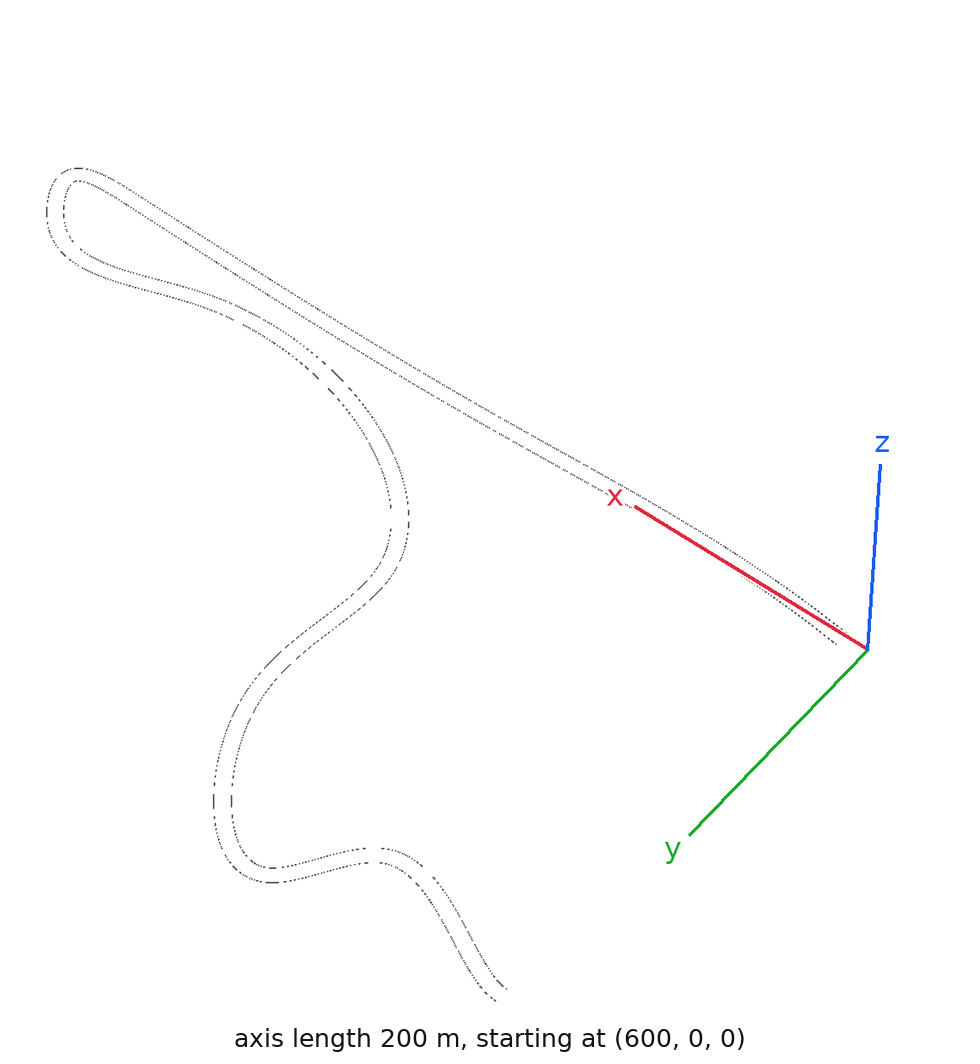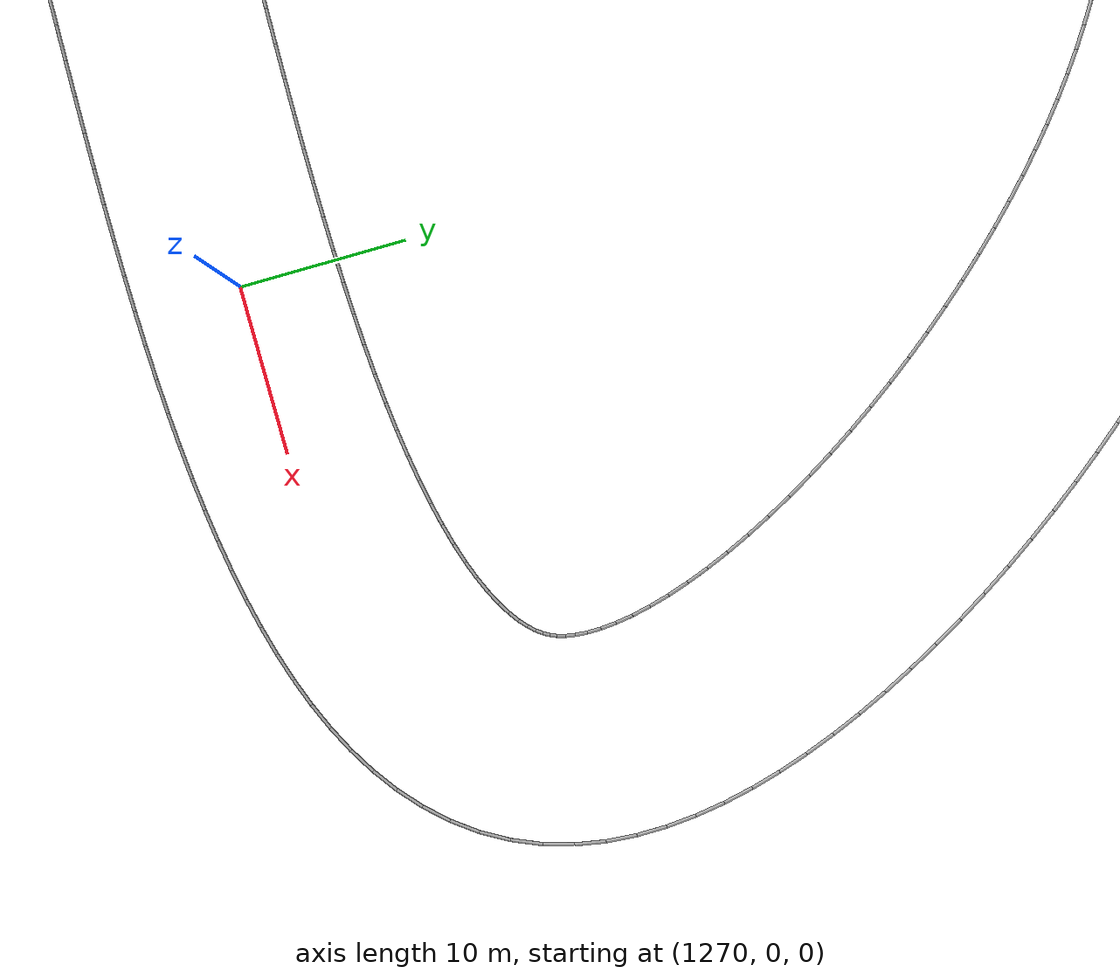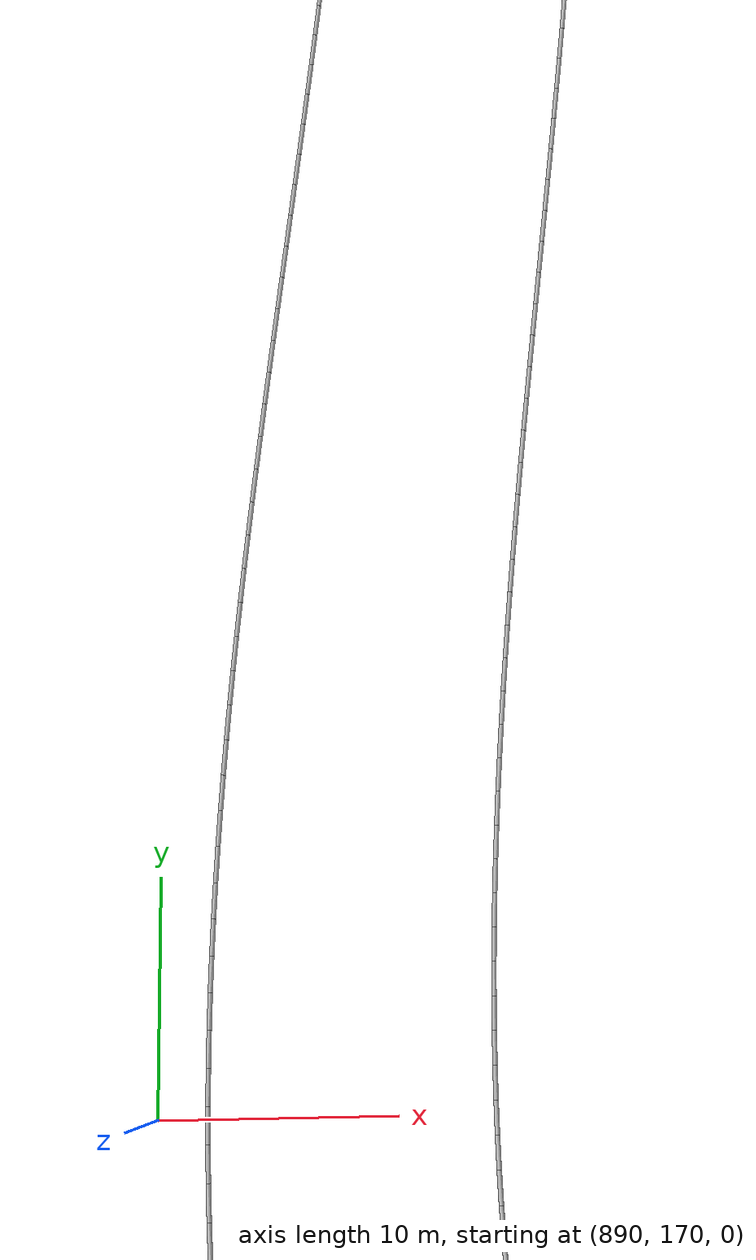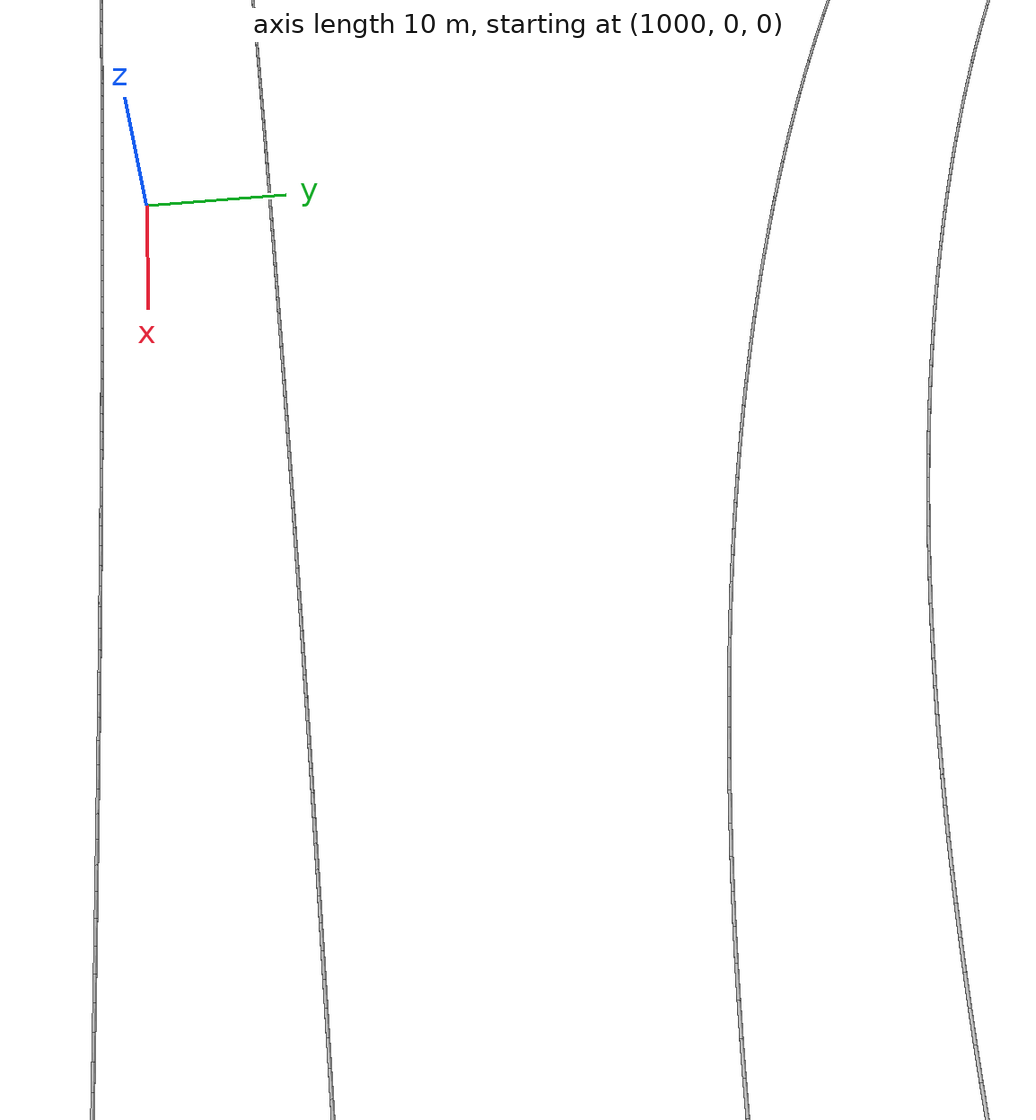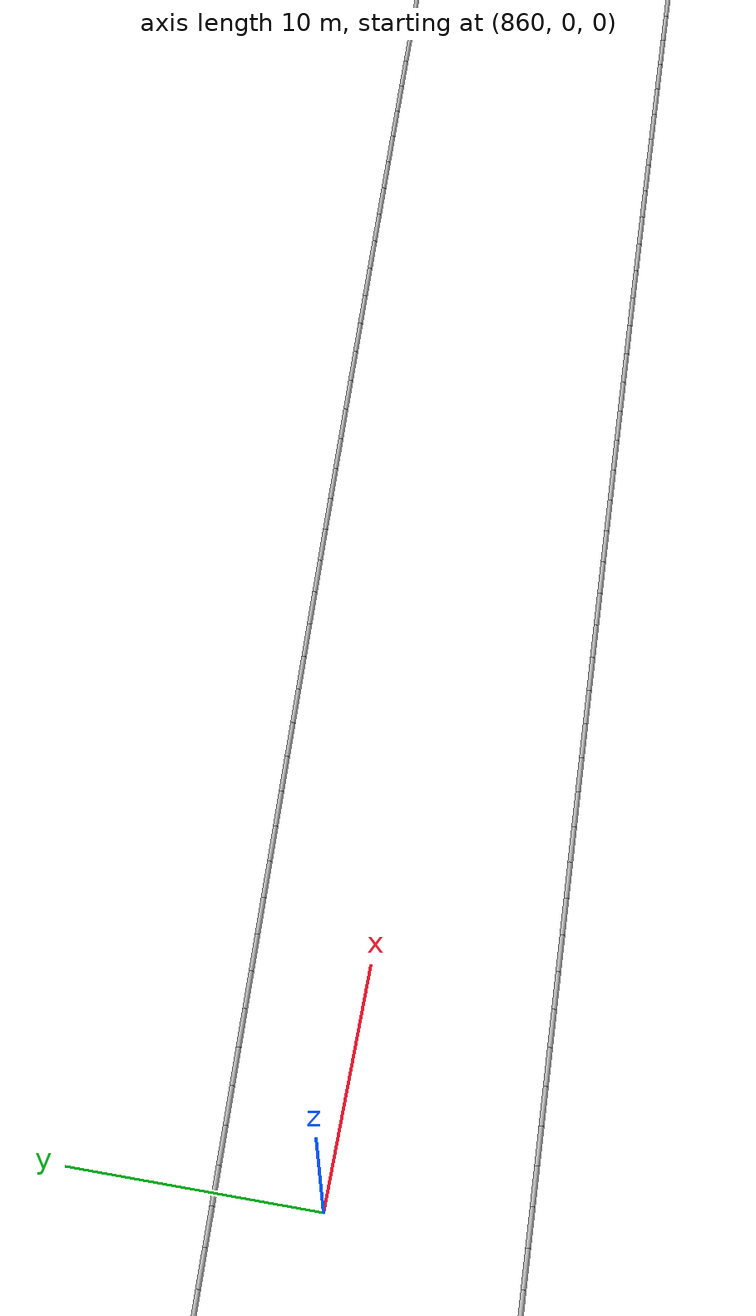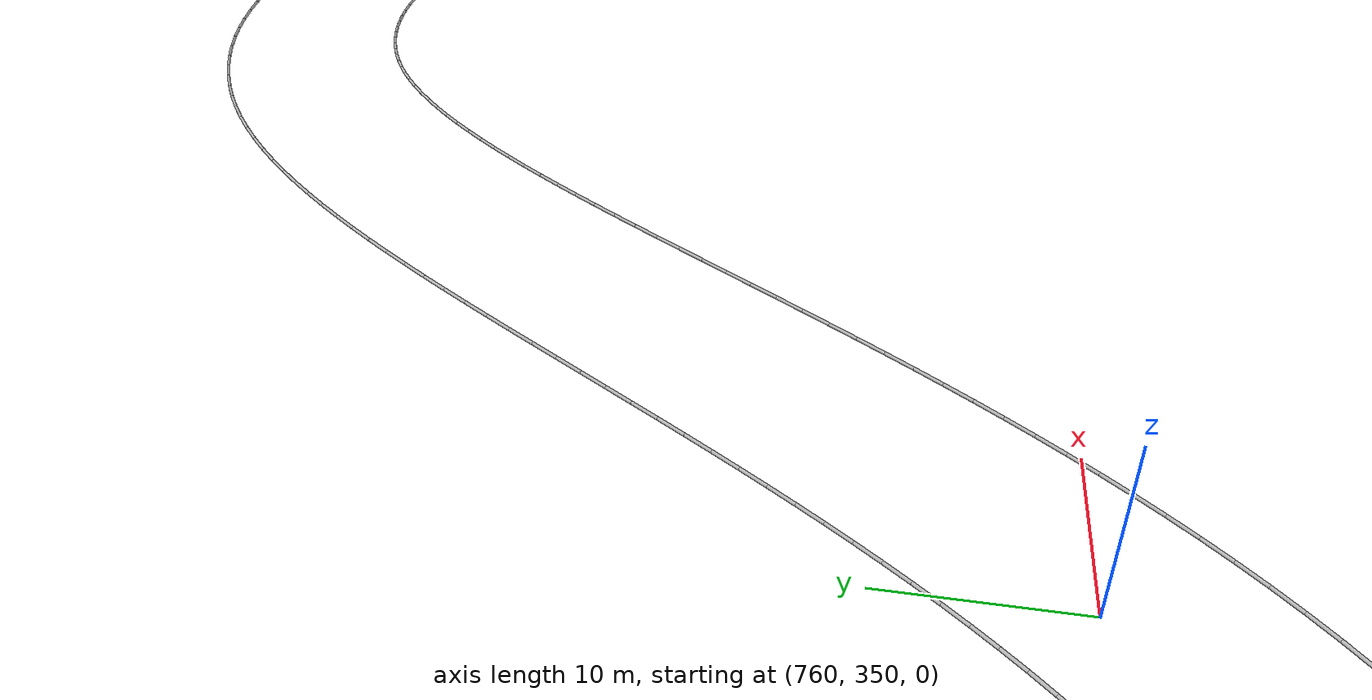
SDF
<sdf version="1.6">
 <model name="line_model">
  <static>true</static>
  <link name="cylinder_(619.2388463025043, -2.2712996259671066)_(620.9623472329657, -2.510564861707646)">
   <pose>620.1005967677349 -2.3909322438373763 0.05 0 1.5707963267948966 -0.13794346802766946</pose>
   <visual name="visual">
    <geometry><cylinder><radius>0.1</radius><length>1.7400296866247649</length></cylinder></geometry>
   </visual>
   <collision name="collision">
    <geometry><cylinder><radius>0.1</radius><length>1.7400296866247649</length></cylinder></geometry>
   </collision>
  </link>
  <link name="cylinder_(620.9623472329657, -2.510564861707646)_(622.6859094621597, -2.7466674639972455)">
   <pose>621.8241283475627 -2.628616162852446 0.05 0 1.5707963267948966 -0.13613792852598167</pose>
   <visual name="visual">
    <geometry><cylinder><radius>0.1</radius><length>1.7396583563193875</length></cylinder></geometry>
   </visual>
   <collision name="collision">
    <geometry><cylinder><radius>0.1</radius><length>1.7396583563193875</length></cylinder></geometry>
   </collision>
  </link>
  <link name="cylinder_(622.6859094621597, -2.7466674639972455)_(624.4095244016521, -2.9795651156576763)">
   <pose>623.5477169319058 -2.863116289827461 0.05 0 1.5707963267948966 -0.13430817417711366</pose>
   <visual name="visual">
    <geometry><cylinder><radius>0.1</radius><length>1.7392785216262816</length></cylinder></geometry>
   </visual>
   <collision name="collision">
    <geometry><cylinder><radius>0.1</radius><length>1.7392785216262816</length></cylinder></geometry>
   </collision>
  </link>
  <link name="cylinder_(624.4095244016521, -2.9795651156576763)_(626.1331834638255, -3.209215486534082)">
   <pose>625.2713539327387 -3.094390301095879 0.05 0 1.5707963267948966 -0.13245414904009373</pose>
   <visual name="visual">
    <geometry><cylinder><radius>0.1</radius><length>1.738890409271425</length></cylinder></geometry>
   </visual>
   <collision name="collision">
    <geometry><cylinder><radius>0.1</radius><length>1.738890409271425</length></cylinder></geometry>
   </collision>
  </link>
  <link name="cylinder_(626.1331834638255, -3.209215486534082)_(627.8568780616102, -3.4355762333680167)">
   <pose>626.9950307627179 -3.3223958599510492 0.05 0 1.5707963267948966 -0.13057579685820597</pose>
   <visual name="visual">
    <geometry><cylinder><radius>0.1</radius><length>1.7384942490959014</length></cylinder></geometry>
   </visual>
   <collision name="collision">
    <geometry><cylinder><radius>0.1</radius><length>1.7384942490959014</length></cylinder></geometry>
   </collision>
  </link>
  <link name="cylinder_(627.8568780616102, -3.4355762333680167)_(629.5805996082096, -3.6586049996713337)">
   <pose>628.7187388349099 -3.547090616519675 0.05 0 1.5707963267948966 -0.12867306108828716</pose>
   <visual name="visual">
    <geometry><cylinder><radius>0.1</radius><length>1.7380902740679456</length></cylinder></geometry>
   </visual>
   <collision name="collision">
    <geometry><cylinder><radius>0.1</radius><length>1.7380902740679456</length></cylinder></geometry>
   </collision>
  </link>
  <link name="cylinder_(629.5805996082096, -3.6586049996713337)_(631.3043395168202, -3.878259415600999)">
   <pose>630.4424695625148 -3.7684322076361663 0.05 0 1.5707963267948966 -0.12674588493046382</pose>
   <visual name="visual">
    <geometry><cylinder><radius>0.1</radius><length>1.7376787202973458</length></cylinder></geometry>
   </visual>
   <collision name="collision">
    <geometry><cylinder><radius>0.1</radius><length>1.7376787202973458</length></cylinder></geometry>
   </collision>
  </link>
  <link name="cylinder_(631.3043395168202, -3.878259415600999)_(633.0280892003428, -4.094497097834826)">
   <pose>632.1662143585816 -3.9863782567179125 0.05 0 1.5707963267948966 -0.12479421135886698</pose>
   <visual name="visual">
    <geometry><cylinder><radius>0.1</radius><length>1.7372598270444064</length></cylinder></geometry>
   </visual>
   <collision name="collision">
    <geometry><cylinder><radius>0.1</radius><length>1.7372598270444064</length></cylinder></geometry>
   </collision>
  </link>
  <link name="cylinder_(633.0280892003428, -4.094497097834826)_(634.7518400710901, -4.307275649448972)">
   <pose>633.8899646357165 -4.200886373641898 0.05 0 1.5707963267948966 -0.12281798315293461</pose>
   <visual name="visual">
    <geometry><cylinder><radius>0.1</radius><length>1.73683383673539</length></cylinder></geometry>
   </visual>
   <collision name="collision">
    <geometry><cylinder><radius>0.1</radius><length>1.73683383673539</length></cylinder></geometry>
   </collision>
  </link>
  <link name="cylinder_(634.7518400710901, -4.307275649448972)_(636.4755835404837, -4.51655265979652)">
   <pose>635.6137118057869 -4.411914154622746 0.05 0 1.5707963267948966 -0.12081714292940746</pose>
   <visual name="visual">
    <geometry><cylinder><radius>0.1</radius><length>1.7364009949712735</length></cylinder></geometry>
   </visual>
   <collision name="collision">
    <geometry><cylinder><radius>0.1</radius><length>1.7364009949712735</length></cylinder></geometry>
   </collision>
  </link>
  <link name="cylinder_(636.4755835404837, -4.51655265979652)_(638.1993110187474, -4.722285704388075)">
   <pose>637.3374472796156 -4.619419182092297 0.05 0 1.5707963267948966 -0.118791633175094</pose>
   <visual name="visual">
    <geometry><cylinder><radius>0.1</radius><length>1.7359615505413821</length></cylinder></geometry>
   </visual>
   <collision name="collision">
    <geometry><cylinder><radius>0.1</radius><length>1.7359615505413821</length></cylinder></geometry>
   </collision>
  </link>
  <link name="cylinder_(638.1993110187474, -4.722285704388075)_(639.9230139145925, -4.92443234477384)">
   <pose>639.0611624666699 -4.823359024580958 0.05 0 1.5707963267948966 -0.11674139628007402</pose>
   <visual name="visual">
    <geometry><cylinder><radius>0.1</radius><length>1.7355157554352858</length></cylinder></geometry>
   </visual>
   <collision name="collision">
    <geometry><cylinder><radius>0.1</radius><length>1.7355157554352858</length></cylinder></geometry>
   </collision>
  </link>
  <link name="cylinder_(639.9230139145925, -4.92443234477384)_(641.6466836348947, -5.122950128428036)">
   <pose>640.7848487747435 -5.023691236600937 0.05 0 1.5707963267948966 -0.11466637457221367</pose>
   <visual name="visual">
    <geometry><cylinder><radius>0.1</radius><length>1.7350638648515169</length></cylinder></geometry>
   </visual>
   <collision name="collision">
    <geometry><cylinder><radius>0.1</radius><length>1.7350638648515169</length></cylinder></geometry>
   </collision>
  </link>
  <link name="cylinder_(641.6466836348947, -5.122950128428036)_(643.3703115843659, -5.3177965886353675)">
   <pose>642.5084976096302 -5.220373358531702 0.05 0 1.5707963267948966 -0.1125665103517368</pose>
   <visual name="visual">
    <geometry><cylinder><radius>0.1</radius><length>1.7346061372121029</length></cylinder></geometry>
   </visual>
   <collision name="collision">
    <geometry><cylinder><radius>0.1</radius><length>1.7346061372121029</length></cylinder></geometry>
   </collision>
  </link>
  <link name="cylinder_(643.3703115843659, -5.3177965886353675)_(645.0938891652179, -5.508929244379669)">
   <pose>644.2321003747919 -5.413362916507518 0.05 0 1.5707963267948966 -0.11044174592689258</pose>
   <visual name="visual">
    <geometry><cylinder><radius>0.1</radius><length>1.7341428341712042</length></cylinder></geometry>
   </visual>
   <collision name="collision">
    <geometry><cylinder><radius>0.1</radius><length>1.7341428341712042</length></cylinder></geometry>
   </collision>
  </link>
  <link name="cylinder_(645.0938891652179, -5.508929244379669)_(646.8174077768178, -5.696305600235673)">
   <pose>645.9556484710179 -5.602617422307671 0.05 0 1.5707963267948966 -0.1082920236506108</pose>
   <visual name="visual">
    <geometry><cylinder><radius>0.1</radius><length>1.73367422062662</length></cylinder></geometry>
   </visual>
   <collision name="collision">
    <geometry><cylinder><radius>0.1</radius><length>1.73367422062662</length></cylinder></geometry>
   </collision>
  </link>
  <link name="cylinder_(646.8174077768178, -5.696305600235673)_(648.5408588153377, -5.879883146263206)">
   <pose>647.6791332960778 -5.788094373249439 0.05 0 1.5707963267948966 -0.10611728595745593</pose>
   <visual name="visual">
    <geometry><cylinder><radius>0.1</radius><length>1.7332005647301192</length></cylinder></geometry>
   </visual>
   <collision name="collision">
    <geometry><cylinder><radius>0.1</radius><length>1.7332005647301192</length></cylinder></geometry>
   </collision>
  </link>
  <link name="cylinder_(648.5408588153377, -5.879883146263206)_(650.2642007389564, -6.05961759005306)">
   <pose>649.402529777147 -5.969750368158133 0.05 0 1.5707963267948966 -0.10391843229146051</pose>
   <visual name="visual">
    <geometry><cylinder><radius>0.1</radius><length>1.7326891977461698</length></cylinder></geometry>
   </visual>
   <collision name="collision">
    <geometry><cylinder><radius>0.1</radius><length>1.7326891977461698</length></cylinder></geometry>
   </collision>
  </link>
  <link name="cylinder_(650.2642007389564, -6.05961759005306)_(651.9872363155418, -6.235484244348769)">
   <pose>651.1257185272491 -6.147550917200915 0.05 0 1.5707963267948966 -0.10171567428276593</pose>
   <visual name="visual">
    <geometry><cylinder><radius>0.1</radius><length>1.7319874936823758</length></cylinder></geometry>
   </visual>
   <collision name="collision">
    <geometry><cylinder><radius>0.1</radius><length>1.7319874936823758</length></cylinder></geometry>
   </collision>
  </link>
  <link name="cylinder_(651.9872363155418, -6.235484244348769)_(653.7099223238138, -6.407509003826148)">
   <pose>652.8485793196778 -6.321496624087459 0.05 0 1.5707963267948966 -0.09952850480329117</pose>
   <visual name="visual">
    <geometry><cylinder><radius>0.1</radius><length>1.7312537656187483</length></cylinder></geometry>
   </visual>
   <collision name="collision">
    <geometry><cylinder><radius>0.1</radius><length>1.7312537656187483</length></cylinder></geometry>
   </collision>
  </link>
  <link name="cylinder_(653.7099223238138, -6.407509003826148)_(655.4322446368668, -6.57572219372129)">
   <pose>654.5710834803403 -6.49161559877372 0.05 0 1.5707963267948966 -0.09735772533040142</pose>
   <visual name="visual">
    <geometry><cylinder><radius>0.1</radius><length>1.7305172138106797</length></cylinder></geometry>
   </visual>
   <collision name="collision">
    <geometry><cylinder><radius>0.1</radius><length>1.7305172138106797</length></cylinder></geometry>
   </collision>
  </link>
  <link name="cylinder_(655.4322446368668, -6.57572219372129)_(657.1541891330123, -6.740154134899389)">
   <pose>656.2932168849395 -6.657938164310339 0.05 0 1.5707963267948966 -0.09520333276562835</pose>
   <visual name="visual">
    <geometry><cylinder><radius>0.1</radius><length>1.7297776478742624</length></cylinder></geometry>
   </visual>
   <collision name="collision">
    <geometry><cylinder><radius>0.1</radius><length>1.7297776478742624</length></cylinder></geometry>
   </collision>
  </link>
  <link name="cylinder_(657.1541891330123, -6.740154134899389)_(658.8757416956198, -6.900835143811531)">
   <pose>658.0149654143161 -6.82049463935546 0.05 0 1.5707963267948966 -0.09306532368932553</pose>
   <visual name="visual">
    <geometry><cylinder><radius>0.1</radius><length>1.7290348788978847</length></cylinder></geometry>
   </visual>
   <collision name="collision">
    <geometry><cylinder><radius>0.1</radius><length>1.7290348788978847</length></cylinder></geometry>
   </collision>
  </link>
  <link name="cylinder_(658.8757416956198, -6.900835143811531)_(660.5968882129605, -7.0577955324538895)">
   <pose>659.7363149542902 -6.979315338132711 0.05 0 1.5707963267948966 -0.09094369437867775</pose>
   <visual name="visual">
    <geometry><cylinder><radius>0.1</radius><length>1.7282887194438112</length></cylinder></geometry>
   </visual>
   <collision name="collision">
    <geometry><cylinder><radius>0.1</radius><length>1.7282887194438112</length></cylinder></geometry>
   </collision>
  </link>
  <link name="cylinder_(660.5968882129605, -7.0577955324538895)_(662.3176145780506, -7.211065608329097)">
   <pose>661.4572513955055 -7.134430570391493 0.05 0 1.5707963267948966 -0.08883844082562724</pose>
   <visual name="visual">
    <geometry><cylinder><radius>0.1</radius><length>1.7275389835470683</length></cylinder></geometry>
   </visual>
   <collision name="collision">
    <geometry><cylinder><radius>0.1</radius><length>1.7275389835470683</length></cylinder></geometry>
   </collision>
  </link>
  <link name="cylinder_(662.3176145780506, -7.211065608329097)_(664.0379066884959, -7.360675674409812)">
   <pose>663.1777606332732 -7.2858706413694545 0.05 0 1.5707963267948966 -0.08674955875459316</pose>
   <visual name="visual">
    <geometry><cylinder><radius>0.1</radius><length>1.7267854867160726</length></cylinder></geometry>
   </visual>
   <collision name="collision">
    <geometry><cylinder><radius>0.1</radius><length>1.7267854867160726</length></cylinder></geometry>
   </collision>
  </link>
  <link name="cylinder_(664.0379066884959, -7.360675674409812)_(665.7577504463382, -7.506656029104429)">
   <pose>664.897828567417 -7.43366585175712 0.05 0 1.5707963267948966 -0.08467704364010167</pose>
   <visual name="visual">
    <geometry><cylinder><radius>0.1</radius><length>1.726028045932522</length></cylinder></geometry>
   </visual>
   <collision name="collision">
    <geometry><cylinder><radius>0.1</radius><length>1.726028045932522</length></cylinder></geometry>
   </collision>
  </link>
  <link name="cylinder_(665.7577504463382, -7.506656029104429)_(667.4771317579003, -7.649036966224857)">
   <pose>666.6174411021193 -7.577846497664643 0.05 0 1.5707963267948966 -0.08262089072431372</pose>
   <visual name="visual">
    <geometry><cylinder><radius>0.1</radius><length>1.725266479650202</length></cylinder></geometry>
   </visual>
   <collision name="collision">
    <geometry><cylinder><radius>0.1</radius><length>1.725266479650202</length></cylinder></geometry>
   </collision>
  </link>
  <link name="cylinder_(667.4771317579003, -7.649036966224857)_(669.1960365336356, -7.787848774956325)">
   <pose>668.336584145768 -7.718442870590591 0.05 0 1.5707963267948966 -0.08058109503430343</pose>
   <visual name="visual">
    <geometry><cylinder><radius>0.1</radius><length>1.7245006077960119</length></cylinder></geometry>
   </visual>
   <collision name="collision">
    <geometry><cylinder><radius>0.1</radius><length>1.7245006077960119</length></cylinder></geometry>
   </collision>
  </link>
  <link name="cylinder_(669.1960365336356, -7.787848774956325)_(670.9144506879742, -7.923121739829178)">
   <pose>670.0552436108048 -7.855485257392751 0.05 0 1.5707963267948966 -0.07855765139940987</pose>
   <visual name="visual">
    <geometry><cylinder><radius>0.1</radius><length>1.7237302517669786</length></cylinder></geometry>
   </visual>
   <collision name="collision">
    <geometry><cylinder><radius>0.1</radius><length>1.7237302517669786</length></cylinder></geometry>
   </collision>
  </link>
  <link name="cylinder_(670.9144506879742, -7.923121739829178)_(672.6323601391744, -8.054886140692608)">
   <pose>671.7734054135742 -7.9890039402608926 0.05 0 1.5707963267948966 -0.07655055446819758</pose>
   <visual name="visual">
    <geometry><cylinder><radius>0.1</radius><length>1.722955234432332</length></cylinder></geometry>
   </visual>
   <collision name="collision">
    <geometry><cylinder><radius>0.1</radius><length>1.722955234432332</length></cylinder></geometry>
   </collision>
  </link>
  <link name="cylinder_(672.6323601391744, -8.054886140692608)_(674.3497508091718, -8.183172252690202)">
   <pose>673.4910554741731 -8.119029196691404 0.05 0 1.5707963267948966 -0.07455979872550171</pose>
   <visual name="visual">
    <geometry><cylinder><radius>0.1</radius><length>1.7221753801299884</length></cylinder></geometry>
   </visual>
   <collision name="collision">
    <geometry><cylinder><radius>0.1</radius><length>1.7221753801299884</length></cylinder></geometry>
   </collision>
  </link>
  <link name="cylinder_(674.3497508091718, -8.183172252690202)_(676.0666086234322, -8.308010346237392)">
   <pose>675.2081797163021 -8.245591299463797 0.05 0 1.5707963267948966 -0.0725853785092093</pose>
   <visual name="visual">
    <geometry><cylinder><radius>0.1</radius><length>1.7213905146675532</length></cylinder></geometry>
   </visual>
   <collision name="collision">
    <geometry><cylinder><radius>0.1</radius><length>1.7213905146675532</length></cylinder></geometry>
   </collision>
  </link>
  <link name="cylinder_(676.0666086234322, -8.308010346237392)_(677.7829195108023, -8.42943068700063)">
   <pose>676.9247640671173 -8.36872051661901 0.05 0 1.5707963267948966 -0.0706272880270153</pose>
   <visual name="visual">
    <geometry><cylinder><radius>0.1</radius><length>1.7206004653190978</length></cylinder></geometry>
   </visual>
   <collision name="collision">
    <geometry><cylinder><radius>0.1</radius><length>1.7206004653190978</length></cylinder></geometry>
   </collision>
  </link>
  <link name="cylinder_(677.7829195108023, -8.42943068700063)_(679.4986694033659, -8.547463535878288)">
   <pose>678.6407944570841 -8.48844711143946 0.05 0 1.5707963267948966 -0.06868552137285218</pose>
   <visual name="visual">
    <geometry><cylinder><radius>0.1</radius><length>1.7198050608269142</length></cylinder></geometry>
   </visual>
   <collision name="collision">
    <geometry><cylinder><radius>0.1</radius><length>1.7198050608269142</length></cylinder></geometry>
   </collision>
  </link>
  <link name="cylinder_(679.4986694033659, -8.547463535878288)_(681.2138442362959, -8.662139148983258)">
   <pose>680.3562568198308 -8.604801342430772 0.05 0 1.5707963267948966 -0.06676007254349768</pose>
   <visual name="visual">
    <geometry><cylinder><radius>0.1</radius><length>1.7190041313963471</length></cylinder></geometry>
   </visual>
   <collision name="collision">
    <geometry><cylinder><radius>0.1</radius><length>1.7190041313963471</length></cylinder></geometry>
   </collision>
  </link>
  <link name="cylinder_(681.2138442362959, -8.662139148983258)_(682.9284299477122, -8.773487777627144)">
   <pose>682.071137092004 -8.717813463305202 0.05 0 1.5707963267948966 -0.06485093545472356</pose>
   <visual name="visual">
    <geometry><cylinder><radius>0.1</radius><length>1.718197508697308</length></cylinder></geometry>
   </visual>
   <collision name="collision">
    <geometry><cylinder><radius>0.1</radius><length>1.718197508697308</length></cylinder></geometry>
   </collision>
  </link>
  <link name="cylinder_(682.9284299477122, -8.773487777627144)_(684.6424124785381, -8.881539668306056)">
   <pose>683.7854212131251 -8.8275137229666 0.05 0 1.5707963267948966 -0.06295810395750258</pose>
   <visual name="visual">
    <geometry><cylinder><radius>0.1</radius><length>1.717385025862169</length></cylinder></geometry>
   </visual>
   <collision name="collision">
    <geometry><cylinder><radius>0.1</radius><length>1.717385025862169</length></cylinder></geometry>
   </collision>
  </link>
  <link name="cylinder_(684.6424124785381, -8.881539668306056)_(686.3557777723576, -8.986325062687904)">
   <pose>685.4990951254479 -8.933932365496979 0.05 0 1.5707963267948966 -0.06108157185410548</pose>
   <visual name="visual">
    <geometry><cylinder><radius>0.1</radius><length>1.716566517482185</length></cylinder></geometry>
   </visual>
   <collision name="collision">
    <geometry><cylinder><radius>0.1</radius><length>1.716566517482185</length></cylinder></geometry>
   </collision>
  </link>
  <link name="cylinder_(686.3557777723576, -8.986325062687904)_(688.068511775275, -9.087874197601181)">
   <pose>687.2121447738164 -9.037099630144542 0.05 0 1.5707963267948966 -0.059221332913925236</pose>
   <visual name="visual">
    <geometry><cylinder><radius>0.1</radius><length>1.7157418196079033</length></cylinder></geometry>
   </visual>
   <collision name="collision">
    <geometry><cylinder><radius>0.1</radius><length>1.7157418196079033</length></cylinder></geometry>
   </collision>
  </link>
  <link name="cylinder_(688.068511775275, -9.087874197601181)_(689.7806004357758, -9.1862173050252)">
   <pose>688.9245561055254 -9.137045751313192 0.05 0 1.5707963267948966 -0.05737738088929901</pose>
   <visual name="visual">
    <geometry><cylinder><radius>0.1</radius><length>1.714910769746645</length></cylinder></geometry>
   </visual>
   <collision name="collision">
    <geometry><cylinder><radius>0.1</radius><length>1.714910769746645</length></cylinder></geometry>
   </collision>
  </link>
  <link name="cylinder_(689.7806004357758, -9.1862173050252)_(691.4920297045869, -9.281384612081652)">
   <pose>690.6363150701814 -9.233800958553427 0.05 0 1.5707963267948966 -0.05554970953113872</pose>
   <visual name="visual">
    <geometry><cylinder><radius>0.1</radius><length>1.714073206860118</length></cylinder></geometry>
   </visual>
   <collision name="collision">
    <geometry><cylinder><radius>0.1</radius><length>1.714073206860118</length></cylinder></geometry>
   </collision>
  </link>
  <link name="cylinder_(691.4920297045869, -9.281384612081652)_(693.2027855345399, -9.373406341027552)">
   <pose>692.3474076195635 -9.327395476554603 0.05 0 1.5707963267948966 -0.05373831260448254</pose>
   <visual name="visual">
    <geometry><cylinder><radius>0.1</radius><length>1.7132289713626365</length></cylinder></geometry>
   </visual>
   <collision name="collision">
    <geometry><cylinder><radius>0.1</radius><length>1.7132289713626365</length></cylinder></geometry>
   </collision>
  </link>
  <link name="cylinder_(693.2027855345399, -9.373406341027552)_(694.9128538804341, -9.462312709249455)">
   <pose>694.0578197074869 -9.417859525138503 0.05 0 1.5707963267948966 -0.05194318390387793</pose>
   <visual name="visual">
    <geometry><cylinder><radius>0.1</radius><length>1.712377905119028</length></cylinder></geometry>
   </visual>
   <collision name="collision">
    <geometry><cylinder><radius>0.1</radius><length>1.712377905119028</length></cylinder></geometry>
   </collision>
  </link>
  <link name="cylinder_(694.9128538804341, -9.462312709249455)_(696.6222206989014, -9.548133929258908)">
   <pose>695.7675372896678 -9.505223319254181 0.05 0 1.5707963267948966 -0.050164317268669975</pose>
   <visual name="visual">
    <geometry><cylinder><radius>0.1</radius><length>1.7115198514422463</length></cylinder></geometry>
   </visual>
   <collision name="collision">
    <geometry><cylinder><radius>0.1</radius><length>1.7115198514422463</length></cylinder></geometry>
   </collision>
  </link>
  <link name="cylinder_(696.6222206989014, -9.548133929258908)_(698.3308719482728, -9.630900208689113)">
   <pose>697.4765463235872 -9.589517068974011 0.05 0 1.5707963267948966 -0.04840170659812256</pose>
   <visual name="visual">
    <geometry><cylinder><radius>0.1</radius><length>1.7106546550923891</length></cylinder></geometry>
   </visual>
   <collision name="collision">
    <geometry><cylinder><radius>0.1</radius><length>1.7106546550923891</length></cylinder></geometry>
   </collision>
  </link>
  <link name="cylinder_(698.3308719482728, -9.630900208689113)_(700.0387935884445, -9.710641750292714)">
   <pose>699.1848327683587 -9.670770979490914 0.05 0 1.5707963267948966 -0.04665534586651313</pose>
   <visual name="visual">
    <geometry><cylinder><radius>0.1</radius><length>1.7097821622721356</length></cylinder></geometry>
   </visual>
   <collision name="collision">
    <geometry><cylinder><radius>0.1</radius><length>1.7097821622721356</length></cylinder></geometry>
   </collision>
  </link>
  <link name="cylinder_(700.0387935884445, -9.710641750292714)_(701.7459715807457, -9.787388751940712)">
   <pose>700.8923825845951 -9.749015251116713 0.05 0 1.5707963267948966 -0.04492522913801331</pose>
   <visual name="visual">
    <geometry><cylinder><radius>0.1</radius><length>1.7089022206257591</length></cylinder></geometry>
   </visual>
   <collision name="collision">
    <geometry><cylinder><radius>0.1</radius><length>1.7089022206257591</length></cylinder></geometry>
   </collision>
  </link>
  <link name="cylinder_(701.7459715807457, -9.787388751940712)_(703.4523918878086, -9.86117140662243)">
   <pose>702.5991817342772 -9.824280079281571 0.05 0 1.5707963267948966 -0.043211350581485</pose>
   <visual name="visual">
    <geometry><cylinder><radius>0.1</radius><length>1.7080146792368387</length></cylinder></geometry>
   </visual>
   <collision name="collision">
    <geometry><cylinder><radius>0.1</radius><length>1.7080146792368387</length></cylinder></geometry>
   </collision>
  </link>
  <link name="cylinder_(703.4523918878086, -9.86117140662243)_(705.1580404734389, -9.93201990244652)">
   <pose>704.3052161806238 -9.896595654534476 0.05 0 1.5707963267948966 -0.041513704485172366</pose>
   <visual name="visual">
    <geometry><cylinder><radius>0.1</radius><length>1.7071193886260374</length></cylinder></geometry>
   </visual>
   <collision name="collision">
    <geometry><cylinder><radius>0.1</radius><length>1.7071193886260374</length></cylinder></geometry>
   </collision>
  </link>
  <link name="cylinder_(705.1580404734389, -9.93201990244652)_(706.8629033024856, -9.999964422642886)">
   <pose>706.0104718879622 -9.965992162544703 0.05 0 1.5707963267948966 -0.03983228527129257</pose>
   <visual name="visual">
    <geometry><cylinder><radius>0.1</radius><length>1.7062162007465635</length></cylinder></geometry>
   </visual>
   <collision name="collision">
    <geometry><cylinder><radius>0.1</radius><length>1.7062162007465635</length></cylinder></geometry>
   </collision>
  </link>
  <link name="cylinder_(706.8629033024856, -9.999964422642886)_(708.566966340715, -10.065035145565599)">
   <pose>707.7149348216003 -10.032499784104242 0.05 0 1.5707963267948966 -0.03816708751046466</pose>
   <visual name="visual">
    <geometry><cylinder><radius>0.1</radius><length>1.705304968983913</length></cylinder></geometry>
   </visual>
   <collision name="collision">
    <geometry><cylinder><radius>0.1</radius><length>1.705304968983913</length></cylinder></geometry>
   </collision>
  </link>
  <link name="cylinder_(708.566966340715, -10.065035145565599)_(710.2702155546835, -10.127262244696674)">
   <pose>709.4185909476993 -10.096148695131136 0.05 0 1.5707963267948966 -0.036518105936077946</pose>
   <visual name="visual">
    <geometry><cylinder><radius>0.1</radius><length>1.704385548152396</length></cylinder></geometry>
   </visual>
   <collision name="collision">
    <geometry><cylinder><radius>0.1</radius><length>1.704385548152396</length></cylinder></geometry>
   </collision>
  </link>
  <link name="cylinder_(710.2702155546835, -10.127262244696674)_(711.9726369116121, -10.186675888650674)">
   <pose>711.1214262331478 -10.156969066673675 0.05 0 1.5707963267948966 -0.034885335458530425</pose>
   <visual name="visual">
    <geometry><cylinder><radius>0.1</radius><length>1.7034577944916338</length></cylinder></geometry>
   </visual>
   <collision name="collision">
    <geometry><cylinder><radius>0.1</radius><length>1.7034577944916338</length></cylinder></geometry>
   </collision>
  </link>
  <link name="cylinder_(711.9726369116121, -10.186675888650674)_(713.6742163792627, -10.243306241180175)">
   <pose>712.8234266454374 -10.214991064915424 0.05 0 1.5707963267948966 -0.03326877117935736</pose>
   <visual name="visual">
    <geometry><cylinder><radius>0.1</radius><length>1.7025215656659902</length></cylinder></geometry>
   </visual>
   <collision name="collision">
    <geometry><cylinder><radius>0.1</radius><length>1.7025215656659902</length></cylinder></geometry>
   </collision>
  </link>
  <link name="cylinder_(713.6742163792627, -10.243306241180175)_(715.3749399258141, -10.297183461181934)">
   <pose>714.5245781525384 -10.270244851181054 0.05 0 1.5707963267948966 -0.03166840840528516</pose>
   <visual name="visual">
    <geometry><cylinder><radius>0.1</radius><length>1.7015767207592023</length></cylinder></geometry>
   </visual>
   <collision name="collision">
    <geometry><cylinder><radius>0.1</radius><length>1.7015767207592023</length></cylinder></geometry>
   </collision>
  </link>
  <link name="cylinder_(715.3749399258141, -10.297183461181934)_(717.0747935197405, -10.348337702703812)">
   <pose>716.2248667227773 -10.322760581942873 0.05 0 1.5707963267948966 -0.03008424266213209</pose>
   <visual name="visual">
    <geometry><cylinder><radius>0.1</radius><length>1.7006231202738897</length></cylinder></geometry>
   </visual>
   <collision name="collision">
    <geometry><cylinder><radius>0.1</radius><length>1.7006231202738897</length></cylinder></geometry>
   </collision>
  </link>
  <link name="cylinder_(717.0747935197405, -10.348337702703812)_(718.7737631296891, -10.396799114952373)">
   <pose>717.9242783247148 -10.372568408828093 0.05 0 1.5707963267948966 -0.028516269708673315</pose>
   <visual name="visual">
    <geometry><cylinder><radius>0.1</radius><length>1.6996606261268443</length></cylinder></geometry>
   </visual>
   <collision name="collision">
    <geometry><cylinder><radius>0.1</radius><length>1.6996606261268443</length></cylinder></geometry>
   </collision>
  </link>
  <link name="cylinder_(718.7737631296891, -10.396799114952373)_(720.4718347243619, -10.442597842301147)">
   <pose>719.6227989270255 -10.41969847862676 0.05 0 1.5707963267948966 -0.026964485550342494</pose>
   <visual name="visual">
    <geometry><cylinder><radius>0.1</radius><length>1.698689101649087</length></cylinder></geometry>
   </visual>
   <collision name="collision">
    <geometry><cylinder><radius>0.1</radius><length>1.698689101649087</length></cylinder></geometry>
   </collision>
  </link>
  <link name="cylinder_(720.4718347243619, -10.442597842301147)_(722.1689942723942, -10.485764024299458)">
   <pose>721.3204144983781 -10.464180933300302 0.05 0 1.5707963267948966 -0.025428886452911383</pose>
   <visual name="visual">
    <geometry><cylinder><radius>0.1</radius><length>1.6977084115788752</length></cylinder></geometry>
   </visual>
   <collision name="collision">
    <geometry><cylinder><radius>0.1</radius><length>1.6977084115788752</length></cylinder></geometry>
   </collision>
  </link>
  <link name="cylinder_(722.1689942723942, -10.485764024299458)_(723.8652277422384, -10.526327795681855)">
   <pose>723.0171110073163 -10.506045909990657 0.05 0 1.5707963267948966 -0.02390946895599823</pose>
   <visual name="visual">
    <geometry><cylinder><radius>0.1</radius><length>1.6967184220631213</length></cylinder></geometry>
   </visual>
   <collision name="collision">
    <geometry><cylinder><radius>0.1</radius><length>1.6967184220631213</length></cylinder></geometry>
   </collision>
  </link>
  <link name="cylinder_(723.8652277422384, -10.526327795681855)_(725.5605211020454, -10.564319286378048)">
   <pose>724.7128744221419 -10.545323541029951 0.05 0 1.5707963267948966 -0.02240622988655364</pose>
   <visual name="visual">
    <geometry><cylinder><radius>0.1</radius><length>1.6957190006516587</length></cylinder></geometry>
   </visual>
   <collision name="collision">
    <geometry><cylinder><radius>0.1</radius><length>1.6957190006516587</length></cylinder></geometry>
   </collision>
  </link>
  <link name="cylinder_(725.5605211020454, -10.564319286378048)_(727.2548603195494, -10.599768621523364)">
   <pose>726.4076907107974 -10.582043953950706 0.05 0 1.5707963267948966 -0.020919166372225018</pose>
   <visual name="visual">
    <geometry><cylinder><radius>0.1</radius><length>1.6947100162960618</length></cylinder></geometry>
   </visual>
   <collision name="collision">
    <geometry><cylinder><radius>0.1</radius><length>1.6947100162960618</length></cylinder></geometry>
   </collision>
  </link>
  <link name="cylinder_(727.2548603195494, -10.599768621523364)_(728.948231361952, -10.632705921469615)">
   <pose>728.1015458407508 -10.61623727149649 0.05 0 1.5707963267948966 -0.019448275854631308</pose>
   <visual name="visual">
    <geometry><cylinder><radius>0.1</radius><length>1.6936913393459778</length></cylinder></geometry>
   </visual>
   <collision name="collision">
    <geometry><cylinder><radius>0.1</radius><length>1.6936913393459778</length></cylinder></geometry>
   </collision>
  </link>
  <link name="cylinder_(728.948231361952, -10.632705921469615)_(730.6406201958082, -10.663161301796436)">
   <pose>729.7944257788802 -10.647933611633025 0.05 0 1.5707963267948966 -0.017993556102593088</pose>
   <visual name="visual">
    <geometry><cylinder><radius>0.1</radius><length>1.6926628415463907</length></cylinder></geometry>
   </visual>
   <collision name="collision">
    <geometry><cylinder><radius>0.1</radius><length>1.6926628415463907</length></cylinder></geometry>
   </collision>
  </link>
  <link name="cylinder_(730.6406201958082, -10.663161301796436)_(732.3320127869125, -10.69116487332294)">
   <pose>731.4863164913604 -10.677163087559688 0.05 0 1.5707963267948966 -0.01655500522522053</pose>
   <visual name="visual">
    <geometry><cylinder><radius>0.1</radius><length>1.691624396035012</length></cylinder></geometry>
   </visual>
   <collision name="collision">
    <geometry><cylinder><radius>0.1</radius><length>1.691624396035012</length></cylinder></geometry>
   </collision>
  </link>
  <link name="cylinder_(732.3320127869125, -10.69116487332294)_(734.022395100187, -10.716746742119787)">
   <pose>733.1772039435498 -10.703955807721364 0.05 0 1.5707963267948966 -0.015132621684993377</pose>
   <visual name="visual">
    <geometry><cylinder><radius>0.1</radius><length>1.69057587733959</length></cylinder></geometry>
   </visual>
   <collision name="collision">
    <geometry><cylinder><radius>0.1</radius><length>1.69057587733959</length></cylinder></geometry>
   </collision>
  </link>
  <link name="cylinder_(734.022395100187, -10.716746742119787)_(735.7117530995699, -10.739937009521505)">
   <pose>734.8670740998784 -10.728341875820647 0.05 0 1.5707963267948966 -0.013726404310705619</pose>
   <visual name="visual">
    <geometry><cylinder><radius>0.1</radius><length>1.6895171613751319</length></cylinder></geometry>
   </visual>
   <collision name="collision">
    <geometry><cylinder><radius>0.1</radius><length>1.6895171613751319</length></cylinder></geometry>
   </collision>
  </link>
  <link name="cylinder_(735.7117530995699, -10.739937009521505)_(737.4000727479039, -10.760765772139127)">
   <pose>736.555912923737 -10.750351390830316 0.05 0 1.5707963267948966 -0.012336352310391683</pose>
   <visual name="visual">
    <geometry><cylinder><radius>0.1</radius><length>1.6884481254402468</length></cylinder></geometry>
   </visual>
   <collision name="collision">
    <geometry><cylinder><radius>0.1</radius><length>1.6884481254402468</length></cylinder></geometry>
   </collision>
  </link>
  <link name="cylinder_(737.4000727479039, -10.760765772139127)_(739.087340006827, -10.779263121873042)">
   <pose>738.2437063773655 -10.770014447006083 0.05 0 1.5707963267948966 -0.010962465284132871</pose>
   <visual name="visual">
    <geometry><cylinder><radius>0.1</radius><length>1.6873686482156893</length></cylinder></geometry>
   </visual>
   <collision name="collision">
    <geometry><cylinder><radius>0.1</radius><length>1.6873686482156893</length></cylinder></geometry>
   </collision>
  </link>
  <link name="cylinder_(739.087340006827, -10.779263121873042)_(740.7735408366627, -10.795459145926067)">
   <pose>739.9304404217448 -10.787361133899555 0.05 0 1.5707963267948966 -0.009604743236843264</pose>
   <visual name="visual">
    <geometry><cylinder><radius>0.1</radius><length>1.6862786097598688</length></cylinder></geometry>
   </visual>
   <collision name="collision">
    <geometry><cylinder><radius>0.1</radius><length>1.6862786097598688</length></cylinder></geometry>
   </collision>
  </link>
  <link name="cylinder_(740.7735408366627, -10.795459145926067)_(742.4586611963136, -10.80938392681669)">
   <pose>741.6161010164882 -10.802421536371378 0.05 0 1.5707963267948966 -0.008263186590944088</pose>
   <visual name="visual">
    <geometry><cylinder><radius>0.1</radius><length>1.6851778915096358</length></cylinder></geometry>
   </visual>
   <collision name="collision">
    <geometry><cylinder><radius>0.1</radius><length>1.6851778915096358</length></cylinder></geometry>
   </collision>
  </link>
  <link name="cylinder_(742.4586611963136, -10.80938392681669)_(744.1426870431515, -10.821067542392441)">
   <pose>743.3006741197325 -10.815225734604565 0.05 0 1.5707963267948966 -0.006937796199033031</pose>
   <visual name="visual">
    <geometry><cylinder><radius>0.1</radius><length>1.6840663762722456</length></cylinder></geometry>
   </visual>
   <collision name="collision">
    <geometry><cylinder><radius>0.1</radius><length>1.6840663762722456</length></cylinder></geometry>
   </collision>
  </link>
  <link name="cylinder_(744.1426870431515, -10.821067542392441)_(745.8256043329122, -10.830540065843396)">
   <pose>744.9841456880318 -10.825803804117918 0.05 0 1.5707963267948966 -0.005628573356445669</pose>
   <visual name="visual">
    <geometry><cylinder><radius>0.1</radius><length>1.6829439482277178</length></cylinder></geometry>
   </visual>
   <collision name="collision">
    <geometry><cylinder><radius>0.1</radius><length>1.6829439482277178</length></cylinder></geometry>
   </collision>
  </link>
  <link name="cylinder_(745.8256043329122, -10.830540065843396)_(747.5073990195896, -10.837831565715707)">
   <pose>746.6665016762508 -10.834185815779552 0.05 0 1.5707963267948966 -0.004335519813778698</pose>
   <visual name="visual">
    <geometry><cylinder><radius>0.1</radius><length>1.6818104929231785</length></cylinder></geometry>
   </visual>
   <collision name="collision">
    <geometry><cylinder><radius>0.1</radius><length>1.6818104929231785</length></cylinder></geometry>
   </collision>
  </link>
  <link name="cylinder_(747.5073990195896, -10.837831565715707)_(749.1880570553298, -10.842972105925227)">
   <pose>748.3477280374597 -10.840401835820467 0.05 0 1.5707963267948966 -0.003058637789379009</pose>
   <visual name="visual">
    <geometry><cylinder><radius>0.1</radius><length>1.68066589727158</length></cylinder></geometry>
   </visual>
   <collision name="collision">
    <geometry><cylinder><radius>0.1</radius><length>1.68066589727158</length></cylinder></geometry>
   </collision>
  </link>
  <link name="cylinder_(749.1880570553298, -10.842972105925227)_(750.8675643903279, -10.84599174577112)">
   <pose>750.0278107228288 -10.844481925848173 0.05 0 1.5707963267948966 -0.0017979299817586912</pose>
   <visual name="visual">
    <geometry><cylinder><radius>0.1</radius><length>1.6795100495493445</length></cylinder></geometry>
   </visual>
   <collision name="collision">
    <geometry><cylinder><radius>0.1</radius><length>1.6795100495493445</length></cylinder></geometry>
   </collision>
  </link>
  <link name="cylinder_(750.8675643903279, -10.84599174577112)_(752.5459069727227, -10.84692053994943)">
   <pose>751.7067356815253 -10.846456142860275 0.05 0 1.5707963267948966 -0.0005533995819677334</pose>
   <visual name="visual">
    <geometry><cylinder><radius>0.1</radius><length>1.6783428393920234</length></cylinder></geometry>
   </visual>
   <collision name="collision">
    <geometry><cylinder><radius>0.1</radius><length>1.6783428393920234</length></cylinder></geometry>
   </collision>
  </link>
  <link name="cylinder_(752.5459069727227, -10.84692053994943)_(754.2230707484946, -10.845788538566639)">
   <pose>753.3844888606086 -10.846354539258034 0.05 0 1.5707963267948966 0.0006749497140628543</pose>
   <visual name="visual">
    <geometry><cylinder><radius>0.1</radius><length>1.677164157793893</length></cylinder></geometry>
   </visual>
   <collision name="collision">
    <geometry><cylinder><radius>0.1</radius><length>1.677164157793893</length></cylinder></geometry>
   </collision>
  </link>
  <link name="cylinder_(754.2230707484946, -10.845788538566639)_(755.8990416613632, -10.842625787153093)">
   <pose>755.061056204929 -10.844207162859867 0.05 0 1.5707963267948966 0.0018871136932425297</pose>
   <visual name="visual">
    <geometry><cylinder><radius>0.1</radius><length>1.6759738971052287</length></cylinder></geometry>
   </visual>
   <collision name="collision">
    <geometry><cylinder><radius>0.1</radius><length>1.6759738971052287</length></cylinder></geometry>
   </collision>
  </link>
  <link name="cylinder_(755.8990416613632, -10.842625787153093)_(757.5738056526852, -10.83746232667636)">
   <pose>756.7364236570243 -10.840044056914726 0.05 0 1.5707963267948966 0.003083087613046075</pose>
   <visual name="visual">
    <geometry><cylinder><radius>0.1</radius><length>1.6747719510288614</length></cylinder></geometry>
   </visual>
   <collision name="collision">
    <geometry><cylinder><radius>0.1</radius><length>1.6747719510288614</length></cylinder></geometry>
   </collision>
  </link>
  <link name="cylinder_(757.5738056526852, -10.83746232667636)_(759.2473486613537, -10.83032819355439)">
   <pose>758.4105771570195 -10.833895260115375 0.05 0 1.5707963267948966 0.0042628661893210264</pose>
   <visual name="visual">
    <geometry><cylinder><radius>0.1</radius><length>1.6735582146189676</length></cylinder></geometry>
   </visual>
   <collision name="collision">
    <geometry><cylinder><radius>0.1</radius><length>1.6735582146189676</length></cylinder></geometry>
   </collision>
  </link>
  <link name="cylinder_(759.2473486613537, -10.83032819355439)_(760.9196566236967, -10.82125341966855)">
   <pose>760.0835026425252 -10.825790806611469 0.05 0 1.5707963267948966 0.005426443584077712</pose>
   <visual name="visual">
    <geometry><cylinder><radius>0.1</radius><length>1.6723325842776677</length></cylinder></geometry>
   </visual>
   <collision name="collision">
    <geometry><cylinder><radius>0.1</radius><length>1.6723325842776677</length></cylinder></geometry>
   </collision>
  </link>
  <link name="cylinder_(760.9196566236967, -10.82125341966855)_(762.5907154733785, -10.810268032376417)">
   <pose>761.7551860485376 -10.815760726022482 0.05 0 1.5707963267948966 0.006573813393335508</pose>
   <visual name="visual">
    <geometry><cylinder><radius>0.1</radius><length>1.6710949577548895</length></cylinder></geometry>
   </visual>
   <collision name="collision">
    <geometry><cylinder><radius>0.1</radius><length>1.6710949577548895</length></cylinder></geometry>
   </collision>
  </link>
  <link name="cylinder_(762.5907154733785, -10.810268032376417)_(764.2605111412992, -10.797402054524348)">
   <pose>763.4256133073388 -10.803835043450382 0.05 0 1.5707963267948966 0.00770496863500238</pose>
   <visual name="visual">
    <geometry><cylinder><radius>0.1</radius><length>1.669845234143772</length></cylinder></geometry>
   </visual>
   <collision name="collision">
    <geometry><cylinder><radius>0.1</radius><length>1.669845234143772</length></cylinder></geometry>
   </collision>
  </link>
  <link name="cylinder_(764.2605111412992, -10.797402054524348)_(765.9290295554961, -10.782685504459781)">
   <pose>765.0947703483976 -10.790043779492065 0.05 0 1.5707963267948966 0.008819901736749498</pose>
   <visual name="visual">
    <geometry><cylinder><radius>0.1</radius><length>1.6685833138803632</length></cylinder></geometry>
   </visual>
   <collision name="collision">
    <geometry><cylinder><radius>0.1</radius><length>1.6685833138803632</length></cylinder></geometry>
   </collision>
  </link>
  <link name="cylinder_(765.9290295554961, -10.782685504459781)_(767.5962566410456, -10.766148396043244)">
   <pose>766.7626430982708 -10.774416950251513 0.05 0 1.5707963267948966 0.009918604523931143</pose>
   <visual name="visual">
    <geometry><cylinder><radius>0.1</radius><length>1.6673090987410246</length></cylinder></geometry>
   </visual>
   <collision name="collision">
    <geometry><cylinder><radius>0.1</radius><length>1.6673090987410246</length></cylinder></geometry>
   </collision>
  </link>
  <link name="cylinder_(767.5962566410456, -10.766148396043244)_(769.2621783199645, -10.747820738660032)">
   <pose>768.429217480505 -10.756984567351637 0.05 0 1.5707963267948966 0.011001068207508933</pose>
   <visual name="visual">
    <geometry><cylinder><radius>0.1</radius><length>1.6660224918401567</length></cylinder></geometry>
   </visual>
   <collision name="collision">
    <geometry><cylinder><radius>0.1</radius><length>1.6660224918401567</length></cylinder></geometry>
   </collision>
  </link>
  <link name="cylinder_(769.2621783199645, -10.747820738660032)_(770.9267805111139, -10.727732537231542)">
   <pose>770.0944794155391 -10.737776637945787 0.05 0 1.5707963267948966 0.012067283371984594</pose>
   <visual name="visual">
    <geometry><cylinder><radius>0.1</radius><length>1.664723397629729</length></cylinder></geometry>
   </visual>
   <collision name="collision">
    <geometry><cylinder><radius>0.1</radius><length>1.664723397629729</length></cylinder></geometry>
   </collision>
  </link>
  <link name="cylinder_(770.9267805111139, -10.727732537231542)_(772.5900491301006, -10.705913792226207)">
   <pose>771.7584148206072 -10.716823164728876 0.05 0 1.5707963267948966 0.013117239963371012</pose>
   <visual name="visual">
    <geometry><cylinder><radius>0.1</radius><length>1.6634117218956168</length></cylinder></geometry>
   </visual>
   <collision name="collision">
    <geometry><cylinder><radius>0.1</radius><length>1.6634117218956168</length></cylinder></geometry>
   </collision>
  </link>
  <link name="cylinder_(772.5900491301006, -10.705913792226207)_(774.251970089182, -10.682394499670039)">
   <pose>773.4210096096413 -10.694154145948122 0.05 0 1.5707963267948966 0.014150927277123223</pose>
   <visual name="visual">
    <geometry><cylinder><radius>0.1</radius><length>1.6620873717576745</length></cylinder></geometry>
   </visual>
   <collision name="collision">
    <geometry><cylinder><radius>0.1</radius><length>1.6620873717576745</length></cylinder></geometry>
   </collision>
  </link>
  <link name="cylinder_(774.251970089182, -10.682394499670039)_(775.9125292971689, -10.657204651156723)">
   <pose>775.0822496931755 -10.669799575413382 0.05 0 1.5707963267948966 0.015168333946119387</pose>
   <visual name="visual">
    <geometry><cylinder><radius>0.1</radius><length>1.6607502556670808</length></cylinder></geometry>
   </visual>
   <collision name="collision">
    <geometry><cylinder><radius>0.1</radius><length>1.6607502556670808</length></cylinder></geometry>
   </collision>
  </link>
  <link name="cylinder_(775.9125292971689, -10.657204651156723)_(777.57171265933, -10.630374233857218)">
   <pose>776.7421209782494 -10.643789442506971 0.05 0 1.5707963267948966 0.016169447928635637</pose>
   <visual name="visual">
    <geometry><cylinder><radius>0.1</radius><length>1.659400283405041</length></cylinder></geometry>
   </visual>
   <collision name="collision">
    <geometry><cylinder><radius>0.1</radius><length>1.659400283405041</length></cylinder></geometry>
   </collision>
  </link>
  <link name="cylinder_(777.57171265933, -10.630374233857218)_(779.2295060772966, -10.601933230528907)">
   <pose>778.4006093683133 -10.616153732193062 0.05 0 1.5707963267948966 0.017154256496273904</pose>
   <visual name="visual">
    <geometry><cylinder><radius>0.1</radius><length>1.6580373660818284</length></cylinder></geometry>
   </visual>
   <collision name="collision">
    <geometry><cylinder><radius>0.1</radius><length>1.6580373660818284</length></cylinder></geometry>
   </collision>
  </link>
  <link name="cylinder_(779.2295060772966, -10.601933230528907)_(780.8858954489674, -10.571911619524183)">
   <pose>780.0577007631321 -10.586922425026545 0.05 0 1.5707963267948966 0.018122746221948035</pose>
   <visual name="visual">
    <geometry><cylinder><radius>0.1</radius><length>1.6566614161352644</length></cylinder></geometry>
   </visual>
   <collision name="collision">
    <geometry><cylinder><radius>0.1</radius><length>1.6566614161352644</length></cylinder></geometry>
   </collision>
  </link>
  <link name="cylinder_(780.8858954489674, -10.571911619524183)_(782.5408666684133, -10.540339374798492)">
   <pose>781.7133810586904 -10.556125497161338 0.05 0 1.5707963267948966 0.01907490296783033</pose>
   <visual name="visual">
    <geometry><cylinder><radius>0.1</radius><length>1.655272347328745</length></cylinder></geometry>
   </visual>
   <collision name="collision">
    <geometry><cylinder><radius>0.1</radius><length>1.655272347328745</length></cylinder></geometry>
   </collision>
  </link>
  <link name="cylinder_(782.5408666684133, -10.540339374798492)_(784.1944056257836, -10.507246465917786)">
   <pose>783.3676361470984 -10.52379292035814 0.05 0 1.5707963267948966 0.0200107118732763</pose>
   <visual name="visual">
    <geometry><cylinder><radius>0.1</radius><length>1.6538700747517776</length></cylinder></geometry>
   </visual>
   <collision name="collision">
    <geometry><cylinder><radius>0.1</radius><length>1.6538700747517776</length></cylinder></geometry>
   </collision>
  </link>
  <link name="cylinder_(784.1944056257836, -10.507246465917786)_(785.846498207211, -10.472662858065384)">
   <pose>785.0204519164972 -10.489954661991586 0.05 0 1.5707963267948966 0.02093015734275858</pose>
   <visual name="visual">
    <geometry><cylinder><radius>0.1</radius><length>1.6524545148171192</length></cylinder></geometry>
   </visual>
   <collision name="collision">
    <geometry><cylinder><radius>0.1</radius><length>1.6524545148171192</length></cylinder></geometry>
   </collision>
  </link>
  <link name="cylinder_(785.846498207211, -10.472662858065384)_(787.4971302947177, -10.43661851204817)">
   <pose>786.6718142509644 -10.454640685056777 0.05 0 1.5707963267948966 0.021833223033768022</pose>
   <visual name="visual">
    <geometry><cylinder><radius>0.1</radius><length>1.6510255852611109</length></cylinder></geometry>
   </visual>
   <collision name="collision">
    <geometry><cylinder><radius>0.1</radius><length>1.6510255852611109</length></cylinder></geometry>
   </collision>
  </link>
  <link name="cylinder_(787.4971302947177, -10.43661851204817)_(789.1462877661222, -10.399143384302121)">
   <pose>788.3217090304199 -10.417880948175146 0.05 0 1.5707963267948966 0.02271989184470876</pose>
   <visual name="visual">
    <geometry><cylinder><radius>0.1</radius><length>1.6495832051426658</length></cylinder></geometry>
   </visual>
   <collision name="collision">
    <geometry><cylinder><radius>0.1</radius><length>1.6495832051426658</length></cylinder></geometry>
   </collision>
  </link>
  <link name="cylinder_(789.1462877661222, -10.399143384302121)_(790.7939564949447, -10.360267426897158)">
   <pose>789.9701221305335 -10.37970540559964 0.05 0 1.5707963267948966 0.02359014590274499</pose>
   <visual name="visual">
    <geometry><cylinder><radius>0.1</radius><length>1.6481272948421601</length></cylinder></geometry>
   </visual>
   <collision name="collision">
    <geometry><cylinder><radius>0.1</radius><length>1.6481272948421601</length></cylinder></geometry>
   </collision>
  </link>
  <link name="cylinder_(790.7939564949447, -10.360267426897158)_(792.4401223503147, -10.320020587541249)">
   <pose>791.6170394226297 -10.340144007219203 0.05 0 1.5707963267948966 0.024443966551642382</pose>
   <visual name="visual">
    <geometry><cylinder><radius>0.1</radius><length>1.6466577760616015</length></cylinder></geometry>
   </visual>
   <collision name="collision">
    <geometry><cylinder><radius>0.1</radius><length>1.6466577760616015</length></cylinder></geometry>
   </collision>
  </link>
  <link name="cylinder_(792.4401223503147, -10.320020587541249)_(794.0847711968763, -10.278432809583764)">
   <pose>793.2624467735955 -10.299226698562506 0.05 0 1.5707963267948966 0.025281334339589775</pose>
   <visual name="visual">
    <geometry><cylinder><radius>0.1</radius><length>1.6451745718226594</length></cylinder></geometry>
   </visual>
   <collision name="collision">
    <geometry><cylinder><radius>0.1</radius><length>1.6451745718226594</length></cylinder></geometry>
   </collision>
  </link>
  <link name="cylinder_(794.0847711968763, -10.278432809583764)_(795.7278888946963, -10.235534032018053)">
   <pose>794.9063300457863 -10.256983420800909 0.05 0 1.5707963267948966 0.02610222900693273</pose>
   <visual name="visual">
    <geometry><cylinder><radius>0.1</radius><length>1.6436776064684762</length></cylinder></geometry>
   </visual>
   <collision name="collision">
    <geometry><cylinder><radius>0.1</radius><length>1.6436776064684762</length></cylinder></geometry>
   </collision>
  </link>
  <link name="cylinder_(795.7278888946963, -10.235534032018053)_(797.3694612991707, -10.191354189483187)">
   <pose>796.5486750969335 -10.21344411075062 0.05 0 1.5707963267948966 0.026906629473945447</pose>
   <visual name="visual">
    <geometry><cylinder><radius>0.1</radius><length>1.6421668056619858</length></cylinder></geometry>
   </visual>
   <collision name="collision">
    <geometry><cylinder><radius>0.1</radius><length>1.6421668056619858</length></cylinder></geometry>
   </collision>
  </link>
  <link name="cylinder_(797.3694612991707, -10.191354189483187)_(799.0094742609315, -10.145923212264897)">
   <pose>798.189467780051 -10.168638700874041 0.05 0 1.5707963267948966 0.02769451382849166</pose>
   <visual name="visual">
    <geometry><cylinder><radius>0.1</radius><length>1.6406420963861974</length></cylinder></geometry>
   </visual>
   <collision name="collision">
    <geometry><cylinder><radius>0.1</radius><length>1.6406420963861974</length></cylinder></geometry>
   </collision>
  </link>
  <link name="cylinder_(799.0094742609315, -10.145923212264897)_(800.6479136257535, -10.099271026295579)">
   <pose>799.8286939433425 -10.122597119280238 0.05 0 1.5707963267948966 0.02846585931373078</pose>
   <visual name="visual">
    <geometry><cylinder><radius>0.1</radius><length>1.6391034069436088</length></cylinder></geometry>
   </visual>
   <collision name="collision">
    <geometry><cylinder><radius>0.1</radius><length>1.6391034069436088</length></cylinder></geometry>
   </collision>
  </link>
  <link name="cylinder_(800.6479136257535, -10.099271026295579)_(802.2847652344624, -10.051427553153472)">
   <pose>801.466339430108 -10.075349289724524 0.05 0 1.5707963267948966 0.029220642315643076</pose>
   <visual name="visual">
    <geometry><cylinder><radius>0.1</radius><length>1.6375506669581565</length></cylinder></geometry>
   </visual>
   <collision name="collision">
    <geometry><cylinder><radius>0.1</radius><length>1.6375506669581565</length></cylinder></geometry>
   </collision>
  </link>
  <link name="cylinder_(802.2847652344624, -10.051427553153472)_(803.9200149228407, -10.002422710060833)">
   <pose>803.1023900786515 -10.026925131607152 0.05 0 1.5707963267948966 0.029958838350669644</pose>
   <visual name="visual">
    <geometry><cylinder><radius>0.1</radius><length>1.6359838073733488</length></cylinder></geometry>
   </visual>
   <collision name="collision">
    <geometry><cylinder><radius>0.1</radius><length>1.6359838073733488</length></cylinder></geometry>
   </collision>
  </link>
  <link name="cylinder_(803.9200149228407, -10.002422710060833)_(805.5536485215356, -9.952286409881197)">
   <pose>804.7368317221881 -9.977354559971015 0.05 0 1.5707963267948966 0.030680422053159642</pose>
   <visual name="visual">
    <geometry><cylinder><radius>0.1</radius><length>1.6344027604543023</length></cylinder></geometry>
   </visual>
   <collision name="collision">
    <geometry><cylinder><radius>0.1</radius><length>1.6344027604543023</length></cylinder></geometry>
   </collision>
  </link>
  <link name="cylinder_(805.5536485215356, -9.952286409881197)_(807.1856518559657, -9.901048561115626)">
   <pose>806.3696501887507 -9.926667485498411 0.05 0 1.5707963267948966 0.03138536716284959</pose>
   <visual name="visual">
    <geometry><cylinder><radius>0.1</radius><length>1.6328074597873337</length></cylinder></geometry>
   </visual>
   <collision name="collision">
    <geometry><cylinder><radius>0.1</radius><length>1.6328074597873337</length></cylinder></geometry>
   </collision>
  </link>
  <link name="cylinder_(807.1856518559657, -9.901048561115626)_(808.8160107462285, -9.848739067897938)">
   <pose>808.0008313010972 -9.874893814506782 0.05 0 1.5707963267948966 0.03207364651223511</pose>
   <visual name="visual">
    <geometry><cylinder><radius>0.1</radius><length>1.6311978402816423</length></cylinder></geometry>
   </visual>
   <collision name="collision">
    <geometry><cylinder><radius>0.1</radius><length>1.6311978402816423</length></cylinder></geometry>
   </collision>
  </link>
  <link name="cylinder_(808.8160107462285, -9.848739067897938)_(810.444711007006, -9.79538782998888)">
   <pose>809.6303608766173 -9.822063448943409 0.05 0 1.5707963267948966 0.032745232013928906</pose>
   <visual name="visual">
    <geometry><cylinder><radius>0.1</radius><length>1.6295738381685496</length></cylinder></geometry>
   </visual>
   <collision name="collision">
    <geometry><cylinder><radius>0.1</radius><length>1.6295738381685496</length></cylinder></geometry>
   </collision>
  </link>
  <link name="cylinder_(810.444711007006, -9.79538782998888)_(812.071738447474, -9.741024742769211)">
   <pose>811.2582247272401 -9.768206286379044 0.05 0 1.5707963267948966 0.03340009464787468</pose>
   <visual name="visual">
    <geometry><cylinder><radius>0.1</radius><length>1.6279353910053413</length></cylinder></geometry>
   </visual>
   <collision name="collision">
    <geometry><cylinder><radius>0.1</radius><length>1.6279353910053413</length></cylinder></geometry>
   </collision>
  </link>
  <link name="cylinder_(812.071738447474, -9.741024742769211)_(813.697078871206, -9.685679697231691)">
   <pose>812.88440865934 -9.713352220000452 0.05 0 1.5707963267948966 0.03403820444860497</pose>
   <visual name="visual">
    <geometry><cylinder><radius>0.1</radius><length>1.626282437672805</length></cylinder></geometry>
   </visual>
   <collision name="collision">
    <geometry><cylinder><radius>0.1</radius><length>1.626282437672805</length></cylinder></geometry>
   </collision>
  </link>
  <link name="cylinder_(813.697078871206, -9.685679697231691)_(815.3207180760819, -9.629382579971889)">
   <pose>814.508898473644 -9.65753113860179 0.05 0 1.5707963267948966 0.034659530492317264</pose>
   <visual name="visual">
    <geometry><cylinder><radius>0.1</radius><length>1.6246149183796499</length></cylinder></geometry>
   </visual>
   <collision name="collision">
    <geometry><cylinder><radius>0.1</radius><length>1.6246149183796499</length></cylinder></geometry>
   </collision>
  </link>
  <link name="cylinder_(815.3207180760819, -9.629382579971889)_(816.9426418541935, -9.572163273177823)">
   <pose>816.1316799651377 -9.600772926574855 0.05 0 1.5707963267948966 0.03526404088394674</pose>
   <visual name="visual">
    <geometry><cylinder><radius>0.1</radius><length>1.6229327746625606</length></cylinder></geometry>
   </visual>
   <collision name="collision">
    <geometry><cylinder><radius>0.1</radius><length>1.6229327746625606</length></cylinder></geometry>
   </collision>
  </link>
  <link name="cylinder_(816.9426418541935, -9.572163273177823)_(818.5628359917511, -9.514051654618402)">
   <pose>817.7527389229723 -9.543107463898114 0.05 0 1.5707963267948966 0.035851702744136085</pose>
   <visual name="visual">
    <geometry><cylinder><radius>0.1</radius><length>1.621235949387796</length></cylinder></geometry>
   </visual>
   <collision name="collision">
    <geometry><cylinder><radius>0.1</radius><length>1.621235949387796</length></cylinder></geometry>
   </collision>
  </link>
  <link name="cylinder_(818.5628359917511, -9.514051654618402)_(820.1812862689892, -9.455077597630588)">
   <pose>819.3720611303702 -9.484564626124495 0.05 0 1.5707963267948966 0.036422482196128016</pose>
   <visual name="visual">
    <geometry><cylinder><radius>0.1</radius><length>1.619524386753658</length></cylinder></geometry>
   </visual>
   <collision name="collision">
    <geometry><cylinder><radius>0.1</radius><length>1.619524386753658</length></cylinder></geometry>
   </collision>
  </link>
  <link name="cylinder_(820.1812862689892, -9.455077597630588)_(821.7979784600731, -9.395270971105308)">
   <pose>820.9896323645312 -9.425174284367948 0.05 0 1.5707963267948966 0.03697634435256651</pose>
   <visual name="visual">
    <geometry><cylinder><radius>0.1</radius><length>1.6177980322920107</length></cylinder></geometry>
   </visual>
   <collision name="collision">
    <geometry><cylinder><radius>0.1</radius><length>1.6177980322920107</length></cylinder></geometry>
   </collision>
  </link>
  <link name="cylinder_(821.7979784600731, -9.395270971105308)_(823.4128983330036, -9.33466163947203)">
   <pose>822.6054383965384 -9.364966305288668 0.05 0 1.5707963267948966 0.03751325330223878</pose>
   <visual name="visual">
    <geometry><cylinder><radius>0.1</radius><length>1.616056832870334</length></cylinder></geometry>
   </visual>
   <collision name="collision">
    <geometry><cylinder><radius>0.1</radius><length>1.616056832870334</length></cylinder></geometry>
   </collision>
  </link>
  <link name="cylinder_(823.4128983330036, -9.33466163947203)_(825.0260316495228, -9.273279462682)">
   <pose>824.2194649912632 -9.303970551077015 0.05 0 1.5707963267948966 0.0380331720966879</pose>
   <visual name="visual">
    <geometry><cylinder><radius>0.1</radius><length>1.614300736694311</length></cylinder></geometry>
   </visual>
   <collision name="collision">
    <geometry><cylinder><radius>0.1</radius><length>1.614300736694311</length></cylinder></geometry>
   </collision>
  </link>
  <link name="cylinder_(825.0260316495228, -9.273279462682)_(826.6373641650202, -9.211154296190067)">
   <pose>825.8316979072715 -9.242216879436032 0.05 0 1.5707963267948966 0.038536062736751205</pose>
   <visual name="visual">
    <geometry><cylinder><radius>0.1</radius><length>1.612529693311412</length></cylinder></geometry>
   </visual>
   <collision name="collision">
    <geometry><cylinder><radius>0.1</radius><length>1.612529693311412</length></cylinder></geometry>
   </collision>
  </link>
  <link name="cylinder_(826.6373641650202, -9.211154296190067)_(828.2468816284355, -9.14831599093515)">
   <pose>827.4421228967278 -9.179735143562608 0.05 0 1.5707963267948966 0.039021886159035436</pose>
   <visual name="visual">
    <geometry><cylinder><radius>0.1</radius><length>1.6107436536103577</length></cylinder></geometry>
   </visual>
   <collision name="collision">
    <geometry><cylinder><radius>0.1</radius><length>1.6107436536103577</length></cylinder></geometry>
   </collision>
  </link>
  <link name="cylinder_(828.2468816284355, -9.14831599093515)_(829.8545697821645, -9.084794393319179)">
   <pose>829.0507257053 -9.116555192127164 0.05 0 1.5707963267948966 0.039490602222215516</pose>
   <visual name="visual">
    <geometry><cylinder><radius>0.1</radius><length>1.6089425698278366</length></cylinder></geometry>
   </visual>
   <collision name="collision">
    <geometry><cylinder><radius>0.1</radius><length>1.6089425698278366</length></cylinder></geometry>
   </collision>
  </link>
  <link name="cylinder_(829.8545697821645, -9.084794393319179)_(831.460414361963, -9.020619345184551)">
   <pose>830.6574920720637 -9.052706869251864 0.05 0 1.5707963267948966 0.039942169693327936</pose>
   <visual name="visual">
    <geometry><cylinder><radius>0.1</radius><length>1.6071263955492914</length></cylinder></geometry>
   </visual>
   <collision name="collision">
    <geometry><cylinder><radius>0.1</radius><length>1.6071263955492914</length></cylinder></geometry>
   </collision>
  </link>
  <link name="cylinder_(831.460414361963, -9.020619345184551)_(833.0644010968507, -8.955820683790117)">
   <pose>832.2624077294068 -8.988220014487334 0.05 0 1.5707963267948966 0.04037654623384708</pose>
   <visual name="visual">
    <geometry><cylinder><radius>0.1</radius><length>1.6052950857129835</length></cylinder></geometry>
   </visual>
   <collision name="collision">
    <geometry><cylinder><radius>0.1</radius><length>1.6052950857129835</length></cylinder></geometry>
   </collision>
  </link>
  <link name="cylinder_(833.0644010968507, -8.955820683790117)_(834.6665157090142, -8.89042824178551)">
   <pose>833.8654584029325 -8.923124462787815 0.05 0 1.5707963267948966 0.04079368838578975</pose>
   <visual name="visual">
    <geometry><cylinder><radius>0.1</radius><length>1.6034485966126844</length></cylinder></geometry>
   </visual>
   <collision name="collision">
    <geometry><cylinder><radius>0.1</radius><length>1.6034485966126844</length></cylinder></geometry>
   </collision>
  </link>
  <link name="cylinder_(834.6665157090142, -8.89042824178551)_(836.266743913711, -8.824471847183926)">
   <pose>835.4666298113626 -8.857450044484718 0.05 0 1.5707963267948966 0.04119355155756194</pose>
   <visual name="visual">
    <geometry><cylinder><radius>0.1</radius><length>1.6015868859028533</length></cylinder></geometry>
   </visual>
   <collision name="collision">
    <geometry><cylinder><radius>0.1</radius><length>1.6015868859028533</length></cylinder></geometry>
   </collision>
  </link>
  <link name="cylinder_(836.266743913711, -8.824471847183926)_(837.8650714191713, -8.75798132333323)">
   <pose>837.0659076664411 -8.791226585258578 0.05 0 1.5707963267948966 0.04157609000981906</pose>
   <visual name="visual">
    <geometry><cylinder><radius>0.1</radius><length>1.5997099126006304</length></cylinder></geometry>
   </visual>
   <collision name="collision">
    <geometry><cylinder><radius>0.1</radius><length>1.5997099126006304</length></cylinder></geometry>
   </collision>
  </link>
  <link name="cylinder_(837.8650714191713, -8.75798132333323)_(839.4614839265007, -8.69098648888538)">
   <pose>838.663277672836 -8.724483906109306 0.05 0 1.5707963267948966 0.04194125684112063</pose>
   <visual name="visual">
    <geometry><cylinder><radius>0.1</radius><length>1.5978176370914612</length></cylinder></geometry>
   </visual>
   <collision name="collision">
    <geometry><cylinder><radius>0.1</radius><length>1.5978176370914612</length></cylinder></geometry>
   </collision>
  </link>
  <link name="cylinder_(839.4614839265007, -8.69098648888538)_(841.055967129582, -8.623517157764088)">
   <pose>840.2587255280414 -8.657251823324735 0.05 0 1.5707963267948966 0.04228900397354579</pose>
   <visual name="visual">
    <geometry><cylinder><radius>0.1</radius><length>1.5959100211322232</length></cylinder></geometry>
   </visual>
   <collision name="collision">
    <geometry><cylinder><radius>0.1</radius><length>1.5959100211322232</length></cylinder></geometry>
   </collision>
  </link>
  <link name="cylinder_(841.055967129582, -8.623517157764088)_(842.6485067149769, -8.555603139130778)">
   <pose>841.8522369222794 -8.589560148447433 0.05 0 1.5707963267948966 0.042619282138053466</pose>
   <visual name="visual">
    <geometry><cylinder><radius>0.1</radius><length>1.5939870278570805</length></cylinder></geometry>
   </visual>
   <collision name="collision">
    <geometry><cylinder><radius>0.1</radius><length>1.5939870278570805</length></cylinder></geometry>
   </collision>
  </link>
  <link name="cylinder_(842.6485067149769, -8.555603139130778)_(844.2390883618265, -8.48727423734866)">
   <pose>843.4437975384017 -8.52143868823972 0.05 0 1.5707963267948966 0.042932040859902224</pose>
   <visual name="visual">
    <geometry><cylinder><radius>0.1</radius><length>1.592048621780623</length></cylinder></geometry>
   </visual>
   <collision name="collision">
    <geometry><cylinder><radius>0.1</radius><length>1.592048621780623</length></cylinder></geometry>
   </collision>
  </link>
  <link name="cylinder_(844.2390883618265, -8.48727423734866)_(845.8276977417518, -8.418560251944966)">
   <pose>845.0333930517891 -8.452917244646812 0.05 0 1.5707963267948966 0.04322722844379738</pose>
   <visual name="visual">
    <geometry><cylinder><radius>0.1</radius><length>1.5900947688036289</length></cylinder></geometry>
   </visual>
   <collision name="collision">
    <geometry><cylinder><radius>0.1</radius><length>1.5900947688036289</length></cylinder></geometry>
   </collision>
  </link>
  <link name="cylinder_(845.8276977417518, -8.418560251944966)_(847.4143205187546, -8.349490977571307)">
   <pose>846.6210091302532 -8.384025614758137 0.05 0 1.5707963267948966 0.04350479195891709</pose>
   <visual name="visual">
    <geometry><cylinder><radius>0.1</radius><length>1.5881254362192936</length></cylinder></geometry>
   </visual>
   <collision name="collision">
    <geometry><cylinder><radius>0.1</radius><length>1.5881254362192936</length></cylinder></geometry>
   </collision>
  </link>
  <link name="cylinder_(847.4143205187546, -8.349490977571307)_(848.9989423491161, -8.28009620396203)">
   <pose>848.2066314339354 -8.31479359076667 0.05 0 1.5707963267948966 0.04376467722393138</pose>
   <visual name="visual">
    <geometry><cylinder><radius>0.1</radius><length>1.5861405927163013</length></cylinder></geometry>
   </visual>
   <collision name="collision">
    <geometry><cylinder><radius>0.1</radius><length>1.5861405927163013</length></cylinder></geometry>
   </collision>
  </link>
  <link name="cylinder_(848.9989423491161, -8.28009620396203)_(850.581548881296, -8.21040571589062)">
   <pose>849.790245615206 -8.245250959926324 0.05 0 1.5707963267948966 0.04400682879172139</pose>
   <visual name="visual">
    <geometry><cylinder><radius>0.1</radius><length>1.584140208386344</length></cylinder></geometry>
   </visual>
   <collision name="collision">
    <geometry><cylinder><radius>0.1</radius><length>1.584140208386344</length></cylinder></geometry>
   </collision>
  </link>
  <link name="cylinder_(850.581548881296, -8.21040571589062)_(852.1621257558317, -8.140449293124032)">
   <pose>851.3718373185638 -8.175427504507326 0.05 0 1.5707963267948966 0.04423118993406542</pose>
   <visual name="visual">
    <geometry><cylinder><radius>0.1</radius><length>1.5821242547293977</length></cylinder></geometry>
   </visual>
   <collision name="collision">
    <geometry><cylinder><radius>0.1</radius><length>1.5821242547293977</length></cylinder></geometry>
   </collision>
  </link>
  <link name="cylinder_(852.1621257558317, -8.140449293124032)_(853.740658605235, -8.07025671037497)">
   <pose>852.9513921805333 -8.105353001749501 0.05 0 1.5707963267948966 0.044437702626138366</pose>
   <visual name="visual">
    <geometry><cylinder><radius>0.1</radius><length>1.5800927046595945</length></cylinder></geometry>
   </visual>
   <collision name="collision">
    <geometry><cylinder><radius>0.1</radius><length>1.5800927046595945</length></cylinder></geometry>
   </collision>
  </link>
  <link name="cylinder_(853.740658605235, -8.07025671037497)_(855.3171330538919, -7.999857737251948)">
   <pose>854.5288958295635 -8.035057223813459 0.05 0 1.5707963267948966 0.04462630753087913</pose>
   <visual name="visual">
    <geometry><cylinder><radius>0.1</radius><length>1.5780455325131766</length></cylinder></geometry>
   </visual>
   <collision name="collision">
    <geometry><cylinder><radius>0.1</radius><length>1.5780455325131766</length></cylinder></geometry>
   </collision>
  </link>
  <link name="cylinder_(855.3171330538919, -7.999857737251948)_(856.8915347179569, -7.92928213820724)">
   <pose>856.1043338859245 -7.964569937729594 0.05 0 1.5707963267948966 0.04479694398324956</pose>
   <visual name="visual">
    <geometry><cylinder><radius>0.1</radius><length>1.5759827140521652</length></cylinder></geometry>
   </visual>
   <collision name="collision">
    <geometry><cylinder><radius>0.1</radius><length>1.5759827140521652</length></cylinder></geometry>
   </collision>
  </link>
  <link name="cylinder_(856.8915347179569, -7.92928213820724)_(858.4638492052507, -7.858559672482558)">
   <pose>857.6776919616038 -7.893920905344899 0.05 0 1.5707963267948966 0.044949549974255314</pose>
   <visual name="visual">
    <geometry><cylinder><radius>0.1</radius><length>1.5739042264737553</length></cylinder></geometry>
   </visual>
   <collision name="collision">
    <geometry><cylinder><radius>0.1</radius><length>1.5739042264737553</length></cylinder></geometry>
   </collision>
  </link>
  <link name="cylinder_(858.4638492052507, -7.858559672482558)_(860.0340621151556, -7.787720094052401)">
   <pose>859.2489556602031 -7.82313988326748 0.05 0 1.5707963267948966 0.04508406213490391</pose>
   <visual name="visual">
    <geometry><cylinder><radius>0.1</radius><length>1.5718100484169157</length></cylinder></geometry>
   </visual>
   <collision name="collision">
    <geometry><cylinder><radius>0.1</radius><length>1.5718100484169157</length></cylinder></geometry>
   </collision>
  </link>
  <link name="cylinder_(860.0340621151556, -7.787720094052401)_(861.6021590385116, -7.716793151565078)">
   <pose>860.8181105768335 -7.752256622808739 0.05 0 1.5707963267948966 0.04520041571995993</pose>
   <visual name="visual">
    <geometry><cylinder><radius>0.1</radius><length>1.569700159969718</length></cylinder></geometry>
   </visual>
   <collision name="collision">
    <geometry><cylinder><radius>0.1</radius><length>1.569700159969718</length></cylinder></geometry>
   </collision>
  </link>
  <link name="cylinder_(861.6021590385116, -7.716793151565078)_(863.1681255575099, -7.645808588281359)">
   <pose>862.3851422980108 -7.681300869923218 0.05 0 1.5707963267948966 0.04529854459154569</pose>
   <visual name="visual">
    <geometry><cylinder><radius>0.1</radius><length>1.5675745426768333</length></cylinder></geometry>
   </visual>
   <collision name="collision">
    <geometry><cylinder><radius>0.1</radius><length>1.5675745426768333</length></cylinder></geometry>
   </collision>
  </link>
  <link name="cylinder_(863.1681255575099, -7.645808588281359)_(864.7319472455875, -7.574796142010587)">
   <pose>863.9500364015487 -7.610302365145973 0.05 0 1.5707963267948966 0.04537838120265242</pose>
   <visual name="visual">
    <geometry><cylinder><radius>0.1</radius><length>1.5654331795472027</length></cylinder></geometry>
   </visual>
   <collision name="collision">
    <geometry><cylinder><radius>0.1</radius><length>1.5654331795472027</length></cylinder></geometry>
   </collision>
  </link>
  <link name="cylinder_(864.7319472455875, -7.574796142010587)_(866.2936096673209, -7.503785545044338)">
   <pose>865.5127784564543 -7.539290843527462 0.05 0 1.5707963267948966 0.04543985658035086</pose>
   <visual name="visual">
    <geometry><cylinder><radius>0.1</radius><length>1.563276055063697</length></cylinder></geometry>
   </visual>
   <collision name="collision">
    <geometry><cylinder><radius>0.1</radius><length>1.563276055063697</length></cylinder></geometry>
   </collision>
  </link>
  <link name="cylinder_(866.2936096673209, -7.503785545044338)_(867.8530983783188, -7.432806524087478)">
   <pose>867.0733540228198 -7.468296034565908 0.05 0 1.5707963267948966 0.04548290030897362</pose>
   <visual name="visual">
    <geometry><cylinder><radius>0.1</radius><length>1.561103155190574</length></cylinder></geometry>
   </visual>
   <collision name="collision">
    <geometry><cylinder><radius>0.1</radius><length>1.561103155190574</length></cylinder></geometry>
   </collision>
  </link>
  <link name="cylinder_(867.8530983783188, -7.432806524087478)_(869.4103989251148, -7.361888800186569)">
   <pose>868.6317486517169 -7.397347662137023 0.05 0 1.5707963267948966 0.045507440513084495</pose>
   <visual name="visual">
    <geometry><cylinder><radius>0.1</radius><length>1.5589144673824817</length></cylinder></geometry>
   </visual>
   <collision name="collision">
    <geometry><cylinder><radius>0.1</radius><length>1.5589144673824817</length></cylinder></geometry>
   </collision>
  </link>
  <link name="cylinder_(869.4103989251148, -7.361888800186569)_(870.9654968450585, -7.291062088655577)">
   <pose>870.1879478850867 -7.326475444421073 0.05 0 1.5707963267948966 0.04551340384028575</pose>
   <visual name="visual">
    <geometry><cylinder><radius>0.1</radius><length>1.5567099805935378</length></cylinder></geometry>
   </visual>
   <collision name="collision">
    <geometry><cylinder><radius>0.1</radius><length>1.5567099805935378</length></cylinder></geometry>
   </collision>
  </link>
  <link name="cylinder_(870.9654968450585, -7.291062088655577)_(872.5183776662072, -7.220356098998884)">
   <pose>871.7419372556328 -7.255709093827231 0.05 0 1.5707963267948966 0.045500715443786845</pose>
   <visual name="visual">
    <geometry><cylinder><radius>0.1</radius><length>1.5544896852873922</length></cylinder></geometry>
   </visual>
   <collision name="collision">
    <geometry><cylinder><radius>0.1</radius><length>1.5544896852873922</length></cylinder></geometry>
   </collision>
  </link>
  <link name="cylinder_(872.5183776662072, -7.220356098998884)_(874.0690269072168, -7.1498005348313125)">
   <pose>873.293702286712 -7.1850783169150985 0.05 0 1.5707963267948966 0.04546929896498038</pose>
   <visual name="visual">
    <geometry><cylinder><radius>0.1</radius><length>1.552253573446818</length></cylinder></geometry>
   </visual>
   <collision name="collision">
    <geometry><cylinder><radius>0.1</radius><length>1.552253573446818</length></cylinder></geometry>
   </collision>
  </link>
  <link name="cylinder_(874.0690269072168, -7.1498005348313125)_(875.6174300772312, -7.079425093795463)">
   <pose>874.843228492224 -7.1146128143133875 0.05 0 1.5707963267948966 0.04541907651560679</pose>
   <visual name="visual">
    <geometry><cylinder><radius>0.1</radius><length>1.5500016385835986</length></cylinder></geometry>
   </visual>
   <collision name="collision">
    <geometry><cylinder><radius>0.1</radius><length>1.5500016385835986</length></cylinder></geometry>
   </collision>
  </link>
  <link name="cylinder_(875.6174300772312, -7.079425093795463)_(877.163572675772, -7.009259467475916)">
   <pose>876.3905013765016 -7.044342280635689 0.05 0 1.5707963267948966 0.04534996866000477</pose>
   <visual name="visual">
    <geometry><cylinder><radius>0.1</radius><length>1.5477338757484165</length></cylinder></geometry>
   </visual>
   <collision name="collision">
    <geometry><cylinder><radius>0.1</radius><length>1.5477338757484165</length></cylinder></geometry>
   </collision>
  </link>
  <link name="cylinder_(877.163572675772, -7.009259467475916)_(878.707440192628, -6.939333341310505)">
   <pose>877.9355064342001 -6.97429640439321 0.05 0 1.5707963267948966 0.045261894396929916</pose>
   <visual name="visual">
    <geometry><cylinder><radius>0.1</radius><length>1.5454502815437752</length></cylinder></geometry>
   </visual>
   <collision name="collision">
    <geometry><cylinder><radius>0.1</radius><length>1.5454502815437752</length></cylinder></geometry>
   </collision>
  </link>
  <link name="cylinder_(878.707440192628, -6.939333341310505)_(880.2490181077427, -6.869676394498461)">
   <pose>879.4782291501854 -6.904504867904483 0.05 0 1.5707963267948966 0.04515477114142991</pose>
   <visual name="visual">
    <geometry><cylinder><radius>0.1</radius><length>1.5431508541320358</length></cylinder></geometry>
   </visual>
   <collision name="collision">
    <geometry><cylinder><radius>0.1</radius><length>1.5431508541320358</length></cylinder></geometry>
   </collision>
  </link>
  <link name="cylinder_(880.2490181077427, -6.869676394498461)_(881.7882918911026, -6.800318299905378)">
   <pose>881.0186549994227 -6.834997347201919 0.05 0 1.5707963267948966 0.045028514706367435</pose>
   <visual name="visual">
    <geometry><cylinder><radius>0.1</radius><length>1.540835593249578</length></cylinder></geometry>
   </visual>
   <collision name="collision">
    <geometry><cylinder><radius>0.1</radius><length>1.540835593249578</length></cylinder></geometry>
   </collision>
  </link>
  <link name="cylinder_(881.7882918911026, -6.800318299905378)_(883.3252470026251, -6.731288723964936)">
   <pose>882.5567694468639 -6.765803511935157 0.05 0 1.5707963267948966 0.04488303928386303</pose>
   <visual name="visual">
    <geometry><cylinder><radius>0.1</radius><length>1.5385045002175537</length></cylinder></geometry>
   </visual>
   <collision name="collision">
    <geometry><cylinder><radius>0.1</radius><length>1.5385045002175537</length></cylinder></geometry>
   </collision>
  </link>
  <link name="cylinder_(883.3252470026251, -6.731288723964936)_(884.8598688920439, -6.662617326577347)">
   <pose>884.0925579473345 -6.696953025271142 0.05 0 1.5707963267948966 0.044718257426536706</pose>
   <visual name="visual">
    <geometry><cylinder><radius>0.1</radius><length>1.5361575779529797</length></cylinder></geometry>
   </visual>
   <collision name="collision">
    <geometry><cylinder><radius>0.1</radius><length>1.5361575779529797</length></cylinder></geometry>
   </collision>
  </link>
  <link name="cylinder_(884.8598688920439, -6.662617326577347)_(886.3921429987967, -6.594333761004318)">
   <pose>885.6260059454203 -6.628475543790833 0.05 0 1.5707963267948966 0.04453408002854882</pose>
   <visual name="visual">
    <geometry><cylinder><radius>0.1</radius><length>1.5337948309837117</length></cylinder></geometry>
   </visual>
   <collision name="collision">
    <geometry><cylinder><radius>0.1</radius><length>1.5337948309837117</length></cylinder></geometry>
   </collision>
  </link>
  <link name="cylinder_(886.3921429987967, -6.594333761004318)_(887.92205475191, -6.5264676737606315)">
   <pose>887.1570988753533 -6.560400717382475 0.05 0 1.5707963267948966 0.04433041630648901</pose>
   <visual name="visual">
    <geometry><cylinder><radius>0.1</radius><length>1.5314162654588763</length></cylinder></geometry>
   </visual>
   <collision name="collision">
    <geometry><cylinder><radius>0.1</radius><length>1.5314162654588763</length></cylinder></geometry>
   </collision>
  </link>
  <link name="cylinder_(887.92205475191, -6.5264676737606315)_(889.4495895698853, -6.459048704502117)">
   <pose>888.6858221608977 -6.492758189131374 0.05 0 1.5707963267948966 0.04410717378005393</pose>
   <visual name="visual">
    <geometry><cylinder><radius>0.1</radius><length>1.5290218891641005</length></cylinder></geometry>
   </visual>
   <collision name="collision">
    <geometry><cylinder><radius>0.1</radius><length>1.5290218891641005</length></cylinder></geometry>
   </collision>
  </link>
  <link name="cylinder_(889.4495895698853, -6.459048704502117)_(890.9747328605836, -6.392106485909984)">
   <pose>890.2121612152345 -6.42557759520605 0.05 0 1.5707963267948966 0.04386425825260465</pose>
   <visual name="visual">
    <geometry><cylinder><radius>0.1</radius><length>1.5266117115336977</length></cylinder></geometry>
   </visual>
   <collision name="collision">
    <geometry><cylinder><radius>0.1</radius><length>1.5266117115336977</length></cylinder></geometry>
   </collision>
  </link>
  <link name="cylinder_(890.9747328605836, -6.392106485909984)_(892.4974700211096, -6.325670643571485)">
   <pose>891.7361014408466 -6.3588885647407345 0.05 0 1.5707963267948966 0.04360157379143752</pose>
   <visual name="visual">
    <geometry><cylinder><radius>0.1</radius><length>1.5241857436658302</length></cylinder></geometry>
   </visual>
   <collision name="collision">
    <geometry><cylinder><radius>0.1</radius><length>1.5241857436658302</length></cylinder></geometry>
   </collision>
  </link>
  <link name="cylinder_(892.4974700211096, -6.325670643571485)_(894.0177864376967, -6.259770795856714)">
   <pose>893.2576282294032 -6.292720719714099 0.05 0 1.5707963267948966 0.043319022707988805</pose>
   <visual name="visual">
    <geometry><cylinder><radius>0.1</radius><length>1.5217439983364642</length></cylinder></geometry>
   </visual>
   <collision name="collision">
    <geometry><cylinder><radius>0.1</radius><length>1.5217439983364642</length></cylinder></geometry>
   </collision>
  </link>
  <link name="cylinder_(894.0177864376967, -6.259770795856714)_(895.53566748559, -6.19443655379156)">
   <pose>894.7767269616434 -6.2271036748241375 0.05 0 1.5707963267948966 0.04301650553778239</pose>
   <visual name="visual">
    <geometry><cylinder><radius>0.1</radius><length>1.5192864900142706</length></cylinder></geometry>
   </visual>
   <collision name="collision">
    <geometry><cylinder><radius>0.1</radius><length>1.5192864900142706</length></cylinder></geometry>
   </collision>
  </link>
  <link name="cylinder_(895.53566748559, -6.19443655379156)_(897.0510985289299, -6.12969752092662)">
   <pose>896.29338300726 -6.1620670373590904 0.05 0 1.5707963267948966 0.04269392102025288</pose>
   <visual name="visual">
    <geometry><cylinder><radius>0.1</radius><length>1.5168132348757968</length></cylinder></geometry>
   </visual>
   <collision name="collision">
    <geometry><cylinder><radius>0.1</radius><length>1.5168132348757968</length></cylinder></geometry>
   </collision>
  </link>
  <link name="cylinder_(897.0510985289299, -6.12969752092662)_(898.5640649206362, -6.0655832932021205)">
   <pose>897.807581724783 -6.09764040706437 0.05 0 1.5707963267948966 0.04235116607827692</pose>
   <visual name="visual">
    <geometry><cylinder><radius>0.1</radius><length>1.5143242508226202</length></cylinder></geometry>
   </visual>
   <collision name="collision">
    <geometry><cylinder><radius>0.1</radius><length>1.5143242508226202</length></cylinder></geometry>
   </collision>
  </link>
  <link name="cylinder_(898.5640649206362, -6.0655832932021205)_(900.0745520022888, -6.002123458808606)">
   <pose>899.3193084614625 -6.033853376005363 0.05 0 1.5707963267948966 0.04198813579774543</pose>
   <visual name="visual">
    <geometry><cylinder><radius>0.1</radius><length>1.5118195574937912</length></cylinder></geometry>
   </visual>
   <collision name="collision">
    <geometry><cylinder><radius>0.1</radius><length>1.5118195574937912</length></cylinder></geometry>
   </collision>
  </link>
  <link name="cylinder_(900.0745520022888, -6.002123458808606)_(901.5825963015179, -5.939342220768365)">
   <pose>900.8285741519034 -5.970732839788486 0.05 0 1.5707963267948966 0.04160687213096618</pose>
   <visual name="visual">
    <geometry><cylinder><radius>0.1</radius><length>1.5093505531477358</length></cylinder></geometry>
   </visual>
   <collision name="collision">
    <geometry><cylinder><radius>0.1</radius><length>1.5093505531477358</length></cylinder></geometry>
   </collision>
  </link>
  <link name="cylinder_(901.5825963015179, -5.939342220768365)_(903.0883005744685, -5.877242583040318)">
   <pose>902.3354484379931 -5.908292401904342 0.05 0 1.5707963267948966 0.04121955731240095</pose>
   <visual name="visual">
    <geometry><cylinder><radius>0.1</radius><length>1.5069843139818886</length></cylinder></geometry>
   </visual>
   <collision name="collision">
    <geometry><cylinder><radius>0.1</radius><length>1.5069843139818886</length></cylinder></geometry>
   </collision>
  </link>
  <link name="cylinder_(903.0883005744685, -5.877242583040318)_(904.5917157116594, -5.815823207569064)">
   <pose>903.8400081430639 -5.846532895304691 0.05 0 1.5707963267948966 0.04083053226558904</pose>
   <visual name="visual">
    <geometry><cylinder><radius>0.1</radius><length>1.504669204316382</length></cylinder></geometry>
   </visual>
   <collision name="collision">
    <geometry><cylinder><radius>0.1</radius><length>1.504669204316382</length></cylinder></geometry>
   </collision>
  </link>
  <link name="cylinder_(904.5917157116594, -5.815823207569064)_(906.0928918622916, -5.7550827800731525)">
   <pose>905.3423037869754 -5.785452993821108 0.05 0 1.5707963267948966 0.04043983288127607</pose>
   <visual name="visual">
    <geometry><cylinder><radius>0.1</radius><length>1.5024044844046858</length></cylinder></geometry>
   </visual>
   <collision name="collision">
    <geometry><cylinder><radius>0.1</radius><length>1.5024044844046858</length></cylinder></geometry>
   </collision>
  </link>
  <link name="cylinder_(906.0928918622916, -5.7550827800731525)_(907.5918791787115, -5.695019986390014)">
   <pose>906.8423855205015 -5.725051383231584 0.05 0 1.5707963267948966 0.04004749072395582</pose>
   <visual name="visual">
    <geometry><cylinder><radius>0.1</radius><length>1.5001901592706932</length></cylinder></geometry>
   </visual>
   <collision name="collision">
    <geometry><cylinder><radius>0.1</radius><length>1.5001901592706932</length></cylinder></geometry>
   </collision>
  </link>
  <link name="cylinder_(907.5918791787115, -5.695019986390014)_(909.0887278163715, -5.6356335124868355)">
   <pose>908.3403034975415 -5.6653267494384245 0.05 0 1.5707963267948966 0.039653537876326875</pose>
   <visual name="visual">
    <geometry><cylinder><radius>0.1</radius><length>1.4980262338648682</length></cylinder></geometry>
   </visual>
   <collision name="collision">
    <geometry><cylinder><radius>0.1</radius><length>1.4980262338648682</length></cylinder></geometry>
   </collision>
  </link>
  <link name="cylinder_(909.0887278163715, -5.6356335124868355)_(910.5834879337873, -5.576922044471427)">
   <pose>909.8361078750794 -5.606277778479131 0.05 0 1.5707963267948966 0.03925800693240125</pose>
   <visual name="visual">
    <geometry><cylinder><radius>0.1</radius><length>1.4959127130596372</length></cylinder></geometry>
   </visual>
   <collision name="collision">
    <geometry><cylinder><radius>0.1</radius><length>1.4959127130596372</length></cylinder></geometry>
   </collision>
  </link>
  <link name="cylinder_(910.5834879337873, -5.576922044471427)_(912.0762096924931, -5.518884268603058)">
   <pose>911.3298488131402 -5.5479031565372425 0.05 0 1.5707963267948966 0.03886093099024595</pose>
   <visual name="visual">
    <geometry><cylinder><radius>0.1</radius><length>1.4938496016471792</length></cylinder></geometry>
   </visual>
   <collision name="collision">
    <geometry><cylinder><radius>0.1</radius><length>1.4938496016471792</length></cylinder></geometry>
   </collision>
  </link>
  <link name="cylinder_(912.0762096924931, -5.518884268603058)_(913.5669432569961, -5.4615188713033005)">
   <pose>912.8215764747446 -5.490201569953179 0.05 0 1.5707963267948966 0.03846234364436008</pose>
   <visual name="visual">
    <geometry><cylinder><radius>0.1</radius><length>1.4918369043374502</length></cylinder></geometry>
   </visual>
   <collision name="collision">
    <geometry><cylinder><radius>0.1</radius><length>1.4918369043374502</length></cylinder></geometry>
   </collision>
  </link>
  <link name="cylinder_(913.5669432569961, -5.4615188713033005)_(915.0557387947279, -5.404824539166794)">
   <pose>914.311341025862 -5.433171705235047 0.05 0 1.5707963267948966 0.03806227897784554</pose>
   <visual name="visual">
    <geometry><cylinder><radius>0.1</radius><length>1.4898746257542923</length></cylinder></geometry>
   </visual>
   <collision name="collision">
    <geometry><cylinder><radius>0.1</radius><length>1.4898746257542923</length></cylinder></geometry>
   </collision>
  </link>
  <link name="cylinder_(915.0557387947279, -5.404824539166794)_(916.5426464759943, -5.348799958971991)">
   <pose>915.7991926353611 -5.376812249069393 0.05 0 1.5707963267948966 0.03766077155417221</pose>
   <visual name="visual">
    <geometry><cylinder><radius>0.1</radius><length>1.487962770433143</length></cylinder></geometry>
   </visual>
   <collision name="collision">
    <geometry><cylinder><radius>0.1</radius><length>1.487962770433143</length></cylinder></geometry>
   </collision>
  </link>
  <link name="cylinder_(916.5426464759943, -5.348799958971991)_(918.0277164739242, -5.293443817691819)">
   <pose>917.2851814749592 -5.321121888331906 0.05 0 1.5707963267948966 0.03725785640865785</pose>
   <visual name="visual">
    <geometry><cylinder><radius>0.1</radius><length>1.4861013428192118</length></cylinder></geometry>
   </visual>
   <collision name="collision">
    <geometry><cylinder><radius>0.1</radius><length>1.4861013428192118</length></cylinder></geometry>
   </collision>
  </link>
  <link name="cylinder_(918.0277164739242, -5.293443817691819)_(919.5109989644151, -5.23875480250429)">
   <pose>918.7693577191696 -5.266099310098054 0.05 0 1.5707963267948966 0.03685356903967874</pose>
   <visual name="visual">
    <geometry><cylinder><radius>0.1</radius><length>1.4842903472632853</length></cylinder></geometry>
   </visual>
   <collision name="collision">
    <geometry><cylinder><radius>0.1</radius><length>1.4842903472632853</length></cylinder></geometry>
   </collision>
  </link>
  <link name="cylinder_(919.5109989644151, -5.23875480250429)_(920.9925441260777, -5.184731600803013)">
   <pose>920.2517715452464 -5.211743201653651 0.05 0 1.5707963267948966 0.03644794539952052</pose>
   <visual name="visual">
    <geometry><cylinder><radius>0.1</radius><length>1.4825297880205013</length></cylinder></geometry>
   </visual>
   <collision name="collision">
    <geometry><cylinder><radius>0.1</radius><length>1.4825297880205013</length></cylinder></geometry>
   </collision>
  </link>
  <link name="cylinder_(920.9925441260777, -5.184731600803013)_(922.4724021401787, -5.131372900207622)">
   <pose>921.7324731331282 -5.1580522505053175 0.05 0 1.5707963267948966 0.03604102188497756</pose>
   <visual name="visual">
    <geometry><cylinder><radius>0.1</radius><length>1.4808196692467492</length></cylinder></geometry>
   </visual>
   <collision name="collision">
    <geometry><cylinder><radius>0.1</radius><length>1.4808196692467492</length></cylinder></geometry>
   </collision>
  </link>
  <link name="cylinder_(922.4724021401787, -5.131372900207622)_(923.9506231905818, -5.078677388574103)">
   <pose>923.2115126653803 -5.105025144390862 0.05 0 1.5707963267948966 0.03563283532759818</pose>
   <visual name="visual">
    <geometry><cylinder><radius>0.1</radius><length>1.479159994997589</length></cylinder></geometry>
   </visual>
   <collision name="collision">
    <geometry><cylinder><radius>0.1</radius><length>1.479159994997589</length></cylinder></geometry>
   </collision>
  </link>
  <link name="cylinder_(923.9506231905818, -5.078677388574103)_(925.4272574636864, -5.026643754004981)">
   <pose>924.6889403271341 -5.052660571289541 0.05 0 1.5707963267948966 0.03522342298374318</pose>
   <visual name="visual">
    <geometry><cylinder><radius>0.1</radius><length>1.4775507692236627</length></cylinder></geometry>
   </visual>
   <collision name="collision">
    <geometry><cylinder><radius>0.1</radius><length>1.4775507692236627</length></cylinder></geometry>
   </collision>
  </link>
  <link name="cylinder_(925.4272574636864, -5.026643754004981)_(926.9023551483655, -4.975270684859423)">
   <pose>926.1648063060259 -5.000957219432202 0.05 0 1.5707963267948966 0.03481282252421207</pose>
   <visual name="visual">
    <geometry><cylinder><radius>0.1</radius><length>1.4759919957706658</length></cylinder></geometry>
   </visual>
   <collision name="collision">
    <geometry><cylinder><radius>0.1</radius><length>1.4759919957706658</length></cylinder></geometry>
   </collision>
  </link>
  <link name="cylinder_(926.9023551483655, -4.975270684859423)_(928.3759664359004, -4.924556869763165)">
   <pose>927.639160792133 -4.949913777311294 0.05 0 1.5707963267948966 0.03440107202375108</pose>
   <visual name="visual">
    <geometry><cylinder><radius>0.1</radius><length>1.4744836783742268</length></cylinder></geometry>
   </visual>
   <collision name="collision">
    <geometry><cylinder><radius>0.1</radius><length>1.4744836783742268</length></cylinder></geometry>
   </collision>
  </link>
  <link name="cylinder_(928.3759664359004, -4.924556869763165)_(929.8481415199161, -4.874500997618313)">
   <pose>929.1120539779083 -4.899528933690739 0.05 0 1.5707963267948966 0.03398820995012949</pose>
   <visual name="visual">
    <geometry><cylinder><radius>0.1</radius><length>1.4730258206605964</length></cylinder></geometry>
   </visual>
   <collision name="collision">
    <geometry><cylinder><radius>0.1</radius><length>1.4730258206605964</length></cylinder></geometry>
   </collision>
  </link>
  <link name="cylinder_(929.8481415199161, -4.874500997618313)_(931.3189305963131, -4.825101757612972)">
   <pose>930.5835360581145 -4.849801377615643 0.05 0 1.5707963267948966 0.0335742751530635</pose>
   <visual name="visual">
    <geometry><cylinder><radius>0.1</radius><length>1.4716184261423582</length></cylinder></geometry>
   </visual>
   <collision name="collision">
    <geometry><cylinder><radius>0.1</radius><length>1.4716184261423582</length></cylinder></geometry>
   </collision>
  </link>
  <link name="cylinder_(931.3189305963131, -4.825101757612972)_(932.7883838631977, -4.77635783923072)">
   <pose>932.0536572297553 -4.800729798421846 0.05 0 1.5707963267948966 0.033159306852836634</pose>
   <visual name="visual">
    <geometry><cylinder><radius>0.1</radius><length>1.4702614982163162</length></cylinder></geometry>
   </visual>
   <collision name="collision">
    <geometry><cylinder><radius>0.1</radius><length>1.4702614982163162</length></cylinder></geometry>
   </collision>
  </link>
  <link name="cylinder_(932.7883838631977, -4.77635783923072)_(934.2565515208124, -4.728267932259892)">
   <pose>933.5224676920051 -4.752312885745306 0.05 0 1.5707963267948966 0.03274334462863181</pose>
   <visual name="visual">
    <geometry><cylinder><radius>0.1</radius><length>1.4689550401623106</length></cylinder></geometry>
   </visual>
   <collision name="collision">
    <geometry><cylinder><radius>0.1</radius><length>1.4689550401623106</length></cylinder></geometry>
   </collision>
  </link>
  <link name="cylinder_(934.2565515208124, -4.728267932259892)_(935.7234837714631, -4.680830726802679)">
   <pose>934.9900176461377 -4.704549329531286 0.05 0 1.5707963267948966 0.032326428406658544</pose>
   <visual name="visual">
    <geometry><cylinder><radius>0.1</radius><length>1.4676990551405802</length></cylinder></geometry>
   </visual>
   <collision name="collision">
    <geometry><cylinder><radius>0.1</radius><length>1.4676990551405802</length></cylinder></geometry>
   </collision>
  </link>
  <link name="cylinder_(935.7234837714631, -4.680830726802679)_(937.1892308194448, -4.634044913284022)">
   <pose>936.4563572954539 -4.65743782004335 0.05 0 1.5707963267948966 0.031908598448037846</pose>
   <visual name="visual">
    <geometry><cylinder><radius>0.1</radius><length>1.4664935461889137</length></cylinder></geometry>
   </visual>
   <collision name="collision">
    <geometry><cylinder><radius>0.1</radius><length>1.4664935461889137</length></cylinder></geometry>
   </collision>
  </link>
  <link name="cylinder_(937.1892308194448, -4.634044913284022)_(938.6538428709686, -4.5879091824603035)">
   <pose>937.9215368452067 -4.610977047872163 0.05 0 1.5707963267948966 0.03148989533637406</pose>
   <visual name="visual">
    <geometry><cylinder><radius>0.1</radius><length>1.465338516223235</length></cylinder></geometry>
   </visual>
   <collision name="collision">
    <geometry><cylinder><radius>0.1</radius><length>1.465338516223235</length></cylinder></geometry>
   </collision>
  </link>
  <link name="cylinder_(938.6538428709686, -4.5879091824603035)_(940.1173701340824, -4.5424222254278135)">
   <pose>939.3856065025254 -4.565165703944059 0.05 0 1.5707963267948966 0.031070359965246132</pose>
   <visual name="visual">
    <geometry><cylinder><radius>0.1</radius><length>1.4642339680316199</length></cylinder></geometry>
   </visual>
   <collision name="collision">
    <geometry><cylinder><radius>0.1</radius><length>1.4642339680316199</length></cylinder></geometry>
   </collision>
  </link>
  <link name="cylinder_(940.1173701340824, -4.5424222254278135)_(941.5798628185962, -4.497582733630999)">
   <pose>940.8486164763393 -4.520002479529406 0.05 0 1.5707963267948966 0.03065003352527768</pose>
   <visual name="visual">
    <geometry><cylinder><radius>0.1</radius><length>1.4631799042773075</length></cylinder></geometry>
   </visual>
   <collision name="collision">
    <geometry><cylinder><radius>0.1</radius><length>1.4631799042773075</length></cylinder></geometry>
   </collision>
  </link>
  <link name="cylinder_(941.5798628185962, -4.497582733630999)_(943.0413711360001, -4.453389398870453)">
   <pose>942.3106169772982 -4.475486066250726 0.05 0 1.5707963267948966 0.030228957491226185</pose>
   <visual name="visual">
    <geometry><cylinder><radius>0.1</radius><length>1.4621763274919697</length></cylinder></geometry>
   </visual>
   <collision name="collision">
    <geometry><cylinder><radius>0.1</radius><length>1.4621763274919697</length></cylinder></geometry>
   </collision>
  </link>
  <link name="cylinder_(943.0413711360001, -4.453389398870453)_(944.5019452993866, -4.409840913310674)">
   <pose>943.7716582176934 -4.4316151560905634 0.05 0 1.5707963267948966 0.029807173608627335</pose>
   <visual name="visual">
    <geometry><cylinder><radius>0.1</radius><length>1.4612232400789977</length></cylinder></geometry>
   </visual>
   <collision name="collision">
    <geometry><cylinder><radius>0.1</radius><length>1.4612232400789977</length></cylinder></geometry>
   </collision>
  </link>
  <link name="cylinder_(944.5019452993866, -4.409840913310674)_(945.9616355233678, -4.366935969487566)">
   <pose>945.2317904113772 -4.38838844139912 0.05 0 1.5707963267948966 0.02938472388046143</pose>
   <visual name="visual">
    <geometry><cylinder><radius>0.1</radius><length>1.4603206443074965</length></cylinder></geometry>
   </visual>
   <collision name="collision">
    <geometry><cylinder><radius>0.1</radius><length>1.4603206443074965</length></cylinder></geometry>
   </collision>
  </link>
  <link name="cylinder_(945.9616355233678, -4.366935969487566)_(947.420492023993, -4.324673260315676)">
   <pose>946.6910637736804 -4.3458046149016205 0.05 0 1.5707963267948966 0.02896165055346538</pose>
   <visual name="visual">
    <geometry><cylinder><radius>0.1</radius><length>1.4594685423135771</length></cylinder></geometry>
   </visual>
   <collision name="collision">
    <geometry><cylinder><radius>0.1</radius><length>1.4594685423135771</length></cylinder></geometry>
   </collision>
  </link>
  <link name="cylinder_(947.420492023993, -4.324673260315676)_(948.8785650186655, -4.28305147909515)">
   <pose>948.1495285213293 -4.3038623697054135 0.05 0 1.5707963267948966 0.028537996104372892</pose>
   <visual name="visual">
    <geometry><cylinder><radius>0.1</radius><length>1.4586669360979228</length></cylinder></geometry>
   </visual>
   <collision name="collision">
    <geometry><cylinder><radius>0.1</radius><length>1.4586669360979228</length></cylinder></geometry>
   </collision>
  </link>
  <link name="cylinder_(948.8785650186655, -4.28305147909515)_(950.335904726058, -4.242069319518421)">
   <pose>949.6072348723617 -4.2625603993067855 0.05 0 1.5707963267948966 0.028113803225925472</pose>
   <visual name="visual">
    <geometry><cylinder><radius>0.1</radius><length>1.457915827524401</length></cylinder></geometry>
   </visual>
   <collision name="collision">
    <geometry><cylinder><radius>0.1</radius><length>1.457915827524401</length></cylinder></geometry>
   </collision>
  </link>
  <link name="cylinder_(950.335904726058, -4.242069319518421)_(951.7925613660265, -4.201725475676597)">
   <pose>951.0642330460422 -4.221897397597509 0.05 0 1.5707963267948966 0.027689114812765446</pose>
   <visual name="visual">
    <geometry><cylinder><radius>0.1</radius><length>1.4572152183189329</length></cylinder></geometry>
   </visual>
   <collision name="collision">
    <geometry><cylinder><radius>0.1</radius><length>1.4572152183189329</length></cylinder></geometry>
   </collision>
  </link>
  <link name="cylinder_(951.7925613660265, -4.201725475676597)_(953.2485851595251, -4.162018642065569)">
   <pose>952.5205732627758 -4.181872058871083 0.05 0 1.5707963267948966 0.027263973947129653</pose>
   <visual name="visual">
    <geometry><cylinder><radius>0.1</radius><length>1.4565651100687242</length></cylinder></geometry>
   </visual>
   <collision name="collision">
    <geometry><cylinder><radius>0.1</radius><length>1.4565651100687242</length></cylinder></geometry>
   </collision>
  </link>
  <link name="cylinder_(953.2485851595251, -4.162018642065569)_(954.7040263285169, -4.1229475135918054)">
   <pose>953.9763057440209 -4.142483077828688 0.05 0 1.5707963267948966 0.0268384238844843</pose>
   <visual name="visual">
    <geometry><cylinder><radius>0.1</radius><length>1.4559655042192523</length></cylinder></geometry>
   </visual>
   <collision name="collision">
    <geometry><cylinder><radius>0.1</radius><length>1.4559655042192523</length></cylinder></geometry>
   </collision>
  </link>
  <link name="cylinder_(954.7040263285169, -4.1229475135918054)_(956.1589350958884, -4.084510785577844)">
   <pose>955.4314807122026 -4.103729149584825 0.05 0 1.5707963267948966 0.026412508038899194</pose>
   <visual name="visual">
    <geometry><cylinder><radius>0.1</radius><length>1.455416402077075</length></cylinder></geometry>
   </visual>
   <collision name="collision">
    <geometry><cylinder><radius>0.1</radius><length>1.455416402077075</length></cylinder></geometry>
   </collision>
  </link>
  <link name="cylinder_(956.1589350958884, -4.084510785577844)_(957.6133616853583, -4.046707153767468)">
   <pose>956.8861483906234 -4.065608969672656 0.05 0 1.5707963267948966 0.025986269968481794</pose>
   <visual name="visual">
    <geometry><cylinder><radius>0.1</radius><length>1.4549178048038007</length></cylinder></geometry>
   </visual>
   <collision name="collision">
    <geometry><cylinder><radius>0.1</radius><length>1.4549178048038007</length></cylinder></geometry>
   </collision>
  </link>
  <link name="cylinder_(957.6133616853583, -4.046707153767468)_(959.0673563213904, -4.0095353143305585)">
   <pose>958.3403590033744 -4.028121234049014 0.05 0 1.5707963267948966 0.025559753360501734</pose>
   <visual name="visual">
    <geometry><cylinder><radius>0.1</radius><length>1.4544697134204285</length></cylinder></geometry>
   </visual>
   <collision name="collision">
    <geometry><cylinder><radius>0.1</radius><length>1.4544697134204285</length></cylinder></geometry>
   </collision>
  </link>
  <link name="cylinder_(959.0673563213904, -4.0095353143305585)_(960.5209692291018, -3.972993963867636)">
   <pose>959.7941627752461 -3.9912646390990973 0.05 0 1.5707963267948966 0.02513300201660038</pose>
   <visual name="visual">
    <geometry><cylinder><radius>0.1</radius><length>1.4540721288019398</length></cylinder></geometry>
   </visual>
   <collision name="collision">
    <geometry><cylinder><radius>0.1</radius><length>1.4540721288019398</length></cylinder></geometry>
   </collision>
  </link>
  <link name="cylinder_(960.5209692291018, -3.972993963867636)_(961.974250634174, -3.9370817994140546)">
   <pose>961.247609931638 -3.9550378816408456 0.05 0 1.5707963267948966 0.024706059837756048</pose>
   <visual name="visual">
    <geometry><cylinder><radius>0.1</radius><length>1.4537250516808975</length></cylinder></geometry>
   </visual>
   <collision name="collision">
    <geometry><cylinder><radius>0.1</radius><length>1.4537250516808975</length></cylinder></geometry>
   </collision>
  </link>
  <link name="cylinder_(961.974250634174, -3.9370817994140546)_(963.4272507627611, -3.9017975184438782)">
   <pose>962.7007506984676 -3.919439658928966 0.05 0 1.5707963267948966 0.02427897080930552</pose>
   <visual name="visual">
    <geometry><cylinder><radius>0.1</radius><length>1.4534284826428876</length></cylinder></geometry>
   </visual>
   <collision name="collision">
    <geometry><cylinder><radius>0.1</radius><length>1.4534284826428876</length></cylinder></geometry>
   </collision>
  </link>
  <link name="cylinder_(963.4272507627611, -3.9017975184438782)_(964.880019841399, -3.8671398188733956)">
   <pose>964.15363530208 -3.884468668658637 0.05 0 1.5707963267948966 0.023851778985795345</pose>
   <visual name="visual">
    <geometry><cylinder><radius>0.1</radius><length>1.453182422129378</length></cylinder></geometry>
   </visual>
   <collision name="collision">
    <geometry><cylinder><radius>0.1</radius><length>1.453182422129378</length></cylinder></geometry>
   </collision>
  </link>
  <link name="cylinder_(964.880019841399, -3.8671398188733956)_(966.3326080969134, -3.833107399064331)">
   <pose>965.6063139691562 -3.8501236089688633 0.05 0 1.5707963267948966 0.02342452847583018</pose>
   <visual name="visual">
    <geometry><cylinder><radius>0.1</radius><length>1.4529868704350333</length></cylinder></geometry>
   </visual>
   <collision name="collision">
    <geometry><cylinder><radius>0.1</radius><length>1.4529868704350333</length></cylinder></geometry>
   </collision>
  </link>
  <link name="cylinder_(966.3326080969134, -3.833107399064331)_(967.7850657563288, -3.7996989578266676)">
   <pose>967.0588369266211 -3.8164031784454995 0.05 0 1.5707963267948966 0.022997263426870883</pose>
   <visual name="visual">
    <geometry><cylinder><radius>0.1</radius><length>1.4528418277088089</length></cylinder></geometry>
   </visual>
   <collision name="collision">
    <geometry><cylinder><radius>0.1</radius><length>1.4528418277088089</length></cylinder></geometry>
   </collision>
  </link>
  <link name="cylinder_(967.7850657563288, -3.7996989578266676)_(969.2374430467755, -3.76691319442116)">
   <pose>968.5112544015522 -3.783306076123914 0.05 0 1.5707963267948966 0.022570028009981268</pose>
   <visual name="visual">
    <geometry><cylinder><radius>0.1</radius><length>1.4527472939529156</length></cylinder></geometry>
   </visual>
   <collision name="collision">
    <geometry><cylinder><radius>0.1</radius><length>1.4527472939529156</length></cylinder></geometry>
   </collision>
  </link>
  <link name="cylinder_(969.2374430467755, -3.76691319442116)_(970.6897901953982, -3.7347488085614664)">
   <pose>969.9636166210869 -3.750831001491313 0.05 0 1.5707963267948966 0.022142866404576765</pose>
   <visual name="visual">
    <geometry><cylinder><radius>0.1</radius><length>1.452703269023058</length></cylinder></geometry>
   </visual>
   <collision name="collision">
    <geometry><cylinder><radius>0.1</radius><length>1.452703269023058</length></cylinder></geometry>
   </collision>
  </link>
  <link name="cylinder_(970.6897901953982, -3.7347488085614664)_(972.1421574292639, -3.7032045004159544)">
   <pose>971.415973812331 -3.7189766544887104 0.05 0 1.5707963267948966 0.021715822783126348</pose>
   <visual name="visual">
    <geometry><cylinder><radius>0.1</radius><length>1.4527097526288175</length></cylinder></geometry>
   </visual>
   <collision name="collision">
    <geometry><cylinder><radius>0.1</radius><length>1.4527097526288175</length></cylinder></geometry>
   </collision>
  </link>
  <link name="cylinder_(972.1421574292639, -3.7032045004159544)_(973.5945949752692, -3.6722789706091383)">
   <pose>972.8683762022665 -3.6877417355125464 0.05 0 1.5707963267948966 0.02128894129589536</pose>
   <visual name="visual">
    <geometry><cylinder><radius>0.1</radius><length>1.4527667443329253</length></cylinder></geometry>
   </visual>
   <collision name="collision">
    <geometry><cylinder><radius>0.1</radius><length>1.4527667443329253</length></cylinder></geometry>
   </collision>
  </link>
  <link name="cylinder_(973.5945949752692, -3.6722789706091383)_(975.0471530600486, -3.641970920222769)">
   <pose>974.3208740176589 -3.6571249454159536 0.05 0 1.5707963267948966 0.020862266055670334</pose>
   <visual name="visual">
    <geometry><cylinder><radius>0.1</radius><length>1.4528742435518138</length></cylinder></geometry>
   </visual>
   <collision name="collision">
    <geometry><cylinder><radius>0.1</radius><length>1.4528742435518138</length></cylinder></geometry>
   </collision>
  </link>
  <link name="cylinder_(975.0471530600486, -3.641970920222769)_(976.4998819098831, -3.612279050796566)">
   <pose>975.7735174849659 -3.6271249855096674 0.05 0 1.5707963267948966 0.02043584112250308</pose>
   <visual name="visual">
    <geometry><cylinder><radius>0.1</radius><length>1.4530322495566494</length></cylinder></geometry>
   </visual>
   <collision name="collision">
    <geometry><cylinder><radius>0.1</radius><length>1.4530322495566494</length></cylinder></geometry>
   </collision>
  </link>
  <link name="cylinder_(976.4998819098831, -3.612279050796566)_(977.9528317506074, -3.583202064328606)">
   <pose>977.2263568302453 -3.5977405575625863 0.05 0 1.5707963267948966 0.020009710488522427</pose>
   <visual name="visual">
    <geometry><cylinder><radius>0.1</radius><length>1.4532407614716658</length></cylinder></geometry>
   </visual>
   <collision name="collision">
    <geometry><cylinder><radius>0.1</radius><length>1.4532407614716658</length></cylinder></geometry>
   </collision>
  </link>
  <link name="cylinder_(977.9528317506074, -3.583202064328606)_(979.4060528075204, -3.55473866327533)">
   <pose>978.6794422790639 -3.5689703638019683 0.05 0 1.5707963267948966 0.019583918062730035</pose>
   <visual name="visual">
    <geometry><cylinder><radius>0.1</radius><length>1.4534997782782078</length></cylinder></geometry>
   </visual>
   <collision name="collision">
    <geometry><cylinder><radius>0.1</radius><length>1.4534997782782078</length></cylinder></geometry>
   </collision>
  </link>
  <link name="cylinder_(979.4060528075204, -3.55473866327533)_(980.8595953052918, -3.5268875505512463)">
   <pose>980.1328240564061 -3.540813106913288 0.05 0 1.5707963267948966 0.019158507655924507</pose>
   <visual name="visual">
    <geometry><cylinder><radius>0.1</radius><length>1.4538092988103894</length></cylinder></geometry>
   </visual>
   <collision name="collision">
    <geometry><cylinder><radius>0.1</radius><length>1.4538092988103894</length></cylinder></geometry>
   </collision>
  </link>
  <link name="cylinder_(980.8595953052918, -3.5268875505512463)_(982.3135094678737, -3.499647429528227)">
   <pose>981.5865523865828 -3.5132674900397367 0.05 0 1.5707963267948966 0.018733522965621023</pose>
   <visual name="visual">
    <geometry><cylinder><radius>0.1</radius><length>1.454169321760559</length></cylinder></geometry>
   </visual>
   <collision name="collision">
    <geometry><cylinder><radius>0.1</radius><length>1.454169321760559</length></cylinder></geometry>
   </collision>
  </link>
  <link name="cylinder_(982.3135094678737, -3.499647429528227)_(983.7678455184089, -3.4730170040345016)">
   <pose>983.0406774931413 -3.4863322167813644 0.05 0 1.5707963267948966 0.01830900756109912</pose>
   <visual name="visual">
    <geometry><cylinder><radius>0.1</radius><length>1.454579845676486</length></cylinder></geometry>
   </visual>
   <collision name="collision">
    <geometry><cylinder><radius>0.1</radius><length>1.454579845676486</length></cylinder></geometry>
   </collision>
  </link>
  <link name="cylinder_(983.7678455184089, -3.4730170040345016)_(985.2226536791427, -3.4469949783532656)">
   <pose>984.4952495987758 -3.4600059911938836 0.05 0 1.5707963267948966 0.017885004868504237</pose>
   <visual name="visual">
    <geometry><cylinder><radius>0.1</radius><length>1.4550408689649483</length></cylinder></geometry>
   </visual>
   <collision name="collision">
    <geometry><cylinder><radius>0.1</radius><length>1.4550408689649483</length></cylinder></geometry>
   </collision>
  </link>
  <link name="cylinder_(985.2226536791427, -3.4469949783532656)_(986.6779841713328, -3.4215800572209774)">
   <pose>985.9503189252378 -3.4342875177871215 0.05 0 1.5707963267948966 0.017461558156075568</pose>
   <visual name="visual">
    <geometry><cylinder><radius>0.1</radius><length>1.455552389889997</length></cylinder></geometry>
   </visual>
   <collision name="collision">
    <geometry><cylinder><radius>0.1</radius><length>1.455552389889997</length></cylinder></geometry>
   </collision>
  </link>
  <link name="cylinder_(986.6779841713328, -3.4215800572209774)_(988.1338872151623, -3.3967709458252924)">
   <pose>987.4059356932476 -3.409175501523135 0.05 0 1.5707963267948966 0.01703871051944707</pose>
   <visual name="visual">
    <geometry><cylinder><radius>0.1</radius><length>1.4561144065767047</length></cylinder></geometry>
   </visual>
   <collision name="collision">
    <geometry><cylinder><radius>0.1</radius><length>1.4561144065767047</length></cylinder></geometry>
   </collision>
  </link>
  <link name="cylinder_(988.1338872151623, -3.3967709458252924)_(989.590413029651, -3.3725663498026655)">
   <pose>988.8621501224067 -3.384668647813979 0.05 0 1.5707963267948966 0.016616504867116594</pose>
   <visual name="visual">
    <geometry><cylinder><radius>0.1</radius><length>1.4567269170097152</length></cylinder></geometry>
   </visual>
   <collision name="collision">
    <geometry><cylinder><radius>0.1</radius><length>1.4567269170097152</length></cylinder></geometry>
   </collision>
  </link>
  <link name="cylinder_(989.590413029651, -3.3725663498026655)_(991.0476118325696, -3.348964975235627)">
   <pose>990.3190124311103 -3.360765662519146 0.05 0 1.5707963267948966 0.016194983905987462</pose>
   <visual name="visual">
    <geometry><cylinder><radius>0.1</radius><length>1.457389919036359</length></cylinder></geometry>
   </visual>
   <collision name="collision">
    <geometry><cylinder><radius>0.1</radius><length>1.457389919036359</length></cylinder></geometry>
   </collision>
  </link>
  <link name="cylinder_(991.0476118325696, -3.348964975235627)_(992.5055338403533, -3.3259655286497125)">
   <pose>991.7765728364615 -3.3374652519426697 0.05 0 1.5707963267948966 0.015774190127103238</pose>
   <visual name="visual">
    <geometry><cylinder><radius>0.1</radius><length>1.4581034103668433</length></cylinder></geometry>
   </visual>
   <collision name="collision">
    <geometry><cylinder><radius>0.1</radius><length>1.4581034103668433</length></cylinder></geometry>
   </collision>
  </link>
  <link name="cylinder_(992.5055338403533, -3.3259655286497125)_(993.964229268018, -3.303566717010092)">
   <pose>993.2348815541857 -3.3147661228299024 0.05 0 1.5707963267948966 0.015354165791477931</pose>
   <visual name="visual">
    <geometry><cylinder><radius>0.1</radius><length>1.4588673885767371</length></cylinder></geometry>
   </visual>
   <collision name="collision">
    <geometry><cylinder><radius>0.1</radius><length>1.4588673885767371</length></cylinder></geometry>
   </collision>
  </link>
  <link name="cylinder_(993.964229268018, -3.303566717010092)_(995.4237483290744, -3.28176724771786)">
   <pose>994.6939887985462 -3.292666982363976 0.05 0 1.5707963267948966 0.014934952916153833</pose>
   <visual name="visual">
    <geometry><cylinder><radius>0.1</radius><length>1.4596818511060738</length></cylinder></geometry>
   </visual>
   <collision name="collision">
    <geometry><cylinder><radius>0.1</radius><length>1.4596818511060738</length></cylinder></geometry>
   </collision>
  </link>
  <link name="cylinder_(995.4237483290744, -3.28176724771786)_(996.8841412354477, -3.260565828606018)">
   <pose>996.1539447822611 -3.271166538161939 0.05 0 1.5707963267948966 0.014516593260342691</pose>
   <visual name="visual">
    <geometry><cylinder><radius>0.1</radius><length>1.4605467952646123</length></cylinder></geometry>
   </visual>
   <collision name="collision">
    <geometry><cylinder><radius>0.1</radius><length>1.4605467952646123</length></cylinder></geometry>
   </collision>
  </link>
  <link name="cylinder_(996.8841412354477, -3.260565828606018)_(998.3454581973934, -3.2399611679351557)">
   <pose>997.6147997164205 -3.250263498270587 0.05 0 1.5707963267948966 0.014099128311834326</pose>
   <visual name="visual">
    <geometry><cylinder><radius>0.1</radius><length>1.4614622182292807</length></cylinder></geometry>
   </visual>
   <collision name="collision">
    <geometry><cylinder><radius>0.1</radius><length>1.4614622182292807</length></cylinder></geometry>
   </collision>
  </link>
  <link name="cylinder_(998.3454581973934, -3.2399611679351557)_(999.807749423419, -3.219951974388821)">
   <pose>999.0766038104061 -3.2299565711619884 0.05 0 1.5707963267948966 0.013682599273511183</pose>
   <visual name="visual">
    <geometry><cylinder><radius>0.1</radius><length>1.4624281170497146</length></cylinder></geometry>
   </visual>
   <collision name="collision">
    <geometry><cylinder><radius>0.1</radius><length>1.4624281170497146</length></cylinder></geometry>
   </collision>
  </link>
  <link name="cylinder_(999.807749423419, -3.219951974388821)_(1001.2710651202025, -3.2005369570686035)">
   <pose>1000.5394072718107 -3.2102444657287124 0.05 0 1.5707963267948966 0.013267047050129365</pose>
   <visual name="visual">
    <geometry><cylinder><radius>0.1</radius><length>1.4634444886467668</length></cylinder></geometry>
   </visual>
   <collision name="collision">
    <geometry><cylinder><radius>0.1</radius><length>1.4634444886467668</length></cylinder></geometry>
   </collision>
  </link>
  <link name="cylinder_(1001.2710651202025, -3.2005369570686035)_(1002.735455492516, -3.181714825488926)">
   <pose>1002.0032603063593 -3.191125891278765 0.05 0 1.5707963267948966 0.012852512235246286</pose>
   <visual name="visual">
    <geometry><cylinder><radius>0.1</radius><length>1.4645113298168402</length></cylinder></geometry>
   </visual>
   <collision name="collision">
    <geometry><cylinder><radius>0.1</radius><length>1.4645113298168402</length></cylinder></geometry>
   </collision>
  </link>
  <link name="cylinder_(1002.735455492516, -3.181714825488926)_(1004.2009707431479, -3.1634842895715574)">
   <pose>1003.468213117832 -3.1725995575302415 0.05 0 1.5707963267948966 0.012439035098407906</pose>
   <visual name="visual">
    <geometry><cylinder><radius>0.1</radius><length>1.4656286372319196</length></cylinder></geometry>
   </visual>
   <collision name="collision">
    <geometry><cylinder><radius>0.1</radius><length>1.4656286372319196</length></cylinder></geometry>
   </collision>
  </link>
  <link name="cylinder_(1004.2009707431479, -3.1634842895715574)_(1005.6676610728276, -3.1458440596398494)">
   <pose>1004.9343159079878 -3.1546641746057036 0.05 0 1.5707963267948966 0.012026655572523123</pose>
   <visual name="visual">
    <geometry><cylinder><radius>0.1</radius><length>1.466796407443152</length></cylinder></geometry>
   </visual>
   <collision name="collision">
    <geometry><cylinder><radius>0.1</radius><length>1.466796407443152</length></cylinder></geometry>
   </collision>
  </link>
  <link name="cylinder_(1005.6676610728276, -3.1458440596398494)_(1007.1355766801522, -3.1287928464127157)">
   <pose>1006.4016188764899 -3.1373184530262828 0.05 0 1.5707963267948966 0.011615413241487032</pose>
   <visual name="visual">
    <geometry><cylinder><radius>0.1</radius><length>1.4680146368819427</length></cylinder></geometry>
   </visual>
   <collision name="collision">
    <geometry><cylinder><radius>0.1</radius><length>1.4680146368819427</length></cylinder></geometry>
   </collision>
  </link>
  <link name="cylinder_(1007.1355766801522, -3.1287928464127157)_(1008.6047677615128, -3.1123293609983467)">
   <pose>1007.8701722208325 -3.120561103705531 0.05 0 1.5707963267948966 0.011205347328042679</pose>
   <visual name="visual">
    <geometry><cylinder><radius>0.1</radius><length>1.4692833218618702</length></cylinder></geometry>
   </visual>
   <collision name="collision">
    <geometry><cylinder><radius>0.1</radius><length>1.4692833218618702</length></cylinder></geometry>
   </collision>
  </link>
  <link name="cylinder_(1008.6047677615128, -3.1123293609983467)_(1010.0752845110239, -3.0964523148876846)">
   <pose>1009.3400261362683 -3.104390837943016 0.05 0 1.5707963267948966 0.010796496681869942</pose>
   <visual name="visual">
    <geometry><cylinder><radius>0.1</radius><length>1.4706024585815274</length></cylinder></geometry>
   </visual>
   <collision name="collision">
    <geometry><cylinder><radius>0.1</radius><length>1.4706024585815274</length></cylinder></geometry>
   </collision>
  </link>
  <link name="cylinder_(1010.0752845110239, -3.0964523148876846)_(1011.5471771204551, -3.0811604199476412)">
   <pose>1010.8112308157395 -3.088806367417663 0.05 0 1.5707963267948966 0.01038889976794544</pose>
   <visual name="visual">
    <geometry><cylinder><radius>0.1</radius><length>1.4719720431274985</length></cylinder></geometry>
   </visual>
   <collision name="collision">
    <geometry><cylinder><radius>0.1</radius><length>1.4719720431274985</length></cylinder></geometry>
   </collision>
  </link>
  <link name="cylinder_(1011.5471771204551, -3.0811604199476412)_(1013.0204957791605, -3.0664523884141133)">
   <pose>1012.2838364498077 -3.0738064041808775 0.05 0 1.5707963267948966 0.009982594655156827</pose>
   <visual name="visual">
    <geometry><cylinder><radius>0.1</radius><length>1.4733920714734858</length></cylinder></geometry>
   </visual>
   <collision name="collision">
    <geometry><cylinder><radius>0.1</radius><length>1.4733920714734858</length></cylinder></geometry>
   </collision>
  </link>
  <link name="cylinder_(1013.0204957791605, -3.0664523884141133)_(1014.4952906740149, -3.052326932884753)">
   <pose>1013.7578932265876 -3.0593896606494333 0.05 0 1.5707963267948966 0.009577619005162144</pose>
   <visual name="visual">
    <geometry><cylinder><radius>0.1</radius><length>1.4748625394871857</length></cylinder></geometry>
   </visual>
   <collision name="collision">
    <geometry><cylinder><radius>0.1</radius><length>1.4748625394871857</length></cylinder></geometry>
   </collision>
  </link>
  <link name="cylinder_(1014.4952906740149, -3.052326932884753)_(1015.9716119893477, -3.0387827663115305)">
   <pose>1015.2334513316813 -3.0455548495981417 0.05 0 1.5707963267948966 0.009174010061562005</pose>
   <visual name="visual">
    <geometry><cylinder><radius>0.1</radius><length>1.4763834429287692</length></cylinder></geometry>
   </visual>
   <collision name="collision">
    <geometry><cylinder><radius>0.1</radius><length>1.4763834429287692</length></cylinder></geometry>
   </collision>
  </link>
  <link name="cylinder_(1015.9716119893477, -3.0387827663115305)_(1017.4495099068805, -3.0258186019931053)">
   <pose>1016.7105609481141 -3.032300684152318 0.05 0 1.5707963267948966 0.008771804639301184</pose>
   <visual name="visual">
    <geometry><cylinder><radius>0.1</radius><length>1.4779547774557458</length></cylinder></geometry>
   </visual>
   <collision name="collision">
    <geometry><cylinder><radius>0.1</radius><length>1.4779547774557458</length></cylinder></geometry>
   </collision>
  </link>
  <link name="cylinder_(1017.4495099068805, -3.0258186019931053)_(1018.9290346056655, -3.013433153566988)">
   <pose>1018.189272256273 -3.0196258777800464 0.05 0 1.5707963267948966 0.008371039114393209</pose>
   <visual name="visual">
    <geometry><cylinder><radius>0.1</radius><length>1.4795765386243176</length></cylinder></geometry>
   </visual>
   <collision name="collision">
    <geometry><cylinder><radius>0.1</radius><length>1.4795765386243176</length></cylinder></geometry>
   </collision>
  </link>
  <link name="cylinder_(1018.9290346056655, -3.013433153566988)_(1020.4102362620264, -3.001625135001536)">
   <pose>1019.669635433846 -3.0075291442842618 0.05 0 1.5707963267948966 0.007971749413902747</pose>
   <visual name="visual">
    <geometry><cylinder><radius>0.1</radius><length>1.4812487218926809</length></cylinder></geometry>
   </visual>
   <collision name="collision">
    <geometry><cylinder><radius>0.1</radius><length>1.4812487218926809</length></cylinder></geometry>
   </collision>
  </link>
  <link name="cylinder_(1020.4102362620264, -3.001625135001536)_(1021.8931650495003, -2.99039326058775)">
   <pose>1021.1517006557633 -2.996009197794643 0.05 0 1.5707963267948966 0.007573971006254648</pose>
   <visual name="visual">
    <geometry><cylinder><radius>0.1</radius><length>1.482971322622866</length></cylinder></geometry>
   </visual>
   <collision name="collision">
    <geometry><cylinder><radius>0.1</radius><length>1.482971322622866</length></cylinder></geometry>
   </collision>
  </link>
  <link name="cylinder_(1021.8931650495003, -2.99039326058775)_(1023.3778711387822, -2.9797362449309475)">
   <pose>1022.6355180941413 -2.9850647527593486 0.05 0 1.5707963267948966 0.0071777388917931605</pose>
   <visual name="visual">
    <geometry><cylinder><radius>0.1</radius><length>1.4847443360839532</length></cylinder></geometry>
   </visual>
   <collision name="collision">
    <geometry><cylinder><radius>0.1</radius><length>1.4847443360839532</length></cylinder></geometry>
   </collision>
  </link>
  <link name="cylinder_(1023.3778711387822, -2.9797362449309475)_(1024.8644046976708, -2.969652802942236)">
   <pose>1024.1211379182264 -2.974694523936592 0.05 0 1.5707963267948966 0.006783087593700173</pose>
   <visual name="visual">
    <geometry><cylinder><radius>0.1</radius><length>1.486567757454847</length></cylinder></geometry>
   </visual>
   <collision name="collision">
    <geometry><cylinder><radius>0.1</radius><length>1.486567757454847</length></cylinder></geometry>
   </collision>
  </link>
  <link name="cylinder_(1024.8644046976708, -2.969652802942236)_(1026.3528158910158, -2.9601416498298825)">
   <pose>1025.6086102943432 -2.9648972263860593 0.05 0 1.5707963267948966 0.006390051149173816</pose>
   <visual name="visual">
    <geometry><cylinder><radius>0.1</radius><length>1.4884415818258148</length></cylinder></geometry>
   </visual>
   <collision name="collision">
    <geometry><cylinder><radius>0.1</radius><length>1.4884415818258148</length></cylinder></geometry>
   </collision>
  </link>
  <link name="cylinder_(1026.3528158910158, -2.9601416498298825)_(1027.8431548806684, -2.951201501090521)">
   <pose>1027.097985385842 -2.955671575460202 0.05 0 1.5707963267948966 0.0059986631009407414</pose>
   <visual name="visual">
    <geometry><cylinder><radius>0.1</radius><length>1.4903658042032155</length></cylinder></geometry>
   </visual>
   <collision name="collision">
    <geometry><cylinder><radius>0.1</radius><length>1.4903658042032155</length></cylinder></geometry>
   </collision>
  </link>
  <link name="cylinder_(1027.8431548806684, -2.951201501090521)_(1029.3354718254325, -2.9428310725002595)">
   <pose>1028.5893133530503 -2.94701628679539 0.05 0 1.5707963267948966 0.005608956489071941</pose>
   <visual name="visual">
    <geometry><cylinder><radius>0.1</radius><length>1.4923404195104928</length></cylinder></geometry>
   </visual>
   <collision name="collision">
    <geometry><cylinder><radius>0.1</radius><length>1.4923404195104928</length></cylinder></geometry>
   </collision>
  </link>
  <link name="cylinder_(1029.3354718254325, -2.9428310725002595)_(1030.8298168810181, -2.93502908010566)">
   <pose>1030.0826443532253 -2.9389300763029595 0.05 0 1.5707963267948966 0.005220963843123149</pose>
   <visual name="visual">
    <geometry><cylinder><radius>0.1</radius><length>1.494365422592017</length></cylinder></geometry>
   </visual>
   <collision name="collision">
    <geometry><cylinder><radius>0.1</radius><length>1.494365422592017</length></cylinder></geometry>
   </collision>
  </link>
  <link name="cylinder_(1030.8298168810181, -2.93502908010566)_(1032.3262401999975, -2.927794240214622)">
   <pose>1031.5780285405078 -2.931411660160141 0.05 0 1.5707963267948966 0.004834717174584815</pose>
   <visual name="visual">
    <geometry><cylinder><radius>0.1</radius><length>1.496440808215801</length></cylinder></geometry>
   </visual>
   <collision name="collision">
    <geometry><cylinder><radius>0.1</radius><length>1.496440808215801</length></cylinder></geometry>
   </collision>
  </link>
  <link name="cylinder_(1032.3262401999975, -2.927794240214622)_(1033.824791931761, -2.921125269387172)">
   <pose>1033.0755160658791 -2.924459754800897 0.05 0 1.5707963267948966 0.004450247969666691</pose>
   <visual name="visual">
    <geometry><cylinder><radius>0.1</radius><length>1.4985665710748606</length></cylinder></geometry>
   </visual>
   <collision name="collision">
    <geometry><cylinder><radius>0.1</radius><length>1.4985665710748606</length></cylinder></geometry>
   </collision>
  </link>
  <link name="cylinder_(1033.824791931761, -2.921125269387172)_(1035.3255222224775, -2.915020884426178)">
   <pose>1034.5751570771192 -2.918073076906675 0.05 0 1.5707963267948966 0.004067587182383906</pose>
   <visual name="visual">
    <geometry><cylinder><radius>0.1</radius><length>1.5007427057926763</length></cylinder></geometry>
   </visual>
   <collision name="collision">
    <geometry><cylinder><radius>0.1</radius><length>1.5007427057926763</length></cylinder></geometry>
   </collision>
  </link>
  <link name="cylinder_(1035.3255222224775, -2.915020884426178)_(1036.8284812150575, -2.9094798023679806)">
   <pose>1036.0770017187674 -2.912250343397079 0.05 0 1.5707963267948966 0.003686765227990239</pose>
   <visual name="visual">
    <geometry><cylinder><radius>0.1</radius><length>1.5029692069259322</length></cylinder></geometry>
   </visual>
   <collision name="collision">
    <geometry><cylinder><radius>0.1</radius><length>1.5029692069259322</length></cylinder></geometry>
   </collision>
  </link>
  <link name="cylinder_(1036.8284812150575, -2.9094798023679806)_(1038.333719049112, -2.904500740472975)">
   <pose>1037.5811001320849 -2.9069902714204776 0.05 0 1.5707963267948966 0.0033078119767379916</pose>
   <visual name="visual">
    <geometry><cylinder><radius>0.1</radius><length>1.5052460689622622</length></cylinder></geometry>
   </visual>
   <collision name="collision">
    <geometry><cylinder><radius>0.1</radius><length>1.5052460689622622</length></cylinder></geometry>
   </collision>
  </link>
  <link name="cylinder_(1038.333719049112, -2.904500740472975)_(1039.8412858609217, -2.9000824162161325)">
   <pose>1039.0875024550169 -2.9022915783445535 0.05 0 1.5707963267948966 0.002930756747938406</pose>
   <visual name="visual">
    <geometry><cylinder><radius>0.1</radius><length>1.5075732863311877</length></cylinder></geometry>
   </visual>
   <collision name="collision">
    <geometry><cylinder><radius>0.1</radius><length>1.5075732863311877</length></cylinder></geometry>
   </collision>
  </link>
  <link name="cylinder_(1039.8412858609217, -2.9000824162161325)_(1041.3512317834034, -2.8962235472774913)">
   <pose>1040.5962588221626 -2.898152981746812 0.05 0 1.5707963267948966 0.0025556283043793654</pose>
   <visual name="visual">
    <geometry><cylinder><radius>0.1</radius><length>1.509950853401645</length></cylinder></geometry>
   </visual>
   <collision name="collision">
    <geometry><cylinder><radius>0.1</radius><length>1.509950853401645</length></cylinder></geometry>
   </collision>
  </link>
  <link name="cylinder_(1041.3512317834034, -2.8962235472774913)_(1042.8636069460777, -2.892922851532605)">
   <pose>1042.1074193647405 -2.8945731994050483 0.05 0 1.5707963267948966 0.0021824548470655656</pose>
   <visual name="visual">
    <geometry><cylinder><radius>0.1</radius><length>1.5123787644854318</length></cylinder></geometry>
   </visual>
   <collision name="collision">
    <geometry><cylinder><radius>0.1</radius><length>1.5123787644854318</length></cylinder></geometry>
   </collision>
  </link>
  <link name="cylinder_(1042.8636069460777, -2.892922851532605)_(1044.3784614750423, -2.8901790470429787)">
   <pose>1043.62103421056 -2.891550949287792 0.05 0 1.5707963267948966 0.0018112640102732986</pose>
   <visual name="visual">
    <geometry><cylinder><radius>0.1</radius><length>1.5148570138424746</length></cylinder></geometry>
   </visual>
   <collision name="collision">
    <geometry><cylinder><radius>0.1</radius><length>1.5148570138424746</length></cylinder></geometry>
   </collision>
  </link>
  <link name="cylinder_(1044.3784614750423, -2.8901790470429787)_(1045.8958454929432, -2.8879908520464856)">
   <pose>1045.1371534839927 -2.889084949544732 0.05 0 1.5707963267948966 0.0014420828569559928</pose>
   <visual name="visual">
    <geometry><cylinder><radius>0.1</radius><length>1.5173855956804143</length></cylinder></geometry>
   </visual>
   <collision name="collision">
    <geometry><cylinder><radius>0.1</radius><length>1.5173855956804143</length></cylinder></geometry>
   </collision>
  </link>
  <link name="cylinder_(1045.8958454929432, -2.8879908520464856)_(1047.4158091189524, -2.886356984947792)">
   <pose>1046.6558273059477 -2.8871739184971386 0.05 0 1.5707963267948966 0.0010749378744523011</pose>
   <visual name="visual">
    <geometry><cylinder><radius>0.1</radius><length>1.519964504162155</length></cylinder></geometry>
   </visual>
   <collision name="collision">
    <geometry><cylinder><radius>0.1</radius><length>1.519964504162155</length></cylinder></geometry>
   </collision>
  </link>
  <link name="cylinder_(1047.4158091189524, -2.886356984947792)_(1048.938402468742, -2.8852761643087743)">
   <pose>1048.1771057938472 -2.885816574628283 0.05 0 1.5707963267948966 0.0007098549705522412</pose>
   <visual name="visual">
    <geometry><cylinder><radius>0.1</radius><length>1.5225937334024988</length></cylinder></geometry>
   </visual>
   <collision name="collision">
    <geometry><cylinder><radius>0.1</radius><length>1.5225937334024988</length></cylinder></geometry>
   </collision>
  </link>
  <link name="cylinder_(1048.938402468742, -2.8852761643087743)_(1050.4636756544664, -2.884747108838971)">
   <pose>1049.7010390616042 -2.8850116365738727 0.05 0 1.5707963267948966 0.0003468594698560544</pose>
   <visual name="visual">
    <geometry><cylinder><radius>0.1</radius><length>1.5252732774784235</length></cylinder></geometry>
   </visual>
   <collision name="collision">
    <geometry><cylinder><radius>0.1</radius><length>1.5252732774784235</length></cylinder></geometry>
   </collision>
  </link>
  <link name="cylinder_(1050.4636756544664, -2.884747108838971)_(1051.991678784742, -2.8847685373860465)">
   <pose>1051.2276772196042 -2.884757823112509 0.05 0 1.5707963267948966 -1.4023889512688788e-05</pose>
   <visual name="visual">
    <geometry><cylinder><radius>0.1</radius><length>1.5280031304257207</length></cylinder></geometry>
   </visual>
   <collision name="collision">
    <geometry><cylinder><radius>0.1</radius><length>1.5280031304257207</length></cylinder></geometry>
   </collision>
  </link>
  <link name="cylinder_(1051.991678784742, -2.8847685373860465)_(1053.522461964629, -2.885339168926292)">
   <pose>1052.7570703746856 -2.8850538531561694 0.05 0 1.5707963267948966 -0.0003727709588868124</pose>
   <visual name="visual">
    <geometry><cylinder><radius>0.1</radius><length>1.530783286244501</length></cylinder></geometry>
   </visual>
   <collision name="collision">
    <geometry><cylinder><radius>0.1</radius><length>1.530783286244501</length></cylinder></geometry>
   </collision>
  </link>
  <link name="cylinder_(1053.522461964629, -2.885339168926292)_(1055.0560752956194, -2.8864577225551775)">
   <pose>1054.2892686301243 -2.885898445740735 0.05 0 1.5707963267948966 -0.0007293581817131152</pose>
   <visual name="visual">
    <geometry><cylinder><radius>0.1</radius><length>1.5336137389035585</length></cylinder></geometry>
   </visual>
   <collision name="collision">
    <geometry><cylinder><radius>0.1</radius><length>1.5336137389035585</length></cylinder></geometry>
   </collision>
  </link>
  <link name="cylinder_(1055.0560752956194, -2.8864577225551775)_(1056.5925688756208, -2.8881229174779413)">
   <pose>1055.8243220856202 -2.887290320016559 0.05 0 1.5707963267948966 -0.001083762595881044</pose>
   <visual name="visual">
    <geometry><cylinder><radius>0.1</radius><length>1.536494482339508</length></cylinder></geometry>
   </visual>
   <collision name="collision">
    <geometry><cylinder><radius>0.1</radius><length>1.536494482339508</length></cylinder></geometry>
   </collision>
  </link>
  <link name="cylinder_(1056.5925688756208, -2.8881229174779413)_(1058.131992798948, -2.8903334730002537)">
   <pose>1057.3622808372843 -2.8892281952390975 0.05 0 1.5707963267948966 -0.0014359618357470245</pose>
   <visual name="visual">
    <geometry><cylinder><radius>0.1</radius><length>1.5394255104641048</length></cylinder></geometry>
   </visual>
   <collision name="collision">
    <geometry><cylinder><radius>0.1</radius><length>1.5394255104641048</length></cylinder></geometry>
   </collision>
  </link>
  <link name="cylinder_(1058.131992798948, -2.8903334730002537)_(1059.6743971563108, -2.8930881085189393)">
   <pose>1058.9031949776295 -2.8917107907595963 0.05 0 1.5707963267948966 -0.0017859341338366322</pose>
   <visual name="visual">
    <geometry><cylinder><radius>0.1</radius><length>1.5424068171622374</length></cylinder></geometry>
   </visual>
   <collision name="collision">
    <geometry><cylinder><radius>0.1</radius><length>1.5424068171622374</length></cylinder></geometry>
   </collision>
  </link>
  <link name="cylinder_(1059.6743971563108, -2.8930881085189393)_(1061.219832034809, -2.8963855435127783)">
   <pose>1060.44711459556 -2.894736826015859 0.05 0 1.5707963267948966 -0.002133658322236372</pose>
   <visual name="visual">
    <geometry><cylinder><radius>0.1</radius><length>1.5454383962994698</length></cylinder></geometry>
   </visual>
   <collision name="collision">
    <geometry><cylinder><radius>0.1</radius><length>1.5454383962994698</length></cylinder></geometry>
   </collision>
  </link>
  <link name="cylinder_(1061.219832034809, -2.8963855435127783)_(1062.7683475179263, -2.900224497533392)">
   <pose>1061.9940897763677 -2.898305020523085 0.05 0 1.5707963267948966 -0.002479113833681879</pose>
   <visual name="visual">
    <geometry><cylinder><radius>0.1</radius><length>1.548520241721618</length></cylinder></geometry>
   </visual>
   <collision name="collision">
    <geometry><cylinder><radius>0.1</radius><length>1.548520241721618</length></cylinder></geometry>
   </collision>
  </link>
  <link name="cylinder_(1062.7683475179263, -2.900224497533392)_(1064.3199936855258, -2.904603690196218)">
   <pose>1063.544170601726 -2.902414093864805 0.05 0 1.5707963267948966 -0.002822280702337053</pose>
   <visual name="visual">
    <geometry><cylinder><radius>0.1</radius><length>1.5516523472591026</length></cylinder></geometry>
   </visual>
   <collision name="collision">
    <geometry><cylinder><radius>0.1</radius><length>1.5516523472591026</length></cylinder></geometry>
   </collision>
  </link>
  <link name="cylinder_(1064.3199936855258, -2.904603690196218)_(1065.874820613848, -2.909521841171578)">
   <pose>1065.097407149687 -2.907062765683898 0.05 0 1.5707963267948966 -0.0031631395642742186</pose>
   <visual name="visual">
    <geometry><cylinder><radius>0.1</radius><length>1.554834706727652</length></cylinder></geometry>
   </visual>
   <collision name="collision">
    <geometry><cylinder><radius>0.1</radius><length>1.554834706727652</length></cylinder></geometry>
   </collision>
  </link>
  <link name="cylinder_(1065.874820613848, -2.909521841171578)_(1067.4328783755118, -2.9149776701758663)">
   <pose>1066.65384949468 -2.912249755673722 0.05 0 1.5707963267948966 -0.003501671657660385</pose>
   <visual name="visual">
    <geometry><cylinder><radius>0.1</radius><length>1.558067313934461</length></cylinder></geometry>
   </visual>
   <collision name="collision">
    <geometry><cylinder><radius>0.1</radius><length>1.558067313934461</length></cylinder></geometry>
   </collision>
  </link>
  <link name="cylinder_(1067.4328783755118, -2.9149776701758663)_(1068.9942170395152, -2.9209698969628186)">
   <pose>1068.2135477075135 -2.9179737835693427 0.05 0 1.5707963267948966 -0.0038378588226352576</pose>
   <visual name="visual">
    <geometry><cylinder><radius>0.1</radius><length>1.5613501626777497</length></cylinder></geometry>
   </visual>
   <collision name="collision">
    <geometry><cylinder><radius>0.1</radius><length>1.5613501626777497</length></cylinder></geometry>
   </collision>
  </link>
  <link name="cylinder_(1068.9942170395152, -2.9209698969628186)_(1070.5588866712385, -2.927497241314942)">
   <pose>1069.776551855377 -2.92423356913888 0.05 0 1.5707963267948966 -0.00417168350093777</pose>
   <visual name="visual">
    <geometry><cylinder><radius>0.1</radius><length>1.5646832467504053</length></cylinder></geometry>
   </visual>
   <collision name="collision">
    <geometry><cylinder><radius>0.1</radius><length>1.5646832467504053</length></cylinder></geometry>
   </collision>
  </link>
  <link name="cylinder_(1070.5588866712385, -2.927497241314942)_(1072.1269373324503, -2.934558423035025)">
   <pose>1071.3429120018445 -2.9310278321749834 0.05 0 1.5707963267948966 -0.0045031287351926805</pose>
   <visual name="visual">
    <geometry><cylinder><radius>0.1</radius><length>1.5680665599438484</length></cylinder></geometry>
   </visual>
   <collision name="collision">
    <geometry><cylinder><radius>0.1</radius><length>1.5680665599438484</length></cylinder></geometry>
   </collision>
  </link>
  <link name="cylinder_(1072.1269373324503, -2.934558423035025)_(1073.698419081313, -2.9421521619378024)">
   <pose>1072.9126782068815 -2.9383552924864134 0.05 0 1.5707963267948966 -0.004832178167972616</pose>
   <visual name="visual">
    <geometry><cylinder><radius>0.1</radius><length>1.5715000960480223</length></cylinder></geometry>
   </visual>
   <collision name="collision">
    <geometry><cylinder><radius>0.1</radius><length>1.5715000960480223</length></cylinder></geometry>
   </collision>
  </link>
  <link name="cylinder_(1073.698419081313, -2.9421521619378024)_(1075.2733819723915, -2.950277177841751)">
   <pose>1074.4859005268522 -2.946214669889777 0.05 0 1.5707963267948966 -0.005158816040550476</pose>
   <visual name="visual">
    <geometry><cylinder><radius>0.1</radius><length>1.5749838488561523</length></cylinder></geometry>
   </visual>
   <collision name="collision">
    <geometry><cylinder><radius>0.1</radius><length>1.5749838488561523</length></cylinder></geometry>
   </collision>
  </link>
  <link name="cylinder_(1075.2733819723915, -2.950277177841751)_(1076.8518760566644, -2.9589321905610166)">
   <pose>1076.0626290145278 -2.954604684201384 0.05 0 1.5707963267948966 -0.005483027191389049</pose>
   <visual name="visual">
    <geometry><cylinder><radius>0.1</radius><length>1.5785178121674475</length></cylinder></geometry>
   </visual>
   <collision name="collision">
    <geometry><cylinder><radius>0.1</radius><length>1.5785178121674475</length></cylinder></geometry>
   </collision>
  </link>
  <link name="cylinder_(1076.8518760566644, -2.9589321905610166)_(1078.4339513815328, -2.968115919897496)">
   <pose>1077.6429137190985 -2.9635240552292563 0.05 0 1.5707963267948966 -0.005804797054386567</pose>
   <visual name="visual">
    <geometry><cylinder><radius>0.1</radius><length>1.5821019797857026</length></cylinder></geometry>
   </visual>
   <collision name="collision">
    <geometry><cylinder><radius>0.1</radius><length>1.5821019797857026</length></cylinder></geometry>
   </collision>
  </link>
  <link name="cylinder_(1078.4339513815328, -2.968115919897496)_(1080.0196579908359, -2.977827085633066)">
   <pose>1079.2268046861843 -2.972971502765281 0.05 0 1.5707963267948966 -0.006124111656826248</pose>
   <visual name="visual">
    <geometry><cylinder><radius>0.1</radius><length>1.585736345527667</length></cylinder></geometry>
   </visual>
   <collision name="collision">
    <geometry><cylinder><radius>0.1</radius><length>1.585736345527667</length></cylinder></geometry>
   </collision>
  </link>
  <link name="cylinder_(1080.0196579908359, -2.977827085633066)_(1081.6090459248653, -2.9880644075219576)">
   <pose>1080.8143519578507 -2.9829457465775118 0.05 0 1.5707963267948966 -0.006440957617097496</pose>
   <visual name="visual">
    <geometry><cylinder><radius>0.1</radius><length>1.5894209032216253</length></cylinder></geometry>
   </visual>
   <collision name="collision">
    <geometry><cylinder><radius>0.1</radius><length>1.5894209032216253</length></cylinder></geometry>
   </collision>
  </link>
  <link name="cylinder_(1081.6090459248653, -2.9880644075219576)_(1083.2021652203796, -2.998826605283301)">
   <pose>1082.4056055726223 -2.9934455064026295 0.05 0 1.5707963267948966 -0.006755322142175469</pose>
   <visual name="visual">
    <geometry><cylinder><radius>0.1</radius><length>1.5931556467089272</length></cylinder></geometry>
   </visual>
   <collision name="collision">
    <geometry><cylinder><radius>0.1</radius><length>1.5931556467089272</length></cylinder></geometry>
   </collision>
  </link>
  <link name="cylinder_(1083.2021652203796, -2.998826605283301)_(1084.7990659106229, -3.010112398593822)">
   <pose>1084.0006155655012 -3.004469501938561 0.05 0 1.5707963267948966 -0.007067193024827169</pose>
   <visual name="visual">
    <geometry><cylinder><radius>0.1</radius><length>1.5969405698491388</length></cylinder></geometry>
   </visual>
   <collision name="collision">
    <geometry><cylinder><radius>0.1</radius><length>1.5969405698491388</length></cylinder></geometry>
   </collision>
  </link>
  <link name="cylinder_(1084.7990659106229, -3.010112398593822)_(1086.3997980253444, -3.021920507080715)">
   <pose>1085.5994319679835 -3.0160164528372686 0.05 0 1.5707963267948966 -0.007376558640609777</pose>
   <visual name="visual">
    <geometry><cylinder><radius>0.1</radius><length>1.6007756665213237</length></cylinder></geometry>
   </visual>
   <collision name="collision">
    <geometry><cylinder><radius>0.1</radius><length>1.6007756665213237</length></cylinder></geometry>
   </collision>
  </link>
  <link name="cylinder_(1086.3997980253444, -3.021920507080715)_(1088.0044115908167, -3.0342496503146696)">
   <pose>1087.2021048080805 -3.0280850786976923 0.05 0 1.5707963267948966 -0.007683407944626246</pose>
   <visual name="visual">
    <geometry><cylinder><radius>0.1</radius><length>1.6046609306239443</length></cylinder></geometry>
   </visual>
   <collision name="collision">
    <geometry><cylinder><radius>0.1</radius><length>1.6046609306239443</length></cylinder></geometry>
   </collision>
  </link>
  <link name="cylinder_(1088.0044115908167, -3.0342496503146696)_(1089.61295662986, -3.0470985478030834)">
   <pose>1088.8086841103384 -3.0406740990588768 0.05 0 1.5707963267948966 -0.007987730468047849</pose>
   <visual name="visual">
    <geometry><cylinder><radius>0.1</radius><length>1.6085963560811194</length></cylinder></geometry>
   </visual>
   <collision name="collision">
    <geometry><cylinder><radius>0.1</radius><length>1.6085963560811194</length></cylinder></geometry>
   </collision>
  </link>
  <link name="cylinder_(1089.61295662986, -3.0470985478030834)_(1091.2254831618625, -3.0604659189834393)">
   <pose>1090.4192198958613 -3.053782233393261 0.05 0 1.5707963267948966 -0.008289516314439518</pose>
   <visual name="visual">
    <geometry><cylinder><radius>0.1</radius><length>1.612581936840456</length></cylinder></geometry>
   </visual>
   <collision name="collision">
    <geometry><cylinder><radius>0.1</radius><length>1.612581936840456</length></cylinder></geometry>
   </collision>
  </link>
  <link name="cylinder_(1091.2254831618625, -3.0604659189834393)_(1092.8420412028067, -3.0743504832168647)">
   <pose>1092.0337621823346 -3.067408201100152 0.05 0 1.5707963267948966 -0.008588756155841691</pose>
   <visual name="visual">
    <geometry><cylinder><radius>0.1</radius><length>1.6166176668790555</length></cylinder></geometry>
   </visual>
   <collision name="collision">
    <geometry><cylinder><radius>0.1</radius><length>1.6166176668790555</length></cylinder></geometry>
   </collision>
  </link>
  <link name="cylinder_(1092.8420412028067, -3.0743504832168647)_(1094.4626807652935, -3.0887509597818683)">
   <pose>1093.6523609840501 -3.0815507214993665 0.05 0 1.5707963267948966 -0.008885441228680874</pose>
   <visual name="visual">
    <geometry><cylinder><radius>0.1</radius><length>1.6207035402017762</length></cylinder></geometry>
   </visual>
   <collision name="collision">
    <geometry><cylinder><radius>0.1</radius><length>1.6207035402017762</length></cylinder></geometry>
   </collision>
  </link>
  <link name="cylinder_(1094.4626807652935, -3.0887509597818683)_(1096.0874518585697, -3.103666067868259)">
   <pose>1095.2750663119316 -3.0962085138250637 0.05 0 1.5707963267948966 -0.00917956332944326</pose>
   <visual name="visual">
    <geometry><cylinder><radius>0.1</radius><length>1.624839550846529</length></cylinder></geometry>
   </visual>
   <collision name="collision">
    <geometry><cylinder><radius>0.1</radius><length>1.624839550846529</length></cylinder></geometry>
   </collision>
  </link>
  <link name="cylinder_(1096.0874518585697, -3.103666067868259)_(1097.7164044885553, -3.1190945265712458)">
   <pose>1096.9019281735625 -3.1113802972197524 0.05 0 1.5707963267948966 -0.009471114810184589</pose>
   <visual name="visual">
    <geometry><cylinder><radius>0.1</radius><length>1.6290256928836515</length></cylinder></geometry>
   </visual>
   <collision name="collision">
    <geometry><cylinder><radius>0.1</radius><length>1.6290256928836515</length></cylinder></geometry>
   </collision>
  </link>
  <link name="cylinder_(1097.7164044885553, -3.1190945265712458)_(1099.3495886578717, -3.1350350548857193)">
   <pose>1098.5329965732135 -3.1270647907284825 0.05 0 1.5707963267948966 -0.009760088573836815</pose>
   <visual name="visual">
    <geometry><cylinder><radius>0.1</radius><length>1.6332619604179968</length></cylinder></geometry>
   </visual>
   <collision name="collision">
    <geometry><cylinder><radius>0.1</radius><length>1.6332619604179968</length></cylinder></geometry>
   </collision>
  </link>
  <link name="cylinder_(1099.3495886578717, -3.1350350548857193)_(1100.987054365873, -3.1514863717007264)">
   <pose>1100.1683215118724 -3.143260713293223 0.05 0 1.5707963267948966 -0.01004647806932424</pose>
   <visual name="visual">
    <geometry><cylinder><radius>0.1</radius><length>1.637548347593278</length></cylinder></geometry>
   </visual>
   <collision name="collision">
    <geometry><cylinder><radius>0.1</radius><length>1.637548347593278</length></cylinder></geometry>
   </collision>
  </link>
  <link name="cylinder_(1100.987054365873, -3.1514863717007264)_(1102.628851608677, -3.1684471957941187)">
   <pose>1101.807952987275 -3.1599667837474223 0.05 0 1.5707963267948966 -0.010330277286525406</pose>
   <visual name="visual">
    <geometry><cylinder><radius>0.1</radius><length>1.641884848590948</length></cylinder></geometry>
   </visual>
   <collision name="collision">
    <geometry><cylinder><radius>0.1</radius><length>1.641884848590948</length></cylinder></geometry>
   </collision>
  </link>
  <link name="cylinder_(1102.628851608677, -3.1684471957941187)_(1104.2750303791952, -3.1859162458274097)">
   <pose>1103.4519409939362 -3.177181720810764 0.05 0 1.5707963267948966 -0.01061148075106893</pose>
   <visual name="visual">
    <geometry><cylinder><radius>0.1</radius><length>1.6462714576320172</length></cylinder></geometry>
   </visual>
   <collision name="collision">
    <geometry><cylinder><radius>0.1</radius><length>1.6462714576320172</length></cylinder></geometry>
   </collision>
  </link>
  <link name="cylinder_(1104.2750303791952, -3.1859162458274097)_(1105.9256406671684, -3.203892240340794)">
   <pose>1105.100335523182 -3.194904243084102 0.05 0 1.5707963267948966 -0.010890083518921807</pose>
   <visual name="visual">
    <geometry><cylinder><radius>0.1</radius><length>1.6507081689813585</length></cylinder></geometry>
   </visual>
   <collision name="collision">
    <geometry><cylinder><radius>0.1</radius><length>1.6507081689813585</length></cylinder></geometry>
   </collision>
  </link>
  <link name="cylinder_(1105.9256406671684, -3.203892240340794)_(1107.5807324591988, -3.2223738977483656)">
   <pose>1106.7531865631836 -3.21313306904458 0.05 0 1.5707963267948966 -0.011166081170882816</pose>
   <visual name="visual">
    <geometry><cylinder><radius>0.1</radius><length>1.6551949769458598</length></cylinder></geometry>
   </visual>
   <collision name="collision">
    <geometry><cylinder><radius>0.1</radius><length>1.6551949769458598</length></cylinder></geometry>
   </collision>
  </link>
  <link name="cylinder_(1107.5807324591988, -3.2223738977483656)_(1109.240355738785, -3.241359936333529)">
   <pose>1108.410544098992 -3.2318669170409473 0.05 0 1.5707963267948966 -0.011439469806888475</pose>
   <visual name="visual">
    <geometry><cylinder><radius>0.1</radius><length>1.6597318758780173</length></cylinder></geometry>
   </visual>
   <collision name="collision">
    <geometry><cylinder><radius>0.1</radius><length>1.6597318758780173</length></cylinder></geometry>
   </collision>
  </link>
  <link name="cylinder_(1109.240355738785, -3.241359936333529)_(1110.9045604863584, -3.2608490742445895)">
   <pose>1110.0724581125717 -3.2511045052890593 0.05 0 1.5707963267948966 -0.011710246040177771</pose>
   <visual name="visual">
    <geometry><cylinder><radius>0.1</radius><length>1.6643188601774697</length></cylinder></geometry>
   </visual>
   <collision name="collision">
    <geometry><cylinder><radius>0.1</radius><length>1.6643188601774697</length></cylinder></geometry>
   </collision>
  </link>
  <link name="cylinder_(1110.9045604863584, -3.2608490742445895)_(1112.5733966793184, -3.280840029490533)">
   <pose>1111.7389785828384 -3.2708445518675613 0.05 0 1.5707963267948966 -0.011978406991342491</pose>
   <visual name="visual">
    <geometry><cylinder><radius>0.1</radius><length>1.6689559242906973</length></cylinder></geometry>
   </visual>
   <collision name="collision">
    <geometry><cylinder><radius>0.1</radius><length>1.6689559242906973</length></cylinder></geometry>
   </collision>
  </link>
  <link name="cylinder_(1112.5733966793184, -3.280840029490533)_(1114.2469142920706, -3.3013315199369995)">
   <pose>1113.4101554856945 -3.2910857747137663 0.05 0 1.5707963267948966 -0.012243950282219569</pose>
   <visual name="visual">
    <geometry><cylinder><radius>0.1</radius><length>1.673643062714571</length></cylinder></geometry>
   </visual>
   <collision name="collision">
    <geometry><cylinder><radius>0.1</radius><length>1.673643062714571</length></cylinder></geometry>
   </collision>
  </link>
  <link name="cylinder_(1114.2469142920706, -3.3013315199369995)_(1115.9251632960645, -3.322322263302423)">
   <pose>1115.0860387940675 -3.3118268916197113 0.05 0 1.5707963267948966 -0.012506874029670377</pose>
   <visual name="visual">
    <geometry><cylinder><radius>0.1</radius><length>1.6783802699964772</length></cylinder></geometry>
   </visual>
   <collision name="collision">
    <geometry><cylinder><radius>0.1</radius><length>1.6783802699964772</length></cylinder></geometry>
   </collision>
  </link>
  <link name="cylinder_(1115.9251632960645, -3.322322263302423)_(1117.6081936598307, -3.343810977154387)">
   <pose>1116.7666784779476 -3.333066620228405 0.05 0 1.5707963267948966 -0.012767176839268523</pose>
   <visual name="visual">
    <geometry><cylinder><radius>0.1</radius><length>1.6831675407344258</length></cylinder></geometry>
   </visual>
   <collision name="collision">
    <geometry><cylinder><radius>0.1</radius><length>1.6831675407344258</length></cylinder></geometry>
   </collision>
  </link>
  <link name="cylinder_(1117.6081936598307, -3.343810977154387)_(1119.2960553490227, -3.365796378906124)">
   <pose>1118.4521245044266 -3.3548036780302555 0.05 0 1.5707963267948966 -0.013024857798802936</pose>
   <visual name="visual">
    <geometry><cylinder><radius>0.1</radius><length>1.6880048695819192</length></cylinder></geometry>
   </visual>
   <collision name="collision">
    <geometry><cylinder><radius>0.1</radius><length>1.6880048695819192</length></cylinder></geometry>
   </collision>
  </link>
  <link name="cylinder_(1119.2960553490227, -3.365796378906124)_(1120.9887983264546, -3.388277185813242)">
   <pose>1120.1424268377386 -3.377036782359683 0.05 0 1.5707963267948966 -0.013279916471783263</pose>
   <visual name="visual">
    <geometry><cylinder><radius>0.1</radius><length>1.6928922512446214</length></cylinder></geometry>
   </visual>
   <collision name="collision">
    <geometry><cylinder><radius>0.1</radius><length>1.6928922512446214</length></cylinder></geometry>
   </collision>
  </link>
  <link name="cylinder_(1120.9887983264546, -3.388277185813242)_(1122.6864725521416, -3.4112521149705852)">
   <pose>1121.837635439298 -3.399764650391914 0.05 0 1.5707963267948966 -0.013532352890740182</pose>
   <visual name="visual">
    <geometry><cylinder><radius>0.1</radius><length>1.697829680483829</length></cylinder></geometry>
   </visual>
   <collision name="collision">
    <geometry><cylinder><radius>0.1</radius><length>1.697829680483829</length></cylinder></geometry>
   </collision>
  </link>
  <link name="cylinder_(1122.6864725521416, -3.4112521149705852)_(1124.3891279833422, -3.4347198833093193)">
   <pose>1123.5378002677419 -3.4229859991399523 0.05 0 1.5707963267948966 -0.013782167550504942</pose>
   <visual name="visual">
    <geometry><cylinder><radius>0.1</radius><length>1.7028171521181137</length></cylinder></geometry>
   </visual>
   <collision name="collision">
    <geometry><cylinder><radius>0.1</radius><length>1.7028171521181137</length></cylinder></geometry>
   </collision>
  </link>
  <link name="cylinder_(1124.3891279833422, -3.4347198833093193)_(1126.0968145745987, -3.4586792075941473)">
   <pose>1125.2429712789703 -3.4466995454517333 0.05 0 1.5707963267948966 -0.014029361401356875</pose>
   <visual name="visual">
    <geometry><cylinder><radius>0.1</radius><length>1.7078546610228982</length></cylinder></geometry>
   </visual>
   <collision name="collision">
    <geometry><cylinder><radius>0.1</radius><length>1.7078546610228982</length></cylinder></geometry>
   </collision>
  </link>
  <link name="cylinder_(1126.0968145745987, -3.4586792075941473)_(1127.80958227778, -3.48312880442076)">
   <pose>1126.9531984261894 -3.4709040060074536 0.05 0 1.5707963267948966 -0.014273935842139002</pose>
   <visual name="visual">
    <geometry><cylinder><radius>0.1</radius><length>1.712942202132293</length></cylinder></geometry>
   </visual>
   <collision name="collision">
    <geometry><cylinder><radius>0.1</radius><length>1.712942202132293</length></cylinder></geometry>
   </collision>
  </link>
  <link name="cylinder_(1127.80958227778, -3.48312880442076)_(1129.5274810421222, -3.5080673902133794)">
   <pose>1128.668531659951 -3.4955980973170697 0.05 0 1.5707963267948966 -0.014515892713234205</pose>
   <visual name="visual">
    <geometry><cylinder><radius>0.1</radius><length>1.7180797704384179</length></cylinder></geometry>
   </visual>
   <collision name="collision">
    <geometry><cylinder><radius>0.1</radius><length>1.7180797704384179</length></cylinder></geometry>
   </collision>
  </link>
  <link name="cylinder_(1129.5274810421222, -3.5080673902133794)_(1131.2505608142733, -3.533493681222562)">
   <pose>1130.3890209281976 -3.5207805357179707 0.05 0 1.5707963267948966 -0.014755234289536253</pose>
   <visual name="visual">
    <geometry><cylinder><radius>0.1</radius><length>1.7232673609950238</length></cylinder></geometry>
   </visual>
   <collision name="collision">
    <geometry><cylinder><radius>0.1</radius><length>1.7232673609950238</length></cylinder></geometry>
   </collision>
  </link>
  <link name="cylinder_(1131.2505608142733, -3.533493681222562)_(1132.9788715383347, -3.5594063935230933)">
   <pose>1132.114716176304 -3.5464500373728276 0.05 0 1.5707963267948966 -0.014991963273308869</pose>
   <visual name="visual">
    <geometry><cylinder><radius>0.1</radius><length>1.7285049689151937</length></cylinder></geometry>
   </visual>
   <collision name="collision">
    <geometry><cylinder><radius>0.1</radius><length>1.7285049689151937</length></cylinder></geometry>
   </collision>
  </link>
  <link name="cylinder_(1132.9788715383347, -3.5594063935230933)_(1134.712463155906, -3.585804243012104)">
   <pose>1133.8456673471205 -3.5726053182675988 0.05 0 1.5707963267948966 -0.01522608278701329</pose>
   <visual name="visual">
    <geometry><cylinder><radius>0.1</radius><length>1.7337925893749342</length></cylinder></geometry>
   </visual>
   <collision name="collision">
    <geometry><cylinder><radius>0.1</radius><length>1.7337925893749342</length></cylinder></geometry>
   </collision>
  </link>
  <link name="cylinder_(1134.712463155906, -3.585804243012104)_(1136.4513856061283, -3.612685945407317)">
   <pose>1135.5819243810172 -3.5992450942097105 0.05 0 1.5707963267948966 -0.015457596366075608</pose>
   <visual name="visual">
    <geometry><cylinder><radius>0.1</radius><length>1.7391302176117558</length></cylinder></geometry>
   </visual>
   <collision name="collision">
    <geometry><cylinder><radius>0.1</radius><length>1.7391302176117558</length></cylinder></geometry>
   </collision>
  </link>
  <link name="cylinder_(1136.4513856061283, -3.612685945407317)_(1138.1956888257266, -3.640050216245465)">
   <pose>1137.3235372159274 -3.626368080826391 0.05 0 1.5707963267948966 -0.015686507951613964</pose>
   <visual name="visual">
    <geometry><cylinder><radius>0.1</radius><length>1.744517848925506</length></cylinder></geometry>
   </visual>
   <collision name="collision">
    <geometry><cylinder><radius>0.1</radius><length>1.744517848925506</length></cylinder></geometry>
   </collision>
  </link>
  <link name="cylinder_(1138.1956888257266, -3.640050216245465)_(1139.9454227490576, -3.6678957708808766)">
   <pose>1139.070555787392 -3.653972993563171 0.05 0 1.5707963267948966 -0.01591282188309542</pose>
   <visual name="visual">
    <geometry><cylinder><radius>0.1</radius><length>1.749955478681693</length></cylinder></geometry>
   </visual>
   <collision name="collision">
    <geometry><cylinder><radius>0.1</radius><length>1.749955478681693</length></cylinder></geometry>
   </collision>
  </link>
  <link name="cylinder_(1139.9454227490576, -3.6678957708808766)_(1141.7006373081497, -3.696221324484191)">
   <pose>1140.8230300286036 -3.6820585476825336 0.05 0 1.5707963267948966 -0.016136542891017912</pose>
   <visual name="visual">
    <geometry><cylinder><radius>0.1</radius><length>1.7554431023066068</length></cylinder></geometry>
   </visual>
   <collision name="collision">
    <geometry><cylinder><radius>0.1</radius><length>1.7554431023066068</length></cylinder></geometry>
   </collision>
  </link>
  <link name="cylinder_(1141.7006373081497, -3.696221324484191)_(1143.4613824327512, -3.7250255920412627)">
   <pose>1142.5810098704505 -3.710623458262727 0.05 0 1.5707963267948966 -0.016357676089484505</pose>
   <visual name="visual">
    <geometry><cylinder><radius>0.1</radius><length>1.7609807152940224</length></cylinder></geometry>
   </visual>
   <collision name="collision">
    <geometry><cylinder><radius>0.1</radius><length>1.7609807152940224</length></cylinder></geometry>
   </collision>
  </link>
  <link name="cylinder_(1143.4613824327512, -3.7250255920412627)_(1145.2277080503727, -3.754307288352173)">
   <pose>1144.344545241562 -3.739666440196718 0.05 0 1.5707963267948966 -0.0165762269688125</pose>
   <visual name="visual">
    <geometry><cylinder><radius>0.1</radius><length>1.7665683132007473</length></cylinder></geometry>
   </visual>
   <collision name="collision">
    <geometry><cylinder><radius>0.1</radius><length>1.7665683132007473</length></cylinder></geometry>
   </collision>
  </link>
  <link name="cylinder_(1145.2277080503727, -3.754307288352173)_(1146.999664086334, -3.7840651280304245)">
   <pose>1146.1136860683532 -3.769186208191299 0.05 0 1.5707963267948966 -0.016792201388084023</pose>
   <visual name="visual">
    <geometry><cylinder><radius>0.1</radius><length>1.7722058916507932</length></cylinder></geometry>
   </visual>
   <collision name="collision">
    <geometry><cylinder><radius>0.1</radius><length>1.7722058916507932</length></cylinder></geometry>
   </collision>
  </link>
  <link name="cylinder_(1146.999664086334, -3.7840651280304245)_(1148.7773004638068, -3.814297825502252)">
   <pose>1147.8884822750704 -3.7991814767663383 0.05 0 1.5707963267948966 -0.017005605567714185</pose>
   <visual name="visual">
    <geometry><cylinder><radius>0.1</radius><length>1.7778934463322607</length></cylinder></geometry>
   </visual>
   <collision name="collision">
    <geometry><cylinder><radius>0.1</radius><length>1.7778934463322607</length></cylinder></geometry>
   </collision>
  </link>
  <link name="cylinder_(1148.7773004638068, -3.814297825502252)_(1150.560667103861, -3.845004095006084)">
   <pose>1149.668983783834 -3.829650960254168 0.05 0 1.5707963267948966 -0.01721644608197097</pose>
   <visual name="visual">
    <geometry><cylinder><radius>0.1</radius><length>1.7836309730001165</length></cylinder></geometry>
   </visual>
   <collision name="collision">
    <geometry><cylinder><radius>0.1</radius><length>1.7836309730001165</length></cylinder></geometry>
   </collision>
  </link>
  <link name="cylinder_(1150.560667103861, -3.845004095006084)_(1152.3498139255098, -3.8761826505921473)">
   <pose>1151.4552405146856 -3.8605933727991157 0.05 0 1.5707963267948966 -0.01742472985151614</pose>
   <visual name="visual">
    <geometry><cylinder><radius>0.1</radius><length>1.7894184674760065</length></cylinder></geometry>
   </visual>
   <collision name="collision">
    <geometry><cylinder><radius>0.1</radius><length>1.7894184674760065</length></cylinder></geometry>
   </collision>
  </link>
  <link name="cylinder_(1152.3498139255098, -3.8761826505921473)_(1154.1447908457533, -3.9078322061221833)">
   <pose>1153.2473023856314 -3.8920074283571653 0.05 0 1.5707963267948966 -0.01763046413593312</pose>
   <visual name="visual">
    <geometry><cylinder><radius>0.1</radius><length>1.795255925647367</length></cylinder></geometry>
   </visual>
   <collision name="collision">
    <geometry><cylinder><radius>0.1</radius><length>1.795255925647367</length></cylinder></geometry>
   </collision>
  </link>
  <link name="cylinder_(1154.1447908457533, -3.9078322061221833)_(1155.9456477796257, -3.9399514752693237)">
   <pose>1155.0452193126894 -3.9238918406957533 0.05 0 1.5707963267948966 -0.017833656526249474</pose>
   <visual name="visual">
    <geometry><cylinder><radius>0.1</radius><length>1.801143343470165</length></cylinder></geometry>
   </visual>
   <collision name="collision">
    <geometry><cylinder><radius>0.1</radius><length>1.801143343470165</length></cylinder></geometry>
   </collision>
  </link>
  <link name="cylinder_(1155.9456477796257, -3.9399514752693237)_(1157.7524346402374, -3.9725391715180534)">
   <pose>1156.8490412099316 -3.9562453233936887 0.05 0 1.5707963267948966 -0.018034314937496455</pose>
   <visual name="visual">
    <geometry><cylinder><radius>0.1</radius><length>1.8070807169648004</length></cylinder></geometry>
   </visual>
   <collision name="collision">
    <geometry><cylinder><radius>0.1</radius><length>1.8070807169648004</length></cylinder></geometry>
   </collision>
  </link>
  <link name="cylinder_(1157.7524346402374, -3.9725391715180534)_(1159.5652013388226, -4.005594008164348)">
   <pose>1158.65881798953 -3.9890665898412005 0.05 0 1.5707963267948966 -0.01823244760123318</pose>
   <visual name="visual">
    <geometry><cylinder><radius>0.1</radius><length>1.8130680422215462</length></cylinder></geometry>
   </visual>
   <collision name="collision">
    <geometry><cylinder><radius>0.1</radius><length>1.8130680422215462</length></cylinder></geometry>
   </collision>
  </link>
  <link name="cylinder_(1159.5652013388226, -4.005594008164348)_(1161.3839977847824, -4.03911469831587)">
   <pose>1160.4745995618025 -4.022354353240109 0.05 0 1.5707963267948966 -0.018428063058116943</pose>
   <visual name="visual">
    <geometry><cylinder><radius>0.1</radius><length>1.8191053153966528</length></cylinder></geometry>
   </visual>
   <collision name="collision">
    <geometry><cylinder><radius>0.1</radius><length>1.8191053153966528</length></cylinder></geometry>
   </collision>
  </link>
  <link name="cylinder_(1161.3839977847824, -4.03911469831587)_(1163.2088738857292, -4.073099954892327)">
   <pose>1162.2964358352558 -4.056107326604098 0.05 0 1.5707963267948966 -0.018621170150504775</pose>
   <visual name="visual">
    <geometry><cylinder><radius>0.1</radius><length>1.8251925327129854</length></cylinder></geometry>
   </visual>
   <collision name="collision">
    <geometry><cylinder><radius>0.1</radius><length>1.8251925327129854</length></cylinder></geometry>
   </collision>
  </link>
  <link name="cylinder_(1163.2088738857292, -4.073099954892327)_(1165.0398795475319, -4.107548490625919)">
   <pose>1164.1243767166306 -4.090324222759123 0.05 0 1.5707963267948966 -0.01881177801502548</pose>
   <visual name="visual">
    <geometry><cylinder><radius>0.1</radius><length>1.8313296904620158</length></cylinder></geometry>
   </visual>
   <collision name="collision">
    <geometry><cylinder><radius>0.1</radius><length>1.8313296904620158</length></cylinder></geometry>
   </collision>
  </link>
  <link name="cylinder_(1165.0398795475319, -4.107548490625919)_(1166.8770646743599, -4.142459018061913)">
   <pose>1165.9584721109459 -4.125003754343917 0.05 0 1.5707963267948966 -0.018999896075242006</pose>
   <visual name="visual">
    <geometry><cylinder><radius>0.1</radius><length>1.8375167850019318</length></cylinder></geometry>
   </visual>
   <collision name="collision">
    <geometry><cylinder><radius>0.1</radius><length>1.8375167850019318</length></cylinder></geometry>
   </collision>
  </link>
  <link name="cylinder_(1166.8770646743599, -4.142459018061913)_(1168.7204791687268, -4.1778302495593)">
   <pose>1167.7987719215434 -4.1601446338106065 0.05 0 1.5707963267948966 -0.019185534034292226</pose>
   <visual name="visual">
    <geometry><cylinder><radius>0.1</radius><length>1.8437538127580126</length></cylinder></geometry>
   </visual>
   <collision name="collision">
    <geometry><cylinder><radius>0.1</radius><length>1.8437538127580126</length></cylinder></geometry>
   </collision>
  </link>
  <link name="cylinder_(1168.7204791687268, -4.1778302495593)_(1170.5701729315354, -4.213660897291561)">
   <pose>1169.6453260501312 -4.19574557342543 0.05 0 1.5707963267948966 -0.01936870186758179</pose>
   <visual name="visual">
    <geometry><cylinder><radius>0.1</radius><length>1.8500407702236696</length></cylinder></geometry>
   </visual>
   <collision name="collision">
    <geometry><cylinder><radius>0.1</radius><length>1.8500407702236696</length></cylinder></geometry>
   </collision>
  </link>
  <link name="cylinder_(1170.5701729315354, -4.213660897291561)_(1172.4261958621194, -4.249949673247553)">
   <pose>1171.4981843968274 -4.231805285269557 0.05 0 1.5707963267948966 -0.019549409815544972</pose>
   <visual name="visual">
    <geometry><cylinder><radius>0.1</radius><length>1.8563776539578412</length></cylinder></geometry>
   </visual>
   <collision name="collision">
    <geometry><cylinder><radius>0.1</radius><length>1.8563776539578412</length></cylinder></geometry>
   </collision>
  </link>
  <link name="cylinder_(1172.4261958621194, -4.249949673247553)_(1174.2885978582876, -4.286695289232445)">
   <pose>1173.3573968602036 -4.2683224812399985 0.05 0 1.5707963267948966 -0.019727668376378956</pose>
   <visual name="visual">
    <geometry><cylinder><radius>0.1</radius><length>1.8627644605869198</length></cylinder></geometry>
   </visual>
   <collision name="collision">
    <geometry><cylinder><radius>0.1</radius><length>1.8627644605869198</length></cylinder></geometry>
   </collision>
  </link>
  <link name="cylinder_(1174.2885978582876, -4.286695289232445)_(1176.1574288163695, -4.3238964568688)">
   <pose>1175.2230133373287 -4.305295873050623 0.05 0 1.5707963267948966 -0.019903488298861436</pose>
   <visual name="visual">
    <geometry><cylinder><radius>0.1</radius><length>1.869201186806442</length></cylinder></geometry>
   </visual>
   <collision name="collision">
    <geometry><cylinder><radius>0.1</radius><length>1.869201186806442</length></cylinder></geometry>
   </collision>
  </link>
  <link name="cylinder_(1176.1574288163695, -4.3238964568688)_(1178.032738631253, -4.361551887597688)">
   <pose>1177.0950837238113 -4.342724172233244 0.05 0 1.5707963267948966 -0.020076880575256306</pose>
   <visual name="visual">
    <geometry><cylinder><radius>0.1</radius><length>1.8756878293741261</length></cylinder></geometry>
   </visual>
   <collision name="collision">
    <geometry><cylinder><radius>0.1</radius><length>1.8756878293741261</length></cylinder></geometry>
   </collision>
  </link>
  <link name="cylinder_(1178.032738631253, -4.361551887597688)_(1179.9145771964313, -4.399660292679935)">
   <pose>1178.973657913842 -4.380606090138812 0.05 0 1.5707963267948966 -0.020247856434168775</pose>
   <visual name="visual">
    <geometry><cylinder><radius>0.1</radius><length>1.8822243851172236</length></cylinder></geometry>
   </visual>
   <collision name="collision">
    <geometry><cylinder><radius>0.1</radius><length>1.8822243851172236</length></cylinder></geometry>
   </collision>
  </link>
  <link name="cylinder_(1179.9145771964313, -4.399660292679935)_(1181.8029944040427, -4.438220383197408)">
   <pose>1180.858785800237 -4.418940337938672 0.05 0 1.5707963267948966 -0.02041642733352838</pose>
   <visual name="visual">
    <geometry><cylinder><radius>0.1</radius><length>1.888810850928035</length></cylinder></geometry>
   </visual>
   <collision name="collision">
    <geometry><cylinder><radius>0.1</radius><length>1.888810850928035</length></cylinder></geometry>
   </collision>
  </link>
  <link name="cylinder_(1181.8029944040427, -4.438220383197408)_(1183.6980401449134, -4.477230870054419)">
   <pose>1182.7505172744782 -4.457725626625914 0.05 0 1.5707963267948966 -0.02058260495361626</pose>
   <visual name="visual">
    <geometry><cylinder><radius>0.1</radius><length>1.895447223764647</length></cylinder></geometry>
   </visual>
   <collision name="collision">
    <geometry><cylinder><radius>0.1</radius><length>1.895447223764647</length></cylinder></geometry>
   </collision>
  </link>
  <link name="cylinder_(1183.6980401449134, -4.477230870054419)_(1185.5997643085993, -4.51669046397916)">
   <pose>1184.6489022267565 -4.49696066701679 0.05 0 1.5707963267948966 -0.020746401190108583</pose>
   <visual name="visual">
    <geometry><cylinder><radius>0.1</radius><length>1.9021335006512001</length></cylinder></geometry>
   </visual>
   <collision name="collision">
    <geometry><cylinder><radius>0.1</radius><length>1.9021335006512001</length></cylinder></geometry>
   </collision>
  </link>
  <link name="cylinder_(1185.5997643085993, -4.51669046397916)_(1187.508216783426, -4.556597875525246)">
   <pose>1186.5539905460128 -4.536644169752202 0.05 0 1.5707963267948966 -0.020907828147248553</pose>
   <visual name="visual">
    <geometry><cylinder><radius>0.1</radius><length>1.908869678675878</length></cylinder></geometry>
   </visual>
   <collision name="collision">
    <geometry><cylinder><radius>0.1</radius><length>1.908869678675878</length></cylinder></geometry>
   </collision>
  </link>
  <link name="cylinder_(1187.508216783426, -4.556597875525246)_(1189.4234474565292, -4.5969518150733)">
   <pose>1188.4658321199777 -4.576774845299273 0.05 0 1.5707963267948966 -0.021066898131011973</pose>
   <visual name="visual">
    <geometry><cylinder><radius>0.1</radius><length>1.9156557549916102</length></cylinder></geometry>
   </visual>
   <collision name="collision">
    <geometry><cylinder><radius>0.1</radius><length>1.9156557549916102</length></cylinder></geometry>
   </collision>
  </link>
  <link name="cylinder_(1189.4234474565292, -4.5969518150733)_(1191.3455062138974, -4.637750992832629)">
   <pose>1190.3844768352133 -4.617351403952965 0.05 0 1.5707963267948966 -0.02122362364236502</pose>
   <visual name="visual">
    <geometry><cylinder><radius>0.1</radius><length>1.922491726817449</length></cylinder></geometry>
   </visual>
   <collision name="collision">
    <geometry><cylinder><radius>0.1</radius><length>1.922491726817449</length></cylinder></geometry>
   </collision>
  </link>
  <link name="cylinder_(1191.3455062138974, -4.637750992832629)_(1193.2744429404102, -4.678994118842929)">
   <pose>1192.3099745771538 -4.658372555837779 0.05 0 1.5707963267948966 -0.02137801737059924</pose>
   <visual name="visual">
    <geometry><cylinder><radius>0.1</radius><length>1.92937759143539</length></cylinder></geometry>
   </visual>
   <collision name="collision">
    <geometry><cylinder><radius>0.1</radius><length>1.92937759143539</length></cylinder></geometry>
   </collision>
  </link>
  <link name="cylinder_(1193.2744429404102, -4.678994118842929)_(1195.2103075198768, -4.720679902976062)">
   <pose>1194.2423752301434 -4.699837010909496 0.05 0 1.5707963267948966 -0.021530092186736044</pose>
   <visual name="visual">
    <geometry><cylinder><radius>0.1</radius><length>1.9363133461896824</length></cylinder></geometry>
   </visual>
   <collision name="collision">
    <geometry><cylinder><radius>0.1</radius><length>1.9363133461896824</length></cylinder></geometry>
   </collision>
  </link>
  <link name="cylinder_(1195.2103075198768, -4.720679902976062)_(1197.1531498350764, -4.762807054937898)">
   <pose>1196.1817286774767 -4.74174347895698 0.05 0 1.5707963267948966 -0.02167986113696178</pose>
   <visual name="visual">
    <geometry><cylinder><radius>0.1</radius><length>1.9432989884890892</length></cylinder></geometry>
   </visual>
   <collision name="collision">
    <geometry><cylinder><radius>0.1</radius><length>1.9432989884890892</length></cylinder></geometry>
   </collision>
  </link>
  <link name="cylinder_(1197.1531498350764, -4.762807054937898)_(1199.1030197677978, -4.805374284270194)">
   <pose>1198.1280848014371 -4.784090669604046 0.05 0 1.5707963267948966 -0.02182733743616471</pose>
   <visual name="visual">
    <geometry><cylinder><radius>0.1</radius><length>1.9503345158059513</length></cylinder></geometry>
   </visual>
   <collision name="collision">
    <geometry><cylinder><radius>0.1</radius><length>1.9503345158059513</length></cylinder></geometry>
   </collision>
  </link>
  <link name="cylinder_(1199.1030197677978, -4.805374284270194)_(1201.0599671988753, -4.848380300352518)">
   <pose>1200.0814934833365 -4.826877292311355 0.05 0 1.5707963267948966 -0.021972534461572688</pose>
   <visual name="visual">
    <geometry><cylinder><radius>0.1</radius><length>1.957419925672517</length></cylinder></geometry>
   </visual>
   <collision name="collision">
    <geometry><cylinder><radius>0.1</radius><length>1.957419925672517</length></cylinder></geometry>
   </collision>
  </link>
  <link name="cylinder_(1201.0599671988753, -4.848380300352518)_(1203.0240420082278, -4.891823812404255)">
   <pose>1202.0420046035515 -4.870102056378386 0.05 0 1.5707963267948966 -0.02211546574641135</pose>
   <visual name="visual">
    <geometry><cylinder><radius>0.1</radius><length>1.964555215684312</length></cylinder></geometry>
   </visual>
   <collision name="collision">
    <geometry><cylinder><radius>0.1</radius><length>1.964555215684312</length></cylinder></geometry>
   </collision>
  </link>
  <link name="cylinder_(1203.0240420082278, -4.891823812404255)_(1204.995294074896, -4.935703529486592)">
   <pose>1204.0096680415618 -4.913763670945423 0.05 0 1.5707963267948966 -0.02225614497365631</pose>
   <visual name="visual">
    <geometry><cylinder><radius>0.1</radius><length>1.9717403834975868</length></cylinder></geometry>
   </visual>
   <collision name="collision">
    <geometry><cylinder><radius>0.1</radius><length>1.9717403834975868</length></cylinder></geometry>
   </collision>
  </link>
  <link name="cylinder_(1204.995294074896, -4.935703529486592)_(1206.9737732770782, -4.980018160504613)">
   <pose>1205.9845336759872 -4.9578608449956025 0.05 0 1.5707963267948966 -0.02239458596991216</pose>
   <visual name="visual">
    <geometry><cylinder><radius>0.1</radius><length>1.9789754268281232</length></cylinder></geometry>
   </visual>
   <collision name="collision">
    <geometry><cylinder><radius>0.1</radius><length>1.9789754268281232</length></cylinder></geometry>
   </collision>
  </link>
  <link name="cylinder_(1206.9737732770782, -4.980018160504613)_(1208.9595294921683, -5.024766414209365)">
   <pose>1207.9666513846232 -5.002392287356989 0.05 0 1.5707963267948966 -0.022530802699255725</pose>
   <visual name="visual">
    <geometry><cylinder><radius>0.1</radius><length>1.9862603434541242</length></cylinder></geometry>
   </visual>
   <collision name="collision">
    <geometry><cylinder><radius>0.1</radius><length>1.9862603434541242</length></cylinder></geometry>
   </collision>
  </link>
  <link name="cylinder_(1208.9595294921683, -5.024766414209365)_(1210.9526125967905, -5.069946999200017)">
   <pose>1209.9560710444794 -5.047356706704691 0.05 0 1.5707963267948966 -0.022664809257312932</pose>
   <visual name="visual">
    <geometry><cylinder><radius>0.1</radius><length>1.9935951312115932</length></cylinder></geometry>
   </visual>
   <collision name="collision">
    <geometry><cylinder><radius>0.1</radius><length>1.9935951312115932</length></cylinder></geometry>
   </collision>
  </link>
  <link name="cylinder_(1210.9526125967905, -5.069946999200017)_(1212.9530724668343, -5.115558623926013)">
   <pose>1211.9528425318124 -5.092752811563015 0.05 0 1.5707963267948966 -0.02279661986529555</pose>
   <visual name="visual">
    <geometry><cylinder><radius>0.1</radius><length>2.000979787995391</length></cylinder></geometry>
   </visual>
   <collision name="collision">
    <geometry><cylinder><radius>0.1</radius><length>2.000979787995391</length></cylinder></geometry>
   </collision>
  </link>
  <link name="cylinder_(1212.9530724668343, -5.115558623926013)_(1214.9609589774907, -5.161599996689259)">
   <pose>1213.9570157221624 -5.138579310307636 0.05 0 1.5707963267948966 -0.02292624886415284</pose>
   <visual name="visual">
    <geometry><cylinder><radius>0.1</radius><length>2.0084143117598288</length></cylinder></geometry>
   </visual>
   <collision name="collision">
    <geometry><cylinder><radius>0.1</radius><length>2.0084143117598288</length></cylinder></geometry>
   </collision>
  </link>
  <link name="cylinder_(1214.9609589774907, -5.161599996689259)_(1216.9763220032842, -5.208069825646353)">
   <pose>1215.9686404903873 -5.1848349111678065 0.05 0 1.5707963267948966 -0.02305371070886026</pose>
   <visual name="visual">
    <geometry><cylinder><radius>0.1</radius><length>2.015898700515167</length></cylinder></geometry>
   </visual>
   <collision name="collision">
    <geometry><cylinder><radius>0.1</radius><length>2.015898700515167</length></cylinder></geometry>
   </collision>
  </link>
  <link name="cylinder_(1216.9763220032842, -5.208069825646353)_(1218.9992114181096, -5.254966818810829)">
   <pose>1217.9877667106969 -5.231518322228592 0.05 0 1.5707963267948966 -0.023179019962690346</pose>
   <visual name="visual">
    <geometry><cylinder><radius>0.1</radius><length>2.023432952331374</length></cylinder></geometry>
   </visual>
   <collision name="collision">
    <geometry><cylinder><radius>0.1</radius><length>2.023432952331374</length></cylinder></geometry>
   </collision>
  </link>
  <link name="cylinder_(1218.9992114181096, -5.254966818810829)_(1221.0296770952625, -5.3022896840554115)">
   <pose>1220.0144442566861 -5.278628251433121 0.05 0 1.5707963267948966 -0.023302191291682605</pose>
   <visual name="visual">
    <geometry><cylinder><radius>0.1</radius><length>2.0310170653323394</length></cylinder></geometry>
   </visual>
   <collision name="collision">
    <geometry><cylinder><radius>0.1</radius><length>2.0310170653323394</length></cylinder></geometry>
   </collision>
  </link>
  <link name="cylinder_(1221.0296770952625, -5.3022896840554115)_(1223.0677689074737, -5.35003712911431)">
   <pose>1222.0487230013682 -5.326163406584861 0.05 0 1.5707963267948966 -0.02342323945911005</pose>
   <visual name="visual">
    <geometry><cylinder><radius>0.1</radius><length>2.0386510376991684</length></cylinder></geometry>
   </visual>
   <collision name="collision">
    <geometry><cylinder><radius>0.1</radius><length>2.0386510376991684</length></cylinder></geometry>
   </collision>
  </link>
  <link name="cylinder_(1223.0677689074737, -5.35003712911431)_(1225.1135367269414, -5.398207861585513)">
   <pose>1224.0906528172077 -5.374122495349912 0.05 0 1.5707963267948966 -0.023542179320064534</pose>
   <visual name="visual">
    <geometry><cylinder><radius>0.1</radius><length>2.046334867668698</length></cylinder></geometry>
   </visual>
   <collision name="collision">
    <geometry><cylinder><radius>0.1</radius><length>2.046334867668698</length></cylinder></geometry>
   </collision>
  </link>
  <link name="cylinder_(1225.1135367269414, -5.398207861585513)_(1227.1670304253616, -5.446800588933113)">
   <pose>1226.1402835761514 -5.422504225259313 0.05 0 1.5707963267948966 -0.02365902581616697</pose>
   <visual name="visual">
    <geometry><cylinder><radius>0.1</radius><length>2.054068553530417</length></cylinder></geometry>
   </visual>
   <collision name="collision">
    <geometry><cylinder><radius>0.1</radius><length>2.054068553530417</length></cylinder></geometry>
   </collision>
  </link>
  <link name="cylinder_(1227.1670304253616, -5.446800588933113)_(1229.228299873961, -5.495814018489634)">
   <pose>1228.1976651496614 -5.471307303711374 0.05 0 1.5707963267948966 -0.023773793970279636</pose>
   <visual name="visual">
    <geometry><cylinder><radius>0.1</radius><length>2.0618520936299722</length></cylinder></geometry>
   </visual>
   <collision name="collision">
    <geometry><cylinder><radius>0.1</radius><length>2.0618520936299722</length></cylinder></geometry>
   </collision>
  </link>
  <link name="cylinder_(1229.228299873961, -5.495814018489634)_(1231.2973949435263, -5.545246857458362)">
   <pose>1230.2628474087437 -5.5205304379739975 0.05 0 1.5707963267948966 -0.02388649888139032</pose>
   <visual name="visual">
    <geometry><cylinder><radius>0.1</radius><length>2.069685486364485</length></cylinder></geometry>
   </visual>
   <collision name="collision">
    <geometry><cylinder><radius>0.1</radius><length>2.069685486364485</length></cylinder></geometry>
   </collision>
  </link>
  <link name="cylinder_(1231.2973949435263, -5.545246857458362)_(1233.3743655044354, -5.595097812915695)">
   <pose>1232.335880223981 -5.570172335187028 0.05 0 1.5707963267948966 -0.023997155719525154</pose>
   <visual name="visual">
    <geometry><cylinder><radius>0.1</radius><length>2.0775687301851375</length></cylinder></geometry>
   </visual>
   <collision name="collision">
    <geometry><cylinder><radius>0.1</radius><length>2.0775687301851375</length></cylinder></geometry>
   </collision>
  </link>
  <link name="cylinder_(1233.3743655044354, -5.595097812915695)_(1235.459261426686, -5.645365591813502)">
   <pose>1234.4168134655606 -5.620231702364599 0.05 0 1.5707963267948966 -0.0241057797208033</pose>
   <visual name="visual">
    <geometry><cylinder><radius>0.1</radius><length>2.085501823593617</length></cylinder></geometry>
   </visual>
   <collision name="collision">
    <geometry><cylinder><radius>0.1</radius><length>2.085501823593617</length></cylinder></geometry>
   </collision>
  </link>
  <link name="cylinder_(1235.459261426686, -5.645365591813502)_(1237.5521325799248, -5.696048900981482)">
   <pose>1236.5056970033054 -5.670707246397492 0.05 0 1.5707963267948966 -0.024212386182528273</pose>
   <visual name="visual">
    <geometry><cylinder><radius>0.1</radius><length>2.0934847651433284</length></cylinder></geometry>
   </visual>
   <collision name="collision">
    <geometry><cylinder><radius>0.1</radius><length>2.0934847651433284</length></cylinder></geometry>
   </collision>
  </link>
  <link name="cylinder_(1237.5521325799248, -5.696048900981482)_(1239.6530288334775, -5.747146447129514)">
   <pose>1238.6025807067012 -5.721597674055498 0.05 0 1.5707963267948966 -0.02431699045837892</pose>
   <visual name="visual">
    <geometry><cylinder><radius>0.1</radius><length>2.1015175534394666</length></cylinder></geometry>
   </visual>
   <collision name="collision">
    <geometry><cylinder><radius>0.1</radius><length>2.1015175534394666</length></cylinder></geometry>
   </collision>
  </link>
  <link name="cylinder_(1239.6530288334775, -5.747146447129514)_(1241.762000056374, -5.798656936850032)">
   <pose>1240.707514444926 -5.772901691989773 0.05 0 1.5707963267948966 -0.02441960795375411</pose>
   <visual name="visual">
    <geometry><cylinder><radius>0.1</radius><length>2.1096001871343075</length></cylinder></geometry>
   </visual>
   <collision name="collision">
    <geometry><cylinder><radius>0.1</radius><length>2.1096001871343075</length></cylinder></geometry>
   </collision>
  </link>
  <link name="cylinder_(1241.762000056374, -5.798656936850032)_(1243.8790961173784, -5.850579076620381)">
   <pose>1242.8205480868762 -5.824618006735206 0.05 0 1.5707963267948966 -0.024520254121089893</pose>
   <visual name="visual">
    <geometry><cylinder><radius>0.1</radius><length>2.117732664931594</length></cylinder></geometry>
   </visual>
   <collision name="collision">
    <geometry><cylinder><radius>0.1</radius><length>2.117732664931594</length></cylinder></geometry>
   </collision>
  </link>
  <link name="cylinder_(1243.8790961173784, -5.850579076620381)_(1246.0043668850153, -5.90291157280517)">
   <pose>1244.941731501197 -5.876745324712775 0.05 0 1.5707963267948966 -0.02461894445535028</pose>
   <visual name="visual">
    <geometry><cylinder><radius>0.1</radius><length>2.125914985583637</length></cylinder></geometry>
   </visual>
   <collision name="collision">
    <geometry><cylinder><radius>0.1</radius><length>2.125914985583637</length></cylinder></geometry>
   </collision>
  </link>
  <link name="cylinder_(1246.0043668850153, -5.90291157280517)_(1248.1378622275947, -5.9556531316586305)">
   <pose>1247.071114556305 -5.9292823522319 0.05 0 1.5707963267948966 -0.024715694489622294</pose>
   <visual name="visual">
    <geometry><cylinder><radius>0.1</radius><length>2.1341471478879614</length></cylinder></geometry>
   </visual>
   <collision name="collision">
    <geometry><cylinder><radius>0.1</radius><length>2.1341471478879614</length></cylinder></geometry>
   </collision>
  </link>
  <link name="cylinder_(1248.1378622275947, -5.9556531316586305)_(1250.2797520447762, -6.008802446735216)">
   <pose>1249.2088071361854 -5.982227789196923 0.05 0 1.5707963267948966 -0.024809124104083778</pose>
   <visual name="visual">
    <geometry><cylinder><radius>0.1</radius><length>2.1425491449762912</length></cylinder></geometry>
   </visual>
   <collision name="collision">
    <geometry><cylinder><radius>0.1</radius><length>2.1425491449762912</length></cylinder></geometry>
   </collision>
  </link>
  <link name="cylinder_(1250.2797520447762, -6.008802446735216)_(1252.4330372325055, -6.061790864264755)">
   <pose>1251.3563946386407 -6.035296655499986 0.05 0 1.5707963267948966 -0.02460320898854793</pose>
   <visual name="visual">
    <geometry><cylinder><radius>0.1</radius><length>2.1539370631675654</length></cylinder></geometry>
   </visual>
   <collision name="collision">
    <geometry><cylinder><radius>0.1</radius><length>2.1539370631675654</length></cylinder></geometry>
   </collision>
  </link>
  <link name="cylinder_(1252.4330372325055, -6.061790864264755)_(1254.5959386833658, -6.112498895654528)">
   <pose>1253.5144879579357 -6.0871448799596415 0.05 0 1.5707963267948966 -0.02344015443158278</pose>
   <visual name="visual">
    <geometry><cylinder><radius>0.1</radius><length>2.163495780116313</length></cylinder></geometry>
   </visual>
   <collision name="collision">
    <geometry><cylinder><radius>0.1</radius><length>2.163495780116313</length></cylinder></geometry>
   </collision>
  </link>
  <link name="cylinder_(1254.5959386833658, -6.112498895654528)_(1256.7643704345287, -6.158537932687544)">
   <pose>1255.6801545589474 -6.135518414171036 0.05 0 1.5707963267948966 -0.02122830064255309</pose>
   <visual name="visual">
    <geometry><cylinder><radius>0.1</radius><length>2.168920434774453</length></cylinder></geometry>
   </visual>
   <collision name="collision">
    <geometry><cylinder><radius>0.1</radius><length>2.168920434774453</length></cylinder></geometry>
   </collision>
  </link>
  <link name="cylinder_(1256.7643704345287, -6.158537932687544)_(1258.9343205779728, -6.197500111556634)">
   <pose>1257.8493455062508 -6.178019022122089 0.05 0 1.5707963267948966 -0.017953404477460393</pose>
   <visual name="visual">
    <geometry><cylinder><radius>0.1</radius><length>2.170299904717168</length></cylinder></geometry>
   </visual>
   <collision name="collision">
    <geometry><cylinder><radius>0.1</radius><length>2.170299904717168</length></cylinder></geometry>
   </collision>
  </link>
  <link name="cylinder_(1258.9343205779728, -6.197500111556634)_(1261.1018533529104, -6.226956012856077)">
   <pose>1260.0180869654416 -6.212228062206355 0.05 0 1.5707963267948966 -0.01358876256133034</pose>
   <visual name="visual">
    <geometry><cylinder><radius>0.1</radius><length>2.1677329126417235</length></cylinder></geometry>
   </visual>
   <collision name="collision">
    <geometry><cylinder><radius>0.1</radius><length>2.1677329126417235</length></cylinder></geometry>
   </collision>
  </link>
  <link name="cylinder_(1261.1018533529104, -6.226956012856077)_(1263.263113098606, -6.244451048329241)">
   <pose>1262.1824832257582 -6.235703530592659 0.05 0 1.5707963267948966 -0.008094655626028057</pose>
   <visual name="visual">
    <geometry><cylinder><radius>0.1</radius><length>2.161330554225884</length></cylinder></geometry>
   </visual>
   <collision name="collision">
    <geometry><cylinder><radius>0.1</radius><length>2.161330554225884</length></cylinder></geometry>
   </collision>
  </link>
  <link name="cylinder_(1263.263113098606, -6.244451048329241)_(1265.4143301523713, -6.247500291260394)">
   <pose>1264.3387216254887 -6.245975669794817 0.05 0 1.5707963267948966 -0.001417449198663893</pose>
   <visual name="visual">
    <geometry><cylinder><radius>0.1</radius><length>2.1512192148391587</length></cylinder></geometry>
   </visual>
   <collision name="collision">
    <geometry><cylinder><radius>0.1</radius><length>2.1512192148391587</length></cylinder></geometry>
   </collision>
  </link>
  <link name="cylinder_(1265.4143301523713, -6.247500291260394)_(1267.5518288293088, -6.233581385819373)">
   <pose>1266.48307949084 -6.240540838539884 0.05 0 1.5707963267948966 0.006511680620392255</pose>
   <visual name="visual">
    <geometry><cylinder><radius>0.1</radius><length>2.1375439948309514</length></cylinder></geometry>
   </visual>
   <collision name="collision">
    <geometry><cylinder><radius>0.1</radius><length>2.1375439948309514</length></cylinder></geometry>
   </collision>
  </link>
  <link name="cylinder_(1267.5518288293088, -6.233581385819373)_(1269.67203766313, -6.200125016919078)">
   <pose>1268.6119332462195 -6.216853201369226 0.05 0 1.5707963267948966 0.015778442149917932</pose>
   <visual name="visual">
    <geometry><cylinder><radius>0.1</radius><length>2.1204727839878643</length></cylinder></geometry>
   </visual>
   <collision name="collision">
    <geometry><cylinder><radius>0.1</radius><length>2.1204727839878643</length></cylinder></geometry>
   </collision>
  </link>
  <link name="cylinder_(1269.67203766313, -6.200125016919078)_(1271.7715021139866, -6.144502221934683)">
   <pose>1270.7217698885584 -6.17231361942688 0.05 0 1.5707963267948966 0.026487605522826467</pose>
   <visual name="visual">
    <geometry><cylinder><radius>0.1</radius><length>2.1002011512549754</length></cylinder></geometry>
   </visual>
   <collision name="collision">
    <geometry><cylinder><radius>0.1</radius><length>2.1002011512549754</length></cylinder></geometry>
   </collision>
  </link>
  <link name="cylinder_(1271.7715021139866, -6.144502221934683)_(1273.8468999459328, -6.064007560827015)">
   <pose>1272.8092010299597 -6.104254891380849 0.05 0 1.5707963267948966 0.03876574111945508</pose>
   <visual name="visual">
    <geometry><cylinder><radius>0.1</radius><length>2.076958244961613</length></cylinder></geometry>
   </visual>
   <collision name="collision">
    <geometry><cylinder><radius>0.1</radius><length>2.076958244961613</length></cylinder></geometry>
   </collision>
  </link>
  <link name="cylinder_(1273.8468999459328, -6.064007560827015)_(1275.895059418337, -5.955836809050505)">
   <pose>1274.870979682135 -6.009922184938761 0.05 0 1.5707963267948966 0.05276461543378425</pose>
   <visual name="visual">
    <geometry><cylinder><radius>0.1</radius><length>2.051013928753054</length></cylinder></geometry>
   </visual>
   <collision name="collision">
    <geometry><cylinder><radius>0.1</radius><length>2.051013928753054</length></cylinder></geometry>
   </collision>
  </link>
  <link name="cylinder_(1275.895059418337, -5.955836809050505)_(1277.9129802785508, -5.817057370738841)">
   <pose>1276.904019848444 -5.8864470898946735 0.05 0 1.5707963267948966 0.06866535780067051</pose>
   <visual name="visual">
    <geometry><cylinder><radius>0.1</radius><length>2.022687403081317</length></cylinder></geometry>
   </visual>
   <collision name="collision">
    <geometry><cylinder><radius>0.1</radius><length>2.022687403081317</length></cylinder></geometry>
   </collision>
  </link>
  <link name="cylinder_(1277.9129802785508, -5.817057370738841)_(1279.897857212753, -5.6445689982527085)">
   <pose>1278.9054187456518 -5.730813184495775 0.05 0 1.5707963267948966 0.08668352437928428</pose>
   <visual name="visual">
    <geometry><cylinder><radius>0.1</radius><length>1.9923575689546866</length></cylinder></geometry>
   </visual>
   <collision name="collision">
    <geometry><cylinder><radius>0.1</radius><length>1.9923575689546866</length></cylinder></geometry>
   </collision>
  </link>
  <link name="cylinder_(1279.897857212753, -5.6445689982527085)_(1281.84710478287, -5.435051623329624)">
   <pose>1280.8724809978116 -5.539810310791166 0.05 0 1.5707963267948966 0.10707518797182787</pose>
   <visual name="visual">
    <geometry><cylinder><radius>0.1</radius><length>1.9604753556221182</length></cylinder></geometry>
   </visual>
   <collision name="collision">
    <geometry><cylinder><radius>0.1</radius><length>1.9604753556221182</length></cylinder></geometry>
   </collision>
  </link>
  <link name="cylinder_(1281.84710478287, -5.435051623329624)_(1283.7583817438, -5.184896153307098)">
   <pose>1282.802743263335 -5.3099738883183605 0.05 0 1.5707963267948966 0.13014416092340605</pose>
   <visual name="visual">
    <geometry><cylinder><radius>0.1</radius><length>1.9275781127010958</length></cylinder></geometry>
   </visual>
   <collision name="collision">
    <geometry><cylinder><radius>0.1</radius><length>1.9275781127010958</length></cylinder></geometry>
   </collision>
  </link>
  <link name="cylinder_(1283.7583817438, -5.184896153307098)_(1285.6296106658915, -4.890113027054541)">
   <pose>1284.693996204846 -5.03750459018082 0.05 0 1.5707963267948966 0.15625039027085133</pose>
   <visual name="visual">
    <geometry><cylinder><radius>0.1</radius><length>1.8943058808953188</length></cylinder></geometry>
   </visual>
   <collision name="collision">
    <geometry><cylinder><radius>0.1</radius><length>1.8943058808953188</length></cylinder></geometry>
   </collision>
  </link>
  <link name="cylinder_(1285.6296106658915, -4.890113027054541)_(1287.458985469534, -4.546212376820835)">
   <pose>1286.5442980677126 -4.718162701937688 0.05 0 1.5707963267948966 0.18581940843912112</pose>
   <visual name="visual">
    <geometry><cylinder><radius>0.1</radius><length>1.8614187678845449</length></cylinder></geometry>
   </visual>
   <collision name="collision">
    <geometry><cylinder><radius>0.1</radius><length>1.8614187678845449</length></cylinder></geometry>
   </collision>
  </link>
  <link name="cylinder_(1287.458985469534, -4.546212376820835)_(1289.2449540612774, -4.148049350554155)">
   <pose>1288.3519697654056 -4.347130863687495 0.05 0 1.5707963267948966 0.21935240891308314</pose>
   <visual name="visual">
    <geometry><cylinder><radius>0.1</radius><length>1.8298135441023065</length></cylinder></geometry>
   </visual>
   <collision name="collision">
    <geometry><cylinder><radius>0.1</radius><length>1.8298135441023065</length></cylinder></geometry>
   </collision>
  </link>
  <link name="cylinder_(1289.2449540612774, -4.148049350554155)_(1290.9861547584871, -3.689629715785234)">
   <pose>1290.1155544098824 -3.9188395331696944 0.05 0 1.5707963267948966 0.25743592937346793</pose>
   <visual name="visual">
    <geometry><cylinder><radius>0.1</radius><length>1.8005355951786228</length></cylinder></geometry>
   </visual>
   <collision name="collision">
    <geometry><cylinder><radius>0.1</radius><length>1.8005355951786228</length></cylinder></geometry>
   </collision>
  </link>
  <link name="cylinder_(1290.9861547584871, -3.689629715785234)_(1292.6812725985721, -3.163876700452798)">
   <pose>1291.8337136785296 -3.426753208119016 0.05 0 1.5707963267948966 0.3007490879001118</pose>
   <visual name="visual">
    <geometry><cylinder><radius>0.1</radius><length>1.7747790636880967</length></cylinder></geometry>
   </visual>
   <collision name="collision">
    <geometry><cylinder><radius>0.1</radius><length>1.7747790636880967</length></cylinder></geometry>
   </collision>
  </link>
  <link name="cylinder_(1292.6812725985721, -3.163876700452798)_(1294.328764726712, -2.562374538299208)">
   <pose>1293.5050186626422 -2.863125619376003 0.05 0 1.5707963267948966 0.35006458846064337</pose>
   <visual name="visual">
    <geometry><cylinder><radius>0.1</radius><length>1.7538629260459286</length></cylinder></geometry>
   </visual>
   <collision name="collision">
    <geometry><cylinder><radius>0.1</radius><length>1.7538629260459286</length></cylinder></geometry>
   </collision>
  </link>
  <link name="cylinder_(1294.328764726712, -2.562374538299208)_(1295.9263855141648, -1.8751345030135633)">
   <pose>1295.1275751204385 -2.2187545206563857 0.05 0 1.5707963267948966 0.40623703246254317</pose>
   <visual name="visual">
    <geometry><cylinder><radius>0.1</radius><length>1.7391638929671667</length></cylinder></geometry>
   </visual>
   <collision name="collision">
    <geometry><cylinder><radius>0.1</radius><length>1.7391638929671667</length></cylinder></geometry>
   </collision>
  </link>
  <link name="cylinder_(1295.9263855141648, -1.8751345030135633)_(1297.4704319495502, -1.0904844856963276)">
   <pose>1296.6984087318574 -1.4828094943549455 0.05 0 1.5707963267948966 0.4701683727197457</pose>
   <visual name="visual">
    <geometry><cylinder><radius>0.1</radius><length>1.7319800935062937</length></cylinder></geometry>
   </visual>
   <collision name="collision">
    <geometry><cylinder><radius>0.1</radius><length>1.7319800935062937</length></cylinder></geometry>
   </collision>
  </link>
  <link name="cylinder_(1297.4704319495502, -1.0904844856963276)_(1298.9546529995878, -0.19526885473270728)">
   <pose>1298.212542474569 -0.6428766702145174 0.05 0 1.5707963267948966 0.5427362645961809</pose>
   <visual name="visual">
    <geometry><cylinder><radius>0.1</radius><length>1.7332983445720822</length></cylinder></geometry>
   </visual>
   <collision name="collision">
    <geometry><cylinder><radius>0.1</radius><length>1.7332983445720822</length></cylinder></geometry>
   </collision>
  </link>
  <link name="cylinder_(1298.9546529995878, -0.19526885473270728)_(1300.3688688679495, 0.8243542254341767)">
   <pose>1299.6617609337686 0.3145426853507347 0.05 0 1.5707963267948966 0.6246689711535125</pose>
   <visual name="visual">
    <geometry><cylinder><radius>0.1</radius><length>1.7434556914171877</length></cylinder></geometry>
   </visual>
   <collision name="collision">
    <geometry><cylinder><radius>0.1</radius><length>1.7434556914171877</length></cylinder></geometry>
   </collision>
  </link>
  <link name="cylinder_(1300.3688688679495, 0.8243542254341767)_(1301.6975823851662, 1.981186361361246)">
   <pose>1301.0332256265579 1.4027702933977113 0.05 0 1.5707963267948966 0.7163557047789144</pose>
   <visual name="visual">
    <geometry><cylinder><radius>0.1</radius><length>1.7617435118507407</length></cylinder></geometry>
   </visual>
   <collision name="collision">
    <geometry><cylinder><radius>0.1</radius><length>1.7617435118507407</length></cylinder></geometry>
   </collision>
  </link>
  <link name="cylinder_(1301.6975823851662, 1.981186361361246)_(1302.9192344681971, 3.2841693746208738)">
   <pose>1302.3084084266816 2.6326778679910596 0.05 0 1.5707963267948966 0.8176019510802248</pose>
   <visual name="visual">
    <geometry><cylinder><radius>0.1</radius><length>1.786112690962383</length></cylinder></geometry>
   </visual>
   <collision name="collision">
    <geometry><cylinder><radius>0.1</radius><length>1.786112690962383</length></cylinder></geometry>
   </collision>
  </link>
  <link name="cylinder_(1302.9192344681971, 3.2841693746208738)_(1304.0070675864686, 4.734871971016678)">
   <pose>1303.463151027333 4.009520672818776 0.05 0 1.5707963267948966 0.9273807341732461</pose>
   <visual name="visual">
    <geometry><cylinder><radius>0.1</radius><length>1.813261954709701</length></cylinder></geometry>
   </visual>
   <collision name="collision">
    <geometry><cylinder><radius>0.1</radius><length>1.813261954709701</length></cylinder></geometry>
   </collision>
  </link>
  <link name="cylinder_(1304.0070675864686, 4.734871971016678)_(1304.9323564182707, 6.324585054058131)">
   <pose>1304.4697120023698 5.529728512537405 0.05 0 1.5707963267948966 1.0436816496908692</pose>
   <visual name="visual">
    <geometry><cylinder><radius>0.1</radius><length>1.8393876993855796</length></cylinder></geometry>
   </visual>
   <collision name="collision">
    <geometry><cylinder><radius>0.1</radius><length>1.8393876993855796</length></cylinder></geometry>
   </collision>
  </link>
  <link name="cylinder_(1304.9323564182707, 6.324585054058131)_(1305.669595347067, 8.03380284605128)">
   <pose>1305.3009758826688 7.179193950054706 0.05 0 1.5707963267948966 1.1635753571167269</pose>
   <visual name="visual">
    <geometry><cylinder><radius>0.1</radius><length>1.861436729679106</length></cylinder></geometry>
   </visual>
   <collision name="collision">
    <geometry><cylinder><radius>0.1</radius><length>1.861436729679106</length></cylinder></geometry>
   </collision>
  </link>
  <link name="cylinder_(1305.669595347067, 8.03380284605128)_(1306.197238525528, 9.807334432028286)">
   <pose>1305.9334169362974 8.920568639039782 0.05 0 1.5707963267948966 1.2816256041357765</pose>
   <visual name="visual">
    <geometry><cylinder><radius>0.1</radius><length>1.8503571574792597</length></cylinder></geometry>
   </visual>
   <collision name="collision">
    <geometry><cylinder><radius>0.1</radius><length>1.8503571574792597</length></cylinder></geometry>
   </collision>
  </link>
  <link name="cylinder_(1306.197238525528, 9.807334432028286)_(1306.524256425181, 11.598600635774162)">
   <pose>1306.3607474753544 10.702967533901223 0.05 0 1.5707963267948966 1.3902224953364117</pose>
   <visual name="visual">
    <geometry><cylinder><radius>0.1</radius><length>1.820872131528064</length></cylinder></geometry>
   </visual>
   <collision name="collision">
    <geometry><cylinder><radius>0.1</radius><length>1.820872131528064</length></cylinder></geometry>
   </collision>
  </link>
  <link name="cylinder_(1306.524256425181, 11.598600635774162)_(1306.674319167649, 13.392878006743091)">
   <pose>1306.599287796415 12.495739321258625 0.05 0 1.5707963267948966 1.4873564268737482</pose>
   <visual name="visual">
    <geometry><cylinder><radius>0.1</radius><length>1.8005416159167733</length></cylinder></geometry>
   </visual>
   <collision name="collision">
    <geometry><cylinder><radius>0.1</radius><length>1.8005416159167733</length></cylinder></geometry>
   </collision>
  </link>
  <link name="cylinder_(1306.674319167649, 13.392878006743091)_(1306.6695176073881, 15.183682668179065)">
   <pose>1306.6719183875184 14.288280337461078 0.05 0 1.5707963267948966 1.5734775509720187</pose>
   <visual name="visual">
    <geometry><cylinder><radius>0.1</radius><length>1.79081109846956</length></cylinder></geometry>
   </visual>
   <collision name="collision">
    <geometry><cylinder><radius>0.1</radius><length>1.79081109846956</length></cylinder></geometry>
   </collision>
  </link>
  <link name="cylinder_(1306.6695176073881, 15.183682668179065)_(1306.5285795251343, 16.969549359908722)">
   <pose>1306.5990485662612 16.076616014043893 0.05 0 1.5707963267948966 1.6495516881188668</pose>
   <visual name="visual">
    <geometry><cylinder><radius>0.1</radius><length>1.791419376823531</length></cylinder></geometry>
   </visual>
   <collision name="collision">
    <geometry><cylinder><radius>0.1</radius><length>1.791419376823531</length></cylinder></geometry>
   </collision>
  </link>
  <link name="cylinder_(1306.5285795251343, 16.969549359908722)_(1306.2666229488295, 18.751465197664402)">
   <pose>1306.397601236982 17.860507278786564 0.05 0 1.5707963267948966 1.716759217056535</pose>
   <visual name="visual">
    <geometry><cylinder><radius>0.1</radius><length>1.8010678223525758</length></cylinder></geometry>
   </visual>
   <collision name="collision">
    <geometry><cylinder><radius>0.1</radius><length>1.8010678223525758</length></cylinder></geometry>
   </collision>
  </link>
  <link name="cylinder_(1306.2666229488295, 18.751465197664402)_(1305.8956366331195, 20.531201714602254)">
   <pose>1306.0811297909745 19.641333456133328 0.05 0 1.5707963267948966 1.776303655588729</pose>
   <visual name="visual">
    <geometry><cylinder><radius>0.1</radius><length>1.8179914510707167</length></cylinder></geometry>
   </visual>
   <collision name="collision">
    <geometry><cylinder><radius>0.1</radius><length>1.8179914510707167</length></cylinder></geometry>
   </collision>
  </link>
  <link name="cylinder_(1305.8956366331195, 20.531201714602254)_(1305.4251676280935, 22.31038447252045)">
   <pose>1305.6604021306066 21.42079309356135 0.05 0 1.5707963267948966 1.8293092306574656</pose>
   <visual name="visual">
    <geometry><cylinder><radius>0.1</radius><length>1.8403348528905052</length></cylinder></geometry>
   </visual>
   <collision name="collision">
    <geometry><cylinder><radius>0.1</radius><length>1.8403348528905052</length></cylinder></geometry>
   </collision>
  </link>
  <link name="cylinder_(1305.4251676280935, 22.31038447252045)_(1304.8629673734838, 24.090053041426632)">
   <pose>1305.1440675007887 23.20021875697354 0.05 0 1.5707963267948966 1.8767772078776668</pose>
   <visual name="visual">
    <geometry><cylinder><radius>0.1</radius><length>1.8663572384288587</length></cylinder></geometry>
   </visual>
   <collision name="collision">
    <geometry><cylinder><radius>0.1</radius><length>1.8663572384288587</length></cylinder></geometry>
   </collision>
  </link>
  <link name="cylinder_(1304.8629673734838, 24.090053041426632)_(1304.2155120877733, 25.870507094465555)">
   <pose>1304.5392397306287 24.980280067946094 0.05 0 1.5707963267948966 1.919575985722884</pose>
   <visual name="visual">
    <geometry><cylinder><radius>0.1</radius><length>1.8945223624906677</length></cylinder></geometry>
   </visual>
   <collision name="collision">
    <geometry><cylinder><radius>0.1</radius><length>1.8945223624906677</length></cylinder></geometry>
   </collision>
  </link>
  <link name="cylinder_(1304.2155120877733, 25.870507094465555)_(1303.488390671162, 27.65130231732908)">
   <pose>1303.8519513794677 26.760904705897318 0.05 0 1.5707963267948966 1.9584482738123752</pose>
   <visual name="visual">
    <geometry><cylinder><radius>0.1</radius><length>1.923522076886113</length></cylinder></geometry>
   </visual>
   <collision name="collision">
    <geometry><cylinder><radius>0.1</radius><length>1.923522076886113</length></cylinder></geometry>
   </collision>
  </link>
  <link name="cylinder_(1303.488390671162, 27.65130231732908)_(1302.6865814300997, 29.43131529054406)">
   <pose>1303.087486050631 28.54130880393657 0.05 0 1.5707963267948966 1.9940255298784848</pose>
   <visual name="visual">
    <geometry><cylinder><radius>0.1</radius><length>1.952266437724763</length></cylinder></geometry>
   </visual>
   <collision name="collision">
    <geometry><cylinder><radius>0.1</radius><length>1.952266437724763</length></cylinder></geometry>
   </collision>
  </link>
  <link name="cylinder_(1302.6865814300997, 29.43131529054406)_(1301.8146442422037, 31.20883328251422)">
   <pose>1302.2506128361517 30.32007428652914 0.05 0 1.5707963267948966 2.0268443938070733</pose>
   <visual name="visual">
    <geometry><cylinder><radius>0.1</radius><length>1.9798597605420647</length></cylinder></geometry>
   </visual>
   <collision name="collision">
    <geometry><cylinder><radius>0.1</radius><length>1.9798597605420647</length></cylinder></geometry>
   </collision>
  </link>
  <link name="cylinder_(1301.8146442422037, 31.20883328251422)_(1300.8768515565894, 32.98164680413593)">
   <pose>1301.3457478993964 32.09524004332508 0.05 0 1.5707963267948966 2.057362569579993</pose>
   <visual name="visual">
    <geometry><cylinder><radius>0.1</radius><length>2.0055729614343414</length></cylinder></geometry>
   </visual>
   <collision name="collision">
    <geometry><cylinder><radius>0.1</radius><length>2.0055729614343414</length></cylinder></geometry>
   </collision>
  </link>
  <link name="cylinder_(1300.8768515565894, 32.98164680413593)_(1299.8772762964736, 34.74713494579241)">
   <pose>1300.3770639265315 33.86439087496417 0.05 0 1.5707963267948966 2.085973099226942</pose>
   <visual name="visual">
    <geometry><cylinder><radius>0.1</radius><length>2.0288171625272584</length></cylinder></geometry>
   </visual>
   <collision name="collision">
    <geometry><cylinder><radius>0.1</radius><length>2.0288171625272584</length></cylinder></geometry>
   </collision>
  </link>
  <link name="cylinder_(1299.8772762964736, 34.74713494579241)_(1298.819849747219, 36.50233989200645)">
   <pose>1299.3485630218463 35.62473741889943 0.05 0 1.5707963267948966 2.1130167423824773</pose>
   <visual name="visual">
    <geometry><cylinder><radius>0.1</radius><length>2.0491206187735114</length></cylinder></geometry>
   </visual>
   <collision name="collision">
    <geometry><cylinder><radius>0.1</radius><length>2.0491206187735114</length></cylinder></geometry>
   </collision>
  </link>
  <link name="cylinder_(1298.819849747219, 36.50233989200645)_(1297.7083985589732, 38.24403013661511)">
   <pose>1298.264124153096 37.37318501431078 0.05 0 1.5707963267948966 2.138792542189589</pose>
   <visual name="visual">
    <geometry><cylinder><radius>0.1</radius><length>2.066109545018866</length></cylinder></geometry>
   </visual>
   <collision name="collision">
    <geometry><cylinder><radius>0.1</radius><length>2.066109545018866</length></cylinder></geometry>
   </collision>
  </link>
  <link name="cylinder_(1297.7083985589732, 38.24403013661511)_(1296.5466670748528, 39.96875331007084)">
   <pose>1297.1275328169131 39.10639172334297 0.05 0 1.5707963267948966 2.1635668133534844</pose>
   <visual name="visual">
    <geometry><cylinder><radius>0.1</radius><length>2.079492742534</length></cylinder></geometry>
   </visual>
   <collision name="collision">
    <geometry><cylinder><radius>0.1</radius><length>2.079492742534</length></cylinder></geometry>
   </collision>
  </link>
  <link name="cylinder_(1296.5466670748528, 39.96875331007084)_(1295.3383291131145, 41.67288002672828)">
   <pose>1295.9424980939837 40.82081666839956 0.05 0 1.5707963267948966 2.1875808376393757</pose>
   <visual name="visual">
    <geometry><cylinder><radius>0.1</radius><length>2.089049663412465</length></cylinder></geometry>
   </visual>
   <collision name="collision">
    <geometry><cylinder><radius>0.1</radius><length>2.089049663412465</length></cylinder></geometry>
   </collision>
  </link>
  <link name="cylinder_(1295.3383291131145, 41.67288002672828)_(1294.0869918612818, 43.352640220519255)">
   <pose>1294.7126604871983 42.512760123623764 0.05 0 1.5707963267948966 2.211057553498577</pose>
   <visual name="visual">
    <geometry><cylinder><radius>0.1</radius><length>2.094621499571881</length></cylinder></geometry>
   </visual>
   <collision name="collision">
    <geometry><cylinder><radius>0.1</radius><length>2.094621499571881</length></cylinder></geometry>
   </collision>
  </link>
  <link name="cylinder_(1294.0869918612818, 43.352640220519255)_(1292.7961934929835, 45.00415329924352)">
   <pose>1293.4415926771326 44.17839675988139 0.05 0 1.5707963267948966 2.2342075097609047</pose>
   <visual name="visual">
    <geometry><cylinder><radius>0.1</radius><length>2.0961049298159686</length></cylinder></geometry>
   </visual>
   <collision name="collision">
    <geometry><cylinder><radius>0.1</radius><length>2.0961049298159686</length></cylinder></geometry>
   </collision>
  </link>
  <link name="cylinder_(1292.7961934929835, 45.00415329924352)_(1291.4693953495596, 46.62345322672633)">
   <pose>1292.1327944212717 45.813803262984926 0.05 0 1.5707963267948966 2.2572343338174234</pose>
   <visual name="visual">
    <geometry><cylinder><radius>0.1</radius><length>2.093448248354639</length></cylinder></geometry>
   </visual>
   <collision name="collision">
    <geometry><cylinder><radius>0.1</radius><length>2.093448248354639</length></cylinder></geometry>
   </collision>
  </link>
  <link name="cylinder_(1291.4693953495596, 46.62345322672633)_(1290.1099689315581, 48.20650938773837)">
   <pose>1290.7896821405589 47.41498130723235 0.05 0 1.5707963267948966 2.280339949965048</pose>
   <visual name="visual">
    <geometry><cylinder><radius>0.1</radius><length>2.0866497058391227</length></cylinder></geometry>
   </visual>
   <collision name="collision">
    <geometry><cylinder><radius>0.1</radius><length>2.0866497058391227</length></cylinder></geometry>
   </collision>
  </link>
  <link name="cylinder_(1290.1099689315581, 48.20650938773837)_(1288.7211774406321, 49.74924381433941)">
   <pose>1289.4155731860951 48.977876601038886 0.05 0 1.5707963267948966 2.303729777592548</pose>
   <visual name="visual">
    <geometry><cylinder><radius>0.1</radius><length>2.07575801005042</length></cylinder></geometry>
   </visual>
   <collision name="collision">
    <geometry><cylinder><radius>0.1</radius><length>2.07575801005042</length></cylinder></geometry>
   </collision>
  </link>
  <link name="cylinder_(1288.7211774406321, 49.74924381433941)_(1287.3061511396925, 51.247545040989635)">
   <pose>1288.0136642901623 50.49839442766452 0.05 0 1.5707963267948966 2.327618143714683</pose>
   <visual name="visual">
    <geometry><cylinder><radius>0.1</radius><length>2.0608750564098997</length></cylinder></geometry>
   </visual>
   <collision name="collision">
    <geometry><cylinder><radius>0.1</radius><length>2.0608750564098997</length></cylinder></geometry>
   </collision>
  </link>
  <link name="cylinder_(1287.3061511396925, 51.247545040989635)_(1285.8678553102507, 52.697278475021136)">
   <pose>1286.5870032249716 51.972411758005386 0.05 0 1.5707963267948966 2.352234161625833</pose>
   <visual name="visual">
    <geometry><cylinder><radius>0.1</radius><length>2.042161091280137</length></cylinder></geometry>
   </visual>
   <collision name="collision">
    <geometry><cylinder><radius>0.1</radius><length>2.042161091280137</length></cylinder></geometry>
   </collision>
  </link>
  <link name="cylinder_(1285.8678553102507, 52.697278475021136)_(1284.4090490419937, 54.094292659662685)">
   <pose>1285.1384521761222 53.39578556734191 0.05 0 1.5707963267948966 2.3778283583815303</pose>
   <visual name="visual">
    <geometry><cylinder><radius>0.1</radius><length>2.019842657336303</length></cylinder></geometry>
   </visual>
   <collision name="collision">
    <geometry><cylinder><radius>0.1</radius><length>2.019842657336303</length></cylinder></geometry>
   </collision>
  </link>
  <link name="cylinder_(1284.4090490419937, 54.094292659662685)_(1282.9331663275127, 55.433765755840575)">
   <pose>1283.6711076847532 54.76402920775163 0.05 0 1.5707963267948966 2.404608627754917</pose>
   <visual name="visual">
    <geometry><cylinder><radius>0.1</radius><length>1.9930925623985156</length></cylinder></geometry>
   </visual>
   <collision name="collision">
    <geometry><cylinder><radius>0.1</radius><length>1.9930925623985156</length></cylinder></geometry>
   </collision>
  </link>
  <link name="cylinder_(1282.9331663275127, 55.433765755840575)_(1281.4435309458586, 56.7124489675498)">
   <pose>1282.1883486366855 56.073107361695186 0.05 0 1.5707963267948966 2.4322497784520403</pose>
   <visual name="visual">
    <geometry><cylinder><radius>0.1</radius><length>1.9631720062650755</length></cylinder></geometry>
   </visual>
   <collision name="collision">
    <geometry><cylinder><radius>0.1</radius><length>1.9631720062650755</length></cylinder></geometry>
   </collision>
  </link>
  <link name="cylinder_(1281.4435309458586, 56.7124489675498)_(1279.9403724740832, 57.93075732257713)">
   <pose>1280.691951709971 57.32160314506346 0.05 0 1.5707963267948966 2.4604826212968707</pose>
   <visual name="visual">
    <geometry><cylinder><radius>0.1</radius><length>1.934880006408514</length></cylinder></geometry>
   </visual>
   <collision name="collision">
    <geometry><cylinder><radius>0.1</radius><length>1.934880006408514</length></cylinder></geometry>
   </collision>
  </link>
  <link name="cylinder_(1279.9403724740832, 57.93075732257713)_(1278.423872943298, 59.089196367344734)">
   <pose>1279.1821227086907 58.50997684496093 0.05 0 1.5707963267948966 2.4892609596711006</pose>
   <visual name="visual">
    <geometry><cylinder><radius>0.1</radius><length>1.9083374563514746</length></cylinder></geometry>
   </visual>
   <collision name="collision">
    <geometry><cylinder><radius>0.1</radius><length>1.9083374563514746</length></cylinder></geometry>
   </collision>
  </link>
  <link name="cylinder_(1278.423872943298, 59.089196367344734)_(1276.8942774053012, 60.18826498003637)">
   <pose>1277.6590751742997 59.63873067369055 0.05 0 1.5707963267948966 2.5185348080321153</pose>
   <visual name="visual">
    <geometry><cylinder><radius>0.1</radius><length>1.8835111694023992</length></cylinder></geometry>
   </visual>
   <collision name="collision">
    <geometry><cylinder><radius>0.1</radius><length>1.8835111694023992</length></cylinder></geometry>
   </collision>
  </link>
  <link name="cylinder_(1276.8942774053012, 60.18826498003637)_(1275.3518956358387, 61.228463776814024)">
   <pose>1276.1230865205698 60.7083643784252 0.05 0 1.5707963267948966 2.548247928335068</pose>
   <visual name="visual">
    <geometry><cylinder><radius>0.1</radius><length>1.8603642276683279</length></cylinder></geometry>
   </visual>
   <collision name="collision">
    <geometry><cylinder><radius>0.1</radius><length>1.8603642276683279</length></cylinder></geometry>
   </collision>
  </link>
  <link name="cylinder_(1275.3518956358387, 61.228463776814024)_(1273.7971022006302, 62.21030420903773)">
   <pose>1274.5744989182344 61.71938399292588 0.05 0 1.5707963267948966 2.5783381736803515</pose>
   <visual name="visual">
    <geometry><cylinder><radius>0.1</radius><length>1.8388565089523918</length></cylinder></geometry>
   </visual>
   <collision name="collision">
    <geometry><cylinder><radius>0.1</radius><length>1.8388565089523918</length></cylinder></geometry>
   </collision>
  </link>
  <link name="cylinder_(1273.7971022006302, 62.21030420903773)_(1272.2303347103857, 63.13431804050151)">
   <pose>1273.0137184555078 62.67231112476962 0.05 0 1.5707963267948966 2.608737993849754</pose>
   <visual name="visual">
    <geometry><cylinder><radius>0.1</radius><length>1.8189452793372956</length></cylinder></geometry>
   </visual>
   <collision name="collision">
    <geometry><cylinder><radius>0.1</radius><length>1.8189452793372956</length></cylinder></geometry>
   </collision>
  </link>
  <link name="cylinder_(1272.2303347103857, 63.13431804050151)_(1270.6520901737997, 64.00106683883365)">
   <pose>1271.4412124420928 63.56769243966758 0.05 0 1.5707963267948966 2.6393750990688627</pose>
   <visual name="visual">
    <geometry><cylinder><radius>0.1</radius><length>1.80058582041339</length></cylinder></geometry>
   </visual>
   <collision name="collision">
    <geometry><cylinder><radius>0.1</radius><length>1.80058582041339</length></cylinder></geometry>
   </collision>
  </link>
  <link name="cylinder_(1270.6520901737997, 64.00106683883365)_(1269.0629194566259, 64.81115108163173)">
   <pose>1269.857504815213 64.4061089602327 0.05 0 1.5707963267948966 2.670173270251028</pose>
   <visual name="visual">
    <geometry><cylinder><radius>0.1</radius><length>1.783732056322509</length></cylinder></geometry>
   </visual>
   <collision name="collision">
    <geometry><cylinder><radius>0.1</radius><length>1.783732056322509</length></cylinder></geometry>
   </collision>
  </link>
  <link name="cylinder_(1269.0629194566259, 64.81115108163173)_(1267.4634199631062, 65.56521847125549)">
   <pose>1268.263169709866 65.18818477644362 0.05 0 1.5707963267948966 2.7010532958389684</pose>
   <visual name="visual">
    <geometry><cylinder><radius>0.1</radius><length>1.7683371448521383</length></cylinder></geometry>
   </visual>
   <collision name="collision">
    <geometry><cylinder><radius>0.1</radius><length>1.7683371448521383</length></cylinder></geometry>
   </collision>
  </link>
  <link name="cylinder_(1267.4634199631062, 65.56521847125549)_(1265.854226763784, 66.2639710756038)">
   <pose>1266.6588233634452 65.91459477342966 0.05 0 1.5707963267948966 2.7319340079262613</pose>
   <visual name="visual">
    <geometry><cylinder><radius>0.1</radius><length>1.754353999290953</length></cylinder></geometry>
   </visual>
   <collision name="collision">
    <geometry><cylinder><radius>0.1</radius><length>1.754353999290953</length></cylinder></geometry>
   </collision>
  </link>
  <link name="cylinder_(1265.854226763784, 66.2639710756038)_(1264.2360024909958, 66.90817096554164)">
   <pose>1265.04511462739 66.58607102057272 0.05 0 1.5707963267948966 2.7627333842219928</pose>
   <visual name="visual">
    <geometry><cylinder><radius>0.1</radius><length>1.7417357133723983</length></cylinder></geometry>
   </visual>
   <collision name="collision">
    <geometry><cylinder><radius>0.1</radius><length>1.7417357133723983</length></cylinder></geometry>
   </collision>
  </link>
  <link name="cylinder_(1264.2360024909958, 66.90817096554164)_(1262.6094264003946, 67.49864409929692)">
   <pose>1263.4227144456952 67.20340753241928 0.05 0 1.5707963267948966 2.7933696782568904</pose>
   <visual name="visual">
    <geometry><cylinder><radius>0.1</radius><length>1.7304358700057105</length></cylinder></geometry>
   </visual>
   <collision name="collision">
    <geometry><cylinder><radius>0.1</radius><length>1.7304358700057105</length></cylinder></geometry>
   </collision>
  </link>
  <link name="cylinder_(1262.6094264003946, 67.49864409929692)_(1260.9751830459984, 68.03628230330425)">
   <pose>1261.7923047231966 67.76746320130059 0.05 0 1.5707963267948966 2.8237625384085545</pose>
   <visual name="visual">
    <geometry><cylinder><radius>0.1</radius><length>1.7204087246338542</length></cylinder></geometry>
   </visual>
   <collision name="collision">
    <geometry><cylinder><radius>0.1</radius><length>1.7204087246338542</length></cylinder></geometry>
   </collision>
  </link>
  <link name="cylinder_(1260.9751830459984, 68.03628230330425)_(1259.333951032745, 68.52204330847353)">
   <pose>1260.1545670393716 68.27916280588889 0.05 0 1.5707963267948966 2.8538340770430946</pose>
   <visual name="visual">
    <geometry><cylinder><radius>0.1</radius><length>1.7116092648354784</length></cylinder></geometry>
   </visual>
   <collision name="collision">
    <geometry><cylinder><radius>0.1</radius><length>1.7116092648354784</length></cylinder></geometry>
   </collision>
  </link>
  <link name="cylinder_(1259.333951032745, 68.52204330847353)_(1257.6863922933617, 68.95694891044155)">
   <pose>1258.5101716630534 68.73949610945755 0.05 0 1.5707963267948966 2.8835098542575635</pose>
   <visual name="visual">
    <geometry><cylinder><radius>0.1</radius><length>1.703993157950389</length></cylinder></geometry>
   </visual>
   <collision name="collision">
    <geometry><cylinder><radius>0.1</radius><length>1.703993157950389</length></cylinder></geometry>
   </collision>
  </link>
  <link name="cylinder_(1257.6863922933617, 68.95694891044155)_(1256.033142288279, 69.34208142208229)">
   <pose>1256.8597672908204 69.14951516626192 0.05 0 1.5707963267948966 2.9127197460329377</pose>
   <visual name="visual">
    <geometry><cylinder><radius>0.1</radius><length>1.697516606937593</length></cylinder></geometry>
   </visual>
   <collision name="collision">
    <geometry><cylinder><radius>0.1</radius><length>1.697516606937593</length></cylinder></geometry>
   </collision>
  </link>
  <link name="cylinder_(1256.033142288279, 69.34208142208229)_(1254.3748014543469, 69.678578668082)">
   <pose>1255.203971871313 69.51033004508214 0.05 0 1.5707963267948966 2.9413986735507534</pose>
   <visual name="visual">
    <geometry><cylinder><radius>0.1</radius><length>1.6921361405193502</length></cylinder></geometry>
   </visual>
   <collision name="collision">
    <geometry><cylinder><radius>0.1</radius><length>1.6921361405193502</length></cylinder></geometry>
   </collision>
  </link>
  <link name="cylinder_(1254.3748014543469, 69.678578668082)_(1252.711928138442, 69.9676278290128)">
   <pose>1253.5433647963946 69.8231032485474 0.05 0 1.5707963267948966 2.9694871783404766</pose>
   <visual name="visual">
    <geometry><cylinder><radius>0.1</radius><length>1.687808366546093</length></cylinder></geometry>
   </visual>
   <collision name="collision">
    <geometry><cylinder><radius>0.1</radius><length>1.687808366546093</length></cylinder></geometry>
   </collision>
  </link>
  <link name="cylinder_(1252.711928138442, 69.9676278290128)_(1251.0450331549496, 70.21045847343893)">
   <pose>1251.8784806466958 70.08904315122587 0.05 0 1.5707963267948966 2.996931836106451</pose>
   <visual name="visual">
    <geometry><cylinder><radius>0.1</radius><length>1.6844897173520865</length></cylinder></geometry>
   </visual>
   <collision name="collision">
    <geometry><cylinder><radius>0.1</radius><length>1.6844897173520865</length></cylinder></geometry>
   </collision>
  </link>
  <link name="cylinder_(1251.0450331549496, 70.21045847343893)_(1249.3745760104696, 70.40833512160579)">
   <pose>1250.2098045827097 70.30939679752237 0.05 0 1.5707963267948966 3.023685509897102</pose>
   <visual name="visual">
    <geometry><cylinder><radius>0.1</radius><length>1.6821362131034496</length></cylinder></geometry>
   </visual>
   <collision name="collision">
    <geometry><cylinder><radius>0.1</radius><length>1.6821362131034496</length></cylinder></geometry>
   </collision>
  </link>
  <link name="cylinder_(1249.3745760104696, 70.40833512160579)_(1247.7009627525526, 70.56254966623555)">
   <pose>1248.5377693815112 70.48544239392066 0.05 0 1.5707963267948966 3.0497074501764088</pose>
   <visual name="visual">
    <geometry><cylinder><radius>0.1</radius><length>1.6807032643660578</length></cylinder></geometry>
   </visual>
   <collision name="collision">
    <geometry><cylinder><radius>0.1</radius><length>1.6807032643660578</length></cylinder></geometry>
   </collision>
  </link>
  <link name="cylinder_(1247.7009627525526, 70.56254966623555)_(1246.0245453273562, 70.6744139397449)">
   <pose>1246.8627540399543 70.61848180299023 0.05 0 1.5707963267948966 3.0749632549676824</pose>
   <visual name="visual">
    <geometry><cylinder><radius>0.1</radius><length>1.6801455291699934</length></cylinder></geometry>
   </visual>
   <collision name="collision">
    <geometry><cylinder><radius>0.1</radius><length>1.6801455291699934</length></cylinder></geometry>
   </collision>
  </link>
  <link name="cylinder_(1246.0245453273562, 70.6744139397449)_(1244.3456222771108, 70.74525266861268)">
   <pose>1245.1850838022335 70.70983330417879 0.05 0 1.5707963267948966 3.099424707344728</pose>
   <visual name="visual">
    <geometry><cylinder><radius>0.1</radius><length>1.6804168334532428</length></cylinder></geometry>
   </visual>
   <collision name="collision">
    <geometry><cylinder><radius>0.1</radius><length>1.6804168334532428</length></cylinder></geometry>
   </collision>
  </link>
  <link name="cylinder_(1244.3456222771108, 70.74525266861268)_(1242.6644405730906, 70.77639700055887)">
   <pose>1243.5050314251007 70.76082483458578 0.05 0 1.5707963267948966 3.1230695101093686</pose>
   <visual name="visual">
    <geometry><cylinder><radius>0.1</radius><length>1.6814701577324234</length></cylinder></geometry>
   </visual>
   <collision name="collision">
    <geometry><cylinder><radius>0.1</radius><length>1.6814701577324234</length></cylinder></geometry>
   </collision>
  </link>
  <link name="cylinder_(1242.6644405730906, 70.77639700055887)_(1240.9811983625616, 70.76917873396265)">
   <pose>1241.822819467826 70.77278786726076 0.05 0 1.5707963267948966 -3.1373043685738176</pose>
   <visual name="visual">
    <geometry><cylinder><radius>0.1</radius><length>1.6832576875449485</length></cylinder></geometry>
   </visual>
   <collision name="collision">
    <geometry><cylinder><radius>0.1</radius><length>1.6832576875449485</length></cylinder></geometry>
   </collision>
  </link>
  <link name="cylinder_(1240.9811983625616, 70.76917873396265)_(1239.296048406514, 70.72492532585134)">
   <pose>1240.1386233845378 70.747052029907 0.05 0 1.5707963267948966 -3.1153378747024445</pose>
   <visual name="visual">
    <geometry><cylinder><radius>0.1</radius><length>1.685730921142676</length></cylinder></geometry>
   </visual>
   <collision name="collision">
    <geometry><cylinder><radius>0.1</radius><length>1.685730921142676</length></cylinder></geometry>
   </collision>
  </link>
  <link name="cylinder_(1239.296048406514, 70.72492532585134)_(1237.6091019958315, 70.64495570788762)">
   <pose>1238.4525752011727 70.68494051686949 0.05 0 1.5707963267948966 -3.094223161156062</pose>
   <visual name="visual">
    <geometry><cylinder><radius>0.1</radius><length>1.6888408250371474</length></cylinder></geometry>
   </visual>
   <collision name="collision">
    <geometry><cylinder><radius>0.1</radius><length>1.6888408250371474</length></cylinder></geometry>
   </collision>
  </link>
  <link name="cylinder_(1237.6091019958315, 70.64495570788762)_(1235.9204331533904, 70.53057690089945)">
   <pose>1236.764767574611 70.58776630439354 0.05 0 1.5707963267948966 -3.0739628322357495</pose>
   <visual name="visual">
    <geometry><cylinder><radius>0.1</radius><length>1.6925380264322918</length></cylinder></geometry>
   </visual>
   <collision name="collision">
    <geometry><cylinder><radius>0.1</radius><length>1.6925380264322918</length></cylinder></geometry>
   </collision>
  </link>
  <link name="cylinder_(1235.9204331533904, 70.53057690089945)_(1234.2300829551289, 70.3830813883578)">
   <pose>1235.0752580542596 70.45682914462861 0.05 0 1.5707963267948966 -3.0545557322681978</pose>
   <visual name="visual">
    <geometry><cylinder><radius>0.1</radius><length>1.6967730310747693</length></cylinder></geometry>
   </visual>
   <collision name="collision">
    <geometry><cylinder><radius>0.1</radius><length>1.6967730310747693</length></cylinder></geometry>
   </collision>
  </link>
  <link name="cylinder_(1234.2300829551289, 70.3830813883578)_(1232.5380638314123, 70.20374518766468)">
   <pose>1233.3840733932707 70.29341328801124 0.05 0 1.5707963267948966 -3.0359974223059583</pose>
   <visual name="visual">
    <geometry><cylinder><radius>0.1</radius><length>1.7014964554478806</length></cylinder></geometry>
   </visual>
   <collision name="collision">
    <geometry><cylinder><radius>0.1</radius><length>1.7014964554478806</length></cylinder></geometry>
   </collision>
  </link>
  <link name="cylinder_(1232.5380638314123, 70.20374518766468)_(1230.8443637386763, 69.99382654440343)">
   <pose>1231.6912137850443 70.09878586603406 0.05 0 1.5707963267948966 -3.0182806417985035</pose>
   <visual name="visual">
    <geometry><cylinder><radius>0.1</radius><length>1.7066592632750426</length></cylinder></geometry>
   </visual>
   <collision name="collision">
    <geometry><cylinder><radius>0.1</radius><length>1.7066592632750426</length></cylinder></geometry>
   </collision>
  </link>
  <link name="cylinder_(1230.8443637386763, 69.99382654440343)_(1229.1489501185683, 69.75456516768614)">
   <pose>1229.9966569286223 69.87419585604479 0.05 0 1.5707963267948966 -3.0013957473965673</pose>
   <visual name="visual">
    <geometry><cylinder><radius>0.1</radius><length>1.7122129977418759</length></cylinder></geometry>
   </visual>
   <collision name="collision">
    <geometry><cylinder><radius>0.1</radius><length>1.7122129977418759</length></cylinder></geometry>
   </collision>
  </link>
  <link name="cylinder_(1229.1489501185683, 69.75456516768614)_(1227.4517735864297, 69.48718192310696)">
   <pose>1228.300361852499 69.62087354539655 0.05 0 1.5707963267948966 -2.9853311233003312</pose>
   <visual name="visual">
    <geometry><cylinder><radius>0.1</radius><length>1.7181100025097003</length></cylinder></geometry>
   </visual>
   <collision name="collision">
    <geometry><cylinder><radius>0.1</radius><length>1.7181100025097003</length></cylinder></geometry>
   </collision>
  </link>
  <link name="cylinder_(1227.4517735864297, 69.48718192310696)_(1225.7527713123118, 69.19287890226077)">
   <pose>1226.6022724493707 69.34003041268386 0.05 0 1.5707963267948966 -2.970073559525631</pose>
   <visual name="visual">
    <geometry><cylinder><radius>0.1</radius><length>1.7243036262610458</length></cylinder></geometry>
   </visual>
   <collision name="collision">
    <geometry><cylinder><radius>0.1</radius><length>1.7243036262610458</length></cylinder></geometry>
   </collision>
  </link>
  <link name="cylinder_(1225.7527713123118, 69.19287890226077)_(1224.0518700754687, 68.87283979310868)">
   <pose>1224.9023206938903 69.03285934768473 0.05 0 1.5707963267948966 -2.9556085961254053</pose>
   <visual name="visual">
    <geometry><cylinder><radius>0.1</radius><length>1.7307484071583135</length></cylinder></geometry>
   </visual>
   <collision name="collision">
    <geometry><cylinder><radius>0.1</radius><length>1.7307484071583135</length></cylinder></geometry>
   </collision>
  </link>
  <link name="cylinder_(1224.0518700754687, 68.87283979310868)_(1222.3489889875214, 68.52823048261315)">
   <pose>1223.200429531495 68.70053513786092 0.05 0 1.5707963267948966 -2.9419208327480786</pose>
   <visual name="visual">
    <geometry><cylinder><radius>0.1</radius><length>1.7374002349974194</length></cylinder></geometry>
   </visual>
   <collision name="collision">
    <geometry><cylinder><radius>0.1</radius><length>1.7374002349974194</length></cylinder></geometry>
   </collision>
  </link>
  <link name="cylinder_(1222.3489889875214, 68.52823048261315)_(1220.6440418904042, 68.1601998311771)">
   <pose>1221.496515438963 68.34421515689513 0.05 0 1.5707963267948966 -2.928994203977288</pose>
   <visual name="visual">
    <geometry><cylinder><radius>0.1</radius><length>1.7442164901079984</length></cylinder></geometry>
   </visual>
   <collision name="collision">
    <geometry><cylinder><radius>0.1</radius><length>1.7442164901079984</length></cylinder></geometry>
   </collision>
  </link>
  <link name="cylinder_(1220.6440418904042, 68.1601998311771)_(1218.9369394432254, 67.76988056683743)">
   <pose>1219.7904906668148 67.96504019900726 0.05 0 1.5707963267948966 -2.9168122216868975</pose>
   <visual name="visual">
    <geometry><cylinder><radius>0.1</radius><length>1.7511561590214175</length></cylinder></geometry>
   </visual>
   <collision name="collision">
    <geometry><cylinder><radius>0.1</radius><length>1.7511561590214175</length></cylinder></geometry>
   </collision>
  </link>
  <link name="cylinder_(1218.9369394432254, 67.76988056683743)_(1217.2275909176626, 67.35839025540578)">
   <pose>1218.082265180444 67.56413541112161 0.05 0 1.5707963267948966 -2.905358186212213</pose>
   <visual name="visual">
    <geometry><cylinder><radius>0.1</radius><length>1.7581799277223158</length></cylinder></geometry>
   </visual>
   <collision name="collision">
    <geometry><cylinder><radius>0.1</radius><length>1.7581799277223158</length></cylinder></geometry>
   </collision>
  </link>
  <link name="cylinder_(1217.2275909176626, 67.35839025540578)_(1215.5159057249484, 66.92683231048545)">
   <pose>1216.3717483213054 67.14261128294561 0.05 0 1.5707963267948966 -2.894615368509304</pose>
   <visual name="visual">
    <geometry><cylinder><radius>0.1</radius><length>1.7652502538679478</length></cylinder></geometry>
   </visual>
   <collision name="collision">
    <geometry><cylinder><radius>0.1</radius><length>1.7652502538679478</length></cylinder></geometry>
   </collision>
  </link>
  <link name="cylinder_(1215.5159057249484, 66.92683231048545)_(1213.8017946992811, 66.47629701432557)">
   <pose>1214.6588502121149 66.7015646624055 0.05 0 1.5707963267948966 -2.8845671656891754</pose>
   <visual name="visual">
    <geometry><cylinder><radius>0.1</radius><length>1.772331419740705</length></cylinder></geometry>
   </visual>
   <collision name="collision">
    <geometry><cylinder><radius>0.1</radius><length>1.772331419740705</length></cylinder></geometry>
   </collision>
  </link>
  <link name="cylinder_(1213.8017946992811, 66.47629701432557)_(1212.0851711630166, 66.00786252669155)">
   <pose>1212.943482931149 66.24207977050855 0.05 0 1.5707963267948966 -2.875197232402066</pose>
   <visual name="visual">
    <geometry><cylinder><radius>0.1</radius><length>1.7793895679311216</length></cylinder></geometry>
   </visual>
   <collision name="collision">
    <geometry><cylinder><radius>0.1</radius><length>1.7793895679311216</length></cylinder></geometry>
   </collision>
  </link>
  <link name="cylinder_(1212.0851711630166, 66.00786252669155)_(1210.365951798551, 65.52259586431008)">
   <pose>1211.2255614807837 65.76522919550081 0.05 0 1.5707963267948966 -2.8664895905473546</pose>
   <visual name="visual">
    <geometry><cylinder><radius>0.1</radius><length>1.7863927218763667</length></cylinder></geometry>
   </visual>
   <collision name="collision">
    <geometry><cylinder><radius>0.1</radius><length>1.7863927218763667</length></cylinder></geometry>
   </collision>
  </link>
  <link name="cylinder_(1210.365951798551, 65.52259586431008)_(1208.6440573507234, 65.02155383800014)">
   <pose>1209.505004574637 65.27207485115511 0.05 0 1.5707963267948966 -2.8584287197047504</pose>
   <visual name="visual">
    <geometry><cylinder><radius>0.1</radius><length>1.793310793361783</length></cylinder></geometry>
   </visual>
   <collision name="collision">
    <geometry><cylinder><radius>0.1</radius><length>1.793310793361783</length></cylinder></geometry>
   </collision>
  </link>
  <link name="cylinder_(1208.6440573507234, 65.02155383800014)_(1206.9194131820186, 64.50578393838609)">
   <pose>1207.781735266371 64.76366888819311 0.05 0 1.5707963267948966 -2.850999630564641</pose>
   <visual name="visual">
    <geometry><cylinder><radius>0.1</radius><length>1.8001155790657892</length></cylinder></geometry>
   </visual>
   <collision name="collision">
    <geometry><cylinder><radius>0.1</radius><length>1.8001155790657892</length></cylinder></geometry>
   </collision>
  </link>
  <link name="cylinder_(1206.9194131820186, 64.50578393838609)_(1205.191949701038, 63.976325164174646)">
   <pose>1206.0556814415283 64.24105455128037 0.05 0 1.5707963267948966 -2.84418792347859</pose>
   <visual name="visual">
    <geometry><cylinder><radius>0.1</radius><length>1.806780748101678</length></cylinder></geometry>
   </visual>
   <collision name="collision">
    <geometry><cylinder><radius>0.1</radius><length>1.806780748101678</length></cylinder></geometry>
   </collision>
  </link>
  <link name="cylinder_(1205.191949701038, 63.976325164174646)_(1203.4616026827775, 63.4342087894469)">
   <pose>1204.3267761919078 63.705266976810776 0.05 0 1.5707963267948966 -2.8379798340776117</pose>
   <visual name="visual">
    <geometry><cylinder><radius>0.1</radius><length>1.813281822373763</length></cylinder></geometry>
   </visual>
   <collision name="collision">
    <geometry><cylinder><radius>0.1</radius><length>1.813281822373763</length></cylinder></geometry>
   </collision>
  </link>
  <link name="cylinder_(1203.4616026827775, 63.4342087894469)_(1201.728313497278, 62.880459068352515)">
   <pose>1202.5949580900278 63.1573339288997 0.05 0 1.5707963267948966 -2.832362267723579</pose>
   <visual name="visual">
    <geometry><cylinder><radius>0.1</radius><length>1.8195961513979209</length></cylinder></geometry>
   </visual>
   <collision name="collision">
    <geometry><cylinder><radius>0.1</radius><length>1.8195961513979209</length></cylinder></geometry>
   </collision>
  </link>
  <link name="cylinder_(1201.728313497278, 62.880459068352515)_(1199.9920292612749, 62.31609387707873)">
   <pose>1200.8601713792764 62.598276472715625 0.05 0 1.5707963267948966 -2.8273228243799715</pose>
   <visual name="visual">
    <geometry><cylinder><radius>0.1</radius><length>1.825702883087531</length></cylinder></geometry>
   </visual>
   <collision name="collision">
    <geometry><cylinder><radius>0.1</radius><length>1.825702883087531</length></cylinder></geometry>
   </collision>
  </link>
  <link name="cylinder_(1199.9920292612749, 62.31609387707873)_(1198.2527029256473, 61.742125294072835)">
   <pose>1199.122366093461 62.02910958557578 0.05 0 1.5707963267948966 -2.822849815303928</pose>
   <visual name="visual">
    <geometry><cylinder><radius>0.1</radius><length>1.8315829318066144</length></cylinder></geometry>
   </visual>
   <collision name="collision">
    <geometry><cylinder><radius>0.1</radius><length>1.8315829318066144</length></cylinder></geometry>
   </collision>
  </link>
  <link name="cylinder_(1198.2527029256473, 61.742125294072835)_(1196.510293309718, 61.15956012029644)">
   <pose>1197.3814981176827 61.450842707184634 0.05 0 1.5707963267948966 -2.8189322727996995</pose>
   <visual name="visual">
    <geometry><cylinder><radius>0.1</radius><length>1.8372189448675071</length></cylinder></geometry>
   </visual>
   <collision name="collision">
    <geometry><cylinder><radius>0.1</radius><length>1.8372189448675071</length></cylinder></geometry>
   </collision>
  </link>
  <link name="cylinder_(1196.510293309718, 61.15956012029644)_(1194.764765091899, 60.56940034183788)">
   <pose>1195.6375292008086 60.86448023106716 0.05 0 1.5707963267948966 -2.815559954105007</pose>
   <visual name="visual">
    <geometry><cylinder><radius>0.1</radius><length>1.8425952684494467</length></cylinder></geometry>
   </visual>
   <collision name="collision">
    <geometry><cylinder><radius>0.1</radius><length>1.8425952684494467</length></cylinder></geometry>
   </collision>
  </link>
  <link name="cylinder_(1194.764765091899, 60.56940034183788)_(1193.0160887647032, 59.97264353756005)">
   <pose>1193.8904269283012 60.27102193969897 0.05 0 1.5707963267948966 -2.812723340343827</pose>
   <visual name="visual">
    <geometry><cylinder><radius>0.1</radius><length>1.8476979138233491</length></cylinder></geometry>
   </visual>
   <collision name="collision">
    <geometry><cylinder><radius>0.1</radius><length>1.8476979138233491</length></cylinder></geometry>
   </collision>
  </link>
  <link name="cylinder_(1193.0160887647032, 59.97264353756005)_(1191.264240560852, 59.3702832346572)">
   <pose>1192.1401646627776 59.67146338610863 0.05 0 1.5707963267948966 -2.810413631336728</pose>
   <visual name="visual">
    <geometry><cylinder><radius>0.1</radius><length>1.8525145245989914</length></cylinder></geometry>
   </visual>
   <collision name="collision">
    <geometry><cylinder><radius>0.1</radius><length>1.8525145245989914</length></cylinder></geometry>
   </collision>
  </link>
  <link name="cylinder_(1191.264240560852, 59.3702832346572)_(1189.509202356038, 58.76330921507271)">
   <pose>1190.386721458445 59.06679622486496 0.05 0 1.5707963267948966 -2.808622736941376</pose>
   <visual name="visual">
    <geometry><cylinder><radius>0.1</radius><length>1.8570343456185594</length></cylinder></geometry>
   </visual>
   <collision name="collision">
    <geometry><cylinder><radius>0.1</radius><length>1.8570343456185594</length></cylinder></geometry>
   </collision>
  </link>
  <link name="cylinder_(1189.509202356038, 58.76330921507271)_(1187.7509615528634, 58.152707775721666)">
   <pose>1188.6300819544508 58.45800849539719 0.05 0 1.5707963267948966 -2.8073432654824955</pose>
   <visual name="visual">
    <geometry><cylinder><radius>0.1</radius><length>1.8612481940047203</length></cylinder></geometry>
   </visual>
   <collision name="collision">
    <geometry><cylinder><radius>0.1</radius><length>1.8612481940047203</length></cylinder></geometry>
   </collision>
  </link>
  <link name="cylinder_(1187.7509615528634, 58.152707775721666)_(1185.9895109495415, 57.539461945391054)">
   <pose>1186.8702362512024 57.84608486055636 0.05 0 1.5707963267948966 -2.806568509733658</pose>
   <visual name="visual">
    <geometry><cylinder><radius>0.1</radius><length>1.8651484327959085</length></cylinder></geometry>
   </visual>
   <collision name="collision">
    <geometry><cylinder><radius>0.1</radius><length>1.8651484327959085</length></cylinder></geometry>
   </collision>
  </link>
  <link name="cylinder_(1185.9895109495415, 57.539461945391054)_(1184.2248485961402, 56.92455166107853)">
   <pose>1185.107179772841 57.232006803234796 0.05 0 1.5707963267948966 -2.8062924308220136</pose>
   <visual name="visual">
    <geometry><cylinder><radius>0.1</radius><length>1.8687289475108453</length></cylinder></geometry>
   </visual>
   <collision name="collision">
    <geometry><cylinder><radius>0.1</radius><length>1.8687289475108453</length></cylinder></geometry>
   </collision>
  </link>
  <link name="cylinder_(1184.2248485961402, 56.92455166107853)_(1182.4569776404262, 56.308953906393754)">
   <pose>1183.3409131182832 56.616752783736146 0.05 0 1.5707963267948966 -2.8065096403463827</pose>
   <visual name="visual">
    <geometry><cylinder><radius>0.1</radius><length>1.8719851259104678</length></cylinder></geometry>
   </visual>
   <collision name="collision">
    <geometry><cylinder><radius>0.1</radius><length>1.8719851259104678</length></cylinder></geometry>
   </collision>
  </link>
  <link name="cylinder_(1182.4569776404262, 56.308953906393754)_(1180.6859061647049, 55.693642814496044)">
   <pose>1181.5714419025655 56.0012983604449 0.05 0 1.5707963267948966 -2.807215380933599</pose>
   <visual name="visual">
    <geometry><cylinder><radius>0.1</radius><length>1.8749138412007296</length></cylinder></geometry>
   </visual>
   <collision name="collision">
    <geometry><cylinder><radius>0.1</radius><length>1.8749138412007296</length></cylinder></geometry>
   </collision>
  </link>
  <link name="cylinder_(1180.6859061647049, 55.693642814496044)_(1178.9116470145127, 55.0795897378947)">
   <pose>1179.7987765896087 55.38661627619537 0.05 0 1.5707963267948966 -2.8084055053861383</pose>
   <visual name="visual">
    <geometry><cylinder><radius>0.1</radius><length>1.8775134388132089</length></cylinder></geometry>
   </visual>
   <collision name="collision">
    <geometry><cylinder><radius>0.1</radius><length>1.8775134388132089</length></cylinder></geometry>
   </collision>
  </link>
  <link name="cylinder_(1178.9116470145127, 55.0795897378947)_(1177.1342176194871, 54.46776328729572)">
   <pose>1178.022932317 54.77367651259521 0.05 0 1.5707963267948966 -2.810076454525842</pose>
   <visual name="visual">
    <geometry><cylinder><radius>0.1</radius><length>1.879783726909453</length></cylinder></geometry>
   </visual>
   <collision name="collision">
    <geometry><cylinder><radius>0.1</radius><length>1.879783726909453</length></cylinder></geometry>
   </collision>
  </link>
  <link name="cylinder_(1177.1342176194871, 54.46776328729572)_(1175.3536398062997, 53.859129341553505)">
   <pose>1176.2439287128934 54.16344631442461 0.05 0 1.5707963267948966 -2.8122252337821263</pose>
   <visual name="visual">
    <geometry><cylinder><radius>0.1</radius><length>1.881725970678231</length></cylinder></geometry>
   </visual>
   <collision name="collision">
    <geometry><cylinder><radius>0.1</radius><length>1.881725970678231</length></cylinder></geometry>
   </collision>
  </link>
  <link name="cylinder_(1175.3536398062997, 53.859129341553505)_(1173.569939603131, 53.25465103068196)">
   <pose>1174.4617897047153 53.556890186117734 0.05 0 1.5707963267948966 -2.8148493885305097</pose>
   <visual name="visual">
    <geometry><cylinder><radius>0.1</radius><length>1.8833428904738778</length></cylinder></geometry>
   </visual>
   <collision name="collision">
    <geometry><cylinder><radius>0.1</radius><length>1.8833428904738778</length></cylinder></geometry>
   </collision>
  </link>
  <link name="cylinder_(1173.569939603131, 53.25465103068196)_(1171.783147034793, 52.655288693802206)">
   <pose>1172.676543318962 52.95496986224208 0.05 0 1.5707963267948966 -2.8179469781474813</pose>
   <visual name="visual">
    <geometry><cylinder><radius>0.1</radius><length>1.8846386638126331</length></cylinder></geometry>
   </visual>
   <collision name="collision">
    <geometry><cylinder><radius>0.1</radius><length>1.8846386638126331</length></cylinder></geometry>
   </collision>
  </link>
  <link name="cylinder_(1171.783147034793, 52.655288693802206)_(1169.9932959072912, 52.06199981385814)">
   <pose>1170.888221471042 52.35864425383017 0.05 0 1.5707963267948966 -2.821516548708789</pose>
   <visual name="visual">
    <geometry><cylinder><radius>0.1</radius><length>1.8856189311960339</length></cylinder></geometry>
   </visual>
   <collision name="collision">
    <geometry><cylinder><radius>0.1</radius><length>1.8856189311960339</length></cylinder></geometry>
   </collision>
  </link>
  <link name="cylinder_(1169.9932959072912, 52.06199981385814)_(1168.200423580299, 51.47573893091974)">
   <pose>1169.096859743795 51.768869372388934 0.05 0 1.5707963267948966 -2.8255571042303704</pose>
   <visual name="visual">
    <geometry><cylinder><radius>0.1</radius><length>1.8862908057238077</length></cylinder></geometry>
   </visual>
   <collision name="collision">
    <geometry><cylinder><radius>0.1</radius><length>1.8862908057238077</length></cylinder></geometry>
   </collision>
  </link>
  <link name="cylinder_(1168.200423580299, 51.47573893091974)_(1166.4045707257792, 50.89745753592349)">
   <pose>1167.302497153039 51.18659823342162 0.05 0 1.5707963267948966 -2.830068076317718</pose>
   <visual name="visual">
    <geometry><cylinder><radius>0.1</radius><length>1.8866628863911397</length></cylinder></geometry>
   </visual>
   <collision name="collision">
    <geometry><cylinder><radius>0.1</radius><length>1.8866628863911397</length></cylinder></geometry>
   </collision>
  </link>
  <link name="cylinder_(1166.4045707257792, 50.89745753592349)_(1164.6057810707198, 50.32810394676661)">
   <pose>1165.5051758982495 50.61278074134505 0.05 0 1.5707963267948966 -2.835049292069787</pose>
   <visual name="visual">
    <geometry><cylinder><radius>0.1</radius><length>1.886745274973432</length></cylinder></geometry>
   </visual>
   <collision name="collision">
    <geometry><cylinder><radius>0.1</radius><length>1.886745274973432</length></cylinder></geometry>
   </collision>
  </link>
  <link name="cylinder_(1164.6057810707198, 50.32810394676661)_(1162.8041011217742, 49.76862316879041)">
   <pose>1163.704941096247 50.048363557778515 0.05 0 1.5707963267948966 -2.8405009400572157</pose>
   <visual name="visual">
    <geometry><cylinder><radius>0.1</radius><length>1.8865495963152636</length></cylinder></geometry>
   </visual>
   <collision name="collision">
    <geometry><cylinder><radius>0.1</radius><length>1.8865495963152636</length></cylinder></geometry>
   </collision>
  </link>
  <link name="cylinder_(1162.8041011217742, 49.76862316879041)_(1160.9995798694006, 49.21995674184713)">
   <pose>1161.9018404955873 49.49428995531877 0.05 0 1.5707963267948966 -2.8464235341809365</pose>
   <visual name="visual">
    <geometry><cylinder><radius>0.1</radius><length>1.8860890218446522</length></cylinder></geometry>
   </visual>
   <collision name="collision">
    <geometry><cylinder><radius>0.1</radius><length>1.8860890218446522</length></cylinder></geometry>
   </collision>
  </link>
  <link name="cylinder_(1160.9995798694006, 49.21995674184713)_(1159.1922684689732, 48.68304257635988)">
   <pose>1160.095924169187 48.951499659103504 0.05 0 1.5707963267948966 -2.852817875200843</pose>
   <visual name="visual">
    <geometry><cylinder><radius>0.1</radius><length>1.8853782960497723</length></cylinder></geometry>
   </visual>
   <collision name="collision">
    <geometry><cylinder><radius>0.1</radius><length>1.8853782960497723</length></cylinder></geometry>
   </collision>
  </link>
  <link name="cylinder_(1159.1922684689732, 48.68304257635988)_(1157.3822198962366, 48.15881478104679)">
   <pose>1158.2872441826048 48.42092867870333 0.05 0 1.5707963267948966 -2.8596850097160584</pose>
   <visual name="visual">
    <geometry><cylinder><radius>0.1</radius><length>1.884433765629517</length></cylinder></geometry>
   </visual>
   <collision name="collision">
    <geometry><cylinder><radius>0.1</radius><length>1.884433765629517</length></cylinder></geometry>
   </collision>
  </link>
  <link name="cylinder_(1157.3822198962366, 48.15881478104679)_(1155.5694885744374, 47.648203485296946)">
   <pose>1156.475854235337 47.903509133171866 0.05 0 1.5707963267948966 -2.867026186371893</pose>
   <visual name="visual">
    <geometry><cylinder><radius>0.1</radius><length>1.8832734109468237</length></cylinder></geometry>
   </visual>
   <collision name="collision">
    <geometry><cylinder><radius>0.1</radius><length>1.8832734109468237</length></cylinder></geometry>
   </collision>
  </link>
  <link name="cylinder_(1155.5694885744374, 47.648203485296946)_(1153.75412997048, 47.152134659552374)">
   <pose>1154.6618092724589 47.40016907242466 0.05 0 1.5707963267948966 -2.8748428090709726</pose>
   <visual name="visual">
    <geometry><cylinder><radius>0.1</radius><length>1.8819168793645935</length></cylinder></geometry>
   </visual>
   <collision name="collision">
    <geometry><cylinder><radius>0.1</radius><length>1.8819168793645935</length></cylinder></geometry>
   </collision>
  </link>
  <link name="cylinder_(1153.75412997048, 47.152134659552374)_(1151.9362001575357, 46.67152993746734)">
   <pose>1152.845165064008 46.91183229850986 0.05 0 1.5707963267948966 -2.8831363869721156</pose>
   <visual name="visual">
    <geometry><cylinder><radius>0.1</radius><length>1.8803855199619144</length></cylinder></geometry>
   </visual>
   <collision name="collision">
    <geometry><cylinder><radius>0.1</radius><length>1.8803855199619144</length></cylinder></geometry>
   </collision>
  </link>
  <link name="cylinder_(1151.9362001575357, 46.67152993746734)_(1150.115755341702, 46.20730644407755)">
   <pose>1151.025977749619 46.43941819077244 0.05 0 1.5707963267948966 -2.89190848107275</pose>
   <visual name="visual">
    <geometry><cylinder><radius>0.1</radius><length>1.878702419041133</length></cylinder></geometry>
   </visual>
   <collision name="collision">
    <geometry><cylinder><radius>0.1</radius><length>1.878702419041133</length></cylinder></geometry>
   </collision>
  </link>
  <link name="cylinder_(1150.115755341702, 46.20730644407755)_(1148.2928085022534, 45.76036555112772)">
   <pose>1149.2042819219778 45.98383599760264 0.05 0 1.5707963267948966 -2.901160347965568</pose>
   <visual name="visual">
    <geometry><cylinder><radius>0.1</radius><length>1.8769366907933924</length></cylinder></geometry>
   </visual>
   <collision name="collision">
    <geometry><cylinder><radius>0.1</radius><length>1.8769366907933924</length></cylinder></geometry>
   </collision>
  </link>
  <link name="cylinder_(1148.2928085022534, 45.76036555112772)_(1146.465386545245, 45.330863692474566)">
   <pose>1147.3790975237494 45.54561462180114 0.05 0 1.5707963267948966 -2.910750771954067</pose>
   <visual name="visual">
    <geometry><cylinder><radius>0.1</radius><length>1.877216784375847</length></cylinder></geometry>
   </visual>
   <collision name="collision">
    <geometry><cylinder><radius>0.1</radius><length>1.877216784375847</length></cylinder></geometry>
   </collision>
  </link>
  <link name="cylinder_(1146.465386545245, 45.330863692474566)_(1144.632518364735, 44.91855219288196)">
   <pose>1145.54895245499 45.12470794267826 0.05 0 1.5707963267948966 -2.920321750583483</pose>
   <visual name="visual">
    <geometry><cylinder><radius>0.1</radius><length>1.8786714826767137</length></cylinder></geometry>
   </visual>
   <collision name="collision">
    <geometry><cylinder><radius>0.1</radius><length>1.8786714826767137</length></cylinder></geometry>
   </collision>
  </link>
  <link name="cylinder_(1144.632518364735, 44.91855219288196)_(1142.7943787384897, 44.52336088322467)">
   <pose>1143.7134485516124 44.720956538053315 0.05 0 1.5707963267948966 -2.9298210226943087</pose>
   <visual name="visual">
    <geometry><cylinder><radius>0.1</radius><length>1.8801418714559095</length></cylinder></geometry>
   </visual>
   <collision name="collision">
    <geometry><cylinder><radius>0.1</radius><length>1.8801418714559095</length></cylinder></geometry>
   </collision>
  </link>
  <link name="cylinder_(1142.7943787384897, 44.52336088322467)_(1140.9511429336574, 44.145219493143976)">
   <pose>1141.8727608360737 44.334290188184326 0.05 0 1.5707963267948966 -2.9392492958610443</pose>
   <visual name="visual">
    <geometry><cylinder><radius>0.1</radius><length>1.8816240706124618</length></cylinder></geometry>
   </visual>
   <collision name="collision">
    <geometry><cylinder><radius>0.1</radius><length>1.8816240706124618</length></cylinder></geometry>
   </collision>
  </link>
  <link name="cylinder_(1140.9511429336574, 44.145219493143976)_(1139.1029866905135, 43.784057636429885)">
   <pose>1140.0270648120854 43.96463856478693 0.05 0 1.5707963267948966 -2.948607314119636</pose>
   <visual name="visual">
    <geometry><cylinder><radius>0.1</radius><length>1.883114278480426</length></cylinder></geometry>
   </visual>
   <collision name="collision">
    <geometry><cylinder><radius>0.1</radius><length>1.883114278480426</length></cylinder></geometry>
   </collision>
  </link>
  <link name="cylinder_(1139.1029866905135, 43.784057636429885)_(1137.250086206192, 43.43980479743123)">
   <pose>1138.1765364483526 43.61193121693056 0.05 0 1.5707963267948966 -2.957895856122557</pose>
   <visual name="visual">
    <geometry><cylinder><radius>0.1</radius><length>1.8846087715909137</length></cylinder></geometry>
   </visual>
   <collision name="collision">
    <geometry><cylinder><radius>0.1</radius><length>1.8846087715909137</length></cylinder></geometry>
   </collision>
  </link>
  <link name="cylinder_(1137.250086206192, 43.43980479743123)_(1135.3926181184577, 43.11239031845947)">
   <pose>1136.3213521623247 43.27609755794535 0.05 0 1.5707963267948966 -2.96711573334826</pose>
   <visual name="visual">
    <geometry><cylinder><radius>0.1</radius><length>1.8861039043466794</length></cylinder></geometry>
   </visual>
   <collision name="collision">
    <geometry><cylinder><radius>0.1</radius><length>1.8861039043466794</length></cylinder></geometry>
   </collision>
  </link>
  <link name="cylinder_(1135.3926181184577, 43.11239031845947)_(1133.5307594895633, 42.80174338814966)">
   <pose>1134.4616888040105 42.95706685330457 0.05 0 1.5707963267948966 -2.976267788367341</pose>
   <visual name="visual">
    <geometry><cylinder><radius>0.1</radius><length>1.8875961086258715</length></cylinder></geometry>
   </visual>
   <collision name="collision">
    <geometry><cylinder><radius>0.1</radius><length>1.8875961086258715</length></cylinder></geometry>
   </collision>
  </link>
  <link name="cylinder_(1133.5307594895633, 42.80174338814966)_(1131.6646877902372, 42.50779303074159)">
   <pose>1132.5977236399003 42.65476820944562 0.05 0 1.5707963267948966 -2.985352893166348</pose>
   <visual name="visual">
    <geometry><cylinder><radius>0.1</radius><length>1.8890818933138063</length></cylinder></geometry>
   </visual>
   <collision name="collision">
    <geometry><cylinder><radius>0.1</radius><length>1.8890818933138063</length></cylinder></geometry>
   </collision>
  </link>
  <link name="cylinder_(1131.6646877902372, 42.50779303074159)_(1129.7945808838422, 42.230468096242625)">
   <pose>1130.7296343370397 42.36913056349211 0.05 0 1.5707963267948966 -2.9943719475301918</pose>
   <visual name="visual">
    <geometry><cylinder><radius>0.1</radius><length>1.890557843770222</length></cylinder></geometry>
   </visual>
   <collision name="collision">
    <geometry><cylinder><radius>0.1</radius><length>1.890557843770222</length></cylinder></geometry>
   </collision>
  </link>
  <link name="cylinder_(1129.7945808838422, 42.230468096242625)_(1127.9206170107423, 41.969697251433445)">
   <pose>1128.8575989472922 42.10008267383803 0.05 0 1.5707963267948966 -3.0033258774840075</pose>
   <visual name="visual">
    <geometry><cylinder><radius>0.1</radius><length>1.8920206212370176</length></cylinder></geometry>
   </visual>
   <collision name="collision">
    <geometry><cylinder><radius>0.1</radius><length>1.8920206212370176</length></cylinder></geometry>
   </collision>
  </link>
  <link name="cylinder_(1127.9206170107423, 41.969697251433445)_(1126.0429747729086, 41.72540897167732)">
   <pose>1126.9817958918254 41.847553111555385 0.05 0 1.5707963267948966 -3.0122156337952237</pose>
   <visual name="visual">
    <geometry><cylinder><radius>0.1</radius><length>1.8934669621948366</length></cylinder></geometry>
   </visual>
   <collision name="collision">
    <geometry><cylinder><radius>0.1</radius><length>1.8934669621948366</length></cylinder></geometry>
   </collision>
  </link>
  <link name="cylinder_(1126.0429747729086, 41.72540897167732)_(1124.1618331187901, 41.49753153349358)">
   <pose>1125.1024039458493 41.61147025258545 0.05 0 1.5707963267948966 -3.0210421905361713</pose>
   <visual name="visual">
    <geometry><cylinder><radius>0.1</radius><length>1.894893677674986</length></cylinder></geometry>
   </visual>
   <collision name="collision">
    <geometry><cylinder><radius>0.1</radius><length>1.894893677674986</length></cylinder></geometry>
   </collision>
  </link>
  <link name="cylinder_(1124.1618331187901, 41.49753153349358)_(1122.2773713284832, 41.28599300785595)">
   <pose>1123.2196022236367 41.39176227067476 0.05 0 1.5707963267948966 -3.0298065437065813</pose>
   <visual name="visual">
    <geometry><cylinder><radius>0.1</radius><length>1.8962976525207158</length></cylinder></geometry>
   </visual>
   <collision name="collision">
    <geometry><cylinder><radius>0.1</radius><length>1.8962976525207158</length></cylinder></geometry>
   </collision>
  </link>
  <link name="cylinder_(1122.2773713284832, 41.28599300785595)_(1120.3897689992125, 41.09072125417643)">
   <pose>1121.333570163848 41.18835713101619 0.05 0 1.5707963267948966 -3.0385097099169602</pose>
   <visual name="visual">
    <geometry><cylinder><radius>0.1</radius><length>1.8976758446197894</length></cylinder></geometry>
   </visual>
   <collision name="collision">
    <geometry><cylinder><radius>0.1</radius><length>1.8976758446197894</length></cylinder></geometry>
   </collision>
  </link>
  <link name="cylinder_(1120.3897689992125, 41.09072125417643)_(1118.499206031145, 40.91164391493644)">
   <pose>1119.4444875151787 41.00118258455643 0.05 0 1.5707963267948966 -3.047152725132017</pose>
   <visual name="visual">
    <geometry><cylinder><radius>0.1</radius><length>1.8990252841017505</length></cylinder></geometry>
   </visual>
   <collision name="collision">
    <geometry><cylinder><radius>0.1</radius><length>1.8990252841017505</length></cylinder></geometry>
   </collision>
  </link>
  <link name="cylinder_(1118.499206031145, 40.91164391493644)_(1116.6058626135587, 40.74868841092656)">
   <pose>1117.5525343223517 40.830166162931505 0.05 0 1.5707963267948966 -3.055736643473156</pose>
   <visual name="visual">
    <geometry><cylinder><radius>0.1</radius><length>1.9003430725014772</length></cylinder></geometry>
   </visual>
   <collision name="collision">
    <geometry><cylinder><radius>0.1</radius><length>1.9003430725014772</length></cylinder></geometry>
   </collision>
  </link>
  <link name="cylinder_(1116.6058626135587, 40.74868841092656)_(1114.7099192113735, 40.60178193705812)">
   <pose>1115.657890912466 40.67523517399234 0.05 0 1.5707963267948966 -3.0642625360807463</pose>
   <visual name="visual">
    <geometry><cylinder><radius>0.1</radius><length>1.9016263819041375</length></cylinder></geometry>
   </visual>
   <collision name="collision">
    <geometry><cylinder><radius>0.1</radius><length>1.9016263819041375</length></cylinder></geometry>
   </collision>
  </link>
  <link name="cylinder_(1114.7099192113735, 40.60178193705812)_(1112.8115565520536, 40.47085145870926)">
   <pose>1113.7607378817136 40.53631669788369 0.05 0 1.5707963267948966 -3.072731490034313</pose>
   <visual name="visual">
    <geometry><cylinder><radius>0.1</radius><length>1.9028724540706312</length></cylinder></geometry>
   </visual>
   <collision name="collision">
    <geometry><cylinder><radius>0.1</radius><length>1.9028724540706312</length></cylinder></geometry>
   </collision>
  </link>
  <link name="cylinder_(1112.8115565520536, 40.47085145870926)_(1110.9109556128992, 40.35582370857032)">
   <pose>1111.8612560824763 40.41333758363979 0.05 0 1.5707963267948966 -3.0811446073302107</pose>
   <visual name="visual">
    <geometry><cylinder><radius>0.1</radius><length>1.9040785995374818</length></cylinder></geometry>
   </visual>
   <collision name="collision">
    <geometry><cylinder><radius>0.1</radius><length>1.9040785995374818</length></cylinder></geometry>
   </collision>
  </link>
  <link name="cylinder_(1110.9109556128992, 40.35582370857032)_(1109.0082976087233, 40.25662518395343)">
   <pose>1109.9596266108113 40.30622444626188 0.05 0 1.5707963267948966 -3.089503003916207</pose>
   <visual name="visual">
    <geometry><cylinder><radius>0.1</radius><length>1.9052421967143334</length></cylinder></geometry>
   </visual>
   <collision name="collision">
    <geometry><cylinder><radius>0.1</radius><length>1.9052421967143334</length></cylinder></geometry>
   </collision>
  </link>
  <link name="cylinder_(1109.0082976087233, 40.25662518395343)_(1107.1037639799242, 40.17318214453282)">
   <pose>1108.0560307943238 40.214903664243124 0.05 0 1.5707963267948966 -3.0978078087814676</pose>
   <visual name="visual">
    <geometry><cylinder><radius>0.1</radius><length>1.9063606909644126</length></cylinder></geometry>
   </visual>
   <collision name="collision">
    <geometry><cylinder><radius>0.1</radius><length>1.9063606909644126</length></cylinder></geometry>
   </collision>
  </link>
  <link name="cylinder_(1107.1037639799242, 40.17318214453282)_(1105.197536380958, 40.105420610482746)">
   <pose>1106.150650180441 40.13930137750778 0.05 0 1.5707963267948966 -3.106060163100951</pose>
   <visual name="visual">
    <geometry><cylinder><radius>0.1</radius><length>1.9074315936771464</length></cylinder></geometry>
   </visual>
   <collision name="collision">
    <geometry><cylinder><radius>0.1</radius><length>1.9074315936771464</length></cylinder></geometry>
   </collision>
  </link>
  <link name="cylinder_(1105.197536380958, 40.105420610482746)_(1103.2897966692042, 40.05326636098221)">
   <pose>1104.2436665250812 40.07934348573248 0.05 0 1.5707963267948966 -3.1142612194336565</pose>
   <visual name="visual">
    <geometry><cylinder><radius>0.1</radius><length>1.9084524813427062</length></cylinder></geometry>
   </visual>
   <collision name="collision">
    <geometry><cylinder><radius>0.1</radius><length>1.9084524813427062</length></cylinder></geometry>
   </collision>
  </link>
  <link name="cylinder_(1103.2897966692042, 40.05326636098221)_(1101.380726894233, 40.016644933055154)">
   <pose>1102.3352617817186 40.03495564701868 0.05 0 1.5707963267948966 -3.1224121409725676</pose>
   <visual name="visual">
    <geometry><cylinder><radius>0.1</radius><length>1.9094209946190086</length></cylinder></geometry>
   </visual>
   <collision name="collision">
    <geometry><cylinder><radius>0.1</radius><length>1.9094209946190086</length></cylinder></geometry>
   </collision>
  </link>
  <link name="cylinder_(1101.380726894233, 40.016644933055154)_(1099.4705092874667, 39.99548162071766)">
   <pose>1100.4256180908499 40.00606327688641 0.05 0 1.5707963267948966 -3.130514100845966</pose>
   <visual name="visual">
    <geometry><cylinder><radius>0.1</radius><length>1.910334837401313</length></cylinder></geometry>
   </visual>
   <collision name="collision">
    <geometry><cylinder><radius>0.1</radius><length>1.910334837401313</length></cylinder></geometry>
   </collision>
  </link>
  <link name="cylinder_(1099.4705092874667, 39.99548162071766)_(1097.5593262522334, 39.98970147440364)">
   <pose>1098.51491776985 39.99259154756065 0.05 0 1.5707963267948966 -3.138568281468378</pose>
   <visual name="visual">
    <geometry><cylinder><radius>0.1</radius><length>1.9111917758966546</length></cylinder></geometry>
   </visual>
   <collision name="collision">
    <geometry><cylinder><radius>0.1</radius><length>1.9111917758966546</length></cylinder></geometry>
   </collision>
  </link>
  <link name="cylinder_(1097.5593262522334, 39.98970147440364)_(1095.6473603542104, 39.99922930064219)">
   <pose>1096.603343303222 39.994465387522915 0.05 0 1.5707963267948966 3.136609433239608</pose>
   <visual name="visual">
    <geometry><cylinder><radius>0.1</radius><length>1.9119896377009558</length></cylinder></geometry>
   </visual>
   <collision name="collision">
    <geometry><cylinder><radius>0.1</radius><length>1.9119896377009558</length></cylinder></geometry>
   </collision>
  </link>
  <link name="cylinder_(1095.6473603542104, 39.99922930064219)_(1093.7347943122475, 40.02398966196092)">
   <pose>1094.6910773332288 40.011609481301555 0.05 0 1.5707963267948966 3.1286472296863836</pose>
   <visual name="visual">
    <geometry><cylinder><radius>0.1</radius><length>1.91272631088777</length></cylinder></geometry>
   </visual>
   <collision name="collision">
    <geometry><cylinder><radius>0.1</radius><length>1.91272631088777</length></cylinder></geometry>
   </collision>
  </link>
  <link name="cylinder_(1093.7347943122475, 40.02398966196092)_(1091.8218109895706, 40.063906876990536)">
   <pose>1092.7783026509092 40.04394826947573 0.05 0 1.5707963267948966 3.120729208194314</pose>
   <visual name="visual">
    <geometry><cylinder><radius>0.1</radius><length>1.9133997431000747</length></cylinder></geometry>
   </visual>
   <collision name="collision">
    <geometry><cylinder><radius>0.1</radius><length>1.9133997431000747</length></cylinder></geometry>
   </collision>
  </link>
  <link name="cylinder_(1091.8218109895706, 40.063906876990536)_(1089.9085933853555, 40.11890502074733)">
   <pose>1090.8652021874632 40.09140594886893 0.05 0 1.5707963267948966 3.1128541547442756</pose>
   <visual name="visual">
    <geometry><cylinder><radius>0.1</radius><length>1.9140079406562769</length></cylinder></geometry>
   </visual>
   <collision name="collision">
    <geometry><cylinder><radius>0.1</radius><length>1.9140079406562769</length></cylinder></geometry>
   </collision>
  </link>
  <link name="cylinder_(1089.9085933853555, 40.11890502074733)_(1087.9953246266573, 40.188907925071035)">
   <pose>1088.9519590060063 40.153906472909185 0.05 0 1.5707963267948966 3.105020848574924</pose>
   <visual name="visual">
    <geometry><cylinder><radius>0.1</radius><length>1.914548967674735</length></cylinder></geometry>
   </visual>
   <collision name="collision">
    <geometry><cylinder><radius>0.1</radius><length>1.914548967674735</length></cylinder></geometry>
   </collision>
  </link>
  <link name="cylinder_(1087.9953246266573, 40.188907925071035)_(1086.082187960702, 40.27383917919696)">
   <pose>1087.0387562936796 40.231373552134 0.05 0 1.5707963267948966 3.097228062560184</pose>
   <visual name="visual">
    <geometry><cylinder><radius>0.1</radius><length>1.915020945198798</length></cylinder></geometry>
   </visual>
   <collision name="collision">
    <geometry><cylinder><radius>0.1</radius><length>1.915020945198798</length></cylinder></geometry>
   </collision>
  </link>
  <link name="cylinder_(1086.082187960702, 40.27383917919696)_(1084.1693667475195, 40.373622130441966)">
   <pose>1085.1257773541106 40.323730654819464 0.05 0 1.5707963267948966 3.089474563546133</pose>
   <visual name="visual">
    <geometry><cylinder><radius>0.1</radius><length>1.915422050348205</length></cylinder></geometry>
   </visual>
   <collision name="collision">
    <geometry><cylinder><radius>0.1</radius><length>1.915422050348205</length></cylinder></geometry>
   </collision>
  </link>
  <link name="cylinder_(1084.1693667475195, 40.373622130441966)_(1082.2570444529076, 40.488179884985215)">
   <pose>1083.2132056002135 40.43090100771359 0.05 0 1.5707963267948966 3.0817591126485016</pose>
   <visual name="visual">
    <geometry><cylinder><radius>0.1</radius><length>1.9157505154887693</length></cylinder></geometry>
   </visual>
   <collision name="collision">
    <geometry><cylinder><radius>0.1</radius><length>1.9157505154887693</length></cylinder></geometry>
   </collision>
  </link>
  <link name="cylinder_(1082.2570444529076, 40.488179884985215)_(1080.3454046417316, 40.61743530872538)">
   <pose>1081.3012245473196 40.5528075968553 0.05 0 1.5707963267948966 3.074080465511569</pose>
   <visual name="visual">
    <geometry><cylinder><radius>0.1</radius><length>1.916004627405467</length></cylinder></geometry>
   </visual>
   <collision name="collision">
    <geometry><cylinder><radius>0.1</radius><length>1.916004627405467</length></cylinder></geometry>
   </collision>
  </link>
  <link name="cylinder_(1080.3454046417316, 40.61743530872538)_(1078.4346309715309, 40.76131102819704)">
   <pose>1079.3900178066312 40.689373168461216 0.05 0 1.5707963267948966 3.0664373725304994</pose>
   <visual name="visual">
    <geometry><cylinder><radius>0.1</radius><length>1.9161827265128217</length></cylinder></geometry>
   </visual>
   <collision name="collision">
    <geometry><cylinder><radius>0.1</radius><length>1.9161827265128217</length></cylinder></geometry>
   </collision>
  </link>
  <link name="cylinder_(1078.4346309715309, 40.76131102819704)_(1076.5249071864357, 40.91972943152997)">
   <pose>1077.4797690789833 40.84052022986351 0.05 0 1.5707963267948966 3.0588285790373932</pose>
   <visual name="visual">
    <geometry><cylinder><radius>0.1</radius><length>1.9162832060717587</length></cylinder></geometry>
   </visual>
   <collision name="collision">
    <geometry><cylinder><radius>0.1</radius><length>1.9162832060717587</length></cylinder></geometry>
   </collision>
  </link>
  <link name="cylinder_(1076.5249071864357, 40.91972943152997)_(1074.6164171113762, 41.09261266943575)">
   <pose>1075.570662148906 41.00617105048286 0.05 0 1.5707963267948966 3.0512528254530222</pose>
   <visual name="visual">
    <geometry><cylinder><radius>0.1</radius><length>1.9163045114358426</length></cylinder></geometry>
   </visual>
   <collision name="collision">
    <geometry><cylinder><radius>0.1</radius><length>1.9163045114358426</length></cylinder></geometry>
   </collision>
  </link>
  <link name="cylinder_(1074.6164171113762, 41.09261266943575)_(1072.7093446465792, 41.279882656207036)">
   <pose>1073.6628808789778 41.186247662821394 0.05 0 1.5707963267948966 3.0437088474045995</pose>
   <visual name="visual">
    <geometry><cylinder><radius>0.1</radius><length>1.9162451393107989</length></cylinder></geometry>
   </visual>
   <collision name="collision">
    <geometry><cylinder><radius>0.1</radius><length>1.9162451393107989</length></cylinder></geometry>
   </collision>
  </link>
  <link name="cylinder_(1072.7093446465792, 41.279882656207036)_(1070.803873762333, 41.481461070715774)">
   <pose>1071.7566092044563 41.3806718634614 0.05 0 1.5707963267948966 3.036195375811507</pose>
   <visual name="visual">
    <geometry><cylinder><radius>0.1</radius><length>1.9161036370472324</length></cylinder></geometry>
   </visual>
   <collision name="collision">
    <geometry><cylinder><radius>0.1</radius><length>1.9161036370472324</length></cylinder></geometry>
   </collision>
  </link>
  <link name="cylinder_(1070.803873762333, 41.481461070715774)_(1068.9001884940196, 41.69726935739703)">
   <pose>1069.8520311281763 41.5893652140564 0.05 0 1.5707963267948966 3.028711136939223</pose>
   <visual name="visual">
    <geometry><cylinder><radius>0.1</radius><length>1.91587860194583</length></cylinder></geometry>
   </visual>
   <collision name="collision">
    <geometry><cylinder><radius>0.1</radius><length>1.91587860194583</length></cylinder></geometry>
   </collision>
  </link>
  <link name="cylinder_(1068.9001884940196, 41.69726935739703)_(1066.9984729373932, 41.927228727206334)">
   <pose>1067.9493307157063 41.81224904230169 0.05 0 1.5707963267948966 3.0212548524231613</pose>
   <visual name="visual">
    <geometry><cylinder><radius>0.1</radius><length>1.9155686805954</length></cylinder></geometry>
   </visual>
   <collision name="collision">
    <geometry><cylinder><radius>0.1</radius><length>1.9155686805954</length></cylinder></geometry>
   </collision>
  </link>
  <link name="cylinder_(1066.9984729373932, 41.927228727206334)_(1065.098911244103, 42.17126015853858)">
   <pose>1066.048692090748 42.04924444287246 0.05 0 1.5707963267948966 3.013825239262836</pose>
   <visual name="visual">
    <geometry><cylinder><radius>0.1</radius><length>1.9151725682281988</length></cylinder></geometry>
   </visual>
   <collision name="collision">
    <geometry><cylinder><radius>0.1</radius><length>1.9151725682281988</length></cylinder></geometry>
   </collision>
  </link>
  <link name="cylinder_(1065.098911244103, 42.17126015853858)_(1063.2016876174412, 42.42928439809764)">
   <pose>1064.150299430772 42.30027227831811 0.05 0 1.5707963267948966 3.0064210097878816</pose>
   <visual name="visual">
    <geometry><cylinder><radius>0.1</radius><length>1.9146890081064807</length></cylinder></geometry>
   </visual>
   <collision name="collision">
    <geometry><cylinder><radius>0.1</radius><length>1.9146890081064807</length></cylinder></geometry>
   </collision>
  </link>
  <link name="cylinder_(1063.2016876174412, 42.42928439809764)_(1061.3069863083101, 42.701221961706196)">
   <pose>1062.2543369628756 42.565253179901916 0.05 0 1.5707963267948966 2.999040871596322</pose>
   <visual name="visual">
    <geometry><cylinder><radius>0.1</radius><length>1.9141167909310743</length></cylinder></geometry>
   </visual>
   <collision name="collision">
    <geometry><cylinder><radius>0.1</radius><length>1.9141167909310743</length></cylinder></geometry>
   </collision>
  </link>
  <link name="cylinder_(1061.3069863083101, 42.701221961706196)_(1059.4149916113947, 42.98699313504588)">
   <pose>1060.3609889598524 42.84410754837604 0.05 0 1.5707963267948966 2.991683527466332</pose>
   <visual name="visual">
    <geometry><cylinder><radius>0.1</radius><length>1.9134547542776903</length></cylinder></geometry>
   </visual>
   <collision name="collision">
    <geometry><cylinder><radius>0.1</radius><length>1.9134547542776903</length></cylinder></geometry>
   </collision>
  </link>
  <link name="cylinder_(1059.4149916113947, 42.98699313504588)_(1057.5258878615314, 43.28651797431847)">
   <pose>1058.470439736463 43.136755554682175 0.05 0 1.5707963267948966 2.984347675242091</pose>
   <visual name="visual">
    <geometry><cylinder><radius>0.1</radius><length>1.9127017820583143</length></cylinder></geometry>
   </visual>
   <collision name="collision">
    <geometry><cylinder><radius>0.1</radius><length>1.9127017820583143</length></cylinder></geometry>
   </collision>
  </link>
  <link name="cylinder_(1057.5258878615314, 43.28651797431847)_(1055.6398594302577, 43.59971630681932)">
   <pose>1056.5828736458946 43.443117140568894 0.05 0 1.5707963267948966 2.977032007694961</pose>
   <visual name="visual">
    <geometry><cylinder><radius>0.1</radius><length>1.9118568040137924</length></cylinder></geometry>
   </visual>
   <collision name="collision">
    <geometry><cylinder><radius>0.1</radius><length>1.9118568040137924</length></cylinder></geometry>
   </collision>
  </link>
  <link name="cylinder_(1055.6398594302577, 43.59971630681932)_(1053.7570907225384, 43.92650773141462)">
   <pose>1054.6984750763982 43.76311201911697 0.05 0 1.5707963267948966 2.969735212360037</pose>
   <visual name="visual">
    <geometry><cylinder><radius>0.1</radius><length>1.9109187952281814</length></cylinder></geometry>
   </visual>
   <collision name="collision">
    <geometry><cylinder><radius>0.1</radius><length>1.9109187952281814</length></cylinder></geometry>
   </collision>
  </link>
  <link name="cylinder_(1053.7570907225384, 43.92650773141462)_(1051.8777661736478, 44.26681161891475)">
   <pose>1052.817428448093 44.09665967516469 0.05 0 1.5707963267948966 2.962455971349818</pose>
   <visual name="visual">
    <geometry><cylinder><radius>0.1</radius><length>1.9098867756781337</length></cylinder></geometry>
   </visual>
   <collision name="collision">
    <geometry><cylinder><radius>0.1</radius><length>1.9098867756781337</length></cylinder></geometry>
   </collision>
  </link>
  <link name="cylinder_(1051.8777661736478, 44.26681161891475)_(1050.0020702462075, 44.62054711233606)">
   <pose>1050.9399182099278 44.44367936562541 0.05 0 1.5707963267948966 2.9551929611446233</pose>
   <visual name="visual">
    <geometry><cylinder><radius>0.1</radius><length>1.9087598098038219</length></cylinder></geometry>
   </visual>
   <collision name="collision">
    <geometry><cylinder><radius>0.1</radius><length>1.9087598098038219</length></cylinder></geometry>
   </collision>
  </link>
  <link name="cylinder_(1050.0020702462075, 44.62054711233606)_(1048.130187427359, 44.9876331270441)">
   <pose>1049.0661288367833 44.80409011969008 0.05 0 1.5707963267948966 2.9479448523613856</pose>
   <visual name="visual">
    <geometry><cylinder><radius>0.1</radius><length>1.9075370061139818</length></cylinder></geometry>
   </visual>
   <collision name="collision">
    <geometry><cylinder><radius>0.1</radius><length>1.9075370061139818</length></cylinder></geometry>
   </collision>
  </link>
  <link name="cylinder_(1048.130187427359, 44.9876331270441)_(1046.262302226065, 45.36798835077184)">
   <pose>1047.196244826712 45.177810738907965 0.05 0 1.5707963267948966 2.9407103095009353</pose>
   <visual name="visual">
    <geometry><cylinder><radius>0.1</radius><length>1.9062175168196878</length></cylinder></geometry>
   </visual>
   <collision name="collision">
    <geometry><cylinder><radius>0.1</radius><length>1.9062175168196878</length></cylinder></geometry>
   </collision>
  </link>
  <link name="cylinder_(1046.262302226065, 45.36798835077184)_(1044.3985991705292, 45.76153124350566)">
   <pose>1045.3304506982972 45.56475979713875 0.05 0 1.5707963267948966 2.9334879906745237</pose>
   <visual name="visual">
    <geometry><cylinder><radius>0.1</radius><length>1.9048005374932842</length></cylinder></geometry>
   </visual>
   <collision name="collision">
    <geometry><cylinder><radius>0.1</radius><length>1.9048005374932842</length></cylinder></geometry>
   </collision>
  </link>
  <link name="cylinder_(1044.3985991705292, 45.76153124350566)_(1042.539262805719, 46.16818003723422)">
   <pose>1043.4689309881242 45.96485564036994 0.05 0 1.5707963267948966 2.9262765473102896</pose>
   <visual name="visual">
    <geometry><cylinder><radius>0.1</radius><length>1.903285306764663</length></cylinder></geometry>
   </visual>
   <collision name="collision">
    <geometry><cylinder><radius>0.1</radius><length>1.903285306764663</length></cylinder></geometry>
   </collision>
  </link>
  <link name="cylinder_(1042.539262805719, 46.16818003723422)_(1040.684477690981, 46.58785273555358)">
   <pose>1041.61187024835 46.3780163863939 0.05 0 1.5707963267948966 2.9190746238404612</pose>
   <visual name="visual">
    <geometry><cylinder><radius>0.1</radius><length>1.9016711060454774</length></cylinder></geometry>
   </visual>
   <collision name="collision">
    <geometry><cylinder><radius>0.1</radius><length>1.9016711060454774</length></cylinder></geometry>
   </collision>
  </link>
  <link name="cylinder_(1040.684477690981, 46.58785273555358)_(1038.8344283977442, 47.02046711312336)">
   <pose>1039.7594530443625 46.80415992433847 0.05 0 1.5707963267948966 2.911880857368706</pose>
   <visual name="visual">
    <geometry><cylinder><radius>0.1</radius><length>1.8999572592788674</length></cylinder></geometry>
   </visual>
   <collision name="collision">
    <geometry><cylinder><radius>0.1</radius><length>1.8999572592788674</length></cylinder></geometry>
   </collision>
  </link>
  <link name="cylinder_(1038.8344283977442, 47.02046711312336)_(1036.9892995072905, 47.46594071496881)">
   <pose>1037.9118639525173 47.243203914046084 0.05 0 1.5707963267948966 2.904693877320018</pose>
   <visual name="visual">
    <geometry><cylinder><radius>0.1</radius><length>1.8981431327294538</length></cylinder></geometry>
   </visual>
   <collision name="collision">
    <geometry><cylinder><radius>0.1</radius><length>1.8981431327294538</length></cylinder></geometry>
   </collision>
  </link>
  <link name="cylinder_(1036.9892995072905, 47.46594071496881)_(1035.1492756085854, 47.92419085562369)">
   <pose>1036.069287557938 47.69506578529625 0.05 0 1.5707963267948966 2.8975123050724387</pose>
   <visual name="visual">
    <geometry><cylinder><radius>0.1</radius><length>1.8962281348023982</length></cylinder></geometry>
   </visual>
   <collision name="collision">
    <geometry><cylinder><radius>0.1</radius><length>1.8962281348023982</length></cylinder></geometry>
   </collision>
  </link>
  <link name="cylinder_(1035.1492756085854, 47.92419085562369)_(1033.3145412961594, 48.39513461810935)">
   <pose>1034.2319084523724 48.15966273686652 0.05 0 1.5707963267948966 2.8903347535707162</pose>
   <visual name="visual">
    <geometry><cylinder><radius>0.1</radius><length>1.8942117158906726</length></cylinder></geometry>
   </visual>
   <collision name="collision">
    <geometry><cylinder><radius>0.1</radius><length>1.8942117158906726</length></cylinder></geometry>
   </collision>
  </link>
  <link name="cylinder_(1033.3145412961594, 48.39513461810935)_(1031.485281168025, 48.87868885274535)">
   <pose>1032.399911232092 48.63691173542735 0.05 0 1.5707963267948966 2.8831598269237806</pose>
   <visual name="visual">
    <geometry><cylinder><radius>0.1</radius><length>1.8920933682608154</length></cylinder></geometry>
   </visual>
   <collision name="collision">
    <geometry><cylinder><radius>0.1</radius><length>1.8920933682608154</length></cylinder></geometry>
   </collision>
  </link>
  <link name="cylinder_(1031.485281168025, 48.87868885274535)_(1029.6616798236173, 49.37477017578747)">
   <pose>1030.573480495821 49.12672951426641 0.05 0 1.5707963267948966 2.87598611998565</pose>
   <visual name="visual">
    <geometry><cylinder><radius>0.1</radius><length>1.889872625971633</length></cylinder></geometry>
   </visual>
   <collision name="collision">
    <geometry><cylinder><radius>0.1</radius><length>1.889872625971633</length></cylinder></geometry>
   </collision>
  </link>
  <link name="cylinder_(1029.6616798236173, 49.37477017578747)_(1027.843921861751, 49.883294967888965)">
   <pose>1028.752800842684 49.629032571838216 0.05 0 1.5707963267948966 2.8688122179196838</pose>
   <visual name="visual">
    <geometry><cylinder><radius>0.1</radius><length>1.8875490648220319</length></cylinder></geometry>
   </visual>
   <collision name="collision">
    <geometry><cylinder><radius>0.1</radius><length>1.8875490648220319</length></cylinder></geometry>
   </collision>
  </link>
  <link name="cylinder_(1027.843921861751, 49.883294967888965)_(1026.0321918785744, 50.40417937238135)">
   <pose>1026.9380568701627 50.143737170135154 0.05 0 1.5707963267948966 2.8616366957482504</pose>
   <visual name="visual">
    <geometry><cylinder><radius>0.1</radius><length>1.8851223023411976</length></cylinder></geometry>
   </visual>
   <collision name="collision">
    <geometry><cylinder><radius>0.1</radius><length>1.8851223023411976</length></cylinder></geometry>
   </collision>
  </link>
  <link name="cylinder_(1026.0321918785744, 50.40417937238135)_(1024.2266744655162, 50.93733929337068)">
   <pose>1025.1294331720453 50.67075933287602 0.05 0 1.5707963267948966 2.8544581178864683</pose>
   <visual name="visual">
    <geometry><cylinder><radius>0.1</radius><length>1.8825919978066432</length></cylinder></geometry>
   </visual>
   <collision name="collision">
    <geometry><cylinder><radius>0.1</radius><length>1.8825919978066432</length></cylinder></geometry>
   </collision>
  </link>
  <link name="cylinder_(1024.2266744655162, 50.93733929337068)_(1022.4275542072049, 51.482690393646386)">
   <pose>1023.3271143363606 51.21001484350853 0.05 0 1.5707963267948966 2.847275037661809</pose>
   <visual name="visual">
    <geometry><cylinder><radius>0.1</radius><length>1.879957852303613</length></cylinder></geometry>
   </visual>
   <collision name="collision">
    <geometry><cylinder><radius>0.1</radius><length>1.879957852303613</length></cylinder></geometry>
   </collision>
  </link>
  <link name="cylinder_(1022.4275542072049, 51.482690393646386)_(1020.635015679351, 52.040148092399086)">
   <pose>1021.531284943278 51.761419243022736 0.05 0 1.5707963267948966 2.840085996819641</pose>
   <visual name="visual">
    <geometry><cylinder><radius>0.1</radius><length>1.8772196088202917</length></cylinder></geometry>
   </visual>
   <collision name="collision">
    <geometry><cylinder><radius>0.1</radius><length>1.8772196088202917</length></cylinder></geometry>
   </collision>
  </link>
  <link name="cylinder_(1020.635015679351, 52.040148092399086)_(1018.8492434465825, 52.60962756274449)">
   <pose>1019.7421295629667 52.324887827571786 0.05 0 1.5707963267948966 2.8328895250141275</pose>
   <visual name="visual">
    <geometry><cylinder><radius>0.1</radius><length>1.874377052375524</length></cylinder></geometry>
   </visual>
   <collision name="collision">
    <geometry><cylinder><radius>0.1</radius><length>1.874377052375524</length></cylinder></geometry>
   </collision>
  </link>
  <link name="cylinder_(1018.8492434465825, 52.60962756274449)_(1017.070422060212, 53.191043729050556)">
   <pose>1017.9598327533972 52.90033564589753 0.05 0 1.5707963267948966 2.825684139287348</pose>
   <visual name="visual">
    <geometry><cylinder><radius>0.1</radius><length>1.8714300101930452</length></cylinder></geometry>
   </visual>
   <collision name="collision">
    <geometry><cylinder><radius>0.1</radius><length>1.8714300101930452</length></cylinder></geometry>
   </collision>
  </link>
  <link name="cylinder_(1017.070422060212, 53.191043729050556)_(1015.2987360559295, 53.78431126406541)">
   <pose>1016.1845790580708 53.48767749655798 0.05 0 1.5707963267948966 2.818468343534226</pose>
   <visual name="visual">
    <geometry><cylinder><radius>0.1</radius><length>1.8683783519065784</length></cylinder></geometry>
   </visual>
   <collision name="collision">
    <geometry><cylinder><radius>0.1</radius><length>1.8683783519065784</length></cylinder></geometry>
   </collision>
  </link>
  <link name="cylinder_(1015.2987360559295, 53.78431126406541)_(1013.5343699513993, 54.389344585844135)">
   <pose>1014.4165530036644 54.086827924954775 0.05 0 1.5707963267948966 2.8112406279562485</pose>
   <visual name="visual">
    <geometry><cylinder><radius>0.1</radius><length>1.8652219898118056</length></cylinder></geometry>
   </visual>
   <collision name="collision">
    <geometry><cylinder><radius>0.1</radius><length>1.8652219898118056</length></cylinder></geometry>
   </collision>
  </link>
  <link name="cylinder_(1013.5343699513993, 54.389344585844135)_(1011.777508243754, 55.00605785447138)">
   <pose>1012.6559390975767 54.697701220157754 0.05 0 1.5707963267948966 2.8039994685027056</pose>
   <visual name="visual">
    <geometry><cylinder><radius>0.1</radius><length>1.8619608791516424</length></cylinder></geometry>
   </visual>
   <collision name="collision">
    <geometry><cylinder><radius>0.1</radius><length>1.8619608791516424</length></cylinder></geometry>
   </collision>
  </link>
  <link name="cylinder_(1011.777508243754, 55.00605785447138)_(1010.0283354069608, 55.63436496857946)">
   <pose>1010.9029218253575 55.32021141152542 0.05 0 1.5707963267948966 2.796743326301545</pose>
   <visual name="visual">
    <geometry><cylinder><radius>0.1</radius><length>1.8585950184519004</length></cylinder></geometry>
   </visual>
   <collision name="collision">
    <geometry><cylinder><radius>0.1</radius><length>1.8585950184519004</length></cylinder></geometry>
   </collision>
  </link>
  <link name="cylinder_(1010.0283354069608, 55.63436496857946)_(1008.2870358890527, 56.2741795616598)">
   <pose>1009.1576856480067 55.95427226511963 0.05 0 1.5707963267948966 2.78947064707864</pose>
   <visual name="visual">
    <geometry><cylinder><radius>0.1</radius><length>1.8551244498915176</length></cylinder></geometry>
   </visual>
   <collision name="collision">
    <geometry><cylinder><radius>0.1</radius><length>1.8551244498915176</length></cylinder></geometry>
   </collision>
  </link>
  <link name="cylinder_(1008.2870358890527, 56.2741795616598)_(1006.5537941092032, 56.92541499816692)">
   <pose>1007.420414999128 56.59979727991336 0.05 0 1.5707963267948966 2.782179860568002</pose>
   <visual name="visual">
    <geometry><cylinder><radius>0.1</radius><length>1.8515492597224241</length></cylinder></geometry>
   </visual>
   <collision name="collision">
    <geometry><cylinder><radius>0.1</radius><length>1.8515492597224241</length></cylinder></geometry>
   </collision>
  </link>
  <link name="cylinder_(1006.5537941092032, 56.92541499816692)_(1004.8287944546274, 57.587984369414535)">
   <pose>1005.6912942819154 57.25669968379073 0.05 0 1.5707963267948966 2.7748693799121757</pose>
   <visual name="visual">
    <geometry><cylinder><radius>0.1</radius><length>1.8478695787316617</length></cylinder></geometry>
   </visual>
   <collision name="collision">
    <geometry><cylinder><radius>0.1</radius><length>1.8478695787316617</length></cylinder></geometry>
   </collision>
  </link>
  <link name="cylinder_(1004.8287944546274, 57.587984369414535)_(1003.1122212772948, 58.26180048926349)">
   <pose>1003.970507865961 57.92489242933901 0.05 0 1.5707963267948966 2.767537601054103</pose>
   <visual name="visual">
    <geometry><cylinder><radius>0.1</radius><length>1.8440855827499332</length></cylinder></geometry>
   </visual>
   <collision name="collision">
    <geometry><cylinder><radius>0.1</radius><length>1.8440855827499332</length></cylinder></geometry>
   </collision>
  </link>
  <link name="cylinder_(1003.1122212772948, 58.26180048926349)_(1001.4042588904304, 58.946775889602264)">
   <pose>1002.2582400838626 58.60428818943288 0.05 0 1.5707963267948966 2.7601829021213398</pose>
   <visual name="visual">
    <geometry><cylinder><radius>0.1</radius><length>1.840197493209065</length></cylinder></geometry>
   </visual>
   <collision name="collision">
    <geometry><cylinder><radius>0.1</radius><length>1.840197493209065</length></cylinder></geometry>
   </collision>
  </link>
  <link name="cylinder_(1001.4042588904304, 58.946775889602264)_(999.7050915647886, 59.64282281562051)">
   <pose>1000.5546752276096 59.29479935261139 0.05 0 1.5707963267948966 2.7528036428031553</pose>
   <visual name="visual">
    <geometry><cylinder><radius>0.1</radius><length>1.8362055777466482</length></cylinder></geometry>
   </visual>
   <collision name="collision">
    <geometry><cylinder><radius>0.1</radius><length>1.8362055777466482</length></cylinder></geometry>
   </collision>
  </link>
  <link name="cylinder_(999.7050915647886, 59.64282281562051)_(998.0149035246792, 60.34985322087783)">
   <pose>998.8599975447339 59.996338018249176 0.05 0 1.5707963267948966 2.74539816372122</pose>
   <visual name="visual">
    <geometry><cylinder><radius>0.1</radius><length>1.8321101508608313</length></cylinder></geometry>
   </visual>
   <collision name="collision">
    <geometry><cylinder><radius>0.1</radius><length>1.8321101508608313</length></cylinder></geometry>
   </collision>
  </link>
  <link name="cylinder_(998.0149035246792, 60.34985322087783)_(996.3338789437213, 61.06777876216948)">
   <pose>997.1743912342002 60.70881599152366 0.05 0 1.5707963267948966 2.7379647857957563</pose>
   <visual name="visual">
    <geometry><cylinder><radius>0.1</radius><length>1.8279115746183194</length></cylinder></geometry>
   </visual>
   <collision name="collision">
    <geometry><cylinder><radius>0.1</radius><length>1.8279115746183194</length></cylinder></geometry>
   </collision>
  </link>
  <link name="cylinder_(996.3338789437213, 61.06777876216948)_(994.6622019403054, 61.79651079419251)">
   <pose>995.4980404420133 61.432144778181 0.05 0 1.5707963267948966 2.7305018096074214</pose>
   <visual name="visual">
    <geometry><cylinder><radius>0.1</radius><length>1.8236102594156194</length></cylinder></geometry>
   </visual>
   <collision name="collision">
    <geometry><cylinder><radius>0.1</radius><length>1.8236102594156194</length></cylinder></geometry>
   </collision>
  </link>
  <link name="cylinder_(994.6622019403054, 61.79651079419251)_(993.0000565727419, 62.53596036401567)">
   <pose>993.8311292565236 62.16623557910409 0.05 0 1.5707963267948966 2.7230075147558845</pose>
   <visual name="visual">
    <geometry><cylinder><radius>0.1</radius><length>1.8192066647922653</length></cylinder></geometry>
   </visual>
   <collision name="collision">
    <geometry><cylinder><radius>0.1</radius><length>1.8192066647922653</length></cylinder></geometry>
   </collision>
  </link>
  <link name="cylinder_(993.0000565727419, 62.53596036401567)_(991.3476268340689, 63.28603820535881)">
   <pose>992.1738417034054 62.910999284687236 0.05 0 1.5707963267948966 2.7154801592170084</pose>
   <visual name="visual">
    <geometry><cylinder><radius>0.1</radius><length>1.8147013003039052</length></cylinder></geometry>
   </visual>
   <collision name="collision">
    <geometry><cylinder><radius>0.1</radius><length>1.8147013003039052</length></cylinder></geometry>
   </collision>
  </link>
  <link name="cylinder_(991.3476268340689, 63.28603820535881)_(989.7050966464957, 64.04665473268624)">
   <pose>990.5263617402823 63.66634646902252 0.05 0 1.5707963267948966 2.707917978700302</pose>
   <visual name="visual">
    <geometry><cylinder><radius>0.1</radius><length>1.810094726453019</length></cylinder></geometry>
   </visual>
   <collision name="collision">
    <geometry><cylinder><radius>0.1</radius><length>1.810094726453019</length></cylinder></geometry>
   </collision>
  </link>
  <link name="cylinder_(989.7050966464957, 64.04665473268624)_(988.0726498554559, 64.81772003512255)">
   <pose>988.8888732509758 64.43218738390439 0.05 0 1.5707963267948966 2.700319186006368</pose>
   <visual name="visual">
    <geometry><cylinder><radius>0.1</radius><length>1.8053875556780967</length></cylinder></geometry>
   </visual>
   <collision name="collision">
    <geometry><cylinder><radius>0.1</radius><length>1.8053875556780967</length></cylinder></geometry>
   </collision>
  </link>
  <link name="cylinder_(988.0726498554559, 64.81772003512255)_(986.450470223242, 65.5991438701981)">
   <pose>987.261560039349 65.20843195266033 0.05 0 1.5707963267948966 2.692681970388377</pose>
   <visual name="visual">
    <geometry><cylinder><radius>0.1</radius><length>1.8005804534077208</length></cylinder></geometry>
   </visual>
   <collision name="collision">
    <geometry><cylinder><radius>0.1</radius><length>1.8005804534077208</length></cylinder></geometry>
   </collision>
  </link>
  <link name="cylinder_(986.450470223242, 65.5991438701981)_(984.838741422193, 66.39083565743393)">
   <pose>985.6446058227175 65.99498976381602 0.05 0 1.5707963267948966 2.68500449691755</pose>
   <visual name="visual">
    <geometry><cylinder><radius>0.1</radius><length>1.7956741391764848</length></cylinder></geometry>
   </visual>
   <collision name="collision">
    <geometry><cylinder><radius>0.1</radius><length>1.7956741391764848</length></cylinder></geometry>
   </collision>
  </link>
  <link name="cylinder_(984.838741422193, 66.39083565743393)_(983.237647027405, 67.19270447177823)">
   <pose>984.0381942247991 66.79177006460608 0.05 0 1.5707963267948966 2.677284905855202</pose>
   <visual name="visual">
    <geometry><cylinder><radius>0.1</radius><length>1.7906693878098954</length></cylinder></geometry>
   </visual>
   <collision name="collision">
    <geometry><cylinder><radius>0.1</radius><length>1.7906693878098954</length></cylinder></geometry>
   </collision>
  </link>
  <link name="cylinder_(983.237647027405, 67.19270447177823)_(981.6473705089345, 68.0046590369054)">
   <pose>982.4425087681698 67.59868175434181 0.05 0 1.5707963267948966 2.6695213120336865</pose>
   <visual name="visual">
    <geometry><cylinder><radius>0.1</radius><length>1.7855670306739106</length></cylinder></geometry>
   </visual>
   <collision name="collision">
    <geometry><cylinder><radius>0.1</radius><length>1.7855670306739106</length></cylinder></geometry>
   </collision>
  </link>
  <link name="cylinder_(981.6473705089345, 68.0046590369054)_(980.0680952234595, 68.82660771839443)">
   <pose>980.857732866197 68.41563337764991 0.05 0 1.5707963267948966 2.6617118042481973</pose>
   <visual name="visual">
    <geometry><cylinder><radius>0.1</radius><length>1.7803679570003592</length></cylinder></geometry>
   </visual>
   <collision name="collision">
    <geometry><cylinder><radius>0.1</radius><length>1.7803679570003592</length></cylinder></geometry>
   </collision>
  </link>
  <link name="cylinder_(980.0680952234595, 68.82660771839443)_(978.5000044053671, 69.65845851680216)">
   <pose>979.2840498144133 69.2425331175983 0.05 0 1.5707963267948966 2.6538544446620187</pose>
   <visual name="visual">
    <geometry><cylinder><radius>0.1</radius><length>1.7750731152820916</length></cylinder></geometry>
   </visual>
   <collision name="collision">
    <geometry><cylinder><radius>0.1</radius><length>1.7750731152820916</length></cylinder></geometry>
   </collision>
  </link>
  <link name="cylinder_(978.5000044053671, 69.65845851680216)_(976.9432811572316, 70.50011906065063)">
   <pose>977.7216427812994 70.07928878872639 0.05 0 1.5707963267948966 2.6459472682276934</pose>
   <visual name="visual">
    <geometry><cylinder><radius>0.1</radius><length>1.7696835147440857</length></cylinder></geometry>
   </visual>
   <collision name="collision">
    <geometry><cylinder><radius>0.1</radius><length>1.7696835147440857</length></cylinder></geometry>
   </collision>
  </link>
  <link name="cylinder_(976.9432811572316, 70.50011906065063)_(975.3981084396435, 71.35149659935)">
   <pose>976.1706947984376 70.92580783000031 0.05 0 1.5707963267948966 2.63798828212843</pose>
   <visual name="visual">
    <geometry><cylinder><radius>0.1</radius><length>1.7642002268961527</length></cylinder></geometry>
   </visual>
   <collision name="collision">
    <geometry><cylinder><radius>0.1</radius><length>1.7642002268961527</length></cylinder></geometry>
   </collision>
  </link>
  <link name="cylinder_(975.3981084396435, 71.35149659935)_(973.8646690603572, 72.21249799608154)">
   <pose>974.6313887500003 71.78199729771578 0.05 0 1.5707963267948966 2.6299754652399754</pose>
   <visual name="visual">
    <geometry><cylinder><radius>0.1</radius><length>1.7586243871616094</length></cylinder></geometry>
   </visual>
   <collision name="collision">
    <geometry><cylinder><radius>0.1</radius><length>1.7586243871616094</length></cylinder></geometry>
   </collision>
  </link>
  <link name="cylinder_(973.8646690603572, 72.21249799608154)_(972.3431456627118, 73.08302972066687)">
   <pose>973.1039073615345 72.6477638583742 0.05 0 1.5707963267948966 2.621906767620434</pose>
   <visual name="visual">
    <geometry><cylinder><radius>0.1</radius><length>1.7529571965943571</length></cylinder></geometry>
   </visual>
   <collision name="collision">
    <geometry><cylinder><radius>0.1</radius><length>1.7529571965943571</length></cylinder></geometry>
   </collision>
  </link>
  <link name="cylinder_(972.3431456627118, 73.08302972066687)_(970.8337207132876, 73.96299784245457)">
   <pose>971.5884331879997 73.52301378156072 0.05 0 1.5707963267948966 2.6137801100282485</pose>
   <visual name="visual">
    <geometry><cylinder><radius>0.1</radius><length>1.7471999236798468</length></cylinder></geometry>
   </visual>
   <collision name="collision">
    <geometry><cylinder><radius>0.1</radius><length>1.7471999236798468</length></cylinder></geometry>
   </collision>
  </link>
  <link name="cylinder_(970.8337207132876, 73.96299784245457)_(969.3365764887561, 74.85230802325727)">
   <pose>970.0851486010218 74.40765293285591 0.05 0 1.5707963267948966 2.6055933834742744</pose>
   <visual name="visual">
    <geometry><cylinder><radius>0.1</radius><length>1.7413539062256034</length></cylinder></geometry>
   </visual>
   <collision name="collision">
    <geometry><cylinder><radius>0.1</radius><length>1.7413539062256034</length></cylinder></geometry>
   </collision>
  </link>
  <link name="cylinder_(969.3365764887561, 74.85230802325727)_(967.8518950618791, 75.75086551037651)">
   <pose>968.5942357753177 75.30158676681688 0.05 0 1.5707963267948966 2.5973444488123754</pose>
   <visual name="visual">
    <geometry><cylinder><radius>0.1</radius><length>1.7354205533448424</length></cylinder></geometry>
   </visual>
   <collision name="collision">
    <geometry><cylinder><radius>0.1</radius><length>1.7354205533448424</length></cylinder></geometry>
   </collision>
  </link>
  <link name="cylinder_(967.8518950618791, 75.75086551037651)_(966.3798582866109, 76.65857512975764)">
   <pose>967.115876674245 76.20472032006708 0.05 0 1.5707963267948966 2.589031136372619</pose>
   <visual name="visual">
    <geometry><cylinder><radius>0.1</radius><length>1.7294013475358934</length></cylinder></geometry>
   </visual>
   <collision name="collision">
    <geometry><cylinder><radius>0.1</radius><length>1.7294013475358934</length></cylinder></geometry>
   </collision>
  </link>
  <link name="cylinder_(966.3798582866109, 76.65857512975764)_(964.9206477822617, 77.57534127931949)">
   <pose>965.6502530344362 77.11695820453856 0.05 0 1.5707963267948966 2.5806512456425437</pose>
   <visual name="visual">
    <geometry><cylinder><radius>0.1</radius><length>1.7232978468580635</length></cylinder></geometry>
   </visual>
   <collision name="collision">
    <geometry><cylinder><radius>0.1</radius><length>1.7232978468580635</length></cylinder></geometry>
   </collision>
  </link>
  <link name="cylinder_(964.9206477822617, 77.57534127931949)_(963.4744449166714, 78.50106792251043)">
   <pose>964.1975463494665 78.03820460091495 0.05 0 1.5707963267948966 2.5722025450022183</pose>
   <visual name="visual">
    <geometry><cylinder><radius>0.1</radius><length>1.717111687210575</length></cylinder></geometry>
   </visual>
   <collision name="collision">
    <geometry><cylinder><radius>0.1</radius><length>1.717111687210575</length></cylinder></geometry>
   </collision>
  </link>
  <link name="cylinder_(963.4744449166714, 78.50106792251043)_(962.041430788349, 79.43565858214635)">
   <pose>962.7579378525102 78.96836325232839 0.05 0 1.5707963267948966 2.563682771518738</pose>
   <visual name="visual">
    <geometry><cylinder><radius>0.1</radius><length>1.7108445847154725</length></cylinder></geometry>
   </visual>
   <collision name="collision">
    <geometry><cylinder><radius>0.1</radius><length>1.7108445847154725</length></cylinder></geometry>
   </collision>
  </link>
  <link name="cylinder_(962.041430788349, 79.43565858214635)_(960.6217862075273, 80.37901633459126)">
   <pose>961.3316084979381 79.9073374583688 0.05 0 1.5707963267948966 2.5550896308073554</pose>
   <visual name="visual">
    <geometry><cylinder><radius>0.1</radius><length>1.7044983382081318</length></cylinder></geometry>
   </visual>
   <collision name="collision">
    <geometry><cylinder><radius>0.1</radius><length>1.7044983382081318</length></cylinder></geometry>
   </collision>
  </link>
  <link name="cylinder_(960.6217862075273, 80.37901633459126)_(959.2156916760858, 81.33104380434881)">
   <pose>959.9187389418066 80.85503006947003 0.05 0 1.5707963267948966 2.5464207969648727</pose>
   <visual name="visual">
    <geometry><cylinder><radius>0.1</radius><length>1.6980748318382586</length></cylinder></geometry>
   </visual>
   <collision name="collision">
    <geometry><cylinder><radius>0.1</radius><length>1.6980748318382586</length></cylinder></geometry>
   </collision>
  </link>
  <link name="cylinder_(959.2156916760858, 81.33104380434881)_(957.8233273662916, 82.29164315913725)">
   <pose>958.5195095211886 81.81134348174302 0.05 0 1.5707963267948966 2.5376739125844368</pose>
   <visual name="visual">
    <geometry><cylinder><radius>0.1</radius><length>1.691576037785147</length></cylinder></geometry>
   </visual>
   <collision name="collision">
    <geometry><cylinder><radius>0.1</radius><length>1.691576037785147</length></cylinder></geometry>
   </collision>
  </link>
  <link name="cylinder_(957.8233273662916, 82.29164315913725)_(956.4448730983097, 83.26071610552987)">
   <pose>957.1341002323006 82.77617963233357 0.05 0 1.5707963267948966 2.5288465888576246</pose>
   <visual name="visual">
    <geometry><cylinder><radius>0.1</radius><length>1.6850040190894042</length></cylinder></geometry>
   </visual>
   <collision name="collision">
    <geometry><cylinder><radius>0.1</radius><length>1.6850040190894042</length></cylinder></geometry>
   </collision>
  </link>
  <link name="cylinder_(956.4448730983097, 83.26071610552987)_(955.0805083164377, 84.23816388524581)">
   <pose>955.7626907073736 83.74943999538783 0.05 0 1.5707963267948966 2.5199364057745193</pose>
   <visual name="visual">
    <geometry><cylinder><radius>0.1</radius><length>1.6783609326019158</length></cylinder></geometry>
   </visual>
   <collision name="collision">
    <geometry><cylinder><radius>0.1</radius><length>1.6783609326019158</length></cylinder></geometry>
   </collision>
  </link>
  <link name="cylinder_(955.0805083164377, 84.23816388524581)_(953.73041206401, 85.22388727219032)">
   <pose>954.4054601902238 84.73102557871806 0.05 0 1.5707963267948966 2.510940912429554</pose>
   <visual name="visual">
    <geometry><cylinder><radius>0.1</radius><length>1.6716490320604207</length></cylinder></geometry>
   </visual>
   <collision name="collision">
    <geometry><cylinder><radius>0.1</radius><length>1.6716490320604207</length></cylinder></geometry>
   </collision>
  </link>
  <link name="cylinder_(953.73041206401, 85.22388727219032)_(952.3947629569342, 86.21778657034523)">
   <pose>953.0625875104721 85.72083692126778 0.05 0 1.5707963267948966 2.501857627442706</pose>
   <visual name="visual">
    <geometry><cylinder><radius>0.1</radius><length>1.6648706712850851</length></cylinder></geometry>
   </visual>
   <collision name="collision">
    <geometry><cylinder><radius>0.1</radius><length>1.6648706712850851</length></cylinder></geometry>
   </collision>
  </link>
  <link name="cylinder_(952.3947629569342, 86.21778657034523)_(951.0737391558088, 87.21976161262344)">
   <pose>951.7342510563715 86.71877409148433 0.05 0 1.5707963267948966 2.4926840395074525</pose>
   <visual name="visual">
    <geometry><cylinder><radius>0.1</radius><length>1.6580283075051196</length></cylinder></geometry>
   </visual>
   <collision name="collision">
    <geometry><cylinder><radius>0.1</radius><length>1.6580283075051196</length></cylinder></geometry>
   </collision>
  </link>
  <link name="cylinder_(951.0737391558088, 87.21976161262344)_(949.7675183365848, 88.22971176080881)">
   <pose>950.4206287461968 87.72473668671613 0.05 0 1.5707963267948966 2.4834176080753636</pose>
   <visual name="visual">
    <geometry><cylinder><radius>0.1</radius><length>1.6511245048129626</length></cylinder></geometry>
   </visual>
   <collision name="collision">
    <geometry><cylinder><radius>0.1</radius><length>1.6511245048129626</length></cylinder></geometry>
   </collision>
  </link>
  <link name="cylinder_(949.7675183365848, 88.22971176080881)_(948.4762776597311, 89.24753590671206)">
   <pose>949.1218979981579 88.73862383376044 0.05 0 1.5707963267948966 2.4740557641898198</pose>
   <visual name="visual">
    <geometry><cylinder><radius>0.1</radius><length>1.6441619377498335</length></cylinder></geometry>
   </visual>
   <collision name="collision">
    <geometry><cylinder><radius>0.1</radius><length>1.6441619377498335</length></cylinder></geometry>
   </collision>
  </link>
  <link name="cylinder_(948.4762776597311, 89.24753590671206)_(947.20019373787, 90.27313247468527)">
   <pose>947.8382356988005 89.76033419069867 0.05 0 1.5707963267948966 2.464595911480296</pose>
   <visual name="visual">
    <geometry><cylinder><radius>0.1</radius><length>1.6371433950240166</length></cylinder></geometry>
   </visual>
   <collision name="collision">
    <geometry><cylinder><radius>0.1</radius><length>1.6371433950240166</length></cylinder></geometry>
   </collision>
  </link>
  <link name="cylinder_(947.20019373787, 90.27313247468527)_(945.9394426018525, 91.30639942564537)">
   <pose>946.5698181698613 90.78976595016532 0.05 0 1.5707963267948966 2.4550354273319925</pose>
   <visual name="visual">
    <geometry><cylinder><radius>0.1</radius><length>1.6300717833628358</length></cylinder></geometry>
   </visual>
   <collision name="collision">
    <geometry><cylinder><radius>0.1</radius><length>1.6300717833628358</length></cylinder></geometry>
   </collision>
  </link>
  <link name="cylinder_(945.9394426018525, 91.30639942564537)_(944.6941996652524, 92.34723426277071)">
   <pose>945.3168211335525 91.82681684420804 0.05 0 1.5707963267948966 2.4453716642417778</pose>
   <visual name="visual">
    <geometry><cylinder><radius>0.1</radius><length>1.6229501314970225</length></cylinder></geometry>
   </visual>
   <collision name="collision">
    <geometry><cylinder><radius>0.1</radius><length>1.6229501314970225</length></cylinder></geometry>
   </collision>
  </link>
  <link name="cylinder_(944.6941996652524, 92.34723426277071)_(943.4646396872603, 93.39553403904418)">
   <pose>944.0794196762563 92.87138415090745 0.05 0 1.5707963267948966 2.435601951377931</pose>
   <visual name="visual">
    <geometry><cylinder><radius>0.1</radius><length>1.6157815942803238</length></cylinder></geometry>
   </visual>
   <collision name="collision">
    <geometry><cylinder><radius>0.1</radius><length>1.6157815942803238</length></cylinder></geometry>
   </collision>
  </link>
  <link name="cylinder_(943.4646396872603, 93.39553403904418)_(942.2509367339704, 94.45119536682893)">
   <pose>942.8577882106154 93.92336470293655 0.05 0 1.5707963267948966 2.42572359635696</pose>
   <visual name="visual">
    <geometry><cylinder><radius>0.1</radius><length>1.608569456941395</length></cylinder></geometry>
   </visual>
   <collision name="collision">
    <geometry><cylinder><radius>0.1</radius><length>1.608569456941395</length></cylinder></geometry>
   </collision>
  </link>
  <link name="cylinder_(942.2509367339704, 94.45119536682893)_(941.0532641380635, 95.51411442967421)">
   <pose>941.652100436017 94.98265489825157 0.05 0 1.5707963267948966 2.415733887253559</pose>
   <visual name="visual">
    <geometry><cylinder><radius>0.1</radius><length>1.6013171394656405</length></cylinder></geometry>
   </visual>
   <collision name="collision">
    <geometry><cylinder><radius>0.1</radius><length>1.6013171394656405</length></cylinder></geometry>
   </collision>
  </link>
  <link name="cylinder_(941.0532641380635, 95.51411442967421)_(939.8717944568948, 96.58418699656058)">
   <pose>940.4625292974791 96.0491507131174 0.05 0 1.5707963267948966 2.4056300948615164</pose>
   <visual name="visual">
    <geometry><cylinder><radius>0.1</radius><length>1.594028201106732</length></cylinder></geometry>
   </visual>
   <collision name="collision">
    <geometry><cylinder><radius>0.1</radius><length>1.594028201106732</length></cylinder></geometry>
   </collision>
  </link>
  <link name="cylinder_(939.8717944568948, 96.58418699656058)_(938.7066994290182, 97.66130843880687)">
   <pose>939.2892469429564 97.12274771768372 0.05 0 1.5707963267948966 2.3954094752201938</pose>
   <visual name="visual">
    <geometry><cylinder><radius>0.1</radius><length>1.5867063450209116</length></cylinder></geometry>
   </visual>
   <collision name="collision">
    <geometry><cylinder><radius>0.1</radius><length>1.5867063450209116</length></cylinder></geometry>
   </collision>
  </link>
  <link name="cylinder_(938.7066994290182, 97.66130843880687)_(937.5581499291798, 98.74537374987116)">
   <pose>938.1324246790989 98.20334109433901 0.05 0 1.5707963267948966 2.385069272428288</pose>
   <visual name="visual">
    <geometry><cylinder><radius>0.1</radius><length>1.5793554230229343</length></cylinder></geometry>
   </visual>
   <collision name="collision">
    <geometry><cylinder><radius>0.1</radius><length>1.5793554230229343</length></cylinder></geometry>
   </collision>
  </link>
  <link name="cylinder_(937.5581499291798, 98.74537374987116)_(936.4263159218425, 99.83627756829189)">
   <pose>936.9922329255112 99.29082565908152 0.05 0 1.5707963267948966 2.3746067217593123</pose>
   <visual name="visual">
    <geometry><cylinder><radius>0.1</radius><length>1.5719794404539922</length></cylinder></geometry>
   </visual>
   <collision name="collision">
    <geometry><cylinder><radius>0.1</radius><length>1.5719794404539922</length></cylinder></geometry>
   </collision>
  </link>
  <link name="cylinder_(936.4263159218425, 99.83627756829189)_(935.3113664133145, 100.93391420402435)">
   <pose>935.8688411675785 100.38509588615813 0.05 0 1.5707963267948966 2.364019053099919</pose>
   <visual name="visual">
    <geometry><cylinder><radius>0.1</radius><length>1.5645825611545074</length></cylinder></geometry>
   </visual>
   <collision name="collision">
    <geometry><cylinder><radius>0.1</radius><length>1.5645825611545074</length></cylinder></geometry>
   </collision>
  </link>
  <link name="cylinder_(935.3113664133145, 100.93391420402435)_(934.2134694025776, 102.03817766843967)">
   <pose>934.7624179079461 101.48604593623202 0.05 0 1.5707963267948966 2.3533034947296603</pose>
   <visual name="visual">
    <geometry><cylinder><radius>0.1</radius><length>1.55716911253325</length></cylinder></geometry>
   </visual>
   <collision name="collision">
    <geometry><cylinder><radius>0.1</radius><length>1.55716911253325</length></cylinder></geometry>
   </collision>
  </link>
  <link name="cylinder_(934.2134694025776, 102.03817766843967)_(933.1327918309313, 103.14896170826358)">
   <pose>933.6731306167544 102.59356968835164 0.05 0 1.5707963267948966 2.342457277462353</pose>
   <visual name="visual">
    <geometry><cylinder><radius>0.1</radius><length>1.549743590722977</length></cylinder></geometry>
   </visual>
   <collision name="collision">
    <geometry><cylinder><radius>0.1</radius><length>1.549743590722977</length></cylinder></geometry>
   </collision>
  </link>
  <link name="cylinder_(933.1327918309313, 103.14896170826358)_(932.0694995306011, 104.26615984373625)">
   <pose>932.6011456807662 103.70756077599992 0.05 0 1.5707963267948966 2.331477639167831</pose>
   <visual name="visual">
    <geometry><cylinder><radius>0.1</radius><length>1.5423106658015078</length></cylinder></geometry>
   </visual>
   <collision name="collision">
    <geometry><cylinder><radius>0.1</radius><length>1.5423106658015078</length></cylinder></geometry>
   </collision>
  </link>
  <link name="cylinder_(932.0694995306011, 104.26615984373625)_(931.0237571724778, 105.38966541128914)">
   <pose>931.5466283515394 104.82791262751269 0.05 0 1.5707963267948966 2.320361829694439</pose>
   <visual name="visual">
    <geometry><cylinder><radius>0.1</radius><length>1.5348751870740855</length></cylinder></geometry>
   </visual>
   <collision name="collision">
    <geometry><cylinder><radius>0.1</radius><length>1.5348751870740855</length></cylinder></geometry>
   </collision>
  </link>
  <link name="cylinder_(931.0237571724778, 105.38966541128914)_(929.9957282131913, 106.51937161103213)">
   <pose>930.5097426928346 105.95451851116064 0.05 0 1.5707963267948966 2.309107116212514</pose>
   <visual name="visual">
    <geometry><cylinder><radius>0.1</radius><length>1.5274421883885643</length></cylinder></geometry>
   </visual>
   <collision name="collision">
    <geometry><cylinder><radius>0.1</radius><length>1.5274421883885643</length></cylinder></geometry>
   </collision>
  </link>
  <link name="cylinder_(929.9957282131913, 106.51937161103213)_(928.9855748417575, 107.65517155935133)">
   <pose>929.4906515274745 107.08727158519173 0.05 0 1.5707963267948966 2.297710788995846</pose>
   <visual name="visual">
    <geometry><cylinder><radius>0.1</radius><length>1.5200168934656741</length></cylinder></geometry>
   </visual>
   <collision name="collision">
    <geometry><cylinder><radius>0.1</radius><length>1.5200168934656741</length></cylinder></geometry>
   </collision>
  </link>
  <link name="cylinder_(928.9855748417575, 107.65517155935133)_(927.9934579260624, 108.79695834691684)">
   <pose>928.48951638391 108.22606495313408 0.05 0 1.5707963267948966 2.2861701676639736</pose>
   <visual name="visual">
    <geometry><cylinder><radius>0.1</radius><length>1.512604721223452</length></cylinder></geometry>
   </visual>
   <collision name="collision">
    <geometry><cylinder><radius>0.1</radius><length>1.512604721223452</length></cylinder></geometry>
   </collision>
  </link>
  <link name="cylinder_(927.9934579260624, 108.79695834691684)_(927.0195369595008, 109.94462510239664)">
   <pose>927.5064974427817 109.37079172465674 0.05 0 1.5707963267948966 2.2744826078982934</pose>
   <visual name="visual">
    <geometry><cylinder><radius>0.1</radius><length>1.5052112910624604</length></cylinder></geometry>
   </visual>
   <collision name="collision">
    <geometry><cylinder><radius>0.1</radius><length>1.5052112910624604</length></cylinder></geometry>
   </collision>
  </link>
  <link name="cylinder_(927.0195369595008, 109.94462510239664)_(926.0639700081131, 111.09806506216579)">
   <pose>926.5417534838069 110.52134508228121 0.05 0 1.5707963267948966 2.262645508653835</pose>
   <visual name="visual">
    <geometry><cylinder><radius>0.1</radius><length>1.497842428086695</length></cylinder></geometry>
   </visual>
   <collision name="collision">
    <geometry><cylinder><radius>0.1</radius><length>1.497842428086695</length></cylinder></geometry>
   </collision>
  </link>
  <link name="cylinder_(926.0639700081131, 111.09806506216579)_(925.1269136586221, 112.25717164628941)">
   <pose>925.5954418333677 111.6776183542276 0.05 0 1.5707963267948966 2.250656319876804</pose>
   <visual name="visual">
    <geometry><cylinder><radius>0.1</radius><length>1.490504168219607</length></cylinder></geometry>
   </visual>
   <collision name="collision">
    <geometry><cylinder><radius>0.1</radius><length>1.490504168219607</length></cylinder></geometry>
   </collision>
  </link>
  <link name="cylinder_(925.1269136586221, 112.25717164628941)_(924.2085229678045, 113.42183854104192)">
   <pose>924.6677183132133 112.83950509366566 0.05 0 1.5707963267948966 2.2385125507468047</pose>
   <visual name="visual">
    <geometry><cylinder><radius>0.1</radius><length>1.4832027631827693</length></cylinder></geometry>
   </visual>
   <collision name="collision">
    <geometry><cylinder><radius>0.1</radius><length>1.4832027631827693</length></cylinder></geometry>
   </collision>
  </link>
  <link name="cylinder_(924.2085229678045, 113.42183854104192)_(923.308951413689, 114.59195978820328)">
   <pose>923.7587371907467 114.00689916462261 0.05 0 1.5707963267948966 2.2262117784508684</pose>
   <visual name="visual">
    <geometry><cylinder><radius>0.1</radius><length>1.4759446852887828</length></cylinder></geometry>
   </visual>
   <collision name="collision">
    <geometry><cylinder><radius>0.1</radius><length>1.4759446852887828</length></cylinder></geometry>
   </collision>
  </link>
  <link name="cylinder_(923.308951413689, 114.59195978820328)_(922.4283508491196, 115.76742988134644)">
   <pose>922.8686511314042 115.17969483477486 0.05 0 1.5707963267948966 2.213751657500582</pose>
   <visual name="visual">
    <geometry><cylinder><radius>0.1</radius><length>1.4687366320051645</length></cylinder></geometry>
   </visual>
   <collision name="collision">
    <geometry><cylinder><radius>0.1</radius><length>1.4687366320051645</length></cylinder></geometry>
   </collision>
  </link>
  <link name="cylinder_(922.4283508491196, 115.76742988134644)_(921.5668714582722, 116.94814386929522)">
   <pose>921.997611153696 116.35778687532084 0.05 0 1.5707963267948966 2.2011299295971516</pose>
   <visual name="visual">
    <geometry><cylinder><radius>0.1</radius><length>1.4615855302351453</length></cylinder></geometry>
   </visual>
   <collision name="collision">
    <geometry><cylinder><radius>0.1</radius><length>1.4615855302351453</length></cylinder></geometry>
   </collision>
  </link>
  <link name="cylinder_(921.5668714582722, 116.94814386929522)_(920.7246617167688, 118.1339974668901)">
   <pose>921.1457665875205 117.54107066809266 0.05 0 1.5707963267948966 2.188344434045696</pose>
   <visual name="visual">
    <geometry><cylinder><radius>0.1</radius><length>1.4544985402577713</length></cylinder></geometry>
   </visual>
   <collision name="collision">
    <geometry><cylinder><radius>0.1</radius><length>1.4544985402577713</length></cylinder></geometry>
   </collision>
  </link>
  <link name="cylinder_(920.7246617167688, 118.1339974668901)_(919.9018683560796, 119.32488717315128)">
   <pose>920.3132650364241 118.7294423200207 0.05 0 1.5707963267948966 2.1753931187188424</pose>
   <visual name="visual">
    <geometry><cylinder><radius>0.1</radius><length>1.4474830592697878</length></cylinder></geometry>
   </visual>
   <collision name="collision">
    <geometry><cylinder><radius>0.1</radius><length>1.4474830592697878</length></cylinder></geometry>
   </collision>
  </link>
  <link name="cylinder_(919.9018683560796, 119.32488717315128)_(919.0986363329616, 120.52071039686861)">
   <pose>919.5002523445206 119.92279878500995 0.05 0 1.5707963267948966 2.1622740515593986</pose>
   <visual name="visual">
    <geometry><cylinder><radius>0.1</radius><length>1.4405467244570334</length></cylinder></geometry>
   </visual>
   <collision name="collision">
    <geometry><cylinder><radius>0.1</radius><length>1.4405467244570334</length></cylinder></geometry>
   </collision>
  </link>
  <link name="cylinder_(919.0986363329616, 120.52071039686861)_(918.315108804721, 121.72136558958118)">
   <pose>918.7068725688414 121.12103799322489 0.05 0 1.5707963267948966 2.1489854326151274</pose>
   <visual name="visual">
    <geometry><cylinder><radius>0.1</radius><length>1.4336974155303792</length></cylinder></geometry>
   </visual>
   <collision name="collision">
    <geometry><cylinder><radius>0.1</radius><length>1.4336974155303792</length></cylinder></geometry>
   </collision>
  </link>
  <link name="cylinder_(918.315108804721, 121.72136558958118)_(917.5514271111475, 122.92675238583287)">
   <pose>917.9332679579343 122.32405898770702 0.05 0 1.5707963267948966 2.135525606580248</pose>
   <visual name="visual">
    <geometry><cylinder><radius>0.1</radius><length>1.4269432566424014</length></cylinder></geometry>
   </visual>
   <collision name="collision">
    <geometry><cylinder><radius>0.1</radius><length>1.4269432566424014</length></cylinder></geometry>
   </collision>
  </link>
  <link name="cylinder_(917.5514271111475, 122.92675238583287)_(916.807730763994, 124.13677175050367)">
   <pose>917.1795789375708 123.53176206816826 0.05 0 1.5707963267948966 2.1218930758276215</pose>
   <visual name="visual">
    <geometry><cylinder><radius>0.1</radius><length>1.4202926176136634</length></cylinder></geometry>
   </visual>
   <collision name="collision">
    <geometry><cylinder><radius>0.1</radius><length>1.4202926176136634</length></cylinder></geometry>
   </collision>
  </link>
  <link name="cylinder_(916.807730763994, 124.13677175050367)_(916.0841574449272, 125.3513261329163)">
   <pose>916.4459441044605 124.74404894170999 0.05 0 1.5707963267948966 2.108086513892369</pose>
   <visual name="visual">
    <geometry><cylinder><radius>0.1</radius><length>1.4137541143717351</length></cylinder></geometry>
   </visual>
   <collision name="collision">
    <geometry><cylinder><radius>0.1</radius><length>1.4137541143717351</length></cylinder></geometry>
   </collision>
  </link>
  <link name="cylinder_(916.0841574449272, 125.3513261329163)_(915.3808430128929, 126.57031962731642)">
   <pose>915.7325002289101 125.96082288011635 0.05 0 1.5707963267948966 2.094104779372102</pose>
   <visual name="visual">
    <geometry><cylinder><radius>0.1</radius><length>1.407336608526027</length></cylinder></geometry>
   </visual>
   <collision name="collision">
    <geometry><cylinder><radius>0.1</radius><length>1.407336608526027</length></cylinder></geometry>
   </collision>
  </link>
  <link name="cylinder_(915.3808430128929, 126.57031962731642)_(914.6979215218661, 127.79365813920158)">
   <pose>915.0393822673796 127.18198888325901 0.05 0 1.5707963267948966 2.07994693019338</pose>
   <visual name="visual">
    <geometry><cylinder><radius>0.1</radius><length>1.401049205976617</length></cylinder></geometry>
   </visual>
   <collision name="collision">
    <geometry><cylinder><radius>0.1</radius><length>1.401049205976617</length></cylinder></geometry>
   </collision>
  </link>
  <link name="cylinder_(914.6979215218661, 127.79365813920158)_(914.0355252499626, 129.02124955685048)">
   <pose>914.3667233859144 128.40745384802602 0.05 0 1.5707963267948966 2.06561223818992</pose>
   <visual name="visual">
    <geometry><cylinder><radius>0.1</radius><length>1.3949012544681736</length></cylinder></geometry>
   </visual>
   <collision name="collision">
    <geometry><cylinder><radius>0.1</radius><length>1.3949012544681736</length></cylinder></geometry>
   </collision>
  </link>
  <link name="cylinder_(914.0355252499626, 129.02124955685048)_(913.3937847408914, 130.25300392726734)">
   <pose>913.714654995427 129.6371267420589 0.05 0 1.5707963267948966 2.051100203922563</pose>
   <visual name="visual">
    <geometry><cylinder><radius>0.1</radius><length>1.3889023399879326</length></cylinder></geometry>
   </visual>
   <collision name="collision">
    <geometry><cylinder><radius>0.1</radius><length>1.3889023399879326</length></cylinder></geometry>
   </collision>
  </link>
  <link name="cylinder_(913.3937847408914, 130.25300392726734)_(912.7728288587035, 131.48883363561376)">
   <pose>913.0833067997975 130.87091878144054 0.05 0 1.5707963267948966 2.0364105716687395</pose>
   <visual name="visual">
    <geometry><cylinder><radius>0.1</radius><length>1.3830622819147873</length></cylinder></geometry>
   </visual>
   <collision name="collision">
    <geometry><cylinder><radius>0.1</radius><length>1.3830622819147873</length></cylinder></geometry>
   </collision>
  </link>
  <link name="cylinder_(912.7728288587035, 131.48883363561376)_(912.1727848567639, 132.72865358704848)">
   <pose>912.4728068577338 132.10874361133114 0.05 0 1.5707963267948966 2.021543344492882</pose>
   <visual name="visual">
    <geometry><cylinder><radius>0.1</radius><length>1.3773911268188639</length></cylinder></geometry>
   </visual>
   <collision name="collision">
    <geometry><cylinder><radius>0.1</radius><length>1.3773911268188639</length></cylinder></geometry>
   </collision>
  </link>
  <link name="cylinder_(912.1727848567639, 132.72865358704848)_(911.5937784618201, 133.9723813897434)">
   <pose>911.8832816592919 133.35051748839595 0.05 0 1.5707963267948966 2.0064987993020513</pose>
   <visual name="visual">
    <geometry><cylinder><radius>0.1</radius><length>1.3718991408198047</length></cylinder></geometry>
   </visual>
   <collision name="collision">
    <geometry><cylinder><radius>0.1</radius><length>1.3718991408198047</length></cylinder></geometry>
   </collision>
  </link>
  <link name="cylinder_(911.5937784618201, 133.9723813897434)_(911.0359339739703, 135.21993753768538)">
   <pose>911.3148562178951 134.5961594637144 0.05 0 1.5707963267948966 1.9912775017785882</pose>
   <visual name="visual">
    <geometry><cylinder><radius>0.1</radius><length>1.3665968004105273</length></cylinder></geometry>
   </visual>
   <collision name="collision">
    <geometry><cylinder><radius>0.1</radius><length>1.3665968004105273</length></cylinder></geometry>
   </collision>
  </link>
  <link name="cylinder_(911.0359339739703, 135.21993753768538)_(910.4993743832364, 136.471245591718)">
   <pose>910.7676541786034 135.8455915647017 0.05 0 1.5707963267948966 1.975880321074976</pose>
   <visual name="visual">
    <geometry><cylinder><radius>0.1</radius><length>1.3614947816629352</length></cylinder></geometry>
   </visual>
   <collision name="collision">
    <geometry><cylinder><radius>0.1</radius><length>1.3614947816629352</length></cylinder></geometry>
   </collision>
  </link>
  <link name="cylinder_(910.4993743832364, 136.471245591718)_(909.9842215033395, 137.72623235712265)">
   <pose>910.241797943288 137.0987389744203 0.05 0 1.5707963267948966 1.9603084441384135</pose>
   <visual name="visual">
    <geometry><cylinder><radius>0.1</radius><length>1.3566039477337686</length></cylinder></geometry>
   </visual>
   <collision name="collision">
    <geometry><cylinder><radius>0.1</radius><length>1.3566039477337686</length></cylinder></geometry>
   </collision>
  </link>
  <link name="cylinder_(909.9842215033395, 137.72623235712265)_(909.4905961231187, 138.9848280558937)">
   <pose>909.7374088132292 138.35553020650818 0.05 0 1.5707963267948966 1.9445633895378367</pose>
   <visual name="visual">
    <geometry><cylinder><radius>0.1</radius><length>1.3519353346085428</length></cylinder></geometry>
   </visual>
   <collision name="collision">
    <geometry><cylinder><radius>0.1</radius><length>1.3519353346085428</length></cylinder></geometry>
   </collision>
  </link>
  <link name="cylinder_(909.4905961231187, 138.9848280558937)_(909.0186181758888, 140.24696649172483)">
   <pose>909.2546071495037 139.61589727380925 0.05 0 1.5707963267948966 1.928647020634916</pose>
   <visual name="visual">
    <geometry><cylinder><radius>0.1</radius><length>1.3475001350180311</length></cylinder></geometry>
   </visual>
   <collision name="collision">
    <geometry><cylinder><radius>0.1</radius><length>1.3475001350180311</length></cylinder></geometry>
   </collision>
  </link>
  <link name="cylinder_(909.0186181758888, 140.24696649172483)_(908.568406926825, 141.51258520560322)">
   <pose>908.7935125513569 140.87977584866402 0.05 0 1.5707963267948966 1.9125615579578252</pose>
   <visual name="visual">
    <geometry><cylinder><radius>0.1</radius><length>1.34330968049173</length></cylinder></geometry>
   </visual>
   <collision name="collision">
    <geometry><cylinder><radius>0.1</radius><length>1.34330968049173</length></cylinder></geometry>
   </collision>
  </link>
  <link name="cylinder_(908.568406926825, 141.51258520560322)_(908.1400811782545, 142.78162561980702)">
   <pose>908.3542440525398 142.14710541270512 0.05 0 1.5707963267948966 1.8963095906126897</pose>
   <visual name="visual">
    <geometry><cylinder><radius>0.1</radius><length>1.339375421519685</length></cylinder></geometry>
   </visual>
   <collision name="collision">
    <geometry><cylinder><radius>0.1</radius><length>1.339375421519685</length></cylinder></geometry>
   </collision>
  </link>
  <link name="cylinder_(908.1400811782545, 142.78162561980702)_(907.7337594925023, 144.05403316802366)">
   <pose>907.9369203353783 143.41782939391533 0.05 0 1.5707963267948966 1.8798940865663787</pose>
   <visual name="visual">
    <geometry><cylinder><radius>0.1</radius><length>1.3357089058141516</length></cylinder></geometry>
   </visual>
   <collision name="collision">
    <geometry><cylinder><radius>0.1</radius><length>1.3357089058141516</length></cylinder></geometry>
   </collision>
  </link>
  <link name="cylinder_(907.7337594925023, 144.05403316802366)_(907.349560431667, 145.32975740925622)">
   <pose>907.5416599620846 144.69189528863996 0.05 0 1.5707963267948966 1.8633184016412982</pose>
   <visual name="visual">
    <geometry><cylinder><radius>0.1</radius><length>1.3323217546880621</length></cylinder></geometry>
   </visual>
   <collision name="collision">
    <geometry><cylinder><radius>0.1</radius><length>1.3323217546880621</length></cylinder></geometry>
   </collision>
  </link>
  <link name="cylinder_(907.349560431667, 145.32975740925622)_(906.9876028134399, 146.60875212317285)">
   <pose>907.1685816225535 145.96925476621453 0.05 0 1.5707963267948966 1.8465862870451457</pose>
   <visual name="visual">
    <geometry><cylinder><radius>0.1</radius><length>1.3292256375872709</length></cylinder></geometry>
   </visual>
   <collision name="collision">
    <geometry><cylinder><radius>0.1</radius><length>1.3292256375872709</length></cylinder></geometry>
   </collision>
  </link>
  <link name="cylinder_(906.9876028134399, 146.60875212317285)_(906.6480059817814, 147.89097538457028)">
   <pose>906.8178043976106 147.24986375387158 0.05 0 1.5707963267948966 1.8297018952750235</pose>
   <visual name="visual">
    <geometry><cylinder><radius>0.1</radius><length>1.3264322448362067</length></cylinder></geometry>
   </visual>
   <collision name="collision">
    <geometry><cylinder><radius>0.1</radius><length>1.3264322448362067</length></cylinder></geometry>
   </collision>
  </link>
  <link name="cylinder_(906.6480059817814, 147.89097538457028)_(906.330890090966, 149.17638961469402)">
   <pose>906.4894480363737 148.53368249963216 0.05 0 1.5707963267948966 1.8126697842341186</pose>
   <visual name="visual">
    <geometry><cylinder><radius>0.1</radius><length>1.3239532586961646</length></cylinder></geometry>
   </visual>
   <collision name="collision">
    <geometry><cylinder><radius>0.1</radius><length>1.3239532586961646</length></cylinder></geometry>
   </collision>
  </link>
  <link name="cylinder_(906.330890090966, 149.17638961469402)_(906.036376401213, 150.46496160725806)">
   <pose>906.1836332460896 149.82067561097602 0.05 0 1.5707963267948966 1.7954949194017977</pose>
   <visual name="visual">
    <geometry><cylinder><radius>0.1</radius><length>1.3218003228447146</length></cylinder></geometry>
   </visual>
   <collision name="collision">
    <geometry><cylinder><radius>0.1</radius><length>1.3218003228447146</length></cylinder></geometry>
   </collision>
  </link>
  <link name="cylinder_(906.036376401213, 150.46496160725806)_(905.7645274781128, 151.7569183406589)">
   <pose>905.9004519396628 151.11093997395847 0.05 0 1.5707963267948966 1.778187328359672</pose>
   <visual name="visual">
    <geometry><cylinder><radius>0.1</radius><length>1.3202477184114112</length></cylinder></geometry>
   </visual>
   <collision name="collision">
    <geometry><cylinder><radius>0.1</radius><length>1.3202477184114112</length></cylinder></geometry>
   </collision>
  </link>
  <link name="cylinder_(905.7645274781128, 151.7569183406589)_(905.5147311232416, 153.05455830187816)">
   <pose>905.6396293006771 152.40573832126853 0.05 0 1.5707963267948966 1.7609705496339028</pose>
   <visual name="visual">
    <geometry><cylinder><radius>0.1</radius><length>1.321464221180442</length></cylinder></geometry>
   </visual>
   <collision name="collision">
    <geometry><cylinder><radius>0.1</radius><length>1.321464221180442</length></cylinder></geometry>
   </collision>
  </link>
  <link name="cylinder_(905.5147311232416, 153.05455830187816)_(905.286404040354, 154.35857525292852)">
   <pose>905.4005675817978 153.70656677740334 0.05 0 1.5707963267948966 1.7441343435723928</pose>
   <visual name="visual">
    <geometry><cylinder><radius>0.1</radius><length>1.3238555304135893</length></cylinder></geometry>
   </visual>
   <collision name="collision">
    <geometry><cylinder><radius>0.1</radius><length>1.3238555304135893</length></cylinder></geometry>
   </collision>
  </link>
  <link name="cylinder_(905.286404040354, 154.35857525292852)_(905.0790566484154, 155.66913409266215)">
   <pose>905.1827303443847 155.01385467279533 0.05 0 1.5707963267948966 1.727708670136492</pose>
   <visual name="visual">
    <geometry><cylinder><radius>0.1</radius><length>1.3268599825707654</length></cylinder></geometry>
   </visual>
   <collision name="collision">
    <geometry><cylinder><radius>0.1</radius><length>1.3268599825707654</length></cylinder></geometry>
   </collision>
  </link>
  <link name="cylinder_(905.0790566484154, 155.66913409266215)_(904.8922039937345, 156.98638674226453)">
   <pose>904.985630321075 156.32776041746334 0.05 0 1.5707963267948966 1.7117065151527835</pose>
   <visual name="visual">
    <geometry><cylinder><radius>0.1</radius><length>1.3304391971998586</length></cylinder></geometry>
   </visual>
   <collision name="collision">
    <geometry><cylinder><radius>0.1</radius><length>1.3304391971998586</length></cylinder></geometry>
   </collision>
  </link>
  <link name="cylinder_(904.8922039937345, 156.98638674226453)_(904.7253645393073, 158.31047224684403)">
   <pose>904.8087842665209 157.64842949455428 0.05 0 1.5707963267948966 1.6961392951481367</pose>
   <visual name="visual">
    <geometry><cylinder><radius>0.1</radius><length>1.334555291844857</length></cylinder></geometry>
   </visual>
   <collision name="collision">
    <geometry><cylinder><radius>0.1</radius><length>1.334555291844857</length></cylinder></geometry>
   </collision>
  </link>
  <link name="cylinder_(904.7253645393073, 158.31047224684403)_(904.5780590175048, 159.64151702215617)">
   <pose>904.651711778406 158.9759946345001 0.05 0 1.5707963267948966 1.6810169019693475</pose>
   <visual name="visual">
    <geometry><cylinder><radius>0.1</radius><length>1.3391710535399328</length></cylinder></geometry>
   </visual>
   <collision name="collision">
    <geometry><cylinder><radius>0.1</radius><length>1.3391710535399328</length></cylinder></geometry>
   </collision>
  </link>
  <link name="cylinder_(904.5780590175048, 159.64151702215617)_(904.4498093591444, 160.97963522750547)">
   <pose>904.5139341883246 160.31057612483082 0.05 0 1.5707963267948966 1.6663477589142612</pose>
   <visual name="visual">
    <geometry><cylinder><radius>0.1</radius><length>1.3442500907036554</length></cylinder></geometry>
   </visual>
   <collision name="collision">
    <geometry><cylinder><radius>0.1</radius><length>1.3442500907036554</length></cylinder></geometry>
   </collision>
  </link>
  <link name="cylinder_(904.4498093591444, 160.97963522750547)_(904.3401377086025, 162.3249292452892)">
   <pose>904.3949735338734 161.65228223639735 0.05 0 1.5707963267948966 1.6521388864219508</pose>
   <visual name="visual">
    <geometry><cylinder><radius>0.1</radius><length>1.349756965241269</length></cylinder></geometry>
   </visual>
   <collision name="collision">
    <geometry><cylinder><radius>0.1</radius><length>1.349756965241269</length></cylinder></geometry>
   </collision>
  </link>
  <link name="cylinder_(904.3401377086025, 162.3249292452892)_(904.2485655314105, 163.67749024771416)">
   <pose>904.2943516200064 163.00120974650167 0.05 0 1.5707963267948966 1.6383959754180584</pose>
   <visual name="visual">
    <geometry><cylinder><radius>0.1</radius><length>1.3556573051167713</length></cylinder></geometry>
   </visual>
   <collision name="collision">
    <geometry><cylinder><radius>0.1</radius><length>1.3556573051167713</length></cylinder></geometry>
   </collision>
  </link>
  <link name="cylinder_(904.2485655314105, 163.67749024771416)_(904.1746128178577, 165.03739883182828)">
   <pose>904.2115891746341 164.35744453977122 0.05 0 1.5707963267948966 1.62512346648447</pose>
   <visual name="visual">
    <geometry><cylinder><radius>0.1</radius><length>1.361917898035377</length></cylinder></geometry>
   </visual>
   <collision name="collision">
    <geometry><cylinder><radius>0.1</radius><length>1.361917898035377</length></cylinder></geometry>
   </collision>
  </link>
  <link name="cylinder_(904.1746128178577, 165.03739883182828)_(904.1177973835232, 166.4047257050509)">
   <pose>904.1462051006904 165.7210622684396 0.05 0 1.5707963267948966 1.6123246331472383</pose>
   <visual name="visual">
    <geometry><cylinder><radius>0.1</radius><length>1.368506767179238</length></cylinder></geometry>
   </visual>
   <collision name="collision">
    <geometry><cylinder><radius>0.1</radius><length>1.368506767179238</length></cylinder></geometry>
   </collision>
  </link>
  <link name="cylinder_(904.1177973835232, 166.4047257050509)_(904.0776342654528, 167.77953240475753)">
   <pose>904.097715824488 167.0921290549042 0.05 0 1.5707963267948966 1.600001667705568</pose>
   <visual name="visual">
    <geometry><cylinder><radius>0.1</radius><length>1.3753932301750493</length></cylinder></geometry>
   </visual>
   <collision name="collision">
    <geometry><cylinder><radius>0.1</radius><length>1.3753932301750493</length></cylinder></geometry>
   </collision>
  </link>
  <link name="cylinder_(904.0776342654528, 167.77953240475753)_(904.0536352108526, 169.1618720370648)">
   <pose>904.0656347381528 168.47070222091116 0.05 0 1.5707963267948966 1.5881557681972247</pose>
   <visual name="visual">
    <geometry><cylinder><radius>0.1</radius><length>1.3825479426295093</length></cylinder></geometry>
   </visual>
   <collision name="collision">
    <geometry><cylinder><radius>0.1</radius><length>1.3825479426295093</length></cylinder></geometry>
   </collision>
  </link>
  <link name="cylinder_(904.0536352108526, 169.1618720370648)_(904.0453082537247, 170.5517900216919)">
   <pose>904.0494717322886 169.85683102937833 0.05 0 1.5707963267948966 1.5767872252502029</pose>
   <visual name="visual">
    <geometry><cylinder><radius>0.1</radius><length>1.3899429276789896</length></cylinder></geometry>
   </visual>
   <collision name="collision">
    <geometry><cylinder><radius>0.1</radius><length>1.3899429276789896</length></cylinder></geometry>
   </collision>
  </link>
  <link name="cylinder_(904.0453082537247, 170.5517900216919)_(904.0521573737668, 171.94932483154514)">
   <pose>904.0487328137458 171.2505574266185 0.05 0 1.5707963267948966 1.5658955077529282</pose>
   <visual name="visual">
    <geometry><cylinder><radius>0.1</radius><length>1.3975515930358082</length></cylinder></geometry>
   </visual>
   <collision name="collision">
    <geometry><cylinder><radius>0.1</radius><length>1.3975515930358082</length></cylinder></geometry>
   </collision>
  </link>
  <link name="cylinder_(904.0521573737668, 171.94932483154514)_(904.0736822310965, 173.35450871744635)">
   <pose>904.0629198024317 172.65191677449576 0.05 0 1.5707963267948966 1.5554793464305756</pose>
   <visual name="visual">
    <geometry><cylinder><radius>0.1</radius><length>1.4053487370327296</length></cylinder></geometry>
   </visual>
   <collision name="collision">
    <geometry><cylinder><radius>0.1</radius><length>1.4053487370327296</length></cylinder></geometry>
   </collision>
  </link>
  <link name="cylinder_(904.0736822310965, 173.35450871744635)_(904.1093779698778, 174.7673684101155)">
   <pose>904.0915301004871 174.06093856378092 0.05 0 1.5707963267948966 1.545536814588175</pose>
   <visual name="visual">
    <geometry><cylinder><radius>0.1</radius><length>1.413310545116071</length></cylinder></geometry>
   </visual>
   <collision name="collision">
    <geometry><cylinder><radius>0.1</radius><length>1.413310545116071</length></cylinder></geometry>
   </collision>
  </link>
  <link name="cylinder_(904.1093779698778, 174.7673684101155)_(904.1587350837053, 176.18792579311844)">
   <pose>904.1340565267915 175.47764710161698 0.05 0 1.5707963267948966 1.5360654054224094</pose>
   <visual name="visual">
    <geometry><cylinder><radius>0.1</radius><length>1.4214145781894738</length></cylinder></geometry>
   </visual>
   <collision name="collision">
    <geometry><cylinder><radius>0.1</radius><length>1.4214145781894738</length></cylinder></geometry>
   </collision>
  </link>
  <link name="cylinder_(904.1587350837053, 176.18792579311844)_(904.2212393355845, 177.61619854194885)">
   <pose>904.1899872096449 176.90206216753364 0.05 0 1.5707963267948966 1.5270621054473945</pose>
   <visual name="visual">
    <geometry><cylinder><radius>0.1</radius><length>1.4296397541179915</length></cylinder></geometry>
   </visual>
   <collision name="collision">
    <geometry><cylinder><radius>0.1</radius><length>1.4296397541179915</length></cylinder></geometry>
   </collision>
  </link>
  <link name="cylinder_(904.2212393355845, 177.61619854194885)_(904.2963717254968, 179.0522007257282)">
   <pose>904.2588055305407 178.33419963383852 0.05 0 1.5707963267948966 1.5185234637013145</pose>
   <visual name="visual">
    <geometry><cylinder><radius>0.1</radius><length>1.4379663236087947</length></cylinder></geometry>
   </visual>
   <collision name="collision">
    <geometry><cylinder><radius>0.1</radius><length>1.4379663236087947</length></cylinder></geometry>
   </collision>
  </link>
  <link name="cylinder_(904.2963717254968, 179.0522007257282)_(904.3836084988238, 180.4959433691623)">
   <pose>904.3399901121603 179.77407204744526 0.05 0 1.5707963267948966 1.5104456565143587</pose>
   <visual name="visual">
    <geometry><cylinder><radius>0.1</radius><length>1.4463758415745802</length></cylinder></geometry>
   </visual>
   <collision name="collision">
    <geometry><cylinder><radius>0.1</radius><length>1.4463758415745802</length></cylinder></geometry>
   </collision>
  </link>
  <link name="cylinder_(904.3836084988238, 180.4959433691623)_(904.4824211892907, 181.9474349733919)">
   <pose>904.4330148440572 181.2216891712771 0.05 0 1.5707963267948966 1.5028245477073743</pose>
   <visual name="visual">
    <geometry><cylinder><radius>0.1</radius><length>1.4548511349778437</length></cylinder></geometry>
   </visual>
   <collision name="collision">
    <geometry><cylinder><radius>0.1</radius><length>1.4548511349778437</length></cylinder></geometry>
   </collision>
  </link>
  <link name="cylinder_(904.4824211892907, 181.9474349733919)_(904.592276690529, 183.40668199521713)">
   <pose>904.5373489399099 182.6770584843045 0.05 0 1.5707963267948966 1.495655744181798</pose>
   <visual name="visual">
    <geometry><cylinder><radius>0.1</radius><length>1.463376268038453</length></cylinder></geometry>
   </visual>
   <collision name="collision">
    <geometry><cylinder><radius>0.1</radius><length>1.463376268038453</length></cylinder></geometry>
   </collision>
  </link>
  <link name="cylinder_(904.592276690529, 183.40668199521713)_(904.7126373508703, 184.8736892848759)">
   <pose>904.6524570206997 184.14018564004652 0.05 0 1.5707963267948966 1.4889346469135003</pose>
   <visual name="visual">
    <geometry><cylinder><radius>0.1</radius><length>1.4719365055836282</length></cylinder></geometry>
   </visual>
   <collision name="collision">
    <geometry><cylinder><radius>0.1</radius><length>1.4719365055836282</length></cylinder></geometry>
   </collision>
  </link>
  <link name="cylinder_(904.7126373508703, 184.8736892848759)_(904.8429610864702, 186.3484604831202)">
   <pose>904.7777992186702 185.61107488399804 0.05 0 1.5707963267948966 1.482656497442276</pose>
   <visual name="visual">
    <geometry><cylinder><radius>0.1</radius><length>1.4805182752102806</length></cylinder></geometry>
   </visual>
   <collision name="collision">
    <geometry><cylinder><radius>0.1</radius><length>1.4805182752102806</length></cylinder></geometry>
   </collision>
  </link>
  <link name="cylinder_(904.8429610864702, 186.3484604831202)_(904.982701508408, 187.8309983787772)">
   <pose>904.9128312974391 187.0897294309487 0.05 0 1.5707963267948966 1.476816419963743</pose>
   <visual name="visual">
    <geometry><cylinder><radius>0.1</radius><length>1.489109128835918</length></cylinder></geometry>
   </visual>
   <collision name="collision">
    <geometry><cylinder><radius>0.1</radius><length>1.489109128835918</length></cylinder></geometry>
   </collision>
  </link>
  <link name="cylinder_(904.982701508408, 187.8309983787772)_(905.1313080598958, 189.3213052283197)">
   <pose>905.0570047841519 188.57615180354844 0.05 0 1.5707963267948966 1.4714094591907507</pose>
   <visual name="visual">
    <geometry><cylinder><radius>0.1</radius><length>1.4976977041240185</length></cylinder></geometry>
   </visual>
   <collision name="collision">
    <geometry><cylinder><radius>0.1</radius><length>1.4976977041240185</length></cylinder></geometry>
   </collision>
  </link>
  <link name="cylinder_(905.1313080598958, 189.3213052283197)_(905.2882261602283, 190.81938303920973)">
   <pose>905.2097671100621 190.0703441337647 0.05 0 1.5707963267948966 1.4664306141599812</pose>
   <visual name="visual">
    <geometry><cylinder><radius>0.1</radius><length>1.5062736861849029</length></cylinder></geometry>
   </visual>
   <collision name="collision">
    <geometry><cylinder><radius>0.1</radius><length>1.5062736861849029</length></cylinder></geometry>
   </collision>
  </link>
  <link name="cylinder_(905.2882261602283, 190.81938303920973)_(905.452897352572, 192.32523381894427)">
   <pose>905.3705617564001 191.572308429077 0.05 0 1.5707963267948966 1.4618748681809322</pose>
   <visual name="visual">
    <geometry><cylinder><radius>0.1</radius><length>1.5148277698850872</length></cylinder></geometry>
   </visual>
   <collision name="collision">
    <geometry><cylinder><radius>0.1</radius><length>1.5148277698850872</length></cylinder></geometry>
   </collision>
  </link>
  <link name="cylinder_(905.452897352572, 192.32523381894427)_(905.6247594531123, 193.83885979182264)">
   <pose>905.5388284028422 193.08204680538347 0.05 0 1.5707963267948966 1.4577372151413428</pose>
   <visual name="visual">
    <geometry><cylinder><radius>0.1</radius><length>1.5233516230254074</length></cylinder></geometry>
   </visual>
   <collision name="collision">
    <geometry><cylinder><radius>0.1</radius><length>1.5233516230254074</length></cylinder></geometry>
   </collision>
  </link>
  <link name="cylinder_(905.6247594531123, 193.83885979182264)_(905.8032466994879, 195.36026358549685)">
   <pose>905.7140030763001 194.59956168865975 0.05 0 1.5707963267948966 1.4540126823771446</pose>
   <visual name="visual">
    <geometry><cylinder><radius>0.1</radius><length>1.531837850598098</length></cylinder></geometry>
   </visual>
   <collision name="collision">
    <geometry><cylinder><radius>0.1</radius><length>1.531837850598098</length></cylinder></geometry>
   </collision>
  </link>
  <link name="cylinder_(905.8032466994879, 195.36026358549685)_(905.9877898967939, 196.8894483893558)">
   <pose>905.8955182981408 196.12485598742632 0.05 0 1.5707963267948966 1.4506963503262995</pose>
   <visual name="visual">
    <geometry><cylinder><radius>0.1</radius><length>1.5402799602750976</length></cylinder></geometry>
   </visual>
   <collision name="collision">
    <geometry><cylinder><radius>0.1</radius><length>1.5402799602750976</length></cylinder></geometry>
   </collision>
  </link>
  <link name="cylinder_(905.9877898967939, 196.8894483893558)_(906.1778165597681, 198.4264180867553)">
   <pose>906.0828032282809 197.65793323805553 0.05 0 1.5707963267948966 1.4477833691775708</pose>
   <visual name="visual">
    <geometry><cylinder><radius>0.1</radius><length>1.5486723292437887</length></cylinder></geometry>
   </visual>
   <collision name="collision">
    <geometry><cylinder><radius>0.1</radius><length>1.5486723292437887</length></cylinder></geometry>
   </collision>
  </link>
  <link name="cylinder_(906.1778165597681, 198.4264180867553)_(906.3727510500644, 199.97117736302934)">
   <pose>906.2752838049162 199.1987977248923 0.05 0 1.5707963267948966 1.445268972720216</pose>
   <visual name="visual">
    <geometry><cylinder><radius>0.1</radius><length>1.5570101724593217</length></cylinder></geometry>
   </visual>
   <collision name="collision">
    <geometry><cylinder><radius>0.1</radius><length>1.5570101724593217</length></cylinder></geometry>
   </collision>
  </link>
  <link name="cylinder_(906.3727510500644, 199.97117736302934)_(906.5720147077764, 201.52373179113576)">
   <pose>906.4723828789204 200.74745457708255 0.05 0 1.5707963267948966 1.4431484895957845</pose>
   <visual name="visual">
    <geometry><cylinder><radius>0.1</radius><length>1.5652895123642803</length></cylinder></geometry>
   </visual>
   <collision name="collision">
    <geometry><cylinder><radius>0.1</radius><length>1.5652895123642803</length></cylinder></geometry>
   </collision>
  </link>
  <link name="cylinder_(906.5720147077764, 201.52373179113576)_(906.7750259766085, 203.08408789667652)">
   <pose>906.6735203421924 202.30390984390613 0.05 0 1.5707963267948966 1.4414173521377436</pose>
   <visual name="visual">
    <geometry><cylinder><radius>0.1</radius><length>1.573507150085811</length></cylinder></geometry>
   </visual>
   <collision name="collision">
    <geometry><cylinder><radius>0.1</radius><length>1.573507150085811</length></cylinder></geometry>
   </collision>
  </link>
  <link name="cylinder_(906.7750259766085, 203.08408789667652)_(906.9812005222869, 204.65225320392284)">
   <pose>906.8781132494478 203.86817055029968 0.05 0 1.5707963267948966 1.4400711029821627</pose>
   <visual name="visual">
    <geometry><cylinder><radius>0.1</radius><length>1.5816606381068752</length></cylinder></geometry>
   </visual>
   <collision name="collision">
    <geometry><cylinder><radius>0.1</radius><length>1.5816606381068752</length></cylinder></geometry>
   </collision>
  </link>
  <link name="cylinder_(906.9812005222869, 204.65225320392284)_(907.1899513439847, 206.22823626435624)">
   <pose>907.0855759331358 205.44024473413953 0.05 0 1.5707963267948966 1.4391053996129952</pose>
   <visual name="visual">
    <geometry><cylinder><radius>0.1</radius><length>1.5897482543888912</length></cylinder></geometry>
   </visual>
   <collision name="collision">
    <geometry><cylinder><radius>0.1</radius><length>1.5897482543888912</length></cylinder></geometry>
   </collision>
  </link>
  <link name="cylinder_(907.1899513439847, 206.22823626435624)_(907.4006888786801, 207.8120466691145)">
   <pose>907.2953201113323 207.02014146673537 0.05 0 1.5707963267948966 1.4385160170040552</pose>
   <visual name="visual">
    <geometry><cylinder><radius>0.1</radius><length>1.5977689779032422</length></cylinder></geometry>
   </visual>
   <collision name="collision">
    <geometry><cylinder><radius>0.1</radius><length>1.5977689779032422</length></cylinder></geometry>
   </collision>
  </link>
  <link name="cylinder_(907.4006888786801, 207.8120466691145)_(907.6128210985108, 209.40369504661575)">
   <pose>907.5067549885955 208.60787085786512 0.05 0 1.5707963267948966 1.4382988484952834</pose>
   <visual name="visual">
    <geometry><cylinder><radius>0.1</radius><length>1.6057224655253226</length></cylinder></geometry>
   </visual>
   <collision name="collision">
    <geometry><cylinder><radius>0.1</radius><length>1.6057224655253226</length></cylinder></geometry>
   </collision>
  </link>
  <link name="cylinder_(907.6128210985108, 209.40369504661575)_(907.8257536012907, 211.0031930465159)">
   <pose>907.7192873499007 210.20344404656583 0.05 0 1.5707963267948966 1.4384499050445259</pose>
   <visual name="visual">
    <geometry><cylinder><radius>0.1</radius><length>1.6136090302252972</length></cylinder></geometry>
   </visual>
   <collision name="collision">
    <geometry><cylinder><radius>0.1</radius><length>1.6136090302252972</length></cylinder></geometry>
   </collision>
  </link>
  <link name="cylinder_(907.8257536012907, 211.0031930465159)_(908.038889694459, 212.61055331104907)">
   <pose>907.9323216478749 211.8068731787825 0.05 0 1.5707963267948966 1.4389653129731055</pose>
   <visual name="visual">
    <geometry><cylinder><radius>0.1</radius><length>1.621429620492751</length></cylinder></geometry>
   </visual>
   <collision name="collision">
    <geometry><cylinder><radius>0.1</radius><length>1.621429620492751</length></cylinder></geometry>
   </collision>
  </link>
  <link name="cylinder_(908.038889694459, 212.61055331104907)_(908.2516304728233, 214.22578943469588)">
   <pose>908.1452600836412 213.41817137287248 0.05 0 1.5707963267948966 1.439841310317618</pose>
   <visual name="visual">
    <geometry><cylinder><radius>0.1</radius><length>1.629185800917932</length></cylinder></geometry>
   </visual>
   <collision name="collision">
    <geometry><cylinder><radius>0.1</radius><length>1.629185800917932</length></cylinder></geometry>
   </collision>
  </link>
  <link name="cylinder_(908.2516304728233, 214.22578943469588)_(908.4633748905162, 215.8489159130332)">
   <pose>908.3575026816698 215.03735267386455 0.05 0 1.5707963267948966 1.4410742418963705</pose>
   <visual name="visual">
    <geometry><cylinder><radius>0.1</radius><length>1.6368797338545784</length></cylinder></geometry>
   </visual>
   <collision name="collision">
    <geometry><cylinder><radius>0.1</radius><length>1.6368797338545784</length></cylinder></geometry>
   </collision>
  </link>
  <link name="cylinder_(908.4633748905162, 215.8489159130332)_(908.6735198276684, 217.47994808153342)">
   <pose>908.5684473590923 216.66443199728332 0.05 0 1.5707963267948966 1.4426605531772962</pose>
   <visual name="visual">
    <geometry><cylinder><radius>0.1</radius><length>1.644514162083506</length></cylinder></geometry>
   </visual>
   <collision name="collision">
    <geometry><cylinder><radius>0.1</radius><length>1.644514162083506</length></cylinder></geometry>
   </collision>
  </link>
  <link name="cylinder_(908.6735198276684, 217.47994808153342)_(908.881460152339, 219.11890204500656)">
   <pose>908.7774899900037 218.29942506327 0.05 0 1.5707963267948966 1.4445967830413493</pose>
   <visual name="visual">
    <geometry><cylinder><radius>0.1</radius><length>1.6520923923946873</length></cylinder></geometry>
   </visual>
   <collision name="collision">
    <geometry><cylinder><radius>0.1</radius><length>1.6520923923946873</length></cylinder></geometry>
   </collision>
  </link>
  <link name="cylinder_(908.881460152339, 219.11890204500656)_(909.0865887783048, 220.76579459831495)">
   <pose>908.9840244653219 219.94234832166075 0.05 0 1.5707963267948966 1.4468795555143166</pose>
   <visual name="visual">
    <geometry><cylinder><radius>0.1</radius><length>1.6596182800069574</length></cylinder></geometry>
   </visual>
   <collision name="collision">
    <geometry><cylinder><radius>0.1</radius><length>1.6596182800069574</length></cylinder></geometry>
   </collision>
  </link>
  <link name="cylinder_(909.0865887783048, 220.76579459831495)_(909.2882967193437, 222.4206431389347)">
   <pose>909.1874427488242 221.59321886862483 0.05 0 1.5707963267948966 1.449505570546311</pose>
   <visual name="visual">
    <geometry><cylinder><radius>0.1</radius><length>1.667096213740981</length></cylinder></geometry>
   </visual>
   <collision name="collision">
    <geometry><cylinder><radius>0.1</radius><length>1.667096213740981</length></cylinder></geometry>
   </collision>
  </link>
  <link name="cylinder_(909.2882967193437, 222.4206431389347)_(909.485973140687, 224.0834655718967)">
   <pose>909.3871349300153 223.2520543554157 0.05 0 1.5707963267948966 1.4524715939035509</pose>
   <visual name="visual">
    <geometry><cylinder><radius>0.1</radius><length>1.6745311018660505</length></cylinder></geometry>
   </visual>
   <collision name="collision">
    <geometry><cylinder><radius>0.1</radius><length>1.6745311018660505</length></cylinder></geometry>
   </collision>
  </link>
  <link name="cylinder_(909.485973140687, 224.0834655718967)_(909.6790054083459, 225.75428020760532)">
   <pose>909.5824892745164 224.91887288975101 0.05 0 1.5707963267948966 1.4557744462377684</pose>
   <visual name="visual">
    <geometry><cylinder><radius>0.1</radius><length>1.6819283585383935</length></cylinder></geometry>
   </visual>
   <collision name="collision">
    <geometry><cylinder><radius>0.1</radius><length>1.6819283585383935</length></cylinder></geometry>
   </collision>
  </link>
  <link name="cylinder_(909.6790054083459, 225.75428020760532)_(909.8667791370464, 227.4331056530134)">
   <pose>909.7728922726961 226.59369293030937 0.05 0 1.5707963267948966 1.4594109913952242</pose>
   <visual name="visual">
    <geometry><cylinder><radius>0.1</radius><length>1.6892938907542725</length></cylinder></geometry>
   </visual>
   <collision name="collision">
    <geometry><cylinder><radius>0.1</radius><length>1.6892938907542725</length></cylinder></geometry>
   </collision>
  </link>
  <link name="cylinder_(909.8667791370464, 227.4331056530134)_(910.0486782375233, 229.11996069661686)">
   <pose>909.9577286872848 228.27653317481514 0.05 0 1.5707963267948966 1.4633781240231263</pose>
   <visual name="visual">
    <geometry><cylinder><radius>0.1</radius><length>1.6966340857370334</length></cylinder></geometry>
   </visual>
   <collision name="collision">
    <geometry><cylinder><radius>0.1</radius><length>1.6966340857370334</length></cylinder></geometry>
   </collision>
  </link>
  <link name="cylinder_(910.0486782375233, 229.11996069661686)_(910.2240849639467, 230.81486418773883)">
   <pose>910.1363816007349 229.96741244217785 0.05 0 1.5707963267948966 1.46767275653406</pose>
   <visual name="visual">
    <geometry><cylinder><radius>0.1</radius><length>1.7039557986908083</length></cylinder></geometry>
   </visual>
   <collision name="collision">
    <geometry><cylinder><radius>0.1</radius><length>1.7039557986908083</length></cylinder></geometry>
   </collision>
  </link>
  <link name="cylinder_(910.2240849639467, 230.81486418773883)_(910.3923799622702, 232.51783491057537)">
   <pose>910.3082324631084 231.6663495491571 0.05 0 1.5707963267948966 1.4722918054797527</pose>
   <visual name="visual">
    <geometry><cylinder><radius>0.1</radius><length>1.7112663408421025</length></cylinder></geometry>
   </visual>
   <collision name="collision">
    <geometry><cylinder><radius>0.1</radius><length>1.7112663408421025</length></cylinder></geometry>
   </collision>
  </link>
  <link name="cylinder_(910.3923799622702, 232.51783491057537)_(910.552942320287, 234.22889145349984)">
   <pose>910.4726611412786 233.37336318203762 0.05 0 1.5707963267948966 1.4772321774027821</pose>
   <visual name="visual">
    <geometry><cylinder><radius>0.1</radius><length>1.718573467704116</length></cylinder></geometry>
   </visual>
   <collision name="collision">
    <geometry><cylinder><radius>0.1</radius><length>1.718573467704116</length></cylinder></geometry>
   </collision>
  </link>
  <link name="cylinder_(910.552942320287, 234.22889145349984)_(910.7051496202002, 235.94805207415158)">
   <pose>910.6290459702436 235.0884717638257 0.05 0 1.5707963267948966 1.482490754214</pose>
   <visual name="visual">
    <geometry><cylinder><radius>0.1</radius><length>1.7258853674988204</length></cylinder></geometry>
   </visual>
   <collision name="collision">
    <geometry><cylinder><radius>0.1</radius><length>1.7258853674988204</length></cylinder></geometry>
   </collision>
  </link>
  <link name="cylinder_(910.7051496202002, 235.94805207415158)_(910.8483779944931, 237.67533456087222)">
   <pose>910.7767638073467 236.8116933175119 0.05 0 1.5707963267948966 1.488064378169695</pose>
   <visual name="visual">
    <geometry><cylinder><radius>0.1</radius><length>1.7332106496714195</length></cylinder></geometry>
   </visual>
   <collision name="collision">
    <geometry><cylinder><radius>0.1</radius><length>1.7332106496714195</length></cylinder></geometry>
   </collision>
  </link>
  <link name="cylinder_(910.8483779944931, 237.67533456087222)_(910.9820021858919, 239.41075609110214)">
   <pose>910.9151900901925 238.54304532598718 0.05 0 1.5707963267948966 1.4939498365039463</pose>
   <visual name="visual">
    <geometry><cylinder><radius>0.1</radius><length>1.7405583334414745</length></cylinder></geometry>
   </visual>
   <collision name="collision">
    <geometry><cylinder><radius>0.1</radius><length>1.7405583334414745</length></cylinder></geometry>
   </collision>
  </link>
  <link name="cylinder_(910.9820021858919, 239.41075609110214)_(911.1053956121842, 241.15433308740475)">
   <pose>911.0436988990381 240.28254458925346 0.05 0 1.5707963267948966 1.5001438457934853</pose>
   <visual name="visual">
    <geometry><cylinder><radius>0.1</radius><length>1.74793783633394</length></cylinder></geometry>
   </visual>
   <collision name="collision">
    <geometry><cylinder><radius>0.1</radius><length>1.74793783633394</length></cylinder></geometry>
   </collision>
  </link>
  <link name="cylinder_(911.1053956121842, 241.15433308740475)_(911.217930436638, 242.9060810718475)">
   <pose>911.1616630244112 242.0302070796261 0.05 0 1.5707963267948966 1.5066430361250451</pose>
   <visual name="visual">
    <geometry><cylinder><radius>0.1</radius><length>1.7553589626381414</length></cylinder></geometry>
   </visual>
   <collision name="collision">
    <geometry><cylinder><radius>0.1</radius><length>1.7553589626381414</length></cylinder></geometry>
   </collision>
  </link>
  <link name="cylinder_(911.217930436638, 242.9060810718475)_(911.3189776447341, 244.6660145195393)">
   <pose>911.268454040686 243.78604779569338 0.05 0 1.5707963267948966 1.5134439351431093</pose>
   <visual name="visual">
    <geometry><cylinder><radius>0.1</radius><length>1.76283189174928</length></cylinder></geometry>
   </visual>
   <collision name="collision">
    <geometry><cylinder><radius>0.1</radius><length>1.76283189174928</length></cylinder></geometry>
   </collision>
  </link>
  <link name="cylinder_(911.3189776447341, 244.6660145195393)_(911.4079071278715, 246.434146712194)">
   <pose>911.3634423863027 245.55008061586665 0.05 0 1.5707963267948966 1.5205429520690668</pose>
   <visual name="visual">
    <geometry><cylinder><radius>0.1</radius><length>1.770367166345179</length></cylinder></geometry>
   </visual>
   <collision name="collision">
    <geometry><cylinder><radius>0.1</radius><length>1.770367166345179</length></cylinder></geometry>
   </collision>
  </link>
  <link name="cylinder_(911.4079071278715, 246.434146712194)_(911.4840877746628, 248.21048959266923)">
   <pose>911.4459974512672 247.32231815243162 0.05 0 1.5707963267948966 1.5279363617738824</pose>
   <visual name="visual">
    <geometry><cylinder><radius>0.1</radius><length>1.7779756803625237</length></cylinder></geometry>
   </visual>
   <collision name="collision">
    <geometry><cylinder><radius>0.1</radius><length>1.7779756803625237</length></cylinder></geometry>
   </collision>
  </link>
  <link name="cylinder_(911.4840877746628, 248.21048959266923)_(911.5468875703585, 249.99505362150384)">
   <pose>911.5154876725107 249.10277160708654 0.05 0 1.5707963267948966 1.5356202890104875</pose>
   <visual name="visual">
    <geometry><cylinder><radius>0.1</radius><length>1.7856686667323902</length></cylinder></geometry>
   </visual>
   <collision name="collision">
    <geometry><cylinder><radius>0.1</radius><length>1.7856686667323902</length></cylinder></geometry>
   </collision>
  </link>
  <link name="cylinder_(911.5468875703585, 249.99505362150384)_(911.5956737048725, 251.78784763655847)">
   <pose>911.5712806376155 250.89145062903117 0.05 0 1.5707963267948966 1.5435906928990648</pose>
   <visual name="visual">
    <geometry><cylinder><radius>0.1</radius><length>1.793457684846927</length></cylinder></geometry>
   </visual>
   <collision name="collision">
    <geometry><cylinder><radius>0.1</radius><length>1.793457684846927</length></cylinder></geometry>
   </collision>
  </link>
  <link name="cylinder_(911.5956737048725, 251.78784763655847)_(911.6298126897752, 253.58887871693582)">
   <pose>911.6127431973239 252.68836317674715 0.05 0 1.5707963267948966 1.5518433517859747</pose>
   <visual name="visual">
    <geometry><cylinder><radius>0.1</radius><length>1.8013546077259233</length></cylinder></geometry>
   </visual>
   <collision name="collision">
    <geometry><cylinder><radius>0.1</radius><length>1.8013546077259233</length></cylinder></geometry>
   </collision>
  </link>
  <link name="cylinder_(911.6298126897752, 253.58887871693582)_(911.6486704845338, 255.39815205242846)">
   <pose>911.6392415871545 254.49351538468215 0.05 0 1.5707963267948966 1.5603738485793668</pose>
   <visual name="visual">
    <geometry><cylinder><radius>0.1</radius><length>1.809371608859771</length></cylinder></geometry>
   </visual>
   <collision name="collision">
    <geometry><cylinder><radius>0.1</radius><length>1.809371608859771</length></cylinder></geometry>
   </collision>
  </link>
  <link name="cylinder_(911.6486704845338, 255.39815205242846)_(911.651612632143, 257.21567081980504)">
   <pose>911.6501415583384 256.30691143611676 0.05 0 1.5707963267948966 1.569177556693497</pose>
   <visual name="visual">
    <geometry><cylinder><radius>0.1</radius><length>1.8175211487073952</length></cylinder></geometry>
   </visual>
   <collision name="collision">
    <geometry><cylinder><radius>0.1</radius><length>1.8175211487073952</length></cylinder></geometry>
   </collision>
  </link>
  <link name="cylinder_(911.651612632143, 257.21567081980504)_(911.6380044041783, 259.0414360673018)">
   <pose>911.6448085181607 258.1285534435534 0.05 0 1.5707963267948966 1.5782496267171038</pose>
   <visual name="visual">
    <geometry><cylinder><radius>0.1</radius><length>1.8258159608337303</length></cylinder></geometry>
   </visual>
   <collision name="collision">
    <geometry><cylinder><radius>0.1</radius><length>1.8258159608337303</length></cylinder></geometry>
   </collision>
  </link>
  <link name="cylinder_(911.6380044041783, 259.0414360673018)_(911.6072109551427, 260.87544660871964)">
   <pose>911.6226076796605 259.95844133801074 0.05 0 1.5707963267948966 1.5875849739440546</pose>
   <visual name="visual">
    <geometry><cylinder><radius>0.1</radius><length>1.8342690376646822</length></cylinder></geometry>
   </visual>
   <collision name="collision">
    <geometry><cylinder><radius>0.1</radius><length>1.8342690376646822</length></cylinder></geometry>
   </collision>
  </link>
  <link name="cylinder_(911.6072109551427, 260.87544660871964)_(911.5585974858402, 262.71769892856526)">
   <pose>911.5829042204914 261.7965727686425 0.05 0 1.5707963267948966 1.5971782668913193</pose>
   <visual name="visual">
    <geometry><cylinder><radius>0.1</radius><length>1.8428936158590838</length></cylinder></geometry>
   </visual>
   <collision name="collision">
    <geometry><cylinder><radius>0.1</radius><length>1.8428936158590838</length></cylinder></geometry>
   </collision>
  </link>
  <link name="cylinder_(911.5585974858402, 262.71769892856526)_(911.4915294153362, 264.5681870996715)">
   <pose>911.5250634505883 263.6429430141184 0.05 0 1.5707963267948966 1.6070239169421847</pose>
   <visual name="visual">
    <geometry><cylinder><radius>0.1</radius><length>1.8517031612775376</length></cylinder></geometry>
   </visual>
   <collision name="collision">
    <geometry><cylinder><radius>0.1</radius><length>1.8517031612775376</length></cylinder></geometry>
   </collision>
  </link>
  <link name="cylinder_(911.4915294153362, 264.5681870996715)_(911.4053725608975, 266.42690271472844)">
   <pose>911.4484509881169 265.4975449072 0.05 0 1.5707963267948966 1.617116069246763</pose>
   <visual name="visual">
    <geometry><cylinder><radius>0.1</radius><length>1.860711353548239</length></cylinder></geometry>
   </visual>
   <collision name="collision">
    <geometry><cylinder><radius>0.1</radius><length>1.860711353548239</length></cylinder></geometry>
   </collision>
  </link>
  <link name="cylinder_(911.4053725608975, 266.42690271472844)_(911.2994933251265, 268.29383483311733)">
   <pose>911.352432943012 267.3603687739229 0.05 0 1.5707963267948966 1.6274485950125932</pose>
   <visual name="visual">
    <geometry><cylinder><radius>0.1</radius><length>1.869932070220593</length></cylinder></geometry>
   </visual>
   <collision name="collision">
    <geometry><cylinder><radius>0.1</radius><length>1.869932070220593</length></cylinder></geometry>
   </collision>
  </link>
  <link name="cylinder_(911.2994933251265, 268.29383483311733)_(911.1732588893276, 270.1689699443852)">
   <pose>911.236376107227 269.23140238875123 0.05 0 1.5707963267948966 1.6380150853128235</pose>
   <visual name="visual">
    <geometry><cylinder><radius>0.1</radius><length>1.8793793705079924</length></cylinder></geometry>
   </visual>
   <collision name="collision">
    <geometry><cylinder><radius>0.1</radius><length>1.8793793705079924</length></cylinder></geometry>
   </collision>
  </link>
  <link name="cylinder_(911.1732588893276, 270.1689699443852)_(911.0260374119588, 272.0522919496083)">
   <pose>911.0996481506431 271.1106309469967 0.05 0 1.5707963267948966 1.6488088465373425</pose>
   <visual name="visual">
    <geometry><cylinder><radius>0.1</radius><length>1.8890674786137562</length></cylinder></geometry>
   </visual>
   <collision name="collision">
    <geometry><cylinder><radius>0.1</radius><length>1.8890674786137562</length></cylinder></geometry>
   </collision>
  </link>
  <link name="cylinder_(911.0260374119588, 272.0522919496083)_(910.8571982308558, 273.9437821617834)">
   <pose>910.9416178214074 272.9980370556958 0.05 0 1.5707963267948966 1.659822897597994</pose>
   <visual name="visual">
    <geometry><cylinder><radius>0.1</radius><length>1.8990107666440128</length></cylinder></geometry>
   </visual>
   <collision name="collision">
    <geometry><cylinder><radius>0.1</radius><length>1.8990107666440128</length></cylinder></geometry>
   </collision>
  </link>
  <link name="cylinder_(910.8571982308558, 273.9437821617834)_(910.666112067738, 275.84341932624403)">
   <pose>910.761655149297 274.8936007440137 0.05 0 1.5707963267948966 1.6710499689991045</pose>
   <visual name="visual">
    <geometry><cylinder><radius>0.1</radius><length>1.909223737107583</length></cylinder></geometry>
   </visual>
   <collision name="collision">
    <geometry><cylinder><radius>0.1</radius><length>1.909223737107583</length></cylinder></geometry>
   </collision>
  </link>
  <link name="cylinder_(910.666112067738, 275.84341932624403)_(910.4521512333599, 277.7511796619293)">
   <pose>910.559131650549 276.7972994940867 0.05 0 1.5707963267948966 1.68248250386093</pose>
   <visual name="visual">
    <geometry><cylinder><radius>0.1</radius><length>1.919721005006142</length></cylinder></geometry>
   </visual>
   <collision name="collision">
    <geometry><cylinder><radius>0.1</radius><length>1.919721005006142</length></cylinder></geometry>
   </collision>
  </link>
  <link name="cylinder_(910.4521512333599, 277.7511796619293)_(910.214689831529, 279.6670369241406)">
   <pose>910.3334205324445 278.70910829303494 0.05 0 1.5707963267948966 1.6941126609780797</pose>
   <visual name="visual">
    <geometry><cylinder><radius>0.1</radius><length>1.9305172795204795</length></cylinder></geometry>
   </visual>
   <collision name="collision">
    <geometry><cylinder><radius>0.1</radius><length>1.9305172795204795</length></cylinder></geometry>
   </collision>
  </link>
  <link name="cylinder_(910.214689831529, 279.6670369241406)_(909.9531039600926, 281.590962489196)">
   <pose>910.0838968958108 280.6289997066683 0.05 0 1.5707963267948966 1.7059323199741732</pose>
   <visual name="visual">
    <geometry><cylinder><radius>0.1</radius><length>1.9416273452979937</length></cylinder></geometry>
   </visual>
   <collision name="collision">
    <geometry><cylinder><radius>0.1</radius><length>1.9416273452979937</length></cylinder></geometry>
   </collision>
  </link>
  <link name="cylinder_(909.9531039600926, 281.590962489196)_(909.6667719069065, 283.522925461152)">
   <pose>909.8099379334996 282.556943975174 0.05 0 1.5707963267948966 1.7179330885952995</pose>
   <visual name="visual">
    <geometry><cylinder><radius>0.1</radius><length>1.9530660433510236</length></cylinder></geometry>
   </visual>
   <collision name="collision">
    <geometry><cylinder><radius>0.1</radius><length>1.9530660433510236</length></cylinder></geometry>
   </collision>
  </link>
  <link name="cylinder_(909.6667719069065, 283.522925461152)_(909.3550743387301, 285.46289280049666)">
   <pose>909.5109231228183 284.49290913082433 0.05 0 1.5707963267948966 1.730106312166296</pose>
   <visual name="visual">
    <geometry><cylinder><radius>0.1</radius><length>1.9648482515785066</length></cylinder></geometry>
   </visual>
   <collision name="collision">
    <geometry><cylinder><radius>0.1</radius><length>1.9648482515785066</length></cylinder></geometry>
   </collision>
  </link>
  <link name="cylinder_(909.3550743387301, 285.46289280049666)_(909.017394480964, 287.4108294744394)">
   <pose>909.186234409847 286.43686113746804 0.05 0 1.5707963267948966 1.7424430852083186</pose>
   <visual name="visual">
    <geometry><cylinder><radius>0.1</radius><length>1.9769888649236649</length></cylinder></geometry>
   </visual>
   <collision name="collision">
    <geometry><cylinder><radius>0.1</radius><length>1.9769888649236649</length></cylinder></geometry>
   </collision>
  </link>
  <link name="cylinder_(909.017394480964, 287.4108294744394)_(908.6531182861493, 289.3666986281333)">
   <pose>908.8352563835566 288.38876405128633 0.05 0 1.5707963267948966 1.7549342651957751</pose>
   <visual name="visual">
    <geometry><cylinder><radius>0.1</radius><length>1.9895027751877703</length></cylinder></geometry>
   </visual>
   <collision name="collision">
    <geometry><cylinder><radius>0.1</radius><length>1.9895027751877703</length></cylinder></geometry>
   </collision>
  </link>
  <link name="cylinder_(908.6531182861493, 289.3666986281333)_(908.261634589185, 291.33046177587)">
   <pose>908.4573764376671 290.34858020200164 0.05 0 1.5707963267948966 1.767570488404845</pose>
   <visual name="visual">
    <geometry><cylinder><radius>0.1</radius><length>2.00240485052289</length></cylinder></geometry>
   </visual>
   <collision name="collision">
    <geometry><cylinder><radius>0.1</radius><length>2.00240485052289</length></cylinder></geometry>
   </collision>
  </link>
  <link name="cylinder_(908.261634589185, 291.33046177587)_(907.8423352473021, 293.30207901099396)">
   <pose>908.0519849182435 292.316270393432 0.05 0 1.5707963267948966 1.7803421877797996</pose>
   <visual name="visual">
    <geometry><cylinder><radius>0.1</radius><length>2.0157099146308908</length></cylinder></geometry>
   </visual>
   <collision name="collision">
    <geometry><cylinder><radius>0.1</radius><length>2.0157099146308908</length></cylinder></geometry>
   </collision>
  </link>
  <link name="cylinder_(907.8423352473021, 293.30207901099396)_(907.3946152629537, 295.2815092329979)">
   <pose>907.6184752551279 294.29179412199596 0.05 0 1.5707963267948966 1.7932396127179662</pose>
   <visual name="visual">
    <geometry><cylinder><radius>0.1</radius><length>2.02943272570625</length></cylinder></geometry>
   </visual>
   <collision name="collision">
    <geometry><cylinder><radius>0.1</radius><length>2.02943272570625</length></cylinder></geometry>
   </collision>
  </link>
  <link name="cylinder_(907.3946152629537, 295.2815092329979)_(906.9178728879288, 297.26871038998337)">
   <pose>907.1562440754412 296.27510981149067 0.05 0 1.5707963267948966 1.80625285065363</pose>
   <visual name="visual">
    <geometry><cylinder><radius>0.1</radius><length>2.043587955158479</length></cylinder></geometry>
   </visual>
   <collision name="collision">
    <geometry><cylinder><radius>0.1</radius><length>2.043587955158479</length></cylinder></geometry>
   </collision>
  </link>
  <link name="cylinder_(906.9178728879288, 297.26871038998337)_(906.4115097071978, 299.2636397344263)">
   <pose>906.6646912975632 298.26617506220487 0.05 0 1.5707963267948966 1.819371850290859</pose>
   <visual name="visual">
    <geometry><cylinder><radius>0.1</radius><length>2.0581901661701583</length></cylinder></geometry>
   </visual>
   <collision name="collision">
    <geometry><cylinder><radius>0.1</radius><length>2.0581901661701583</length></cylinder></geometry>
   </collision>
  </link>
  <link name="cylinder_(906.4115097071978, 299.2636397344263)_(905.8749307012256, 301.26625408995613)">
   <pose>906.1432202042117 300.26494691219125 0.05 0 1.5707963267948966 1.8325864463154202</pose>
   <visual name="visual">
    <geometry><cylinder><radius>0.1</radius><length>2.073253792140321</length></cylinder></geometry>
   </visual>
   <collision name="collision">
    <geometry><cylinder><radius>0.1</radius><length>2.073253792140321</length></cylinder></geometry>
   </collision>
  </link>
  <link name="cylinder_(905.8749307012256, 301.26625408995613)_(905.3078881739294, 303.2756064076808)">
   <pose>905.5914094375776 302.27093024881844 0.05 0 1.5707963267948966 1.845845444421603</pose>
   <visual name="visual">
    <geometry><cylinder><radius>0.1</radius><length>2.0878299654205446</length></cylinder></geometry>
   </visual>
   <collision name="collision">
    <geometry><cylinder><radius>0.1</radius><length>2.0878299654205446</length></cylinder></geometry>
   </collision>
  </link>
  <link name="cylinder_(905.3078881739294, 303.2756064076808)_(904.7110795494879, 305.28958786543626)">
   <pose>905.0094838617086 304.28259713655854 0.05 0 1.5707963267948966 1.8588852672005707</pose>
   <visual name="visual">
    <geometry><cylinder><radius>0.1</radius><length>2.100547987166824</length></cylinder></geometry>
   </visual>
   <collision name="collision">
    <geometry><cylinder><radius>0.1</radius><length>2.100547987166824</length></cylinder></geometry>
   </collision>
  </link>
  <link name="cylinder_(904.7110795494879, 305.28958786543626)_(904.0850827485073, 307.3074144852052)">
   <pose>904.3980811489976 306.2985011753207 0.05 0 1.5707963267948966 1.8716147333545712</pose>
   <visual name="visual">
    <geometry><cylinder><radius>0.1</radius><length>2.112698810120845</length></cylinder></geometry>
   </visual>
   <collision name="collision">
    <geometry><cylinder><radius>0.1</radius><length>2.112698810120845</length></cylinder></geometry>
   </collision>
  </link>
  <link name="cylinder_(904.0850827485073, 307.3074144852052)_(903.4304608125998, 309.3283297650273)">
   <pose>903.7577717805535 308.31787212511625 0.05 0 1.5707963267948966 1.8840542539539402</pose>
   <visual name="visual">
    <geometry><cylinder><radius>0.1</radius><length>2.124294811741021</length></cylinder></geometry>
   </visual>
   <collision name="collision">
    <geometry><cylinder><radius>0.1</radius><length>2.124294811741021</length></cylinder></geometry>
   </collision>
  </link>
  <link name="cylinder_(903.4304608125998, 309.3283297650273)_(902.7477711043535, 311.3515712559053)">
   <pose>903.0891159584767 310.33995051046634 0.05 0 1.5707963267948966 1.8962237175515355</pose>
   <visual name="visual">
    <geometry><cylinder><radius>0.1</radius><length>2.135315285421684</length></cylinder></geometry>
   </visual>
   <collision name="collision">
    <geometry><cylinder><radius>0.1</radius><length>2.135315285421684</length></cylinder></geometry>
   </collision>
  </link>
  <link name="cylinder_(902.7477711043535, 311.3515712559053)_(902.0375658464495, 313.37637088514066)">
   <pose>902.3926684754015 312.363971070523 0.05 0 1.5707963267948966 1.908142126469356</pose>
   <visual name="visual">
    <geometry><cylinder><radius>0.1</radius><length>2.145741141635256</length></cylinder></geometry>
   </visual>
   <collision name="collision">
    <geometry><cylinder><radius>0.1</radius><length>2.145741141635256</length></cylinder></geometry>
   </collision>
  </link>
  <link name="cylinder_(902.0375658464495, 313.37637088514066)_(901.3003925939197, 315.4019552796134)">
   <pose>901.6689792201846 314.389163082377 0.05 0 1.5707963267948966 1.9198276620552894</pose>
   <visual name="visual">
    <geometry><cylinder><radius>0.1</radius><length>2.155554811035169</length></cylinder></geometry>
   </visual>
   <collision name="collision">
    <geometry><cylinder><radius>0.1</radius><length>2.155554811035169</length></cylinder></geometry>
   </collision>
  </link>
  <link name="cylinder_(901.3003925939197, 315.4019552796134)_(900.5367946461697, 317.4275460853569)">
   <pose>900.9185936200447 316.41475068248513 0.05 0 1.5707963267948966 1.9312977476637627</pose>
   <visual name="visual">
    <geometry><cylinder><radius>0.1</radius><length>2.164740154873225</length></cylinder></geometry>
   </visual>
   <collision name="collision">
    <geometry><cylinder><radius>0.1</radius><length>2.164740154873225</length></cylinder></geometry>
   </collision>
  </link>
  <link name="cylinder_(900.5367946461697, 317.4275460853569)_(899.7473114047245, 319.45236028070525)">
   <pose>900.1420530254471 318.4399531830311 0.05 0 1.5707963267948966 1.9425691093133373</pose>
   <visual name="visual">
    <geometry><cylinder><radius>0.1</radius><length>2.1732823825281047</length></cylinder></geometry>
   </visual>
   <collision name="collision">
    <geometry><cylinder><radius>0.1</radius><length>2.1732823825281047</length></cylinder></geometry>
   </collision>
  </link>
  <link name="cylinder_(899.7473114047245, 319.45236028070525)_(898.9324786820058, 321.47561048103165)">
   <pose>899.3398950433652 320.46398538086845 0.05 0 1.5707963267948966 1.953657834042876</pose>
   <visual name="visual">
    <geometry><cylinder><radius>0.1</radius><length>2.181167975909707</length></cylinder></geometry>
   </visual>
   <collision name="collision">
    <geometry><cylinder><radius>0.1</radius><length>2.181167975909707</length></cylinder></geometry>
   </collision>
  </link>
  <link name="cylinder_(898.9324786820058, 321.47561048103165)_(898.0928289658623, 323.49650523369274)">
   <pose>898.512653823934 322.4860578573622 0.05 0 1.5707963267948966 1.96457942602389</pose>
   <visual name="visual">
    <geometry><cylinder><radius>0.1</radius><length>2.18838462047992</length></cylinder></geometry>
   </visual>
   <collision name="collision">
    <geometry><cylinder><radius>0.1</radius><length>2.18838462047992</length></cylinder></geometry>
   </collision>
  </link>
  <link name="cylinder_(898.0928289658623, 323.49650523369274)_(897.2288916440078, 325.51424930225943)">
   <pose>897.6608603049351 324.5053772679761 0.05 0 1.5707963267948966 1.9753488605336087</pose>
   <visual name="visual">
    <geometry><cylinder><radius>0.1</radius><length>2.1949211426220034</length></cylinder></geometry>
   </visual>
   <collision name="collision">
    <geometry><cylinder><radius>0.1</radius><length>2.1949211426220034</length></cylinder></geometry>
   </collision>
  </link>
  <link name="cylinder_(897.2288916440078, 325.51424930225943)_(896.3411931920156, 327.5280439394806)">
   <pose>896.7850424180117 326.52114662087 0.05 0 1.5707963267948966 1.9859806359119359</pose>
   <visual name="visual">
    <geometry><cylinder><radius>0.1</radius><length>2.2007674530877166</length></cylinder></geometry>
   </visual>
   <collision name="collision">
    <geometry><cylinder><radius>0.1</radius><length>2.2007674530877166</length></cylinder></geometry>
   </collision>
  </link>
  <link name="cylinder_(896.3411931920156, 327.5280439394806)_(895.4302573280329, 329.5370871487105)">
   <pose>895.8857252600242 328.5325655440955 0.05 0 1.5707963267948966 1.9964888236545202</pose>
   <visual name="visual">
    <geometry><cylinder><radius>0.1</radius><length>2.2059144962673956</length></cylinder></geometry>
   </visual>
   <collision name="collision">
    <geometry><cylinder><radius>0.1</radius><length>2.2059144962673956</length></cylinder></geometry>
   </collision>
  </link>
  <link name="cylinder_(895.4302573280329, 329.5370871487105)_(894.4966051369564, 331.54057393374285)">
   <pose>894.9634312324947 330.5388305412267 0.05 0 1.5707963267948966 2.00688711680211</pose>
   <visual name="visual">
    <geometry><cylinder><radius>0.1</radius><length>2.2103542050316665</length></cylinder></geometry>
   </visual>
   <collision name="collision">
    <geometry><cylinder><radius>0.1</radius><length>2.2103542050316665</length></cylinder></geometry>
   </collision>
  </link>
  <link name="cylinder_(894.4966051369564, 331.54057393374285)_(893.5407551664024, 333.53769653715085)">
   <pose>894.0186801516794 332.53913523544685 0.05 0 1.5707963267948966 2.017188876803838</pose>
   <visual name="visual">
    <geometry><cylinder><radius>0.1</radius><length>2.214079460916272</length></cylinder></geometry>
   </visual>
   <collision name="collision">
    <geometry><cylinder><radius>0.1</radius><length>2.214079460916272</length></cylinder></geometry>
   </collision>
  </link>
  <link name="cylinder_(893.5407551664024, 333.53769653715085)_(892.5632234964366, 335.5276446673498)">
   <pose>893.0519893314195 334.53267060225033 0.05 0 1.5707963267948966 2.0274071790397525</pose>
   <visual name="visual">
    <geometry><cylinder><radius>0.1</radius><length>2.217084059450246</length></cylinder></geometry>
   </visual>
   <collision name="collision">
    <geometry><cylinder><radius>0.1</radius><length>2.217084059450246</length></cylinder></geometry>
   </collision>
  </link>
  <link name="cylinder_(892.5632234964366, 335.5276446673498)_(891.5645237847002, 337.5096057146657)">
   <pose>892.0638736405684 336.5186251910078 0.05 0 1.5707963267948966 2.0375548571908784</pose>
   <visual name="visual">
    <geometry><cylinder><radius>0.1</radius><length>2.219362680433282</length></cylinder></geometry>
   </visual>
   <collision name="collision">
    <geometry><cylinder><radius>0.1</radius><length>2.219362680433282</length></cylinder></geometry>
   </collision>
  </link>
  <link name="cylinder_(891.5645237847002, 337.5096057146657)_(890.5451672882432, 339.4827649567406)">
   <pose>891.0548455364717 338.49618533570316 0.05 0 1.5707963267948966 2.0476445466566013</pose>
   <visual name="visual">
    <geometry><cylinder><radius>0.1</radius><length>2.2209108630142302</length></cylinder></geometry>
   </visual>
   <collision name="collision">
    <geometry><cylinder><radius>0.1</radius><length>2.2209108630142302</length></cylinder></geometry>
   </collision>
  </link>
  <link name="cylinder_(890.5451672882432, 339.4827649567406)_(889.505662863098, 341.4463057536175)">
   <pose>890.0254150756706 340.464535355179 0.05 0 1.5707963267948966 2.0576887272170548</pose>
   <visual name="visual">
    <geometry><cylinder><radius>0.1</radius><length>2.221724985432796</length></cylinder></geometry>
   </visual>
   <collision name="collision">
    <geometry><cylinder><radius>0.1</radius><length>2.221724985432796</length></cylinder></geometry>
   </collision>
  </link>
  <link name="cylinder_(889.505662863098, 341.4463057536175)_(888.4465169423431, 343.3994097328435)">
   <pose>888.9760899027206 342.42285774323045 0.05 0 1.5707963267948966 2.0676997651474025</pose>
   <visual name="visual">
    <geometry><cylinder><radius>0.1</radius><length>2.221802249328262</length></cylinder></geometry>
   </visual>
   <collision name="collision">
    <geometry><cylinder><radius>0.1</radius><length>2.221802249328262</length></cylinder></geometry>
   </collision>
  </link>
  <link name="cylinder_(888.4465169423431, 343.3994097328435)_(887.3682334931597, 345.3412569648978)">
   <pose>887.9073752177515 344.37033334887064 0.05 0 1.5707963267948966 2.077689954989855</pose>
   <visual name="visual">
    <geometry><cylinder><radius>0.1</radius><length>2.2211406685349844</length></cylinder></geometry>
   </visual>
   <collision name="collision">
    <geometry><cylinder><radius>0.1</radius><length>2.2211406685349844</length></cylinder></geometry>
   </collision>
  </link>
  <link name="cylinder_(887.3682334931597, 345.3412569648978)_(886.2713139531314, 347.2710261292096)">
   <pose>886.8197737231455 346.3061415470537 0.05 0 1.5707963267948966 2.0876715611972254</pose>
   <visual name="visual">
    <geometry><cylinder><radius>0.1</radius><length>2.2197390623279</length></cylinder></geometry>
   </visual>
   <collision name="collision">
    <geometry><cylinder><radius>0.1</radius><length>2.2197390623279</length></cylinder></geometry>
   </collision>
  </link>
  <link name="cylinder_(886.2713139531314, 347.2710261292096)_(885.1562571458112, 349.1878946709618)">
   <pose>885.7137855494714 348.2294604000857 0.05 0 1.5707963267948966 2.0976568598624956</pose>
   <visual name="visual">
    <geometry><cylinder><radius>0.1</radius><length>2.217597053098323</length></cylinder></geometry>
   </visual>
   <collision name="collision">
    <geometry><cylinder><radius>0.1</radius><length>2.217597053098323</length></cylinder></geometry>
   </collision>
  </link>
  <link name="cylinder_(885.1562571458112, 349.1878946709618)_(884.0235591753428, 351.0910389488002)">
   <pose>884.589908160577 350.139466809881 0.05 0 1.5707963267948966 2.1076581807562618</pose>
   <visual name="visual">
    <geometry><cylinder><radius>0.1</radius><length>2.2147150684844856</length></cylinder></geometry>
   </visual>
   <collision name="collision">
    <geometry><cylinder><radius>0.1</radius><length>2.2147150684844856</length></cylinder></geometry>
   </collision>
  </link>
  <link name="cylinder_(884.0235591753428, 351.0910389488002)_(882.8737132997097, 352.9796343734638)">
   <pose>883.4486362375262 352.03533666113196 0.05 0 1.5707963267948966 2.117687949897172</pose>
   <visual name="visual">
    <geometry><cylinder><radius>0.1</radius><length>2.21109434800299</length></cylinder></geometry>
   </visual>
   <collision name="collision">
    <geometry><cylinder><radius>0.1</radius><length>2.21109434800299</length></cylinder></geometry>
   </collision>
  </link>
  <link name="cylinder_(882.8737132997097, 352.9796343734638)_(881.7072097819566, 354.85285553723435)">
   <pose>882.2904615408331 353.91624495534904 0.05 0 1.5707963267948966 2.127758732888587</pose>
   <visual name="visual">
    <geometry><cylinder><radius>0.1</radius><length>2.206736954267142</length></cylinder></geometry>
   </visual>
   <collision name="collision">
    <geometry><cylinder><radius>0.1</radius><length>2.206736954267142</length></cylinder></geometry>
   </collision>
  </link>
  <link name="cylinder_(881.7072097819566, 354.85285553723435)_(880.5245357185141, 356.70987633396373)">
   <pose>881.1158727502354 355.78136593559907 0.05 0 1.5707963267948966 2.137883279259157</pose>
   <visual name="visual">
    <geometry><cylinder><radius>0.1</radius><length>2.201645788909981</length></cylinder></geometry>
   </visual>
   <collision name="collision">
    <geometry><cylinder><radius>0.1</radius><length>2.201645788909981</length></cylinder></geometry>
   </collision>
  </link>
  <link name="cylinder_(880.5245357185141, 356.70987633396373)_(879.3261748435287, 358.54987006926973)">
   <pose>879.9253552810214 357.62987320161676 0.05 0 1.5707963267948966 2.1480745680567885</pose>
   <visual name="visual">
    <geometry><cylinder><radius>0.1</radius><length>2.1958246133653394</length></cylinder></geometry>
   </visual>
   <collision name="collision">
    <geometry><cylinder><radius>0.1</radius><length>2.1958246133653394</length></cylinder></geometry>
   </collision>
  </link>
  <link name="cylinder_(879.3261748435287, 358.54987006926973)_(878.1126073078824, 360.3720095602997)">
   <pose>878.7193910757055 359.46093981478475 0.05 0 1.5707963267948966 2.1583458549492205</pose>
   <visual name="visual">
    <geometry><cylinder><radius>0.1</radius><length>2.1892780746962615</length></cylinder></geometry>
   </visual>
   <collision name="collision">
    <geometry><cylinder><radius>0.1</radius><length>2.1892780746962615</length></cylinder></geometry>
   </collision>
  </link>
  <link name="cylinder_(878.1126073078824, 360.3720095602997)_(876.8843094313539, 362.17546722423384)">
   <pose>877.4984583696182 361.27373839226675 0.05 0 1.5707963267948966 2.1687107210977628</pose>
   <visual name="visual">
    <geometry><cylinder><radius>0.1</radius><length>2.1820117366978313</length></cylinder></geometry>
   </visual>
   <collision name="collision">
    <geometry><cylinder><radius>0.1</radius><length>2.1820117366978313</length></cylinder></geometry>
   </collision>
  </link>
  <link name="cylinder_(876.8843094313539, 362.17546722423384)_(875.6417534261433, 363.95941515443593)">
   <pose>876.2630314287486 363.0674411893349 0.05 0 1.5707963267948966 2.1791831240790875</pose>
   <visual name="visual">
    <geometry><cylinder><radius>0.1</radius><length>2.1740321165422913</length></cylinder></geometry>
   </visual>
   <collision name="collision">
    <geometry><cylinder><radius>0.1</radius><length>2.1740321165422913</length></cylinder></geometry>
   </collision>
  </link>
  <link name="cylinder_(875.6417534261433, 363.95941515443593)_(874.3854070897419, 365.72302518284874)">
   <pose>875.0135802579425 364.84122016864234 0.05 0 1.5707963267948966 2.1897774511414214</pose>
   <visual name="visual">
    <geometry><cylinder><radius>0.1</radius><length>2.1653467272719813</length></cylinder></geometry>
   </visual>
   <collision name="collision">
    <geometry><cylinder><radius>0.1</radius><length>2.1653467272719813</length></cylinder></geometry>
   </collision>
  </link>
  <link name="cylinder_(874.3854070897419, 365.72302518284874)_(873.1157334649035, 367.4654689268655)">
   <pose>873.7505702773227 366.59424705485714 0.05 0 1.5707963267948966 2.2005085750879205</pose>
   <visual name="visual">
    <geometry><cylinder><radius>0.1</radius><length>2.1559641264810816</length></cylinder></geometry>
   </visual>
   <collision name="collision">
    <geometry><cylinder><radius>0.1</radius><length>2.1559641264810816</length></cylinder></geometry>
   </collision>
  </link>
  <link name="cylinder_(873.1157334649035, 367.4654689268655)_(871.8331904642166, 369.18591781848545)">
   <pose>872.4744619645601 368.32569337267546 0.05 0 1.5707963267948966 2.2113919130984425</pose>
   <visual name="visual">
    <geometry><cylinder><radius>0.1</radius><length>2.1458939715855614</length></cylinder></geometry>
   </visual>
   <collision name="collision">
    <geometry><cylinder><radius>0.1</radius><length>2.1458939715855614</length></cylinder></geometry>
   </collision>
  </link>
  <link name="cylinder_(871.8331904642166, 369.18591781848545)_(870.5382304565586, 370.8835431130546)">
   <pose>871.1857104603876 370.03473046577005 0.05 0 1.5707963267948966 2.2224434887999966</pose>
   <visual name="visual">
    <geometry><cylinder><radius>0.1</radius><length>2.135147082098705</length></cylinder></geometry>
   </visual>
   <collision name="collision">
    <geometry><cylinder><radius>0.1</radius><length>2.135147082098705</length></cylinder></geometry>
   </collision>
  </link>
  <link name="cylinder_(870.5382304565586, 370.8835431130546)_(869.2312998124804, 372.5575158743041)">
   <pose>869.8847651345195 371.72052949367935 0.05 0 1.5707963267948966 2.233679997911946</pose>
   <visual name="visual">
    <geometry><cylinder><radius>0.1</radius><length>2.1237355093880974</length></cylinder></geometry>
   </visual>
   <collision name="collision">
    <geometry><cylinder><radius>0.1</radius><length>2.1237355093880974</length></cylinder></geometry>
   </collision>
  </link>
  <link name="cylinder_(869.2312998124804, 372.5575158743041)_(867.9128384053662, 374.20700693170227)">
   <pose>868.5720691089233 373.3822614030032 0.05 0 1.5707963267948966 2.2451188777906523</pose>
   <visual name="visual">
    <geometry><cylinder><radius>0.1</radius><length>2.1116726144187568</length></cylinder></geometry>
   </visual>
   <collision name="collision">
    <geometry><cylinder><radius>0.1</radius><length>2.1116726144187568</length></cylinder></geometry>
   </collision>
  </link>
  <link name="cylinder_(867.9128384053662, 374.20700693170227)_(866.5832790650338, 375.8311868053169)">
   <pose>867.2480587352 375.01909686850956 0.05 0 1.5707963267948966 2.2567783812035827</pose>
   <visual name="visual">
    <geometry><cylinder><radius>0.1</radius><length>2.098973154025544</length></cylinder></geometry>
   </visual>
   <collision name="collision">
    <geometry><cylinder><radius>0.1</radius><length>2.098973154025544</length></cylinder></geometry>
   </collision>
  </link>
  <link name="cylinder_(866.5832790650338, 375.8311868053169)_(865.2430469803132, 377.42922559242334)">
   <pose>865.9131630226735 376.63020619887016 0.05 0 1.5707963267948966 2.2686776546534153</pose>
   <visual name="visual">
    <geometry><cylinder><radius>0.1</radius><length>2.085653376285482</length></cylinder></geometry>
   </visual>
   <collision name="collision">
    <geometry><cylinder><radius>0.1</radius><length>2.085653376285482</length></cylinder></geometry>
   </collision>
  </link>
  <link name="cylinder_(865.2430469803132, 377.42922559242334)_(863.8925590470753, 379.0002928089602)">
   <pose>864.5678030136943 378.2147592006918 0.05 0 1.5707963267948966 2.2808368215619557</pose>
   <visual name="visual">
    <geometry><cylinder><radius>0.1</radius><length>2.07173112558025</length></cylinder></geometry>
   </visual>
   <collision name="collision">
    <geometry><cylinder><radius>0.1</radius><length>2.07173112558025</length></cylinder></geometry>
   </collision>
  </link>
  <link name="cylinder_(863.8925590470753, 379.0002928089602)_(862.5322231582163, 380.54355717760757)">
   <pose>863.2123911026458 379.77192499328385 0.05 0 1.5707963267948966 2.293277070599031</pose>
   <visual name="visual">
    <geometry><cylinder><radius>0.1</radius><length>2.05722595794786</length></cylinder></geometry>
   </visual>
   <collision name="collision">
    <geometry><cylinder><radius>0.1</radius><length>2.05722595794786</length></cylinder></geometry>
   </collision>
  </link>
  <link name="cylinder_(862.5322231582163, 380.54355717760757)_(861.1624374322755, 382.05818635270964)">
   <pose>861.8473302952459 381.3008717651586 0.05 0 1.5707963267948966 2.306020749398814</pose>
   <visual name="visual">
    <geometry><cylinder><radius>0.1</radius><length>2.042159267310352</length></cylinder></geometry>
   </visual>
   <collision name="collision">
    <geometry><cylinder><radius>0.1</radius><length>2.042159267310352</length></cylinder></geometry>
   </collision>
  </link>
  <link name="cylinder_(861.1624374322755, 382.05818635270964)_(859.7835893777086, 383.5433465704445)">
   <pose>860.4730134049921 382.80076646157704 0.05 0 1.5707963267948966 2.3190914638550715</pose>
   <visual name="visual">
    <geometry><cylinder><radius>0.1</radius><length>2.0265544231342965</length></cylinder></geometry>
   </visual>
   <collision name="collision">
    <geometry><cylinder><radius>0.1</radius><length>2.0265544231342965</length></cylinder></geometry>
   </collision>
  </link>
  <link name="cylinder_(859.7835893777086, 383.5433465704445)_(858.3960549904522, 384.9982022105347)">
   <pose>859.0898221840804 384.2707743904896 0.05 0 1.5707963267948966 2.3325141830931275</pose>
   <visual name="visual">
    <geometry><cylinder><radius>0.1</radius><length>2.010436920005551</length></cylinder></geometry>
   </visual>
   <collision name="collision">
    <geometry><cylinder><radius>0.1</radius><length>2.010436920005551</length></cylinder></geometry>
   </collision>
  </link>
  <link name="cylinder_(858.3960549904522, 384.9982022105347)_(857.0001977833423, 386.4219152533433)">
   <pose>857.6981263868972 385.710058731939 0.05 0 1.5707963267948966 2.34631535010904</pose>
   <visual name="visual">
    <geometry><cylinder><radius>0.1</radius><length>1.9938345395001684</length></cylinder></geometry>
   </visual>
   <collision name="collision">
    <geometry><cylinder><radius>0.1</radius><length>1.9938345395001684</length></cylinder></geometry>
   </collision>
  </link>
  <link name="cylinder_(857.0001977833423, 386.4219152533433)_(855.596367747333, 387.8136446133811)">
   <pose>856.2982827653377 387.11777993336216 0.05 0 1.5707963267948966 2.3605229979020357</pose>
   <visual name="visual">
    <geometry><cylinder><radius>0.1</radius><length>1.9767775245568144</length></cylinder></geometry>
   </visual>
   <collision name="collision">
    <geometry><cylinder><radius>0.1</radius><length>1.9767775245568144</length></cylinder></geometry>
   </collision>
  </link>
  <link name="cylinder_(855.596367747333, 387.8136446133811)_(854.1849002464162, 389.17254532702907)">
   <pose>854.8906339968746 388.4930949702051 0.05 0 1.5707963267948966 2.375166870716128</pose>
   <visual name="visual">
    <geometry><cylinder><radius>0.1</radius><length>1.959298766318561</length></cylinder></geometry>
   </visual>
   <collision name="collision">
    <geometry><cylinder><radius>0.1</radius><length>1.959298766318561</length></cylinder></geometry>
   </collision>
  </link>
  <link name="cylinder_(854.1849002464162, 389.17254532702907)_(852.766114850847, 390.49776756862605)">
   <pose>853.4755075486316 389.83515644782756 0.05 0 1.5707963267948966 2.3902785497285555</pose>
   <visual name="visual">
    <geometry><cylinder><radius>0.1</radius><length>1.941434003077058</length></cylinder></geometry>
   </visual>
   <collision name="collision">
    <geometry><cylinder><radius>0.1</radius><length>1.941434003077058</length></cylinder></geometry>
   </collision>
  </link>
  <link name="cylinder_(852.766114850847, 390.49776756862605)_(851.340314116956, 391.7884554649883)">
   <pose>852.0532144839015 391.14311151680715 0.05 0 1.5707963267948966 2.405891582154249</pose>
   <visual name="visual">
    <geometry><cylinder><radius>0.1</radius><length>1.9232220304946497</length></cylinder></geometry>
   </visual>
   <collision name="collision">
    <geometry><cylinder><radius>0.1</radius><length>1.9232220304946497</length></cylinder></geometry>
   </collision>
  </link>
  <link name="cylinder_(851.340314116956, 391.7884554649883)_(849.9077823267414, 393.0437456739191)">
   <pose>850.6240482218487 392.4161005694537 0.05 0 1.5707963267948966 2.422041612265624</pose>
   <visual name="visual">
    <geometry><cylinder><radius>0.1</radius><length>1.904704921664504</length></cylinder></geometry>
   </visual>
   <collision name="collision">
    <geometry><cylinder><radius>0.1</radius><length>1.904704921664504</length></cylinder></geometry>
   </collision>
  </link>
  <link name="cylinder_(849.9077823267414, 393.0437456739191)_(848.4687842068972, 394.2627656874128)">
   <pose>849.1882832668193 393.65325568066595 0.05 0 1.5707963267948966 2.4387665122240234</pose>
   <visual name="visual">
    <geometry><cylinder><radius>0.1</radius><length>1.8859282547894998</length></cylinder></geometry>
   </visual>
   <collision name="collision">
    <geometry><cylinder><radius>0.1</radius><length>1.8859282547894998</length></cylinder></geometry>
   </collision>
  </link>
  <link name="cylinder_(848.4687842068972, 394.2627656874128)_(847.0235636553882, 395.44463181516704)">
   <pose>847.7461739311427 394.8536987512899 0.05 0 1.5707963267948966 2.456106509847155</pose>
   <visual name="visual">
    <geometry><cylinder><radius>0.1</radius><length>1.8669413452052512</length></cylinder></geometry>
   </visual>
   <collision name="collision">
    <geometry><cylinder><radius>0.1</radius><length>1.8669413452052512</length></cylinder></geometry>
   </collision>
  </link>
  <link name="cylinder_(847.0235636553882, 395.44463181516704)_(845.5723425145317, 396.5884467989248)">
   <pose>846.29795308496 396.01653930704595 0.05 0 1.5707963267948966 2.4741043094782285</pose>
   <visual name="visual">
    <geometry><cylinder><radius>0.1</radius><length>1.8477974771975736</length></cylinder></geometry>
   </visual>
   <collision name="collision">
    <geometry><cylinder><radius>0.1</radius><length>1.8477974771975736</length></cylinder></geometry>
   </collision>
  </link>
  <link name="cylinder_(845.5723425145317, 396.5884467989248)_(844.115319443406, 397.6932970034107)">
   <pose>844.8438309789688 397.14087190116777 0.05 0 1.5707963267948966 2.4928052009144204</pose>
   <visual name="visual">
    <geometry><cylinder><radius>0.1</radius><length>1.8285541293998253</length></cylinder></geometry>
   </visual>
   <collision name="collision">
    <geometry><cylinder><radius>0.1</radius><length>1.8285541293998253</length></cylinder></geometry>
   </collision>
  </link>
  <link name="cylinder_(844.115319443406, 397.6932970034107)_(842.6526689598472, 398.758249125757)">
   <pose>843.3839942016266 398.22577306458385 0.05 0 1.5707963267948966 2.512257149862217</pose>
   <visual name="visual">
    <geometry><cylinder><radius>0.1</radius><length>1.8092731855484037</length></cylinder></geometry>
   </visual>
   <collision name="collision">
    <geometry><cylinder><radius>0.1</radius><length>1.8092731855484037</length></cylinder></geometry>
   </collision>
  </link>
  <link name="cylinder_(842.6526689598472, 398.758249125757)_(841.1845407439654, 399.78234636310003)">
   <pose>841.9186048519064 399.2702977444285 0.05 0 1.5707963267948966 2.5325108615804672</pose>
   <visual name="visual">
    <geometry><cylinder><radius>0.1</radius><length>1.79002111993184</length></cylinder></geometry>
   </visual>
   <collision name="collision">
    <geometry><cylinder><radius>0.1</radius><length>1.79002111993184</length></cylinder></geometry>
   </collision>
  </link>
  <link name="cylinder_(841.1845407439654, 399.78234636310003)_(839.7110593216977, 400.76460397861166)">
   <pose>840.4478000328315 400.2734751708558 0.05 0 1.5707963267948966 2.553619807161361</pose>
   <visual name="visual">
    <geometry><cylinder><radius>0.1</radius><length>1.7708691439512467</length></cylinder></geometry>
   </visual>
   <collision name="collision">
    <geometry><cylinder><radius>0.1</radius><length>1.7708691439512467</length></cylinder></geometry>
   </collision>
  </link>
  <link name="cylinder_(839.7110593216977, 400.76460397861166)_(838.2323242789254, 401.7040042111257)">
   <pose>838.9716918003115 401.23430409486866 0.05 0 1.5707963267948966 2.5756401993042326</pose>
   <visual name="visual">
    <geometry><cylinder><radius>0.1</radius><length>1.7518932968563776</length></cylinder></geometry>
   </visual>
   <collision name="collision">
    <geometry><cylinder><radius>0.1</radius><length>1.7518932968563776</length></cylinder></geometry>
   </collision>
  </link>
  <link name="cylinder_(838.2323242789254, 401.7040042111257)_(836.7484111944559, 402.5994904848319)">
   <pose>837.4903677366906 402.1517473479788 0.05 0 1.5707963267948966 2.5986309013758353</pose>
   <visual name="visual">
    <geometry><cylinder><radius>0.1</radius><length>1.7331744599594878</length></cylinder></geometry>
   </visual>
   <collision name="collision">
    <geometry><cylinder><radius>0.1</radius><length>1.7331744599594878</length></cylinder></geometry>
   </collision>
  </link>
  <link name="cylinder_(836.7484111944559, 402.5994904848319)_(835.259373523593, 403.4499608959124)">
   <pose>836.0038923590245 403.0247256903722 0.05 0 1.5707963267948966 2.6226532500705053</pose>
   <visual name="visual">
    <geometry><cylinder><radius>0.1</radius><length>1.714798269585152</length></cylinder></geometry>
   </visual>
   <collision name="collision">
    <geometry><cylinder><radius>0.1</radius><length>1.714798269585152</length></cylinder></geometry>
   </collision>
  </link>
  <link name="cylinder_(835.259373523593, 403.4499608959124)_(833.765245712159, 404.25426098591674)">
   <pose>834.512309617876 403.8521109409146 0.05 0 1.5707963267948966 2.6477707681212914</pose>
   <visual name="visual">
    <geometry><cylinder><radius>0.1</radius><length>1.6968549000081645</length></cylinder></geometry>
   </visual>
   <collision name="collision">
    <geometry><cylinder><radius>0.1</radius><length>1.6968549000081645</length></cylinder></geometry>
   </collision>
  </link>
  <link name="cylinder_(833.765245712159, 404.25426098591674)_(832.2660478716516, 405.0111758611923)">
   <pose>833.0156467919053 404.63271842355454 0.05 0 1.5707963267948966 2.674048739401672</pose>
   <visual name="visual">
    <geometry><cylinder><radius>0.1</radius><length>1.6794386840237283</length></cylinder></geometry>
   </visual>
   <collision name="collision">
    <geometry><cylinder><radius>0.1</radius><length>1.6794386840237283</length></cylinder></geometry>
   </collision>
  </link>
  <link name="cylinder_(832.2660478716516, 405.0111758611923)_(830.7617923957994, 405.7194217884938)">
   <pose>831.5139201337255 405.3652988248431 0.05 0 1.5707963267948966 2.701553614655656</pose>
   <visual name="visual">
    <geometry><cylinder><radius>0.1</radius><length>1.6626475363619662</length></cylinder></geometry>
   </visual>
   <collision name="collision">
    <geometry><cylinder><radius>0.1</radius><length>1.6626475363619662</length></cylinder></geometry>
   </collision>
  </link>
  <link name="cylinder_(830.7617923957994, 405.7194217884938)_(829.252492940822, 406.3776374938466)">
   <pose>830.0071426683107 406.04852964117015 0.05 0 1.5707963267948966 2.730352212389562</pose>
   <visual name="visual">
    <geometry><cylinder><radius>0.1</radius><length>1.6465821447981719</length></cylinder></geometry>
   </visual>
   <collision name="collision">
    <geometry><cylinder><radius>0.1</radius><length>1.6465821447981719</length></cylinder></geometry>
   </collision>
  </link>
  <link name="cylinder_(829.252492940822, 406.3776374938466)_(827.7381762165635, 406.9843755191815)">
   <pose>828.4953345786928 406.68100650651405 0.05 0 1.5707963267948966 2.760510676790218</pose>
   <visual name="visual">
    <geometry><cylinder><radius>0.1</radius><length>1.63134489693514</length></cylinder></geometry>
   </visual>
   <collision name="collision">
    <geometry><cylinder><radius>0.1</radius><length>1.63134489693514</length></cylinder></geometry>
   </collision>
  </link>
  <link name="cylinder_(827.7381762165635, 406.9843755191815)_(826.2188970297636, 407.53809415177477)">
   <pose>826.9785366231636 407.26123483547815 0.05 0 1.5707963267948966 2.792093153755655</pose>
   <visual name="visual">
    <geometry><cylinder><radius>0.1</radius><length>1.6170385188745955</length></cylinder></geometry>
   </visual>
   <collision name="collision">
    <geometry><cylinder><radius>0.1</radius><length>1.6170385188745955</length></cylinder></geometry>
   </collision>
  </link>
  <link name="cylinder_(826.2188970297636, 407.53809415177477)_(824.6947569660346, 408.037150634033)">
   <pose>825.456826997899 407.7876223929039 0.05 0 1.5707963267948966 2.825160148438497</pose>
   <visual name="visual">
    <geometry><cylinder><radius>0.1</radius><length>1.6037644173469061</length></cylinder></geometry>
   </visual>
   <collision name="collision">
    <geometry><cylinder><radius>0.1</radius><length>1.6037644173469061</length></cylinder></geometry>
   </collision>
  </link>
  <link name="cylinder_(824.6947569660346, 408.037150634033)_(823.1659269714706, 408.4797965782789)">
   <pose>823.9303419687526 408.258473606156 0.05 0 1.5707963267948966 2.8597665345831422</pose>
   <visual name="visual">
    <geometry><cylinder><radius>0.1</radius><length>1.591620741331194</length></cylinder></geometry>
   </visual>
   <collision name="collision">
    <geometry><cylinder><radius>0.1</radius><length>1.591620741331194</length></cylinder></geometry>
   </collision>
  </link>
  <link name="cylinder_(823.1659269714706, 408.4797965782789)_(821.6326738735896, 408.8641767359628)">
   <pose>822.3993004225301 408.6719866571209 0.05 0 1.5707963267948966 2.89595919911617</pose>
   <visual name="visual">
    <geometry><cylinder><radius>0.1</radius><length>1.580700214393237</length></cylinder></geometry>
   </visual>
   <collision name="collision">
    <geometry><cylinder><radius>0.1</radius><length>1.580700214393237</length></cylinder></geometry>
   </collision>
  </link>
  <link name="cylinder_(821.6326738735896, 408.8641767359628)_(820.0953905410355, 409.1883324731083)">
   <pose>820.8640322073126 409.02625460453555 0.05 0 1.5707963267948966 2.9337743267386234</pose>
   <visual name="visual">
    <geometry><cylinder><radius>0.1</radius><length>1.5710878353780997</length></cylinder></geometry>
   </visual>
   <collision name="collision">
    <geometry><cylinder><radius>0.1</radius><length>1.5710878353780997</length></cylinder></geometry>
   </collision>
  </link>
  <link name="cylinder_(820.0953905410355, 409.1883324731083)_(818.554628906329, 409.45021143798544)">
   <pose>819.3250097236822 409.31927195554687 0.05 0 1.5707963267948966 2.973234360207153</pose>
   <visual name="visual">
    <geometry><cylinder><radius>0.1</radius><length>1.5628586011628511</length></cylinder></geometry>
   </visual>
   <collision name="collision">
    <geometry><cylinder><radius>0.1</radius><length>1.5628586011628511</length></cylinder></geometry>
   </collision>
  </link>
  <link name="cylinder_(818.554628906329, 409.45021143798544)_(817.0111344673971, 409.64768491111704)">
   <pose>817.782881686863 409.54894817455124 0.05 0 1.5707963267948966 3.0143447133400585</pose>
   <visual name="visual">
    <geometry><cylinder><radius>0.1</radius><length>1.5560754659090597</length></cylinder></geometry>
   </visual>
   <collision name="collision">
    <geometry><cylinder><radius>0.1</radius><length>1.5560754659090597</length></cylinder></geometry>
   </collision>
  </link>
  <link name="cylinder_(817.0111344673971, 409.64768491111704)_(815.4658801723062, 409.7785741282693)">
   <pose>816.2385073198517 409.7131295196932 0.05 0 1.5707963267948966 3.057090364848317</pose>
   <visual name="visual">
    <geometry><cylinder><radius>0.1</radius><length>1.5507878074267962</length></cylinder></geometry>
   </visual>
   <collision name="collision">
    <geometry><cylinder><radius>0.1</radius><length>1.5507878074267962</length></cylinder></geometry>
   </collision>
  </link>
  <link name="cylinder_(815.4658801723062, 409.7785741282693)_(813.920096849704, 409.84068639076935)">
   <pose>814.6929885110051 409.80963025951934 0.05 0 1.5707963267948966 3.101432518792869</pose>
   <visual name="visual">
    <geometry><cylinder><radius>0.1</radius><length>1.5470307086764863</length></cylinder></geometry>
   </visual>
   <collision name="collision">
    <geometry><cylinder><radius>0.1</radius><length>1.5470307086764863</length></cylinder></geometry>
   </collision>
  </link>
  <link name="cylinder_(813.920096849704, 409.84068639076935)_(812.3752966961586, 409.831860971699)">
   <pose>813.1476967729313 409.83627368123416 0.05 0 1.5707963267948966 -3.1358797314122757</pose>
   <visual name="visual">
    <geometry><cylinder><radius>0.1</radius><length>1.5448253630801834</length></cylinder></geometry>
   </visual>
   <collision name="collision">
    <geometry><cylinder><radius>0.1</radius><length>1.5448253630801834</length></cylinder></geometry>
   </collision>
  </link>
  <link name="cylinder_(812.3752966961586, 409.831860971699)_(810.8332859376512, 409.7500236877284)">
   <pose>811.6042913169049 409.7909423297137 0.05 0 1.5707963267948966 -3.088570598861053</pose>
   <visual name="visual">
    <geometry><cylinder><radius>0.1</radius><length>1.544180857412769</length></cylinder></geometry>
   </visual>
   <collision name="collision">
    <geometry><cylinder><radius>0.1</radius><length>1.544180857412769</length></cylinder></geometry>
   </collision>
  </link>
  <link name="cylinder_(810.8332859376512, 409.7500236877284)_(809.296162836619, 409.5932476104168)">
   <pose>810.0647243871351 409.67163564907264 0.05 0 1.5707963267948966 -3.039950944791169</pose>
   <visual name="visual">
    <geometry><cylinder><radius>0.1</radius><length>1.545097461697492</length></cylinder></geometry>
   </visual>
   <collision name="collision">
    <geometry><cylinder><radius>0.1</radius><length>1.545097461697492</length></cylinder></geometry>
   </collision>
  </link>
  <link name="cylinder_(809.296162836619, 409.5932476104168)_(807.76629788877, 409.3598159139822)">
   <pose>808.5312303626945 409.4765317621995 0.05 0 1.5707963267948966 -2.990177306839344</pose>
   <visual name="visual">
    <geometry><cylinder><radius>0.1</radius><length>1.5475713604087258</length></cylinder></geometry>
   </visual>
   <collision name="collision">
    <geometry><cylinder><radius>0.1</radius><length>1.5475713604087258</length></cylinder></geometry>
   </collision>
  </link>
  <link name="cylinder_(807.76629788877, 409.3598159139822)_(806.2462944343132, 409.0482815720329)">
   <pose>807.0062961615416 409.20404874300755 0.05 0 1.5707963267948966 -2.9394359580614573</pose>
   <visual name="visual">
    <geometry><cylinder><radius>0.1</radius><length>1.5516005116570852</length></cylinder></geometry>
   </visual>
   <collision name="collision">
    <geometry><cylinder><radius>0.1</radius><length>1.5516005116570852</length></cylinder></geometry>
   </collision>
  </link>
  <link name="cylinder_(806.2462944343132, 409.0482815720329)_(804.7389299394832, 408.6575178526452)">
   <pose>805.4926121868982 408.8528997123391 0.05 0 1.5707963267948966 -2.887939993108098</pose>
   <visual name="visual">
    <geometry><cylinder><radius>0.1</radius><length>1.557191062350331</length></cylinder></geometry>
   </visual>
   <collision name="collision">
    <geometry><cylinder><radius>0.1</radius><length>1.557191062350331</length></cylinder></geometry>
   </collision>
  </link>
  <link name="cylinder_(804.7389299394832, 408.6575178526452)_(803.2470806446917, 408.1867536237482)">
   <pose>803.9930052920874 408.4221357381967 0.05 0 1.5707963267948966 -2.835924737534954</pose>
   <visual name="visual">
    <geometry><cylinder><radius>0.1</radius><length>1.5643635375382123</length></cylinder></geometry>
   </visual>
   <collision name="collision">
    <geometry><cylinder><radius>0.1</radius><length>1.5643635375382123</length></cylinder></geometry>
   </collision>
  </link>
  <link name="cylinder_(803.2470806446917, 408.1867536237482)_(801.7736347124371, 407.6355885450227)">
   <pose>802.5103576785643 407.91117108438544 0.05 0 1.5707963267948966 -2.783641648009661</pose>
   <visual name="visual">
    <geometry><cylinder><radius>0.1</radius><length>1.5731579257289943</length></cylinder></geometry>
   </visual>
   <collision name="collision">
    <geometry><cylinder><radius>0.1</radius><length>1.5731579257289943</length></cylinder></geometry>
   </collision>
  </link>
  <link name="cylinder_(801.7736347124371, 407.6355885450227)_(800.3214009382378, 407.00398524594516)">
   <pose>801.0475178253375 407.31978689548396 0.05 0 1.5707963267948966 -2.7313510524055737</pose>
   <visual name="visual">
    <geometry><cylinder><radius>0.1</radius><length>1.58363684673308</length></cylinder></geometry>
   </visual>
   <collision name="collision">
    <geometry><cylinder><radius>0.1</radius><length>1.58363684673308</length></cylinder></geometry>
   </collision>
  </link>
  <link name="cylinder_(800.3214009382378, 407.00398524594516)_(798.893021053388, 406.2922382776608)">
   <pose>799.6072109958129 406.64811176180297 0.05 0 1.5707963267948966 -2.679314229401191</pose>
   <visual name="visual">
    <geometry><cylinder><radius>0.1</radius><length>1.5958862247371137</length></cylinder></geometry>
   </visual>
   <collision name="collision">
    <geometry><cylinder><radius>0.1</radius><length>1.5958862247371137</length></cylinder></geometry>
   </collision>
  </link>
  <link name="cylinder_(798.893021053388, 406.2922382776608)_(797.4908933816503, 405.5009224835176)">
   <pose>798.1919572175191 405.89658038058917 0.05 0 1.5707963267948966 -2.6277854169978587</pose>
   <visual name="visual">
    <geometry><cylinder><radius>0.1</radius><length>1.6100132589246166</length></cylinder></geometry>
   </visual>
   <collision name="collision">
    <geometry><cylinder><radius>0.1</radius><length>1.6100132589246166</length></cylinder></geometry>
   </collision>
  </link>
  <link name="cylinder_(797.4908933816503, 405.5009224835176)_(796.1188282544758, 404.63206395539305)">
   <pose>796.804860818063 405.0664932194553 0.05 0 1.5707963267948966 -2.577083630244623</pose>
   <visual name="visual">
    <geometry><cylinder><radius>0.1</radius><length>1.624031359026977</length></cylinder></geometry>
   </visual>
   <collision name="collision">
    <geometry><cylinder><radius>0.1</radius><length>1.624031359026977</length></cylinder></geometry>
   </collision>
  </link>
  <link name="cylinder_(796.1188282544758, 404.63206395539305)_(794.787742172574, 403.6960917434835)">
   <pose>795.4532852135249 404.1640778494383 0.05 0 1.5707963267948966 -2.5287461540212393</pose>
   <visual name="visual">
    <geometry><cylinder><radius>0.1</radius><length>1.6272166846795852</length></cylinder></geometry>
   </visual>
   <collision name="collision">
    <geometry><cylinder><radius>0.1</radius><length>1.6272166846795852</length></cylinder></geometry>
   </collision>
  </link>
  <link name="cylinder_(794.787742172574, 403.6960917434835)_(793.4969367799489, 402.69957036089727)">
   <pose>794.1423394762614 403.1978310521904 0.05 0 1.5707963267948966 -2.4841500538941452</pose>
   <visual name="visual">
    <geometry><cylinder><radius>0.1</radius><length>1.6307156182429923</length></cylinder></geometry>
   </visual>
   <collision name="collision">
    <geometry><cylinder><radius>0.1</radius><length>1.6307156182429923</length></cylinder></geometry>
   </collision>
  </link>
  <link name="cylinder_(793.4969367799489, 402.69957036089727)_(792.2434545173321, 401.6473165729816)">
   <pose>792.8701956486404 402.17344346693943 0.05 0 1.5707963267948966 -2.4432469115729334</pose>
   <visual name="visual">
    <geometry><cylinder><radius>0.1</radius><length>1.636598856432993</length></cylinder></geometry>
   </visual>
   <collision name="collision">
    <geometry><cylinder><radius>0.1</radius><length>1.636598856432993</length></cylinder></geometry>
   </collision>
  </link>
  <link name="cylinder_(792.2434545173321, 401.6473165729816)_(791.024270307548, 400.54359495568747)">
   <pose>791.6338624124401 401.09545576433453 0.05 0 1.5707963267948966 -2.4058597158994064</pose>
   <visual name="visual">
    <geometry><cylinder><radius>0.1</radius><length>1.6445703225673316</length></cylinder></geometry>
   </visual>
   <collision name="collision">
    <geometry><cylinder><radius>0.1</radius><length>1.6445703225673316</length></cylinder></geometry>
   </collision>
  </link>
  <link name="cylinder_(791.024270307548, 400.54359495568747)_(789.8364064131032, 399.3922136426121)">
   <pose>790.4303383603255 399.9679042991498 0.05 0 1.5707963267948966 -2.3717891032670146</pose>
   <visual name="visual">
    <geometry><cylinder><radius>0.1</radius><length>1.6542973009180721</length></cylinder></geometry>
   </visual>
   <collision name="collision">
    <geometry><cylinder><radius>0.1</radius><length>1.6542973009180721</length></cylinder></geometry>
   </collision>
  </link>
  <link name="cylinder_(789.8364064131032, 399.3922136426121)_(788.6770057550293, 398.1966183363074)">
   <pose>789.2567060840663 398.7944159894597 0.05 0 1.5707963267948966 -2.340826396458919</pose>
   <visual name="visual">
    <geometry><cylinder><radius>0.1</radius><length>1.6654302814588173</length></cylinder></geometry>
   </visual>
   <collision name="collision">
    <geometry><cylinder><radius>0.1</radius><length>1.6654302814588173</length></cylinder></geometry>
   </collision>
  </link>
  <link name="cylinder_(788.6770057550293, 398.1966183363074)_(787.5433734765428, 396.9599769965376)">
   <pose>788.1101896157861 397.5782976664225 0.05 0 1.5707963267948966 -2.312763097223884</pose>
   <visual name="visual">
    <geometry><cylinder><radius>0.1</radius><length>1.6776185341293026</length></cylinder></geometry>
   </visual>
   <collision name="collision">
    <geometry><cylinder><radius>0.1</radius><length>1.6776185341293026</length></cylinder></geometry>
   </collision>
  </link>
  <link name="cylinder_(787.5433734765428, 396.9599769965376)_(786.4329957969047, 395.68525191267173)">
   <pose>786.9881846367238 396.32261445460466 0.05 0 1.5707963267948966 -2.287397439769495</pose>
   <visual name="visual">
    <geometry><cylinder><radius>0.1</radius><length>1.6905214079908197</length></cylinder></geometry>
   </visual>
   <collision name="collision">
    <geometry><cylinder><radius>0.1</radius><length>1.6905214079908197</length></cylinder></geometry>
   </collision>
  </link>
  <link name="cylinder_(786.4329957969047, 395.68525191267173)_(785.3435436081612, 394.3752585897081)">
   <pose>785.888269702533 395.03025525118994 0.05 0 1.5707963267948966 -2.2645386416189783</pose>
   <visual name="visual">
    <geometry><cylinder><radius>0.1</radius><length>1.7038158872857494</length></cylinder></geometry>
   </visual>
   <collision name="collision">
    <geometry><cylinder><radius>0.1</radius><length>1.7038158872857494</length></cylinder></geometry>
   </collision>
  </link>
  <link name="cylinder_(785.3435436081612, 394.3752585897081)_(784.2728665042936, 393.03271239174467)">
   <pose>784.8082050562274 393.7039854907264 0.05 0 1.5707963267948966 -2.244009430173193</pose>
   <visual name="visual">
    <geometry><cylinder><radius>0.1</radius><length>1.7172011397656513</length></cylinder></geometry>
   </visual>
   <collision name="collision">
    <geometry><cylinder><radius>0.1</radius><length>1.7172011397656513</length></cylinder></geometry>
   </collision>
  </link>
  <link name="cylinder_(784.2728665042936, 393.03271239174467)_(783.2189813431871, 391.6602645809688)">
   <pose>783.7459239237403 392.34648848635675 0.05 0 1.5707963267948966 -2.2256473286842677</pose>
   <visual name="visual">
    <geometry><cylinder><radius>0.1</radius><length>1.7304007992669677</length></cylinder></geometry>
   </visual>
   <collision name="collision">
    <geometry><cylinder><radius>0.1</radius><length>1.7304007992669677</length></cylinder></geometry>
   </collision>
  </link>
  <link name="cylinder_(783.2189813431871, 391.6602645809688)_(782.1800581555804, 390.26052958246635)">
   <pose>782.6995197493837 390.9603970817176 0.05 0 1.5707963267948966 -2.2093050843283626</pose>
   <visual name="visual">
    <geometry><cylinder><radius>0.1</radius><length>1.743163634252319</length></cylinder></geometry>
   </visual>
   <collision name="collision">
    <geometry><cylinder><radius>0.1</radius><length>1.743163634252319</length></cylinder></geometry>
   </collision>
  </link>
  <link name="cylinder_(782.1800581555804, 390.26052958246635)_(781.1544052436651, 388.8361052222658)">
   <pose>781.6672316996228 389.5483174023661 0.05 0 1.5707963267948966 -2.194850529035839</pose>
   <visual name="visual">
    <geometry><cylinder><radius>0.1</radius><length>1.755263129463192</length></cylinder></geometry>
   </visual>
   <collision name="collision">
    <geometry><cylinder><radius>0.1</radius><length>1.755263129463192</length></cylinder></geometry>
   </collision>
  </link>
  <link name="cylinder_(781.1544052436651, 388.8361052222658)_(780.140454614392, 387.389587474602)">
   <pose>780.6474299290285 388.1128463484339 0.05 0 1.5707963267948966 -2.182166086824833</pose>
   <visual name="visual">
    <geometry><cylinder><radius>0.1</radius><length>1.7664963834975012</length></cylinder></geometry>
   </visual>
   <collision name="collision">
    <geometry><cylinder><radius>0.1</radius><length>1.7664963834975012</length></cylinder></geometry>
   </collision>
  </link>
  <link name="cylinder_(780.140454614392, 387.389587474602)_(779.1367484119079, 385.9235810013067)">
   <pose>779.63860151315 386.65658423795435 0.05 0 1.5707963267948966 -2.1711480805230097</pose>
   <visual name="visual">
    <geometry><cylinder><radius>0.1</radius><length>1.7766826167464078</length></cylinder></geometry>
   </visual>
   <collision name="collision">
    <geometry><cylinder><radius>0.1</radius><length>1.7766826167464078</length></cylinder></geometry>
   </collision>
  </link>
  <link name="cylinder_(779.1367484119079, 385.9235810013067)_(778.1419266947871, 384.44070651827167)">
   <pose>778.6393375533476 385.18214375978914 0.05 0 1.5707963267948966 -2.161705944436408</pose>
   <visual name="visual">
    <geometry><cylinder><radius>0.1</radius><length>1.7856614968384834</length></cylinder></geometry>
   </visual>
   <collision name="collision">
    <geometry><cylinder><radius>0.1</radius><length>1.7856614968384834</length></cylinder></geometry>
   </collision>
  </link>
  <link name="cylinder_(778.1419266947871, 384.44070651827167)_(777.1547167006192, 382.94360580294955)">
   <pose>777.6483216977032 383.6921561606106 0.05 0 1.5707963267948966 -2.1537614152828106</pose>
   <visual name="visual">
    <geometry><cylinder><radius>0.1</radius><length>1.7932914220513427</length></cylinder></geometry>
   </visual>
   <collision name="collision">
    <geometry><cylinder><radius>0.1</radius><length>1.7932914220513427</length></cylinder></geometry>
   </collision>
  </link>
  <link name="cylinder_(777.1547167006192, 382.94360580294955)_(776.1739236173632, 381.4349449703486)">
   <pose>776.6643201589912 382.1892753866491 0.05 0 1.5707963267948966 -2.147247748983446</pose>
   <visual name="visual">
    <geometry><cylinder><radius>0.1</radius><length>1.7994478542005408</length></cylinder></geometry>
   </visual>
   <collision name="collision">
    <geometry><cylinder><radius>0.1</radius><length>1.7994478542005408</length></cylinder></geometry>
   </collision>
  </link>
  <link name="cylinder_(776.1739236173632, 381.4349449703486)_(775.1984228113665, 379.91741649280874)">
   <pose>775.6861732143649 380.6761807315787 0.05 0 1.5707963267948966 -2.142108993431564</pose>
   <visual name="visual">
    <geometry><cylinder><radius>0.1</radius><length>1.8040217578080262</length></cylinder></geometry>
   </visual>
   <collision name="collision">
    <geometry><cylinder><radius>0.1</radius><length>1.8040217578080262</length></cylinder></geometry>
   </collision>
  </link>
  <link name="cylinder_(775.1984228113665, 379.91741649280874)_(774.2271534274511, 378.3937403172784)">
   <pose>774.7127881194087 379.15557840504357 0.05 0 1.5707963267948966 -2.13829933523934</pose>
   <visual name="visual">
    <geometry><cylinder><radius>0.1</radius><length>1.8069181785599129</length></cylinder></geometry>
   </visual>
   <collision name="collision">
    <geometry><cylinder><radius>0.1</radius><length>1.8069181785599129</length></cylinder></geometry>
   </collision>
  </link>
  <link name="cylinder_(774.2271534274511, 378.3937403172784)_(773.259113264122, 376.8666643377953)">
   <pose>773.7431333457865 377.63020232753684 0.05 0 1.5707963267948966 -2.13578253021979</pose>
   <visual name="visual">
    <geometry><cylinder><radius>0.1</radius><length>1.8080549784042446</length></cylinder></geometry>
   </visual>
   <collision name="collision">
    <geometry><cylinder><radius>0.1</radius><length>1.8080549784042446</length></cylinder></geometry>
   </collision>
  </link>
  <link name="cylinder_(773.259113264122, 376.8666643377953)_(772.2933548280723, 375.3389644052377)">
   <pose>772.7762340460972 376.1028143715165 0.05 0 1.5707963267948966 -2.1345314218642173</pose>
   <visual name="visual">
    <geometry><cylinder><radius>0.1</radius><length>1.8073617348881097</length></cylinder></geometry>
   </visual>
   <collision name="collision">
    <geometry><cylinder><radius>0.1</radius><length>1.8073617348881097</length></cylinder></geometry>
   </collision>
  </link>
  <link name="cylinder_(772.2933548280723, 375.3389644052377)_(771.3289824809821, 373.8134439963784)">
   <pose>771.8111686545271 374.57620420080804 0.05 0 1.5707963267948966 -2.134527548459941</pose>
   <visual name="visual">
    <geometry><cylinder><radius>0.1</radius><length>1.8047788068565527</length></cylinder></geometry>
   </visual>
   <collision name="collision">
    <geometry><cylinder><radius>0.1</radius><length>1.8047788068565527</length></cylinder></geometry>
   </collision>
  </link>
  <link name="cylinder_(771.3289824809821, 373.8134439963784)_(770.3651506043169, 372.2929336156852)">
   <pose>770.8470665426495 373.0531888060318 0.05 0 1.5707963267948966 -2.1357608371444137</pose>
   <visual name="visual">
    <geometry><cylinder><radius>0.1</radius><length>1.800256566234859</length></cylinder></geometry>
   </visual>
   <collision name="collision">
    <geometry><cylinder><radius>0.1</radius><length>1.800256566234859</length></cylinder></geometry>
   </collision>
  </link>
  <link name="cylinder_(770.3651506043169, 372.2929336156852)_(769.4010627218969, 370.7802899626007)">
   <pose>769.8831066631069 371.53661178914297 0.05 0 1.5707963267948966 -2.138229381616466</pose>
   <visual name="visual">
    <geometry><cylinder><radius>0.1</radius><length>1.793754795462812</length></cylinder></geometry>
   </visual>
   <collision name="collision">
    <geometry><cylinder><radius>0.1</radius><length>1.793754795462812</length></cylinder></geometry>
   </collision>
  </link>
  <link name="cylinder_(769.4010627218969, 370.7802899626007)_(768.4359715336437, 369.27839486117557)">
   <pose>768.9185171277703 370.02934241188814 0.05 0 1.5707963267948966 -2.14193929906524</pose>
   <visual name="visual">
    <geometry><cylinder><radius>0.1</radius><length>1.7852422517206734</length></cylinder></geometry>
   </visual>
   <collision name="collision">
    <geometry><cylinder><radius>0.1</radius><length>1.7852422517206734</length></cylinder></geometry>
   </collision>
  </link>
  <link name="cylinder_(768.4359715336437, 369.27839486117557)_(767.4691798257219, 367.79015391530703)">
   <pose>767.9525756796828 368.53427438824133 0.05 0 1.5707963267948966 -2.1469046608453413</pose>
   <visual name="visual">
    <geometry><cylinder><radius>0.1</radius><length>1.7746964020547706</length></cylinder></geometry>
   </visual>
   <collision name="collision">
    <geometry><cylinder><radius>0.1</radius><length>1.7746964020547706</length></cylinder></geometry>
   </collision>
  </link>
  <link name="cylinder_(767.4691798257219, 367.79015391530703)_(766.5000422309614, 366.3184948191581)">
   <pose>766.9846110283416 367.05432436723254 0.05 0 1.5707963267948966 -2.1531474902522274</pose>
   <visual name="visual">
    <geometry><cylinder><radius>0.1</radius><length>1.7621033377347595</length></cylinder></geometry>
   </visual>
   <collision name="collision">
    <geometry><cylinder><radius>0.1</radius><length>1.7621033377347595</length></cylinder></geometry>
   </collision>
  </link>
  <link name="cylinder_(766.5000422309614, 366.3184948191581)_(765.5279678174818, 364.86636521655254)">
   <pose>766.0140050242217 365.59243001785535 0.05 0 1.5707963267948966 -2.1606978192216912</pose>
   <visual name="visual">
    <geometry><cylinder><radius>0.1</radius><length>1.7474578816398247</length></cylinder></geometry>
   </visual>
   <collision name="collision">
    <geometry><cylinder><radius>0.1</radius><length>1.7474578816398247</length></cylinder></geometry>
   </collision>
  </link>
  <link name="cylinder_(765.5279678174818, 364.86636521655254)_(764.5524234809409, 363.4367299634121)">
   <pose>765.0401956492113 364.15154758998233 0.05 0 1.5707963267948966 -2.16959379362108</pose>
   <visual name="visual">
    <geometry><cylinder><radius>0.1</radius><length>1.7307639092547846</length></cylinder></geometry>
   </visual>
   <collision name="collision">
    <geometry><cylinder><radius>0.1</radius><length>1.7307639092547846</length></cylinder></geometry>
   </collision>
  </link>
  <link name="cylinder_(764.5524234809409, 363.4367299634121)_(763.5729381042378, 362.0325676020325)">
   <pose>764.0626807925894 362.7346487827223 0.05 0 1.5707963267948966 -2.17988181376945</pose>
   <visual name="visual">
    <geometry><cylinder><radius>0.1</radius><length>1.7120349121120344</length></cylinder></geometry>
   </visual>
   <collision name="collision">
    <geometry><cylinder><radius>0.1</radius><length>1.7120349121120344</length></cylinder></geometry>
   </collision>
  </link>
  <link name="cylinder_(763.5729381042378, 362.0325676020325)_(762.5891074243326, 360.6568658039425)">
   <pose>763.0810227642852 361.3447167029875 0.05 0 1.5707963267948966 -2.191616692584831</pose>
   <visual name="visual">
    <geometry><cylinder><radius>0.1</radius><length>1.6912948424182994</length></cylinder></geometry>
   </visual>
   <collision name="collision">
    <geometry><cylinder><radius>0.1</radius><length>1.6912948424182994</length></cylinder></geometry>
   </collision>
  </link>
  <link name="cylinder_(762.5891074243326, 360.6568658039425)_(761.6005995043771, 359.3126154786773)">
   <pose>762.0948534643549 359.9847406413099 0.05 0 1.5707963267948966 -2.2048618079777818</pose>
   <visual name="visual">
    <geometry><cylinder><radius>0.1</radius><length>1.6685792893327982</length></cylinder></geometry>
   </visual>
   <collision name="collision">
    <geometry><cylinder><radius>0.1</radius><length>1.6685792893327982</length></cylinder></geometry>
   </collision>
  </link>
  <link name="cylinder_(761.6005995043771, 359.3126154786773)_(760.6071606444268, 358.00280317954133)">
   <pose>761.103880074402 358.6577093291093 0.05 0 1.5707963267948966 -2.219689218333388</pose>
   <visual name="visual">
    <geometry><cylinder><radius>0.1</radius><length>1.6439370509320443</length></cylinder></geometry>
   </visual>
   <collision name="collision">
    <geometry><cylinder><radius>0.1</radius><length>1.6439370509320443</length></cylinder></geometry>
   </collision>
  </link>
  <link name="cylinder_(760.6071606444268, 358.00280317954133)_(759.6086214676876, 356.7304013667684)">
   <pose>760.1078910560573 357.36660227315485 0.05 0 1.5707963267948966 -2.2361796997334897</pose>
   <visual name="visual">
    <geometry><cylinder><radius>0.1</radius><length>1.6174321811534793</length></cylinder></geometry>
   </visual>
   <collision name="collision">
    <geometry><cylinder><radius>0.1</radius><length>1.6174321811534793</length></cylinder></geometry>
   </collision>
  </link>
  <link name="cylinder_(759.6086214676876, 356.7304013667684)_(758.6049027819427, 355.4983560188899)">
   <pose>759.1067621248151 356.1143786928292 0.05 0 1.5707963267948966 -2.254422650457792</pose>
   <visual name="visual">
    <geometry><cylinder><radius>0.1</radius><length>1.5891466072526237</length></cylinder></geometry>
   </visual>
   <collision name="collision">
    <geometry><cylinder><radius>0.1</radius><length>1.5891466072526237</length></cylinder></geometry>
   </collision>
  </link>
  <link name="cylinder_(758.6049027819427, 355.4983560188899)_(757.5960206265604, 354.3095710248558)">
   <pose>758.1004617042515 354.90396352187287 0.05 0 1.5707963267948966 -2.274515791880859</pose>
   <visual name="visual">
    <geometry><cylinder><radius>0.1</radius><length>1.5591834290709399</length></cylinder></geometry>
   </visual>
   <collision name="collision">
    <geometry><cylinder><radius>0.1</radius><length>1.5591834290709399</length></cylinder></geometry>
   </collision>
  </link>
  <link name="cylinder_(757.5960206265604, 354.3095710248558)_(756.5820896632014, 353.16688875980003)">
   <pose>757.0890551448808 353.7382298923279 0.05 0 1.5707963267948966 -2.2965645749475256</pose>
   <visual name="visual">
    <geometry><cylinder><radius>0.1</radius><length>1.5276710239220956</length></cylinder></geometry>
   </visual>
   <collision name="collision">
    <geometry><cylinder><radius>0.1</radius><length>1.5276710239220956</length></cylinder></geometry>
   </collision>
  </link>
  <link name="cylinder_(756.5820896632014, 353.16688875980003)_(755.563323744427, 352.07306627344684)">
   <pose>756.0727067038142 352.6199775166234 0.05 0 1.5707963267948966 -2.3206811781439156</pose>
   <visual name="visual">
    <geometry><cylinder><radius>0.1</radius><length>1.4947680853256677</length></cylinder></geometry>
   </visual>
   <collision name="collision">
    <geometry><cylinder><radius>0.1</radius><length>1.4947680853256677</length></cylinder></geometry>
   </collision>
  </link>
  <link name="cylinder_(755.563323744427, 352.07306627344684)_(754.5400320973584, 351.0307466419828)">
   <pose>755.0516779208926 351.55190645771484 0.05 0 1.5707963267948966 -2.3469829573155576</pose>
   <visual name="visual">
    <geometry><cylinder><radius>0.1</radius><length>1.4606697125276342</length></cylinder></geometry>
   </visual>
   <collision name="collision">
    <geometry><cylinder><radius>0.1</radius><length>1.4606697125276342</length></cylinder></geometry>
   </collision>
  </link>
  <link name="cylinder_(754.5400320973584, 351.0307466419828)_(753.5126091029307, 350.0424253068088)">
   <pose>754.0263206001446 350.5365859743958 0.05 0 1.5707963267948966 -2.3755901820475196</pose>
   <visual name="visual">
    <geometry><cylinder><radius>0.1</radius><length>1.4256146292174952</length></cylinder></geometry>
   </visual>
   <collision name="collision">
    <geometry><cylinder><radius>0.1</radius><length>1.4256146292174952</length></cylinder></geometry>
   </collision>
  </link>
  <link name="cylinder_(753.5126091029307, 350.0424253068088)_(752.4815151755876, 349.11041171663294)">
   <pose>752.9970621392591 349.5764185117209 0.05 0 1.5707963267948966 -2.4066228718405682</pose>
   <visual name="visual">
    <geometry><cylinder><radius>0.1</radius><length>1.3898935280360174</length></cylinder></geometry>
   </visual>
   <collision name="collision">
    <geometry><cylinder><radius>0.1</radius><length>1.3898935280360174</length></cylinder></geometry>
   </collision>
  </link>
  <link name="cylinder_(752.4815151755876, 349.11041171663294)_(751.4472458366342, 348.23678738088364)">
   <pose>751.964380506111 348.67359954875826 0.05 0 1.5707963267948966 -2.4401965349681385</pose>
   <visual name="visual">
    <geometry><cylinder><radius>0.1</radius><length>1.3538583919717544</length></cylinder></geometry>
   </visual>
   <collision name="collision">
    <geometry><cylinder><radius>0.1</radius><length>1.3538583919717544</length></cylinder></geometry>
   </collision>
  </link>
  <link name="cylinder_(751.4472458366342, 348.23678738088364)_(750.4102858707894, 347.42336260165524)">
   <pose>750.9287658537119 347.83007499126944 0.05 0 1.5707963267948966 -2.4764166240640377</pose>
   <visual name="visual">
    <geometry><cylinder><radius>0.1</radius><length>1.3179324118587181</length></cylinder></geometry>
   </visual>
   <collision name="collision">
    <geometry><cylinder><radius>0.1</radius><length>1.3179324118587181</length></cylinder></geometry>
   </collision>
  </link>
  <link name="cylinder_(750.4102858707894, 347.42336260165524)_(749.371045678104, 346.6716357050906)">
   <pose>749.8906657744467 347.0474991533729 0.05 0 1.5707963267948966 -2.515371569372212</pose>
   <visual name="visual">
    <geometry><cylinder><radius>0.1</radius><length>1.2826197819741794</length></cylinder></geometry>
   </visual>
   <collision name="collision">
    <geometry><cylinder><radius>0.1</radius><length>1.2826197819741794</length></cylinder></geometry>
   </collision>
  </link>
  <link name="cylinder_(749.371045678104, 346.6716357050906)_(748.329777872472, 345.9827604710954)">
   <pose>748.850411775288 346.327198088093 0.05 0 1.5707963267948966 -2.557124350295</pose>
   <visual name="visual">
    <geometry><cylinder><radius>0.1</radius><length>1.2485142093935087</length></cylinder></geometry>
   </visual>
   <collision name="collision">
    <geometry><cylinder><radius>0.1</radius><length>1.2485142093935087</length></cylinder></geometry>
   </collision>
  </link>
  <link name="cylinder_(748.329777872472, 345.9827604710954)_(747.2864741559017, 345.35752942330055)">
   <pose>747.8081260141869 345.67014494719797 0.05 0 1.5707963267948966 -2.6017027357020615</pose>
   <visual name="visual">
    <geometry><cylinder><radius>0.1</radius><length>1.216304447141467</length></cylinder></geometry>
   </visual>
   <collision name="collision">
    <geometry><cylinder><radius>0.1</radius><length>1.216304447141467</length></cylinder></geometry>
   </collision>
  </link>
  <link name="cylinder_(747.2864741559017, 345.35752942330055)_(746.2355744489391, 344.79332668465366)">
   <pose>746.7610243024204 345.07542805397713 0.05 0 1.5707963267948966 -2.648881322345822</pose>
   <visual name="visual">
    <geometry><cylinder><radius>0.1</radius><length>1.1927761417762701</length></cylinder></geometry>
   </visual>
   <collision name="collision">
    <geometry><cylinder><radius>0.1</radius><length>1.1927761417762701</length></cylinder></geometry>
   </collision>
  </link>
  <link name="cylinder_(746.2355744489391, 344.79332668465366)_(745.165620109058, 344.28298836069627)">
   <pose>745.7005972789985 344.53815752267496 0.05 0 1.5707963267948966 -2.696536524653983</pose>
   <visual name="visual">
    <geometry><cylinder><radius>0.1</radius><length>1.1854313536979757</length></cylinder></geometry>
   </visual>
   <collision name="collision">
    <geometry><cylinder><radius>0.1</radius><length>1.1854313536979757</length></cylinder></geometry>
   </collision>
  </link>
  <link name="cylinder_(745.165620109058, 344.28298836069627)_(744.0749458772614, 343.8244971349319)">
   <pose>744.6202829931597 344.0537427478141 0.05 0 1.5707963267948966 -2.7436466792879584</pose>
   <visual name="visual">
    <geometry><cylinder><radius>0.1</radius><length>1.1831248809859318</length></cylinder></geometry>
   </visual>
   <collision name="collision">
    <geometry><cylinder><radius>0.1</radius><length>1.1831248809859318</length></cylinder></geometry>
   </collision>
  </link>
  <link name="cylinder_(744.0749458772614, 343.8244971349319)_(742.9622108056612, 343.4163023092454)">
   <pose>743.5185783414613 343.6203997220887 0.05 0 1.5707963267948966 -2.7899957959703254</pose>
   <visual name="visual">
    <geometry><cylinder><radius>0.1</radius><length>1.1852435847901388</length></cylinder></geometry>
   </visual>
   <collision name="collision">
    <geometry><cylinder><radius>0.1</radius><length>1.1852435847901388</length></cylinder></geometry>
   </collision>
  </link>
  <link name="cylinder_(742.9622108056612, 343.4163023092454)_(741.8261713655284, 343.0571427159723)">
   <pose>742.3941910855948 343.2367225126088 0.05 0 1.5707963267948966 -2.835385402768264</pose>
   <visual name="visual">
    <geometry><cylinder><radius>0.1</radius><length>1.1914618008889515</length></cylinder></geometry>
   </visual>
   <collision name="collision">
    <geometry><cylinder><radius>0.1</radius><length>1.1914618008889515</length></cylinder></geometry>
   </collision>
  </link>
  <link name="cylinder_(741.8261713655284, 343.0571427159723)_(740.6657365311933, 342.7460155206752)">
   <pose>741.2459539483608 342.90157911832375 0.05 0 1.5707963267948966 -2.879640814917021</pose>
   <visual name="visual">
    <geometry><cylinder><radius>0.1</radius><length>1.2014196337632221</length></cylinder></geometry>
   </visual>
   <collision name="collision">
    <geometry><cylinder><radius>0.1</radius><length>1.2014196337632221</length></cylinder></geometry>
   </collision>
  </link>
  <link name="cylinder_(740.6657365311933, 342.7460155206752)_(739.4800090666888, 342.4821348405233)">
   <pose>740.072872798941 342.61407518059923 0.05 0 1.5707963267948966 -2.9226137607013327</pose>
   <visual name="visual">
    <geometry><cylinder><radius>0.1</radius><length>1.214735622856916</length></cylinder></geometry>
   </visual>
   <collision name="collision">
    <geometry><cylinder><radius>0.1</radius><length>1.214735622856916</length></cylinder></geometry>
   </collision>
  </link>
  <link name="cylinder_(739.4800090666888, 342.4821348405233)_(738.2683118690027, 342.2648847241194)">
   <pose>738.8741604678457 342.3735097823213 0.05 0 1.5707963267948966 -2.964183579708595</pose>
   <visual name="visual">
    <geometry><cylinder><radius>0.1</radius><length>1.2310189730292358</length></cylinder></geometry>
   </visual>
   <collision name="collision">
    <geometry><cylinder><radius>0.1</radius><length>1.2310189730292358</length></cylinder></geometry>
   </collision>
  </link>
  <link name="cylinder_(738.2683118690027, 342.2648847241194)_(737.0301998594471, 342.09377080208907)">
   <pose>737.6492558642249 342.1793277631042 0.05 0 1.5707963267948966 -3.004257122073881</pose>
   <visual name="visual">
    <geometry><cylinder><radius>0.1</radius><length>1.2498805232974952</length></cylinder></geometry>
   </visual>
   <collision name="collision">
    <geometry><cylinder><radius>0.1</radius><length>1.2498805232974952</length></cylinder></geometry>
   </collision>
  </link>
  <link name="cylinder_(737.0301998594471, 342.09377080208907)_(735.7654591650884, 341.96837419899606)">
   <pose>736.3978295122677 342.03107250054256 0.05 0 1.5707963267948966 -3.0427675638163607</pose>
   <visual name="visual">
    <geometry><cylinder><radius>0.1</radius><length>1.2709419074191293</length></cylinder></geometry>
   </visual>
   <collision name="collision">
    <geometry><cylinder><radius>0.1</radius><length>1.2709419074191293</length></cylinder></geometry>
   </collision>
  </link>
  <link name="cylinder_(735.7654591650884, 341.96837419899606)_(734.4740960996418, 341.88831031778653)">
   <pose>735.1197776323651 341.9283422583913 0.05 0 1.5707963267948966 -3.0796723986314225</pose>
   <visual name="visual">
    <geometry><cylinder><radius>0.1</radius><length>1.2938426457162329</length></cylinder></geometry>
   </visual>
   <collision name="collision">
    <geometry><cylinder><radius>0.1</radius><length>1.2938426457162329</length></cylinder></geometry>
   </collision>
  </link>
  <link name="cylinder_(734.4740960996418, 341.88831031778653)_(733.1563187523569, 341.8531940762103)">
   <pose>733.8152074259993 341.8707521969984 0.05 0 1.5707963267948966 -3.114950874585625</pose>
   <visual name="visual">
    <geometry><cylinder><radius>0.1</radius><length>1.3182451545291287</length></cylinder></geometry>
   </visual>
   <collision name="collision">
    <geometry><cylinder><radius>0.1</radius><length>1.3182451545291287</length></cylinder></geometry>
   </collision>
  </link>
  <link name="cylinder_(733.1563187523569, 341.8531940762103)_(731.8125139133451, 341.86261224674945)">
   <pose>732.484416332851 341.85790316147984 0.05 0 1.5707963267948966 3.1345841832653694</pose>
   <visual name="visual">
    <geometry><cylinder><radius>0.1</radius><length>1.3438378426312538</length></cylinder></geometry>
   </visual>
   <collision name="collision">
    <geometry><cylinder><radius>0.1</radius><length>1.3438378426312538</length></cylinder></geometry>
   </collision>
  </link>
  <link name="cylinder_(731.8125139133451, 341.86261224674945)_(730.4432217269738, 341.9161028179895)">
   <pose>731.1278678201595 341.88935753236944 0.05 0 1.5707963267948966 3.1025481112293325</pose>
   <visual name="visual">
    <geometry><cylinder><radius>0.1</radius><length>1.3703365764910562</length></cylinder></geometry>
   </visual>
   <collision name="collision">
    <geometry><cylinder><radius>0.1</radius><length>1.3703365764910562</length></cylinder></geometry>
   </collision>
  </link>
  <link name="cylinder_(730.4432217269738, 341.9161028179895)_(729.0491099929651, 342.01314078662267)">
   <pose>729.7461658599694 341.96462180230606 0.05 0 1.5707963267948966 3.0720991503457697</pose>
   <visual name="visual">
    <geometry><cylinder><radius>0.1</radius><length>1.3974848458058953</length></cylinder></geometry>
   </visual>
   <collision name="collision">
    <geometry><cylinder><radius>0.1</radius><length>1.3974848458058953</length></cylinder></geometry>
   </collision>
  </link>
  <link name="cylinder_(729.0491099929651, 342.01314078662267)_(727.6309495272384, 342.1531294922303)">
   <pose>728.3400297601017 342.0831351394265 0.05 0 1.5707963267948966 3.04319993452805</pose>
   <visual name="visual">
    <geometry><cylinder><radius>0.1</radius><length>1.4250529619098038</length></cylinder></geometry>
   </visual>
   <collision name="collision">
    <geometry><cylinder><radius>0.1</radius><length>1.4250529619098038</length></cylinder></geometry>
   </collision>
  </link>
  <link name="cylinder_(727.6309495272384, 342.1531294922303)_(726.1895915203038, 342.33539648355355)">
   <pose>726.910270523771 342.24426298789194 0.05 0 1.5707963267948966 3.015805257056772</pose>
   <visual name="visual">
    <geometry><cylinder><radius>0.1</radius><length>1.452836591045428</length></cylinder></geometry>
   </visual>
   <collision name="collision">
    <geometry><cylinder><radius>0.1</radius><length>1.452836591045428</length></cylinder></geometry>
   </collision>
  </link>
  <link name="cylinder_(726.1895915203038, 342.33539648355355)_(724.7259474293703, 342.55919290798374)">
   <pose>725.457769474837 342.4472946957686 0.05 0 1.5707963267948966 2.9898642335635586</pose>
   <visual name="visual">
    <geometry><cylinder><radius>0.1</radius><length>1.4806548769082706</length></cylinder></geometry>
   </visual>
   <collision name="collision">
    <geometry><cylinder><radius>0.1</radius><length>1.4806548769082706</length></cylinder></geometry>
   </collision>
  </link>
  <link name="cylinder_(724.7259474293703, 342.55919290798374)_(723.240971626543, 342.82369550013505)">
   <pose>723.9834595279567 342.6914442040594 0.05 0 1.5707963267948966 2.9653221571494233</pose>
   <visual name="visual">
    <geometry><cylinder><radius>0.1</radius><length>1.5083483537423852</length></cylinder></geometry>
   </visual>
   <collision name="collision">
    <geometry><cylinder><radius>0.1</radius><length>1.5083483537423852</length></cylinder></geometry>
   </collision>
  </link>
  <link name="cylinder_(723.240971626543, 342.82369550013505)_(721.7356467984719, 343.1280103730104)">
   <pose>722.4883092125074 342.9758529365727 0.05 0 1.5707963267948966 2.942122053574769</pose>
   <visual name="visual">
    <geometry><cylinder><radius>0.1</radius><length>1.5357768001440004</length></cylinder></geometry>
   </visual>
   <collision name="collision">
    <geometry><cylinder><radius>0.1</radius><length>1.5357768001440004</length></cylinder></geometry>
   </collision>
  </link>
  <link name="cylinder_(721.7356467984719, 343.1280103730104)_(720.2109719419689, 343.47117795855456)">
   <pose>720.9733093702204 343.2995941657825 0.05 0 1.5707963267948966 2.92020595721279</pose>
   <visual name="visual">
    <geometry><cylinder><radius>0.1</radius><length>1.5628171389579295</length></cylinder></geometry>
   </visual>
   <collision name="collision">
    <geometry><cylinder><radius>0.1</radius><length>1.5628171389579295</length></cylinder></geometry>
   </collision>
  </link>
  <link name="cylinder_(720.2109719419689, 343.47117795855456)_(718.6679527107707, 343.8521785847849)">
   <pose>719.4394623263697 343.66167827166976 0.05 0 1.5707963267948966 2.899515935807995</pose>
   <visual name="visual">
    <geometry><cylinder><radius>0.1</radius><length>1.5893614519785313</length></cylinder></geometry>
   </visual>
   <collision name="collision">
    <geometry><cylinder><radius>0.1</radius><length>1.5893614519785313</length></cylinder></geometry>
   </collision>
  </link>
  <link name="cylinder_(718.6679527107707, 343.8521785847849)_(717.1075938255692, 344.26993830338125)">
   <pose>717.8877732681699 344.0610584440831 0.05 0 1.5707963267948966 2.8799948953685357</pose>
   <visual name="visual">
    <geometry><cylinder><radius>0.1</radius><length>1.615315149780041</length></cylinder></geometry>
   </visual>
   <collision name="collision">
    <geometry><cylinder><radius>0.1</radius><length>1.615315149780041</length></cylinder></geometry>
   </collision>
  </link>
  <link name="cylinder_(717.1075938255692, 344.26993830338125)_(715.5308932489521, 344.72333468949677)">
   <pose>716.3192435372607 344.496636496439 0.05 0 1.5707963267948966 2.8615871969459477</pose>
   <visual name="visual">
    <geometry><cylinder><radius>0.1</radius><length>1.6405953161115945</length></cylinder></geometry>
   </visual>
   <collision name="collision">
    <geometry><cylinder><radius>0.1</radius><length>1.6405953161115945</length></cylinder></geometry>
   </collision>
  </link>
  <link name="cylinder_(715.5308932489521, 344.72333468949677)_(713.9388378377248, 345.21120242334734)">
   <pose>714.7348655433384 344.967268556422 0.05 0 1.5707963267948966 2.8442391156107756</pose>
   <visual name="visual">
    <geometry><cylinder><radius>0.1</radius><length>1.6651292316666135</length></cylinder></geometry>
   </visual>
   <collision name="collision">
    <geometry><cylinder><radius>0.1</radius><length>1.6651292316666135</length></cylinder></geometry>
   </collision>
  </link>
  <link name="cylinder_(713.9388378377248, 345.21120242334734)_(712.3324002085399, 345.7323385319214)">
   <pose>713.1356190231323 345.4717704776344 0.05 0 1.5707963267948966 2.8278991693735214</pose>
   <visual name="visual">
    <geometry><cylinder><radius>0.1</radius><length>1.6888530723899724</length></cylinder></geometry>
   </visual>
   <collision name="collision">
    <geometry><cylinder><radius>0.1</radius><length>1.6888530723899724</length></cylinder></geometry>
   </collision>
  </link>
  <link name="cylinder_(712.3324002085399, 345.7323385319214)_(710.7125365825617, 346.2855072211922)">
   <pose>711.5224683955507 346.00892287655677 0.05 0 1.5707963267948966 2.8125183426939424</pose>
   <visual name="visual">
    <geometry><cylinder><radius>0.1</radius><length>1.7117107715839817</length></cylinder></geometry>
   </visual>
   <collision name="collision">
    <geometry><cylinder><radius>0.1</radius><length>1.7117107715839817</length></cylinder></geometry>
   </collision>
  </link>
  <link name="cylinder_(710.7125365825617, 346.2855072211922)_(709.0801854067513, 346.8694442672512)">
   <pose>709.8963609946566 346.5774757442217 0.05 0 1.5707963267948966 2.798050225950117</pose>
   <visual name="visual">
    <geometry><cylinder><radius>0.1</radius><length>1.7336530318751135</length></cylinder></geometry>
   </visual>
   <collision name="collision">
    <geometry><cylinder><radius>0.1</radius><length>1.7336530318751135</length></cylinder></geometry>
   </collision>
  </link>
  <link name="cylinder_(709.0801854067513, 346.8694442672512)_(707.4362665805039, 347.4828609615759)">
   <pose>708.2582259936275 347.1761526144136 0.05 0 1.5707963267948966 2.78445108904573</pose>
   <visual name="visual">
    <geometry><cylinder><radius>0.1</radius><length>1.7546364717988856</length></cylinder></geometry>
   </visual>
   <collision name="collision">
    <geometry><cylinder><radius>0.1</radius><length>1.7546364717988856</length></cylinder></geometry>
   </collision>
  </link>
  <link name="cylinder_(707.4362665805039, 347.4828609615759)_(705.7816811452078, 348.1244476236714)">
   <pose>706.6089738628559 347.80365429262366 0.05 0 1.5707963267948966 2.771679904385845</pose>
   <visual name="visual">
    <geometry><cylinder><radius>0.1</radius><length>1.7746228916794782</length></cylinder></geometry>
   </visual>
   <collision name="collision">
    <geometry><cylinder><radius>0.1</radius><length>1.7746228916794782</length></cylinder></geometry>
   </collision>
  </link>
  <link name="cylinder_(705.7816811452078, 348.1244476236714)_(704.1173113199973, 348.79287670575695)">
   <pose>704.9494962326025 348.45866216471416 0.05 0 1.5707963267948966 2.7596983317975092</pose>
   <visual name="visual">
    <geometry><cylinder><radius>0.1</radius><length>1.7935786441773571</length></cylinder></geometry>
   </visual>
   <collision name="collision">
    <geometry><cylinder><radius>0.1</radius><length>1.7935786441773571</length></cylinder></geometry>
   </collision>
  </link>
  <link name="cylinder_(704.1173113199973, 348.79287670575695)_(702.4440207892403, 349.4868055207307)">
   <pose>703.2806660546188 349.13984111324385 0.05 0 1.5707963267948966 2.7484706756738495</pose>
   <visual name="visual">
    <geometry><cylinder><radius>0.1</radius><length>1.8114740960255957</length></cylinder></geometry>
   </visual>
   <collision name="collision">
    <geometry><cylinder><radius>0.1</radius><length>1.8114740960255957</length></cylinder></geometry>
   </collision>
  </link>
  <link name="cylinder_(702.4440207892403, 349.4868055207307)_(700.7626551662069, 350.20487862775366)">
   <pose>701.6033379777236 349.84584207424217 0.05 0 1.5707963267948966 2.7379638226411194</pose>
   <visual name="visual">
    <geometry><cylinder><radius>0.1</radius><length>1.8282831688084624</length></cylinder></geometry>
   </visual>
   <collision name="collision">
    <geometry><cylinder><radius>0.1</radius><length>1.8282831688084624</length></cylinder></geometry>
   </collision>
  </link>
  <link name="cylinder_(700.7626551662069, 350.20487862775366)_(699.0740425731055, 350.94572991050063)">
   <pose>699.9183488696563 350.5753042691272 0.05 0 1.5707963267948966 2.7281471663997823</pose>
   <visual name="visual">
    <geometry><cylinder><radius>0.1</radius><length>1.8439829480578638</length></cylinder></geometry>
   </visual>
   <collision name="collision">
    <geometry><cylinder><radius>0.1</radius><length>1.8439829480578638</length></cylinder></geometry>
   </collision>
  </link>
  <link name="cylinder_(699.0740425731055, 350.94572991050063)_(697.378994290618, 351.70798438225654)">
   <pose>698.2265184318618 351.3268571463786 0.05 0 1.5707963267948966 2.7189925250109255</pose>
   <visual name="visual">
    <geometry><cylinder><radius>0.1</radius><length>1.8585533513127144</length></cylinder></geometry>
   </visual>
   <collision name="collision">
    <geometry><cylinder><radius>0.1</radius><length>1.8585533513127144</length></cylinder></geometry>
   </collision>
  </link>
  <link name="cylinder_(697.378994290618, 351.70798438225654)_(695.6783054405358, 352.4902597501632)">
   <pose>696.5286498655769 352.0991220662099 0.05 0 1.5707963267948966 2.7104740547859425</pose>
   <visual name="visual">
    <geometry><cylinder><radius>0.1</radius><length>1.87197684708637</length></cylinder></geometry>
   </visual>
   <collision name="collision">
    <geometry><cylinder><radius>0.1</radius><length>1.87197684708637</length></cylinder></geometry>
   </collision>
  </link>
  <link name="cylinder_(695.6783054405358, 352.4902597501632)_(693.9727556735182, 353.29116776848514)">
   <pose>694.825530557027 352.89071375932417 0.05 0 1.5707963267948966 2.7025681640205144</pose>
   <visual name="visual">
    <geometry><cylinder><radius>0.1</radius><length>1.884238217844591</length></cylinder></geometry>
   </visual>
   <collision name="collision">
    <geometry><cylinder><radius>0.1</radius><length>1.884238217844591</length></cylinder></geometry>
   </collision>
  </link>
  <link name="cylinder_(693.9727556735182, 353.29116776848514)_(692.263109840606, 354.1093154080552)">
   <pose>693.1179327570621 353.70024158827016 0.05 0 1.5707963267948966 2.6952534290989174</pose>
   <visual name="visual">
    <geometry><cylinder><radius>0.1</radius><length>1.8953243611920594</length></cylinder></geometry>
   </visual>
   <collision name="collision">
    <geometry><cylinder><radius>0.1</radius><length>1.8953243611920594</length></cylinder></geometry>
   </collision>
  </link>
  <link name="cylinder_(692.263109840606, 354.1093154080552)_(690.5501186323388, 354.9433058662742)">
   <pose>691.4066142364725 354.52631063716467 0.05 0 1.5707963267948966 2.688510514914639</pose>
   <visual name="visual">
    <geometry><cylinder><radius>0.1</radius><length>1.9052241243489456</length></cylinder></geometry>
   </visual>
   <collision name="collision">
    <geometry><cylinder><radius>0.1</radius><length>1.9052241243489456</length></cylinder></geometry>
   </collision>
  </link>
  <link name="cylinder_(690.5501186323388, 354.9433058662742)_(688.8345191732983, 355.79173943931704)">
   <pose>689.6923189028186 355.3675226527956 0.05 0 1.5707963267948966 2.682322101115478</pose>
   <visual name="visual">
    <geometry><cylinder><radius>0.1</radius><length>1.913928167859569</length></cylinder></geometry>
   </visual>
   <collision name="collision">
    <geometry><cylinder><radius>0.1</radius><length>1.913928167859569</length></cylinder></geometry>
   </collision>
  </link>
  <link name="cylinder_(688.8345191732983, 355.79173943931704)_(687.1170355629181, 356.65321427560883)">
   <pose>687.9757773681082 356.22247685746294 0.05 0 1.5707963267948966 2.6766728153393613</pose>
   <visual name="visual">
    <geometry><cylinder><radius>0.1</radius><length>1.9214288551722702</length></cylinder></geometry>
   </visual>
   <collision name="collision">
    <geometry><cylinder><radius>0.1</radius><length>1.9214288551722702</length></cylinder></geometry>
   </collision>
  </link>
  <link name="cylinder_(687.1170355629181, 356.65321427560883)_(685.3983793556247, 357.52632702722843)">
   <pose>686.2577074592714 357.08977065141863 0.05 0 1.5707963267948966 2.6715491743547126</pose>
   <visual name="visual">
    <geometry><cylinder><radius>0.1</radius><length>1.9277201653530807</length></cylinder></geometry>
   </visual>
   <collision name="collision">
    <geometry><cylinder><radius>0.1</radius><length>1.9277201653530807</length></cylinder></geometry>
   </collision>
  </link>
  <link name="cylinder_(685.3983793556247, 357.52632702722843)_(683.6792499749344, 358.4096734136854)">
   <pose>684.5388146652795 357.96800022045693 0.05 0 1.5707963267948966 2.6669395338427844</pose>
   <visual name="visual">
    <geometry><cylinder><radius>0.1</radius><length>1.9327976267626557</length></cylinder></geometry>
   </visual>
   <collision name="collision">
    <geometry><cylinder><radius>0.1</radius><length>1.9327976267626557</length></cylinder></geometry>
   </collision>
  </link>
  <link name="cylinder_(683.6792499749344, 358.4096734136854)_(681.9603350571883, 359.3018487105038)">
   <pose>682.8197925160614 358.85576106209464 0.05 0 1.5707963267948966 2.6628340474332295</pose>
   <visual name="visual">
    <geometry><cylinder><radius>0.1</radius><length>1.936658269985381</length></cylinder></geometry>
   </visual>
   <collision name="collision">
    <geometry><cylinder><radius>0.1</radius><length>1.936658269985381</length></cylinder></geometry>
   </collision>
  </link>
  <link name="cylinder_(681.9603350571883, 359.3018487105038)_(680.2423107212128, 360.2014481732217)">
   <pose>681.1013228892006 359.75164844186276 0.05 0 1.5707963267948966 2.659224635535447</pose>
   <visual name="visual">
    <geometry><cylinder><radius>0.1</radius><length>1.9393005987537209</length></cylinder></geometry>
   </visual>
   <collision name="collision">
    <geometry><cylinder><radius>0.1</radius><length>1.9393005987537209</length></cylinder></geometry>
   </collision>
  </link>
  <link name="cylinder_(680.2423107212128, 360.2014481732217)_(678.5258417604492, 361.10706740575023)">
   <pose>679.3840762408311 360.654257789486 0.05 0 1.5707963267948966 2.656104964478736</pose>
   <visual name="visual">
    <geometry><cylinder><radius>0.1</radius><length>1.940724577983774</length></cylinder></geometry>
   </visual>
   <collision name="collision">
    <geometry><cylinder><radius>0.1</radius><length>1.940724577983774</length></cylinder></geometry>
   </collision>
  </link>
  <link name="cylinder_(678.5258417604492, 361.10706740575023)_(676.8115817540538, 362.0173026805237)">
   <pose>677.6687117572515 361.562185043137 0.05 0 1.5707963267948966 2.6534704364736696</pose>
   <visual name="visual">
    <geometry><cylinder><radius>0.1</radius><length>1.940931638406866</length></cylinder></geometry>
   </visual>
   <collision name="collision">
    <geometry><cylinder><radius>0.1</radius><length>1.940931638406866</length></cylinder></geometry>
   </collision>
  </link>
  <link name="cylinder_(676.8115817540538, 362.0173026805237)_(675.1001730931541, 362.930751216458)">
   <pose>675.955877423604 362.47402694849086 0.05 0 1.5707963267948966 2.6513181909512293</pose>
   <visual name="visual">
    <geometry><cylinder><radius>0.1</radius><length>1.9399246976114786</length></cylinder></geometry>
   </visual>
   <collision name="collision">
    <geometry><cylinder><radius>0.1</radius><length>1.9399246976114786</length></cylinder></geometry>
   </collision>
  </link>
  <link name="cylinder_(675.1001730931541, 362.930751216458)_(673.392246917914, 363.84601141941494)">
   <pose>674.2462100055341 363.3883813179365 0.05 0 1.5707963267948966 2.649647117891106</pose>
   <visual name="visual">
    <geometry><cylinder><radius>0.1</radius><length>1.9377081976363397</length></cylinder></geometry>
   </visual>
   <collision name="collision">
    <geometry><cylinder><radius>0.1</radius><length>1.9377081976363397</length></cylinder></geometry>
   </collision>
  </link>
  <link name="cylinder_(673.392246917914, 363.84601141941494)_(671.6884229603002, 364.76168308858087)">
   <pose>672.5403349391071 364.3038472539979 0.05 0 1.5707963267948966 2.648457883847747</pose>
   <visual name="visual">
    <geometry><cylinder><radius>0.1</radius><length>1.9342881595698307</length></cylinder></geometry>
   </visual>
   <collision name="collision">
    <geometry><cylinder><radius>0.1</radius><length>1.9342881595698307</length></cylinder></geometry>
   </collision>
  </link>
  <link name="cylinder_(671.6884229603002, 364.76168308858087)_(669.9893092864854, 365.676367590898)">
   <pose>670.8388661233928 365.21902533973946 0.05 0 1.5707963267948966 2.647752971490214</pose>
   <visual name="visual">
    <geometry><cylinder><radius>0.1</radius><length>1.9296722559345005</length></cylinder></geometry>
   </visual>
   <collision name="collision">
    <geometry><cylinder><radius>0.1</radius><length>1.9296722559345005</length></cylinder></geometry>
   </collision>
  </link>
  <link name="cylinder_(669.9893092864854, 365.676367590898)_(668.2955019316619, 366.58866800436164)">
   <pose>669.1424056090736 366.1325177976298 0.05 0 1.5707963267948966 2.6475367336162194</pose>
   <visual name="visual">
    <geometry><cylinder><radius>0.1</radius><length>1.923869901958101</length></cylinder></geometry>
   </visual>
   <collision name="collision">
    <geometry><cylinder><radius>0.1</radius><length>1.923869901958101</length></cylinder></geometry>
   </collision>
  </link>
  <link name="cylinder_(668.2955019316619, 366.58866800436164)_(666.6075844186582, 367.49718922959397)">
   <pose>667.45154317516 367.0429286169778 0.05 0 1.5707963267948966 2.647815462762095</pose>
   <visual name="visual">
    <geometry><cylinder><radius>0.1</radius><length>1.9168923671928102</length></cylinder></geometry>
   </visual>
   <collision name="collision">
    <geometry><cylinder><radius>0.1</radius><length>1.9168923671928102</length></cylinder></geometry>
   </collision>
  </link>
  <link name="cylinder_(666.6075844186582, 367.49718922959397)_(664.9261271501811, 368.4005380675437)">
   <pose>665.7668557844197 367.9488636485688 0.05 0 1.5707963267948966 2.6485974777178454</pose>
   <visual name="visual">
    <geometry><cylinder><radius>0.1</radius><length>1.9087529092944129</length></cylinder></geometry>
   </visual>
   <collision name="collision">
    <geometry><cylinder><radius>0.1</radius><length>1.9087529092944129</length></cylinder></geometry>
   </collision>
  </link>
  <link name="cylinder_(664.9261271501811, 368.4005380675437)_(663.2516866626652, 369.29732325937863)">
   <pose>664.0889069064231 368.84893066346115 0.05 0 1.5707963267948966 2.6498932284810652</pose>
   <visual name="visual">
    <geometry><cylinder><radius>0.1</radius><length>1.8994669322014515</length></cylinder></geometry>
   </visual>
   <collision name="collision">
    <geometry><cylinder><radius>0.1</radius><length>1.8994669322014515</length></cylinder></geometry>
   </collision>
  </link>
  <link name="cylinder_(663.2516866626652, 369.29732325937863)_(661.584804727671, 370.1861554825501)">
   <pose>662.418245695168 369.74173937096435 0.05 0 1.5707963267948966 2.651715421420955</pose>
   <visual name="visual">
    <geometry><cylinder><radius>0.1</radius><length>1.8890521713700466</length></cylinder></geometry>
   </visual>
   <collision name="collision">
    <geometry><cylinder><radius>0.1</radius><length>1.8890521713700466</length></cylinder></geometry>
   </collision>
  </link>
  <link name="cylinder_(661.584804727671, 370.1861554825501)_(659.9260072844392, 371.0656472944974)">
   <pose>660.7554060060551 370.62590138852374 0.05 0 1.5707963267948966 2.6540791667109014</pose>
   <visual name="visual">
    <geometry><cylinder><radius>0.1</radius><length>1.8775289092194742</length></cylinder></geometry>
   </visual>
   <collision name="collision">
    <geometry><cylinder><radius>0.1</radius><length>1.8775289092194742</length></cylinder></geometry>
   </collision>
  </link>
  <link name="cylinder_(659.9260072844392, 371.0656472944974)_(658.2758031846298, 371.9344130124124)">
   <pose>659.1009052345345 371.5000301534549 0.05 0 1.5707963267948966 2.657002150390374</pose>
   <visual name="visual">
    <geometry><cylinder><radius>0.1</radius><length>1.8649202244739318</length></cylinder></geometry>
   </visual>
   <collision name="collision">
    <geometry><cylinder><radius>0.1</radius><length>1.8649202244739318</length></cylinder></geometry>
   </collision>
  </link>
  <link name="cylinder_(658.2758031846298, 371.9344130124124)_(656.6346827274285, 372.7910685137048)">
   <pose>657.4552429560292 372.3627407630586 0.05 0 1.5707963267948966 2.6605048337686266</pose>
   <visual name="visual">
    <geometry><cylinder><radius>0.1</radius><length>1.8512522796580277</length></cylinder></geometry>
   </visual>
   <collision name="collision">
    <geometry><cylinder><radius>0.1</radius><length>1.8512522796580277</length></cylinder></geometry>
   </collision>
  </link>
  <link name="cylinder_(656.6346827274285, 372.7910685137048)_(655.0031159600982, 373.63423093713095)">
   <pose>655.8188993437634 373.21264972541786 0.05 0 1.5707963267948966 2.664610683252445</pose>
   <visual name="visual">
    <geometry><cylinder><radius>0.1</radius><length>1.8365546516602036</length></cylinder></geometry>
   </visual>
   <collision name="collision">
    <geometry><cylinder><radius>0.1</radius><length>1.8365546516602036</length></cylinder></geometry>
   </collision>
  </link>
  <link name="cylinder_(655.0031159600982, 373.63423093713095)_(653.3815507157648, 374.46251825866244)">
   <pose>654.1923333379315 374.04837459789667 0.05 0 1.5707963267948966 2.669346434095575</pose>
   <visual name="visual">
    <geometry><cylinder><radius>0.1</radius><length>1.8208607109386041</length></cylinder></geometry>
   </visual>
   <collision name="collision">
    <geometry><cylinder><radius>0.1</radius><length>1.8208607109386041</length></cylinder></geometry>
   </collision>
  </link>
  <link name="cylinder_(653.3815507157648, 374.46251825866244)_(651.77041035682, 375.27454870879416)">
   <pose>652.5759805362924 374.8685334837283 0.05 0 1.5707963267948966 2.6747423919910016</pose>
   <visual name="visual">
    <geometry><cylinder><radius>0.1</radius><length>1.8042080556748097</length></cylinder></geometry>
   </visual>
   <collision name="collision">
    <geometry><cylinder><radius>0.1</radius><length>1.8042080556748097</length></cylinder></geometry>
   </collision>
  </link>
  <link name="cylinder_(651.77041035682, 375.27454870879416)_(650.1700911889742, 376.0689399886786)">
   <pose>650.9702507728971 375.6717443487364 0.05 0 1.5707963267948966 2.680832776876119</pose>
   <visual name="visual">
    <geometry><cylinder><radius>0.1</radius><length>1.7866390078947323</length></cylinder></geometry>
   </visual>
   <collision name="collision">
    <geometry><cylinder><radius>0.1</radius><length>1.7866390078947323</length></cylinder></geometry>
   </collision>
  </link>
  <link name="cylinder_(650.1700911889742, 376.0689399886786)_(648.5809595079703, 376.84430823072495)">
   <pose>649.3755253484723 376.4566241097018 0.05 0 1.5707963267948966 2.6876561137520762</pose>
   <visual name="visual">
    <geometry><cylinder><radius>0.1</radius><length>1.7682011792622148</length></cylinder></geometry>
   </visual>
   <collision name="collision">
    <geometry><cylinder><radius>0.1</radius><length>1.7682011792622148</length></cylinder></geometry>
   </collision>
  </link>
  <link name="cylinder_(648.5809595079703, 376.84430823072495)_(647.0033482386875, 377.599266634482)">
   <pose>647.792153873329 377.2217874326035 0.05 0 1.5707963267948966 2.695255675709183</pose>
   <visual name="visual">
    <geometry><cylinder><radius>0.1</radius><length>1.74894811483114</length></cylinder></geometry>
   </visual>
   <collision name="collision">
    <geometry><cylinder><radius>0.1</radius><length>1.74894811483114</length></cylinder></geometry>
   </collision>
  </link>
  <link name="cylinder_(647.0033482386875, 377.599266634482)_(645.437553125499, 378.33242368994337)">
   <pose>646.2204506820933 377.96584516221264 0.05 0 1.5707963267948966 2.7036799846458948</pose>
   <visual name="visual">
    <geometry><cylinder><radius>0.1</radius><length>1.7289400233836605</length></cylinder></geometry>
   </visual>
   <collision name="collision">
    <geometry><cylinder><radius>0.1</radius><length>1.7289400233836605</length></cylinder></geometry>
   </collision>
  </link>
  <link name="cylinder_(645.437553125499, 378.33242368994337)_(643.8838284342748, 379.04238087693847)">
   <pose>644.6606907798869 378.6874022834409 0.05 0 1.5707963267948966 2.712983375288741</pose>
   <visual name="visual">
    <geometry><cylinder><radius>0.1</radius><length>1.7082446029434906</length></cylinder></geometry>
   </visual>
   <collision name="collision">
    <geometry><cylinder><radius>0.1</radius><length>1.7082446029434906</length></cylinder></geometry>
   </collision>
  </link>
  <link name="cylinder_(643.8838284342748, 379.04238087693847)_(642.342382131846, 379.72772969989495)">
   <pose>643.1131052830603 379.3850552884167 0.05 0 1.5707963267948966 2.723226627941203</pose>
   <visual name="visual">
    <geometry><cylinder><radius>0.1</radius><length>1.6869379693395685</length></cylinder></geometry>
   </visual>
   <collision name="collision">
    <geometry><cylinder><radius>0.1</radius><length>1.6869379693395685</length></cylinder></geometry>
   </collision>
  </link>
  <link name="cylinder_(642.342382131846, 379.72772969989495)_(640.8133705202383, 380.38704788072346)">
   <pose>641.5778763260421 380.05738879030923 0.05 0 1.5707963267948966 2.7344776747421595</pose>
   <visual name="visual">
    <geometry><cylinder><radius>0.1</radius><length>1.6651056939431845</length></cylinder></geometry>
   </visual>
   <collision name="collision">
    <geometry><cylinder><radius>0.1</radius><length>1.6651056939431845</length></cylinder></geometry>
   </collision>
  </link>
  <link name="cylinder_(640.8133705202383, 380.38704788072346)_(639.2968923237488, 381.0188944875602)">
   <pose>640.0551314219936 380.7029711841418 0.05 0 1.5707963267948966 2.7468123828256026</pose>
   <visual name="visual">
    <geometry><cylinder><radius>0.1</radius><length>1.642843953331905</length></cylinder></geometry>
   </visual>
   <collision name="collision">
    <geometry><cylinder><radius>0.1</radius><length>1.642843953331905</length></cylinder></geometry>
   </collision>
  </link>
  <link name="cylinder_(639.2968923237488, 381.0188944875602)_(637.7929822615142, 381.6218037223419)">
   <pose>638.5449372926315 381.32034910495105 0.05 0 1.5707963267948966 2.760315415293672</pose>
   <visual name="visual">
    <geometry><cylinder><radius>0.1</radius><length>1.6202607878596171</length></cylinder></geometry>
   </visual>
   <collision name="collision">
    <geometry><cylinder><radius>0.1</radius><length>1.6202607878596171</length></cylinder></geometry>
   </collision>
  </link>
  <link name="cylinder_(637.7929822615142, 381.6218037223419)_(636.3016041931323, 382.1942770248232)">
   <pose>637.0472932273233 381.90804037358254 0.05 0 1.5707963267948966 2.775081166787856</pose>
   <visual name="visual">
    <geometry><cylinder><radius>0.1</radius><length>1.5974774567750025</length></cylinder></geometry>
   </visual>
   <collision name="collision">
    <geometry><cylinder><radius>0.1</radius><length>1.5974774567750025</length></cylinder></geometry>
   </collision>
  </link>
  <link name="cylinder_(636.3016041931323, 382.1942770248232)_(634.8226440091722, 382.7347730747365)">
   <pose>635.5621241011522 382.4645250497798 0.05 0 1.5707963267948966 2.7912147639506832</pose>
   <visual name="visual">
    <geometry><cylinder><radius>0.1</radius><length>1.5746298630825037</length></cylinder></geometry>
   </visual>
   <collision name="collision">
    <geometry><cylinder><radius>0.1</radius><length>1.5746298630825037</length></cylinder></geometry>
   </collision>
  </link>
  <link name="cylinder_(634.8226440091722, 382.7347730747365)_(633.3559025644995, 383.24169518932393)">
   <pose>634.0892732868358 382.98823413203024 0.05 0 1.5707963267948966 2.808833111164947</pose>
   <visual name="visual">
    <geometry><cylinder><radius>0.1</radius><length>1.5518699996386363</length></cylinder></geometry>
   </visual>
   <collision name="collision">
    <geometry><cylinder><radius>0.1</radius><length>1.5518699996386363</length></cylinder></geometry>
   </collision>
  </link>
  <link name="cylinder_(633.3559025644995, 383.24169518932393)_(631.9010891368262, 383.7133755259471)">
   <pose>632.6284958506628 383.4775353576355 0.05 0 1.5707963267948966 2.8280659472529455</pose>
   <visual name="visual">
    <geometry><cylinder><radius>0.1</radius><length>1.5293673362850337</length></cylinder></geometry>
   </visual>
   <collision name="collision">
    <geometry><cylinder><radius>0.1</radius><length>1.5293673362850337</length></cylinder></geometry>
   </collision>
  </link>
  <link name="cylinder_(631.9010891368262, 383.7133755259471)_(630.4578161572522, 384.14805542051397)">
   <pose>631.1794526470392 383.9307154732305 0.05 0 1.5707963267948966 2.8490568574540824</pose>
   <visual name="visual">
    <geometry><cylinder><radius>0.1</radius><length>1.5073100226260796</length></cylinder></geometry>
   </visual>
   <collision name="collision">
    <geometry><cylinder><radius>0.1</radius><length>1.5073100226260796</length></cylinder></geometry>
   </collision>
  </link>
  <link name="cylinder_(630.4578161572522, 384.14805542051397)_(629.0255963299842, 384.5438611437654)">
   <pose>629.7417062436182 384.3459582821397 0.05 0 1.5707963267948966 2.871964154622778</pose>
   <visual name="visual">
    <geometry><cylinder><radius>0.1</radius><length>1.485905718468765</length></cylinder></geometry>
   </visual>
   <collision name="collision">
    <geometry><cylinder><radius>0.1</radius><length>1.485905718468765</length></cylinder></geometry>
   </collision>
  </link>
  <link name="cylinder_(629.0255963299842, 384.5438611437654)_(627.603843764331, 384.89877437667536)">
   <pose>628.3147200471576 384.72131776022036 0.05 0 1.5707963267948966 2.896961501306187</pose>
   <visual name="visual">
    <geometry><cylinder><radius>0.1</radius><length>1.4653817798907933</length></cylinder></geometry>
   </visual>
   <collision name="collision">
    <geometry><cylinder><radius>0.1</radius><length>1.4653817798907933</length></cylinder></geometry>
   </collision>
  </link>
  <link name="cylinder_(627.603843764331, 384.89877437667536)_(626.1918814110018, 385.21059685486085)">
   <pose>626.8978625876664 385.0546856157681 0.05 0 1.5707963267948966 2.92423808702118</pose>
   <visual name="visual">
    <geometry><cylinder><radius>0.1</radius><length>1.4459844207739163</length></cylinder></geometry>
   </visual>
   <collision name="collision">
    <geometry><cylinder><radius>0.1</radius><length>1.4459844207739163</length></cylinder></geometry>
   </collision>
  </link>
  <link name="cylinder_(626.1918814110018, 385.21059685486085)_(624.7889579412309, 385.4769090051731)">
   <pose>625.4904196761163 385.343752930017 0.05 0 1.5707963267948966 2.953998099665802</pose>
   <visual name="visual">
    <geometry><cylinder><radius>0.1</radius><length>1.427976338542681</length></cylinder></geometry>
   </visual>
   <collision name="collision">
    <geometry><cylinder><radius>0.1</radius><length>1.427976338542681</length></cylinder></geometry>
   </collision>
  </link>
  <link name="cylinder_(624.7889579412309, 385.4769090051731)_(623.3942782112306, 385.695023133968)">
   <pose>624.0916180762308 385.58596606957053 0.05 0 1.5707963267948966 2.9864591350395977</pose>
   <visual name="visual">
    <geometry><cylinder><radius>0.1</radius><length>1.411632148420327</length></cylinder></geometry>
   </visual>
   <collision name="collision">
    <geometry><cylinder><radius>0.1</radius><length>1.411632148420327</length></cylinder></geometry>
   </collision>
  </link>
  <link name="cylinder_(623.3942782112306, 385.695023133968)_(622.0070525235528, 385.86193301147364)">
   <pose>622.7006653673917 385.7784780727208 0.05 0 1.5707963267948966 3.0218490759911303</pose>
   <visual name="visual">
    <geometry><cylinder><radius>0.1</radius><length>1.3972308383949916</length></cylinder></geometry>
   </visual>
   <collision name="collision">
    <geometry><cylinder><radius>0.1</radius><length>1.3972308383949916</length></cylinder></geometry>
   </collision>
  </link>
  <link name="cylinder_(622.0070525235528, 385.86193301147364)_(620.626570808101, 385.9742637493694)">
   <pose>621.3168116658269 385.9180983804215 0.05 0 1.5707963267948966 3.0604008522385575</pose>
   <visual name="visual">
    <geometry><cylinder><radius>0.1</radius><length>1.385044389676075</length></cylinder></geometry>
   </visual>
   <collision name="collision">
    <geometry><cylinder><radius>0.1</radius><length>1.385044389676075</length></cylinder></geometry>
   </collision>
  </link>
  <link name="cylinder_(620.626570808101, 385.9742637493694)_(619.255309118939, 386.0283205448881)">
   <pose>619.9409399635199 386.00129214712877 0.05 0 1.5707963267948966 3.1021918448070416</pose>
   <visual name="visual">
    <geometry><cylinder><radius>0.1</radius><length>1.3723267676851476</length></cylinder></geometry>
   </visual>
   <collision name="collision">
    <geometry><cylinder><radius>0.1</radius><length>1.3723267676851476</length></cylinder></geometry>
   </collision>
  </link>
  <link name="cylinder_(619.255309118939, 386.0283205448881)_(617.900313130398, 386.0218728022217)">
   <pose>618.5778111246684 386.0250966735549 0.05 0 1.5707963267948966 -3.1368341937452033</pose>
   <visual name="visual">
    <geometry><cylinder><radius>0.1</radius><length>1.3550113292321933</length></cylinder></geometry>
   </visual>
   <collision name="collision">
    <geometry><cylinder><radius>0.1</radius><length>1.3550113292321933</length></cylinder></geometry>
   </collision>
  </link>
  <link name="cylinder_(619.1971506375089, 9.852658483006788)_(620.8995567515371, 9.613229847448014)">
   <pose>620.048353694523 9.732944165227401 0.05 0 1.5707963267948966 -0.13972487346045348</pose>
   <visual name="visual">
    <geometry><cylinder><radius>0.1</radius><length>1.7191604487674366</length></cylinder></geometry>
   </visual>
   <collision name="collision">
    <geometry><cylinder><radius>0.1</radius><length>1.7191604487674366</length></cylinder></geometry>
   </collision>
  </link>
  <link name="cylinder_(620.8995567515371, 9.613229847448014)_(622.6017406915847, 9.376923901182405)">
   <pose>621.750648721561 9.49507687431521 0.05 0 1.5707963267948966 -0.13794349363521757</pose>
   <visual name="visual">
    <geometry><cylinder><radius>0.1</radius><length>1.7185082676543555</length></cylinder></geometry>
   </visual>
   <collision name="collision">
    <geometry><cylinder><radius>0.1</radius><length>1.7185082676543555</length></cylinder></geometry>
   </collision>
  </link>
  <link name="cylinder_(622.6017406915847, 9.376923901182405)_(624.3036930635918, 9.143781485430072)">
   <pose>623.4527168775883 9.260352693306238 0.05 0 1.5707963267948966 -0.1361379545627201</pose>
   <visual name="visual">
    <geometry><cylinder><radius>0.1</radius><length>1.7178466935682664</length></cylinder></geometry>
   </visual>
   <collision name="collision">
    <geometry><cylinder><radius>0.1</radius><length>1.7178466935682664</length></cylinder></geometry>
   </collision>
  </link>
  <link name="cylinder_(624.3036930635918, 9.143781485430072)_(626.0054044724209, 8.91384342856223)">
   <pose>625.1545487680064 9.02881245699615 0.05 0 1.5707963267948966 -0.13430820064667007</pose>
   <visual name="visual">
    <geometry><cylinder><radius>0.1</radius><length>1.7171759458294096</length></cylinder></geometry>
   </visual>
   <collision name="collision">
    <geometry><cylinder><radius>0.1</radius><length>1.7171759458294096</length></cylinder></geometry>
   </collision>
  </link>
  <link name="cylinder_(626.0054044724209, 8.91384342856223)_(627.7068655221188, 8.68715054597374)">
   <pose>626.8561349972699 8.800496987267984 0.05 0 1.5707963267948966 -0.13245417594608186</pose>
   <visual name="visual">
    <geometry><cylinder><radius>0.1</radius><length>1.7164962472011382</length></cylinder></geometry>
   </visual>
   <collision name="collision">
    <geometry><cylinder><radius>0.1</radius><length>1.7164962472011382</length></cylinder></geometry>
   </collision>
  </link>
  <link name="cylinder_(627.7068655221188, 8.68715054597374)_(629.4080668161843, 8.463743639955972)">
   <pose>628.5574661691516 8.575447092964856 0.05 0 1.5707963267948966 -0.13057582420425337</pose>
   <visual name="visual">
    <geometry><cylinder><radius>0.1</radius><length>1.7158078239086882</length></cylinder></geometry>
   </visual>
   <collision name="collision">
    <geometry><cylinder><radius>0.1</radius><length>1.7158078239086882</length></cylinder></geometry>
   </collision>
  </link>
  <link name="cylinder_(629.4080668161843, 8.463743639955972)_(631.1089989578421, 8.243663499570438)">
   <pose>630.2585328870132 8.353703569763205 0.05 0 1.5707963267948966 -0.1286730888779723</pose>
   <visual name="visual">
    <geometry><cylinder><radius>0.1</radius><length>1.7151109056608864</length></cylinder></geometry>
   </visual>
   <collision name="collision">
    <geometry><cylinder><radius>0.1</radius><length>1.7151109056608864</length></cylinder></geometry>
   </collision>
  </link>
  <link name="cylinder_(631.1089989578421, 8.243663499570438)_(632.8096525503252, 8.026950900523607)">
   <pose>631.9593257540837 8.135307200047023 0.05 0 1.5707963267948966 -0.12674591316737557</pose>
   <visual name="visual">
    <geometry><cylinder><radius>0.1</radius><length>1.7144057256702945</length></cylinder></geometry>
   </visual>
   <collision name="collision">
    <geometry><cylinder><radius>0.1</radius><length>1.7144057256702945</length></cylinder></geometry>
   </collision>
  </link>
  <link name="cylinder_(632.8096525503252, 8.026950900523607)_(634.510018197161, 7.813646605043041)">
   <pose>633.6598353737431 7.920298752783324 0.05 0 1.5707963267948966 -0.12479424004651896</pose>
   <visual name="visual">
    <geometry><cylinder><radius>0.1</radius><length>1.7136925206728173</length></cylinder></geometry>
   </visual>
   <collision name="collision">
    <geometry><cylinder><radius>0.1</radius><length>1.7136925206728173</length></cylinder></geometry>
   </collision>
  </link>
  <link name="cylinder_(634.510018197161, 7.813646605043041)_(636.2100865024661, 7.603791361754478)">
   <pose>635.3600523498135 7.708718983398759 0.05 0 1.5707963267948966 -0.12281801229489361</pose>
   <visual name="visual">
    <geometry><cylinder><radius>0.1</radius><length>1.7129715309480749</length></cylinder></geometry>
   </visual>
   <collision name="collision">
    <geometry><cylinder><radius>0.1</radius><length>1.7129715309480749</length></cylinder></geometry>
   </collision>
  </link>
  <link name="cylinder_(636.2100865024661, 7.603791361754478)_(637.9098480712476, 7.397425905560755)">
   <pose>637.0599672868568 7.500608633657617 0.05 0 1.5707963267948966 -0.12081717252912703</pose>
   <visual name="visual">
    <geometry><cylinder><radius>0.1</radius><length>1.7122430003409221</length></cylinder></geometry>
   </visual>
   <collision name="collision">
    <geometry><cylinder><radius>0.1</radius><length>1.7122430003409221</length></cylinder></geometry>
   </collision>
  </link>
  <link name="cylinder_(637.9098480712476, 7.397425905560755)_(639.6092935097103, 7.194590957522057)">
   <pose>638.7595707904788 7.296008431541406 0.05 0 1.5707963267948966 -0.11879166323601424</pose>
   <visual name="visual">
    <geometry><cylinder><radius>0.1</radius><length>1.7115071762798868</length></cylinder></geometry>
   </visual>
   <collision name="collision">
    <geometry><cylinder><radius>0.1</radius><length>1.7115071762798868</length></cylinder></geometry>
   </collision>
  </link>
  <link name="cylinder_(639.6092935097103, 7.194590957522057)_(641.3084134255721, 6.995327224738339)">
   <pose>640.4588534676411 7.094959091130198 0.05 0 1.5707963267948966 -0.11674142680564015</pose>
   <visual name="visual">
    <geometry><cylinder><radius>0.1</radius><length>1.7107643097987686</length></cylinder></geometry>
   </visual>
   <collision name="collision">
    <geometry><cylinder><radius>0.1</radius><length>1.7107643097987686</length></cylinder></geometry>
   </collision>
  </link>
  <link name="cylinder_(641.3084134255721, 6.995327224738339)_(643.0071984283862, 6.799675400233459)">
   <pose>642.1578059269791 6.897501312485899 0.05 0 1.5707963267948966 -0.11466640556572882</pose>
   <visual name="visual">
    <geometry><cylinder><radius>0.1</radius><length>1.7100146555565847</length></cylinder></geometry>
   </visual>
   <collision name="collision">
    <geometry><cylinder><radius>0.1</radius><length>1.7100146555565847</length></cylinder></geometry>
   </collision>
  </link>
  <link name="cylinder_(643.0071984283862, 6.799675400233459)_(644.705639129869, 6.607676162841649)">
   <pose>643.8564187791276 6.703675781537554 0.05 0 1.5707963267948966 -0.11256654181654822</pose>
   <visual name="visual">
    <geometry><cylinder><radius>0.1</radius><length>1.7092584718562767</length></cylinder></geometry>
   </visual>
   <collision name="collision">
    <geometry><cylinder><radius>0.1</radius><length>1.7092584718562767</length></cylinder></geometry>
   </collision>
  </link>
  <link name="cylinder_(644.705639129869, 6.607676162841649)_(646.4037261442381, 6.4193701770966065)">
   <pose>645.5546826370536 6.513523169969128 0.05 0 1.5707963267948966 -0.11044177786623002</pose>
   <visual name="visual">
    <geometry><cylinder><radius>0.1</radius><length>1.7084960206674038</length></cylinder></geometry>
   </visual>
   <collision name="collision">
    <geometry><cylinder><radius>0.1</radius><length>1.7084960206674038</length></cylinder></geometry>
   </collision>
  </link>
  <link name="cylinder_(646.4037261442381, 6.4193701770966065)_(648.1014500885551, 6.234798093122647)">
   <pose>647.2525881163966 6.327084135109627 0.05 0 1.5707963267948966 -0.10829205606765782</pose>
   <visual name="visual">
    <geometry><cylinder><radius>0.1</radius><length>1.7077275676435286</length></cylinder></geometry>
   </visual>
   <collision name="collision">
    <geometry><cylinder><radius>0.1</radius><length>1.7077275676435286</length></cylinder></geometry>
   </collision>
  </link>
  <link name="cylinder_(648.1014500885551, 6.234798093122647)_(649.7988015830767, 6.054000546529063)">
   <pose>648.9501258358159 6.144399319825855 0.05 0 1.5707963267948966 -0.10611731885532992</pose>
   <visual name="visual">
    <geometry><cylinder><radius>0.1</radius><length>1.7069533821428922</length></cylinder></geometry>
   </visual>
   <collision name="collision">
    <geometry><cylinder><radius>0.1</radius><length>1.7069533821428922</length></cylinder></geometry>
   </collision>
  </link>
  <link name="cylinder_(649.7988015830767, 6.054000546529063)_(651.4958039577238, 5.8770131536502035)">
   <pose>650.6473027704003 5.965506850089634 0.05 0 1.5707963267948966 -0.10391843776544119</pose>
   <visual name="visual">
    <geometry><cylinder><radius>0.1</radius><length>1.7062067860595498</length></cylinder></geometry>
   </visual>
   <collision name="collision">
    <geometry><cylinder><radius>0.1</radius><length>1.7062067860595498</length></cylinder></geometry>
   </collision>
  </link>
  <link name="cylinder_(651.4958039577238, 5.8770131536502035)_(653.1926313241063, 5.703821550936303)">
   <pose>652.3442176409151 5.790417352293254 0.05 0 1.5707963267948966 -0.10171565437817394</pose>
   <visual name="visual">
    <geometry><cylinder><radius>0.1</radius><length>1.705643116995845</length></cylinder></geometry>
   </visual>
   <collision name="collision">
    <geometry><cylinder><radius>0.1</radius><length>1.705643116995845</length></cylinder></geometry>
   </collision>
  </link>
  <link name="cylinder_(653.1926313241063, 5.703821550936303)_(654.8892990576437, 5.534394969983917)">
   <pose>654.040965190875 5.61910826046011 0.05 0 1.5707963267948966 -0.09952848504064003</pose>
   <visual name="visual">
    <geometry><cylinder><radius>0.1</radius><length>1.7051060859548404</length></cylinder></geometry>
   </visual>
   <collision name="collision">
    <geometry><cylinder><radius>0.1</radius><length>1.7051060859548404</length></cylinder></geometry>
   </collision>
  </link>
  <link name="cylinder_(654.8892990576437, 5.534394969983917)_(656.5857932477246, 5.368704356029355)">
   <pose>655.7375461526842 5.451549663006636 0.05 0 1.5707963267948966 -0.09735770571040932</pose>
   <visual name="visual">
    <geometry><cylinder><radius>0.1</radius><length>1.7045661959955918</length></cylinder></geometry>
   </visual>
   <collision name="collision">
    <geometry><cylinder><radius>0.1</radius><length>1.7045661959955918</length></cylinder></geometry>
   </collision>
  </link>
  <link name="cylinder_(656.5857932477246, 5.368704356029355)_(658.2820999785217, 5.206720649937952)">
   <pose>657.4339466131232 5.287712502983654 0.05 0 1.5707963267948966 -0.09520331328894714</pose>
   <visual name="visual">
    <geometry><cylinder><radius>0.1</radius><length>1.7040232527717203</length></cylinder></geometry>
   </visual>
   <collision name="collision">
    <geometry><cylinder><radius>0.1</radius><length>1.7040232527717203</length></cylinder></geometry>
   </collision>
  </link>
  <link name="cylinder_(658.2820999785217, 5.206720649937952)_(659.978205329149, 5.04841478816101)">
   <pose>659.1301526538354 5.127567719049481 0.05 0 1.5707963267948966 -0.09306530435655416</pose>
   <visual name="visual">
    <geometry><cylinder><radius>0.1</radius><length>1.703477063625843</length></cylinder></geometry>
   </visual>
   <collision name="collision">
    <geometry><cylinder><radius>0.1</radius><length>1.703477063625843</length></cylinder></geometry>
   </collision>
  </link>
  <link name="cylinder_(659.978205329149, 5.04841478816101)_(661.6740953738188, 4.893757702694895)">
   <pose>660.8261503514839 4.971086245427953 0.05 0 1.5707963267948966 -0.09094367519039084</pose>
   <visual name="visual">
    <geometry><cylinder><radius>0.1</radius><length>1.702927437589457</length></cylinder></geometry>
   </visual>
   <collision name="collision">
    <geometry><cylinder><radius>0.1</radius><length>1.702927437589457</length></cylinder></geometry>
   </collision>
  </link>
  <link name="cylinder_(661.6740953738188, 4.893757702694895)_(663.369756181999, 4.742720321042427)">
   <pose>662.5219257779089 4.818239011868661 0.05 0 1.5707963267948966 -0.08883842178230905</pose>
   <visual name="visual">
    <geometry><cylinder><radius>0.1</radius><length>1.7023741853819858</length></cylinder></geometry>
   </visual>
   <collision name="collision">
    <geometry><cylinder><radius>0.1</radius><length>1.7023741853819858</length></cylinder></geometry>
   </collision>
  </link>
  <link name="cylinder_(663.369756181999, 4.742720321042427)_(665.065173818567, 4.595273566176456)">
   <pose>664.217465000283 4.668996943609441 0.05 0 1.5707963267948966 -0.0867495398567297</pose>
   <visual name="visual">
    <geometry><cylinder><radius>0.1</radius><length>1.701817119406861</length></cylinder></geometry>
   </visual>
   <collision name="collision">
    <geometry><cylinder><radius>0.1</radius><length>1.701817119406861</length></cylinder></geometry>
   </collision>
  </link>
  <link name="cylinder_(665.065173818567, 4.595273566176456)_(666.7603343439653, 4.45138835650557)">
   <pose>665.9127540812661 4.523330961341013 0.05 0 1.5707963267948966 -0.08467702488810532</pose>
   <visual name="visual">
    <geometry><cylinder><radius>0.1</radius><length>1.7012560537527877</length></cylinder></geometry>
   </visual>
   <collision name="collision">
    <geometry><cylinder><radius>0.1</radius><length>1.7012560537527877</length></cylinder></geometry>
   </collision>
  </link>
  <link name="cylinder_(666.7603343439653, 4.45138835650557)_(668.4552238143539, 4.311035605841864)">
   <pose>667.6077790791596 4.381211981173717 0.05 0 1.5707963267948966 -0.08262087211856775</pose>
   <visual name="visual">
    <geometry><cylinder><radius>0.1</radius><length>1.7006908041889996</length></cylinder></geometry>
   </visual>
   <collision name="collision">
    <geometry><cylinder><radius>0.1</radius><length>1.7006908041889996</length></cylinder></geometry>
   </collision>
  </link>
  <link name="cylinder_(668.4552238143539, 4.311035605841864)_(670.149828281764, 4.1741862233707625)">
   <pose>669.302526048059 4.242610914606313 0.05 0 1.5707963267948966 -0.08058107657515776</pose>
   <visual name="visual">
    <geometry><cylinder><radius>0.1</radius><length>1.7001211881654756</length></cylinder></geometry>
   </visual>
   <collision name="collision">
    <geometry><cylinder><radius>0.1</radius><length>1.7001211881654756</length></cylinder></geometry>
   </collision>
  </link>
  <link name="cylinder_(670.149828281764, 4.1741862233707625)_(671.8441337942487, 4.040811113622814)">
   <pose>670.9969810380064 4.107498668496788 0.05 0 1.5707963267948966 -0.07855763308714708</pose>
   <visual name="visual">
    <geometry><cylinder><radius>0.1</radius><length>1.6995470248087385</length></cylinder></geometry>
   </visual>
   <collision name="collision">
    <geometry><cylinder><radius>0.1</radius><length>1.6995470248087385</length></cylinder></geometry>
   </collision>
  </link>
  <link name="cylinder_(671.8441337942487, 4.040811113622814)_(673.5381263960337, 3.910881176447369)">
   <pose>672.6911300951413 3.9758461450350913 0.05 0 1.5707963267948966 -0.07655053630308911</pose>
   <visual name="visual">
    <geometry><cylinder><radius>0.1</radius><length>1.698968134920936</length></cylinder></geometry>
   </visual>
   <collision name="collision">
    <geometry><cylinder><radius>0.1</radius><length>1.698968134920936</length></cylinder></geometry>
   </collision>
  </link>
  <link name="cylinder_(673.5381263960337, 3.910881176447369)_(675.2317921276665, 3.7843673069882233)">
   <pose>674.3849592618501 3.847624241717796 0.05 0 1.5707963267948966 -0.07455978070778058</pose>
   <visual name="visual">
    <geometry><cylinder><radius>0.1</radius><length>1.6983843409760828</length></cylinder></geometry>
   </visual>
   <collision name="collision">
    <geometry><cylinder><radius>0.1</radius><length>1.6983843409760828</length></cylinder></geometry>
   </collision>
  </link>
  <link name="cylinder_(675.2317921276665, 3.7843673069882233)_(676.925117026166, 3.6612403956609993)">
   <pose>676.0784545769163 3.7228038513246116 0.05 0 1.5707963267948966 -0.0725853606390465</pose>
   <visual name="visual">
    <geometry><cylinder><radius>0.1</radius><length>1.6977954671194961</length></cylinder></geometry>
   </visual>
   <collision name="collision">
    <geometry><cylinder><radius>0.1</radius><length>1.6977954671194961</length></cylinder></geometry>
   </collision>
  </link>
  <link name="cylinder_(676.925117026166, 3.6612403956609993)_(678.6180871251682, 3.5414713281323373)">
   <pose>677.7716020756671 3.6013558618966686 0.05 0 1.5707963267948966 -0.07062727030456006</pose>
   <visual name="visual">
    <geometry><cylinder><radius>0.1</radius><length>1.697201339161677</length></cylinder></geometry>
   </visual>
   <collision name="collision">
    <geometry><cylinder><radius>0.1</radius><length>1.697201339161677</length></cylinder></geometry>
   </collision>
  </link>
  <link name="cylinder_(678.6180871251682, 3.5414713281323373)_(680.3106884550738, 3.4250309853008023)">
   <pose>679.464387790121 3.4832511567165696 0.05 0 1.5707963267948966 -0.06868550379825171</pose>
   <visual name="visual">
    <geometry><cylinder><radius>0.1</radius><length>1.6966017845790122</length></cylinder></geometry>
   </visual>
   <collision name="collision">
    <geometry><cylinder><radius>0.1</radius><length>1.6966017845790122</length></cylinder></geometry>
   </collision>
  </link>
  <link name="cylinder_(680.3106884550738, 3.4250309853008023)_(682.0029070431929, 3.3118902432794775)">
   <pose>681.1567977491334 3.36846061429014 0.05 0 1.5707963267948966 -0.0667600551168212</pose>
   <visual name="visual">
    <geometry><cylinder><radius>0.1</radius><length>1.6959966325087152</length></cylinder></geometry>
   </visual>
   <collision name="collision">
    <geometry><cylinder><radius>0.1</radius><length>1.6959966325087152</length></cylinder></geometry>
   </collision>
  </link>
  <link name="cylinder_(682.0029070431929, 3.3118902432794775)_(683.6947289138893, 3.2020199733801555)">
   <pose>682.8488179785411 3.2569551083298167 0.05 0 1.5707963267948966 -0.06485091817603085</pose>
   <visual name="visual">
    <geometry><cylinder><radius>0.1</radius><length>1.6953857137461708</length></cylinder></geometry>
   </visual>
   <collision name="collision">
    <geometry><cylinder><radius>0.1</radius><length>1.6953857137461708</length></cylinder></geometry>
   </collision>
  </link>
  <link name="cylinder_(683.6947289138893, 3.2020199733801555)_(685.386140088724, 3.0953910420991395)">
   <pose>684.5404345013067 3.1487055077396473 0.05 0 1.5707963267948966 -0.06295808682683063</pose>
   <visual name="visual">
    <geometry><cylinder><radius>0.1</radius><length>1.6947688607423073</length></cylinder></geometry>
   </visual>
   <collision name="collision">
    <geometry><cylinder><radius>0.1</radius><length>1.6947688607423073</length></cylinder></geometry>
   </collision>
  </link>
  <link name="cylinder_(685.386140088724, 3.0953910420991395)_(687.0771265865964, 2.991974311104528)">
   <pose>686.2316333376602 3.0436826766018337 0.05 0 1.5707963267948966 -0.061081554871450054</pose>
   <visual name="visual">
    <geometry><cylinder><radius>0.1</radius><length>1.6941459075995307</length></cylinder></geometry>
   </visual>
   <collision name="collision">
    <geometry><cylinder><radius>0.1</radius><length>1.6941459075995307</length></cylinder></geometry>
   </collision>
  </link>
  <link name="cylinder_(687.0771265865964, 2.991974311104528)_(688.7676744238856, 2.8917406372250203)">
   <pose>687.9224005052411 2.941857474164774 0.05 0 1.5707963267948966 -0.05922131607925026</pose>
   <visual name="visual">
    <geometry><cylinder><radius>0.1</radius><length>1.6935166900691654</length></cylinder></geometry>
   </visual>
   <collision name="collision">
    <geometry><cylinder><radius>0.1</radius><length>1.6935166900691654</length></cylinder></geometry>
   </collision>
  </link>
  <link name="cylinder_(688.7676744238856, 2.8917406372250203)_(690.45776961459, 2.7946608724400903)">
   <pose>689.6127220192378 2.843200754832555 0.05 0 1.5707963267948966 -0.057377364202572806</pose>
   <visual name="visual">
    <geometry><cylinder><radius>0.1</radius><length>1.6928810455471273</length></cylinder></geometry>
   </visual>
   <collision name="collision">
    <geometry><cylinder><radius>0.1</radius><length>1.6928810455471273</length></cylinder></geometry>
   </collision>
  </link>
  <link name="cylinder_(690.45776961459, 2.7946608724400903)_(692.1473981704667, 2.7007058638716357)">
   <pose>691.3025838925283 2.747683368155863 0.05 0 1.5707963267948966 -0.05554969299226448</pose>
   <visual name="visual">
    <geometry><cylinder><radius>0.1</radius><length>1.6922388130724693</length></cylinder></geometry>
   </visual>
   <collision name="collision">
    <geometry><cylinder><radius>0.1</radius><length>1.6922388130724693</length></cylinder></geometry>
   </collision>
  </link>
  <link name="cylinder_(692.1473981704667, 2.7007058638716357)_(693.8365461011675, 2.6098464537768606)">
   <pose>692.9919721358172 2.655276158824248 0.05 0 1.5707963267948966 -0.05373829621337283</pose>
   <visual name="visual">
    <geometry><cylinder><radius>0.1</radius><length>1.6915898333206547</length></cylinder></geometry>
   </visual>
   <collision name="collision">
    <geometry><cylinder><radius>0.1</radius><length>1.6915898333206547</length></cylinder></geometry>
   </collision>
  </link>
  <link name="cylinder_(693.8365461011675, 2.6098464537768606)_(695.5251994143771, 2.5220534795425116)">
   <pose>694.6808727577722 2.5659499666596863 0.05 0 1.5707963267948966 -0.05194316766040178</pose>
   <visual name="visual">
    <geometry><cylinder><radius>0.1</radius><length>1.690933948603116</length></cylinder></geometry>
   </visual>
   <collision name="collision">
    <geometry><cylinder><radius>0.1</radius><length>1.690933948603116</length></cylinder></geometry>
   </collision>
  </link>
  <link name="cylinder_(695.5251994143771, 2.5220534795425116)_(697.2133441159465, 2.437297773680329)">
   <pose>696.3692717651618 2.4796756266114204 0.05 0 1.5707963267948966 -0.05016430117268619</pose>
   <visual name="visual">
    <geometry><cylinder><radius>0.1</radius><length>1.6902710028610894</length></cylinder></geometry>
   </visual>
   <collision name="collision">
    <geometry><cylinder><radius>0.1</radius><length>1.6902710028610894</length></cylinder></geometry>
   </collision>
  </link>
  <link name="cylinder_(697.2133441159465, 2.437297773680329)_(698.9009662100292, 2.3555501638236995)">
   <pose>698.0571551629878 2.396423968752014 0.05 0 1.5707963267948966 -0.04840169064946565</pose>
   <visual name="visual">
    <geometry><cylinder><radius>0.1</radius><length>1.6896008416645014</length></cylinder></geometry>
   </visual>
   <collision name="collision">
    <geometry><cylinder><radius>0.1</radius><length>1.6896008416645014</length></cylinder></geometry>
   </collision>
  </link>
  <link name="cylinder_(698.9009662100292, 2.3555501638236995)_(700.5880516992125, 2.276781472725462)">
   <pose>699.7445089546209 2.316165818274581 0.05 0 1.5707963267948966 -0.046655330065006</pose>
   <visual name="visual">
    <geometry><cylinder><radius>0.1</radius><length>1.6889233122052463</length></cylinder></geometry>
   </visual>
   <collision name="collision">
    <geometry><cylinder><radius>0.1</radius><length>1.6889233122052463</length></cylinder></geometry>
   </collision>
  </link>
  <link name="cylinder_(700.5880516992125, 2.276781472725462)_(702.2745865846508, 2.2009625182568073)">
   <pose>701.4313191419317 2.2388719954911345 0.05 0 1.5707963267948966 -0.04492521348344592</pose>
   <visual name="visual">
    <geometry><cylinder><radius>0.1</radius><length>1.6882382632960975</length></cylinder></geometry>
   </visual>
   <collision name="collision">
    <geometry><cylinder><radius>0.1</radius><length>1.6882382632960975</length></cylinder></geometry>
   </collision>
  </link>
  <link name="cylinder_(702.2745865846508, 2.2009625182568073)_(703.9605568661949, 2.128064113407261)">
   <pose>703.1175717254229 2.164513315832034 0.05 0 1.5707963267948966 -0.043211335073649874</pose>
   <visual name="visual">
    <geometry><cylinder><radius>0.1</radius><length>1.6875455453644668</length></cylinder></geometry>
   </visual>
   <collision name="collision">
    <geometry><cylinder><radius>0.1</radius><length>1.6875455453644668</length></cylinder></geometry>
   </collision>
  </link>
  <link name="cylinder_(703.9605568661949, 2.128064113407261)_(705.6459485425241, 2.0580570662856417)">
   <pose>704.8032527043595 2.093060589846451 0.05 0 1.5707963267948966 -0.04151368912382936</pose>
   <visual name="visual">
    <geometry><cylinder><radius>0.1</radius><length>1.6868450104519226</length></cylinder></geometry>
   </visual>
   <collision name="collision">
    <geometry><cylinder><radius>0.1</radius><length>1.6868450104519226</length></cylinder></geometry>
   </collision>
  </link>
  <link name="cylinder_(705.6459485425241, 2.0580570662856417)_(707.3307476112725, 1.9909121801220584)">
   <pose>706.4883480768983 2.02448462320385 0.05 0 1.5707963267948966 -0.03983227005619328</pose>
   <visual name="visual">
    <geometry><cylinder><radius>0.1</radius><length>1.686136512205719</length></cylinder></geometry>
   </visual>
   <collision name="collision">
    <geometry><cylinder><radius>0.1</radius><length>1.686136512205719</length></cylinder></geometry>
   </collision>
  </link>
  <link name="cylinder_(707.3307476112725, 1.9909121801220584)_(709.0149400691573, 1.9266002532707711)">
   <pose>708.1728438402149 1.9587562166964148 0.05 0 1.5707963267948966 -0.038167072441355414</pose>
   <visual name="visual">
    <geometry><cylinder><radius>0.1</radius><length>1.685419905878483</length></cylinder></geometry>
   </visual>
   <collision name="collision">
    <geometry><cylinder><radius>0.1</radius><length>1.685419905878483</length></cylinder></geometry>
   </collision>
  </link>
  <link name="cylinder_(709.0149400691573, 1.9266002532707711)_(710.6985119121061, 1.865092079213981)">
   <pose>709.8567259906317 1.895846166242376 0.05 0 1.5707963267948966 -0.03651809101268042</pose>
   <visual name="visual">
    <geometry><cylinder><radius>0.1</radius><length>1.6846950483235519</length></cylinder></geometry>
   </visual>
   <collision name="collision">
    <geometry><cylinder><radius>0.1</radius><length>1.6846950483235519</length></cylinder></geometry>
   </collision>
  </link>
  <link name="cylinder_(710.6985119121061, 1.865092079213981)_(712.3814491353813, 1.8063584465664508)">
   <pose>711.5399805237437 1.8357252628902159 0.05 0 1.5707963267948966 -0.034885320680562514</pose>
   <visual name="visual">
    <geometry><cylinder><radius>0.1</radius><length>1.6839617979898414</length></cylinder></geometry>
   </visual>
   <collision name="collision">
    <geometry><cylinder><radius>0.1</radius><length>1.6839617979898414</length></cylinder></geometry>
   </collision>
  </link>
  <link name="cylinder_(712.3814491353813, 1.8063584465664508)_(714.0637377337049, 1.7503701390809416)">
   <pose>713.2225934345431 1.7783642928236962 0.05 0 1.5707963267948966 -0.033268756546526716</pose>
   <visual name="visual">
    <geometry><cylinder><radius>0.1</radius><length>1.6832200149191912</length></cylinder></geometry>
   </visual>
   <collision name="collision">
    <geometry><cylinder><radius>0.1</radius><length>1.6832200149191912</length></cylinder></geometry>
   </collision>
  </link>
  <link name="cylinder_(714.0637377337049, 1.7503701390809416)_(715.7453637013817, 1.697097935654404)">
   <pose>714.9045507175433 1.7237340373676728 0.05 0 1.5707963267948966 -0.03166839391727855</pose>
   <visual name="visual">
    <geometry><cylinder><radius>0.1</radius><length>1.6824695607418805</length></cylinder></geometry>
   </visual>
   <collision name="collision">
    <geometry><cylinder><radius>0.1</radius><length>1.6824695607418805</length></cylinder></geometry>
   </collision>
  </link>
  <link name="cylinder_(715.7453637013817, 1.697097935654404)_(717.4263130324216, 1.6465126103348835)">
   <pose>716.5858383669017 1.6718052729946438 0.05 0 1.5707963267948966 -0.030084228318645736</pose>
   <visual name="visual">
    <geometry><cylinder><radius>0.1</radius><length>1.6817102986724755</length></cylinder></geometry>
   </visual>
   <collision name="collision">
    <geometry><cylinder><radius>0.1</radius><length>1.6817102986724755</length></cylinder></geometry>
   </collision>
  </link>
  <link name="cylinder_(717.4263130324216, 1.6465126103348835)_(719.10657172066, 1.5985849323291461)">
   <pose>718.2664423765408 1.6225487713320148 0.05 0 1.5707963267948966 -0.028516255509388782</pose>
   <visual name="visual">
    <geometry><cylinder><radius>0.1</radius><length>1.6809420935057786</length></cylinder></geometry>
   </visual>
   <collision name="collision">
    <geometry><cylinder><radius>0.1</radius><length>1.6809420935057786</length></cylinder></geometry>
   </collision>
  </link>
  <link name="cylinder_(719.10657172066, 1.5985849323291461)_(720.7861257598798, 1.5532856660109013)">
   <pose>719.94634874027 1.5759352991700237 0.05 0 1.5707963267948966 -0.026964471494931874</pose>
   <visual name="visual">
    <geometry><cylinder><radius>0.1</radius><length>1.6801648116148282</length></cylinder></geometry>
   </visual>
   <collision name="collision">
    <geometry><cylinder><radius>0.1</radius><length>1.6801648116148282</length></cylinder></geometry>
   </collision>
  </link>
  <link name="cylinder_(720.7861257598798, 1.5532856660109013)_(722.4649611439288, 1.5105855709296687)">
   <pose>721.6255434519044 1.531935618470285 0.05 0 1.5707963267948966 -0.025428872541041363</pose>
   <visual name="visual">
    <geometry><cylinder><radius>0.1</radius><length>1.6793783209434336</length></cylinder></geometry>
   </visual>
   <collision name="collision">
    <geometry><cylinder><radius>0.1</radius><length>1.6793783209434336</length></cylinder></geometry>
   </collision>
  </link>
  <link name="cylinder_(722.4649611439288, 1.5105855709296687)_(724.1430638668385, 1.4704554018201828)">
   <pose>723.3040125053836 1.4905204863749257 0.05 0 1.5707963267948966 -0.02390945518733891</pose>
   <visual name="visual">
    <geometry><cylinder><radius>0.1</radius><length>1.6785824910053146</length></cylinder></geometry>
   </visual>
   <collision name="collision">
    <geometry><cylinder><radius>0.1</radius><length>1.6785824910053146</length></cylinder></geometry>
   </collision>
  </link>
  <link name="cylinder_(724.1430638668385, 1.4704554018201828)_(725.8204199229415, 1.4328659086123539)">
   <pose>724.98174189489 1.4516606552162683 0.05 0 1.5707963267948966 -0.02240621626076441</pose>
   <visual name="visual">
    <geometry><cylinder><radius>0.1</radius><length>1.6777771928790361</length></cylinder></geometry>
   </visual>
   <collision name="collision">
    <geometry><cylinder><radius>0.1</radius><length>1.6777771928790361</length></cylinder></geometry>
   </collision>
  </link>
  <link name="cylinder_(725.8204199229415, 1.4328659086123539)_(727.4970153069874, 1.3977878364416911)">
   <pose>726.6587176149644 1.4153268725270225 0.05 0 1.5707963267948966 -0.02091915288896759</pose>
   <visual name="visual">
    <geometry><cylinder><radius>0.1</radius><length>1.6769622992038675</length></cylinder></geometry>
   </visual>
   <collision name="collision">
    <geometry><cylinder><radius>0.1</radius><length>1.6769622992038675</length></cylinder></geometry>
   </collision>
  </link>
  <link name="cylinder_(727.4970153069874, 1.3977878364416911)_(729.1728360142582, 1.3651919256602065)">
   <pose>728.3349256606227 1.3814898810509488 0.05 0 1.5707963267948966 -0.019448262513566492</pose>
   <visual name="visual">
    <geometry><cylinder><radius>0.1</radius><length>1.6761376841767872</length></cylinder></geometry>
   </visual>
   <collision name="collision">
    <geometry><cylinder><radius>0.1</radius><length>1.6761376841767872</length></cylinder></geometry>
   </collision>
  </link>
  <link name="cylinder_(729.1728360142582, 1.3651919256602065)_(730.8478680406829, 1.3350489118477133)">
   <pose>730.0103520274706 1.35012041875396 0.05 0 1.5707963267948966 -0.017993542903375154</pose>
   <visual name="visual">
    <geometry><cylinder><radius>0.1</radius><length>1.6753032235479193</length></cylinder></geometry>
   </visual>
   <collision name="collision">
    <geometry><cylinder><radius>0.1</radius><length>1.6753032235479193</length></cylinder></geometry>
   </collision>
  </link>
  <link name="cylinder_(730.8478680406829, 1.3350489118477133)_(732.5220973829502, 1.3073295258235271)">
   <pose>731.6849827118165 1.3211892188356202 0.05 0 1.5707963267948966 -0.016554992167511124</pose>
   <visual name="visual">
    <geometry><cylinder><radius>0.1</radius><length>1.6744587946170084</length></cylinder></geometry>
   </visual>
   <collision name="collision">
    <geometry><cylinder><radius>0.1</radius><length>1.6744587946170084</length></cylinder></geometry>
   </collision>
  </link>
  <link name="cylinder_(732.5220973829502, 1.3073295258235271)_(734.1955100386218, 1.2820044936584924)">
   <pose>733.358803710786 1.2946670097410098 0.05 0 1.5707963267948966 -0.015132608768448266</pose>
   <visual name="visual">
    <geometry><cylinder><radius>0.1</radius><length>1.6736042762302623</length></cylinder></geometry>
   </visual>
   <collision name="collision">
    <geometry><cylinder><radius>0.1</radius><length>1.6736042762302623</length></cylinder></geometry>
   </collision>
  </link>
  <link name="cylinder_(734.1955100386218, 1.2820044936584924)_(735.8680920062436, 1.2590445366873277)">
   <pose>735.0318010224328 1.27052451517291 0.05 0 1.5707963267948966 -0.013726391534995542</pose>
   <visual name="visual">
    <geometry><cylinder><radius>0.1</radius><length>1.6727395487755152</length></cylinder></geometry>
   </visual>
   <collision name="collision">
    <geometry><cylinder><radius>0.1</radius><length>1.6727395487755152</length></cylinder></geometry>
   </collision>
  </link>
  <link name="cylinder_(735.8680920062436, 1.2590445366873277)_(737.5398292854564, 1.2384203715212578)">
   <pose>736.70396064585 1.2487324541042928 0.05 0 1.5707963267948966 -0.012336339675178552</pose>
   <visual name="visual">
    <geometry><cylinder><radius>0.1</radius><length>1.6718644941796952</length></cylinder></geometry>
   </visual>
   <collision name="collision">
    <geometry><cylinder><radius>0.1</radius><length>1.6718644941796952</length></cylinder></geometry>
   </collision>
  </link>
  <link name="cylinder_(737.5398292854564, 1.2384203715212578)_(739.2107078771061, 1.2201027100608623)">
   <pose>738.3752685812813 1.22926154079106 0.05 0 1.5707963267948966 -0.010962452789090913</pose>
   <visual name="visual">
    <geometry><cylinder><radius>0.1</radius><length>1.6709789959046204</length></cylinder></geometry>
   </visual>
   <collision name="collision">
    <geometry><cylinder><radius>0.1</radius><length>1.6709789959046204</length></cylinder></geometry>
   </collision>
  </link>
  <link name="cylinder_(739.2107078771061, 1.2201027100608623)_(740.8807137833519, 1.2040622595091515)">
   <pose>740.0457108302289 1.212082484785007 0.05 0 1.5707963267948966 -0.009604730881645563</pose>
   <visual name="visual">
    <geometry><cylinder><radius>0.1</radius><length>1.6700829389433995</length></cylinder></geometry>
   </visual>
   <collision name="collision">
    <geometry><cylinder><radius>0.1</radius><length>1.6700829389433995</length></cylinder></geometry>
   </collision>
  </link>
  <link name="cylinder_(740.8807137833519, 1.2040622595091515)_(742.5498330077762, 1.1902697223848024)">
   <pose>741.715273395564 1.197165990946977 0.05 0 1.5707963267948966 -0.008263174375274894</pose>
   <visual name="visual">
    <geometry><cylinder><radius>0.1</radius><length>1.6691762098182366</length></cylinder></geometry>
   </visual>
   <collision name="collision">
    <geometry><cylinder><radius>0.1</radius><length>1.6691762098182366</length></cylinder></geometry>
   </collision>
  </link>
  <link name="cylinder_(742.5498330077762, 1.1902697223848024)_(744.2180515554903, 1.1786957965355365)">
   <pose>743.3839422816333 1.1844827594601695 0.05 0 1.5707963267948966 -0.006937784122583466</pose>
   <visual name="visual">
    <geometry><cylinder><radius>0.1</radius><length>1.6682586965746413</length></cylinder></geometry>
   </visual>
   <collision name="collision">
    <geometry><cylinder><radius>0.1</radius><length>1.6682586965746413</length></cylinder></geometry>
   </collision>
  </link>
  <link name="cylinder_(744.2180515554903, 1.1786957965355365)_(745.885355433242, 1.169311175151611)">
   <pose>745.0517034943662 1.1740034858435737 0.05 0 1.5707963267948966 -0.005628561418910597</pose>
   <visual name="visual">
    <geometry><cylinder><radius>0.1</radius><length>1.6673302887803454</length></cylinder></geometry>
   </visual>
   <collision name="collision">
    <geometry><cylinder><radius>0.1</radius><length>1.6673302887803454</length></cylinder></geometry>
   </collision>
  </link>
  <link name="cylinder_(745.885355433242, 1.169311175151611)_(747.5517306495211, 1.1620865467793813)">
   <pose>746.7185430413815 1.1656988609654961 0.05 0 1.5707963267948966 -0.004335508014865593</pose>
   <visual name="visual">
    <geometry><cylinder><radius>0.1</radius><length>1.6663908775207448</length></cylinder></geometry>
   </visual>
   <collision name="collision">
    <geometry><cylinder><radius>0.1</radius><length>1.6663908775207448</length></cylinder></geometry>
   </collision>
  </link>
  <link name="cylinder_(747.5517306495211, 1.1620865467793813)_(749.217163214665, 1.1569925953348887)">
   <pose>748.384446932093 1.159539571057135 0.05 0 1.5707963267948966 -0.003058626128806918</pose>
   <visual name="visual">
    <geometry><cylinder><radius>0.1</radius><length>1.6654403553964408</length></cylinder></geometry>
   </visual>
   <collision name="collision">
    <geometry><cylinder><radius>0.1</radius><length>1.6654403553964408</length></cylinder></geometry>
   </collision>
  </link>
  <link name="cylinder_(749.217163214665, 1.1569925953348887)_(750.8816391409631, 1.1540000001174837)">
   <pose>750.049401177814 1.1554962977261862 0.05 0 1.5707963267948966 -0.001797918459252169</pose>
   <visual name="visual">
    <geometry><cylinder><radius>0.1</radius><length>1.6644786165199257</length></cylinder></geometry>
   </visual>
   <collision name="collision">
    <geometry><cylinder><radius>0.1</radius><length>1.6644786165199257</length></cylinder></geometry>
   </collision>
  </link>
  <link name="cylinder_(750.8816391409631, 1.1540000001174837)_(752.5451444427598, 1.1530794358234067)">
   <pose>751.7133917918615 1.1535397179704452 0.05 0 1.5707963267948966 -0.0005533881972675618</pose>
   <visual name="visual">
    <geometry><cylinder><radius>0.1</radius><length>1.663505556511418</length></cylinder></geometry>
   </visual>
   <collision name="collision">
    <geometry><cylinder><radius>0.1</radius><length>1.663505556511418</length></cylinder></geometry>
   </collision>
  </link>
  <link name="cylinder_(752.5451444427598, 1.1530794358234067)_(754.207665136558, 1.1542015725593249)">
   <pose>753.3764047896589 1.1536405041913658 0.05 0 1.5707963267948966 0.0006749609612074938</pose>
   <visual name="visual">
    <geometry><cylinder><radius>0.1</radius><length>1.6625210724974877</length></cylinder></geometry>
   </visual>
   <collision name="collision">
    <geometry><cylinder><radius>0.1</radius><length>1.6625210724974877</length></cylinder></geometry>
   </collision>
  </link>
  <link name="cylinder_(754.207665136558, 1.1542015725593249)_(755.8691872411224, 1.1573370758557795)">
   <pose>755.0384261888403 1.1557693242075522 0.05 0 1.5707963267948966 0.0018871248030627626</pose>
   <visual name="visual">
    <geometry><cylinder><radius>0.1</radius><length>1.6615250631082679</length></cylinder></geometry>
   </visual>
   <collision name="collision">
    <geometry><cylinder><radius>0.1</radius><length>1.6615250631082679</length></cylinder></geometry>
   </collision>
  </link>
  <link name="cylinder_(755.8691872411224, 1.1573370758557795)_(757.5296967775796, 1.1624566066805215)">
   <pose>756.6994420093511 1.1598968412681505 0.05 0 1.5707963267948966 0.003083098585766905</pose>
   <visual name="visual">
    <geometry><cylinder><radius>0.1</radius><length>1.6605174284725723</length></cylinder></geometry>
   </visual>
   <collision name="collision">
    <geometry><cylinder><radius>0.1</radius><length>1.6605174284725723</length></cylinder></geometry>
   </collision>
  </link>
  <link name="cylinder_(757.5296967775796, 1.1624566066805215)_(759.1891797695205, 1.1695308214517004)">
   <pose>758.35943827355 1.165993714066111 0.05 0 1.5707963267948966 0.00426287702514629</pose>
   <visual name="visual">
    <geometry><cylinder><radius>0.1</radius><length>1.65949807021752</length></cylinder></geometry>
   </visual>
   <collision name="collision">
    <geometry><cylinder><radius>0.1</radius><length>1.65949807021752</length></cylinder></geometry>
   </collision>
  </link>
  <link name="cylinder_(759.1891797695205, 1.1695308214517004)_(760.8476222431004, 1.1785303720508704)">
   <pose>760.0184010063105 1.1740305967512854 0.05 0 1.5707963267948966 0.005426454283194382</pose>
   <visual name="visual">
    <geometry><cylinder><radius>0.1</radius><length>1.658466891464819</length></cylinder></geometry>
   </visual>
   <collision name="collision">
    <geometry><cylinder><radius>0.1</radius><length>1.658466891464819</length></cylinder></geometry>
   </collision>
  </link>
  <link name="cylinder_(760.8476222431004, 1.1785303720508704)_(762.505010227139, 1.1894259058358)">
   <pose>761.6763162351197 1.1839781389433353 0.05 0 1.5707963267948966 0.006573823955920289</pose>
   <visual name="visual">
    <geometry><cylinder><radius>0.1</radius><length>1.6574237968280396</length></cylinder></geometry>
   </visual>
   <collision name="collision">
    <geometry><cylinder><radius>0.1</radius><length>1.6574237968280396</length></cylinder></geometry>
   </collision>
  </link>
  <link name="cylinder_(762.505010227139, 1.1894259058358)_(764.1613297532198, 1.2021880656530346)">
   <pose>763.3331699901794 1.1958069857444174 0.05 0 1.5707963267948966 0.0077049790612069525</pose>
   <visual name="visual">
    <geometry><cylinder><radius>0.1</radius><length>1.6563686924110999</length></cylinder></geometry>
   </visual>
   <collision name="collision">
    <geometry><cylinder><radius>0.1</radius><length>1.6563686924110999</length></cylinder></geometry>
   </collision>
  </link>
  <link name="cylinder_(764.1613297532198, 1.2021880656530346)_(765.8165668557892, 1.216787489850204)">
   <pose>764.9889483045044 1.2094877777516193 0.05 0 1.5707963267948966 0.008819912026710107</pose>
   <visual name="visual">
    <geometry><cylinder><radius>0.1</radius><length>1.6553014858053576</length></cylinder></geometry>
   </visual>
   <collision name="collision">
    <geometry><cylinder><radius>0.1</radius><length>1.6553014858053576</length></cylinder></geometry>
   </collision>
  </link>
  <link name="cylinder_(765.8165668557892, 1.216787489850204)_(767.4707075722549, 1.233194812288028)">
   <pose>766.6436372140221 1.224991151069116 0.05 0 1.5707963267948966 0.009918614677764058</pose>
   <visual name="visual">
    <geometry><cylinder><radius>0.1</radius><length>1.6542220860873567</length></cylinder></geometry>
   </visual>
   <collision name="collision">
    <geometry><cylinder><radius>0.1</radius><length>1.6542220860873567</length></cylinder></geometry>
   </collision>
  </link>
  <link name="cylinder_(767.4707075722549, 1.233194812288028)_(769.1237379430829, 1.251380662351992)">
   <pose>768.2972227576689 1.24228773732001 0.05 0 1.5707963267948966 0.01100107822530875</pose>
   <visual name="visual">
    <geometry><cylinder><radius>0.1</radius><length>1.6531304038164312</length></cylinder></geometry>
   </visual>
   <collision name="collision">
    <geometry><cylinder><radius>0.1</radius><length>1.6531304038164312</length></cylinder></geometry>
   </collision>
  </link>
  <link name="cylinder_(769.1237379430829, 1.251380662351992)_(770.7756440118968, 1.271315664963681)">
   <pose>769.9496909774898 1.2613481636578365 0.05 0 1.5707963267948966 0.012067293253824019</pose>
   <visual name="visual">
    <geometry><cylinder><radius>0.1</radius><length>1.6520263510347901</length></cylinder></geometry>
   </visual>
   <collision name="collision">
    <geometry><cylinder><radius>0.1</radius><length>1.6520263510347901</length></cylinder></geometry>
   </collision>
  </link>
  <link name="cylinder_(770.7756440118968, 1.271315664963681)_(772.4264118255726, 1.2929704405917253)">
   <pose>771.6010279187346 1.2821430527777031 0.05 0 1.5707963267948966 0.013117249709302326</pose>
   <visual name="visual">
    <geometry><cylinder><radius>0.1</radius><length>1.6509098412618977</length></cylinder></geometry>
   </visual>
   <collision name="collision">
    <geometry><cylinder><radius>0.1</radius><length>1.6509098412618977</length></cylinder></geometry>
   </collision>
  </link>
  <link name="cylinder_(772.4264118255726, 1.2929704405917253)_(774.0760274343371, 1.316315605262326)">
   <pose>773.2512196299549 1.3046430229270256 0.05 0 1.5707963267948966 0.014150936887173008</pose>
   <visual name="visual">
    <geometry><cylinder><radius>0.1</radius><length>1.6497807894969068</length></cylinder></geometry>
   </visual>
   <collision name="collision">
    <geometry><cylinder><radius>0.1</radius><length>1.6497807894969068</length></cylinder></geometry>
   </collision>
  </link>
  <link name="cylinder_(774.0760274343371, 1.316315605262326)_(775.7244768918631, 1.3413217705693494)">
   <pose>774.9002521631 1.3288186879158377 0.05 0 1.5707963267948966 0.015168343420295282</pose>
   <visual name="visual">
    <geometry><cylinder><radius>0.1</radius><length>1.6486391122138047</length></cylinder></geometry>
   </visual>
   <collision name="collision">
    <geometry><cylinder><radius>0.1</radius><length>1.6486391122138047</length></cylinder></geometry>
   </collision>
  </link>
  <link name="cylinder_(775.7244768918631, 1.3413217705693494)_(777.3717462553653, 1.3679595436839564)">
   <pose>776.5481115736143 1.354640657126653 0.05 0 1.5707963267948966 0.01616945726691236</pose>
   <visual name="visual">
    <geometry><cylinder><radius>0.1</radius><length>1.6474847273615483</length></cylinder></geometry>
   </visual>
   <collision name="collision">
    <geometry><cylinder><radius>0.1</radius><length>1.6474847273615483</length></cylinder></geometry>
   </collision>
  </link>
  <link name="cylinder_(777.3717462553653, 1.3679595436839564)_(779.0178215856967, 1.3961995273637147)">
   <pose>778.194783920531 1.3820795355238356 0.05 0 1.5707963267948966 0.017154265698599274</pose>
   <visual name="visual">
    <geometry><cylinder><radius>0.1</radius><length>1.6463175543629418</length></cylinder></geometry>
   </visual>
   <collision name="collision">
    <geometry><cylinder><radius>0.1</radius><length>1.6463175543629418</length></cylinder></geometry>
   </collision>
  </link>
  <link name="cylinder_(779.0178215856967, 1.3961995273637147)_(780.6626889474417, 1.4260123199612087)">
   <pose>779.8402552665691 1.4111059236624617 0.05 0 1.5707963267948966 0.018122755288255698</pose>
   <visual name="visual">
    <geometry><cylinder><radius>0.1</radius><length>1.6451375141113473</length></cylinder></geometry>
   </visual>
   <collision name="collision">
    <geometry><cylinder><radius>0.1</radius><length>1.6451375141113473</length></cylinder></geometry>
   </collision>
  </link>
  <link name="cylinder_(780.6626889474417, 1.4260123199612087)_(782.3063344090134, 1.4573685154320737)">
   <pose>781.4845116782276 1.4416904176966412 0.05 0 1.5707963267948966 0.01907491189800885</pose>
   <visual name="visual">
    <geometry><cylinder><radius>0.1</radius><length>1.6439445289728525</length></cylinder></geometry>
   </visual>
   <collision name="collision">
    <geometry><cylinder><radius>0.1</radius><length>1.6439445289728525</length></cylinder></geometry>
   </collision>
  </link>
  <link name="cylinder_(782.3063344090134, 1.4573685154320737)_(783.9487440427462, 1.4902387033424613)">
   <pose>783.1275392258798 1.4738036093872675 0.05 0 1.5707963267948966 0.020010720667198365</pose>
   <visual name="visual">
    <geometry><cylinder><radius>0.1</radius><length>1.6427385227818427</length></cylinder></geometry>
   </visual>
   <collision name="collision">
    <geometry><cylinder><radius>0.1</radius><length>1.6427385227818427</length></cylinder></geometry>
   </collision>
  </link>
  <link name="cylinder_(783.9487440427462, 1.4902387033424613)_(785.5899039249912, 1.524593468875877)">
   <pose>784.7693239838686 1.5074160861091692 0.05 0 1.5707963267948966 0.02093016600025664</pose>
   <visual name="visual">
    <geometry><cylinder><radius>0.1</radius><length>1.6415194208431705</length></cylinder></geometry>
   </visual>
   <collision name="collision">
    <geometry><cylinder><radius>0.1</radius><length>1.6415194208431705</length></cylinder></geometry>
   </collision>
  </link>
  <link name="cylinder_(785.5899039249912, 1.524593468875877)_(787.2298001362093, 1.5604033928393877)">
   <pose>786.4098520306002 1.5424984308576324 0.05 0 1.5707963267948966 0.02183323155465265</pose>
   <visual name="visual">
    <geometry><cylinder><radius>0.1</radius><length>1.640287149928878</length></cylinder></geometry>
   </visual>
   <collision name="collision">
    <geometry><cylinder><radius>0.1</radius><length>1.640287149928878</length></cylinder></geometry>
   </collision>
  </link>
  <link name="cylinder_(787.2298001362093, 1.5604033928393877)_(788.8684187610663, 1.5976390516691685)">
   <pose>788.0491094486379 1.579021222254278 0.05 0 1.5707963267948966 0.02271990022874923</pose>
   <visual name="visual">
    <geometry><cylinder><radius>0.1</radius><length>1.6390416382803812</length></cylinder></geometry>
   </visual>
   <collision name="collision">
    <geometry><cylinder><radius>0.1</radius><length>1.6390416382803812</length></cylinder></geometry>
   </collision>
  </link>
  <link name="cylinder_(788.8684187610663, 1.5976390516691685)_(790.5057458885253, 1.636271017435332)">
   <pose>789.6870823247958 1.6169550345522503 0.05 0 1.5707963267948966 0.023590154149687573</pose>
   <visual name="visual">
    <geometry><cylinder><radius>0.1</radius><length>1.6377828156053251</length></cylinder></geometry>
   </visual>
   <collision name="collision">
    <geometry><cylinder><radius>0.1</radius><length>1.6377828156053251</length></cylinder></geometry>
   </collision>
  </link>
  <link name="cylinder_(790.5057458885253, 1.636271017435332)_(792.1417676119412, 1.6762698578460284)">
   <pose>791.3237567502333 1.6562704376406803 0.05 0 1.5707963267948966 0.024443974661188674</pose>
   <visual name="visual">
    <geometry><cylinder><radius>0.1</radius><length>1.6365106130797986</length></cylinder></geometry>
   </visual>
   <collision name="collision">
    <geometry><cylinder><radius>0.1</radius><length>1.6365106130797986</length></cylinder></geometry>
   </collision>
  </link>
  <link name="cylinder_(792.1417676119412, 1.6762698578460284)_(793.776470029153, 1.717606136250831)">
   <pose>792.959118820547 1.6969379970484297 0.05 0 1.5707963267948966 0.025281342311412602</pose>
   <visual name="visual">
    <geometry><cylinder><radius>0.1</radius><length>1.6352249633461333</length></cylinder></geometry>
   </visual>
   <collision name="collision">
    <geometry><cylinder><radius>0.1</radius><length>1.6352249633461333</length></cylinder></geometry>
   </collision>
  </link>
  <link name="cylinder_(793.776470029153, 1.717606136250831)_(795.4098392425773, 1.7602504116432645)">
   <pose>794.5931546358652 1.7389282739470477 0.05 0 1.5707963267948966 0.02610223684066741</pose>
   <visual name="visual">
    <geometry><cylinder><radius>0.1</radius><length>1.633925800514245</length></cylinder></geometry>
   </visual>
   <collision name="collision">
    <geometry><cylinder><radius>0.1</radius><length>1.633925800514245</length></cylinder></geometry>
   </collision>
  </link>
  <link name="cylinder_(795.4098392425773, 1.7602504116432645)_(797.0418613593023, 1.804173238662612)">
   <pose>796.2258503009398 1.7822118251529382 0.05 0 1.5707963267948966 0.026906637169191127</pose>
   <visual name="visual">
    <geometry><cylinder><radius>0.1</radius><length>1.6326130601624371</length></cylinder></geometry>
   </visual>
   <collision name="collision">
    <geometry><cylinder><radius>0.1</radius><length>1.6326130601624371</length></cylinder></geometry>
   </collision>
  </link>
  <link name="cylinder_(797.0418613593023, 1.804173238662612)_(798.6725224911797, 1.8493451675947723)">
   <pose>797.8571919252411 1.826759203128692 0.05 0 1.5707963267948966 0.027694521384808653</pose>
   <visual name="visual">
    <geometry><cylinder><radius>0.1</radius><length>1.6312866793360647</length></cylinder></geometry>
   </visual>
   <collision name="collision">
    <geometry><cylinder><radius>0.1</radius><length>1.6312866793360647</length></cylinder></geometry>
   </collision>
  </link>
  <link name="cylinder_(798.6725224911797, 1.8493451675947723)_(800.3018087549183, 1.8957367443723525)">
   <pose>799.487165623049 1.8725409559835624 0.05 0 1.5707963267948966 0.02846586673062945</pose>
   <visual name="visual">
    <geometry><cylinder><radius>0.1</radius><length>1.6299465965494184</length></cylinder></geometry>
   </visual>
   <collision name="collision">
    <geometry><cylinder><radius>0.1</radius><length>1.6299465965494184</length></cylinder></geometry>
   </collision>
  </link>
  <link name="cylinder_(800.3018087549183, 1.8957367443723525)_(801.929706272176, 1.943318510573766)">
   <pose>801.1157575135471 1.9195276274730593 0.05 0 1.5707963267948966 0.029220649592612342</pose>
   <visual name="visual">
    <geometry><cylinder><radius>0.1</radius><length>1.6285927517855905</length></cylinder></geometry>
   </visual>
   <collision name="collision">
    <geometry><cylinder><radius>0.1</radius><length>1.6285927517855905</length></cylinder></geometry>
   </collision>
  </link>
  <link name="cylinder_(801.929706272176, 1.943318510573766)_(803.5562011696541, 1.9920610034214707)">
   <pose>802.742953720915 1.9676897569976184 0.05 0 1.5707963267948966 0.029958845487140097</pose>
   <visual name="visual">
    <geometry><cylinder><radius>0.1</radius><length>1.6272250864988813</length></cylinder></geometry>
   </visual>
   <collision name="collision">
    <geometry><cylinder><radius>0.1</radius><length>1.6272250864988813</length></cylinder></geometry>
   </collision>
  </link>
  <link name="cylinder_(803.5562011696541, 1.9920610034214707)_(805.1812795791888, 2.0419347557791885)">
   <pose>804.3687403744213 2.0169978796003294 0.05 0 1.5707963267948966 0.030680429048530466</pose>
   <visual name="visual">
    <geometry><cylinder><radius>0.1</radius><length>1.625843543613607</length></cylinder></geometry>
   </visual>
   <collision name="collision">
    <geometry><cylinder><radius>0.1</radius><length>1.625843543613607</length></cylinder></geometry>
   </collision>
  </link>
  <link name="cylinder_(805.1812795791888, 2.0419347557791885)_(806.8049276378456, 2.0929102961481734)">
   <pose>805.9931036085172 2.067422525963681 0.05 0 1.5707963267948966 0.0313853740164595</pose>
   <visual name="visual">
    <geometry><cylinder><radius>0.1</radius><length>1.6244480675281796</length></cylinder></geometry>
   </visual>
   <collision name="collision">
    <geometry><cylinder><radius>0.1</radius><length>1.6244480675281796</length></cylinder></geometry>
   </collision>
  </link>
  <link name="cylinder_(806.8049276378456, 2.0929102961481734)_(808.4271314880106, 2.1449581486624325)">
   <pose>807.6160295629281 2.118934222405303 0.05 0 1.5707963267948966 0.032073653223402214</pose>
   <visual name="visual">
    <geometry><cylinder><radius>0.1</radius><length>1.6230386041130944</length></cylinder></geometry>
   </visual>
   <collision name="collision">
    <geometry><cylinder><radius>0.1</radius><length>1.6230386041130944</length></cylinder></geometry>
   </collision>
  </link>
  <link name="cylinder_(808.4271314880106, 2.1449581486624325)_(810.0478772774849, 2.1980488330829004)">
   <pose>809.2375043827477 2.1715034908726665 0.05 0 1.5707963267948966 0.032745238581896326</pose>
   <visual name="visual">
    <geometry><cylinder><radius>0.1</radius><length>1.621615100716242</length></cylinder></geometry>
   </visual>
   <collision name="collision">
    <geometry><cylinder><radius>0.1</radius><length>1.621615100716242</length></cylinder></geometry>
   </collision>
  </link>
  <link name="cylinder_(810.0478772774849, 2.1980488330829004)_(811.6671511595775, 2.25215286479054)">
   <pose>810.8575142185312 2.2251008489367203 0.05 0 1.5707963267948966 0.033400101071858805</pose>
   <visual name="visual">
    <geometry><cylinder><radius>0.1</radius><length>1.6201775061623616</length></cylinder></geometry>
   </visual>
   <collision name="collision">
    <geometry><cylinder><radius>0.1</radius><length>1.6201775061623616</length></cylinder></geometry>
   </collision>
  </link>
  <link name="cylinder_(811.6671511595775, 2.25215286479054)_(813.2849392931978, 2.307240754778288)">
   <pose>812.4760452263877 2.279696809784414 0.05 0 1.5707963267948966 0.034038210727763696</pose>
   <visual name="visual">
    <geometry><cylinder><radius>0.1</radius><length>1.6187257707548242</length></cylinder></geometry>
   </visual>
   <collision name="collision">
    <geometry><cylinder><radius>0.1</radius><length>1.6187257707548242</length></cylinder></geometry>
   </collision>
  </link>
  <link name="cylinder_(813.2849392931978, 2.307240754778288)_(814.9012278429498, 2.363283009641906)">
   <pose>814.0930835680738 2.335261882210097 0.05 0 1.5707963267948966 0.03465953662575811</pose>
   <visual name="visual">
    <geometry><cylinder><radius>0.1</radius><length>1.617259846279975</length></cylinder></geometry>
   </visual>
   <collision name="collision">
    <geometry><cylinder><radius>0.1</radius><length>1.617259846279975</length></cylinder></geometry>
   </collision>
  </link>
  <link name="cylinder_(814.9012278429498, 2.363283009641906)_(816.5160029792254, 2.4202501315696114)">
   <pose>815.7086154110875 2.3917665706057587 0.05 0 1.5707963267948966 0.03526404687072757</pose>
   <visual name="visual">
    <geometry><cylinder><radius>0.1</radius><length>1.6157796860075602</length></cylinder></geometry>
   </visual>
   <collision name="collision">
    <geometry><cylinder><radius>0.1</radius><length>1.6157796860075602</length></cylinder></geometry>
   </collision>
  </link>
  <link name="cylinder_(816.5160029792254, 2.4202501315696114)_(818.129250878298, 2.478112618330493)">
   <pose>817.3226269287617 2.449181374950052 0.05 0 1.5707963267948966 0.03585170858325936</pose>
   <visual name="visual">
    <geometry><cylinder><radius>0.1</radius><length>1.6142852446938345</length></cylinder></geometry>
   </visual>
   <collision name="collision">
    <geometry><cylinder><radius>0.1</radius><length>1.6142852446938345</length></cylinder></geometry>
   </collision>
  </link>
  <link name="cylinder_(818.129250878298, 2.478112618330493)_(819.7409577224166, 2.5368409632617155)">
   <pose>818.9351043003574 2.507476790796104 0.05 0 1.5707963267948966 0.03642248788654279</pose>
   <visual name="visual">
    <geometry><cylinder><radius>0.1</radius><length>1.6127764785850776</length></cylinder></geometry>
   </visual>
   <collision name="collision">
    <geometry><cylinder><radius>0.1</radius><length>1.6127764785850776</length></cylinder></geometry>
   </collision>
  </link>
  <link name="cylinder_(819.7409577224166, 2.5368409632617155)_(821.3511096999001, 2.5964056552543884)">
   <pose>820.5460337111583 2.566623309258052 0.05 0 1.5707963267948966 0.03697634989316236</pose>
   <visual name="visual">
    <geometry><cylinder><radius>0.1</radius><length>1.611253345419707</length></cylinder></geometry>
   </visual>
   <collision name="collision">
    <geometry><cylinder><radius>0.1</radius><length>1.611253345419707</length></cylinder></geometry>
   </collision>
  </link>
  <link name="cylinder_(821.3511096999001, 2.5964056552543884)_(822.9596930052307, 2.656777178738169)">
   <pose>822.1554013525654 2.6265914169962787 0.05 0 1.5707963267948966 0.0375132586918561</pose>
   <visual name="visual">
    <geometry><cylinder><radius>0.1</radius><length>1.6097158044313766</length></cylinder></geometry>
   </visual>
   <collision name="collision">
    <geometry><cylinder><radius>0.1</radius><length>1.6097158044313766</length></cylinder></geometry>
   </collision>
  </link>
  <link name="cylinder_(822.9596930052307, 2.656777178738169)_(824.56669383915, 2.717926013664485)">
   <pose>823.7631934221904 2.687351596201327 0.05 0 1.5707963267948966 0.038033177334091686</pose>
   <visual name="visual">
    <geometry><cylinder><radius>0.1</radius><length>1.6081638163539729</length></cylinder></geometry>
   </visual>
   <collision name="collision">
    <geometry><cylinder><radius>0.1</radius><length>1.6081638163539729</length></cylinder></geometry>
   </collision>
  </link>
  <link name="cylinder_(824.56669383915, 2.717926013664485)_(826.1720984087533, 2.779822635488407)">
   <pose>825.3693961239517 2.748874324576446 0.05 0 1.5707963267948966 0.0385360678206645</pose>
   <visual name="visual">
    <geometry><cylinder><radius>0.1</radius><length>1.606597343423739</length></cylinder></geometry>
   </visual>
   <collision name="collision">
    <geometry><cylinder><radius>0.1</radius><length>1.606597343423739</length></cylinder></geometry>
   </collision>
  </link>
  <link name="cylinder_(826.1720984087533, 2.779822635488407)_(827.7758929275836, 2.8424375151490233)">
   <pose>826.9739956681685 2.811130075318715 0.05 0 1.5707963267948966 0.03902189108810809</pose>
   <visual name="visual">
    <geometry><cylinder><radius>0.1</radius><length>1.6050163493825098</length></cylinder></geometry>
   </visual>
   <collision name="collision">
    <geometry><cylinder><radius>0.1</radius><length>1.6050163493825098</length></cylinder></geometry>
   </collision>
  </link>
  <link name="cylinder_(827.7758929275836, 2.8424375151490233)_(829.378063615729, 2.905741119048444)">
   <pose>828.5769782716563 2.8740893170987336 0.05 0 1.5707963267948966 0.03949060699503435</pose>
   <visual name="visual">
    <geometry><cylinder><radius>0.1</radius><length>1.603420799484334</length></cylinder></geometry>
   </visual>
   <collision name="collision">
    <geometry><cylinder><radius>0.1</radius><length>1.603420799484334</length></cylinder></geometry>
   </collision>
  </link>
  <link name="cylinder_(829.378063615729, 2.905741119048444)_(830.9785966999176, 2.969703909029283)">
   <pose>830.1783301578233 2.9377225140388634 0.05 0 1.5707963267948966 0.03994217430840725</pose>
   <visual name="visual">
    <geometry><cylinder><radius>0.1</radius><length>1.6018106604977573</length></cylinder></geometry>
   </visual>
   <collision name="collision">
    <geometry><cylinder><radius>0.1</radius><length>1.6018106604977573</length></cylinder></geometry>
   </collision>
  </link>
  <link name="cylinder_(830.9785966999176, 2.969703909029283)_(832.577478413613, 3.034296342350567)">
   <pose>831.7780375567653 3.002000125689925 0.05 0 1.5707963267948966 0.040376550689658994</pose>
   <visual name="visual">
    <geometry><cylinder><radius>0.1</radius><length>1.6001859007102504</length></cylinder></geometry>
   </visual>
   <collision name="collision">
    <geometry><cylinder><radius>0.1</radius><length>1.6001859007102504</length></cylinder></geometry>
   </collision>
  </link>
  <link name="cylinder_(832.577478413613, 3.034296342350567)_(834.1746949971125, 3.099488871662122)">
   <pose>833.3760867053627 3.0668926070063445 0.05 0 1.5707963267948966 0.04079369268069793</pose>
   <visual name="visual">
    <geometry><cylinder><radius>0.1</radius><length>1.5985464899351243</length></cylinder></geometry>
   </visual>
   <collision name="collision">
    <geometry><cylinder><radius>0.1</radius><length>1.5985464899351243</length></cylinder></geometry>
   </collision>
  </link>
  <link name="cylinder_(834.1746949971125, 3.099488871662122)_(835.7702326976423, 3.1652519449773378)">
   <pose>834.9724638473774 3.13237040831973 0.05 0 1.5707963267948966 0.0411935556898969</pose>
   <visual name="visual">
    <geometry><cylinder><radius>0.1</radius><length>1.5968923995134408</length></cylinder></geometry>
   </visual>
   <collision name="collision">
    <geometry><cylinder><radius>0.1</radius><length>1.5968923995134408</length></cylinder></geometry>
   </collision>
  </link>
  <link name="cylinder_(835.7702326976423, 3.1652519449773378)_(837.3640777694559, 3.231556005644266)">
   <pose>836.5671552335491 3.198403975310802 0.05 0 1.5707963267948966 0.041576093977819716</pose>
   <visual name="visual">
    <geometry><cylinder><radius>0.1</radius><length>1.5952236023220523</length></cylinder></geometry>
   </visual>
   <collision name="collision">
    <geometry><cylinder><radius>0.1</radius><length>1.5952236023220523</length></cylinder></geometry>
   </collision>
  </link>
  <link name="cylinder_(837.3640777694559, 3.231556005644266)_(838.9562164739314, 3.2983714923150362)">
   <pose>838.1601471216936 3.264963748979651 0.05 0 1.5707963267948966 0.04194126064295301</pose>
   <visual name="visual">
    <geometry><cylinder><radius>0.1</radius><length>1.593540072777554</length></cylinder></geometry>
   </visual>
   <collision name="collision">
    <geometry><cylinder><radius>0.1</radius><length>1.593540072777554</length></cylinder></geometry>
   </collision>
  </link>
  <link name="cylinder_(838.9562164739314, 3.2983714923150362)_(840.5466350796695, 3.3656688389135843)">
   <pose>839.7514257768005 3.3320201656143102 0.05 0 1.5707963267948966 0.0422890076072963</pose>
   <visual name="visual">
    <geometry><cylinder><radius>0.1</radius><length>1.5918417868422865</length></cylinder></geometry>
   </visual>
   <collision name="collision">
    <geometry><cylinder><radius>0.1</radius><length>1.5918417868422865</length></cylinder></geometry>
   </collision>
  </link>
  <link name="cylinder_(840.5466350796695, 3.3656688389135843)_(842.1353198625926, 3.4334184746015115)">
   <pose>841.340977471131 3.399543656757548 0.05 0 1.5707963267948966 0.04261928560173841</pose>
   <visual name="visual">
    <geometry><cylinder><radius>0.1</radius><length>1.5901287220307971</length></cylinder></geometry>
   </visual>
   <collision name="collision">
    <geometry><cylinder><radius>0.1</radius><length>1.5901287220307971</length></cylinder></geometry>
   </collision>
  </link>
  <link name="cylinder_(842.1353198625926, 3.4334184746015115)_(843.7222571060432, 3.5015908237422195)">
   <pose>842.9287884843179 3.4675046491718655 0.05 0 1.5707963267948966 0.04293204415145294</pose>
   <visual name="visual">
    <geometry><cylinder><radius>0.1</radius><length>1.588400857415412</length></cylinder></geometry>
   </visual>
   <collision name="collision">
    <geometry><cylinder><radius>0.1</radius><length>1.588400857415412</length></cylinder></geometry>
   </collision>
  </link>
  <link name="cylinder_(843.7222571060432, 3.5015908237422195)_(845.3074331008836, 3.570156305863142)">
   <pose>844.5148451034634 3.5358735648026807 0.05 0 1.5707963267948966 0.043227231561057386</pose>
   <visual name="visual">
    <geometry><cylinder><radius>0.1</radius><length>1.58665817363307</length></cylinder></geometry>
   </visual>
   <collision name="collision">
    <geometry><cylinder><radius>0.1</radius><length>1.58665817363307</length></cylinder></geometry>
   </collision>
  </link>
  <link name="cylinder_(845.3074331008836, 3.570156305863142)_(846.8908341455959, 3.6390853356160555)">
   <pose>846.0991336232398 3.6046208207395987 0.05 0 1.5707963267948966 0.04350479489965759</pose>
   <visual name="visual">
    <geometry><cylinder><radius>0.1</radius><length>1.5849006528924083</length></cylinder></geometry>
   </visual>
   <collision name="collision">
    <geometry><cylinder><radius>0.1</radius><length>1.5849006528924083</length></cylinder></geometry>
   </collision>
  </link>
  <link name="cylinder_(846.8908341455959, 3.6390853356160555)_(848.4724465463828, 3.7083483227355156)">
   <pose>847.6816403459893 3.6737168291757856 0.05 0 1.5707963267948966 0.04376467998583311</pose>
   <visual name="visual">
    <geometry><cylinder><radius>0.1</radius><length>1.58312827898042</length></cylinder></geometry>
   </visual>
   <collision name="collision">
    <geometry><cylinder><radius>0.1</radius><length>1.58312827898042</length></cylinder></geometry>
   </collision>
  </link>
  <link name="cylinder_(848.4724465463828, 3.7083483227355156)_(850.0522566172682, 3.777915671995191)">
   <pose>849.2623515818254 3.7431319973653534 0.05 0 1.5707963267948966 0.04400683137236189</pose>
   <visual name="visual">
    <geometry><cylinder><radius>0.1</radius><length>1.5813410372699346</length></cylinder></geometry>
   </visual>
   <collision name="collision">
    <geometry><cylinder><radius>0.1</radius><length>1.5813410372699346</length></cylinder></geometry>
   </collision>
  </link>
  <link name="cylinder_(850.0522566172682, 3.777915671995191)_(851.6302506801984, 3.8477577831622343)">
   <pose>850.8412536487333 3.8128367275787127 0.05 0 1.5707963267948966 0.044231192330943796</pose>
   <visual name="visual">
    <geometry><cylinder><radius>0.1</radius><length>1.5795389147264576</length></cylinder></geometry>
   </visual>
   <collision name="collision">
    <geometry><cylinder><radius>0.1</radius><length>1.5795389147264576</length></cylinder></geometry>
   </collision>
  </link>
  <link name="cylinder_(851.6302506801984, 3.8477577831622343)_(853.2064150651445, 3.9178450509495235)">
   <pose>852.4183328726715 3.882801417055879 0.05 0 1.5707963267948966 0.04443770483666032</pose>
   <visual name="visual">
    <geometry><cylinder><radius>0.1</radius><length>1.5777218999172034</length></cylinder></geometry>
   </visual>
   <collision name="collision">
    <geometry><cylinder><radius>0.1</radius><length>1.5777218999172034</length></cylinder></geometry>
   </collision>
  </link>
  <link name="cylinder_(853.2064150651445, 3.9178450509495235)_(854.7807361102052, 3.9881478649657796)">
   <pose>853.9935755876749 3.9529964579576515 0.05 0 1.5707963267948966 0.044626309552357496</pose>
   <visual name="visual">
    <geometry><cylinder><radius>0.1</radius><length>1.5758899830190405</length></cylinder></geometry>
   </visual>
   <collision name="collision">
    <geometry><cylinder><radius>0.1</radius><length>1.5758899830190405</length></cylinder></geometry>
   </collision>
  </link>
  <link name="cylinder_(854.7807361102052, 3.9881478649657796)_(856.3532001617099, 4.058636609663479)">
   <pose>855.5669681359575 4.02339223731463 0.05 0 1.5707963267948966 0.04479694581288117</pose>
   <visual name="visual">
    <geometry><cylinder><radius>0.1</radius><length>1.574043155826258</length></cylinder></geometry>
   </visual>
   <collision name="collision">
    <geometry><cylinder><radius>0.1</radius><length>1.574043155826258</length></cylinder></geometry>
   </collision>
  </link>
  <link name="cylinder_(856.3532001617099, 4.058636609663479)_(857.9237935743208, 4.1292816642845)">
   <pose>857.1384968680154 4.093959136973989 0.05 0 1.5707963267948966 0.04494955160915569</pose>
   <visual name="visual">
    <geometry><cylinder><radius>0.1</radius><length>1.5721814117586135</length></cylinder></geometry>
   </visual>
   <collision name="collision">
    <geometry><cylinder><radius>0.1</radius><length>1.5721814117586135</length></cylinder></geometry>
   </collision>
  </link>
  <link name="cylinder_(857.9237935743208, 4.1292816642845)_(859.4925027111394, 4.200053402803538)">
   <pose>858.7081481427301 4.164667533544019 0.05 0 1.5707963267948966 0.0450840635720711</pose>
   <visual name="visual">
    <geometry><cylinder><radius>0.1</radius><length>1.5703047458729646</length></cylinder></geometry>
   </visual>
   <collision name="collision">
    <geometry><cylinder><radius>0.1</radius><length>1.5703047458729646</length></cylinder></geometry>
   </collision>
  </link>
  <link name="cylinder_(859.4925027111394, 4.200053402803538)_(861.0593139438098, 4.270922193869104)">
   <pose>860.2759083274746 4.235487798336321 0.05 0 1.5707963267948966 0.04520041695628935</pose>
   <visual name="visual">
    <geometry><cylinder><radius>0.1</radius><length>1.5684131548699645</length></cylinder></geometry>
   </visual>
   <collision name="collision">
    <geometry><cylinder><radius>0.1</radius><length>1.5684131548699645</length></cylinder></geometry>
   </collision>
  </link>
  <link name="cylinder_(861.0593139438098, 4.270922193869104)_(862.6242136526243, 4.341858400742141)">
   <pose>861.841763798217 4.306390297305622 0.05 0 1.5707963267948966 0.04529854562383209</pose>
   <visual name="visual">
    <geometry><cylinder><radius>0.1</radius><length>1.566506637104803</length></cylinder></geometry>
   </visual>
   <collision name="collision">
    <geometry><cylinder><radius>0.1</radius><length>1.566506637104803</length></cylinder></geometry>
   </collision>
  </link>
  <link name="cylinder_(862.6242136526243, 4.341858400742141)_(864.1871882266295, 4.412832381232192)">
   <pose>863.405700939627 4.377345390987166 0.05 0 1.5707963267948966 0.04537838202756406</pose>
   <visual name="visual">
    <geometry><cylinder><radius>0.1</radius><length>1.56458519259678</length></cylinder></geometry>
   </visual>
   <collision name="collision">
    <geometry><cylinder><radius>0.1</radius><length>1.56458519259678</length></cylinder></geometry>
   </collision>
  </link>
  <link name="cylinder_(864.1871882266295, 4.412832381232192)_(865.7482240637326, 4.48381448763103)">
   <pose>864.967706145181 4.448323434431611 0.05 0 1.5707963267948966 0.04543985719444652</pose>
   <visual name="visual">
    <geometry><cylinder><radius>0.1</radius><length>1.5626488230401994</length></cylinder></geometry>
   </visual>
   <collision name="collision">
    <geometry><cylinder><radius>0.1</radius><length>1.5626488230401994</length></cylinder></geometry>
   </collision>
  </link>
  <link name="cylinder_(865.7482240637326, 4.48381448763103)_(867.3073075708083, 4.554775066643702)">
   <pose>866.5277658172704 4.519294777137366 0.05 0 1.5707963267948966 0.04548290070870499</pose>
   <visual name="visual">
    <geometry><cylinder><radius>0.1</radius><length>1.5606975318137664</length></cylinder></geometry>
   </visual>
   <collision name="collision">
    <geometry><cylinder><radius>0.1</radius><length>1.5606975318137664</length></cylinder></geometry>
   </collision>
  </link>
  <link name="cylinder_(867.3073075708083, 4.554775066643702)_(868.8644251638077, 4.62568445931696)">
   <pose>868.085866367308 4.590229762980331 0.05 0 1.5707963267948966 0.04550744069476079</pose>
   <visual name="visual">
    <geometry><cylinder><radius>0.1</radius><length>1.5587313239931426</length></cylinder></geometry>
   </visual>
   <collision name="collision">
    <geometry><cylinder><radius>0.1</radius><length>1.5587313239931426</length></cylinder></geometry>
   </collision>
  </link>
  <link name="cylinder_(868.8644251638077, 4.62568445931696)_(870.419563267864, 4.696513000964989)">
   <pose>869.6419942158359 4.661098730140974 0.05 0 1.5707963267948966 0.04551340380011529</pose>
   <visual name="visual">
    <geometry><cylinder><radius>0.1</radius><length>1.5567502063592826</length></cylinder></geometry>
   </visual>
   <collision name="collision">
    <geometry><cylinder><radius>0.1</radius><length>1.5567502063592826</length></cylinder></geometry>
   </collision>
  </link>
  <link name="cylinder_(870.419563267864, 4.696513000964989)_(871.9727083174037, 4.767231021092307)">
   <pose>871.1961357926339 4.731872011028648 0.05 0 1.5707963267948966 0.045500715177830976</pose>
   <visual name="visual">
    <geometry><cylinder><radius>0.1</radius><length>1.5547541874136843</length></cylinder></geometry>
   </visual>
   <collision name="collision">
    <geometry><cylinder><radius>0.1</radius><length>1.5547541874136843</length></cylinder></geometry>
   </collision>
  </link>
  <link name="cylinder_(871.9727083174037, 4.767231021092307)_(873.5238467562547, 4.837808843313985)">
   <pose>872.7482775368292 4.802519932203146 0.05 0 1.5707963267948966 0.045469298469185356</pose>
   <visual name="visual">
    <geometry><cylinder><radius>0.1</radius><length>1.5527432773870606</length></cylinder></geometry>
   </visual>
   <collision name="collision">
    <geometry><cylinder><radius>0.1</radius><length>1.5527432773870606</length></cylinder></geometry>
   </collision>
  </link>
  <link name="cylinder_(873.5238467562547, 4.837808843313985)_(875.0729650377572, 4.9082167852727725)">
   <pose>874.298405897006 4.873012814293379 0.05 0 1.5707963267948966 0.04541907578576646</pose>
   <visual name="visual">
    <geometry><cylinder><radius>0.1</radius><length>1.5507174882537873</length></cylinder></geometry>
   </visual>
   <collision name="collision">
    <geometry><cylinder><radius>0.1</radius><length>1.5507174882537873</length></cylinder></geometry>
   </collision>
  </link>
  <link name="cylinder_(875.0729650377572, 4.9082167852727725)_(876.6200496248725, 4.9784251585534545)">
   <pose>875.8465073313148 4.9433209719131135 0.05 0 1.5707963267948966 0.045349967691789735</pose>
   <visual name="visual">
    <geometry><cylinder><radius>0.1</radius><length>1.5486768337418355</length></cylinder></geometry>
   </visual>
   <collision name="collision">
    <geometry><cylinder><radius>0.1</radius><length>1.5486768337418355</length></cylinder></geometry>
   </collision>
  </link>
  <link name="cylinder_(876.6200496248725, 4.9784251585534545)_(878.1650869902961, 5.048404268594059)">
   <pose>877.3925683075843 5.013414713573757 0.05 0 1.5707963267948966 0.04526189318587277</pose>
   <visual name="visual">
    <geometry><cylinder><radius>0.1</radius><length>1.5466213293489515</length></cylinder></geometry>
   </visual>
   <collision name="collision">
    <geometry><cylinder><radius>0.1</radius><length>1.5466213293489515</length></cylinder></geometry>
   </collision>
  </link>
  <link name="cylinder_(878.1650869902961, 5.048404268594059)_(879.708063616568, 5.118124414594002)">
   <pose>878.936575303432 5.08326434159403 0.05 0 1.5707963267948966 0.045154769682902135</pose>
   <visual name="visual">
    <geometry><cylinder><radius>0.1</radius><length>1.5445509923532996</length></cylinder></geometry>
   </visual>
   <collision name="collision">
    <geometry><cylinder><radius>0.1</radius><length>1.5445509923532996</length></cylinder></geometry>
   </collision>
  </link>
  <link name="cylinder_(879.708063616568, 5.118124414594002)_(881.2489659961849, 5.187555889419066)">
   <pose>880.4785148063764 5.152840152006534 0.05 0 1.5707963267948966 0.045028512995607554</pose>
   <visual name="visual">
    <geometry><cylinder><radius>0.1</radius><length>1.5424658418277657</length></cylinder></geometry>
   </visual>
   <collision name="collision">
    <geometry><cylinder><radius>0.1</radius><length>1.5424658418277657</length></cylinder></geometry>
   </collision>
  </link>
  <link name="cylinder_(881.2489659961849, 5.187555889419066)_(882.7877806317141, 5.256668979503146)">
   <pose>882.0183733139495 5.222112434461106 0.05 0 1.5707963267948966 0.04488303731594705</pose>
   <visual name="visual">
    <geometry><cylinder><radius>0.1</radius><length>1.5403658986552042</length></cylinder></geometry>
   </visual>
   <collision name="collision">
    <geometry><cylinder><radius>0.1</radius><length>1.5403658986552042</length></cylinder></geometry>
   </collision>
  </link>
  <link name="cylinder_(882.7877806317141, 5.256668979503146)_(884.3244940359049, 5.325433964746612)">
   <pose>883.5561373338095 5.291051472124879 0.05 0 1.5707963267948966 0.044718255196385844</pose>
   <visual name="visual">
    <geometry><cylinder><radius>0.1</radius><length>1.538251185539976</length></cylinder></geometry>
   </visual>
   <collision name="collision">
    <geometry><cylinder><radius>0.1</radius><length>1.538251185539976</length></cylinder></geometry>
   </collision>
  </link>
  <link name="cylinder_(884.3244940359049, 5.325433964746612)_(885.8590927318036, 5.393821118411385)">
   <pose>885.0917933838542 5.359627541578998 0.05 0 1.5707963267948966 0.04453407753092947</pose>
   <visual name="visual">
    <geometry><cylinder><radius>0.1</radius><length>1.5361217270256748</length></cylinder></geometry>
   </visual>
   <collision name="collision">
    <geometry><cylinder><radius>0.1</radius><length>1.5361217270256748</length></cylinder></geometry>
   </collision>
  </link>
  <link name="cylinder_(885.8590927318036, 5.393821118411385)_(887.3915632528671, 5.461800707012429)">
   <pose>886.6253279923353 5.427810912711907 0.05 0 1.5707963267948966 0.04433041353599588</pose>
   <visual name="visual">
    <geometry><cylinder><radius>0.1</radius><length>1.533977549508129</length></cylinder></geometry>
   </visual>
   <collision name="collision">
    <geometry><cylinder><radius>0.1</radius><length>1.533977549508129</length></cylinder></geometry>
   </collision>
  </link>
  <link name="cylinder_(887.3915632528671, 5.461800707012429)_(888.9218921430777, 5.529342990205753)">
   <pose>888.1567276979724 5.4955718486090905 0.05 0 1.5707963267948966 0.044107170731117216</pose>
   <visual name="visual">
    <geometry><cylinder><radius>0.1</radius><length>1.5318186812518815</length></cylinder></geometry>
   </visual>
   <collision name="collision">
    <geometry><cylinder><radius>0.1</radius><length>1.5318186812518815</length></cylinder></geometry>
   </collision>
  </link>
  <link name="cylinder_(888.9218921430777, 5.529342990205753)_(890.4500659570583, 5.596418220672778)">
   <pose>889.685979050068 5.562880605439265 0.05 0 1.5707963267948966 0.04386425491947242</pose>
   <visual name="visual">
    <geometry><cylinder><radius>0.1</radius><length>1.5296451524057166</length></cylinder></geometry>
   </visual>
   <collision name="collision">
    <geometry><cylinder><radius>0.1</radius><length>1.5296451524057166</length></cylinder></geometry>
   </collision>
  </link>
  <link name="cylinder_(890.4500659570583, 5.596418220672778)_(891.9760712601876, 5.662996644000934)">
   <pose>891.213068608623 5.629707432336856 0.05 0 1.5707963267948966 0.04360157016818588</pose>
   <visual name="visual">
    <geometry><cylinder><radius>0.1</radius><length>1.5274569950187127</length></cylinder></geometry>
   </visual>
   <collision name="collision">
    <geometry><cylinder><radius>0.1</radius><length>1.5274569950187127</length></cylinder></geometry>
   </collision>
  </link>
  <link name="cylinder_(891.9760712601876, 5.662996644000934)_(893.499894628716, 5.7290484985605135)">
   <pose>892.7379829444518 5.696022571280723 0.05 0 1.5707963267948966 0.04331901878851662</pose>
   <visual name="visual">
    <geometry><cylinder><radius>0.1</radius><length>1.5252542430571856</length></cylinder></geometry>
   </visual>
   <collision name="collision">
    <geometry><cylinder><radius>0.1</radius><length>1.5252542430571856</length></cylinder></geometry>
   </collision>
  </link>
  <link name="cylinder_(893.499894628716, 5.7290484985605135)_(895.0215226498822, 5.794544015377573)">
   <pose>894.2607086392991 5.761796256969044 0.05 0 1.5707963267948966 0.04301650131578599</pose>
   <visual name="visual">
    <geometry><cylinder><radius>0.1</radius><length>1.5230369324219415</length></cylinder></geometry>
   </visual>
   <collision name="collision">
    <geometry><cylinder><radius>0.1</radius><length>1.5230369324219415</length></cylinder></geometry>
   </collision>
  </link>
  <link name="cylinder_(895.0215226498822, 5.794544015377573)_(896.540941922029, 5.859453418002929)">
   <pose>895.7812322859556 5.826998716690252 0.05 0 1.5707963267948966 0.04269391648924517</pose>
   <visual name="visual">
    <geometry><cylinder><radius>0.1</radius><length>1.5208051009647332</length></cylinder></geometry>
   </visual>
   <collision name="collision">
    <geometry><cylinder><radius>0.1</radius><length>1.5208051009647332</length></cylinder></geometry>
   </collision>
  </link>
  <link name="cylinder_(896.540941922029, 5.859453418002929)_(898.0581390547213, 5.923746922376996)">
   <pose>897.2995404883752 5.891600170189962 0.05 0 1.5707963267948966 0.04235116123158338</pose>
   <visual name="visual">
    <geometry><cylinder><radius>0.1</radius><length>1.518558788507883</length></cylinder></geometry>
   </visual>
   <collision name="collision">
    <geometry><cylinder><radius>0.1</radius><length>1.518558788507883</length></cylinder></geometry>
   </collision>
  </link>
  <link name="cylinder_(898.0581390547213, 5.923746922376996)_(899.573100668862, 5.987394736690513)">
   <pose>898.8156198617917 5.955570829533754 0.05 0 1.5707963267948966 0.04198813062846142</pose>
   <visual name="visual">
    <geometry><cylinder><radius>0.1</radius><length>1.5162980368603958</length></cylinder></geometry>
   </visual>
   <collision name="collision">
    <geometry><cylinder><radius>0.1</radius><length>1.5162980368603958</length></cylinder></geometry>
   </collision>
  </link>
  <link name="cylinder_(899.573100668862, 5.987394736690513)_(901.085776903883, 6.050368805196097)">
   <pose>900.3294387863725 6.018881770943305 0.05 0 1.5707963267948966 0.04160687135221304</pose>
   <visual name="visual">
    <geometry><cylinder><radius>0.1</radius><length>1.5139865010301194</length></cylinder></geometry>
   </visual>
   <collision name="collision">
    <geometry><cylinder><radius>0.1</radius><length>1.5139865010301194</length></cylinder></geometry>
   </collision>
  </link>
  <link name="cylinder_(901.085776903883, 6.050368805196097)_(902.5961353406632, 6.1126603933241475)">
   <pose>901.8409561222732 6.081514599260123 0.05 0 1.5707963267948966 0.041219556719664</pose>
   <visual name="visual">
    <geometry><cylinder><radius>0.1</radius><length>1.511642434408528</length></cylinder></geometry>
   </visual>
   <collision name="collision">
    <geometry><cylinder><radius>0.1</radius><length>1.511642434408528</length></cylinder></geometry>
   </collision>
  </link>
  <link name="cylinder_(902.5961353406632, 6.1126603933241475)_(904.1042249782352, 6.17427073638423)">
   <pose>903.3501801594491 6.143465564854189 0.05 0 1.5707963267948966 0.04083053167983571</pose>
   <visual name="visual">
    <geometry><cylinder><radius>0.1</radius><length>1.5093476038752431</length></cylinder></geometry>
   </visual>
   <collision name="collision">
    <geometry><cylinder><radius>0.1</radius><length>1.5093476038752431</length></cylinder></geometry>
   </collision>
  </link>
  <link name="cylinder_(904.1042249782352, 6.17427073638423)_(905.610095590726, 6.235201109817131)">
   <pose>904.8571602844806 6.204735923100681 0.05 0 1.5707963267948966 0.040439832302884296</pose>
   <visual name="visual">
    <geometry><cylinder><radius>0.1</radius><length>1.5071027874601954</length></cylinder></geometry>
   </visual>
   <collision name="collision">
    <geometry><cylinder><radius>0.1</radius><length>1.5071027874601954</length></cylinder></geometry>
   </collision>
  </link>
  <link name="cylinder_(905.610095590726, 6.235201109817131)_(907.1137969491172, 6.2954527891825185)">
   <pose>906.3619462699216 6.2653269494998245 0.05 0 1.5707963267948966 0.04004749015327772</pose>
   <visual name="visual">
    <geometry><cylinder><radius>0.1</radius><length>1.5049079839291537</length></cylinder></geometry>
   </visual>
   <collision name="collision">
    <geometry><cylinder><radius>0.1</radius><length>1.5049079839291537</length></cylinder></geometry>
   </collision>
  </link>
  <link name="cylinder_(907.1137969491172, 6.2954527891825185)_(908.615378821284, 6.355027050169818)">
   <pose>907.8645878852005 6.325239919676168 0.05 0 1.5707963267948966 0.03965353731374118</pose>
   <visual name="visual">
    <geometry><cylinder><radius>0.1</radius><length>1.5027631920540026</length></cylinder></geometry>
   </visual>
   <collision name="collision">
    <geometry><cylinder><radius>0.1</radius><length>1.5027631920540026</length></cylinder></geometry>
   </collision>
  </link>
  <link name="cylinder_(908.615378821284, 6.355027050169818)_(910.114890972039, 6.413925168609069)">
   <pose>909.3651348966615 6.3844761093894435 0.05 0 1.5707963267948966 0.039258006378274014</pose>
   <visual name="visual">
    <geometry><cylinder><radius>0.1</radius><length>1.5006684106149208</length></cylinder></geometry>
   </visual>
   <collision name="collision">
    <geometry><cylinder><radius>0.1</radius><length>1.5006684106149208</length></cylinder></geometry>
   </collision>
  </link>
  <link name="cylinder_(910.114890972039, 6.413925168609069)_(911.6123831631759, 6.472148420481794)">
   <pose>910.8636370676074 6.443036794545431 0.05 0 1.5707963267948966 0.03886093044492921</pose>
   <visual name="visual">
    <geometry><cylinder><radius>0.1</radius><length>1.498623638401097</length></cylinder></geometry>
   </visual>
   <collision name="collision">
    <geometry><cylinder><radius>0.1</radius><length>1.498623638401097</length></cylinder></geometry>
   </collision>
  </link>
  <link name="cylinder_(911.6123831631759, 6.472148420481794)_(913.1079051535152, 6.529698081931794)">
   <pose>912.3601441583455 6.500923251206794 0.05 0 1.5707963267948966 0.03846234310822671</pose>
   <visual name="visual">
    <geometry><cylinder><radius>0.1</radius><length>1.4966288742107658</length></cylinder></geometry>
   </visual>
   <collision name="collision">
    <geometry><cylinder><radius>0.1</radius><length>1.4966288742107658</length></cylinder></geometry>
   </collision>
  </link>
  <link name="cylinder_(913.1079051535152, 6.529698081931794)_(914.6015066989537, 6.586575429275948)">
   <pose>913.8547059262344 6.55813675560387 0.05 0 1.5707963267948966 0.03806227845124023</pose>
   <visual name="visual">
    <geometry><cylinder><radius>0.1</radius><length>1.4946841168545593</length></cylinder></geometry>
   </visual>
   <collision name="collision">
    <geometry><cylinder><radius>0.1</radius><length>1.4946841168545593</length></cylinder></geometry>
   </collision>
  </link>
  <link name="cylinder_(914.6015066989537, 6.586575429275948)_(916.093237552513, 6.642781739014946)">
   <pose>915.3473721257333 6.614678584145447 0.05 0 1.5707963267948966 0.03766077103745642</pose>
   <visual name="visual">
    <geometry><cylinder><radius>0.1</radius><length>1.492789365153409</length></cylinder></geometry>
   </visual>
   <collision name="collision">
    <geometry><cylinder><radius>0.1</radius><length>1.492789365153409</length></cylinder></geometry>
   </collision>
  </link>
  <link name="cylinder_(916.093237552513, 6.642781739014946)_(917.5831474643923, 6.698318287843953)">
   <pose>916.8381925084526 6.67055001342945 0.05 0 1.5707963267948966 0.037257855902184334</pose>
   <visual name="visual">
    <geometry><cylinder><radius>0.1</radius><length>1.4909446179425996</length></cylinder></geometry>
   </visual>
   <collision name="collision">
    <geometry><cylinder><radius>0.1</radius><length>1.4909446179425996</length></cylinder></geometry>
   </collision>
  </link>
  <link name="cylinder_(917.5831474643923, 6.698318287843953)_(919.0712861820219, 6.753186352663216)">
   <pose>918.3272168232071 6.7257523202535845 0.05 0 1.5707963267948966 0.03685356854379446</pose>
   <visual name="visual">
    <geometry><cylinder><radius>0.1</radius><length>1.4891498740709488</length></cylinder></geometry>
   </visual>
   <collision name="collision">
    <geometry><cylinder><radius>0.1</radius><length>1.4891498740709488</length></cylinder></geometry>
   </collision>
  </link>
  <link name="cylinder_(919.0712861820219, 6.753186352663216)_(920.5577034501196, 6.807387210588584)">
   <pose>919.8144948160707 6.7802867816259 0.05 0 1.5707963267948966 0.03644794491455665</pose>
   <visual name="visual">
    <geometry><cylinder><radius>0.1</radius><length>1.4874051324029556</length></cylinder></geometry>
   </visual>
   <collision name="collision">
    <geometry><cylinder><radius>0.1</radius><length>1.4874051324029556</length></cylinder></geometry>
   </collision>
  </link>
  <link name="cylinder_(920.5577034501196, 6.807387210588584)_(922.0424490107455, 6.8609221389619295)">
   <pose>921.3000762304325 6.834154674775257 0.05 0 1.5707963267948966 0.036041021411283916</pose>
   <visual name="visual">
    <geometry><cylinder><radius>0.1</radius><length>1.4857103918174397</length></cylinder></geometry>
   </visual>
   <collision name="collision">
    <geometry><cylinder><radius>0.1</radius><length>1.4857103918174397</length></cylinder></geometry>
   </collision>
  </link>
  <link name="cylinder_(922.0424490107455, 6.8609221389619295)_(923.5255726033647, 6.913792415361468)">
   <pose>922.7840108070551 6.887357277161699 0.05 0 1.5707963267948966 0.03563283486550024</pose>
   <visual name="visual">
    <geometry><cylinder><radius>0.1</radius><length>1.4840656512130157</length></cylinder></geometry>
   </visual>
   <collision name="collision">
    <geometry><cylinder><radius>0.1</radius><length>1.4840656512130157</length></cylinder></geometry>
   </collision>
  </link>
  <link name="cylinder_(923.5255726033647, 6.913792415361468)_(925.0071239649055, 6.965999317611976)">
   <pose>924.2663482841351 6.939895866486722 0.05 0 1.5707963267948966 0.03522342253356546</pose>
   <visual name="visual">
    <geometry><cylinder><radius>0.1</radius><length>1.4824709095041502</length></cylinder></geometry>
   </visual>
   <collision name="collision">
    <geometry><cylinder><radius>0.1</radius><length>1.4824709095041502</length></cylinder></geometry>
   </collision>
  </link>
  <link name="cylinder_(925.0071239649055, 6.965999317611976)_(926.4871528298232, 7.017544123794851)">
   <pose>925.7471383973643 6.991771720703413 0.05 0 1.5707963267948966 0.03481282208627983</pose>
   <visual name="visual">
    <geometry><cylinder><radius>0.1</radius><length>1.480926165625418</length></cylinder></geometry>
   </visual>
   <collision name="collision">
    <geometry><cylinder><radius>0.1</radius><length>1.480926165625418</length></cylinder></geometry>
   </collision>
  </link>
  <link name="cylinder_(926.4871528298232, 7.017544123794851)_(927.9657089301638, 7.068428112258067)">
   <pose>927.2264308799936 7.042986118026459 0.05 0 1.5707963267948966 0.03440107159837075</pose>
   <visual name="visual">
    <geometry><cylinder><radius>0.1</radius><length>1.4794314185308892</length></cylinder></geometry>
   </visual>
   <collision name="collision">
    <geometry><cylinder><radius>0.1</radius><length>1.4794314185308892</length></cylinder></geometry>
   </collision>
  </link>
  <link name="cylinder_(927.9657089301638, 7.068428112258067)_(929.4428419956304, 7.118652561625968)">
   <pose>928.7042754628972 7.093540336942017 0.05 0 1.5707963267948966 0.03398820953761267</pose>
   <visual name="visual">
    <geometry><cylinder><radius>0.1</radius><length>1.4779866671959205</length></cylinder></geometry>
   </visual>
   <collision name="collision">
    <geometry><cylinder><radius>0.1</radius><length>1.4779866671959205</length></cylinder></geometry>
   </collision>
  </link>
  <link name="cylinder_(929.4428419956304, 7.118652561625968)_(930.9186017536506, 7.168218750808896)">
   <pose>930.1807218746405 7.143435656217433 0.05 0 1.5707963267948966 0.03357427475370981</pose>
   <visual name="visual">
    <geometry><cylinder><radius>0.1</radius><length>1.4765919106178282</length></cylinder></geometry>
   </visual>
   <collision name="collision">
    <geometry><cylinder><radius>0.1</radius><length>1.4765919106178282</length></cylinder></geometry>
   </collision>
  </link>
  <link name="cylinder_(930.9186017536506, 7.168218750808896)_(932.3930379294458, 7.217127959012667)">
   <pose>931.6558198415482 7.192673354910782 0.05 0 1.5707963267948966 0.03315930646693219</pose>
   <visual name="visual">
    <geometry><cylinder><radius>0.1</radius><length>1.4752471478164682</length></cylinder></geometry>
   </visual>
   <collision name="collision">
    <geometry><cylinder><radius>0.1</radius><length>1.4752471478164682</length></cylinder></geometry>
   </collision>
  </link>
  <link name="cylinder_(932.3930379294458, 7.217127959012667)_(933.8662002461016, 7.265381465747853)">
   <pose>933.1296190877737 7.24125471238026 0.05 0 1.5707963267948966 0.03274334425645989</pose>
   <visual name="visual">
    <geometry><cylinder><radius>0.1</radius><length>1.4739523778355172</length></cylinder></geometry>
   </visual>
   <collision name="collision">
    <geometry><cylinder><radius>0.1</radius><length>1.4739523778355172</length></cylinder></geometry>
   </collision>
  </link>
  <link name="cylinder_(933.8662002461016, 7.265381465747853)_(935.3381384246401, 7.312980550838883)">
   <pose>934.6021693353708 7.289181008293369 0.05 0 1.5707963267948966 0.03232642804850278</pose>
   <visual name="visual">
    <geometry><cylinder><radius>0.1</radius><length>1.4727075997429775</length></cylinder></geometry>
   </visual>
   <collision name="collision">
    <geometry><cylinder><radius>0.1</radius><length>1.4727075997429775</length></cylinder></geometry>
   </collision>
  </link>
  <link name="cylinder_(935.3381384246401, 7.312980550838883)_(936.8089021840934, 7.35992649443293)">
   <pose>936.0735203043668 7.336453522635907 0.05 0 1.5707963267948966 0.03190859810415222</pose>
   <visual name="visual">
    <geometry><cylinder><radius>0.1</radius><length>1.4715128126323878</length></cylinder></geometry>
   </visual>
   <collision name="collision">
    <geometry><cylinder><radius>0.1</radius><length>1.4715128126323878</length></cylinder></geometry>
   </collision>
  </link>
  <link name="cylinder_(936.8089021840934, 7.35992649443293)_(938.2785412415798, 7.406220577008626)">
   <pose>937.5437217128366 7.3830735357207775 0.05 0 1.5707963267948966 0.03148989500702452</pose>
   <visual name="visual">
    <geometry><cylinder><radius>0.1</radius><length>1.4703680156242804</length></cylinder></geometry>
   </visual>
   <collision name="collision">
    <geometry><cylinder><radius>0.1</radius><length>1.4703680156242804</length></cylinder></geometry>
   </collision>
  </link>
  <link name="cylinder_(938.2785412415798, 7.406220577008626)_(939.7471053123779, 7.451864079384492)">
   <pose>939.0128232769789 7.429042328196559 0.05 0 1.5707963267948966 0.031070359650667605</pose>
   <visual name="visual">
    <geometry><cylinder><radius>0.1</radius><length>1.4692732078644786</length></cylinder></geometry>
   </visual>
   <collision name="collision">
    <geometry><cylinder><radius>0.1</radius><length>1.4692732078644786</length></cylinder></geometry>
   </collision>
  </link>
  <link name="cylinder_(939.7471053123779, 7.451864079384492)_(941.2146441100067, 7.496858282727215)">
   <pose>940.4808747111923 7.474361181055854 0.05 0 1.5707963267948966 0.030650033225724852</pose>
   <visual name="visual">
    <geometry><cylinder><radius>0.1</radius><length>1.468228388528216</length></cylinder></geometry>
   </visual>
   <collision name="collision">
    <geometry><cylinder><radius>0.1</radius><length>1.468228388528216</length></cylinder></geometry>
   </collision>
  </link>
  <link name="cylinder_(941.2146441100067, 7.496858282727215)_(942.6812073463033, 7.541204468559624)">
   <pose>941.947925728155 7.5190313756434195 0.05 0 1.5707963267948966 0.030228957206908165</pose>
   <visual name="visual">
    <geometry><cylinder><radius>0.1</radius><length>1.4672335568185924</length></cylinder></geometry>
   </visual>
   <collision name="collision">
    <geometry><cylinder><radius>0.1</radius><length>1.4672335568185924</length></cylinder></geometry>
   </collision>
  </link>
  <link name="cylinder_(942.6812073463033, 7.541204468559624)_(944.1468447315032, 7.584903918768452)">
   <pose>943.4140260389032 7.563054193664038 0.05 0 1.5707963267948966 0.029807173339775204</pose>
   <visual name="visual">
    <geometry><cylinder><radius>0.1</radius><length>1.4662887119677857</length></cylinder></geometry>
   </visual>
   <collision name="collision">
    <geometry><cylinder><radius>0.1</radius><length>1.4662887119677857</length></cylinder></geometry>
   </collision>
  </link>
  <link name="cylinder_(944.1468447315032, 7.584903918768452)_(945.6116059743227, 7.627957915611846)">
   <pose>944.879225352913 7.606430917190149 0.05 0 1.5707963267948966 0.02938472362726694</pose>
   <visual name="visual">
    <geometry><cylinder><radius>0.1</radius><length>1.4653938532389656</length></cylinder></geometry>
   </visual>
   <collision name="collision">
    <geometry><cylinder><radius>0.1</radius><length>1.4653938532389656</length></cylinder></geometry>
   </collision>
  </link>
  <link name="cylinder_(945.6116059743227, 7.627957915611846)_(947.0755407820401, 7.670367741726589)">
   <pose>946.3435733781814 7.649162828669217 0.05 0 1.5707963267948966 0.02896165031613389</pose>
   <visual name="visual">
    <geometry><cylinder><radius>0.1</radius><length>1.4645489799243725</length></cylinder></geometry>
   </visual>
   <collision name="collision">
    <geometry><cylinder><radius>0.1</radius><length>1.4645489799243725</length></cylinder></geometry>
   </collision>
  </link>
  <link name="cylinder_(947.0755407820401, 7.670367741726589)_(948.5386988605799, 7.712134680135062)">
   <pose>947.8071198213099 7.691251210930826 0.05 0 1.5707963267948966 0.028537995883082503</pose>
   <visual name="visual">
    <geometry><cylinder><radius>0.1</radius><length>1.4637540913487588</length></cylinder></geometry>
   </visual>
   <collision name="collision">
    <geometry><cylinder><radius>0.1</radius><length>1.4637540913487588</length></cylinder></geometry>
   </collision>
  </link>
  <link name="cylinder_(948.5386988605799, 7.712134680135062)_(950.0011299145975, 7.753260014251934)">
   <pose>949.2699143875886 7.732697347193498 0.05 0 1.5707963267948966 0.02811380302084867</pose>
   <visual name="visual">
    <geometry><cylinder><radius>0.1</radius><length>1.4630091868684278</length></cylinder></geometry>
   </visual>
   <collision name="collision">
    <geometry><cylinder><radius>0.1</radius><length>1.4630091868684278</length></cylinder></geometry>
   </collision>
  </link>
  <link name="cylinder_(950.0011299145975, 7.753260014251934)_(951.4628836475644, 7.793745027890558)">
   <pose>950.7320067810809 7.773502521071245 0.05 0 1.5707963267948966 0.027689114624066615</pose>
   <visual name="visual">
    <geometry><cylinder><radius>0.1</radius><length>1.4623142658716601</length></cylinder></geometry>
   </visual>
   <collision name="collision">
    <geometry><cylinder><radius>0.1</radius><length>1.4623142658716601</length></cylinder></geometry>
   </collision>
  </link>
  <link name="cylinder_(951.4628836475644, 7.793745027890558)_(952.9240097618555, 7.833591005269059)">
   <pose>952.1934467047099 7.8136680165798085 0.05 0 1.5707963267948966 0.027263973774946996</pose>
   <visual name="visual">
    <geometry><cylinder><radius>0.1</radius><length>1.4616693277813255</length></cylinder></geometry>
   </visual>
   <collision name="collision">
    <geometry><cylinder><radius>0.1</radius><length>1.4616693277813255</length></cylinder></geometry>
   </collision>
  </link>
  <link name="cylinder_(952.9240097618555, 7.833591005269059)_(954.3845579588342, 7.872799231016144)">
   <pose>953.6542838603448 7.853195118142601 0.05 0 1.5707963267948966 0.026838423728957107</pose>
   <visual name="visual">
    <geometry><cylinder><radius>0.1</radius><length>1.4610743720509323</length></cylinder></geometry>
   </visual>
   <collision name="collision">
    <geometry><cylinder><radius>0.1</radius><length>1.4610743720509323</length></cylinder></geometry>
   </collision>
  </link>
  <link name="cylinder_(954.3845579588342, 7.872799231016144)_(955.8445779389433, 7.911370990176588)">
   <pose>955.1145679488887 7.892085110596366 0.05 0 1.5707963267948966 0.026412507900153197</pose>
   <visual name="visual">
    <geometry><cylinder><radius>0.1</radius><length>1.460529398171271</length></cylinder></geometry>
   </visual>
   <collision name="collision">
    <geometry><cylinder><radius>0.1</radius><length>1.460529398171271</length></cylinder></geometry>
   </collision>
  </link>
  <link name="cylinder_(955.8445779389433, 7.911370990176588)_(957.3041194017908, 7.949307568216408)">
   <pose>956.574348670367 7.930339279196498 0.05 0 1.5707963267948966 0.02598626984662603</pose>
   <visual name="visual">
    <geometry><cylinder><radius>0.1</radius><length>1.4600344056645862</length></cylinder></geometry>
   </visual>
   <collision name="collision">
    <geometry><cylinder><radius>0.1</radius><length>1.4600344056645862</length></cylinder></geometry>
   </collision>
  </link>
  <link name="cylinder_(957.3041194017908, 7.949307568216408)_(958.7632320462417, 7.986610251027728)">
   <pose>958.0336757240162 7.967958909622068 0.05 0 1.5707963267948966 0.025559753255634345</pose>
   <visual name="visual">
    <geometry><cylinder><radius>0.1</radius><length>1.4595893940904794</length></cylinder></geometry>
   </visual>
   <collision name="collision">
    <geometry><cylinder><radius>0.1</radius><length>1.4595893940904794</length></cylinder></geometry>
   </collision>
  </link>
  <link name="cylinder_(958.7632320462417, 7.986610251027728)_(960.2219655705063, 8.023280324933303)">
   <pose>959.4925988083739 8.004945287980515 0.05 0 1.5707963267948966 0.02513300192879836</pose>
   <visual name="visual">
    <geometry><cylinder><radius>0.1</radius><length>1.459194363042069</length></cylinder></geometry>
   </visual>
   <collision name="collision">
    <geometry><cylinder><radius>0.1</radius><length>1.459194363042069</length></cylinder></geometry>
   </collision>
  </link>
  <link name="cylinder_(960.2219655705063, 8.023280324933303)_(961.6803696722313, 8.059319076690729)">
   <pose>960.9511676213688 8.041299700812015 0.05 0 1.5707963267948966 0.024706059767100455</pose>
   <visual name="visual">
    <geometry><cylinder><radius>0.1</radius><length>1.4588493121486552</length></cylinder></geometry>
   </visual>
   <collision name="collision">
    <geometry><cylinder><radius>0.1</radius><length>1.4588493121486552</length></cylinder></geometry>
   </collision>
  </link>
  <link name="cylinder_(961.6803696722313, 8.059319076690729)_(963.1384940485902, 8.094727793496297)">
   <pose>962.4094318604108 8.077023435093512 0.05 0 1.5707963267948966 0.02427897075585145</pose>
   <visual name="visual">
    <geometry><cylinder><radius>0.1</radius><length>1.4585542410750028</length></cylinder></geometry>
   </visual>
   <collision name="collision">
    <geometry><cylinder><radius>0.1</radius><length>1.4585542410750028</length></cylinder></geometry>
   </collision>
  </link>
  <link name="cylinder_(963.1384940485902, 8.094727793496297)_(964.5963883963757, 8.129507762988545)">
   <pose>963.867441222483 8.112117778242421 0.05 0 1.5707963267948966 0.023851778949580692</pose>
   <visual name="visual">
    <geometry><cylinder><radius>0.1</radius><length>1.4583091495230418</length></cylinder></geometry>
   </visual>
   <collision name="collision">
    <geometry><cylinder><radius>0.1</radius><length>1.4583091495230418</length></cylinder></geometry>
   </collision>
  </link>
  <link name="cylinder_(964.5963883963757, 8.129507762988545)_(966.0541024120892, 8.16366027325143)">
   <pose>965.3252454042324 8.146584018119988 0.05 0 1.5707963267948966 0.023424528456895976</pose>
   <visual name="visual">
    <geometry><cylinder><radius>0.1</radius><length>1.4581140372291628</length></cylinder></geometry>
   </visual>
   <collision name="collision">
    <geometry><cylinder><radius>0.1</radius><length>1.4581140372291628</length></cylinder></geometry>
   </collision>
  </link>
  <link name="cylinder_(966.0541024120892, 8.16366027325143)_(967.5116857920345, 8.197186612817177)">
   <pose>966.7828941020618 8.180423443034304 0.05 0 1.5707963267948966 0.0229972634252318</pose>
   <visual name="visual">
    <geometry><cylinder><radius>0.1</radius><length>1.4579689039680188</length></cylinder></geometry>
   </visual>
   <collision name="collision">
    <geometry><cylinder><radius>0.1</radius><length>1.4579689039680188</length></cylinder></geometry>
   </collision>
  </link>
  <link name="cylinder_(967.5116857920345, 8.197186612817177)_(968.9691882324094, 8.23008807066877)">
   <pose>968.240437012222 8.213637341742974 0.05 0 1.5707963267948966 0.022570028025641425</pose>
   <visual name="visual">
    <geometry><cylinder><radius>0.1</radius><length>1.4578737495501066</length></cylinder></geometry>
   </visual>
   <collision name="collision">
    <geometry><cylinder><radius>0.1</radius><length>1.4578737495501066</length></cylinder></geometry>
   </collision>
  </link>
  <link name="cylinder_(968.9691882324094, 8.23008807066877)_(970.4266594293968, 8.262365936242114)">
   <pose>969.697923830903 8.246227003455441 0.05 0 1.5707963267948966 0.022142866437526543</pose>
   <visual name="visual">
    <geometry><cylinder><radius>0.1</radius><length>1.457828573822674</length></cylinder></geometry>
   </visual>
   <collision name="collision">
    <geometry><cylinder><radius>0.1</radius><length>1.457828573822674</length></cylinder></geometry>
   </collision>
  </link>
  <link name="cylinder_(970.4266594293968, 8.262365936242114)_(971.8841490792578, 8.29402149942781)">
   <pose>971.1554042543273 8.278193717834963 0.05 0 1.5707963267948966 0.02171582283334678</pose>
   <visual name="visual">
    <geometry><cylinder><radius>0.1</radius><length>1.4578333766698566</length></cylinder></geometry>
   </visual>
   <collision name="collision">
    <geometry><cylinder><radius>0.1</radius><length>1.4578333766698566</length></cylinder></geometry>
   </collision>
  </link>
  <link name="cylinder_(971.8841490792578, 8.29402149942781)_(973.3417068784239, 8.325056050572607)">
   <pose>972.6129279788408 8.30953877500021 0.05 0 1.5707963267948966 0.021288941363344697</pose>
   <visual name="visual">
    <geometry><cylinder><radius>0.1</radius><length>1.457888158013075</length></cylinder></geometry>
   </visual>
   <collision name="collision">
    <geometry><cylinder><radius>0.1</radius><length>1.457888158013075</length></cylinder></geometry>
   </collision>
  </link>
  <link name="cylinder_(973.3417068784239, 8.325056050572607)_(974.799382523588, 8.355470880480496)">
   <pose>974.0705447010059 8.34026346552655 0.05 0 1.5707963267948966 0.020862266140304373</pose>
   <visual name="visual">
    <geometry><cylinder><radius>0.1</radius><length>1.4579929178095277</length></cylinder></geometry>
   </visual>
   <collision name="collision">
    <geometry><cylinder><radius>0.1</radius><length>1.4579929178095277</length></cylinder></geometry>
   </collision>
  </link>
  <link name="cylinder_(974.799382523588, 8.355470880480496)_(976.2572257117976, 8.385267280413437)">
   <pose>975.5283041176928 8.370369080446967 0.05 0 1.5707963267948966 0.020435841224258715</pose>
   <visual name="visual">
    <geometry><cylinder><radius>0.1</radius><length>1.4581476560548041</length></cylinder></geometry>
   </visual>
   <collision name="collision">
    <geometry><cylinder><radius>0.1</radius><length>1.4581476560548041</length></cylinder></geometry>
   </collision>
  </link>
  <link name="cylinder_(976.2572257117976, 8.385267280413437)_(977.7152861405448, 8.414446542091735)">
   <pose>976.9862559261712 8.399856911252586 0.05 0 1.5707963267948966 0.02000971060732547</pose>
   <visual name="visual">
    <geometry><cylinder><radius>0.1</radius><length>1.458352372779161</length></cylinder></geometry>
   </visual>
   <collision name="collision">
    <geometry><cylinder><radius>0.1</radius><length>1.458352372779161</length></cylinder></geometry>
   </collision>
  </link>
  <link name="cylinder_(977.7152861405448, 8.414446542091735)_(979.1736135078602, 8.443009957694082)">
   <pose>978.4444498242025 8.42872824989291 0.05 0 1.5707963267948966 0.019583918198489498</pose>
   <visual name="visual">
    <geometry><cylinder><radius>0.1</radius><length>1.4586070680522407</length></cylinder></geometry>
   </visual>
   <collision name="collision">
    <geometry><cylinder><radius>0.1</radius><length>1.4586070680522407</length></cylinder></geometry>
   </collision>
  </link>
  <link name="cylinder_(979.1736135078602, 8.443009957694082)_(980.6322575124009, 8.470958819857216)">
   <pose>979.9029355101305 8.456984388775648 0.05 0 1.5707963267948966 0.019158507808542145</pose>
   <visual name="visual">
    <geometry><cylinder><radius>0.1</radius><length>1.4589117419771316</length></cylinder></geometry>
   </visual>
   <collision name="collision">
    <geometry><cylinder><radius>0.1</radius><length>1.4589117419771316</length></cylinder></geometry>
   </collision>
  </link>
  <link name="cylinder_(980.6322575124009, 8.470958819857216)_(982.0912678535435, 8.498294421675249)">
   <pose>981.3617626829722 8.484626620766232 0.05 0 1.5707963267948966 0.01873352313497634</pose>
   <visual name="visual">
    <geometry><cylinder><radius>0.1</radius><length>1.4592663946955975</length></cylinder></geometry>
   </visual>
   <collision name="collision">
    <geometry><cylinder><radius>0.1</radius><length>1.4592663946955975</length></cylinder></geometry>
   </collision>
  </link>
  <link name="cylinder_(982.0912678535435, 8.498294421675249)_(983.5506942314726, 8.525018056698647)">
   <pose>982.820981042508 8.511656239186948 0.05 0 1.5707963267948966 0.018309007747069964</pose>
   <visual name="visual">
    <geometry><cylinder><radius>0.1</radius><length>1.4596710263836732</length></cylinder></geometry>
   </visual>
   <collision name="collision">
    <geometry><cylinder><radius>0.1</radius><length>1.4596710263836732</length></cylinder></geometry>
   </collision>
  </link>
  <link name="cylinder_(983.5506942314726, 8.525018056698647)_(985.0105863472709, 8.551131018932843)">
   <pose>984.2806402893717 8.538074537815746 0.05 0 1.5707963267948966 0.0178850050709499</pose>
   <visual name="visual">
    <geometry><cylinder><radius>0.1</radius><length>1.460125637254108</length></cylinder></geometry>
   </visual>
   <collision name="collision">
    <geometry><cylinder><radius>0.1</radius><length>1.460125637254108</length></cylinder></geometry>
   </collision>
  </link>
  <link name="cylinder_(985.0105863472709, 8.551131018932843)_(986.4709939030083, 8.576634602836533)">
   <pose>985.7407901251396 8.563882810884689 0.05 0 1.5707963267948966 0.017461558374842843</pose>
   <visual name="visual">
    <geometry><cylinder><radius>0.1</radius><length>1.4606302275548586</length></cylinder></geometry>
   </visual>
   <collision name="collision">
    <geometry><cylinder><radius>0.1</radius><length>1.4606302275548586</length></cylinder></geometry>
   </collision>
  </link>
  <link name="cylinder_(986.4709939030083, 8.576634602836533)_(987.9319666018305, 8.601530103319611)">
   <pose>987.2014802524194 8.589082353078073 0.05 0 1.5707963267948966 0.01703871075437191</pose>
   <visual name="visual">
    <geometry><cylinder><radius>0.1</radius><length>1.4611847975694283</length></cylinder></geometry>
   </visual>
   <collision name="collision">
    <geometry><cylinder><radius>0.1</radius><length>1.4611847975694283</length></cylinder></geometry>
   </collision>
  </link>
  <link name="cylinder_(987.9319666018305, 8.601530103319611)_(989.3935541480448, 8.625818815740768)">
   <pose>988.6627603749376 8.61367445953019 0.05 0 1.5707963267948966 0.016616505118023157</pose>
   <visual name="visual">
    <geometry><cylinder><radius>0.1</radius><length>1.4617893476147341</length></cylinder></geometry>
   </visual>
   <collision name="collision">
    <geometry><cylinder><radius>0.1</radius><length>1.4617893476147341</length></cylinder></geometry>
   </collision>
  </link>
  <link name="cylinder_(989.3935541480448, 8.625818815740768)_(990.8558062472089, 8.64950203590477)">
   <pose>990.1246801976268 8.63766042582277 0.05 0 1.5707963267948966 0.01619498417268811</pose>
   <visual name="visual">
    <geometry><cylinder><radius>0.1</radius><length>1.4624438780435443</length></cylinder></geometry>
   </visual>
   <collision name="collision">
    <geometry><cylinder><radius>0.1</radius><length>1.4624438780435443</length></cylinder></geometry>
   </collision>
  </link>
  <link name="cylinder_(990.8558062472089, 8.64950203590477)_(992.3187726062149, 8.672581060059398)">
   <pose>991.5872894267119 8.661041547982084 0.05 0 1.5707963267948966 0.015774190409398665</pose>
   <visual name="visual">
    <geometry><cylinder><radius>0.1</radius><length>1.4631483892412604</length></cylinder></geometry>
   </visual>
   <collision name="collision">
    <geometry><cylinder><radius>0.1</radius><length>1.4631483892412604</length></cylinder></geometry>
   </collision>
  </link>
  <link name="cylinder_(992.3187726062149, 8.672581060059398)_(993.7825029333758, 8.695057184892054)">
   <pose>993.0506377697953 8.683819122475725 0.05 0 1.5707963267948966 0.015354166089158633</pose>
   <visual name="visual">
    <geometry><cylinder><radius>0.1</radius><length>1.4639028816277306</length></cylinder></geometry>
   </visual>
   <collision name="collision">
    <geometry><cylinder><radius>0.1</radius><length>1.4639028816277306</length></cylinder></geometry>
   </collision>
  </link>
  <link name="cylinder_(993.7825029333758, 8.695057184892054)_(995.2470469385078, 8.716931707526072)">
   <pose>994.5147749359418 8.705994446209063 0.05 0 1.5707963267948966 0.014934953228997669</pose>
   <visual name="visual">
    <geometry><cylinder><radius>0.1</radius><length>1.4647073556545342</length></cylinder></geometry>
   </visual>
   <collision name="collision">
    <geometry><cylinder><radius>0.1</radius><length>1.4647073556545342</length></cylinder></geometry>
   </collision>
  </link>
  <link name="cylinder_(995.2470469385078, 8.716931707526072)_(996.7124543330144, 8.738205925516688)">
   <pose>995.9797506357611 8.72756881652138 0.05 0 1.5707963267948966 0.014516593588116255</pose>
   <visual name="visual">
    <geometry><cylinder><radius>0.1</radius><length>1.4655618118066183</length></cylinder></geometry>
   </visual>
   <collision name="collision">
    <geometry><cylinder><radius>0.1</radius><length>1.4655618118066183</length></cylinder></geometry>
   </collision>
  </link>
  <link name="cylinder_(996.7124543330144, 8.738205925516688)_(998.1787748299674, 8.758881136846732)">
   <pose>997.4456145814909 8.74854353118171 0.05 0 1.5707963267948966 0.014099128654295754</pose>
   <visual name="visual">
    <geometry><cylinder><radius>0.1</radius><length>1.4664662505997488</length></cylinder></geometry>
   </visual>
   <collision name="collision">
    <geometry><cylinder><radius>0.1</radius><length>1.4664662505997488</length></cylinder></geometry>
   </collision>
  </link>
  <link name="cylinder_(998.1787748299674, 8.758881136846732)_(999.6460581441879, 8.778958639921992)">
   <pose>998.9124164870777 8.768919888384362 0.05 0 1.5707963267948966 0.013682599630412214</pose>
   <visual name="visual">
    <geometry><cylinder><radius>0.1</radius><length>1.4674206725815115</length></cylinder></geometry>
   </visual>
   <collision name="collision">
    <geometry><cylinder><radius>0.1</radius><length>1.4674206725815115</length></cylinder></geometry>
   </collision>
  </link>
  <link name="cylinder_(999.6460581441879, 8.778958639921992)_(1001.1143539923254, 8.798439733566289)">
   <pose>1000.3802060682567 8.78869918674414 0.05 0 1.5707963267948966 0.0132670474212004</pose>
   <visual name="visual">
    <geometry><cylinder><radius>0.1</radius><length>1.468425078329609</length></cylinder></geometry>
   </visual>
   <collision name="collision">
    <geometry><cylinder><radius>0.1</radius><length>1.468425078329609</length></cylinder></geometry>
   </collision>
  </link>
  <link name="cylinder_(1001.1143539923254, 8.798439733566289)_(1002.5837120929358, 8.817325717016287)">
   <pose>1001.8490330426306 8.807882725291288 0.05 0 1.5707963267948966 0.012852512620222904</pose>
   <visual name="visual">
    <geometry><cylinder><radius>0.1</radius><length>1.4694794684514294</length></cylinder></geometry>
   </visual>
   <collision name="collision">
    <geometry><cylinder><radius>0.1</radius><length>1.4694794684514294</length></cylinder></geometry>
   </collision>
  </link>
  <link name="cylinder_(1002.5837120929358, 8.817325717016287)_(1004.0541821665585, 8.835617889915994)">
   <pose>1003.3189471297471 8.826471803466141 0.05 0 1.5707963267948966 0.012439035497011391</pose>
   <visual name="visual">
    <geometry><cylinder><radius>0.1</radius><length>1.4705838435836414</length></cylinder></geometry>
   </visual>
   <collision name="collision">
    <geometry><cylinder><radius>0.1</radius><length>1.4705838435836414</length></cylinder></geometry>
   </collision>
  </link>
  <link name="cylinder_(1004.0541821665585, 8.835617889915994)_(1005.5258139357919, 8.853317552310996)">
   <pose>1004.7899980511752 8.844467721113496 0.05 0 1.5707963267948966 0.012026655984458054</pose>
   <visual name="visual">
    <geometry><cylinder><radius>0.1</radius><length>1.4717382043916927</length></cylinder></geometry>
   </visual>
   <collision name="collision">
    <geometry><cylinder><radius>0.1</radius><length>1.4717382043916927</length></cylinder></geometry>
   </collision>
  </link>
  <link name="cylinder_(1005.5258139357919, 8.853317552310996)_(1006.9986571253675, 8.870426004642447)">
   <pose>1006.2622355305797 8.861871778476722 0.05 0 1.5707963267948966 0.011615413666460754</pose>
   <visual name="visual">
    <geometry><cylinder><radius>0.1</radius><length>1.472942551568198</length></cylinder></geometry>
   </visual>
   <collision name="collision">
    <geometry><cylinder><radius>0.1</radius><length>1.472942551568198</length></cylinder></geometry>
   </collision>
  </link>
  <link name="cylinder_(1006.9986571253675, 8.870426004642447)_(1008.4727614622212, 8.886944547740772)">
   <pose>1007.7357092937943 8.878685276191609 0.05 0 1.5707963267948966 0.011205347765749784</pose>
   <visual name="visual">
    <geometry><cylinder><radius>0.1</radius><length>1.4741968858321417</length></cylinder></geometry>
   </visual>
   <collision name="collision">
    <geometry><cylinder><radius>0.1</radius><length>1.4741968858321417</length></cylinder></geometry>
   </collision>
  </link>
  <link name="cylinder_(1008.4727614622212, 8.886944547740772)_(1009.9481766755666, 8.902874482819149)">
   <pose>1009.2104690688939 8.89490951527996 0.05 0 1.5707963267948966 0.010796497131997877</pose>
   <visual name="visual">
    <geometry><cylinder><radius>0.1</radius><length>1.4755012079299201</length></cylinder></geometry>
   </visual>
   <collision name="collision">
    <geometry><cylinder><radius>0.1</radius><length>1.4755012079299201</length></cylinder></geometry>
   </collision>
  </link>
  <link name="cylinder_(1009.9481766755666, 8.902874482819149)_(1011.4249524969629, 8.918217111466737)">
   <pose>1010.6865645862647 8.910545797142943 0.05 0 1.5707963267948966 0.010388900230178414</pose>
   <visual name="visual">
    <geometry><cylinder><radius>0.1</radius><length>1.4768555186321959</length></cylinder></geometry>
   </visual>
   <collision name="collision">
    <geometry><cylinder><radius>0.1</radius><length>1.4768555186321959</length></cylinder></geometry>
   </collision>
  </link>
  <link name="cylinder_(1011.4249524969629, 8.918217111466737)_(1012.9031386603831, 8.932973735641664)">
   <pose>1012.164045578673 8.9255954235542 0.05 0 1.5707963267948966 0.009982595129163512</pose>
   <visual name="visual">
    <geometry><cylinder><radius>0.1</radius><length>1.4782598187341849</length></cylinder></geometry>
   </visual>
   <collision name="collision">
    <geometry><cylinder><radius>0.1</radius><length>1.4782598187341849</length></cylinder></geometry>
   </collision>
  </link>
  <link name="cylinder_(1012.9031386603831, 8.932973735641664)_(1014.3827849022806, 8.94714565766382)">
   <pose>1013.6429617813319 8.940059696652742 0.05 0 1.5707963267948966 0.009577619490615695</pose>
   <visual name="visual">
    <geometry><cylinder><radius>0.1</radius><length>1.4797141090545949</length></cylinder></geometry>
   </visual>
   <collision name="collision">
    <geometry><cylinder><radius>0.1</radius><length>1.4797141090545949</length></cylinder></geometry>
   </collision>
  </link>
  <link name="cylinder_(1014.3827849022806, 8.94714565766382)_(1015.8639409616538, 8.960734180207414)">
   <pose>1015.1233629319672 8.953939918935617 0.05 0 1.5707963267948966 0.009174010558122093</pose>
   <visual name="visual">
    <geometry><cylinder><radius>0.1</radius><length>1.4812183904350378</length></cylinder></geometry>
   </visual>
   <collision name="collision">
    <geometry><cylinder><radius>0.1</radius><length>1.4812183904350378</length></cylinder></geometry>
   </collision>
  </link>
  <link name="cylinder_(1015.8639409616538, 8.960734180207414)_(1017.3466565801092, 8.973740606293342)">
   <pose>1016.6052987708815 8.967237393250379 0.05 0 1.5707963267948966 0.008771805146625589</pose>
   <visual name="visual">
    <geometry><cylinder><radius>0.1</radius><length>1.4827726637387761</length></cylinder></geometry>
   </visual>
   <collision name="collision">
    <geometry><cylinder><radius>0.1</radius><length>1.4827726637387761</length></cylinder></geometry>
   </collision>
  </link>
  <link name="cylinder_(1017.3466565801092, 8.973740606293342)_(1018.8309815019222, 8.986166239281355)">
   <pose>1018.0888190410158 8.979953422787348 0.05 0 1.5707963267948966 0.00837103963213333</pose>
   <visual name="visual">
    <geometry><cylinder><radius>0.1</radius><length>1.484376929849828</length></cylinder></geometry>
   </visual>
   <collision name="collision">
    <geometry><cylinder><radius>0.1</radius><length>1.484376929849828</length></cylinder></geometry>
   </collision>
  </link>
  <link name="cylinder_(1018.8309815019222, 8.986166239281355)_(1020.3169654740974, 8.998012382862042)">
   <pose>1019.5739734880099 8.992089311071698 0.05 0 1.5707963267948966 0.007971749941707412</pose>
   <visual name="visual">
    <geometry><cylinder><radius>0.1</radius><length>1.4860311896724276</length></cylinder></geometry>
   </visual>
   <collision name="collision">
    <geometry><cylinder><radius>0.1</radius><length>1.4860311896724276</length></cylinder></geometry>
   </collision>
  </link>
  <link name="cylinder_(1020.3169654740974, 8.998012382862042)_(1021.8046582464253, 9.009280341048648)">
   <pose>1021.0608118602613 9.003646361955344 0.05 0 1.5707963267948966 0.007573971543762212</pose>
   <visual name="visual">
    <geometry><cylinder><radius>0.1</radius><length>1.4877354441292525</length></cylinder></geometry>
   </visual>
   <collision name="collision">
    <geometry><cylinder><radius>0.1</radius><length>1.4877354441292525</length></cylinder></geometry>
   </collision>
  </link>
  <link name="cylinder_(1021.8046582464253, 9.009280341048648)_(1023.2941095715389, 9.019971418168723)">
   <pose>1022.5493839089821 9.014625879608685 0.05 0 1.5707963267948966 0.007177739438648546</pose>
   <visual name="visual">
    <geometry><cylinder><radius>0.1</radius><length>1.4894896941612519</length></cylinder></geometry>
   </visual>
   <collision name="collision">
    <geometry><cylinder><radius>0.1</radius><length>1.4894896941612519</length></cylinder></geometry>
   </collision>
  </link>
  <link name="cylinder_(1023.2941095715389, 9.019971418168723)_(1024.7853692049678, 9.030086918855616)">
   <pose>1024.0397393882533 9.02502916851217 0.05 0 1.5707963267948966 0.006783088149537625</pose>
   <visual name="visual">
    <geometry><cylinder><radius>0.1</radius><length>1.4912939407268124</length></cylinder></geometry>
   </visual>
   <collision name="collision">
    <geometry><cylinder><radius>0.1</radius><length>1.4912939407268124</length></cylinder></geometry>
   </collision>
  </link>
  <link name="cylinder_(1024.7853692049678, 9.030086918855616)_(1026.2784869051898, 9.039628148039828)">
   <pose>1025.5319280550789 9.034857533447722 0.05 0 1.5707963267948966 0.006390051713625467</pose>
   <visual name="visual">
    <geometry><cylinder><radius>0.1</radius><length>1.493148184799681</length></cylinder></geometry>
   </visual>
   <collision name="collision">
    <geometry><cylinder><radius>0.1</radius><length>1.493148184799681</length></cylinder></geometry>
   </collision>
  </link>
  <link name="cylinder_(1026.2784869051898, 9.039628148039828)_(1027.7735124336814, 9.048596410940233)">
   <pose>1027.0259996694356 9.04411227949003 0.05 0 1.5707963267948966 0.005998663673638411</pose>
   <visual name="visual">
    <geometry><cylinder><radius>0.1</radius><length>1.4950524273687227</length></cylinder></geometry>
   </visual>
   <collision name="collision">
    <geometry><cylinder><radius>0.1</radius><length>1.4950524273687227</length></cylinder></geometry>
   </collision>
  </link>
  <link name="cylinder_(1027.7735124336814, 9.048596410940233)_(1029.2704955549668, 9.056993013055177)">
   <pose>1028.5220039943242 9.052794711997706 0.05 0 1.5707963267948966 0.00560895706964546</pose>
   <visual name="visual">
    <geometry><cylinder><radius>0.1</radius><length>1.4970066694375719</length></cylinder></geometry>
   </visual>
   <collision name="collision">
    <geometry><cylinder><radius>0.1</radius><length>1.4970066694375719</length></cylinder></geometry>
   </collision>
  </link>
  <link name="cylinder_(1029.2704955549668, 9.056993013055177)_(1030.7694860366644, 9.06481926015346)">
   <pose>1030.0199907958156 9.060906136604318 0.05 0 1.5707963267948966 0.0052209644311981196</pose>
   <visual name="visual">
    <geometry><cylinder><radius>0.1</radius><length>1.49901091202282</length></cylinder></geometry>
   </visual>
   <collision name="collision">
    <geometry><cylinder><radius>0.1</radius><length>1.49901091202282</length></cylinder></geometry>
   </collision>
  </link>
  <link name="cylinder_(1030.7694860366644, 9.06481926015346)_(1032.2705336495299, 9.072076458265217)">
   <pose>1031.5200098430971 9.06844785920934 0.05 0 1.5707963267948966 0.0048347177697889284</pose>
   <visual name="visual">
    <geometry><cylinder><radius>0.1</radius><length>1.5010651561519843</length></cylinder></geometry>
   </visual>
   <collision name="collision">
    <geometry><cylinder><radius>0.1</radius><length>1.5010651561519843</length></cylinder></geometry>
   </collision>
  </link>
  <link name="cylinder_(1032.2705336495299, 9.072076458265217)_(1033.7736881675005, 9.078765913672713)">
   <pose>1033.022110908515 9.075421185968965 0.05 0 1.5707963267948966 0.004450248571621094</pose>
   <visual name="visual">
    <geometry><cylinder><radius>0.1</radius><length>1.5031694028648948</length></cylinder></geometry>
   </visual>
   <collision name="collision">
    <geometry><cylinder><radius>0.1</radius><length>1.5031694028648948</length></cylinder></geometry>
   </collision>
  </link>
  <link name="cylinder_(1033.7736881675005, 9.078765913672713)_(1035.2789993677338, 9.084888932901055)">
   <pose>1034.5263437676172 9.081827423286885 0.05 0 1.5707963267948966 0.004067587790719129</pose>
   <visual name="visual">
    <geometry><cylinder><radius>0.1</radius><length>1.505323653209634</length></cylinder></geometry>
   </visual>
   <collision name="collision">
    <geometry><cylinder><radius>0.1</radius><length>1.505323653209634</length></cylinder></geometry>
   </collision>
  </link>
  <link name="cylinder_(1035.2789993677338, 9.084888932901055)_(1036.7865170306502, 9.090446822708818)">
   <pose>1036.032758199192 9.087667877804936 0.05 0 1.5707963267948966 0.0036867658423272763</pose>
   <visual name="visual">
    <geometry><cylinder><radius>0.1</radius><length>1.5075279082471247</length></cylinder></geometry>
   </visual>
   <collision name="collision">
    <geometry><cylinder><radius>0.1</radius><length>1.5075279082471247</length></cylinder></geometry>
   </collision>
  </link>
  <link name="cylinder_(1036.7865170306502, 9.090446822708818)_(1038.2962909399644, 9.095440890078635)">
   <pose>1037.5414039853072 9.092943856393727 0.05 0 1.5707963267948966 0.0033078125967012607</pose>
   <visual name="visual">
    <geometry><cylinder><radius>0.1</radius><length>1.5097821690411712</length></cylinder></geometry>
   </visual>
   <collision name="collision">
    <geometry><cylinder><radius>0.1</radius><length>1.5097821690411712</length></cylinder></geometry>
   </collision>
  </link>
  <link name="cylinder_(1038.2962909399644, 9.095440890078635)_(1039.808370882724, 9.09987244220772)">
   <pose>1039.0523309113441 9.097656666143177 0.05 0 1.5707963267948966 0.0029307573731563548</pose>
   <visual name="visual">
    <geometry><cylinder><radius>0.1</radius><length>1.5120864366662425</length></cylinder></geometry>
   </visual>
   <collision name="collision">
    <geometry><cylinder><radius>0.1</radius><length>1.5120864366662425</length></cylinder></geometry>
   </collision>
  </link>
  <link name="cylinder_(1039.808370882724, 9.09987244220772)_(1041.3228066493407, 9.103742786498346)">
   <pose>1040.5655887660323 9.101807614353033 0.05 0 1.5707963267948966 0.002555628934477565</pose>
   <visual name="visual">
    <geometry><cylinder><radius>0.1</radius><length>1.5144407122013903</length></cylinder></geometry>
   </visual>
   <collision name="collision">
    <geometry><cylinder><radius>0.1</radius><length>1.5144407122013903</length></cylinder></geometry>
   </collision>
  </link>
  <link name="cylinder_(1041.3228066493407, 9.103742786498346)_(1042.8396480336214, 9.107053230548305)">
   <pose>1042.081227341481 9.105398008523325 0.05 0 1.5707963267948966 0.00218245548167282</pose>
   <visual name="visual">
    <geometry><cylinder><radius>0.1</radius><length>1.5168449967305397</length></cylinder></geometry>
   </visual>
   <collision name="collision">
    <geometry><cylinder><radius>0.1</radius><length>1.5168449967305397</length></cylinder></geometry>
   </collision>
  </link>
  <link name="cylinder_(1042.8396480336214, 9.107053230548305)_(1044.3589448327969, 9.109805082141337)">
   <pose>1043.599296433209 9.10842915634482 0.05 0 1.5707963267948966 0.0018112646490210749</pose>
   <visual name="visual">
    <geometry><cylinder><radius>0.1</radius><length>1.5192992913418721</length></cylinder></geometry>
   </visual>
   <collision name="collision">
    <geometry><cylinder><radius>0.1</radius><length>1.5192992913418721</length></cylinder></geometry>
   </collision>
  </link>
  <link name="cylinder_(1044.3589448327969, 9.109805082141337)_(1045.8807468475482, 9.111999649237555)">
   <pose>1045.1198458401725 9.110902365689446 0.05 0 1.5707963267948966 0.0014420834994749515</pose>
   <visual name="visual">
    <geometry><cylinder><radius>0.1</radius><length>1.5218035971260748</length></cylinder></geometry>
   </visual>
   <collision name="collision">
    <geometry><cylinder><radius>0.1</radius><length>1.5218035971260748</length></cylinder></geometry>
   </collision>
  </link>
  <link name="cylinder_(1045.8807468475482, 9.111999649237555)_(1047.405103882032, 9.113638239963862)">
   <pose>1046.6429253647902 9.112818944600708 0.05 0 1.5707963267948966 0.001074938520380724</pose>
   <visual name="visual">
    <geometry><cylinder><radius>0.1</radius><length>1.5243579151761857</length></cylinder></geometry>
   </visual>
   <collision name="collision">
    <geometry><cylinder><radius>0.1</radius><length>1.5243579151761857</length></cylinder></geometry>
   </collision>
  </link>
  <link name="cylinder_(1047.405103882032, 9.113638239963862)_(1048.9320657439034, 9.114722162604373)">
   <pose>1048.1685848129678 9.114180201284118 0.05 0 1.5707963267948966 0.0007098556195251744</pose>
   <visual name="visual">
    <geometry><cylinder><radius>0.1</radius><length>1.526962246585619</length></cylinder></geometry>
   </visual>
   <collision name="collision">
    <geometry><cylinder><radius>0.1</radius><length>1.526962246585619</length></cylinder></geometry>
   </collision>
  </link>
  <link name="cylinder_(1048.9320657439034, 9.114722162604373)_(1050.4616822443363, 9.115252725590864)">
   <pose>1049.6968739941199 9.114987444097618 0.05 0 1.5707963267948966 0.0003468601215159729</pose>
   <visual name="visual">
    <geometry><cylinder><radius>0.1</radius><length>1.529616592448466</length></cylinder></geometry>
   </visual>
   <collision name="collision">
    <geometry><cylinder><radius>0.1</radius><length>1.529616592448466</length></cylinder></geometry>
   </collision>
  </link>
  <link name="cylinder_(1050.4616822443363, 9.115252725590864)_(1051.9940031980427, 9.115231237493235)">
   <pose>1051.2278427211895 9.115241981542049 0.05 0 1.5707963267948966 -1.4023235520586906e-05</pose>
   <visual name="visual">
    <geometry><cylinder><radius>0.1</radius><length>1.5323209538570692</length></cylinder></geometry>
   </visual>
   <collision name="collision">
    <geometry><cylinder><radius>0.1</radius><length>1.5323209538570692</length></cylinder></geometry>
   </collision>
  </link>
  <link name="cylinder_(1051.9940031980427, 9.115231237493235)_(1053.529078423289, 9.114659007010019)">
   <pose>1052.7615408106658 9.114945122251626 0.05 0 1.5707963267948966 -0.0003727703029142505</pose>
   <visual name="visual">
    <geometry><cylinder><radius>0.1</radius><length>1.53507533190164</length></cylinder></geometry>
   </visual>
   <collision name="collision">
    <geometry><cylinder><radius>0.1</radius><length>1.53507533190164</length></cylinder></geometry>
   </collision>
  </link>
  <link name="cylinder_(1053.529078423289, 9.114659007010019)_(1055.066957741913, 9.113537342958917)">
   <pose>1054.2980180826012 9.114098174984468 0.05 0 1.5707963267948966 -0.0007293575241071964</pose>
   <visual name="visual">
    <geometry><cylinder><radius>0.1</radius><length>1.537879727671012</length></cylinder></geometry>
   </visual>
   <collision name="collision">
    <geometry><cylinder><radius>0.1</radius><length>1.537879727671012</length></cylinder></geometry>
   </collision>
  </link>
  <link name="cylinder_(1055.066957741913, 9.113537342958917)_(1056.6076909793335, 9.111867554267413)">
   <pose>1055.8373243606234 9.112702448613165 0.05 0 1.5707963267948966 -0.0010837619369825197</pose>
   <visual name="visual">
    <geometry><cylinder><radius>0.1</radius><length>1.5407341422472562</length></cylinder></geometry>
   </visual>
   <collision name="collision">
    <geometry><cylinder><radius>0.1</radius><length>1.5407341422472562</length></cylinder></geometry>
   </collision>
  </link>
  <link name="cylinder_(1056.6076909793335, 9.111867554267413)_(1058.1513279645646, 9.10965094996341)">
   <pose>1057.379509471949 9.110759252115411 0.05 0 1.5707963267948966 -0.00143596117589547</pose>
   <visual name="visual">
    <geometry><cylinder><radius>0.1</radius><length>1.543638576710295</length></cylinder></geometry>
   </visual>
   <collision name="collision">
    <geometry><cylinder><radius>0.1</radius><length>1.543638576710295</length></cylinder></geometry>
   </collision>
  </link>
  <link name="cylinder_(1058.1513279645646, 9.10965094996341)_(1059.6979185302237, 9.106888839165972)">
   <pose>1058.9246232473943 9.10826989456469 0.05 0 1.5707963267948966 -0.0017859334733638078</pose>
   <visual name="visual">
    <geometry><cylinder><radius>0.1</radius><length>1.5465930321327372</length></cylinder></geometry>
   </visual>
   <collision name="collision">
    <geometry><cylinder><radius>0.1</radius><length>1.5465930321327372</length></cylinder></geometry>
   </collision>
  </link>
  <link name="cylinder_(1059.6979185302237, 9.106888839165972)_(1061.2475125125386, 9.103582531076114)">
   <pose>1060.4727155213811 9.105235685121043 0.05 0 1.5707963267948966 -0.002133657661473376</pose>
   <visual name="visual">
    <geometry><cylinder><radius>0.1</radius><length>1.5495975095810772</length></cylinder></geometry>
   </visual>
   <collision name="collision">
    <geometry><cylinder><radius>0.1</radius><length>1.5495975095810772</length></cylinder></geometry>
   </collision>
  </link>
  <link name="cylinder_(1061.2475125125386, 9.103582531076114)_(1062.8001597513546, 9.0997333349677)">
   <pose>1062.0238361319466 9.101657933021908 0.05 0 1.5707963267948966 -0.002479113172946648</pose>
   <visual name="visual">
    <geometry><cylinder><radius>0.1</radius><length>1.5526520101148398</length></cylinder></geometry>
   </visual>
   <collision name="collision">
    <geometry><cylinder><radius>0.1</radius><length>1.5526520101148398</length></cylinder></geometry>
   </collision>
  </link>
  <link name="cylinder_(1062.8001597513546, 9.0997333349677)_(1064.3559100901361, 9.0953425601784)">
   <pose>1063.5780349207453 9.09753794757305 0.05 0 1.5707963267948966 -0.002822280041949687</pose>
   <visual name="visual">
    <geometry><cylinder><radius>0.1</radius><length>1.5557565347836768</length></cylinder></geometry>
   </visual>
   <collision name="collision">
    <geometry><cylinder><radius>0.1</radius><length>1.5557565347836768</length></cylinder></geometry>
   </collision>
  </link>
  <link name="cylinder_(1064.3559100901361, 9.0953425601784)_(1065.91481337597, 9.09041151610078)">
   <pose>1065.135361733053 9.09287703813959 0.05 0 1.5707963267948966 -0.0031631389045435857</pose>
   <visual name="visual">
    <geometry><cylinder><radius>0.1</radius><length>1.5589110846290049</length></cylinder></geometry>
   </visual>
   <collision name="collision">
    <geometry><cylinder><radius>0.1</radius><length>1.5589110846290049</length></cylinder></geometry>
   </collision>
  </link>
  <link name="cylinder_(1065.91481337597, 9.09041151610078)_(1067.4769194595656, 9.084941512173462)">
   <pose>1066.6958664177678 9.08767651413712 0.05 0 1.5707963267948966 -0.003501670998890795</pose>
   <visual name="visual">
    <geometry><cylinder><radius>0.1</radius><length>1.5621156606824527</length></cylinder></geometry>
   </visual>
   <collision name="collision">
    <geometry><cylinder><radius>0.1</radius><length>1.5621156606824527</length></cylinder></geometry>
   </collision>
  </link>
  <link name="cylinder_(1067.4769194595656, 9.084941512173462)_(1069.0422781952534, 9.07893385787243)">
   <pose>1068.2595988274095 9.081937685022947 0.05 0 1.5707963267948966 -0.0038378581651263887</pose>
   <visual name="visual">
    <geometry><cylinder><radius>0.1</radius><length>1.5653702639645297</length></cylinder></geometry>
   </visual>
   <collision name="collision">
    <geometry><cylinder><radius>0.1</radius><length>1.5653702639645297</length></cylinder></geometry>
   </collision>
  </link>
  <link name="cylinder_(1069.0422781952534, 9.07893385787243)_(1070.6109394409802, 9.07238986270242)">
   <pose>1069.8266088181167 9.075661860287425 0.05 0 1.5707963267948966 -0.004171682844980871</pose>
   <visual name="visual">
    <geometry><cylinder><radius>0.1</radius><length>1.5686748954828336</length></cylinder></geometry>
   </visual>
   <collision name="collision">
    <geometry><cylinder><radius>0.1</radius><length>1.5686748954828336</length></cylinder></geometry>
   </collision>
  </link>
  <link name="cylinder_(1070.6109394409802, 9.07238986270242)_(1072.1829530583059, 9.065310836188463)">
   <pose>1071.396946249643 9.06885034944544 0.05 0 1.5707963267948966 -0.0045031280810742215</pose>
   <visual name="visual">
    <geometry><cylinder><radius>0.1</radius><length>1.572029556234113</length></cylinder></geometry>
   </visual>
   <collision name="collision">
    <geometry><cylinder><radius>0.1</radius><length>1.572029556234113</length></cylinder></geometry>
   </collision>
  </link>
  <link name="cylinder_(1072.1829530583059, 9.065310836188463)_(1073.758368912396, 9.05769808786753)">
   <pose>1072.970660985351 9.061504462027997 0.05 0 1.5707963267948966 -0.004832177515969185</pose>
   <visual name="visual">
    <geometry><cylinder><radius>0.1</radius><length>1.57543424720155</length></cylinder></geometry>
   </visual>
   <collision name="collision">
    <geometry><cylinder><radius>0.1</radius><length>1.57543424720155</length></cylinder></geometry>
   </collision>
  </link>
  <link name="cylinder_(1073.758368912396, 9.05769808786753)_(1075.3372368720131, 9.049552927280335)">
   <pose>1074.5478028922046 9.053625507573933 0.05 0 1.5707963267948966 -0.005158815390934733</pose>
   <visual name="visual">
    <geometry><cylinder><radius>0.1</radius><length>1.5788889693536223</length></cylinder></geometry>
   </visual>
   <collision name="collision">
    <geometry><cylinder><radius>0.1</radius><length>1.5788889693536223</length></cylinder></geometry>
   </collision>
  </link>
  <link name="cylinder_(1075.3372368720131, 9.049552927280335)_(1076.9196068095075, 9.040876663963262)">
   <pose>1076.1284218407604 9.0452147956218 0.05 0 1.5707963267948966 -0.005483026544427574</pose>
   <visual name="visual">
    <geometry><cylinder><radius>0.1</radius><length>1.5823937236450056</length></cylinder></geometry>
   </visual>
   <collision name="collision">
    <geometry><cylinder><radius>0.1</radius><length>1.5823937236450056</length></cylinder></geometry>
   </collision>
  </link>
  <link name="cylinder_(1076.9196068095075, 9.040876663963262)_(1078.5055286008048, 9.031670607440448)">
   <pose>1077.7125677051563 9.036273635701855 0.05 0 1.5707963267948966 -0.005804796410334415</pose>
   <visual name="visual">
    <geometry><cylinder><radius>0.1</radius><length>1.5859485110142804</length></cylinder></geometry>
   </visual>
   <collision name="collision">
    <geometry><cylinder><radius>0.1</radius><length>1.5859485110142804</length></cylinder></geometry>
   </collision>
  </link>
  <link name="cylinder_(1078.5055286008048, 9.031670607440448)_(1080.0950521253937, 9.021936067216004)">
   <pose>1079.3002903630993 9.026803337328225 0.05 0 1.5707963267948966 -0.006124111015933762</pose>
   <visual name="visual">
    <geometry><cylinder><radius>0.1</radius><length>1.5895533323845856</length></cylinder></geometry>
   </visual>
   <collision name="collision">
    <geometry><cylinder><radius>0.1</radius><length>1.5895533323845856</length></cylinder></geometry>
   </collision>
  </link>
  <link name="cylinder_(1080.0950521253937, 9.021936067216004)_(1081.6882272663115, 9.0116743527664)">
   <pose>1080.8916396958525 9.016805209991201 0.05 0 1.5707963267948966 -0.006440956979608257</pose>
   <visual name="visual">
    <geometry><cylinder><radius>0.1</radius><length>1.5932081886626699</length></cylinder></geometry>
   </visual>
   <collision name="collision">
    <geometry><cylinder><radius>0.1</radius><length>1.5932081886626699</length></cylinder></geometry>
   </collision>
  </link>
  <link name="cylinder_(1081.6882272663115, 9.0116743527664)_(1083.2851039101272, 9.000886773533)">
   <pose>1082.4866655882192 9.006280563149701 0.05 0 1.5707963267948966 -0.006755321508325727</pose>
   <visual name="visual">
    <geometry><cylinder><radius>0.1</radius><length>1.59691308073725</length></cylinder></geometry>
   </visual>
   <collision name="collision">
    <geometry><cylinder><radius>0.1</radius><length>1.59691308073725</length></cylinder></geometry>
   </collision>
  </link>
  <link name="cylinder_(1083.2851039101272, 9.000886773533)_(1084.8857319469237, 8.989574638914776)">
   <pose>1084.0854179285254 8.99523070622389 0.05 0 1.5707963267948966 -0.00706719239484503</pose>
   <visual name="visual">
    <geometry><cylinder><radius>0.1</radius><length>1.6006680094787213</length></cylinder></geometry>
   </visual>
   <collision name="collision">
    <geometry><cylinder><radius>0.1</radius><length>1.6006680094787213</length></cylinder></geometry>
   </collision>
  </link>
  <link name="cylinder_(1084.8857319469237, 8.989574638914776)_(1086.4901612702815, 8.977739258261153)">
   <pose>1085.6879466086025 8.983656948587964 0.05 0 1.5707963267948966 -0.007376558014713416</pose>
   <visual name="visual">
    <geometry><cylinder><radius>0.1</radius><length>1.6044729757418124</length></cylinder></geometry>
   </visual>
   <collision name="collision">
    <geometry><cylinder><radius>0.1</radius><length>1.6044729757418124</length></cylinder></geometry>
   </collision>
  </link>
  <link name="cylinder_(1086.4901612702815, 8.977739258261153)_(1088.0984417772538, 8.965381940865061)">
   <pose>1087.2943015237677 8.971560599563107 0.05 0 1.5707963267948966 -0.007683407323032444</pose>
   <visual name="visual">
    <geometry><cylinder><radius>0.1</radius><length>1.6083279803573136</length></cylinder></geometry>
   </visual>
   <collision name="collision">
    <geometry><cylinder><radius>0.1</radius><length>1.6083279803573136</length></cylinder></geometry>
   </collision>
  </link>
  <link name="cylinder_(1088.0984417772538, 8.965381940865061)_(1089.7106233683503, 8.952503995956132)">
   <pose>1088.904532572802 8.958942968410597 0.05 0 1.5707963267948966 -0.00798772985096001</pose>
   <visual name="visual">
    <geometry><cylinder><radius>0.1</radius><length>1.61223302414244</length></cylinder></geometry>
   </visual>
   <collision name="collision">
    <geometry><cylinder><radius>0.1</radius><length>1.61223302414244</length></cylinder></geometry>
   </collision>
  </link>
  <link name="cylinder_(1089.7106233683503, 8.952503995956132)_(1091.3267559475094, 8.93910673269409)">
   <pose>1090.5186896579298 8.94580536432511 0.05 0 1.5707963267948966 -0.008289515702054584</pose>
   <visual name="visual">
    <geometry><cylinder><radius>0.1</radius><length>1.6161881078891214</length></cylinder></geometry>
   </visual>
   <collision name="collision">
    <geometry><cylinder><radius>0.1</radius><length>1.6161881078891214</length></cylinder></geometry>
   </collision>
  </link>
  <link name="cylinder_(1091.3267559475094, 8.93910673269409)_(1092.9468894220772, 8.925191460162301)">
   <pose>1092.1368226847933 8.932149096428194 0.05 0 1.5707963267948966 -0.008588755548348119</pose>
   <visual name="visual">
    <geometry><cylinder><radius>0.1</radius><length>1.6201932323722925</length></cylinder></geometry>
   </visual>
   <collision name="collision">
    <geometry><cylinder><radius>0.1</radius><length>1.6201932323722925</length></cylinder></geometry>
   </collision>
  </link>
  <link name="cylinder_(1092.9468894220772, 8.925191460162301)_(1094.5710737027798, 8.91075948736151)">
   <pose>1093.7589815624285 8.917975473761906 0.05 0 1.5707963267948966 -0.008885440626266743</pose>
   <visual name="visual">
    <geometry><cylinder><radius>0.1</radius><length>1.6242483983431608</length></cylinder></geometry>
   </visual>
   <collision name="collision">
    <geometry><cylinder><radius>0.1</radius><length>1.6242483983431608</length></cylinder></geometry>
   </collision>
  </link>
  <link name="cylinder_(1094.5710737027798, 8.91075948736151)_(1096.1993587036995, 8.895812123203763)">
   <pose>1095.3852162032397 8.903285805282636 0.05 0 1.5707963267948966 -0.009179562732278376</pose>
   <visual name="visual">
    <geometry><cylinder><radius>0.1</radius><length>1.6283536065349673</length></cylinder></geometry>
   </visual>
   <collision name="collision">
    <geometry><cylinder><radius>0.1</radius><length>1.6283536065349673</length></cylinder></geometry>
   </collision>
  </link>
  <link name="cylinder_(1096.1993587036995, 8.895812123203763)_(1097.8317943422444, 8.880350676506504)">
   <pose>1097.015576522972 8.888081399855134 0.05 0 1.5707963267948966 -0.009471114218437953</pose>
   <visual name="visual">
    <geometry><cylinder><radius>0.1</radius><length>1.6325088576560003</length></cylinder></geometry>
   </visual>
   <collision name="collision">
    <geometry><cylinder><radius>0.1</radius><length>1.6325088576560003</length></cylinder></geometry>
   </collision>
  </link>
  <link name="cylinder_(1097.8317943422444, 8.880350676506504)_(1099.4684305391197, 8.864376455986864)">
   <pose>1098.650112440682 8.872363566246683 0.05 0 1.5707963267948966 -0.009760087987666923</pose>
   <visual name="visual">
    <geometry><cylinder><radius>0.1</radius><length>1.6367141523930517</length></cylinder></geometry>
   </visual>
   <collision name="collision">
    <geometry><cylinder><radius>0.1</radius><length>1.6367141523930517</length></cylinder></geometry>
   </collision>
  </link>
  <link name="cylinder_(1099.4684305391197, 8.864376455986864)_(1101.1093172182996, 8.847890770256125)">
   <pose>1100.2888738787096 8.856133613121495 0.05 0 1.5707963267948966 -0.010046477488884152</pose>
   <visual name="visual">
    <geometry><cylinder><radius>0.1</radius><length>1.6409694914116817</length></cylinder></geometry>
   </visual>
   <collision name="collision">
    <geometry><cylinder><radius>0.1</radius><length>1.6409694914116817</length></cylinder></geometry>
   </collision>
  </link>
  <link name="cylinder_(1101.1093172182996, 8.847890770256125)_(1102.754504306995, 8.830894927814386)">
   <pose>1101.9319107626472 8.839392849035256 0.05 0 1.5707963267948966 -0.010330276711959421</pose>
   <visual name="visual">
    <geometry><cylinder><radius>0.1</radius><length>1.6452748753537316</length></cylinder></geometry>
   </visual>
   <collision name="collision">
    <geometry><cylinder><radius>0.1</radius><length>1.6452748753537316</length></cylinder></geometry>
   </collision>
  </link>
  <link name="cylinder_(1102.754504306995, 8.830894927814386)_(1104.4040417356211, 8.813390237045386)">
   <pose>1103.579273021308 8.822142582429887 0.05 0 1.5707963267948966 -0.01061148018251504</pose>
   <visual name="visual">
    <geometry><cylinder><radius>0.1</radius><length>1.649630304837333</length></cylinder></geometry>
   </visual>
   <collision name="collision">
    <geometry><cylinder><radius>0.1</radius><length>1.649630304837333</length></cylinder></geometry>
   </collision>
  </link>
  <link name="cylinder_(1104.4040417356211, 8.813390237045386)_(1106.0579794377663, 8.795378006211564)">
   <pose>1105.2310105866936 8.804384121628475 0.05 0 1.5707963267948966 -0.010890082956504014</pose>
   <visual name="visual">
    <geometry><cylinder><radius>0.1</radius><length>1.6540357804584842</length></cylinder></geometry>
   </visual>
   <collision name="collision">
    <geometry><cylinder><radius>0.1</radius><length>1.6540357804584842</length></cylinder></geometry>
   </collision>
  </link>
  <link name="cylinder_(1106.0579794377663, 8.795378006211564)_(1107.716367350156, 8.776859543449246)">
   <pose>1106.8871733939611 8.786118774830406 0.05 0 1.5707963267948966 -0.011166080614729965</pose>
   <visual name="visual">
    <geometry><cylinder><radius>0.1</radius><length>1.658491302787844</length></cylinder></geometry>
   </visual>
   <collision name="collision">
    <geometry><cylinder><radius>0.1</radius><length>1.658491302787844</length></cylinder></geometry>
   </collision>
  </link>
  <link name="cylinder_(1107.716367350156, 8.776859543449246)_(1109.3792554126187, 8.757836156764082)">
   <pose>1108.5478113813874 8.767347850106663 0.05 0 1.5707963267948966 -0.01143946925711075</pose>
   <visual name="visual">
    <geometry><cylinder><radius>0.1</radius><length>1.6629968723729616</length></cylinder></geometry>
   </visual>
   <collision name="collision">
    <geometry><cylinder><radius>0.1</radius><length>1.6629968723729616</length></cylinder></geometry>
   </collision>
  </link>
  <link name="cylinder_(1109.3792554126187, 8.757836156764082)_(1111.0466935680518, 8.738309154026606)">
   <pose>1110.2129744903352 8.748072655395344 0.05 0 1.5707963267948966 -0.011710245496888491</pose>
   <visual name="visual">
    <geometry><cylinder><radius>0.1</radius><length>1.6675524897375404</length></cylinder></geometry>
   </visual>
   <collision name="collision">
    <geometry><cylinder><radius>0.1</radius><length>1.6675524897375404</length></cylinder></geometry>
   </collision>
  </link>
  <link name="cylinder_(1111.0466935680518, 8.738309154026606)_(1112.7187317623832, 8.718279842968052)">
   <pose>1111.8827126652175 8.728294498497329 0.05 0 1.5707963267948966 -0.011978406454635956</pose>
   <visual name="visual">
    <geometry><cylinder><radius>0.1</radius><length>1.6721581553802278</length></cylinder></geometry>
   </visual>
   <collision name="collision">
    <geometry><cylinder><radius>0.1</radius><length>1.6721581553802278</length></cylinder></geometry>
   </collision>
  </link>
  <link name="cylinder_(1112.7187317623832, 8.718279842968052)_(1114.395419944536, 8.697749531176287)">
   <pose>1113.5570758534595 8.708014687072168 0.05 0 1.5707963267948966 -0.012243949752188715</pose>
   <visual name="visual">
    <geometry><cylinder><radius>0.1</radius><length>1.6768138697758914</length></cylinder></geometry>
   </visual>
   <collision name="collision">
    <geometry><cylinder><radius>0.1</radius><length>1.6768138697758914</length></cylinder></geometry>
   </collision>
  </link>
  <link name="cylinder_(1114.395419944536, 8.697749531176287)_(1116.076808066388, 8.676719526091992)">
   <pose>1115.2361140054618 8.68723452863414 0.05 0 1.5707963267948966 -0.01250687350640922</pose>
   <visual name="visual">
    <geometry><cylinder><radius>0.1</radius><length>1.6815196333730156</length></cylinder></geometry>
   </visual>
   <collision name="collision">
    <geometry><cylinder><radius>0.1</radius><length>1.6815196333730156</length></cylinder></geometry>
   </collision>
  </link>
  <link name="cylinder_(1116.076808066388, 8.676719526091992)_(1117.762946082736, 8.65519113500498)">
   <pose>1116.919877074562 8.665955330548485 0.05 0 1.5707963267948966 -0.01276717632284722</pose>
   <visual name="visual">
    <geometry><cylinder><radius>0.1</radius><length>1.6862754465974479</length></cylinder></geometry>
   </visual>
   <collision name="collision">
    <geometry><cylinder><radius>0.1</radius><length>1.6862754465974479</length></cylinder></geometry>
   </collision>
  </link>
  <link name="cylinder_(1117.762946082736, 8.65519113500498)_(1119.4538839512559, 8.633165665050727)">
   <pose>1118.6084150169959 8.644178400027855 0.05 0 1.5707963267948966 -0.013024857289301221</pose>
   <visual name="visual">
    <geometry><cylinder><radius>0.1</radius><length>1.6910813098490807</length></cylinder></geometry>
   </visual>
   <collision name="collision">
    <geometry><cylinder><radius>0.1</radius><length>1.6910813098490807</length></cylinder></geometry>
   </collision>
  </link>
  <link name="cylinder_(1119.4538839512559, 8.633165665050727)_(1121.1496716324607, 8.610644423207074)">
   <pose>1120.3017777918583 8.621905044128901 0.05 0 1.5707963267948966 -0.013279915969266273</pose>
   <visual name="visual">
    <geometry><cylinder><radius>0.1</radius><length>1.6959372235021555</length></cylinder></geometry>
   </visual>
   <collision name="collision">
    <geometry><cylinder><radius>0.1</radius><length>1.6959372235021555</length></cylinder></geometry>
   </collision>
  </link>
  <link name="cylinder_(1121.1496716324607, 8.610644423207074)_(1122.8503590896628, 8.587628716291109)">
   <pose>1122.0000153610617 8.599136569749092 0.05 0 1.5707963267948966 -0.013532352395266588</pose>
   <visual name="visual">
    <geometry><cylinder><radius>0.1</radius><length>1.7008431879069168</length></cylinder></geometry>
   </visual>
   <collision name="collision">
    <geometry><cylinder><radius>0.1</radius><length>1.7008431879069168</length></cylinder></geometry>
   </collision>
  </link>
  <link name="cylinder_(1122.8503590896628, 8.587628716291109)_(1124.5559962889317, 8.564119850956228)">
   <pose>1123.7031776892973 8.57587428362367 0.05 0 1.5707963267948966 -0.01378216706212725</pose>
   <visual name="visual">
    <geometry><cylinder><radius>0.1</radius><length>1.7057992033880653</length></cylinder></geometry>
   </visual>
   <collision name="collision">
    <geometry><cylinder><radius>0.1</radius><length>1.7057992033880653</length></cylinder></geometry>
   </collision>
  </link>
  <link name="cylinder_(1124.5559962889317, 8.564119850956228)_(1126.266633199053, 8.540119133689384)">
   <pose>1125.4113147439925 8.552119492322806 0.05 0 1.5707963267948966 -0.014029360920125774</pose>
   <visual name="visual">
    <geometry><cylinder><radius>0.1</radius><length>1.7108052702452425</length></cylinder></geometry>
   </visual>
   <collision name="collision">
    <geometry><cylinder><radius>0.1</radius><length>1.7108052702452425</length></cylinder></geometry>
   </collision>
  </link>
  <link name="cylinder_(1126.266633199053, 8.540119133689384)_(1127.9823197914866, 8.515627870808489)">
   <pose>1127.1244764952698 8.527873502248937 0.05 0 1.5707963267948966 -0.014273935368092348</pose>
   <visual name="visual">
    <geometry><cylinder><radius>0.1</radius><length>1.715861388753044</length></cylinder></geometry>
   </visual>
   <collision name="collision">
    <geometry><cylinder><radius>0.1</radius><length>1.715861388753044</length></cylinder></geometry>
   </collision>
  </link>
  <link name="cylinder_(1127.9823197914866, 8.515627870808489)_(1129.703106040324, 8.490647368460014)">
   <pose>1128.8427129159054 8.503137619634252 0.05 0 1.5707963267948966 -0.014515892246406028</pose>
   <visual name="visual">
    <geometry><cylinder><radius>0.1</radius><length>1.720967559161247</length></cylinder></geometry>
   </visual>
   <collision name="collision">
    <geometry><cylinder><radius>0.1</radius><length>1.720967559161247</length></cylinder></geometry>
   </collision>
  </link>
  <link name="cylinder_(1129.703106040324, 8.490647368460014)_(1131.4290419222443, 8.465178932616745)">
   <pose>1130.5660739812843 8.47791315053838 0.05 0 1.5707963267948966 -0.014755233829963717</pose>
   <visual name="visual">
    <geometry><cylinder><radius>0.1</radius><length>1.7261237816925177</length></cylinder></geometry>
   </visual>
   <collision name="collision">
    <geometry><cylinder><radius>0.1</radius><length>1.7261237816925177</length></cylinder></geometry>
   </collision>
  </link>
  <link name="cylinder_(1131.4290419222443, 8.465178932616745)_(1133.1601774164747, 8.439223869075711)">
   <pose>1132.2946096693595 8.452201400846228 0.05 0 1.5707963267948966 -0.014991962821006854</pose>
   <visual name="visual">
    <geometry><cylinder><radius>0.1</radius><length>1.7313300565482905</length></cylinder></geometry>
   </visual>
   <collision name="collision">
    <geometry><cylinder><radius>0.1</radius><length>1.7313300565482905</length></cylinder></geometry>
   </collision>
  </link>
  <link name="cylinder_(1133.1601774164747, 8.439223869075711)_(1134.8965625047433, 8.41278348345628)">
   <pose>1134.0283699606089 8.426003676265996 0.05 0 1.5707963267948966 -0.015226082342000971</pose>
   <visual name="visual">
    <geometry><cylinder><radius>0.1</radius><length>1.736586383901899</length></cylinder></geometry>
   </visual>
   <collision name="collision">
    <geometry><cylinder><radius>0.1</radius><length>1.736586383901899</length></cylinder></geometry>
   </collision>
  </link>
  <link name="cylinder_(1134.8965625047433, 8.41278348345628)_(1136.638247171237, 8.385859081198412)">
   <pose>1135.7674048379902 8.399321282327346 0.05 0 1.5707963267948966 -0.015457595928372463</pose>
   <visual name="visual">
    <geometry><cylinder><radius>0.1</radius><length>1.7418927639026043</length></cylinder></geometry>
   </visual>
   <collision name="collision">
    <geometry><cylinder><radius>0.1</radius><length>1.7418927639026043</length></cylinder></geometry>
   </collision>
  </link>
  <link name="cylinder_(1136.638247171237, 8.385859081198412)_(1138.3852814025583, 8.358451967561077)">
   <pose>1137.5117642868977 8.372155524379744 0.05 0 1.5707963267948966 -0.015686507521218154</pose>
   <visual name="visual">
    <geometry><cylinder><radius>0.1</radius><length>1.7472491966764252</length></cylinder></geometry>
   </visual>
   <collision name="collision">
    <geometry><cylinder><radius>0.1</radius><length>1.7472491966764252</length></cylinder></geometry>
   </collision>
  </link>
  <link name="cylinder_(1138.3852814025583, 8.358451967561077)_(1140.1377151876798, 8.330563447620838)">
   <pose>1139.261498295119 8.344507707590957 0.05 0 1.5707963267948966 -0.015912821460016956</pose>
   <visual name="visual">
    <geometry><cylinder><radius>0.1</radius><length>1.7526556823230894</length></cylinder></geometry>
   </visual>
   <collision name="collision">
    <geometry><cylinder><radius>0.1</radius><length>1.7526556823230894</length></cylinder></geometry>
   </collision>
  </link>
  <link name="cylinder_(1140.1377151876798, 8.330563447620838)_(1141.8955985178993, 8.30219482627058)">
   <pose>1141.0166568527895 8.31637913694571 0.05 0 1.5707963267948966 -0.016136542475252858</pose>
   <visual name="visual">
    <geometry><cylinder><radius>0.1</radius><length>1.7581122209179685</length></cylinder></geometry>
   </visual>
   <collision name="collision">
    <geometry><cylinder><radius>0.1</radius><length>1.7581122209179685</length></cylinder></geometry>
   </collision>
  </link>
  <link name="cylinder_(1141.8955985178993, 8.30219482627058)_(1143.6589813867977, 8.273347408218388)">
   <pose>1142.7772899523484 8.287771117244484 0.05 0 1.5707963267948966 -0.01635767568101972</pose>
   <visual name="visual">
    <geometry><cylinder><radius>0.1</radius><length>1.7636188125137737</length></cylinder></geometry>
   </visual>
   <collision name="collision">
    <geometry><cylinder><radius>0.1</radius><length>1.7636188125137737</length></cylinder></geometry>
   </collision>
  </link>
  <link name="cylinder_(1143.6589813867977, 8.273347408218388)_(1145.4279137901908, 8.244022497986583)">
   <pose>1144.5434475884942 8.258684953102485 0.05 0 1.5707963267948966 -0.01657622656764487</pose>
   <visual name="visual">
    <geometry><cylinder><radius>0.1</radius><length>1.7691754571365508</length></cylinder></geometry>
   </visual>
   <collision name="collision">
    <geometry><cylinder><radius>0.1</radius><length>1.7691754571365508</length></cylinder></geometry>
   </collision>
  </link>
  <link name="cylinder_(1145.4279137901908, 8.244022497986583)_(1147.2024457260889, 8.214221399910908)">
   <pose>1146.31517975814 8.229121948948745 0.05 0 1.5707963267948966 -0.016792200994183753</pose>
   <visual name="visual">
    <geometry><cylinder><radius>0.1</radius><length>1.7747821547921199</length></cylinder></geometry>
   </visual>
   <collision name="collision">
    <geometry><cylinder><radius>0.1</radius><length>1.7747821547921199</length></cylinder></geometry>
   </collision>
  </link>
  <link name="cylinder_(1147.2024457260889, 8.214221399910908)_(1148.9826271946465, 8.183945418139825)">
   <pose>1148.0925364603677 8.199083409025366 0.05 0 1.5707963267948966 -0.017005605181076557</pose>
   <visual name="visual">
    <geometry><cylinder><radius>0.1</radius><length>1.7804389054579493</length></cylinder></geometry>
   </visual>
   <collision name="collision">
    <geometry><cylinder><radius>0.1</radius><length>1.7804389054579493</length></cylinder></geometry>
   </collision>
  </link>
  <link name="cylinder_(1148.9826271946465, 8.183945418139825)_(1150.768508198122, 8.153195856634015)">
   <pose>1149.8755676963842 8.168570637386921 0.05 0 1.5707963267948966 -0.017216445702561187</pose>
   <visual name="visual">
    <geometry><cylinder><radius>0.1</radius><length>1.786145709091839</length></cylinder></geometry>
   </visual>
   <collision name="collision">
    <geometry><cylinder><radius>0.1</radius><length>1.786145709091839</length></cylinder></geometry>
   </collision>
  </link>
  <link name="cylinder_(1150.768508198122, 8.153195856634015)_(1152.5601387408306, 8.12197401916593)">
   <pose>1151.6643234694761 8.137584937899973 0.05 0 1.5707963267948966 -0.017424729479307868</pose>
   <visual name="visual">
    <geometry><cylinder><radius>0.1</radius><length>1.7919025656271765</length></cylinder></geometry>
   </visual>
   <collision name="collision">
    <geometry><cylinder><radius>0.1</radius><length>1.7919025656271765</length></cylinder></geometry>
   </collision>
  </link>
  <link name="cylinder_(1152.5601387408306, 8.12197401916593)_(1154.3575688290996, 8.09028120931956)">
   <pose>1153.458853784965 8.106127614242745 0.05 0 1.5707963267948966 -0.017630463770888057</pose>
   <visual name="visual">
    <geometry><cylinder><radius>0.1</radius><length>1.797709474973863</length></cylinder></geometry>
   </visual>
   <collision name="collision">
    <geometry><cylinder><radius>0.1</radius><length>1.797709474973863</length></cylinder></geometry>
   </collision>
  </link>
  <link name="cylinder_(1154.3575688290996, 8.09028120931956)_(1156.1608484712233, 8.058118730490266)">
   <pose>1155.2592086501613 8.074199969904914 0.05 0 1.5707963267948966 -0.017833656168337257</pose>
   <visual name="visual">
    <geometry><cylinder><radius>0.1</radius><length>1.8035664370192237</length></cylinder></geometry>
   </visual>
   <collision name="collision">
    <geometry><cylinder><radius>0.1</radius><length>1.8035664370192237</length></cylinder></geometry>
   </collision>
  </link>
  <link name="cylinder_(1156.1608484712233, 8.058118730490266)_(1157.9700276774179, 8.025487885884782)">
   <pose>1157.0654380743206 8.041803308187525 0.05 0 1.5707963267948966 -0.018034314586675777</pose>
   <visual name="visual">
    <geometry><cylinder><radius>0.1</radius><length>1.8094734516279969</length></cylinder></geometry>
   </visual>
   <collision name="collision">
    <geometry><cylinder><radius>0.1</radius><length>1.8094734516279969</length></cylinder></geometry>
   </collision>
  </link>
  <link name="cylinder_(1157.9700276774179, 8.025487885884782)_(1159.7851564597781, 7.9923899785213095)">
   <pose>1158.877592068598 8.008938932203046 0.05 0 1.5707963267948966 -0.01823244725745511</pose>
   <visual name="visual">
    <geometry><cylinder><radius>0.1</radius><length>1.8154305186441277</length></cylinder></geometry>
   </visual>
   <collision name="collision">
    <geometry><cylinder><radius>0.1</radius><length>1.8154305186441277</length></cylinder></geometry>
   </collision>
  </link>
  <link name="cylinder_(1159.7851564597781, 7.9923899785213095)_(1161.6062848322313, 7.958826311229745)">
   <pose>1160.6957206460047 7.975608144875528 0.05 0 1.5707963267948966 -0.018428062721340246</pose>
   <visual name="visual">
    <geometry><cylinder><radius>0.1</radius><length>1.8214376378882287</length></cylinder></geometry>
   </visual>
   <collision name="collision">
    <geometry><cylinder><radius>0.1</radius><length>1.8214376378882287</length></cylinder></geometry>
   </collision>
  </link>
  <link name="cylinder_(1161.6062848322313, 7.958826311229745)_(1163.433462810492, 7.924798186652041)">
   <pose>1162.5198738213617 7.941812248940893 0.05 0 1.5707963267948966 -0.01862116982067562</pose>
   <visual name="visual">
    <geometry><cylinder><radius>0.1</radius><length>1.8274948091591188</length></cylinder></geometry>
   </visual>
   <collision name="collision">
    <geometry><cylinder><radius>0.1</radius><length>1.8274948091591188</length></cylinder></geometry>
   </collision>
  </link>
  <link name="cylinder_(1163.433462810492, 7.924798186652041)_(1165.26674041202, 7.890306907242636)">
   <pose>1164.350101611256 7.907552546947339 0.05 0 1.5707963267948966 -0.01881177769209159</pose>
   <visual name="visual">
    <geometry><cylinder><radius>0.1</radius><length>1.8336020322358064</length></cylinder></geometry>
   </visual>
   <collision name="collision">
    <geometry><cylinder><radius>0.1</radius><length>1.8336020322358064</length></cylinder></geometry>
   </collision>
  </link>
  <link name="cylinder_(1165.26674041202, 7.890306907242636)_(1167.1061676559736, 7.855353775269034)">
   <pose>1166.1864540339968 7.872830341255835 0.05 0 1.5707963267948966 -0.018999895759142862</pose>
   <visual name="visual">
    <geometry><cylinder><radius>0.1</radius><length>1.839759306875138</length></cylinder></geometry>
   </visual>
   <collision name="collision">
    <geometry><cylinder><radius>0.1</radius><length>1.839759306875138</length></cylinder></geometry>
   </collision>
  </link>
  <link name="cylinder_(1167.1061676559736, 7.855353775269034)_(1168.951794563166, 7.819940092812459)">
   <pose>1168.02898110957 7.837646934040746 0.05 0 1.5707963267948966 -0.01918553372497969</pose>
   <visual name="visual">
    <geometry><cylinder><radius>0.1</radius><length>1.8459666328126167</length></cylinder></geometry>
   </visual>
   <collision name="collision">
    <geometry><cylinder><radius>0.1</radius><length>1.8459666328126167</length></cylinder></geometry>
   </collision>
  </link>
  <link name="cylinder_(1168.951794563166, 7.819940092812459)_(1170.8036711560246, 7.784067161768636)">
   <pose>1169.8777328595952 7.8020036272905475 0.05 0 1.5707963267948966 -0.01936870156498159</pose>
   <visual name="visual">
    <geometry><cylinder><radius>0.1</radius><length>1.8522240097675313</length></cylinder></geometry>
   </visual>
   <collision name="collision">
    <geometry><cylinder><radius>0.1</radius><length>1.8522240097675313</length></cylinder></geometry>
   </collision>
  </link>
  <link name="cylinder_(1170.8036711560246, 7.784067161768636)_(1172.6618474585418, 7.7477362838486545)">
   <pose>1171.7327593072832 7.765901722808645 0.05 0 1.5707963267948966 -0.019549409519601064</pose>
   <visual name="visual">
    <geometry><cylinder><radius>0.1</radius><length>1.8585314374330641</length></cylinder></geometry>
   </visual>
   <collision name="collision">
    <geometry><cylinder><radius>0.1</radius><length>1.8585314374330641</length></cylinder></geometry>
   </collision>
  </link>
  <link name="cylinder_(1172.6618474585418, 7.7477362838486545)_(1174.526373496236, 7.710948760579927)">
   <pose>1173.5941104773888 7.72934252221429 0.05 0 1.5707963267948966 -0.01972766808702422</pose>
   <visual name="visual">
    <geometry><cylinder><radius>0.1</radius><length>1.8648889154873063</length></cylinder></geometry>
   </visual>
   <collision name="collision">
    <geometry><cylinder><radius>0.1</radius><length>1.8648889154873063</length></cylinder></geometry>
   </collision>
  </link>
  <link name="cylinder_(1174.526373496236, 7.710948760579927)_(1176.3972992961083, 7.67370589330725)">
   <pose>1175.4618363961722 7.692327326943589 0.05 0 1.5707963267948966 -0.01990348801602288</pose>
   <visual name="visual">
    <geometry><cylinder><radius>0.1</radius><length>1.8712964435894812</length></cylinder></geometry>
   </visual>
   <collision name="collision">
    <geometry><cylinder><radius>0.1</radius><length>1.8712964435894812</length></cylinder></geometry>
   </collision>
  </link>
  <link name="cylinder_(1176.3972992961083, 7.67370589330725)_(1178.2746748865968, 7.6360089831939355)">
   <pose>1177.3359870913525 7.654857438250593 0.05 0 1.5707963267948966 -0.02007688029886792</pose>
   <visual name="visual">
    <geometry><cylinder><radius>0.1</radius><length>1.87775402137616</length></cylinder></geometry>
   </visual>
   <collision name="collision">
    <geometry><cylinder><radius>0.1</radius><length>1.87775402137616</length></cylinder></geometry>
   </collision>
  </link>
  <link name="cylinder_(1178.2746748865968, 7.6360089831939355)_(1180.1585502975367, 7.597859331223039)">
   <pose>1179.2166125920667 7.616934157208487 0.05 0 1.5707963267948966 -0.020247856164157304</pose>
   <visual name="visual">
    <geometry><cylinder><radius>0.1</radius><length>1.884261648468602</length></cylinder></geometry>
   </visual>
   <collision name="collision">
    <geometry><cylinder><radius>0.1</radius><length>1.884261648468602</length></cylinder></geometry>
   </collision>
  </link>
  <link name="cylinder_(1180.1585502975367, 7.597859331223039)_(1182.0489755601175, 7.559258238198676)">
   <pose>1181.103762928827 7.578558784710857 0.05 0 1.5707963267948966 -0.020416427069818062</pose>
   <visual name="visual">
    <geometry><cylinder><radius>0.1</radius><length>1.8908193244691733</length></cylinder></geometry>
   </visual>
   <collision name="collision">
    <geometry><cylinder><radius>0.1</radius><length>1.8908193244691733</length></cylinder></geometry>
   </collision>
  </link>
  <link name="cylinder_(1182.0489755601175, 7.559258238198676)_(1183.9460007068408, 7.520207004747381)">
   <pose>1182.9974881334792 7.5397326214730285 0.05 0 1.5707963267948966 -0.02058260469612933</pose>
   <visual name="visual">
    <geometry><cylinder><radius>0.1</radius><length>1.8974270489625304</length></cylinder></geometry>
   </visual>
   <collision name="collision">
    <geometry><cylinder><radius>0.1</radius><length>1.8974270489625304</length></cylinder></geometry>
   </collision>
  </link>
  <link name="cylinder_(1183.9460007068408, 7.520207004747381)_(1185.8496757714788, 7.480706931319595)">
   <pose>1184.8978382391597 7.500456968033488 0.05 0 1.5707963267948966 -0.020746400938775923</pose>
   <visual name="visual">
    <geometry><cylinder><radius>0.1</radius><length>1.904084821515427</length></cylinder></geometry>
   </visual>
   <collision name="collision">
    <geometry><cylinder><radius>0.1</radius><length>1.904084821515427</length></cylinder></geometry>
   </collision>
  </link>
  <link name="cylinder_(1185.8496757714788, 7.480706931319595)_(1187.760050789035, 7.44075931819117)">
   <pose>1186.804863280257 7.460733124755382 0.05 0 1.5707963267948966 -0.020907827901977302</pose>
   <visual name="visual">
    <geometry><cylinder><radius>0.1</radius><length>1.910792641679693</length></cylinder></geometry>
   </visual>
   <collision name="collision">
    <geometry><cylinder><radius>0.1</radius><length>1.910792641679693</length></cylinder></geometry>
   </collision>
  </link>
  <link name="cylinder_(1187.760050789035, 7.44075931819117)_(1189.677175795699, 7.40036546546497)">
   <pose>1188.718613292367 7.420562391828071 0.05 0 1.5707963267948966 -0.02106689789173521</pose>
   <visual name="visual">
    <geometry><cylinder><radius>0.1</radius><length>1.917550508986569</length></cylinder></geometry>
   </visual>
   <collision name="collision">
    <geometry><cylinder><radius>0.1</radius><length>1.917550508986569</length></cylinder></geometry>
   </collision>
  </link>
  <link name="cylinder_(1189.677175795699, 7.40036546546497)_(1191.6011008288115, 7.359526673072537)">
   <pose>1190.6391383122552 7.379946069268754 0.05 0 1.5707963267948966 -0.021223623408996563</pose>
   <visual name="visual">
    <geometry><cylinder><radius>0.1</radius><length>1.924358422955801</length></cylinder></geometry>
   </visual>
   <collision name="collision">
    <geometry><cylinder><radius>0.1</radius><length>1.924358422955801</length></cylinder></geometry>
   </collision>
  </link>
  <link name="cylinder_(1191.6011008288115, 7.359526673072537)_(1193.531875926822, 7.318244240775798)">
   <pose>1192.5664883778168 7.338885456924167 0.05 0 1.5707963267948966 -0.021378017143054425</pose>
   <visual name="visual">
    <geometry><cylinder><radius>0.1</radius><length>1.9312163830897289</length></cylinder></geometry>
   </visual>
   <collision name="collision">
    <geometry><cylinder><radius>0.1</radius><length>1.9312163830897289</length></cylinder></geometry>
   </collision>
  </link>
  <link name="cylinder_(1193.531875926822, 7.318244240775798)_(1195.4695511292482, 7.276519468168853)">
   <pose>1194.5007135280352 7.2973818544723255 0.05 0 1.5707963267948966 -0.021530091964935133</pose>
   <visual name="visual">
    <geometry><cylinder><radius>0.1</radius><length>1.9381243888734965</length></cylinder></geometry>
   </visual>
   <collision name="collision">
    <geometry><cylinder><radius>0.1</radius><length>1.9381243888734965</length></cylinder></geometry>
   </collision>
  </link>
  <link name="cylinder_(1195.4695511292482, 7.276519468168853)_(1197.4141764766382, 7.234353654679815)">
   <pose>1196.4418638029433 7.255436561424334 0.05 0 1.5707963267948966 -0.021679860920812838</pose>
   <visual name="visual">
    <geometry><cylinder><radius>0.1</radius><length>1.945082439779578</length></cylinder></geometry>
   </visual>
   <collision name="collision">
    <geometry><cylinder><radius>0.1</radius><length>1.945082439779578</length></cylinder></geometry>
   </collision>
  </link>
  <link name="cylinder_(1197.4141764766382, 7.234353654679815)_(1199.3658020105322, 7.191748099572672)">
   <pose>1198.3899892435852 7.213050877126244 0.05 0 1.5707963267948966 -0.021827337225589775</pose>
   <visual name="visual">
    <geometry><cylinder><radius>0.1</radius><length>1.9520905352654725</length></cylinder></geometry>
   </visual>
   <collision name="collision">
    <geometry><cylinder><radius>0.1</radius><length>1.9520905352654725</length></cylinder></geometry>
   </collision>
  </link>
  <link name="cylinder_(1199.3658020105322, 7.191748099572672)_(1201.3244777734235, 7.148704101949243)">
   <pose>1200.3451398919779 7.170226100760958 0.05 0 1.5707963267948966 -0.021972534256484304</pose>
   <visual name="visual">
    <geometry><cylinder><radius>0.1</radius><length>1.9591486747741171</length></cylinder></geometry>
   </visual>
   <collision name="collision">
    <geometry><cylinder><radius>0.1</radius><length>1.9591486747741171</length></cylinder></geometry>
   </collision>
  </link>
  <link name="cylinder_(1201.3244777734235, 7.148704101949243)_(1203.290253808721, 7.105222960751137)">
   <pose>1202.3073657910722 7.1269635313501905 0.05 0 1.5707963267948966 -0.022115465546722408</pose>
   <visual name="visual">
    <geometry><cylinder><radius>0.1</radius><length>1.9662568577349773</length></cylinder></geometry>
   </visual>
   <collision name="collision">
    <geometry><cylinder><radius>0.1</radius><length>1.9662568577349773</length></cylinder></geometry>
   </collision>
  </link>
  <link name="cylinder_(1203.290253808721, 7.105222960751137)_(1205.2631801607124, 7.06130597476179)">
   <pose>1204.2767169847166 7.083264467756464 0.05 0 1.5707963267948966 -0.022256144779280215</pose>
   <visual name="visual">
    <geometry><cylinder><radius>0.1</radius><length>1.9734150835646704</length></cylinder></geometry>
   </visual>
   <collision name="collision">
    <geometry><cylinder><radius>0.1</radius><length>1.9734150835646704</length></cylinder></geometry>
   </collision>
  </link>
  <link name="cylinder_(1205.2631801607124, 7.06130597476179)_(1207.2433068745258, 7.016954442608508)">
   <pose>1206.253243517619 7.039130208685149 0.05 0 1.5707963267948966 -0.022394585780763237</pose>
   <visual name="visual">
    <geometry><cylinder><radius>0.1</radius><length>1.9806233516653111</length></cylinder></geometry>
   </visual>
   <collision name="collision">
    <geometry><cylinder><radius>0.1</radius><length>1.9806233516653111</length></cylinder></geometry>
   </collision>
  </link>
  <link name="cylinder_(1207.2433068745258, 7.016954442608508)_(1209.2306839960966, 6.972169662764594)">
   <pose>1208.2369954353112 6.994562052686551 0.05 0 1.5707963267948966 -0.02253080251524106</pose>
   <visual name="visual">
    <geometry><cylinder><radius>0.1</radius><length>1.9878816614296673</length></cylinder></geometry>
   </visual>
   <collision name="collision">
    <geometry><cylinder><radius>0.1</radius><length>1.9878816614296673</length></cylinder></geometry>
   </collision>
  </link>
  <link name="cylinder_(1209.2306839960966, 6.972169662764594)_(1211.2253615721283, 6.926952933551444)">
   <pose>1210.2280227841125 6.949561298158019 0.05 0 1.5707963267948966 -0.02266480907834964</pose>
   <visual name="visual">
    <geometry><cylinder><radius>0.1</radius><length>1.9951900122356254</length></cylinder></geometry>
   </visual>
   <collision name="collision">
    <geometry><cylinder><radius>0.1</radius><length>1.9951900122356254</length></cylinder></geometry>
   </collision>
  </link>
  <link name="cylinder_(1211.2253615721283, 6.926952933551444)_(1213.2273896500592, 6.88130555314074)">
   <pose>1212.2263756110938 6.904129243346092 0.05 0 1.5707963267948966 -0.022796619691290498</pose>
   <visual name="visual">
    <geometry><cylinder><radius>0.1</radius><length>2.002548403450422</length></cylinder></geometry>
   </visual>
   <collision name="collision">
    <geometry><cylinder><radius>0.1</radius><length>2.002548403450422</length></cylinder></geometry>
   </collision>
  </link>
  <link name="cylinder_(1213.2273896500592, 6.88130555314074)_(1215.2368182780267, 6.835228819556629)">
   <pose>1214.2321039640428 6.858267186348684 0.05 0 1.5707963267948966 -0.022926248695023386</pose>
   <visual name="visual">
    <geometry><cylinder><radius>0.1</radius><length>2.0099568344303234</length></cylinder></geometry>
   </visual>
   <collision name="collision">
    <geometry><cylinder><radius>0.1</radius><length>2.0099568344303234</length></cylinder></geometry>
   </collision>
  </link>
  <link name="cylinder_(1215.2368182780267, 6.835228819556629)_(1217.2536975048333, 6.788724030677944)">
   <pose>1216.24525789143 6.811976425117287 0.05 0 1.5707963267948966 -0.023053710544512357</pose>
   <visual name="visual">
    <geometry><cylinder><radius>0.1</radius><length>2.017415304520299</length></cylinder></geometry>
   </visual>
   <collision name="collision">
    <geometry><cylinder><radius>0.1</radius><length>2.017415304520299</length></cylinder></geometry>
   </collision>
  </link>
  <link name="cylinder_(1217.2536975048333, 6.788724030677944)_(1219.2780773799127, 6.741792484240455)">
   <pose>1218.265887442373 6.7652582574592 0.05 0 1.5707963267948966 -0.023179019803044015</pose>
   <visual name="visual">
    <geometry><cylinder><radius>0.1</radius><length>2.02492381305505</length></cylinder></geometry>
   </visual>
   <collision name="collision">
    <geometry><cylinder><radius>0.1</radius><length>2.02492381305505</length></cylinder></geometry>
   </collision>
  </link>
  <link name="cylinder_(1219.2780773799127, 6.741792484240455)_(1221.3100079532971, 6.69443547783913)">
   <pose>1220.294042666605 6.718113981039792 0.05 0 1.5707963267948966 -0.023302191136640314</pose>
   <visual name="visual">
    <geometry><cylinder><radius>0.1</radius><length>2.032482359360033</length></cylinder></geometry>
   </visual>
   <collision name="collision">
    <geometry><cylinder><radius>0.1</radius><length>2.032482359360033</length></cylinder></geometry>
   </collision>
  </link>
  <link name="cylinder_(1221.3100079532971, 6.69443547783913)_(1223.349539275583, 6.646654308930409)">
   <pose>1222.32977361444 6.67054489338477 0.05 0 1.5707963267948966 -0.02342323930859286</pose>
   <visual name="visual">
    <geometry><cylinder><radius>0.1</radius><length>2.040090942749296</length></cylinder></geometry>
   </visual>
   <collision name="collision">
    <geometry><cylinder><radius>0.1</radius><length>2.040090942749296</length></cylinder></geometry>
   </collision>
  </link>
  <link name="cylinder_(1223.349539275583, 6.646654308930409)_(1225.3967213979015, 6.598450274834528)">
   <pose>1224.3731303367422 6.622552291882469 0.05 0 1.5707963267948966 -0.023542179173979622</pose>
   <visual name="visual">
    <geometry><cylinder><radius>0.1</radius><length>2.0477495625303543</length></cylinder></geometry>
   </visual>
   <collision name="collision">
    <geometry><cylinder><radius>0.1</radius><length>2.0477495625303543</length></cylinder></geometry>
   </collision>
  </link>
  <link name="cylinder_(1225.3967213979015, 6.598450274834528)_(1227.4516043718831, 6.5498246727378175)">
   <pose>1226.4241628848922 6.574137473786173 0.05 0 1.5707963267948966 -0.02365902567442764</pose>
   <visual name="visual">
    <geometry><cylinder><radius>0.1</radius><length>2.0554582179988317</length></cylinder></geometry>
   </visual>
   <collision name="collision">
    <geometry><cylinder><radius>0.1</radius><length>2.0554582179988317</length></cylinder></geometry>
   </collision>
  </link>
  <link name="cylinder_(1227.4516043718831, 6.5498246727378175)_(1229.5142382496301, 6.500778799695025)">
   <pose>1228.4829213107566 6.525301736216422 0.05 0 1.5707963267948966 -0.023773793832798398</pose>
   <visual name="visual">
    <geometry><cylinder><radius>0.1</radius><length>2.0632169084446876</length></cylinder></geometry>
   </visual>
   <collision name="collision">
    <geometry><cylinder><radius>0.1</radius><length>2.0632169084446876</length></cylinder></geometry>
   </collision>
  </link>
  <link name="cylinder_(1229.5142382496301, 6.500778799695025)_(1231.584673083683, 6.451313952631678)">
   <pose>1230.5494556666565 6.476046376163351 0.05 0 1.5707963267948966 -0.02388649874808309</pose>
   <visual name="visual">
    <geometry><cylinder><radius>0.1</radius><length>2.0710256331475345</length></cylinder></geometry>
   </visual>
   <collision name="collision">
    <geometry><cylinder><radius>0.1</radius><length>2.0710256331475345</length></cylinder></geometry>
   </collision>
  </link>
  <link name="cylinder_(1231.584673083683, 6.451313952631678)_(1233.6629589269924, 6.401431428346418)">
   <pose>1232.6238160053376 6.426372690489048 0.05 0 1.5707963267948966 -0.023997155590304464</pose>
   <visual name="visual">
    <geometry><cylinder><radius>0.1</radius><length>2.0788843913814876</length></cylinder></geometry>
   </visual>
   <collision name="collision">
    <geometry><cylinder><radius>0.1</radius><length>2.0788843913814876</length></cylinder></geometry>
   </collision>
  </link>
  <link name="cylinder_(1233.6629589269924, 6.401431428346418)_(1235.7491458328884, 6.3511325235133524)">
   <pose>1234.7060523799405 6.376281975929885 0.05 0 1.5707963267948966 -0.02410577959558393</pose>
   <visual name="visual">
    <geometry><cylinder><radius>0.1</radius><length>2.086793182411608</length></cylinder></geometry>
   </visual>
   <collision name="collision">
    <geometry><cylinder><radius>0.1</radius><length>2.086793182411608</length></cylinder></geometry>
   </collision>
  </link>
  <link name="cylinder_(1235.7491458328884, 6.3511325235133524)_(1237.8432838550514, 6.30041853468441)">
   <pose>1236.79621484397 6.325775529098881 0.05 0 1.5707963267948966 -0.024212386061228636</pose>
   <visual name="visual">
    <geometry><cylinder><radius>0.1</radius><length>2.094752005496474</length></cylinder></geometry>
   </visual>
   <collision name="collision">
    <geometry><cylinder><radius>0.1</radius><length>2.094752005496474</length></cylinder></geometry>
   </collision>
  </link>
  <link name="cylinder_(1237.8432838550514, 6.30041853468441)_(1239.9454230474853, 6.249290758291717)">
   <pose>1238.8943534512682 6.2748546464880635 0.05 0 1.5707963267948966 -0.024316990340911178</pose>
   <visual name="visual">
    <geometry><cylinder><radius>0.1</radius><length>2.1027608598900667</length></cylinder></geometry>
   </visual>
   <collision name="collision">
    <geometry><cylinder><radius>0.1</radius><length>2.1027608598900667</length></cylinder></geometry>
   </collision>
  </link>
  <link name="cylinder_(1239.9454230474853, 6.249290758291717)_(1242.0556134644864, 6.197750490649939)">
   <pose>1241.0005182559858 6.223520624470828 0.05 0 1.5707963267948966 -0.024419607840037754</pose>
   <visual name="visual">
    <geometry><cylinder><radius>0.1</radius><length>2.110819744836605</length></cylinder></geometry>
   </visual>
   <collision name="collision">
    <geometry><cylinder><radius>0.1</radius><length>2.110819744836605</length></cylinder></geometry>
   </collision>
  </link>
  <link name="cylinder_(1242.0556134644864, 6.197750490649939)_(1244.1739051606194, 6.14579902795866)">
   <pose>1243.114759312553 6.1717747593042995 0.05 0 1.5707963267948966 -0.0245202540110324</pose>
   <visual name="visual">
    <geometry><cylinder><radius>0.1</radius><length>2.118928659578109</length></cylinder></geometry>
   </visual>
   <collision name="collision">
    <geometry><cylinder><radius>0.1</radius><length>2.118928659578109</length></cylinder></geometry>
   </collision>
  </link>
  <link name="cylinder_(1244.1739051606194, 6.14579902795866)_(1246.3003481906876, 6.093437666304727)">
   <pose>1245.2371266756536 6.119618347131693 0.05 0 1.5707963267948966 -0.0246189443488827</pose>
   <visual name="visual">
    <geometry><cylinder><radius>0.1</radius><length>2.1270876033487696</length></cylinder></geometry>
   </visual>
   <collision name="collision">
    <geometry><cylinder><radius>0.1</radius><length>2.1270876033487696</length></cylinder></geometry>
   </collision>
  </link>
  <link name="cylinder_(1246.3003481906876, 6.093437666304727)_(1248.434992609708, 6.040667701664608)">
   <pose>1247.3676704001978 6.0670526839846675 0.05 0 1.5707963267948966 -0.024715694386660863</pose>
   <visual name="visual">
    <geometry><cylinder><radius>0.1</radius><length>2.135296575378412</length></cylinder></geometry>
   </visual>
   <collision name="collision">
    <geometry><cylinder><radius>0.1</radius><length>2.135296575378412</length></cylinder></geometry>
   </collision>
  </link>
  <link name="cylinder_(1248.434992609708, 6.040667701664608)_(1250.577757309587, 5.987496685169796)">
   <pose>1249.5063749596475 6.014082193417202 0.05 0 1.5707963267948966 -0.024809120321864404</pose>
   <visual name="visual">
    <geometry><cylinder><radius>0.1</radius><length>2.143424296783765</length></cylinder></geometry>
   </visual>
   <collision name="collision">
    <geometry><cylinder><radius>0.1</radius><length>2.143424296783765</length></cylinder></geometry>
   </collision>
  </link>
  <link name="cylinder_(1250.577757309587, 5.987496685169796)_(1252.723365062496, 5.934696527931888)">
   <pose>1251.6505611860416 5.961096606550842 0.05 0 1.5707963267948966 -0.024603519837456404</pose>
   <visual name="visual">
    <geometry><cylinder><radius>0.1</radius><length>2.146257320534385</length></cylinder></geometry>
   </visual>
   <collision name="collision">
    <geometry><cylinder><radius>0.1</radius><length>2.146257320534385</length></cylinder></geometry>
   </collision>
  </link>
  <link name="cylinder_(1252.723365062496, 5.934696527931888)_(1254.866039190317, 5.884460957414277)">
   <pose>1253.7947021264065 5.909578742673083 0.05 0 1.5707963267948966 -0.023440974244965426</pose>
   <visual name="visual">
    <geometry><cylinder><radius>0.1</radius><length>2.14326294014028</length></cylinder></geometry>
   </visual>
   <collision name="collision">
    <geometry><cylinder><radius>0.1</radius><length>2.14326294014028</length></cylinder></geometry>
   </collision>
  </link>
  <link name="cylinder_(1254.866039190317, 5.884460957414277)_(1257.0015951301602, 5.839117023335428)">
   <pose>1255.9338171602385 5.861788990374853 0.05 0 1.5707963267948966 -0.0212296577591794</pose>
   <visual name="visual">
    <geometry><cylinder><radius>0.1</radius><length>2.136037276022473</length></cylinder></geometry>
   </visual>
   <collision name="collision">
    <geometry><cylinder><radius>0.1</radius><length>2.136037276022473</length></cylinder></geometry>
   </collision>
  </link>
  <link name="cylinder_(1257.0015951301602, 5.839117023335428)_(1259.1257742643274, 5.800972519823629)">
   <pose>1258.0636846972438 5.8200447715795285 0.05 0 1.5707963267948966 -0.017955361490496573</pose>
   <visual name="visual">
    <geometry><cylinder><radius>0.1</radius><length>2.124521592542544</length></cylinder></geometry>
   </visual>
   <collision name="collision">
    <geometry><cylinder><radius>0.1</radius><length>2.124521592542544</length></cylinder></geometry>
   </collision>
  </link>
  <link name="cylinder_(1259.1257742643274, 5.800972519823629)_(1261.2342418278872, 5.7723136854086174)">
   <pose>1260.1800080461073 5.786643102616123 0.05 0 1.5707963267948966 -0.01359142070972445</pose>
   <visual name="visual">
    <geometry><cylinder><radius>0.1</radius><length>2.1086623236956887</length></cylinder></geometry>
   </visual>
   <collision name="collision">
    <geometry><cylinder><radius>0.1</radius><length>2.1086623236956887</length></cylinder></geometry>
   </collision>
  </link>
  <link name="cylinder_(1261.2342418278872, 5.7723136854086174)_(1263.322582955857, 5.7554015897692175)">
   <pose>1262.278412391872 5.7638576375889174 0.05 0 1.5707963267948966 -0.008098162561439175</pose>
   <visual name="visual">
    <geometry><cylinder><radius>0.1</radius><length>2.08840960679378</length></cylinder></geometry>
   </visual>
   <collision name="collision">
    <geometry><cylinder><radius>0.1</radius><length>2.08840960679378</length></cylinder></geometry>
   </collision>
  </link>
  <link name="cylinder_(1263.322582955857, 5.7554015897692175)_(1265.386296785205, 5.752466964125153)">
   <pose>1264.354439870531 5.753934276947185 0.05 0 1.5707963267948966 -0.001422010951460543</pose>
   <visual name="visual">
    <geometry><cylinder><radius>0.1</radius><length>2.0637159158834706</length></cylinder></geometry>
   </visual>
   <collision name="collision">
    <geometry><cylinder><radius>0.1</radius><length>2.0637159158834706</length></cylinder></geometry>
   </collision>
  </link>
  <link name="cylinder_(1265.386296785205, 5.752466964125153)_(1267.42078847511, 5.765703110581716)">
   <pose>1266.4035426301575 5.759085037353435 0.05 0 1.5707963267948966 0.006505782147382522</pose>
   <visual name="visual">
    <geometry><cylinder><radius>0.1</radius><length>2.034534745799347</length></cylinder></geometry>
   </visual>
   <collision name="collision">
    <geometry><cylinder><radius>0.1</radius><length>2.034534745799347</length></cylinder></geometry>
   </collision>
  </link>
  <link name="cylinder_(1267.42078847511, 5.765703110581716)_(1269.4213589661415, 5.797256371987265)">
   <pose>1268.4210737206258 5.781479741284491 0.05 0 1.5707963267948966 0.015770824142172287</pose>
   <visual name="visual">
    <geometry><cylinder><radius>0.1</radius><length>2.0008193066570534</length></cylinder></geometry>
   </visual>
   <collision name="collision">
    <geometry><cylinder><radius>0.1</radius><length>2.0008193066570534</length></cylinder></geometry>
   </collision>
  </link>
  <link name="cylinder_(1269.4213589661415, 5.797256371987265)_(1271.3831922724294, 5.849213443652435)">
   <pose>1270.4022756192853 5.82323490781985 0.05 0 1.5707963267948966 0.02647774867657129</pose>
   <visual name="visual">
    <geometry><cylinder><radius>0.1</radius><length>1.9625211996196175</length></cylinder></geometry>
   </visual>
   <collision name="collision">
    <geometry><cylinder><radius>0.1</radius><length>1.9625211996196175</length></cylinder></geometry>
   </collision>
  </link>
  <link name="cylinder_(1271.3831922724294, 5.849213443652435)_(1273.3013401041999, 5.923584543473506)">
   <pose>1272.3422661883146 5.88639899356297 0.05 0 1.5707963267948966 0.038752939127016536</pose>
   <visual name="visual">
    <geometry><cylinder><radius>0.1</radius><length>1.919589061495848</length></cylinder></geometry>
   </visual>
   <collision name="collision">
    <geometry><cylinder><radius>0.1</radius><length>1.919589061495848</length></cylinder></geometry>
   </collision>
  </link>
  <link name="cylinder_(1273.3013401041999, 5.923584543473506)_(1275.170703676366, 6.02228110484037)">
   <pose>1274.236021890283 5.972932824156938 0.05 0 1.5707963267948966 0.052747903089928265</pose>
   <visual name="visual">
    <geometry><cylinder><radius>0.1</radius><length>1.8719671942016565</length></cylinder></geometry>
   </visual>
   <collision name="collision">
    <geometry><cylinder><radius>0.1</radius><length>1.8719671942016565</length></cylinder></geometry>
   </collision>
  </link>
  <link name="cylinder_(1275.170703676366, 6.02228110484037)_(1276.986012715857, 6.1470861898221685)">
   <pose>1276.0783581961114 6.0846836473312695 0.05 0 1.5707963267948966 0.06864340831887683</pose>
   <visual name="visual">
    <geometry><cylinder><radius>0.1</radius><length>1.8195942454555893</length></cylinder></geometry>
   </visual>
   <collision name="collision">
    <geometry><cylinder><radius>0.1</radius><length>1.8195942454555893</length></cylinder></geometry>
   </collision>
  </link>
  <link name="cylinder_(1276.986012715857, 6.1470861898221685)_(1278.7418020107743, 6.299615208715046)">
   <pose>1277.8639073633158 6.223350699268607 0.05 0 1.5707963267948966 0.08665450222464308</pose>
   <visual name="visual">
    <geometry><cylinder><radius>0.1</radius><length>1.7624020965009053</length></cylinder></geometry>
   </visual>
   <collision name="collision">
    <geometry><cylinder><radius>0.1</radius><length>1.7624020965009053</length></cylinder></geometry>
   </collision>
  </link>
  <link name="cylinder_(1278.7418020107743, 6.299615208715046)_(1280.432386473474, 6.481263751191975)">
   <pose>1279.5870942421243 6.3904394799535105 0.05 0 1.5707963267948966 0.1070365374467956</pose>
   <visual name="visual">
    <geometry><cylinder><radius>0.1</radius><length>1.700315270326533</length></cylinder></geometry>
   </visual>
   <collision name="collision">
    <geometry><cylinder><radius>0.1</radius><length>1.700315270326533</length></cylinder></geometry>
   </collision>
  </link>
  <link name="cylinder_(1280.432386473474, 6.481263751191975)_(1282.0518368233372, 6.693138382525926)">
   <pose>1281.2421116484056 6.587201066858951 0.05 0 1.5707963267948966 0.13009230241691036</pose>
   <visual name="visual">
    <geometry><cylinder><radius>0.1</radius><length>1.6332514488207073</length></cylinder></geometry>
   </visual>
   <collision name="collision">
    <geometry><cylinder><radius>0.1</radius><length>1.6332514488207073</length></cylinder></geometry>
   </collision>
  </link>
  <link name="cylinder_(1282.0518368233372, 6.693138382525926)_(1283.593959964298, 6.935965199521762)">
   <pose>1282.8228983938175 6.814551791023844 0.05 0 1.5707963267948966 0.15618028535248402</pose>
   <visual name="visual">
    <geometry><cylinder><radius>0.1</radius><length>1.5611241606415744</length></cylinder></geometry>
   </visual>
   <collision name="collision">
    <geometry><cylinder><radius>0.1</radius><length>1.5611241606415744</length></cylinder></geometry>
   </collision>
  </link>
  <link name="cylinder_(1283.593959964298, 6.935965199521762)_(1285.052291450247, 7.209969992363826)">
   <pose>1284.3231257072725 7.072967595942794 0.05 0 1.5707963267948966 0.18572394285740393</pose>
   <visual name="visual">
    <geometry><cylinder><radius>0.1</radius><length>1.4838495036258113</length></cylinder></geometry>
   </visual>
   <collision name="collision">
    <geometry><cylinder><radius>0.1</radius><length>1.4838495036258113</length></cylinder></geometry>
   </collision>
  </link>
  <link name="cylinder_(1285.052291450247, 7.209969992363826)_(1286.4201128489144, 7.514723566935748)">
   <pose>1285.7362021495805 7.362346779649787 0.05 0 1.5707963267948966 0.21922153321833845</pose>
   <visual name="visual">
    <geometry><cylinder><radius>0.1</radius><length>1.4013600964302806</length></cylinder></geometry>
   </visual>
   <collision name="collision">
    <geometry><cylinder><radius>0.1</radius><length>1.4013600964302806</length></cylinder></geometry>
   </collision>
  </link>
  <link name="cylinder_(1286.4201128489144, 7.514723566935748)_(1287.6905153172181, 7.848947348703721)">
   <pose>1287.0553140830662 7.6818354578197345 0.05 0 1.5707963267948966 0.2572555021810048</pose>
   <visual name="visual">
    <geometry><cylinder><radius>0.1</radius><length>1.3136315951481299</length></cylinder></geometry>
   </visual>
   <collision name="collision">
    <geometry><cylinder><radius>0.1</radius><length>1.3136315951481299</length></cylinder></geometry>
   </collision>
  </link>
  <link name="cylinder_(1287.6905153172181, 7.848947348703721)_(1288.8565432920275, 8.210280223541927)">
   <pose>1288.2735293046228 8.029613786122823 0.05 0 1.5707963267948966 0.3004994157559153</pose>
   <visual name="visual">
    <geometry><cylinder><radius>0.1</radius><length>1.2207303897572457</length></cylinder></geometry>
   </visual>
   <collision name="collision">
    <geometry><cylinder><radius>0.1</radius><length>1.2207303897572457</length></cylinder></geometry>
   </collision>
  </link>
  <link name="cylinder_(1288.8565432920275, 8.210280223541927)_(1289.911469102446, 8.59502208312818)">
   <pose>1289.3840061972369 8.402651153335054 0.05 0 1.5707963267948966 0.34971881356567175</pose>
   <visual name="visual">
    <geometry><cylinder><radius>0.1</radius><length>1.122895704865411</length></cylinder></geometry>
   </visual>
   <collision name="collision">
    <geometry><cylinder><radius>0.1</radius><length>1.122895704865411</length></cylinder></geometry>
   </collision>
  </link>
  <link name="cylinder_(1289.911469102446, 8.59502208312818)_(1290.8492678514963, 8.997899859087042)">
   <pose>1290.3803684769712 8.79646097110761 0.05 0 1.5707963267948966 0.40575991801140693</pose>
   <visual name="visual">
    <geometry><cylinder><radius>0.1</radius><length>1.020674774882631</length></cylinder></geometry>
   </visual>
   <collision name="collision">
    <geometry><cylinder><radius>0.1</radius><length>1.020674774882631</length></cylinder></geometry>
   </collision>
  </link>
  <link name="cylinder_(1290.8492678514963, 8.997899859087042)_(1291.665372024839, 9.411957100454432)">
   <pose>1291.2573199381677 9.204928479770736 0.05 0 1.5707963267948966 0.4695169211508347</pose>
   <visual name="visual">
    <geometry><cylinder><radius>0.1</radius><length>0.9151335535734892</length></cylinder></geometry>
   </visual>
   <collision name="collision">
    <geometry><cylinder><radius>0.1</radius><length>0.9151335535734892</length></cylinder></geometry>
   </collision>
  </link>
  <link name="cylinder_(1291.665372024839, 9.411957100454432)_(1292.357762130036, 9.828753833551009)">
   <pose>1292.0115670774376 9.620355467002721 0.05 0 1.5707963267948966 0.5418653518210305</pose>
   <visual name="visual">
    <geometry><cylinder><radius>0.1</radius><length>0.8081606118184793</length></cylinder></geometry>
   </visual>
   <collision name="collision">
    <geometry><cylinder><radius>0.1</radius><length>0.8081606118184793</length></cylinder></geometry>
   </collision>
  </link>
  <link name="cylinder_(1292.357762130036, 9.828753833551009)_(1292.9283474376953, 10.23916388075515)">
   <pose>1292.6430547838656 10.03395885715308 0.05 0 1.5707963267948966 0.6235480691157811</pose>
   <visual name="visual">
    <geometry><cylinder><radius>0.1</radius><length>0.7028541812941823</length></cylinder></geometry>
   </visual>
   <collision name="collision">
    <geometry><cylinder><radius>0.1</radius><length>0.7028541812941823</length></cylinder></geometry>
   </collision>
  </link>
  <link name="cylinder_(1292.9283474376953, 10.23916388075515)_(1293.3843545915688, 10.63510129344579)">
   <pose>1293.156351014632 10.43713258710047 0.05 0 1.5707963267948966 0.7150056830316449</pose>
   <visual name="visual">
    <geometry><cylinder><radius>0.1</radius><length>0.6039113835257672</length></cylinder></geometry>
   </visual>
   <collision name="collision">
    <geometry><cylinder><radius>0.1</radius><length>0.6039113835257672</length></cylinder></geometry>
   </collision>
  </link>
  <link name="cylinder_(1293.3843545915688, 10.63510129344579)_(1293.7390721489771, 11.012339907985812)">
   <pose>1293.561713370273 10.8237206007158 0.05 0 1.5707963267948966 0.8161567732913813</pose>
   <visual name="visual">
    <geometry><cylinder><radius>0.1</radius><length>0.517816104262702</length></cylinder></geometry>
   </visual>
   <collision name="collision">
    <geometry><cylinder><radius>0.1</radius><length>0.517816104262702</length></cylinder></geometry>
   </collision>
  </link>
  <link name="cylinder_(1293.7390721489771, 11.012339907985812)_(1294.0109871147756, 11.37402667650706)">
   <pose>1293.8750296318763 11.193183292246436 0.05 0 1.5707963267948966 0.9261462386818924</pose>
   <visual name="visual">
    <geometry><cylinder><radius>0.1</radius><length>0.4524986929799201</length></cylinder></geometry>
   </visual>
   <collision name="collision">
    <geometry><cylinder><radius>0.1</radius><length>0.4524986929799201</length></cylinder></geometry>
   </collision>
  </link>
  <link name="cylinder_(1294.0109871147756, 11.37402667650706)_(1294.2205542849536, 11.733586353435525)">
   <pose>1294.1157706998647 11.553806514971292 0.05 0 1.5707963267948966 1.0430871171856084</pose>
   <visual name="visual">
    <geometry><cylinder><radius>0.1</radius><length>0.4161749152571413</length></cylinder></geometry>
   </visual>
   <collision name="collision">
    <geometry><cylinder><radius>0.1</radius><length>0.4161749152571413</length></cylinder></geometry>
   </collision>
  </link>
  <link name="cylinder_(1294.2205542849536, 11.733586353435525)_(1294.3850096567992, 12.115239578257764)">
   <pose>1294.3027819708764 11.924412965846646 0.05 0 1.5707963267948966 1.1639367550246682</pose>
   <visual name="visual">
    <geometry><cylinder><radius>0.1</radius><length>0.4155776141060779</length></cylinder></geometry>
   </visual>
   <collision name="collision">
    <geometry><cylinder><radius>0.1</radius><length>0.4155776141060779</length></cylinder></geometry>
   </collision>
  </link>
  <link name="cylinder_(1294.3850096567992, 12.115239578257764)_(1294.520988572392, 12.575941849466242)">
   <pose>1294.4529991145955 12.345590713862002 0.05 0 1.5707963267948966 1.2837897199111423</pose>
   <visual name="visual">
    <geometry><cylinder><radius>0.1</radius><length>0.4803507553678529</length></cylinder></geometry>
   </visual>
   <collision name="collision">
    <geometry><cylinder><radius>0.1</radius><length>0.4803507553678529</length></cylinder></geometry>
   </collision>
  </link>
  <link name="cylinder_(1294.520988572392, 12.575941849466242)_(1294.6255430216036, 13.154434604912755)">
   <pose>1294.573265796998 12.865188227189499 0.05 0 1.5707963267948966 1.3919906073664465</pose>
   <visual name="visual">
    <geometry><cylinder><radius>0.1</radius><length>0.5878652064495887</length></cylinder></geometry>
   </visual>
   <collision name="collision">
    <geometry><cylinder><radius>0.1</radius><length>0.5878652064495887</length></cylinder></geometry>
   </collision>
  </link>
  <link name="cylinder_(1294.6255430216036, 13.154434604912755)_(1294.6832458616207, 13.85565329720024)">
   <pose>1294.654394441612 13.505043951056496 0.05 0 1.5707963267948966 1.4886919539395564</pose>
   <visual name="visual">
    <geometry><cylinder><radius>0.1</radius><length>0.7035888516451989</length></cylinder></geometry>
   </visual>
   <collision name="collision">
    <geometry><cylinder><radius>0.1</radius><length>0.7035888516451989</length></cylinder></geometry>
   </collision>
  </link>
  <link name="cylinder_(1294.6832458616207, 13.85565329720024)_(1294.6802492167953, 14.676293805141816)">
   <pose>1294.6817475392081 14.265973551171028 0.05 0 1.5707963267948966 1.574447903188223</pose>
   <visual name="visual">
    <geometry><cylinder><radius>0.1</radius><length>0.8206459791864071</length></cylinder></geometry>
   </visual>
   <collision name="collision">
    <geometry><cylinder><radius>0.1</radius><length>0.8206459791864071</length></cylinder></geometry>
   </collision>
  </link>
  <link name="cylinder_(1294.6802492167953, 14.676293805141816)_(1294.6060682852017, 15.60803339096797)">
   <pose>1294.6431587509985 15.142163598054893 0.05 0 1.5707963267948966 1.6502442658342693</pose>
   <visual name="visual">
    <geometry><cylinder><radius>0.1</radius><length>0.934687897860884</length></cylinder></geometry>
   </visual>
   <collision name="collision">
    <geometry><cylinder><radius>0.1</radius><length>0.934687897860884</length></cylinder></geometry>
   </collision>
  </link>
  <link name="cylinder_(1294.6060682852017, 15.60803339096797)_(1294.4538280177067, 16.640096941003485)">
   <pose>1294.5299481514542 16.124065165985726 0.05 0 1.5707963267948966 1.7172507251312057</pose>
   <visual name="visual">
    <geometry><cylinder><radius>0.1</radius><length>1.0432316475063743</length></cylinder></geometry>
   </visual>
   <collision name="collision">
    <geometry><cylinder><radius>0.1</radius><length>1.0432316475063743</length></cylinder></geometry>
   </collision>
  </link>
  <link name="cylinder_(1294.4538280177067, 16.640096941003485)_(1294.219782638474, 17.760924924149336)">
   <pose>1294.3368053280903 17.20051093257641 0.05 0 1.5707963267948966 1.7766530319625429</pose>
   <visual name="visual">
    <geometry><cylinder><radius>0.1</radius><length>1.1450033219789948</length></cylinder></geometry>
   </visual>
   <collision name="collision">
    <geometry><cylinder><radius>0.1</radius><length>1.1450033219789948</length></cylinder></geometry>
   </collision>
  </link>
  <link name="cylinder_(1294.219782638474, 17.760924924149336)_(1293.9026280762243, 18.95910378066446)">
   <pose>1294.061205357349 18.3600143524069 0.05 0 1.5707963267948966 1.8295590845067697</pose>
   <visual name="visual">
    <geometry><cylinder><radius>0.1</radius><length>1.2394432574973684</length></cylinder></geometry>
   </visual>
   <collision name="collision">
    <geometry><cylinder><radius>0.1</radius><length>1.2394432574973684</length></cylinder></geometry>
   </collision>
  </link>
  <link name="cylinder_(1293.9026280762243, 18.95910378066446)_(1293.5028558700344, 20.223805942598307)">
   <pose>1293.7027419731294 19.591454861631384 0.05 0 1.5707963267948966 1.8769574349583844</pose>
   <visual name="visual">
    <geometry><cylinder><radius>0.1</radius><length>1.3263820623191935</length></cylinder></geometry>
   </visual>
   <collision name="collision">
    <geometry><cylinder><radius>0.1</radius><length>1.3263820623191935</length></cylinder></geometry>
   </collision>
  </link>
  <link name="cylinder_(1293.5028558700344, 20.223805942598307)_(1293.0222327802303, 21.544943738863292)">
   <pose>1293.2625443251322 20.8843748407308 0.05 0 1.5707963267948966 1.9197072757834932</pose>
   <visual name="visual">
    <geometry><cylinder><radius>0.1</radius><length>1.4058462331182426</length></cylinder></geometry>
   </visual>
   <collision name="collision">
    <geometry><cylinder><radius>0.1</radius><length>1.4058462331182426</length></cylinder></geometry>
   </collision>
  </link>
  <link name="cylinder_(1293.0222327802303, 21.544943738863292)_(1292.4634128854218, 22.913173485824654)">
   <pose>1292.742822832826 22.229058612343973 0.05 0 1.5707963267948966 1.9585448830676342</pose>
   <visual name="visual">
    <geometry><cylinder><radius>0.1</radius><length>1.4779486849358903</length></cylinder></geometry>
   </visual>
   <collision name="collision">
    <geometry><cylinder><radius>0.1</radius><length>1.4779486849358903</length></cylinder></geometry>
   </collision>
  </link>
  <link name="cylinder_(1292.4634128854218, 22.913173485824654)_(1291.8296608579678, 24.319830605012637)">
   <pose>1292.146536871695 23.616502045418645 0.05 0 1.5707963267948966 1.9940972936031767</pose>
   <visual name="visual">
    <geometry><cylinder><radius>0.1</radius><length>1.5428304778115602</length></cylinder></geometry>
   </visual>
   <collision name="collision">
    <geometry><cylinder><radius>0.1</radius><length>1.5428304778115602</length></cylinder></geometry>
   </collision>
  </link>
  <link name="cylinder_(1291.8296608579678, 24.319830605012637)_(1291.1246597990619, 25.756839830080203)">
   <pose>1291.4771603285149 25.038335217546418 0.05 0 1.5707963267948966 2.0268981276218194</pose>
   <visual name="visual">
    <geometry><cylinder><radius>0.1</radius><length>1.6006317521490747</length></cylinder></geometry>
   </visual>
   <collision name="collision">
    <geometry><cylinder><radius>0.1</radius><length>1.6006317521490747</length></cylinder></geometry>
   </collision>
  </link>
  <link name="cylinder_(1291.1246597990619, 25.756839830080203)_(1290.352380238396, 27.216622652189)">
   <pose>1290.738520018729 26.4867312411346 0.05 0 1.5707963267948966 2.05740302488011</pose>
   <visual name="visual">
    <geometry><cylinder><radius>0.1</radius><length>1.6514786125003338</length></cylinder></geometry>
   </visual>
   <collision name="collision">
    <geometry><cylinder><radius>0.1</radius><length>1.6514786125003338</length></cylinder></geometry>
   </collision>
  </link>
  <link name="cylinder_(1290.352380238396, 27.216622652189)_(1289.516992231564, 28.692011983012478)">
   <pose>1289.93468623498 27.95431731760074 0.05 0 1.5707963267948966 2.0860036083087747</pose>
   <visual name="visual">
    <geometry><cylinder><radius>0.1</radius><length>1.6954783394271498</length></cylinder></geometry>
   </visual>
   <collision name="collision">
    <geometry><cylinder><radius>0.1</radius><length>1.6954783394271498</length></cylinder></geometry>
   </collision>
  </link>
  <link name="cylinder_(1289.516992231564, 28.692011983012478)_(1288.6228074720116, 30.176177640084962)">
   <pose>1289.0698998517878 29.434094811548718 0.05 0 1.5707963267948966 2.113039652501835</pose>
   <visual name="visual">
    <geometry><cylinder><radius>0.1</radius><length>1.7327186966871637</length></cylinder></geometry>
   </visual>
   <collision name="collision">
    <geometry><cylinder><radius>0.1</radius><length>1.7327186966871637</length></cylinder></geometry>
   </collision>
  </link>
  <link name="cylinder_(1288.6228074720116, 30.176177640084962)_(1287.674242288402, 31.662563131626513)">
   <pose>1288.1485248802069 30.919370385855736 0.05 0 1.5707963267948966 2.1388095073522577</pose>
   <visual name="visual">
    <geometry><cylinder><radius>0.1</radius><length>1.763269048393229</length></cylinder></geometry>
   </visual>
   <collision name="collision">
    <geometry><cylinder><radius>0.1</radius><length>1.763269048393229</length></cylinder></geometry>
   </collision>
  </link>
  <link name="cylinder_(1287.674242288402, 31.662563131626513)_(1286.6757953164251, 33.14483282924181)">
   <pose>1287.1750188024134 32.40369798043416 0.05 0 1.5707963267948966 2.1635789901821627</pose>
   <visual name="visual">
    <geometry><cylinder><radius>0.1</radius><length>1.7871820870628188</length></cylinder></geometry>
   </visual>
   <collision name="collision">
    <geometry><cylinder><radius>0.1</radius><length>1.7871820870628188</length></cylinder></geometry>
   </collision>
  </link>
  <link name="cylinder_(1286.6757953164251, 33.14483282924181)_(1285.6320357166373, 34.616828120633315)">
   <pose>1286.1539155165312 33.88083047493756 0.05 0 1.5707963267948966 2.1875890159650138</pose>
   <visual name="visual">
    <geometry><cylinder><radius>0.1</radius><length>1.8044955638703961</length></cylinder></geometry>
   </visual>
   <collision name="collision">
    <geometry><cylinder><radius>0.1</radius><length>1.8044955638703961</length></cylinder></geometry>
   </collision>
  </link>
  <link name="cylinder_(1285.6320357166373, 34.616828120633315)_(1284.547599280321, 36.07253107392632)">
   <pose>1285.089817498479 35.34467959727982 0.05 0 1.5707963267948966 2.211062241635191</pose>
   <visual name="visual">
    <geometry><cylinder><radius>0.1</radius><length>1.8152337239695597</length></cylinder></geometry>
   </visual>
   <collision name="collision">
    <geometry><cylinder><radius>0.1</radius><length>1.8152337239695597</length></cylinder></geometry>
   </collision>
  </link>
  <link name="cylinder_(1284.547599280321, 36.07253107392632)_(1283.4271908126593, 37.50603428337819)">
   <pose>1283.9873950464903 36.789282678652256 0.05 0 1.5707963267948966 2.234208987116011</pose>
   <visual name="visual">
    <geometry><cylinder><radius>0.1</radius><length>1.8194083065427877</length></cylinder></geometry>
   </visual>
   <collision name="collision">
    <geometry><cylinder><radius>0.1</radius><length>1.8194083065427877</length></cylinder></geometry>
   </collision>
  </link>
  <link name="cylinder_(1283.4271908126593, 37.50603428337819)_(1282.2755919511203, 38.911515787220814)">
   <pose>1282.8513913818897 38.2087750352995 0.05 0 1.5707963267948966 2.257232678399893</pose>
   <visual name="visual">
    <geometry><cylinder><radius>0.1</radius><length>1.817019041050939</length></cylinder></geometry>
   </visual>
   <collision name="collision">
    <geometry><cylinder><radius>0.1</radius><length>1.817019041050939</length></cylinder></geometry>
   </collision>
  </link>
  <link name="cylinder_(1282.2755919511203, 38.911515787220814)_(1281.0976741739653, 40.28321820274059)">
   <pose>1281.6866330625428 39.5973669949807 0.05 0 1.5707963267948966 2.2803350445557404</pose>
   <visual name="visual">
    <geometry><cylinder><radius>0.1</radius><length>1.8080535961305484</length></cylinder></geometry>
   </visual>
   <collision name="collision">
    <geometry><cylinder><radius>0.1</radius><length>1.8080535961305484</length></cylinder></geometry>
   </collision>
  </link>
  <link name="cylinder_(1281.0976741739653, 40.28321820274059)_(1279.8984172583512, 41.615431499934914)">
   <pose>1280.4980457161582 40.94932485133775 0.05 0 1.5707963267948966 2.3037212951568797</pose>
   <visual name="visual">
    <geometry><cylinder><radius>0.1</radius><length>1.792486936875593</length></cylinder></geometry>
   </visual>
   <collision name="collision">
    <geometry><cylinder><radius>0.1</radius><length>1.792486936875593</length></cylinder></geometry>
   </collision>
  </link>
  <link name="cylinder_(1279.8984172583512, 41.615431499934914)_(1278.6829339201756, 42.902479146400665)">
   <pose>1279.2906755892634 42.25895532316779 0.05 0 1.5707963267948966 2.327605509495404</pose>
   <visual name="visual">
    <geometry><cylinder><radius>0.1</radius><length>1.770280031423107</length></cylinder></geometry>
   </visual>
   <collision name="collision">
    <geometry><cylinder><radius>0.1</radius><length>1.770280031423107</length></cylinder></geometry>
   </collision>
  </link>
  <link name="cylinder_(1278.6829339201756, 42.902479146400665)_(1277.4565018567366, 44.138707736862884)">
   <pose>1278.0697178884561 43.520593441631775 0.05 0 1.5707963267948966 2.352216485617283</pose>
   <visual name="visual">
    <geometry><cylinder><radius>0.1</radius><length>1.7413778263511515</length></cylinder></geometry>
   </visual>
   <collision name="collision">
    <geometry><cylinder><radius>0.1</radius><length>1.7413778263511515</length></cylinder></geometry>
   </collision>
  </link>
  <link name="cylinder_(1277.4565018567366, 44.138707736862884)_(1276.224604957157, 45.31848073014994)">
   <pose>1276.8405534069468 44.72859423350641 0.05 0 1.5707963267948966 2.3778043268036124</pose>
   <visual name="visual">
    <geometry><cylinder><radius>0.1</radius><length>1.705706389412726</length></cylinder></geometry>
   </visual>
   <collision name="collision">
    <geometry><cylinder><radius>0.1</radius><length>1.705706389412726</length></cylinder></geometry>
   </collision>
  </link>
  <link name="cylinder_(1276.224604957157, 45.31848073014994)_(1274.9914405545103, 46.43771152376599)">
   <pose>1275.6080227558336 45.87809612695797 0.05 0 1.5707963267948966 2.4045896950070857</pose>
   <visual name="visual">
    <geometry><cylinder><radius>0.1</radius><length>1.6653444128267936</length></cylinder></geometry>
   </visual>
   <collision name="collision">
    <geometry><cylinder><radius>0.1</radius><length>1.6653444128267936</length></cylinder></geometry>
   </collision>
  </link>
  <link name="cylinder_(1274.9914405545103, 46.43771152376599)_(1273.7562603054976, 47.49801083482324)">
   <pose>1274.373850430004 46.967861179294616 0.05 0 1.5707963267948966 2.432232530244737</pose>
   <visual name="visual">
    <geometry><cylinder><radius>0.1</radius><length>1.6278528424214593</length></cylinder></geometry>
   </visual>
   <collision name="collision">
    <geometry><cylinder><radius>0.1</radius><length>1.6278528424214593</length></cylinder></geometry>
   </collision>
  </link>
  <link name="cylinder_(1273.7562603054976, 47.49801083482324)_(1272.5189161181775, 48.50091185420478)">
   <pose>1273.1375882118375 47.99946134451401 0.05 0 1.5707963267948966 2.460465617358094</pose>
   <visual name="visual">
    <geometry><cylinder><radius>0.1</radius><length>1.5927432600929068</length></cylinder></geometry>
   </visual>
   <collision name="collision">
    <geometry><cylinder><radius>0.1</radius><length>1.5927432600929068</length></cylinder></geometry>
   </collision>
  </link>
  <link name="cylinder_(1272.5189161181775, 48.50091185420478)_(1271.2792898836467, 49.447882509589526)">
   <pose>1271.899103000912 48.97439718189715 0.05 0 1.5707963267948966 2.4892444580911484</pose>
   <visual name="visual">
    <geometry><cylinder><radius>0.1</radius><length>1.5599444296181602</length></cylinder></geometry>
   </visual>
   <collision name="collision">
    <geometry><cylinder><radius>0.1</radius><length>1.5599444296181602</length></cylinder></geometry>
   </collision>
  </link>
  <link name="cylinder_(1271.2792898836467, 49.447882509589526)_(1270.0372004723126, 50.34039739689562)">
   <pose>1270.6582451779796 49.89413995324257 0.05 0 1.5707963267948966 2.5185190823305863</pose>
   <visual name="visual">
    <geometry><cylinder><radius>0.1</radius><length>1.5294995684246553</length></cylinder></geometry>
   </visual>
   <collision name="collision">
    <geometry><cylinder><radius>0.1</radius><length>1.5294995684246553</length></cylinder></geometry>
   </collision>
  </link>
  <link name="cylinder_(1270.0372004723126, 50.34039739689562)_(1268.7924020306348, 51.17992937406218)">
   <pose>1269.4148012514738 50.760163385478904 0.05 0 1.5707963267948966 2.5482332588909484</pose>
   <visual name="visual">
    <geometry><cylinder><radius>0.1</radius><length>1.501445004350418</length></cylinder></geometry>
   </visual>
   <collision name="collision">
    <geometry><cylinder><radius>0.1</radius><length>1.501445004350418</length></cylinder></geometry>
   </collision>
  </link>
  <link name="cylinder_(1268.7924020306348, 51.17992937406218)_(1267.5445839151018, 51.967940463830516)">
   <pose>1268.1684929728683 51.57393491894635 0.05 0 1.5707963267948966 2.578324837640728</pose>
   <visual name="visual">
    <geometry><cylinder><radius>0.1</radius><length>1.4758087704882514</length></cylinder></geometry>
   </visual>
   <collision name="collision">
    <geometry><cylinder><radius>0.1</radius><length>1.4758087704882514</length></cylinder></geometry>
   </collision>
  </link>
  <link name="cylinder_(1267.5445839151018, 51.967940463830516)_(1266.2933724372083, 52.705872376507955)">
   <pose>1266.9189781761552 52.336906420169235 0.05 0 1.5707963267948966 2.6087262540343334</pose>
   <visual name="visual">
    <geometry><cylinder><radius>0.1</radius><length>1.4526092627270215</length></cylinder></geometry>
   </visual>
   <collision name="collision">
    <geometry><cylinder><radius>0.1</radius><length>1.4526092627270215</length></cylinder></geometry>
   </collision>
  </link>
  <link name="cylinder_(1266.2933724372083, 52.705872376507955)_(1265.0383345104676, 53.39513701856764)">
   <pose>1265.665853473838 53.0505046975378 0.05 0 1.5707963267948966 2.639365192558076</pose>
   <visual name="visual">
    <geometry><cylinder><radius>0.1</radius><length>1.4318540234085255</length></cylinder></geometry>
   </visual>
   <collision name="collision">
    <geometry><cylinder><radius>0.1</radius><length>1.4318540234085255</length></cylinder></geometry>
   </collision>
  </link>
  <link name="cylinder_(1265.0383345104676, 53.39513701856764)_(1263.7789831913328, 54.03710738651326)">
   <pose>1264.4086588509003 53.71612220254045 0.05 0 1.5707963267948966 2.670165397459482</pose>
   <visual name="visual">
    <geometry><cylinder><radius>0.1</radius><length>1.4135387148312515</length></cylinder></geometry>
   </visual>
   <collision name="collision">
    <geometry><cylinder><radius>0.1</radius><length>1.4135387148312515</length></cylinder></geometry>
   </collision>
  </link>
  <link name="cylinder_(1263.7789831913328, 54.03710738651326)_(1262.5147849977686, 54.63310925208652)">
   <pose>1263.1468840945508 54.33510831929989 0.05 0 1.5707963267948966 2.701047610920218</pose>
   <visual name="visual">
    <geometry><cylinder><radius>0.1</radius><length>1.3976463416679428</length></cylinder></geometry>
   </visual>
   <collision name="collision">
    <geometry><cylinder><radius>0.1</radius><length>1.3976463416679428</length></cylinder></geometry>
   </collision>
  </link>
  <link name="cylinder_(1262.5147849977686, 54.63310925208652)_(1261.2451687814373, 55.18441402148989)">
   <pose>1261.8799768896029 54.908761636788206 0.05 0 1.5707963267948966 2.7319306112908754</pose>
   <visual name="visual">
    <geometry><cylinder><radius>0.1</radius><length>1.384146771675009</length></cylinder></geometry>
   </visual>
   <collision name="collision">
    <geometry><cylinder><radius>0.1</radius><length>1.384146771675009</length></cylinder></geometry>
   </collision>
  </link>
  <link name="cylinder_(1261.2451687814373, 55.18441402148989)_(1259.9695358322087, 55.692233097959715)">
   <pose>1260.607352306823 55.43832355972481 0.05 0 1.5707963267948966 2.762732317801808</pose>
   <visual name="visual">
    <geometry><cylinder><radius>0.1</radius><length>1.3729965897933731</length></cylinder></geometry>
   </visual>
   <collision name="collision">
    <geometry><cylinder><radius>0.1</radius><length>1.3729965897933731</length></cylinder></geometry>
   </collision>
  </link>
  <link name="cylinder_(1259.9695358322087, 55.692233097959715)_(1258.6872708166375, 56.15771399736953)">
   <pose>1259.328403324423 55.92497354766462 0.05 0 1.5707963267948966 2.793370923911769</pose>
   <visual name="visual">
    <geometry><cylinder><radius>0.1</radius><length>1.3641393029575064</length></cylinder></geometry>
   </visual>
   <collision name="collision">
    <geometry><cylinder><radius>0.1</radius><length>1.3641393029575064</length></cylinder></geometry>
   </collision>
  </link>
  <link name="cylinder_(1258.6872708166375, 56.15771399736953)_(1257.3977531029116, 56.581938367386)">
   <pose>1258.0425119597744 56.369826182377764 0.05 0 1.5707963267948966 2.8237660195872296</pose>
   <visual name="visual">
    <geometry><cylinder><radius>0.1</radius><length>1.3575058932206323</length></cylinder></geometry>
   </visual>
   <collision name="collision">
    <geometry><cylinder><radius>0.1</radius><length>1.3575058932206323</length></cylinder></geometry>
   </collision>
  </link>
  <link name="cylinder_(1257.3977531029116, 56.581938367386)_(1256.1003680082995, 56.965921951200635)">
   <pose>1256.7490605556054 56.773930159293315 0.05 0 1.5707963267948966 2.8538396635095498</pose>
   <visual name="visual">
    <geometry><cylinder><radius>0.1</radius><length>1.353015697011949</length></cylinder></geometry>
   </visual>
   <collision name="collision">
    <geometry><cylinder><radius>0.1</radius><length>1.353015697011949</length></cylinder></geometry>
   </collision>
  </link>
  <link name="cylinder_(1256.1003680082995, 56.965921951200635)_(1254.7945175222817, 57.310616427277985)">
   <pose>1255.4474427652906 57.13826918923931 0.05 0 1.5707963267948966 2.883517369427341</pose>
   <visual name="visual">
    <geometry><cylinder><radius>0.1</radius><length>1.350577570401321</length></cylinder></geometry>
   </visual>
   <collision name="collision">
    <geometry><cylinder><radius>0.1</radius><length>1.350577570401321</length></cylinder></geometry>
   </collision>
  </link>
  <link name="cylinder_(1254.7945175222817, 57.310616427277985)_(1253.4796301066328, 57.616912956845454)">
   <pose>1254.1370738144574 57.463764692061716 0.05 0 1.5707963267948966 2.912728976256966</pose>
   <visual name="visual">
    <geometry><cylinder><radius>0.1</radius><length>1.3500912857495224</length></cylinder></geometry>
   </visual>
   <collision name="collision">
    <geometry><cylinder><radius>0.1</radius><length>1.3500912857495224</length></cylinder></geometry>
   </collision>
  </link>
  <link name="cylinder_(1253.4796301066328, 57.616912956845454)_(1252.1551692467094, 57.8856471893182)">
   <pose>1252.8173996766711 57.75128007308183 0.05 0 1.5707963267948966 2.9414093785664366</pose>
   <visual name="visual">
    <geometry><cylinder><radius>0.1</radius><length>1.3514490952943068</length></cylinder></geometry>
   </visual>
   <collision name="collision">
    <geometry><cylinder><radius>0.1</radius><length>1.3514490952943068</length></cylinder></geometry>
   </collision>
  </link>
  <link name="cylinder_(1252.1551692467094, 57.8856471893182)_(1250.820640517842, 58.11760541822536)">
   <pose>1251.4879048822759 58.00162630377178 0.05 0 1.5707963267948966 2.9694991020865764</pose>
   <visual name="visual">
    <geometry><cylinder><radius>0.1</radius><length>1.354537392665846</length></cylinder></geometry>
   </visual>
   <collision name="collision">
    <geometry><cylinder><radius>0.1</radius><length>1.354537392665846</length></cylinder></geometry>
   </collision>
  </link>
  <link name="cylinder_(1250.820640517842, 58.11760541822536)_(1249.4755970278525, 58.31353154910414)">
   <pose>1250.1481187728473 58.215568483664754 0.05 0 1.5707963267948966 2.9969447171602055</pose>
   <visual name="visual">
    <geometry><cylinder><radius>0.1</radius><length>1.3592384039323597</length></cylinder></geometry>
   </visual>
   <collision name="collision">
    <geometry><cylinder><radius>0.1</radius><length>1.3592384039323597</length></cylinder></geometry>
   </collision>
  </link>
  <link name="cylinder_(1249.4755970278525, 58.31353154910414)_(1248.119643192346, 58.47413453581051)">
   <pose>1248.7976201100992 58.393833042457324 0.05 0 1.5707963267948966 3.0236990909208417</pose>
   <visual name="visual">
    <geometry><cylinder><radius>0.1</radius><length>1.3654318450085732</length></cylinder></geometry>
   </visual>
   <collision name="collision">
    <geometry><cylinder><radius>0.1</radius><length>1.3654318450085732</length></cylinder></geometry>
   </collision>
  </link>
  <link name="cylinder_(1248.119643192346, 58.47413453581051)_(1246.75243688598, 58.60009595972355)">
   <pose>1247.436040039163 58.53711524776703 0.05 0 1.5707963267948966 3.0497214859315958</pose>
   <visual name="visual">
    <geometry><cylinder><radius>0.1</radius><length>1.3729964910667292</length></cylinder></geometry>
   </visual>
   <collision name="collision">
    <geometry><cylinder><radius>0.1</radius><length>1.3729964910667292</length></cylinder></geometry>
   </collision>
  </link>
  <link name="cylinder_(1246.75243688598, 58.60009595972355)_(1245.3736900848023, 58.69207746252811)">
   <pose>1246.063063485391 58.64608671112583 0.05 0 1.5707963267948966 3.074977518636481</pose>
   <visual name="visual">
    <geometry><cylinder><radius>0.1</radius><length>1.381811614734688</length></cylinder></geometry>
   </visual>
   <collision name="collision">
    <geometry><cylinder><radius>0.1</radius><length>1.381811614734688</length></cylinder></geometry>
   </collision>
  </link>
  <link name="cylinder_(1245.3736900848023, 58.69207746252811)_(1243.98316816879, 58.75072779184656)">
   <pose>1244.6784291267961 58.72140262718733 0.05 0 1.5707963267948966 3.0994389950729277</pose>
   <visual name="visual">
    <geometry><cylinder><radius>0.1</radius><length>1.39175826206995</length></cylinder></geometry>
   </visual>
   <collision name="collision">
    <geometry><cylinder><radius>0.1</radius><length>1.39175826206995</length></cylinder></geometry>
   </collision>
  </link>
  <link name="cylinder_(1243.98316816879, 58.75072779184656)_(1242.5806880888742, 58.77668927406039)">
   <pose>1243.281928128832 58.76370853295347 0.05 0 1.5707963267948966 3.1230836438292426</pose>
   <visual name="visual">
    <geometry><cylinder><radius>0.1</radius><length>1.402720347438869</length></cylinder></geometry>
   </visual>
   <collision name="collision">
    <geometry><cylinder><radius>0.1</radius><length>1.402720347438869</length></cylinder></geometry>
   </collision>
  </link>
  <link name="cylinder_(1242.5806880888742, 58.77668927406039)_(1241.1661156199964, 58.7706035848917)">
   <pose>1241.8734018544353 58.773646429476045 0.05 0 1.5707963267948966 -3.1372905398716804</pose>
   <visual name="visual">
    <geometry><cylinder><radius>0.1</radius><length>1.414585559561469</length></cylinder></geometry>
   </visual>
   <collision name="collision">
    <geometry><cylinder><radius>0.1</radius><length>1.414585559561469</length></cylinder></geometry>
   </collision>
  </link>
  <link name="cylinder_(1241.1661156199964, 58.7706035848917)_(1239.7393619233724, 58.733116741414605)">
   <pose>1240.4527387716844 58.751860163153154 0.05 0 1.5707963267948966 -3.1153244750106004</pose>
   <visual name="visual">
    <geometry><cylinder><radius>0.1</radius><length>1.4272460804865357</length></cylinder></geometry>
   </visual>
   <collision name="collision">
    <geometry><cylinder><radius>0.1</radius><length>1.4272460804865357</length></cylinder></geometry>
   </collision>
  </link>
  <link name="cylinder_(1239.7393619233724, 58.733116741414605)_(1238.3003796303253, 58.66488328606778)">
   <pose>1239.0198707768488 58.69900001374119 0.05 0 1.5707963267948966 -3.094210288532584</pose>
   <visual name="visual">
    <geometry><cylinder><radius>0.1</radius><length>1.44059912679812</length></cylinder></geometry>
   </visual>
   <collision name="collision">
    <geometry><cylinder><radius>0.1</radius><length>1.44059912679812</length></cylinder></geometry>
   </collision>
  </link>
  <link name="cylinder_(1238.3003796303253, 58.66488328606778)_(1236.8491586401858, 58.5665696721246)">
   <pose>1237.5747691352556 58.61572647909619 0.05 0 1.5707963267948966 -3.073950560652156</pose>
   <visual name="visual">
    <geometry><cylinder><radius>0.1</radius><length>1.4545473278336774</length></cylinder></geometry>
   </visual>
   <collision name="collision">
    <geometry><cylinder><radius>0.1</radius><length>1.4545473278336774</length></cylinder></geometry>
   </collision>
  </link>
  <link name="cylinder_(1236.8491586401858, 58.5665696721246)_(1235.3857217992215, 58.43885689021544)">
   <pose>1236.1174402197037 58.50271328117002 0.05 0 1.5707963267948966 -3.054544113965857</pose>
   <visual name="visual">
    <geometry><cylinder><radius>0.1</radius><length>1.4689989592080999</length></cylinder></geometry>
   </visual>
   <collision name="collision">
    <geometry><cylinder><radius>0.1</radius><length>1.4689989592080999</length></cylinder></geometry>
   </collision>
  </link>
  <link name="cylinder_(1235.3857217992215, 58.43885689021544)_(1233.9101205992743, 58.28244239703966)">
   <pose>1234.6479211992478 58.36064964362755 0.05 0 1.5707963267948966 -3.0359864904363754</pose>
   <visual name="visual">
    <geometry><cylinder><radius>0.1</radius><length>1.483868051735491</length></cylinder></geometry>
   </visual>
   <collision name="collision">
    <geometry><cylinder><radius>0.1</radius><length>1.483868051735491</length></cylinder></geometry>
   </collision>
  </link>
  <link name="cylinder_(1233.9101205992743, 58.28244239703966)_(1232.422431006114, 58.098041421115354)">
   <pose>1233.1662758026941 58.19024190907751 0.05 0 1.5707963267948966 -3.018270413163661</pose>
   <visual name="visual">
    <geometry><cylinder><radius>0.1</radius><length>1.499074396258916</length></cylinder></geometry>
   </visual>
   <collision name="collision">
    <geometry><cylinder><radius>0.1</radius><length>1.499074396258916</length></cylinder></geometry>
   </collision>
  </link>
  <link name="cylinder_(1232.422431006114, 58.098041421115354)_(1230.922749500301, 57.8863877274317)">
   <pose>1231.6725902532075 57.99221457427353 0.05 0 1.5707963267948966 -3.001386225146404</pose>
   <visual name="visual">
    <geometry><cylinder><radius>0.1</radius><length>1.514543464192243</length></cylinder></geometry>
   </visual>
   <collision name="collision">
    <geometry><cylinder><radius>0.1</radius><length>1.514543464192243</length></cylinder></geometry>
   </collision>
  </link>
  <link name="cylinder_(1230.922749500301, 57.8863877274317)_(1229.4111893886998, 57.648233924495976)">
   <pose>1230.1669694445004 57.76731082596384 0.05 0 1.5707963267948966 -2.985322299484221</pose>
   <visual name="visual">
    <geometry><cylinder><radius>0.1</radius><length>1.5302062621871717</length></cylinder></geometry>
   </visual>
   <collision name="collision">
    <geometry><cylinder><radius>0.1</radius><length>1.5302062621871717</length></cylinder></geometry>
   </collision>
  </link>
  <link name="cylinder_(1229.4111893886998, 57.648233924495976)_(1227.8878774234659, 57.38435139481463)">
   <pose>1228.6495334060828 57.516292659655306 0.05 0 1.5707963267948966 -2.9700654174302934</pose>
   <visual name="visual">
    <geometry><cylinder><radius>0.1</radius><length>1.5459991374175606</length></cylinder></geometry>
   </visual>
   <collision name="collision">
    <geometry><cylinder><radius>0.1</radius><length>1.5459991374175606</length></cylinder></geometry>
   </collision>
  </link>
  <link name="cylinder_(1227.8878774234659, 57.38435139481463)_(1226.352950747551, 57.095529924527966)">
   <pose>1227.1204140855084 57.2399406596713 0.05 0 1.5707963267948966 -2.9556011123589983</pose>
   <visual name="visual">
    <geometry><cylinder><radius>0.1</radius><length>1.5618635478599672</length></cylinder></geometry>
   </visual>
   <collision name="collision">
    <geometry><cylinder><radius>0.1</radius><length>1.5618635478599672</length></cylinder></geometry>
   </collision>
  </link>
  <link name="cylinder_(1226.352950747551, 57.095529924527966)_(1224.8065541715418, 56.782577100774816)">
   <pose>1225.5797524595464 56.93905351265139 0.05 0 1.5707963267948966 -2.9419139790552706</pose>
   <visual name="visual">
    <geometry><cylinder><radius>0.1</radius><length>1.5777458097512864</length></cylinder></geometry>
   </visual>
   <collision name="collision">
    <geometry><cylinder><radius>0.1</radius><length>1.5777458097512864</length></cylinder></geometry>
   </collision>
  </link>
  <link name="cylinder_(1224.8065541715418, 56.782577100774816)_(1223.2488377757102, 56.446317537253705)">
   <pose>1224.0276959736261 56.61444731901426 0.05 0 1.5707963267948966 -2.9289879487855175</pose>
   <visual name="visual">
    <geometry><cylinder><radius>0.1</radius><length>1.5935968322954945</length></cylinder></geometry>
   </visual>
   <collision name="collision">
    <geometry><cylinder><radius>0.1</radius><length>1.5935968322954945</length></cylinder></geometry>
   </collision>
  </link>
  <link name="cylinder_(1223.2488377757102, 56.446317537253705)_(1221.679954823154, 56.08759198002903)">
   <pose>1222.464396299432 56.26695475864137 0.05 0 1.5707963267948966 -2.916806531396085</pose>
   <visual name="visual">
    <geometry><cylinder><radius>0.1</radius><length>1.6093718477180379</length></cylinder></geometry>
   </visual>
   <collision name="collision">
    <geometry><cylinder><radius>0.1</radius><length>1.6093718477180379</length></cylinder></geometry>
   </collision>
  </link>
  <link name="cylinder_(1221.679954823154, 56.08759198002903)_(1220.1000599644024, 55.707256337390625)">
   <pose>1220.8900073937782 55.897424158709825 0.05 0 1.5707963267948966 -2.905353026249394</pose>
   <visual name="visual">
    <geometry><cylinder><radius>0.1</radius><length>1.6250301430346392</length></cylinder></geometry>
   </visual>
   <collision name="collision">
    <geometry><cylinder><radius>0.1</radius><length>1.6250301430346392</length></cylinder></geometry>
   </collision>
  </link>
  <link name="cylinder_(1220.1000599644024, 55.707256337390625)_(1218.5093077104293, 55.30618066983638)">
   <pose>1219.3046838374157 55.5067185036135 0.05 0 1.5707963267948966 -2.894610704171963</pose>
   <visual name="visual">
    <geometry><cylinder><radius>0.1</radius><length>1.6405347983582748</length></cylinder></geometry>
   </visual>
   <collision name="collision">
    <geometry><cylinder><radius>0.1</radius><length>1.6405347983582748</length></cylinder></geometry>
   </collision>
  </link>
  <link name="cylinder_(1218.5093077104293, 55.30618066983638)_(1216.9078511492423, 54.885248169218606)">
   <pose>1217.708579429836 55.095714419527496 0.05 0 1.5707963267948966 -2.884562962803713</pose>
   <visual name="visual">
    <geometry><cylinder><radius>0.1</radius><length>1.6558524352867785</length></cylinder></geometry>
   </visual>
   <collision name="collision">
    <geometry><cylinder><radius>0.1</radius><length>1.6558524352867785</length></cylinder></geometry>
   </collision>
  </link>
  <link name="cylinder_(1216.9078511492423, 54.885248169218606)_(1215.2958408806935, 54.44535414987327)">
   <pose>1216.101846014968 54.66530115954593 0.05 0 1.5707963267948966 -2.875193457824587</pose>
   <visual name="visual">
    <geometry><cylinder><radius>0.1</radius><length>1.6709529778430827</length></cylinder></geometry>
   </visual>
   <collision name="collision">
    <geometry><cylinder><radius>0.1</radius><length>1.6709529778430827</length></cylinder></geometry>
   </collision>
  </link>
  <link name="cylinder_(1215.2958408806935, 54.44535414987327)_(1213.6734241445927, 53.98740506917503)">
   <pose>1214.4846325126432 54.216379609524154 0.05 0 1.5707963267948966 -2.866486212530942</pose>
   <visual name="visual">
    <geometry><cylinder><radius>0.1</radius><length>1.6858094275725335</length></cylinder></geometry>
   </visual>
   <collision name="collision">
    <geometry><cylinder><radius>0.1</radius><length>1.6858094275725335</length></cylinder></geometry>
   </collision>
  </link>
  <link name="cylinder_(1213.6734241445927, 53.98740506917503)_(1212.0407441183065, 53.51231759040633)">
   <pose>1212.8570841314495 53.74986132979068 0.05 0 1.5707963267948966 -2.858425708156809</pose>
   <visual name="visual">
    <geometry><cylinder><radius>0.1</radius><length>1.7003976537023777</length></cylinder></geometry>
   </visual>
   <collision name="collision">
    <geometry><cylinder><radius>0.1</radius><length>1.7003976537023777</length></cylinder></geometry>
   </collision>
  </link>
  <link name="cylinder_(1212.0407441183065, 53.51231759040633)_(1210.3979393615568, 53.02101769704411)">
   <pose>1211.2193417399317 53.26666764372522 0.05 0 1.5707963267948966 -2.8509969572150267</pose>
   <visual name="visual">
    <geometry><cylinder><radius>0.1</radius><length>1.714696198752747</length></cylinder></geometry>
   </visual>
   <collision name="collision">
    <geometry><cylinder><radius>0.1</radius><length>1.714696198752747</length></cylinder></geometry>
   </collision>
  </link>
  <link name="cylinder_(1210.3979393615568, 53.02101769704411)_(1208.74514338795, 52.51443986448299)">
   <pose>1209.5715413747535 52.76772878076355 0.05 0 1.5707963267948966 -2.844185561975657</pose>
   <visual name="visual">
    <geometry><cylinder><radius>0.1</radius><length>1.7286860995603217</length></cylinder></geometry>
   </visual>
   <collision name="collision">
    <geometry><cylinder><radius>0.1</radius><length>1.7286860995603217</length></cylinder></geometry>
   </collision>
  </link>
  <link name="cylinder_(1208.74514338795, 52.51443986448299)_(1207.0824843446967, 51.993526292743354)">
   <pose>1207.9138138663234 52.253983078613174 0.05 0 1.5707963267948966 -2.837977760028577</pose>
   <visual name="visual">
    <geometry><cylinder><radius>0.1</radius><length>1.7423507234006461</length></cylinder></geometry>
   </visual>
   <collision name="collision">
    <geometry><cylinder><radius>0.1</radius><length>1.7423507234006461</length></cylinder></geometry>
   </collision>
  </link>
  <link name="cylinder_(1207.0824843446967, 51.993526292743354)_(1205.4100847839616, 51.459226201776765)">
   <pose>1206.246284564329 51.72637624726006 0.05 0 1.5707963267948966 -2.832360458692354</pose>
   <visual name="visual">
    <geometry><cylinder><radius>0.1</radius><length>1.755675618659085</length></cylinder></geometry>
   </visual>
   <collision name="collision">
    <geometry><cylinder><radius>0.1</radius><length>1.755675618659085</length></cylinder></geometry>
   </collision>
  </link>
  <link name="cylinder_(1205.4100847839616, 51.459226201776765)_(1203.7280615112152, 50.912495189497434)">
   <pose>1204.5690731475884 51.1858606956371 0.05 0 1.5707963267948966 -2.827321259851409</pose>
   <visual name="visual">
    <geometry><cylinder><radius>0.1</radius><length>1.7686483793700951</length></cylinder></geometry>
   </visual>
   <collision name="collision">
    <geometry><cylinder><radius>0.1</radius><length>1.7686483793700951</length></cylinder></geometry>
   </collision>
  </link>
  <link name="cylinder_(1203.7280615112152, 50.912495189497434)_(1202.0365254977867, 50.35429465155943)">
   <pose>1202.882293504501 50.63339492052843 0.05 0 1.5707963267948966 -2.8228484766263375</pose>
   <visual name="visual">
    <geometry><cylinder><radius>0.1</radius><length>1.7812585228651892</length></cylinder></geometry>
   </visual>
   <collision name="collision">
    <geometry><cylinder><radius>0.1</radius><length>1.7812585228651892</length></cylinder></geometry>
   </collision>
  </link>
  <link name="cylinder_(1202.0365254977867, 50.35429465155943)_(1200.335581846559, 49.7855912611025)">
   <pose>1201.1860536721729 50.06994295633096 0.05 0 1.5707963267948966 -2.818931143109566</pose>
   <visual name="visual">
    <geometry><cylinder><radius>0.1</radius><length>1.7934973796938332</length></cylinder></geometry>
   </visual>
   <collision name="collision">
    <geometry><cylinder><radius>0.1</radius><length>1.7934973796938332</length></cylinder></geometry>
   </collision>
  </link>
  <link name="cylinder_(1200.335581846559, 49.7855912611025)_(1198.625329801326, 49.207356506139675)">
   <pose>1199.4804558239425 49.49647388362109 0.05 0 1.5707963267948966 -2.81555901824243</pose>
   <visual name="visual">
    <geometry><cylinder><radius>0.1</radius><length>1.8053579949890795</length></cylinder></geometry>
   </visual>
   <collision name="collision">
    <geometry><cylinder><radius>0.1</radius><length>1.8053579949890795</length></cylinder></geometry>
   </collision>
  </link>
  <link name="cylinder_(1198.625329801326, 49.207356506139675)_(1196.9058627917823, 48.6205662819094)">
   <pose>1197.7655962965541 48.91396139402454 0.05 0 1.5707963267948966 -2.8127225847604214</pose>
   <visual name="visual">
    <geometry><cylinder><radius>0.1</radius><length>1.8168350404374354</length></cylinder></geometry>
   </visual>
   <collision name="collision">
    <geometry><cylinder><radius>0.1</radius><length>1.8168350404374354</length></cylinder></geometry>
   </collision>
  </link>
  <link name="cylinder_(1196.9058627917823, 48.6205662819094)_(1195.1772685074131, 48.026200535318786)">
   <pose>1196.0415656495977 48.32338340861409 0.05 0 1.5707963267948966 -2.810413044001894</pose>
   <visual name="visual">
    <geometry><cylinder><radius>0.1</radius><length>1.8279247360528454</length></cylinder></geometry>
   </visual>
   <collision name="collision">
    <geometry><cylinder><radius>0.1</radius><length>1.8279247360528454</length></cylinder></geometry>
   </collision>
  </link>
  <link name="cylinder_(1195.1772685074131, 48.026200535318786)_(1193.4396289947315, 47.42524295852583)">
   <pose>1194.3084487510723 47.725721746922304 0.05 0 1.5707963267948966 -2.8086223072473233</pose>
   <visual name="visual">
    <geometry><cylinder><radius>0.1</radius><length>1.8386247809537966</length></cylinder></geometry>
   </visual>
   <collision name="collision">
    <geometry><cylinder><radius>0.1</radius><length>1.8386247809537966</length></cylinder></geometry>
   </collision>
  </link>
  <link name="cylinder_(1193.4396289947315, 47.42524295852583)_(1191.6930207733426, 46.818680728716885)">
   <pose>1192.566324884037 47.12196184362136 0.05 0 1.5707963267948966 -2.807342984151296</pose>
   <visual name="visual">
    <geometry><cylinder><radius>0.1</radius><length>1.8489342924111942</length></cylinder></geometry>
   </visual>
   <collision name="collision">
    <geometry><cylinder><radius>0.1</radius><length>1.8489342924111942</length></cylinder></geometry>
   </collision>
  </link>
  <link name="cylinder_(1191.6930207733426, 46.818680728716885)_(1189.93751496724, 46.20750429120638)">
   <pose>1190.8152678702913 46.51309250996163 0.05 0 1.5707963267948966 -2.806568368726997</pose>
   <visual name="visual">
    <geometry><cylinder><radius>0.1</radius><length>1.8588537524581357</length></cylinder></geometry>
   </visual>
   <collision name="collision">
    <geometry><cylinder><radius>0.1</radius><length>1.8588537524581357</length></cylinder></geometry>
   </collision>
  </link>
  <link name="cylinder_(1189.93751496724, 46.20750429120638)_(1188.1731774485609, 45.59270718309772)">
   <pose>1189.0553462079006 45.900105737152046 0.05 0 1.5707963267948966 -2.8062924232536375</pose>
   <visual name="visual">
    <geometry><cylinder><radius>0.1</radius><length>1.8683849613925618</length></cylinder></geometry>
   </visual>
   <collision name="collision">
    <geometry><cylinder><radius>0.1</radius><length>1.8683849613925618</length></cylinder></geometry>
   </collision>
  </link>
  <link name="cylinder_(1188.1731774485609, 45.59270718309772)_(1186.400068991746, 44.9752858948828)">
   <pose>1187.2866232201534 45.283996538990266 0.05 0 1.5707963267948966 -2.80650976039987</pose>
   <visual name="visual">
    <geometry><cylinder><radius>0.1</radius><length>1.877530997552284</length></cylinder></geometry>
   </visual>
   <collision name="collision">
    <geometry><cylinder><radius>0.1</radius><length>1.877530997552284</length></cylinder></geometry>
   </collision>
  </link>
  <link name="cylinder_(1186.400068991746, 44.9752858948828)_(1184.6182454366965, 44.356239767503666)">
   <pose>1185.5091572142212 44.665762831193234 0.05 0 1.5707963267948966 -2.8072156237824295</pose>
   <visual name="visual">
    <geometry><cylinder><radius>0.1</radius><length>1.8862961827751326</length></cylinder></geometry>
   </visual>
   <collision name="collision">
    <geometry><cylinder><radius>0.1</radius><length>1.8862961827751326</length></cylinder></geometry>
   </collision>
  </link>
  <link name="cylinder_(1184.6182454366965, 44.356239767503666)_(1182.8277578600828, 43.73657092255237)">
   <pose>1183.7230016483895 44.04640534502802 0.05 0 1.5707963267948966 -2.8084058671191428</pose>
   <visual name="visual">
    <geometry><cylinder><radius>0.1</radius><length>1.8946860529943548</length></cylinder></geometry>
   </visual>
   <collision name="collision">
    <geometry><cylinder><radius>0.1</radius><length>1.8946860529943548</length></cylinder></geometry>
   </collision>
  </link>
  <link name="cylinder_(1182.8277578600828, 43.73657092255237)_(1181.0286527544736, 43.11728422342426)">
   <pose>1181.9282053072782 43.42692757298831 0.05 0 1.5707963267948966 -2.810076932075284</pose>
   <visual name="visual">
    <geometry><cylinder><radius>0.1</radius><length>1.9027073334451976</length></cylinder></geometry>
   </visual>
   <collision name="collision">
    <geometry><cylinder><radius>0.1</radius><length>1.9027073334451976</length></cylinder></geometry>
   </collision>
  </link>
  <link name="cylinder_(1181.0286527544736, 43.11728422342426)_(1179.2209722154034, 42.49938726536633)">
   <pose>1180.1248124849385 42.80833574439529 0.05 0 1.5707963267948966 -2.812225824854867</pose>
   <visual name="visual">
    <geometry><cylinder><radius>0.1</radius><length>1.9103679179964599</length></cylinder></geometry>
   </visual>
   <collision name="collision">
    <geometry><cylinder><radius>0.1</radius><length>1.9103679179964599</length></cylinder></geometry>
   </collision>
  </link>
  <link name="cylinder_(1179.2209722154034, 42.49938726536633)_(1177.404754136899, 41.883890392466036)">
   <pose>1178.3128631761513 42.19163882891618 0.05 0 1.5707963267948966 -2.81485009154202</pose>
   <visual name="visual">
    <geometry><cylinder><radius>0.1</radius><length>1.917676852140636</length></cylinder></geometry>
   </visual>
   <collision name="collision">
    <geometry><cylinder><radius>0.1</radius><length>1.917676852140636</length></cylinder></geometry>
   </collision>
  </link>
  <link name="cylinder_(1177.404754136899, 41.883890392466036)_(1175.580032416354, 41.27180673970361)">
   <pose>1176.4923932766264 41.577848566084825 0.05 0 1.5707963267948966 -2.8179477921571943</pose>
   <visual name="visual">
    <geometry><cylinder><radius>0.1</radius><length>1.924644319194592</length></cylinder></geometry>
   </visual>
   <collision name="collision">
    <geometry><cylinder><radius>0.1</radius><length>1.924644319194592</length></cylinder></geometry>
   </collision>
  </link>
  <link name="cylinder_(1175.580032416354, 41.27180673970361)_(1173.746837169971, 40.66415229823659)">
   <pose>1174.6634347931627 40.9679795189701 0.05 0 1.5707963267948966 -2.82151747335661</pose>
   <visual name="visual">
    <geometry><cylinder><radius>0.1</radius><length>1.9312816292803245</length></cylinder></geometry>
   </visual>
   <collision name="collision">
    <geometry><cylinder><radius>0.1</radius><length>1.9312816292803245</length></cylinder></geometry>
   </collision>
  </link>
  <link name="cylinder_(1173.746837169971, 40.66415229823659)_(1171.9051949602815, 40.06194600209616)">
   <pose>1172.8260160651262 40.363049150166376 0.05 0 1.5707963267948966 -2.8255581396731864</pose>
   <visual name="visual">
    <geometry><cylinder><radius>0.1</radius><length>1.9376012106781404</length></cylinder></geometry>
   </visual>
   <collision name="collision">
    <geometry><cylinder><radius>0.1</radius><length>1.9376012106781404</length></cylinder></geometry>
   </collision>
  </link>
  <link name="cylinder_(1171.9051949602815, 40.06194600209616)_(1170.0551290375306, 39.46620983444744)">
   <pose>1170.9801619989062 39.764077918271795 0.05 0 1.5707963267948966 -2.830069223164978</pose>
   <visual name="visual">
    <geometry><cylinder><radius>0.1</radius><length>1.943616603131626</length></cylinder></geometry>
   </visual>
   <collision name="collision">
    <geometry><cylinder><radius>0.1</radius><length>1.943616603131626</length></cylinder></geometry>
   </collision>
  </link>
  <link name="cylinder_(1170.0551290375306, 39.46620983444744)_(1168.1966595969361, 38.8779689514944)">
   <pose>1169.1258943172334 39.17208939297092 0.05 0 1.5707963267948966 -2.835050551317177</pose>
   <visual name="visual">
    <geometry><cylinder><radius>0.1</radius><length>1.9493424527262946</length></cylinder></geometry>
   </visual>
   <collision name="collision">
    <geometry><cylinder><radius>0.1</radius><length>1.9493424527262946</length></cylinder></geometry>
   </collision>
  </link>
  <link name="cylinder_(1168.1966595969361, 38.8779689514944)_(1166.3298040540512, 38.298251821997255)">
   <pose>1167.2632318254937 38.588110386745825 0.05 0 1.5707963267948966 -2.840502313017809</pose>
   <visual name="visual">
    <geometry><cylinder><radius>0.1</radius><length>1.9547945079297733</length></cylinder></geometry>
   </visual>
   <collision name="collision">
    <geometry><cylinder><radius>0.1</radius><length>1.9547945079297733</length></cylinder></geometry>
   </collision>
  </link>
  <link name="cylinder_(1166.3298040540512, 38.298251821997255)_(1164.4545773406237, 37.728090380204975)">
   <pose>1165.3921906973374 38.013171101101115 0.05 0 1.5707963267948966 -2.8464250224122067</pose>
   <visual name="visual">
    <geometry><cylinder><radius>0.1</radius><length>1.9599896164160906</length></cylinder></geometry>
   </visual>
   <collision name="collision">
    <geometry><cylinder><radius>0.1</radius><length>1.9599896164160906</length></cylinder></geometry>
   </collision>
  </link>
  <link name="cylinder_(1164.4545773406237, 37.728090380204975)_(1162.570992223487, 37.168520189795814)">
   <pose>1163.5127847820554 37.448305285000394 0.05 0 1.5707963267948966 -2.8528194804267337</pose>
   <visual name="visual">
    <geometry><cylinder><radius>0.1</radius><length>1.964945722276574</length></cylinder></geometry>
   </visual>
   <collision name="collision">
    <geometry><cylinder><radius>0.1</radius><length>1.964945722276574</length></cylinder></geometry>
   </collision>
  </link>
  <link name="cylinder_(1162.570992223487, 37.168520189795814)_(1160.6790596491028, 36.6205806161531)">
   <pose>1161.625025936295 36.89455040297446 0.05 0 1.5707963267948966 -2.8596867337433913</pose>
   <visual name="visual">
    <geometry><cylinder><radius>0.1</radius><length>1.9696818632409319</length></cylinder></geometry>
   </visual>
   <collision name="collision">
    <geometry><cylinder><radius>0.1</radius><length>1.9696818632409319</length></cylinder></geometry>
   </collision>
  </link>
  <link name="cylinder_(1160.6790596491028, 36.6205806161531)_(1158.7787891164307, 36.08531500398915)">
   <pose>1159.7289243827668 36.35294781007113 0.05 0 1.5707963267948966 -2.8670280309993768</pose>
   <visual name="visual">
    <geometry><cylinder><radius>0.1</radius><length>1.97421816750503</length></cylinder></geometry>
   </visual>
   <collision name="collision">
    <geometry><cylinder><radius>0.1</radius><length>1.97421816750503</length></cylinder></geometry>
   </collision>
  </link>
  <link name="cylinder_(1158.7787891164307, 36.08531500398915)_(1156.8701890807731, 35.56377085696316)">
   <pose>1157.824489098602 35.824542930476156 0.05 0 1.5707963267948966 -2.874844775991197</pose>
   <visual name="visual">
    <geometry><cylinder><radius>0.1</radius><length>1.9785758497993873</length></cylinder></geometry>
   </visual>
   <collision name="collision">
    <geometry><cylinder><radius>0.1</radius><length>1.9785758497993873</length></cylinder></geometry>
   </collision>
  </link>
  <link name="cylinder_(1156.8701890807731, 35.56377085696316)_(1154.953267391166, 35.05700001552239)">
   <pose>1155.9117282359696 35.310385436242775 0.05 0 1.5707963267948966 -2.8831384776642386</pose>
   <visual name="visual">
    <geometry><cylinder><radius>0.1</radius><length>1.9827772062994482</length></cylinder></geometry>
   </visual>
   <collision name="collision">
    <geometry><cylinder><radius>0.1</radius><length>1.9827772062994482</length></cylinder></geometry>
   </collision>
  </link>
  <link name="cylinder_(1154.953267391166, 35.05700001552239)_(1153.0280317637162, 34.56605882873233)">
   <pose>1153.9906495774412 34.811529422127364 0.05 0 1.5707963267948966 -2.891910696686253</pose>
   <visual name="visual">
    <geometry><cylinder><radius>0.1</radius><length>1.9868456080151544</length></cylinder></geometry>
   </visual>
   <collision name="collision">
    <geometry><cylinder><radius>0.1</radius><length>1.9868456080151544</length></cylinder></geometry>
   </collision>
  </link>
  <link name="cylinder_(1153.0280317637162, 34.56605882873233)_(1151.0945333525444, 34.092017859047985)">
   <pose>1152.0612825581302 34.32903834389016 0.05 0 1.5707963267948966 -2.9011624940594767</pose>
   <visual name="visual">
    <geometry><cylinder><radius>0.1</radius><length>1.990761398797686</length></cylinder></geometry>
   </visual>
   <collision name="collision">
    <geometry><cylinder><radius>0.1</radius><length>1.990761398797686</length></cylinder></geometry>
   </collision>
  </link>
  <link name="cylinder_(1151.0945333525444, 34.092017859047985)_(1149.1548853695945, 33.636138553600006)">
   <pose>1150.1247093610696 33.864078206323995 0.05 0 1.5707963267948966 -2.910750387308505</pose>
   <visual name="visual">
    <geometry><cylinder><radius>0.1</radius><length>1.9925010009778152</length></cylinder></geometry>
   </visual>
   <collision name="collision">
    <geometry><cylinder><radius>0.1</radius><length>1.9925010009778152</length></cylinder></geometry>
   </collision>
  </link>
  <link name="cylinder_(1149.1548853695945, 33.636138553600006)_(1147.2103873095625, 33.19871466400407)">
   <pose>1148.1826363395785 33.41742660880204 0.05 0 1.5707963267948966 -2.9203213720014727</pose>
   <visual name="visual">
    <geometry><cylinder><radius>0.1</radius><length>1.9930911581403497</length></cylinder></geometry>
   </visual>
   <collision name="collision">
    <geometry><cylinder><radius>0.1</radius><length>1.9930911581403497</length></cylinder></geometry>
   </collision>
  </link>
  <link name="cylinder_(1147.2103873095625, 33.19871466400407)_(1145.261221440427, 32.77965247898125)">
   <pose>1146.2358043749948 32.98918357149266 0.05 0 1.5707963267948966 -2.929820650383374</pose>
   <visual name="visual">
    <geometry><cylinder><radius>0.1</radius><length>1.9937052691705748</length></cylinder></geometry>
   </visual>
   <collision name="collision">
    <geometry><cylinder><radius>0.1</radius><length>1.9937052691705748</length></cylinder></geometry>
   </collision>
  </link>
  <link name="cylinder_(1145.261221440427, 32.77965247898125)_(1143.307569540788, 32.37885838848603)">
   <pose>1144.2843954906075 32.579255433733636 0.05 0 1.5707963267948966 -2.9392489300071083</pose>
   <visual name="visual">
    <geometry><cylinder><radius>0.1</radius><length>1.9943399028096884</length></cylinder></geometry>
   </visual>
   <collision name="collision">
    <geometry><cylinder><radius>0.1</radius><length>1.9943399028096884</length></cylinder></geometry>
   </collision>
  </link>
  <link name="cylinder_(1143.307569540788, 32.37885838848603)_(1141.3496129161165, 31.996238898324318)">
   <pose>1142.3285912284523 32.18754864340517 0.05 0 1.5707963267948966 -2.9486069548884295</pose>
   <visual name="visual">
    <geometry><cylinder><radius>0.1</radius><length>1.9949916837789343</length></cylinder></geometry>
   </visual>
   <collision name="collision">
    <geometry><cylinder><radius>0.1</radius><length>1.9949916837789343</length></cylinder></geometry>
   </collision>
  </link>
  <link name="cylinder_(1141.3496129161165, 31.996238898324318)_(1139.3875324150245, 31.631700643743052)">
   <pose>1140.3685726655704 31.813969771033683 0.05 0 1.5707963267948966 -2.9578955036602386</pose>
   <visual name="visual">
    <geometry><cylinder><radius>0.1</radius><length>1.9956572931790457</length></cylinder></geometry>
   </visual>
   <collision name="collision">
    <geometry><cylinder><radius>0.1</radius><length>1.9956572931790457</length></cylinder></geometry>
   </collision>
  </link>
  <link name="cylinder_(1139.3875324150245, 31.631700643743052)_(1137.4215084454934, 31.285150402026666)">
   <pose>1138.4045204302588 31.45842552288486 0.05 0 1.5707963267948966 -2.96711538778285</pose>
   <visual name="visual">
    <geometry><cylinder><radius>0.1</radius><length>1.9963334688384173</length></cylinder></geometry>
   </visual>
   <collision name="collision">
    <geometry><cylinder><radius>0.1</radius><length>1.9963334688384173</length></cylinder></geometry>
   </collision>
  </link>
  <link name="cylinder_(1137.4215084454934, 31.285150402026666)_(1135.4517209910175, 30.95649510413592)">
   <pose>1136.4366147182554 31.120822753081292 0.05 0 1.5707963267948966 -2.9762674498096486</pose>
   <visual name="visual">
    <geometry><cylinder><radius>0.1</radius><length>1.9970170055966363</length></cylinder></geometry>
   </visual>
   <collision name="collision">
    <geometry><cylinder><radius>0.1</radius><length>1.9970170055966363</length></cylinder></geometry>
   </collision>
  </link>
  <link name="cylinder_(1135.4517209910175, 30.95649510413592)_(1133.478349626616, 30.645641845426844)">
   <pose>1134.4650353088168 30.80106847478138 0.05 0 1.5707963267948966 -2.985352561710958</pose>
   <visual name="visual">
    <geometry><cylinder><radius>0.1</radius><length>1.9977047555357843</length></cylinder></geometry>
   </visual>
   <collision name="collision">
    <geometry><cylinder><radius>0.1</radius><length>1.9977047555357843</length></cylinder></geometry>
   </collision>
  </link>
  <link name="cylinder_(1133.478349626616, 30.645641845426844)_(1131.501573534671, 30.35249789548792)">
   <pose>1132.4899615806435 30.499069870457383 0.05 0 1.5707963267948966 -2.9943716232566557</pose>
   <visual name="visual">
    <geometry><cylinder><radius>0.1</radius><length>1.9983936281600492</length></cylinder></geometry>
   </visual>
   <collision name="collision">
    <geometry><cylinder><radius>0.1</radius><length>1.9983936281600492</length></cylinder></geometry>
   </collision>
  </link>
  <link name="cylinder_(1131.501573534671, 30.35249789548792)_(1129.5215715205654, 30.076970707134294)">
   <pose>1130.5115725276182 30.214734301311108 0.05 0 1.5707963267948966 -3.0033255604576583</pose>
   <visual name="visual">
    <geometry><cylinder><radius>0.1</radius><length>1.9990805905176168</length></cylinder></geometry>
   </visual>
   <collision name="collision">
    <geometry><cylinder><radius>0.1</radius><length>1.9990805905176168</length></cylinder></geometry>
   </collision>
  </link>
  <link name="cylinder_(1129.5215715205654, 30.076970707134294)_(1127.5385220280755, 29.81896792459855)">
   <pose>1128.5300467743205 29.947969315866423 0.05 0 1.5707963267948966 -3.012215324068328</pose>
   <visual name="visual">
    <geometry><cylinder><radius>0.1</radius><length>1.999762667283508</length></cylinder></geometry>
   </visual>
   <collision name="collision">
    <geometry><cylinder><radius>0.1</radius><length>1.999762667283508</length></cylinder></geometry>
   </collision>
  </link>
  <link name="cylinder_(1127.5385220280755, 29.81896792459855)_(1125.5526031544978, 29.57839739095717)">
   <pose>1126.5455625912866 29.69868265777786 0.05 0 1.5707963267948966 -3.0210418881486754</pose>
   <visual name="visual">
    <geometry><cylinder><radius>0.1</radius><length>2.000436940792843</length></cylinder></geometry>
   </visual>
   <collision name="collision">
    <geometry><cylinder><radius>0.1</radius><length>2.000436940792843</length></cylinder></geometry>
   </collision>
  </link>
  <link name="cylinder_(1125.5526031544978, 29.57839739095717)_(1123.563992665483, 29.355167154832316)">
   <pose>1124.5582979099904 29.466782272894743 0.05 0 1.5707963267948966 -3.0298062486872106</pose>
   <visual name="visual">
    <geometry><cylinder><radius>0.1</radius><length>2.0011005510317856</length></cylinder></geometry>
   </visual>
   <collision name="collision">
    <geometry><cylinder><radius>0.1</radius><length>2.0011005510317856</length></cylinder></geometry>
   </collision>
  </link>
  <link name="cylinder_(1123.563992665483, 29.355167154832316)_(1121.5728680095538, 29.149185476407755)">
   <pose>1122.5684303375183 29.252176315620034 0.05 0 1.5707963267948966 -3.038509422284099</pose>
   <visual name="visual">
    <geometry><cylinder><radius>0.1</radius><length>2.001750695590278</length></cylinder></geometry>
   </visual>
   <collision name="collision">
    <geometry><cylinder><radius>0.1</radius><length>2.001750695590278</length></cylinder></geometry>
   </collision>
  </link>
  <link name="cylinder_(1121.5728680095538, 29.149185476407755)_(1119.579406332289, 28.960360832798)">
   <pose>1120.5761371709214 29.054773154602877 0.05 0 1.5707963267948966 -3.0471524448943983</pose>
   <visual name="visual">
    <geometry><cylinder><radius>0.1</radius><length>2.002384629574887</length></cylinder></geometry>
   </visual>
   <collision name="collision">
    <geometry><cylinder><radius>0.1</radius><length>2.002384629574887</length></cylinder></geometry>
   </collision>
  </link>
  <link name="cylinder_(1119.579406332289, 28.960360832798)_(1117.5837844901562, 28.78860192280817)">
   <pose>1118.5815954112227 28.874481377803086 0.05 0 1.5707963267948966 -3.05573637063088</pose>
   <visual name="visual">
    <geometry><cylinder><radius>0.1</radius><length>2.002999665491314</length></cylinder></geometry>
   </visual>
   <collision name="collision">
    <geometry><cylinder><radius>0.1</radius><length>2.002999665491314</length></cylinder></geometry>
   </collision>
  </link>
  <link name="cylinder_(1117.5837844901562, 28.78860192280817)_(1115.5861790639835, 28.633817671122845)">
   <pose>1116.58498177707 28.711209796965505 0.05 0 1.5707963267948966 -3.06426227062596</pose>
   <visual name="visual">
    <geometry><cylinder><radius>0.1</radius><length>2.0035931730878307</length></cylinder></geometry>
   </visual>
   <collision name="collision">
    <geometry><cylinder><radius>0.1</radius><length>2.0035931730878307</length></cylinder></geometry>
   </collision>
  </link>
  <link name="cylinder_(1115.5861790639835, 28.633817671122845)_(1113.5867663720521, 28.495917231959723)">
   <pose>1114.5864727180178 28.564867451541282 0.05 0 1.5707963267948966 -3.0727312319519875</pose>
   <visual name="visual">
    <geometry><cylinder><radius>0.1</radius><length>2.0041625791780953</length></cylinder></geometry>
   </visual>
   <collision name="collision">
    <geometry><cylinder><radius>0.1</radius><length>2.0041625791780953</length></cylinder></geometry>
   </collision>
  </link>
  <link name="cylinder_(1113.5867663720521, 28.495917231959723)_(1111.5857224828096, 28.374809992224293)">
   <pose>1112.5862444274308 28.435363612092008 0.05 0 1.5707963267948966 -3.081144356598883</pose>
   <visual name="visual">
    <geometry><cylinder><radius>0.1</radius><length>2.004705367427125</length></cylinder></geometry>
   </visual>
   <collision name="collision">
    <geometry><cylinder><radius>0.1</radius><length>2.004705367427125</length></cylinder></geometry>
   </collision>
  </link>
  <link name="cylinder_(1111.5857224828096, 28.374809992224293)_(1109.5832232271891, 28.27040557420025)">
   <pose>1110.5844728549994 28.32260778321227 0.05 0 1.5707963267948966 -3.0895027605087133</pose>
   <visual name="visual">
    <geometry><cylinder><radius>0.1</radius><length>2.0052190781217663</length></cylinder></geometry>
   </visual>
   <collision name="collision">
    <geometry><cylinder><radius>0.1</radius><length>2.0052190781217663</length></cylinder></geometry>
   </collision>
  </link>
  <link name="cylinder_(1109.5832232271891, 28.27040557420025)_(1107.579444210538, 28.18261383780926)">
   <pose>1108.5813337188636 28.226509706004755 0.05 0 1.5707963267948966 -3.0978075726655003</pose>
   <visual name="visual">
    <geometry><cylinder><radius>0.1</radius><length>2.0057013079095305</length></cylinder></geometry>
   </visual>
   <collision name="collision">
    <geometry><cylinder><radius>0.1</radius><length>2.0057013079095305</length></cylinder></geometry>
   </collision>
  </link>
  <link name="cylinder_(1107.579444210538, 28.18261383780926)_(1105.5745608241477, 28.1113448824728)">
   <pose>1106.5770025173429 28.14697936014103 0.05 0 1.5707963267948966 -3.1060599342398</pose>
   <visual name="visual">
    <geometry><cylinder><radius>0.1</radius><length>2.0061497095227905</length></cylinder></geometry>
   </visual>
   <collision name="collision">
    <geometry><cylinder><radius>0.1</radius><length>2.0061497095227905</length></cylinder></geometry>
   </collision>
  </link>
  <link name="cylinder_(1105.5745608241477, 28.1113448824728)_(1103.568748256385, 28.05650904860778)">
   <pose>1104.5716545402665 28.08392696554029 0.05 0 1.5707963267948966 -3.1142609977867233</pose>
   <visual name="visual">
    <geometry><cylinder><radius>0.1</radius><length>2.0065619914844883</length></cylinder></geometry>
   </visual>
   <collision name="collision">
    <geometry><cylinder><radius>0.1</radius><length>2.0065619914844883</length></cylinder></geometry>
   </collision>
  </link>
  <link name="cylinder_(1103.568748256385, 28.05650904860778)_(1101.5621815034262, 28.01801691878608)">
   <pose>1102.5654648799057 28.03726298369693 0.05 0 1.5707963267948966 -3.122411926495998</pose>
   <visual name="visual">
    <geometry><cylinder><radius>0.1</radius><length>2.006935917795602</length></cylinder></geometry>
   </visual>
   <collision name="collision">
    <geometry><cylinder><radius>0.1</radius><length>2.006935917795602</length></cylinder></geometry>
   </collision>
  </link>
  <link name="cylinder_(1101.5621815034262, 28.01801691878608)_(1099.5550353795954, 27.995779318587434)">
   <pose>1100.5586084415108 28.006898118686756 0.05 0 1.5707963267948966 -3.1305138934931547</pose>
   <visual name="visual">
    <geometry><cylinder><radius>0.1</radius><length>2.0072693076096266</length></cylinder></geometry>
   </visual>
   <collision name="collision">
    <geometry><cylinder><radius>0.1</radius><length>2.0072693076096266</length></cylinder></geometry>
   </collision>
  </link>
  <link name="cylinder_(1099.5550353795954, 27.995779318587434)_(1097.547484527311, 27.989707317173774)">
   <pose>1098.5512599534532 27.992743317880603 0.05 0 1.5707963267948966 -3.138568081190491</pose>
   <visual name="visual">
    <geometry><cylinder><radius>0.1</radius><length>2.0075600348952816</length></cylinder></geometry>
   </visual>
   <collision name="collision">
    <geometry><cylinder><radius>0.1</radius><length>2.0075600348952816</length></cylinder></geometry>
   </collision>
  </link>
  <link name="cylinder_(1097.547484527311, 27.989707317173774)_(1095.5397034266434, 27.999712227611845)">
   <pose>1096.5435939769773 27.99470977239281 0.05 0 1.5707963267948966 3.1366096264931476</pose>
   <visual name="visual">
    <geometry><cylinder><radius>0.1</radius><length>2.0078060280891576</length></cylinder></geometry>
   </visual>
   <collision name="collision">
    <geometry><cylinder><radius>0.1</radius><length>2.0078060280891576</length></cylinder></geometry>
   </collision>
  </link>
  <link name="cylinder_(1095.5397034266434, 27.999712227611845)_(1093.5318664044883, 28.025705606969872)">
   <pose>1094.5357849155657 28.01270891729086 0.05 0 1.5707963267948966 3.128647415967436</pose>
   <visual name="visual">
    <geometry><cylinder><radius>0.1</radius><length>2.0080052697409436</length></cylinder></geometry>
   </visual>
   <collision name="collision">
    <geometry><cylinder><radius>0.1</radius><length>2.0080052697409436</length></cylinder></geometry>
   </collision>
  </link>
  <link name="cylinder_(1093.5318664044883, 28.025705606969872)_(1091.5241476433653, 28.067599256212976)">
   <pose>1092.5280070239269 28.046652431591426 0.05 0 1.5707963267948966 3.1207293875555875</pose>
   <visual name="visual">
    <geometry><cylinder><radius>0.1</radius><length>2.0081557961503207</length></cylinder></geometry>
   </visual>
   <collision name="collision">
    <geometry><cylinder><radius>0.1</radius><length>2.0081557961503207</length></cylinder></geometry>
   </collision>
  </link>
  <link name="cylinder_(1091.5241476433653, 28.067599256212976)_(1089.5167211898477, 28.125305219920726)">
   <pose>1090.5204344166063 28.096452238066853 0.05 0 1.5707963267948966 3.1128543272389133</pose>
   <visual name="visual">
    <geometry><cylinder><radius>0.1</radius><length>2.0082556969991967</length></cylinder></geometry>
   </visual>
   <collision name="collision">
    <geometry><cylinder><radius>0.1</radius><length>2.0082556969991967</length></cylinder></geometry>
   </collision>
  </link>
  <link name="cylinder_(1089.5167211898477, 28.125305219920726)_(1087.509760962625, 28.198735785849195)">
   <pose>1088.5132410762362 28.16202050288496 0.05 0 1.5707963267948966 3.1050210142561125</pose>
   <visual name="visual">
    <geometry><cylinder><radius>0.1</radius><length>2.0083031149869046</length></cylinder></geometry>
   </visual>
   <collision name="collision">
    <geometry><cylinder><radius>0.1</radius><length>2.0083031149869046</length></cylinder></geometry>
   </collision>
  </link>
  <link name="cylinder_(1087.509760962625, 28.198735785849195)_(1085.503440760218, 28.287803484358925)">
   <pose>1086.5066008614215 28.24326963510406 0.05 0 1.5707963267948966 3.0972282214807825</pose>
   <visual name="visual">
    <geometry><cylinder><radius>0.1</radius><length>2.008296245454009</length></cylinder></geometry>
   </visual>
   <collision name="collision">
    <geometry><cylinder><radius>0.1</radius><length>2.008296245454009</length></cylinder></geometry>
   </collision>
  </link>
  <link name="cylinder_(1085.503440760218, 28.287803484358925)_(1083.4979342683448, 28.392421087728856)">
   <pose>1084.5006875142813 28.34011228604389 0.05 0 1.5707963267948966 3.089474715758373</pose>
   <visual name="visual">
    <geometry><cylinder><radius>0.1</radius><length>2.0082333360145426</length></cylinder></geometry>
   </visual>
   <collision name="collision">
    <geometry><cylinder><radius>0.1</radius><length>2.0082333360145426</length></cylinder></geometry>
   </collision>
  </link>
  <link name="cylinder_(1083.4979342683448, 28.392421087728856)_(1081.4934150669526, 28.5125016093757)">
   <pose>1082.4956746676487 28.452461348552276 0.05 0 1.5707963267948966 3.081759258203529</pose>
   <visual name="visual">
    <geometry><cylinder><radius>0.1</radius><length>2.008112686187968</length></cylinder></geometry>
   </visual>
   <collision name="collision">
    <geometry><cylinder><radius>0.1</radius><length>2.008112686187968</length></cylinder></geometry>
   </collision>
  </link>
  <link name="cylinder_(1081.4934150669526, 28.5125016093757)_(1079.4900566369226, 28.647958302996635)">
   <pose>1080.4917358519376 28.580229956186166 0.05 0 1.5707963267948966 3.0740806044593154</pose>
   <visual name="visual">
    <geometry><cylinder><radius>0.1</radius><length>2.007932647032458</length></cylinder></geometry>
   </visual>
   <collision name="collision">
    <geometry><cylinder><radius>0.1</radius><length>2.007932647032458</length></cylinder></geometry>
   </collision>
  </link>
  <link name="cylinder_(1079.4900566369226, 28.647958302996635)_(1077.4880323664627, 28.798704661652888)">
   <pose>1078.4890445016927 28.72333148232476 0.05 0 1.5707963267948966 3.0664375049192096</pose>
   <visual name="visual">
    <geometry><cylinder><radius>0.1</radius><length>2.007691620782159</length></cylinder></geometry>
   </visual>
   <collision name="collision">
    <geometry><cylinder><radius>0.1</radius><length>2.007691620782159</length></cylinder></geometry>
   </collision>
  </link>
  <link name="cylinder_(1077.4880323664627, 28.798704661652888)_(1075.4875155571892, 28.96465441681053)">
   <pose>1076.487773961826 28.88167953923171 0.05 0 1.5707963267948966 3.0588287049134695</pose>
   <visual name="visual">
    <geometry><cylinder><radius>0.1</radius><length>2.0073880604961523</length></cylinder></geometry>
   </visual>
   <collision name="collision">
    <geometry><cylinder><radius>0.1</radius><length>2.0073880604961523</length></cylinder></geometry>
   </collision>
  </link>
  <link name="cylinder_(1075.4875155571892, 28.96465441681053)_(1073.4886794299175, 29.145721537353822)">
   <pose>1074.4880974935534 29.055187977082177 0.05 0 1.5707963267948966 3.0512529448606815</pose>
   <visual name="visual">
    <geometry><cylinder><radius>0.1</radius><length>2.007020469708376</length></cylinder></geometry>
   </visual>
   <collision name="collision">
    <geometry><cylinder><radius>0.1</radius><length>2.007020469708376</length></cylinder></geometry>
   </collision>
  </link>
  <link name="cylinder_(1073.4886794299175, 29.145721537353822)_(1071.4916971301686, 29.341820228585917)">
   <pose>1072.4901882800432 29.24377088296987 0.05 0 1.5707963267948966 3.0437089603856644</pose>
   <visual name="visual">
    <geometry><cylinder><radius>0.1</radius><length>2.0065874020867525</length></cylinder></geometry>
   </visual>
   <collision name="collision">
    <geometry><cylinder><radius>0.1</radius><length>2.0065874020867525</length></cylinder></geometry>
   </collision>
  </link>
  <link name="cylinder_(1071.4916971301686, 29.341820228585917)_(1069.4967417333999, 29.552864931230737)">
   <pose>1070.4942194317841 29.447342579908327 0.05 0 1.5707963267948966 3.036195482405136</pose>
   <visual name="visual">
    <geometry><cylinder><radius>0.1</radius><length>2.006087461107141</length></cylinder></geometry>
   </visual>
   <collision name="collision">
    <geometry><cylinder><radius>0.1</radius><length>2.006087461107141</length></cylinder></geometry>
   </collision>
  </link>
  <link name="cylinder_(1069.4967417333999, 29.552864931230737)_(1067.5039862499773, 29.778770320449016)">
   <pose>1068.5003639916886 29.66581762583988 0.05 0 1.5707963267948966 3.028711237181655</pose>
   <visual name="visual">
    <geometry><cylinder><radius>0.1</radius><length>2.005519299729769</length></cylinder></geometry>
   </visual>
   <collision name="collision">
    <geometry><cylinder><radius>0.1</radius><length>2.005519299729769</length></cylinder></geometry>
   </collision>
  </link>
  <link name="cylinder_(1067.5039862499773, 29.778770320449016)_(1065.5136036298913, 30.019451304881095)">
   <pose>1066.5087949399344 29.899110812665057 0.05 0 1.5707963267948966 3.0212549463475953</pose>
   <visual name="visual">
    <geometry><cylinder><radius>0.1</radius><length>2.004881620098144</length></cylinder></geometry>
   </visual>
   <collision name="collision">
    <geometry><cylinder><radius>0.1</radius><length>2.004881620098144</length></cylinder></geometry>
   </collision>
  </link>
  <link name="cylinder_(1065.5136036298913, 30.019451304881095)_(1063.5257667672404, 30.274823025727905)">
   <pose>1064.5196851985659 30.1471371653045 0.05 0 1.5707963267948966 3.013825326899086</pose>
   <visual name="visual">
    <geometry><cylinder><radius>0.1</radius><length>2.0041731732368575</length></cylinder></geometry>
   </visual>
   <collision name="collision">
    <geometry><cylinder><radius>0.1</radius><length>2.0041731732368575</length></cylinder></geometry>
   </collision>
  </link>
  <link name="cylinder_(1063.5257667672404, 30.274823025727905)_(1061.5406485044787, 30.544800855881412)">
   <pose>1062.5332076358595 30.40981194080466 0.05 0 1.5707963267948966 3.0064210911622364</pose>
   <visual name="visual">
    <geometry><cylinder><radius>0.1</radius><length>2.0033927587780913</length></cylinder></geometry>
   </visual>
   <collision name="collision">
    <geometry><cylinder><radius>0.1</radius><length>2.0033927587780913</length></cylinder></geometry>
   </collision>
  </link>
  <link name="cylinder_(1061.5406485044787, 30.544800855881412)_(1059.55842163645, 30.829300399114757)">
   <pose>1060.5495350704643 30.687050627498085 0.05 0 1.5707963267948966 2.9990409467313754</pose>
   <visual name="visual">
    <geometry><cylinder><radius>0.1</radius><length>2.0025392246931495</length></cylinder></geometry>
   </visual>
   <collision name="collision">
    <geometry><cylinder><radius>0.1</radius><length>2.0025392246931495</length></cylinder></geometry>
   </collision>
  </link>
  <link name="cylinder_(1059.55842163645, 30.829300399114757)_(1057.579258914216, 31.128237489342155)">
   <pose>1058.568840275333 30.978768944228456 0.05 0 1.5707963267948966 2.991683596380661</pose>
   <visual name="visual">
    <geometry><cylinder><radius>0.1</radius><length>2.001611467041997</length></cylinder></geometry>
   </visual>
   <collision name="collision">
    <geometry><cylinder><radius>0.1</radius><length>2.001611467041997</length></cylinder></geometry>
   </collision>
  </link>
  <link name="cylinder_(1057.579258914216, 31.128237489342155)_(1055.603333048688, 31.44152818995765)">
   <pose>1056.591295981452 31.284882839649903 0.05 0 1.5707963267948966 2.984347737950203</pose>
   <visual name="visual">
    <geometry><cylinder><radius>0.1</radius><length>2.0006084297420896</length></cylinder></geometry>
   </visual>
   <collision name="collision">
    <geometry><cylinder><radius>0.1</radius><length>2.0006084297420896</length></cylinder></geometry>
   </collision>
  </link>
  <link name="cylinder_(1055.603333048688, 31.44152818995765)_(1053.6308167140733, 31.769088793261748)">
   <pose>1054.6170748813806 31.605308491609698 0.05 0 1.5707963267948966 2.9770320642070964</pose>
   <visual name="visual">
    <geometry><cylinder><radius>0.1</radius><length>1.9995291043540493</length></cylinder></geometry>
   </visual>
   <collision name="collision">
    <geometry><cylinder><radius>0.1</radius><length>1.9995291043540493</length></cylinder></geometry>
   </collision>
  </link>
  <link name="cylinder_(1053.6308167140733, 31.769088793261748)_(1051.6618825511553, 32.110835819984075)">
   <pose>1052.6463496326141 31.93996230662291 0.05 0 1.5707963267948966 2.969735262681875</pose>
   <visual name="visual">
    <geometry><cylinder><radius>0.1</radius><length>1.9983725298800445</length></cylinder></geometry>
   </visual>
   <collision name="collision">
    <geometry><cylinder><radius>0.1</radius><length>1.9983725298800445</length></cylinder></geometry>
   </collision>
  </link>
  <link name="cylinder_(1051.6618825511553, 32.110835819984075)_(1049.696703170405, 32.46668601891009)">
   <pose>1050.6792928607802 32.288760919447085 0.05 0 1.5707963267948966 2.962456015482389</pose>
   <visual name="visual">
    <geometry><cylinder><radius>0.1</radius><length>1.997137792592559</length></cylinder></geometry>
   </visual>
   <collision name="collision">
    <geometry><cylinder><radius>0.1</radius><length>1.997137792592559</length></cylinder></geometry>
   </collision>
  </link>
  <link name="cylinder_(1049.696703170405, 32.46668601891009)_(1047.7354511549484, 32.836556366619284)">
   <pose>1048.7160771626768 32.651621192764686 0.05 0 1.5707963267948966 2.955192999084034</pose>
   <visual name="visual">
    <geometry><cylinder><radius>0.1</radius><length>1.9958240258718865</length></cylinder></geometry>
   </visual>
   <collision name="collision">
    <geometry><cylinder><radius>0.1</radius><length>1.9958240258718865</length></cylinder></geometry>
   </collision>
  </link>
  <link name="cylinder_(1047.7354511549484, 32.836556366619284)_(1045.77829906339, 33.220364067341826)">
   <pose>1046.7568751091692 33.028460216980555 0.05 0 1.5707963267948966 2.947944884098796</pose>
   <visual name="visual">
    <geometry><cylinder><radius>0.1</radius><length>1.9944304100732775</length></cylinder></geometry>
   </visual>
   <collision name="collision">
    <geometry><cylinder><radius>0.1</radius><length>1.9944304100732775</length></cylinder></geometry>
   </collision>
  </link>
  <link name="cylinder_(1045.77829906339, 33.220364067341826)_(1043.8254194325127, 33.618026552940805)">
   <pose>1044.8018592479514 33.41919531014132 0.05 0 1.5707963267948966 2.940710335022217</pose>
   <visual name="visual">
    <geometry><cylinder><radius>0.1</radius><length>1.9929561724102811</length></cylinder></geometry>
   </visual>
   <collision name="collision">
    <geometry><cylinder><radius>0.1</radius><length>1.9929561724102811</length></cylinder></geometry>
   </collision>
  </link>
  <link name="cylinder_(1043.8254194325127, 33.618026552940805)_(1041.8769847798605, 34.02946148302556)">
   <pose>1042.8512021061865 33.82374401798318 0.05 0 1.5707963267948966 2.9334880099600986</pose>
   <visual name="visual">
    <geometry><cylinder><radius>0.1</radius><length>1.99140058686082</length></cylinder></geometry>
   </visual>
   <collision name="collision">
    <geometry><cylinder><radius>0.1</radius><length>1.99140058686082</length></cylinder></geometry>
   </collision>
  </link>
  <link name="cylinder_(1041.8769847798605, 34.02946148302556)_(1039.9331676062131, 34.45458674520326)">
   <pose>1040.9050761930368 34.24202411411441 0.05 0 1.5707963267948966 2.926276560335115</pose>
   <visual name="visual">
    <geometry><cylinder><radius>0.1</radius><length>1.9897629741022518</length></cylinder></geometry>
   </visual>
   <collision name="collision">
    <geometry><cylinder><radius>0.1</radius><length>1.9897629741022518</length></cylinder></geometry>
   </collision>
  </link>
  <link name="cylinder_(1039.9331676062131, 34.45458674520326)_(1037.9941403979692, 34.89332045547371)">
   <pose>1038.963654002091 34.673953600338486 0.05 0 1.5707963267948966 2.91907463057351</pose>
   <visual name="visual">
    <geometry><cylinder><radius>0.1</radius><length>1.988042701462415</length></cylinder></geometry>
   </visual>
   <collision name="collision">
    <geometry><cylinder><radius>0.1</radius><length>1.988042701462415</length></cylinder></geometry>
   </collision>
  </link>
  <link name="cylinder_(1037.9941403979692, 34.89332045547371)_(1036.0600756294464, 35.34558095877311)">
   <pose>1037.0271080137077 35.11945070712341 0.05 0 1.5707963267948966 2.9118808577731077</pose>
   <visual name="visual">
    <geometry><cylinder><radius>0.1</radius><length>1.9862391828996568</length></cylinder></geometry>
   </visual>
   <collision name="collision">
    <geometry><cylinder><radius>0.1</radius><length>1.9862391828996568</length></cylinder></geometry>
   </collision>
  </link>
  <link name="cylinder_(1036.0600756294464, 35.34558095877311)_(1034.1311457651104, 35.811286829672056)">
   <pose>1035.0956106972785 35.578433894222584 0.05 0 1.5707963267948966 2.9046938713526624</pose>
   <visual name="visual">
    <geometry><cylinder><radius>0.1</radius><length>1.984351879006548</length></cylinder></geometry>
   </visual>
   <collision name="collision">
    <geometry><cylinder><radius>0.1</radius><length>1.984351879006548</length></cylinder></geometry>
   </collision>
  </link>
  <link name="cylinder_(1034.1311457651104, 35.811286829672056)_(1032.2075232617412, 36.2903568732326)">
   <pose>1033.1693345134258 36.050821851452326 0.05 0 1.5707963267948966 2.8975122926838504</pose>
   <visual name="visual">
    <geometry><cylinder><radius>0.1</radius><length>1.982380297043289</length></cylinder></geometry>
   </visual>
   <collision name="collision">
    <geometry><cylinder><radius>0.1</radius><length>1.982380297043289</length></cylinder></geometry>
   </collision>
  </link>
  <link name="cylinder_(1032.2075232617412, 36.2903568732326)_(1030.2893805705553, 36.78271012602923)">
   <pose>1031.2484519161483 36.53653349963091 0.05 0 1.5707963267948966 2.8903347347047674</pose>
   <visual name="visual">
    <geometry><cylinder><radius>0.1</radius><length>1.9803239909897319</length></cylinder></geometry>
   </visual>
   <collision name="collision">
    <geometry><cylinder><radius>0.1</radius><length>1.9803239909897319</length></cylinder></geometry>
   </collision>
  </link>
  <link name="cylinder_(1030.2893805705553, 36.78271012602923)_(1028.376890139287, 37.28826585733825)">
   <pose>1029.333135354921 37.03548799168374 0.05 0 1.5707963267948966 2.88315980151763</pose>
   <visual name="visual">
    <geometry><cylinder><radius>0.1</radius><length>1.9781825616337643</length></cylinder></geometry>
   </visual>
   <collision name="collision">
    <geometry><cylinder><radius>0.1</radius><length>1.9781825616337643</length></cylinder></geometry>
   </collision>
  </link>
  <link name="cylinder_(1028.376890139287, 37.28826585733825)_(1026.4702244142472, 37.806943570499705)">
   <pose>1027.423557276767 37.54760471391898 0.05 0 1.5707963267948966 2.875986087969318</pose>
   <visual name="visual">
    <geometry><cylinder><radius>0.1</radius><length>1.9759556566816097</length></cylinder></geometry>
   </visual>
   <collision name="collision">
    <geometry><cylinder><radius>0.1</radius><length>1.9759556566816097</length></cylinder></geometry>
   </collision>
  </link>
  <link name="cylinder_(1026.4702244142472, 37.806943570499705)_(1024.5695558423686, 38.33866300445613)">
   <pose>1025.519890128308 38.07280328747792 0.05 0 1.5707963267948966 2.8688121792159342</pose>
   <visual name="visual">
    <geometry><cylinder><radius>0.1</radius><length>1.9736429708977858</length></cylinder></geometry>
   </visual>
   <collision name="collision">
    <geometry><cylinder><radius>0.1</radius><length>1.9736429708977858</length></cylinder></geometry>
   </collision>
  </link>
  <link name="cylinder_(1024.5695558423686, 38.33866300445613)_(1022.6750568732482, 38.883344135471916)">
   <pose>1023.6223063578084 38.611003569964026 0.05 0 1.5707963267948966 2.8616366502723536</pose>
   <visual name="visual">
    <geometry><cylinder><radius>0.1</radius><length>1.971244246277667</length></cylinder></geometry>
   </visual>
   <collision name="collision">
    <geometry><cylinder><radius>0.1</radius><length>1.971244246277667</length></cylinder></geometry>
   </collision>
  </link>
  <link name="cylinder_(1022.6750568732482, 38.883344135471916)_(1020.7868999612045, 39.44090717903682)">
   <pose>1021.7309784172264 39.162125657254364 0.05 0 1.5707963267948966 2.85445806554591</pose>
   <visual name="visual">
    <geometry><cylinder><radius>0.1</radius><length>1.96875927224422</length></cylinder></geometry>
   </visual>
   <collision name="collision">
    <geometry><cylinder><radius>0.1</radius><length>1.96875927224422</length></cylinder></geometry>
   </collision>
  </link>
  <link name="cylinder_(1020.7868999612045, 39.44090717903682)_(1018.9052575673562, 40.01127259195723)">
   <pose>1019.8460787642804 39.726089885497025 0.05 0 1.5707963267948966 2.8472749783561238</pose>
   <visual name="visual">
    <geometry><cylinder><radius>0.1</radius><length>1.9661878858804722</length></cylinder></geometry>
   </visual>
   <collision name="collision">
    <geometry><cylinder><radius>0.1</radius><length>1.9661878858804722</length></cylinder></geometry>
   </collision>
  </link>
  <link name="cylinder_(1018.9052575673562, 40.01127259195723)_(1017.0303021617383, 40.59436107463835)">
   <pose>1017.9677798645473 40.30281683329779 0.05 0 1.5707963267948966 2.8400859304399266</pose>
   <visual name="visual">
    <geometry><cylinder><radius>0.1</radius><length>1.9635299721907096</length></cylinder></geometry>
   </visual>
   <collision name="collision">
    <geometry><cylinder><radius>0.1</radius><length>1.9635299721907096</length></cylinder></geometry>
   </collision>
  </link>
  <link name="cylinder_(1017.0303021617383, 40.59436107463835)_(1015.1622062254701, 41.19009357356035)">
   <pose>1016.0962541936042 40.89222732409935 0.05 0 1.5707963267948966 2.832889451443029</pose>
   <visual name="visual">
    <geometry><cylinder><radius>0.1</radius><length>1.9607854643926959</length></cylinder></geometry>
   </visual>
   <collision name="collision">
    <geometry><cylinder><radius>0.1</radius><length>1.9607854643926959</length></cylinder></geometry>
   </collision>
  </link>
  <link name="cylinder_(1015.1622062254701, 41.19009357356035)_(1013.3011422529851, 41.798391283951084)">
   <pose>1014.2316742392276 41.49424242875571 0.05 0 1.5707963267948966 2.8256840583985436</pose>
   <visual name="visual">
    <geometry><cylinder><radius>0.1</radius><length>1.9579543442450995</length></cylinder></geometry>
   </visual>
   <collision name="collision">
    <geometry><cylinder><radius>0.1</radius><length>1.9579543442450995</length></cylinder></geometry>
   </collision>
  </link>
  <link name="cylinder_(1013.3011422529851, 41.798391283951084)_(1011.4472827543403, 42.41917565265811)">
   <pose>1012.3742125036626 42.108783468304594 0.05 0 1.5707963267948966 2.8184682551923115</pose>
   <visual name="visual">
    <geometry><cylinder><radius>0.1</radius><length>1.955036642405022</length></cylinder></geometry>
   </visual>
   <collision name="collision">
    <geometry><cylinder><radius>0.1</radius><length>1.955036642405022</length></cylinder></geometry>
   </collision>
  </link>
  <link name="cylinder_(1011.4472827543403, 42.41917565265811)_(1009.6008002576172, 43.05236838122246)">
   <pose>1010.5240415059787 42.73577201694029 0.05 0 1.5707963267948966 2.8112405320162046</pose>
   <visual name="visual">
    <geometry><cylinder><radius>0.1</radius><length>1.95203243882161</length></cylinder></geometry>
   </visual>
   <collision name="collision">
    <geometry><cylinder><radius>0.1</radius><length>1.95203243882161</length></cylinder></geometry>
   </collision>
  </link>
  <link name="cylinder_(1009.6008002576172, 43.05236838122246)_(1007.7618673114305, 43.69789142915522)">
   <pose>1008.6813337845238 43.37512990518884 0.05 0 1.5707963267948966 2.803999364809784</pose>
   <visual name="visual">
    <geometry><cylinder><radius>0.1</radius><length>1.9489418631614446</length></cylinder></geometry>
   </visual>
   <collision name="collision">
    <geometry><cylinder><radius>0.1</radius><length>1.9489418631614446</length></cylinder></geometry>
   </collision>
  </link>
  <link name="cylinder_(1007.7618673114305, 43.69789142915522)_(1005.9306564875591, 44.35566701741989)">
   <pose>1006.8462618994947 44.026779223287555 0.05 0 1.5707963267948966 2.796743214690734</pose>
   <visual name="visual">
    <geometry><cylinder><radius>0.1</radius><length>1.9457650952724768</length></cylinder></geometry>
   </visual>
   <collision name="collision">
    <geometry><cylinder><radius>0.1</radius><length>1.9457650952724768</length></cylinder></geometry>
   </collision>
  </link>
  <link name="cylinder_(1005.9306564875591, 44.35566701741989)_(1004.1073403837165, 45.02561763212088)">
   <pose>1005.0189984356377 44.69064232477038 0.05 0 1.5707963267948966 2.7894705273744207</pose>
   <visual name="visual">
    <geometry><cylinder><radius>0.1</radius><length>1.9425023656793408</length></cylinder></geometry>
   </visual>
   <collision name="collision">
    <geometry><cylinder><radius>0.1</radius><length>1.9425023656793408</length></cylinder></geometry>
   </collision>
  </link>
  <link name="cylinder_(1004.1073403837165, 45.02561763212088)_(1002.2920916264761, 45.70766602839948)">
   <pose>1003.1997160050963 45.36664183026018 0.05 0 1.5707963267948966 2.7821797325839346</pose>
   <visual name="visual">
    <geometry><cylinder><radius>0.1</radius><length>1.9391539561182398</length></cylinder></geometry>
   </visual>
   <collision name="collision">
    <geometry><cylinder><radius>0.1</radius><length>1.9391539561182398</length></cylinder></geometry>
   </collision>
  </link>
  <link name="cylinder_(1002.2920916264761, 45.70766602839948)_(1000.4850828743691, 46.40173523453786)">
   <pose>1001.3885872504227 46.05470063146867 0.05 0 1.5707963267948966 2.7748692434504525</pose>
   <visual name="visual">
    <geometry><cylinder><radius>0.1</radius><length>1.9357202001066138</length></cylinder></geometry>
   </visual>
   <collision name="collision">
    <geometry><cylinder><radius>0.1</radius><length>1.9357202001066138</length></cylinder></geometry>
   </collision>
  </link>
  <link name="cylinder_(1000.4850828743691, 46.40173523453786)_(998.6864868211728, 47.10774855627095)">
   <pose>999.585784847771 46.75474189540441 0.05 0 1.5707963267948966 2.7675374559053214</pose>
   <visual name="visual">
    <geometry><cylinder><radius>0.1</radius><length>1.9322014835513324</length></cylinder></geometry>
   </visual>
   <collision name="collision">
    <geometry><cylinder><radius>0.1</radius><length>1.9322014835513324</length></cylinder></geometry>
   </collision>
  </link>
  <link name="cylinder_(998.6864868211728, 47.10774855627095)_(996.8964761994089, 47.82562958130619)">
   <pose>997.7914815102909 47.46668906878857 0.05 0 1.5707963267948966 2.7601827480637984</pose>
   <visual name="visual">
    <geometry><cylinder><radius>0.1</radius><length>1.928598245393108</length></cylinder></geometry>
   </visual>
   <collision name="collision">
    <geometry><cylinder><radius>0.1</radius><length>1.928598245393108</length></cylinder></geometry>
   </collision>
  </link>
  <link name="cylinder_(996.8964761994089, 47.82562958130619)_(995.1152237840687, 48.55530218404967)">
   <pose>996.0058499917388 48.19046588267793 0.05 0 1.5707963267948966 2.752803479602619</pose>
   <visual name="visual">
    <geometry><cylinder><radius>0.1</radius><length>1.924910978292169</length></cylinder></geometry>
   </visual>
   <collision name="collision">
    <geometry><cylinder><radius>0.1</radius><length>1.924910978292169</length></cylinder></geometry>
   </collision>
  </link>
  <link name="cylinder_(995.1152237840687, 48.55530218404967)_(993.3429023965895, 49.29669053053769)">
   <pose>994.2290630903291 48.925996357293684 0.05 0 1.5707963267948966 2.7453979911304005</pose>
   <visual name="visual">
    <geometry><cylinder><radius>0.1</radius><length>1.9211402293493607</length></cylinder></geometry>
   </visual>
   <collision name="collision">
    <geometry><cylinder><radius>0.1</radius><length>1.9211402293493607</length></cylinder></geometry>
   </collision>
  </link>
  <link name="cylinder_(993.3429023965895, 49.29669053053769)_(991.579684909099, 50.04971908357078)">
   <pose>992.4612936528442 49.67320480705423 0.05 0 1.5707963267948966 2.737964603553913</pose>
   <visual name="visual">
    <geometry><cylinder><radius>0.1</radius><length>1.917286600869911</length></cylinder></geometry>
   </visual>
   <collision name="collision">
    <geometry><cylinder><radius>0.1</radius><length>1.917286600869911</length></cylinder></geometry>
   </collision>
  </link>
  <link name="cylinder_(991.579684909099, 50.04971908357078)_(989.8257442489531, 50.81431260804781)">
   <pose>990.7027145790261 50.43201584580929 0.05 0 1.5707963267948966 2.7305016174396255</pose>
   <visual name="visual">
    <geometry><cylinder><radius>0.1</radius><length>1.9133507511653849</length></cylinder></geometry>
   </visual>
   <collision name="collision">
    <geometry><cylinder><radius>0.1</radius><length>1.9133507511653849</length></cylinder></geometry>
   </collision>
  </link>
  <link name="cylinder_(989.8257442489531, 50.81431260804781)_(988.0812534035879, 51.590396176495695)">
   <pose>988.9534988262706 51.20235439227175 0.05 0 1.5707963267948966 2.72300731237278</pose>
   <visual name="visual">
    <geometry><cylinder><radius>0.1</radius><length>1.9093333953969296</length></cylinder></geometry>
   </visual>
   <collision name="collision">
    <geometry><cylinder><radius>0.1</radius><length>1.9093333953969296</length></cylinder></geometry>
   </collision>
  </link>
  <link name="cylinder_(988.0812534035879, 51.590396176495695)_(986.3463854257116, 52.377895174790666)">
   <pose>987.2138194146497 51.98414567564318 0.05 0 1.5707963267948966 2.7154799463142676</pose>
   <visual name="visual">
    <geometry><cylinder><radius>0.1</radius><length>1.905235306458563</length></cylinder></geometry>
   </visual>
   <collision name="collision">
    <geometry><cylinder><radius>0.1</radius><length>1.905235306458563</length></cylinder></geometry>
   </collision>
  </link>
  <link name="cylinder_(986.3463854257116, 52.377895174790666)_(984.6213134388616, 53.17673530806405)">
   <pose>985.4838494322867 52.77731524142736 0.05 0 1.5707963267948966 2.7079177549577933</pose>
   <visual name="visual">
    <geometry><cylinder><radius>0.1</radius><length>1.9010573159014814</length></cylinder></geometry>
   </visual>
   <collision name="collision">
    <geometry><cylinder><radius>0.1</radius><length>1.9010573159014814</length></cylinder></geometry>
   </collision>
  </link>
  <link name="cylinder_(984.6213134388616, 53.17673530806405)_(982.9062106433512, 53.98684260678712)">
   <pose>983.7637620411065 53.58178895742559 0.05 0 1.5707963267948966 2.7003189510879206</pose>
   <visual name="visual">
    <geometry><cylinder><radius>0.1</radius><length>1.8968003149019625</length></cylinder></geometry>
   </visual>
   <collision name="collision">
    <geometry><cylinder><radius>0.1</radius><length>1.8968003149019625</length></cylinder></geometry>
   </collision>
  </link>
  <link name="cylinder_(982.9062106433512, 53.98684260678712)_(981.2012503226339, 54.80814343302544)">
   <pose>982.0537304829925 54.39749301990628 0.05 0 1.5707963267948966 2.6926817239411696</pose>
   <visual name="visual">
    <geometry><cylinder><radius>0.1</radius><length>1.8924652552689585</length></cylinder></geometry>
   </visual>
   <collision name="collision">
    <geometry><cylinder><radius>0.1</radius><length>1.8924652552689585</length></cylinder></geometry>
   </collision>
  </link>
  <link name="cylinder_(981.2012503226339, 54.80814343302544)_(979.506605850118, 55.640564486853535)">
   <pose>980.353928086376 55.22435395993949 0.05 0 1.5707963267948966 2.6850042385712207</pose>
   <visual name="visual">
    <geometry><cylinder><radius>0.1</radius><length>1.8880531504925346</length></cylinder></geometry>
   </visual>
   <collision name="collision">
    <geometry><cylinder><radius>0.1</radius><length>1.8880531504925346</length></cylinder></geometry>
   </collision>
  </link>
  <link name="cylinder_(979.506605850118, 55.640564486853535)_(977.8224506964532, 56.48403281291949)">
   <pose>978.6645282732857 56.062298649886515 0.05 0 1.5707963267948966 2.677284635221641</pose>
   <visual name="visual">
    <geometry><cylinder><radius>0.1</radius><length>1.883565076840289</length></cylinder></geometry>
   </visual>
   <collision name="collision">
    <geometry><cylinder><radius>0.1</radius><length>1.883565076840289</length></cylinder></geometry>
   </collision>
  </link>
  <link name="cylinder_(977.8224506964532, 56.48403281291949)_(976.1489584373298, 57.33847580714453)">
   <pose>976.9857045668915 56.91125431003201 0.05 0 1.5707963267948966 2.6695210287062103</pose>
   <visual name="visual">
    <geometry><cylinder><radius>0.1</radius><length>1.8790021744867769</length></cylinder></geometry>
   </visual>
   <collision name="collision">
    <geometry><cylinder><radius>0.1</radius><length>1.8790021744867769</length></cylinder></geometry>
   </collision>
  </link>
  <link name="cylinder_(976.1489584373298, 57.33847580714453)_(974.4863027618164, 58.20382122354547)">
   <pose>975.3176305995731 57.771148515345004 0.05 0 1.5707963267948966 2.661711507800909</pose>
   <visual name="visual">
    <geometry><cylinder><radius>0.1</radius><length>1.8743656486937248</length></cylinder></geometry>
   </visual>
   <collision name="collision">
    <geometry><cylinder><radius>0.1</radius><length>1.8743656486937248</length></cylinder></geometry>
   </collision>
  </link>
  <link name="cylinder_(974.4863027618164, 58.20382122354547)_(972.8346574812723, 59.07999718116132)">
   <pose>973.6604801215444 58.64190920235339 0.05 0 1.5707963267948966 2.6538541346491455</pose>
   <visual name="visual">
    <geometry><cylinder><radius>0.1</radius><length>1.8696567710271719</length></cylinder></geometry>
   </visual>
   <collision name="collision">
    <geometry><cylinder><radius>0.1</radius><length>1.8696567710271719</length></cylinder></geometry>
   </collision>
  </link>
  <link name="cylinder_(972.8346574812723, 59.07999718116132)_(971.19419653887, 59.966932171065956)">
   <pose>972.0144270100711 59.52346467611363 0.05 0 1.5707963267948966 2.6459469441833012</pose>
   <visual name="visual">
    <geometry><cylinder><radius>0.1</radius><length>1.8648768806183214</length></cylinder></geometry>
   </visual>
   <collision name="collision">
    <geometry><cylinder><radius>0.1</radius><length>1.8648768806183214</length></cylinder></geometry>
   </collision>
  </link>
  <link name="cylinder_(971.19419653887, 59.966932171065956)_(969.5650940197652, 60.86455506344488)">
   <pose>970.3796452793176 60.415743617255416 0.05 0 1.5707963267948966 2.6379879435651565</pose>
   <visual name="visual">
    <geometry><cylinder><radius>0.1</radius><length>1.8600273854640523</length></cylinder></geometry>
   </visual>
   <collision name="collision">
    <geometry><cylinder><radius>0.1</radius><length>1.8600273854640523</length></cylinder></geometry>
   </collision>
  </link>
  <link name="cylinder_(969.5650940197652, 60.86455506344488)_(967.9475241619504, 61.77279511471284)">
   <pose>968.7563090908577 61.318675089078866 0.05 0 1.5707963267948966 2.6299751116489745</pose>
   <visual name="visual">
    <geometry><cylinder><radius>0.1</radius><length>1.8551097637709502</length></cylinder></geometry>
   </visual>
   <collision name="collision">
    <geometry><cylinder><radius>0.1</radius><length>1.8551097637709502</length></cylinder></geometry>
   </collision>
  </link>
  <link name="cylinder_(967.9475241619504, 61.77279511471284)_(966.341661367833, 62.69158197464395)">
   <pose>967.1445927648917 62.232188544678394 0.05 0 1.5707963267948966 2.6219063984704283</pose>
   <visual name="visual">
    <geometry><cylinder><radius>0.1</radius><length>1.8501255653366957</length></cylinder></geometry>
   </visual>
   <collision name="collision">
    <geometry><cylinder><radius>0.1</radius><length>1.8501255653366957</length></cylinder></geometry>
   </collision>
  </link>
  <link name="cylinder_(966.341661367833, 62.69158197464395)_(964.7476802165792, 63.62084569348544)">
   <pose>965.544670792206 63.1562138340647 0.05 0 1.5707963267948966 2.613779724764872</pose>
   <visual name="visual">
    <geometry><cylinder><radius>0.1</radius><length>1.8450764129725472</length></cylinder></geometry>
   </visual>
   <collision name="collision">
    <geometry><cylinder><radius>0.1</radius><length>1.8450764129725472</length></cylinder></geometry>
   </collision>
  </link>
  <link name="cylinder_(964.7476802165792, 63.62084569348544)_(963.1657554772638, 64.56051672902065)">
   <pose>963.9567178469215 64.09068121125304 0.05 0 1.5707963267948966 2.605592981519606</pose>
   <visual name="visual">
    <geometry><cylinder><radius>0.1</radius><length>1.8399640039635987</length></cylinder></geometry>
   </visual>
   <collision name="collision">
    <geometry><cylinder><radius>0.1</radius><length>1.8399640039635987</length></cylinder></geometry>
   </collision>
  </link>
  <link name="cylinder_(963.1657554772638, 64.56051672902065)_(961.5960621228721, 65.51052595354369)">
   <pose>962.380908800068 65.03552134128216 0.05 0 1.5707963267948966 2.5973440295643506</pose>
   <visual name="visual">
    <geometry><cylinder><radius>0.1</radius><length>1.834790111565981</length></cylinder></geometry>
   </visual>
   <collision name="collision">
    <geometry><cylinder><radius>0.1</radius><length>1.834790111565981</length></cylinder></geometry>
   </collision>
  </link>
  <link name="cylinder_(961.5960621228721, 65.51052595354369)_(960.038775345196, 66.47080466070521)">
   <pose>960.817418734034 65.99066530712446 0.05 0 1.5707963267948966 2.5890306992042826</pose>
   <visual name="visual">
    <geometry><cylinder><radius>0.1</radius><length>1.829556586540242</length></cylinder></geometry>
   </visual>
   <collision name="collision">
    <geometry><cylinder><radius>0.1</radius><length>1.829556586540242</length></cylinder></geometry>
   </collision>
  </link>
  <link name="cylinder_(960.038775345196, 66.47080466070521)_(958.4940705706719, 67.44128457218217)">
   <pose>959.2664229579339 66.95604461644369 0.05 0 1.5707963267948966 2.580650789901583</pose>
   <visual name="visual">
    <geometry><cylinder><radius>0.1</radius><length>1.8242653587178421</length></cylinder></geometry>
   </visual>
   <collision name="collision">
    <geometry><cylinder><radius>0.1</radius><length>1.8242653587178421</length></cylinder></geometry>
   </collision>
  </link>
  <link name="cylinder_(958.4940705706719, 67.44128457218217)_(956.9621234772061, 68.42189784412196)">
   <pose>957.728097023939 67.93159120815207 0.05 0 1.5707963267948966 2.5722020700105057</pose>
   <visual name="visual">
    <geometry><cylinder><radius>0.1</radius><length>1.8189184386009856</length></cylinder></geometry>
   </visual>
   <collision name="collision">
    <geometry><cylinder><radius>0.1</radius><length>1.8189184386009856</length></cylinder></geometry>
   </collision>
  </link>
  <link name="cylinder_(956.9621234772061, 68.42189784412196)_(955.4431100120368, 69.41257707330462)">
   <pose>956.2026167446214 68.91723745871329 0.05 0 1.5707963267948966 2.5636822765717846</pose>
   <visual name="visual">
    <geometry><cylinder><radius>0.1</radius><length>1.8135179189905202</length></cylinder></geometry>
   </visual>
   <collision name="collision">
    <geometry><cylinder><radius>0.1</radius><length>1.8135179189905202</length></cylinder></geometry>
   </collision>
  </link>
  <link name="cylinder_(955.4431100120368, 69.41257707330462)_(953.9372064106772, 70.41325530296191)">
   <pose>954.6901582113569 69.91291618813327 0.05 0 1.5707963267948966 2.555089115174122</pose>
   <visual name="visual">
    <geometry><cylinder><radius>0.1</radius><length>1.8080659766440628</length></cylinder></geometry>
   </visual>
   <collision name="collision">
    <geometry><cylinder><radius>0.1</radius><length>1.8080659766440628</length></cylinder></geometry>
   </collision>
  </link>
  <link name="cylinder_(953.9372064106772, 70.41325530296191)_(952.4445892169948, 71.4238660281861)">
   <pose>953.190897813836 70.918560665574 0.05 0 1.5707963267948966 2.546420259887175</pose>
   <visual name="visual">
    <geometry><cylinder><radius>0.1</radius><length>1.8025648739544218</length></cylinder></geometry>
   </visual>
   <collision name="collision">
    <geometry><cylinder><radius>0.1</radius><length>1.8025648739544218</length></cylinder></geometry>
   </collision>
  </link>
  <link name="cylinder_(952.4445892169948, 71.4238660281861)_(950.9654353044696, 72.44434320085436)">
   <pose>951.7050122607322 71.93410461452024 0.05 0 1.5707963267948966 2.5376733532767024</pose>
   <visual name="visual">
    <geometry><cylinder><radius>0.1</radius><length>1.7970169606533397</length></cylinder></geometry>
   </visual>
   <collision name="collision">
    <geometry><cylinder><radius>0.1</radius><length>1.7970169606533397</length></cylinder></geometry>
   </collision>
  </link>
  <link name="cylinder_(950.9654353044696, 72.44434320085436)_(949.4999218986814, 73.47462123398992)">
   <pose>950.2326786015755 72.95948221742213 0.05 0 1.5707963267948966 2.528846006507136</pose>
   <visual name="visual">
    <geometry><cylinder><radius>0.1</radius><length>1.7914246755324796</length></cylinder></geometry>
   </visual>
   <collision name="collision">
    <geometry><cylinder><radius>0.1</radius><length>1.7914246755324796</length></cylinder></geometry>
   </collision>
  </link>
  <link name="cylinder_(949.4999218986814, 73.47462123398992)_(948.0482266010803, 74.51463500546912)">
   <pose>948.7740742498809 73.99462811972953 0.05 0 1.5707963267948966 2.5199357995409613</pose>
   <visual name="visual">
    <geometry><cylinder><radius>0.1</radius><length>1.7857905481728422</length></cylinder></geometry>
   </visual>
   <collision name="collision">
    <geometry><cylinder><radius>0.1</radius><length>1.7857905481728422</length></cylinder></geometry>
   </collision>
  </link>
  <link name="cylinder_(948.0482266010803, 74.51463500546912)_(946.6105274140783, 75.56431986098261)">
   <pose>947.3293770075793 75.03947743322587 0.05 0 1.5707963267948966 2.5109402814451816</pose>
   <visual name="visual">
    <geometry><cylinder><radius>0.1</radius><length>1.780117200692262</length></cylinder></geometry>
   </visual>
   <collision name="collision">
    <geometry><cylinder><radius>0.1</radius><length>1.780117200692262</length></cylinder></geometry>
   </collision>
  </link>
  <link name="cylinder_(946.6105274140783, 75.56431986098261)_(945.1870027675144, 76.62361161614433)">
   <pose>945.8987650907964 76.09396573856347 0.05 0 1.5707963267948966 2.5018569708129794</pose>
   <visual name="visual">
    <geometry><cylinder><radius>0.1</radius><length>1.7744073494912425</length></cylinder></geometry>
   </visual>
   <collision name="collision">
    <geometry><cylinder><radius>0.1</radius><length>1.7744073494912425</length></cylinder></geometry>
   </collision>
  </link>
  <link name="cylinder_(945.1870027675144, 76.62361161614433)_(943.7778315465367, 77.69244655763723)">
   <pose>944.4824171570256 77.15802908689078 0.05 0 1.5707963267948966 2.4926833563108928</pose>
   <visual name="visual">
    <geometry><cylinder><radius>0.1</radius><length>1.768663806998892</length></cylinder></geometry>
   </visual>
   <collision name="collision">
    <geometry><cylinder><radius>0.1</radius><length>1.768663806998892</length></cylinder></geometry>
   </collision>
  </link>
  <link name="cylinder_(943.7778315465367, 77.69244655763723)_(942.3831931209406, 78.77076144327339)">
   <pose>943.0805123337386 78.2316040004553 0.05 0 1.5707963267948966 2.483416897364623</pose>
   <visual name="visual">
    <geometry><cylinder><radius>0.1</radius><length>1.762889483414571</length></cylinder></geometry>
   </visual>
   <collision name="collision">
    <geometry><cylinder><radius>0.1</radius><length>1.762889483414571</length></cylinder></geometry>
   </collision>
  </link>
  <link name="cylinder_(942.3831931209406, 78.77076144327339)_(941.0032673760038, 79.85849350083772)">
   <pose>941.6932302484722 79.31462747205555 0.05 0 1.5707963267948966 2.4740550249922513</pose>
   <visual name="visual">
    <geometry><cylinder><radius>0.1</radius><length>1.757087388433656</length></cylinder></geometry>
   </visual>
   <collision name="collision">
    <geometry><cylinder><radius>0.1</radius><length>1.757087388433656</length></cylinder></geometry>
   </collision>
  </link>
  <link name="cylinder_(941.0032673760038, 79.85849350083772)_(939.6382347448507, 80.95558042557417)">
   <pose>940.3207510604273 80.40703696320594 0.05 0 1.5707963267948966 2.464595142799329</pose>
   <visual name="visual">
    <geometry><cylinder><radius>0.1</radius><length>1.7512606329557066</length></cylinder></geometry>
   </visual>
   <collision name="collision">
    <geometry><cylinder><radius>0.1</radius><length>1.7512606329557066</length></cylinder></geometry>
   </collision>
  </link>
  <link name="cylinder_(939.6382347448507, 80.95558042557417)_(938.2882762423765, 82.06196037616155)">
   <pose>938.9632554936136 81.50877040086786 0.05 0 1.5707963267948966 2.455034628148215</pose>
   <visual name="visual">
    <geometry><cylinder><radius>0.1</radius><length>1.7454124307636354</length></cylinder></geometry>
   </visual>
   <collision name="collision">
    <geometry><cylinder><radius>0.1</radius><length>1.7454124307636354</length></cylinder></geometry>
   </collision>
  </link>
  <link name="cylinder_(938.2882762423765, 82.06196037616155)_(936.9535735007539, 83.17757196901741)">
   <pose>937.6209248715652 82.61976617258948 0.05 0 1.5707963267948966 2.445370833514823</pose>
   <visual name="visual">
    <geometry><cylinder><radius>0.1</radius><length>1.7395461001678376</length></cylinder></geometry>
   </visual>
   <collision name="collision">
    <geometry><cylinder><radius>0.1</radius><length>1.7395461001678376</length></cylinder></geometry>
   </collision>
  </link>
  <link name="cylinder_(936.9535735007539, 83.17757196901741)_(935.6343088065395, 84.30235427075459)">
   <pose>936.2939411536468 83.739963119886 0.05 0 1.5707963267948966 2.4356010880484127</pose>
   <visual name="visual">
    <geometry><cylinder><radius>0.1</radius><length>1.7336650656057866</length></cylinder></geometry>
   </visual>
   <collision name="collision">
    <geometry><cylinder><radius>0.1</radius><length>1.7336650656057866</length></cylinder></geometry>
   </collision>
  </link>
  <link name="cylinder_(935.6343088065395, 84.30235427075459)_(934.3306651393851, 85.43624678860584)">
   <pose>934.9824869729623 84.86930052968022 0.05 0 1.5707963267948966 2.4257226993489276</pose>
   <visual name="visual">
    <geometry><cylinder><radius>0.1</radius><length>1.7277728591891597</length></cylinder></geometry>
   </visual>
   <collision name="collision">
    <geometry><cylinder><radius>0.1</radius><length>1.7277728591891597</length></cylinder></geometry>
   </collision>
  </link>
  <link name="cylinder_(934.3306651393851, 85.43624678860584)_(933.0428262123571, 86.57918945861783)">
   <pose>933.6867456758712 86.00771812361184 0.05 0 1.5707963267948966 2.4157329554773765</pose>
   <visual name="visual">
    <geometry><cylinder><radius>0.1</radius><length>1.7218731221849124</length></cylinder></geometry>
   </visual>
   <collision name="collision">
    <geometry><cylinder><radius>0.1</radius><length>1.7218731221849124</length></cylinder></geometry>
   </collision>
  </link>
  <link name="cylinder_(933.0428262123571, 86.57918945861783)_(931.7709765138459, 87.73112263140565)">
   <pose>932.4069013631015 87.15515604501175 0.05 0 1.5707963267948966 2.4056291272170713</pose>
   <visual name="visual">
    <geometry><cylinder><radius>0.1</radius><length>1.7159696064243473</length></cylinder></geometry>
   </visual>
   <collision name="collision">
    <geometry><cylinder><radius>0.1</radius><length>1.7159696064243473</length></cylinder></geometry>
   </collision>
  </link>
  <link name="cylinder_(931.7709765138459, 87.73112263140565)_(930.5153013510445, 88.89198705524647)">
   <pose>931.1431389324453 88.31155484332606 0.05 0 1.5707963267948966 2.395408470601029</pose>
   <visual name="visual">
    <geometry><cylinder><radius>0.1</radius><length>1.7100661756246511</length></cylinder></geometry>
   </visual>
   <collision name="collision">
    <geometry><cylinder><radius>0.1</radius><length>1.7100661756246511</length></cylinder></geometry>
   </collision>
  </link>
  <link name="cylinder_(930.5153013510445, 88.89198705524647)_(929.2759868949538, 90.0617238562779)">
   <pose>929.8956441229991 89.47685545576218 0.05 0 1.5707963267948966 2.3850682297255945</pose>
   <visual name="visual">
    <geometry><cylinder><radius>0.1</radius><length>1.7041668066133173</length></cylinder></geometry>
   </visual>
   <collision name="collision">
    <geometry><cylinder><radius>0.1</radius><length>1.7041668066133173</length></cylinder></geometry>
   </collision>
  </link>
  <link name="cylinder_(929.2759868949538, 90.0617238562779)_(928.0532202268572, 91.24027451555749)">
   <pose>928.6646035609056 90.6509991859177 0.05 0 1.5707963267948966 2.374605639867094</pose>
   <visual name="visual">
    <geometry><cylinder><radius>0.1</radius><length>1.698275590443559</length></cylinder></geometry>
   </visual>
   <collision name="collision">
    <geometry><cylinder><radius>0.1</radius><length>1.698275590443559</length></cylinder></geometry>
   </collision>
  </link>
  <link name="cylinder_(928.0532202268572, 91.24027451555749)_(926.8471893861927, 92.42758084272572)">
   <pose>927.4502048065249 91.8339276791416 0.05 0 1.5707963267948966 2.364017930920831</pose>
   <visual name="visual">
    <geometry><cylinder><radius>0.1</radius><length>1.6923967333836727</length></cylinder></geometry>
   </visual>
   <collision name="collision">
    <geometry><cylinder><radius>0.1</radius><length>1.6923967333836727</length></cylinder></geometry>
   </collision>
  </link>
  <link name="cylinder_(926.8471893861927, 92.42758084272572)_(925.6580834197257, 93.62358494600686)">
   <pose>926.2526364029592 93.0255828943663 0.05 0 1.5707963267948966 2.353302331181192</pose>
   <visual name="visual">
    <geometry><cylinder><radius>0.1</radius><length>1.6865345577700646</length></cylinder></geometry>
   </visual>
   <collision name="collision">
    <geometry><cylinder><radius>0.1</radius><length>1.6865345577700646</length></cylinder></geometry>
   </collision>
  </link>
  <link name="cylinder_(925.6580834197257, 93.62358494600686)_(924.4860924319024, 94.82822919827186)">
   <pose>925.072087925814 94.22590707213936 0.05 0 1.5707963267948966 2.3424560714841416</pose>
   <visual name="visual">
    <geometry><cylinder><radius>0.1</radius><length>1.6806935027107353</length></cylinder></geometry>
   </visual>
   <collision name="collision">
    <geometry><cylinder><radius>0.1</radius><length>1.6806935027107353</length></cylinder></geometry>
   </collision>
  </link>
  <link name="cylinder_(924.4860924319024, 94.82822919827186)_(923.3314076362445, 96.04145619887593)">
   <pose>923.9087500340735 95.4348426985739 0.05 0 1.5707963267948966 2.3314763897293838</pose>
   <visual name="visual">
    <geometry><cylinder><radius>0.1</radius><length>1.6748781246163142</length></cylinder></geometry>
   </visual>
   <collision name="collision">
    <geometry><cylinder><radius>0.1</radius><length>1.6748781246163142</length></cylinder></geometry>
   </collision>
  </link>
  <link name="cylinder_(923.3314076362445, 96.04145619887593)_(922.1942214076079, 97.26320873098348)">
   <pose>922.7628145219262 96.65233246492971 0.05 0 1.5707963267948966 2.3203605358044506</pose>
   <visual name="visual">
    <geometry><cylinder><radius>0.1</radius><length>1.669093097556897</length></cylinder></geometry>
   </visual>
   <collision name="collision">
    <geometry><cylinder><radius>0.1</radius><length>1.669093097556897</length></cylinder></geometry>
   </collision>
  </link>
  <link name="cylinder_(922.1942214076079, 97.26320873098348)_(921.0747273351085, 98.49342971408048)">
   <pose>921.6344743713582 97.87831922253199 0.05 0 1.5707963267948966 2.3091057769279777</pose>
   <visual name="visual">
    <geometry><cylinder><radius>0.1</radius><length>1.663343213414895</length></cylinder></geometry>
   </visual>
   <collision name="collision">
    <geometry><cylinder><radius>0.1</radius><length>1.663343213414895</length></cylinder></geometry>
   </collision>
  </link>
  <link name="cylinder_(921.0747273351085, 98.49342971408048)_(919.9731202754773, 99.7320621513767)">
   <pose>920.523923805293 99.11274593272859 0.05 0 1.5707963267948966 2.297709403433732</pose>
   <visual name="visual">
    <geometry><cylinder><radius>0.1</radius><length>1.657633381828337</length></cylinder></geometry>
   </visual>
   <collision name="collision">
    <geometry><cylinder><radius>0.1</radius><length>1.657633381828337</length></cylinder></geometry>
   </collision>
  </link>
  <link name="cylinder_(919.9731202754773, 99.7320621513767)_(918.8895964065749, 100.97904907179777)">
   <pose>919.4313583410261 100.35555561158723 0.05 0 1.5707963267948966 2.28616873501202</pose>
   <visual name="visual">
    <geometry><cylinder><radius>0.1</radius><length>1.6519686299026441</length></cylinder></geometry>
   </visual>
   <collision name="collision">
    <geometry><cylinder><radius>0.1</radius><length>1.6519686299026441</length></cylinder></geometry>
   </collision>
  </link>
  <link name="cylinder_(918.8895964065749, 100.97904907179777)_(917.8243532807535, 102.2343334662716)">
   <pose>918.3569748436641 101.60669126903468 0.05 0 1.5707963267948966 2.2744811274289507</pose>
   <visual name="visual">
    <geometry><cylinder><radius>0.1</radius><length>1.6463541016802345</length></cylinder></geometry>
   </visual>
   <collision name="collision">
    <geometry><cylinder><radius>0.1</radius><length>1.6463541016802345</length></cylinder></geometry>
   </collision>
  </link>
  <link name="cylinder_(917.8243532807535, 102.2343334662716)_(916.7775898777188, 103.49785821801892)">
   <pose>917.3009715792361 102.86609584214526 0.05 0 1.5707963267948966 2.2626439797370947</pose>
   <visual name="visual">
    <geometry><cylinder><radius>0.1</radius><length>1.6407950573459422</length></cylinder></geometry>
   </visual>
   <collision name="collision">
    <geometry><cylinder><radius>0.1</radius><length>1.6407950573459422</length></cylinder></geometry>
   </collision>
  </link>
  <link name="cylinder_(916.7775898777188, 103.49785821801892)_(915.7495066564944, 104.76956602657049)">
   <pose>916.2635482671067 104.1337121222947 0.05 0 1.5707963267948966 2.250654741996385</pose>
   <visual name="visual">
    <geometry><cylinder><radius>0.1</radius><length>1.6352968721593502</length></cylinder></geometry>
   </visual>
   <collision name="collision">
    <geometry><cylinder><radius>0.1</radius><length>1.6352968721593502</length></cylinder></geometry>
   </collision>
  </link>
  <link name="cylinder_(915.7495066564944, 104.76956602657049)_(914.7403056060504, 106.04939932524778)">
   <pose>915.2449061312724 105.40948267590913 0.05 0 1.5707963267948966 2.238510923515504</pose>
   <visual name="visual">
    <geometry><cylinder><radius>0.1</radius><length>1.629865035093578</length></cylinder></geometry>
   </visual>
   <collision name="collision">
    <geometry><cylinder><radius>0.1</radius><length>1.629865035093578</length></cylinder></geometry>
   </collision>
  </link>
  <link name="cylinder_(914.7403056060504, 106.04939932524778)_(913.7501902941045, 107.33730019186662)">
   <pose>914.2452479500774 106.69334975855719 0.05 0 1.5707963267948966 2.2262101016283515</pose>
   <visual name="visual">
    <geometry><cylinder><radius>0.1</radius><length>1.6245051471716387</length></cylinder></geometry>
   </visual>
   <collision name="collision">
    <geometry><cylinder><radius>0.1</radius><length>1.6245051471716387</length></cylinder></geometry>
   </collision>
  </link>
  <link name="cylinder_(913.7501902941045, 107.33730019186662)_(912.7793659135596, 108.63321025244979)">
   <pose>913.264778103832 107.9852552221582 0.05 0 1.5707963267948966 2.2137499310120354</pose>
   <visual name="visual">
    <geometry><cylinder><radius>0.1</radius><length>1.6192229194836614</length></cylinder></geometry>
   </visual>
   <collision name="collision">
    <geometry><cylinder><radius>0.1</radius><length>1.6192229194836614</length></cylinder></geometry>
   </collision>
  </link>
  <link name="cylinder_(912.7793659135596, 108.63321025244979)_(911.8280393259857, 109.9370705777695)">
   <pose>912.3037026197726 109.28514041510965 0.05 0 1.5707963267948966 2.2011281535524216</pose>
   <visual name="visual">
    <geometry><cylinder><radius>0.1</radius><length>1.6140241708746756</length></cylinder></geometry>
   </visual>
   <collision name="collision">
    <geometry><cylinder><radius>0.1</radius><length>1.6140241708746756</length></cylinder></geometry>
   </collision>
  </link>
  <link name="cylinder_(911.8280393259857, 109.9370705777695)_(910.8964191015081, 111.248821572581)">
   <pose>911.3622292137469 110.59294607517525 0.05 0 1.5707963267948966 2.188342608760127</pose>
   <visual name="visual">
    <geometry><cylinder><radius>0.1</radius><length>1.608914825292123</length></cylinder></geometry>
   </visual>
   <collision name="collision">
    <geometry><cylinder><radius>0.1</radius><length>1.608914825292123</length></cylinder></geometry>
   </collision>
  </link>
  <link name="cylinder_(910.8964191015081, 111.248821572581)_(909.9847155544023, 112.5684028574599)">
   <pose>910.4405673279553 111.90861221502044 0.05 0 1.5707963267948966 2.1753912447346653</pose>
   <visual name="visual">
    <geometry><cylinder><radius>0.1</radius><length>1.6039009087870235</length></cylinder></geometry>
   </visual>
   <collision name="collision">
    <geometry><cylinder><radius>0.1</radius><length>1.6039009087870235</length></cylinder></geometry>
   </collision>
  </link>
  <link name="cylinder_(909.9847155544023, 112.5684028574599)_(909.0931407736589, 113.89575314321222)">
   <pose>909.5389281640306 113.23207800033606 0.05 0 1.5707963267948966 2.162272129668576</pose>
   <visual name="visual">
    <geometry><cylinder><radius>0.1</radius><length>1.5989885461579987</length></cylinder></geometry>
   </visual>
   <collision name="collision">
    <geometry><cylinder><radius>0.1</radius><length>1.5989885461579987</length></cylinder></geometry>
   </collision>
  </link>
  <link name="cylinder_(909.0931407736589, 113.89575314321222)_(908.2219086477174, 115.2308100978947)">
   <pose>908.6575247106882 114.56328162055345 0.05 0 1.5707963267948966 2.148983463881478</pose>
   <visual name="visual">
    <geometry><cylinder><radius>0.1</radius><length>1.5941839572391028</length></cylinder></geometry>
   </visual>
   <collision name="collision">
    <geometry><cylinder><radius>0.1</radius><length>1.5941839572391028</length></cylinder></geometry>
   </collision>
  </link>
  <link name="cylinder_(908.2219086477174, 115.2308100978947)_(907.3712348825353, 116.57351020655896)">
   <pose>907.7965717651264 115.90216015222683 0.05 0 1.5707963267948966 2.135523592364102</pose>
   <visual name="visual">
    <geometry><cylinder><radius>0.1</radius><length>1.589493452825827</length></cylinder></geometry>
   </visual>
   <collision name="collision">
    <geometry><cylinder><radius>0.1</radius><length>1.589493452825827</length></cylinder></geometry>
   </collision>
  </link>
  <link name="cylinder_(907.3712348825353, 116.57351020655896)_(906.5413370121059, 117.92378862392155)">
   <pose>906.9562859473206 117.24864941524027 0.05 0 1.5707963267948966 2.1218910178085326</pose>
   <visual name="visual">
    <geometry><cylinder><radius>0.1</radius><length>1.5849234302446311</length></cylinder></geometry>
   </visual>
   <collision name="collision">
    <geometry><cylinder><radius>0.1</radius><length>1.5849234302446311</length></cylinder></geometry>
   </collision>
  </link>
  <link name="cylinder_(906.5413370121059, 117.92378862392155)_(905.7324344005089, 119.28157902025522)">
   <pose>906.1368857063073 118.60268382208838 0.05 0 1.5707963267948966 2.108084414093968</pose>
   <visual name="visual">
    <geometry><cylinder><radius>0.1</radius><length>1.5804803685666384</length></cylinder></geometry>
   </visual>
   <collision name="collision">
    <geometry><cylinder><radius>0.1</radius><length>1.5804803685666384</length></cylinder></geometry>
   </collision>
  </link>
  <link name="cylinder_(905.7324344005089, 119.28157902025522)_(904.9447482345447, 120.64681342091012)">
   <pose>905.3385913175268 119.96419622058266 0.05 0 1.5707963267948966 2.0941026401850147</pose>
   <visual name="visual">
    <geometry><cylinder><radius>0.1</radius><length>1.5761708234778478</length></cylinder></geometry>
   </visual>
   <collision name="collision">
    <geometry><cylinder><radius>0.1</radius><length>1.5761708234778478</length></cylinder></geometry>
   </collision>
  </link>
  <link name="cylinder_(904.9447482345447, 120.64681342091012)_(904.178501505986, 122.01942203998455)">
   <pose>904.5616248702654 121.33311773044733 0.05 0 1.5707963267948966 2.0799447543983445</pose>
   <visual name="visual">
    <geometry><cylinder><radius>0.1</radius><length>1.5720014218137128</length></cylinder></geometry>
   </visual>
   <collision name="collision">
    <geometry><cylinder><radius>0.1</radius><length>1.5720014218137128</length></cylinder></geometry>
   </collision>
  </link>
  <link name="cylinder_(904.178501505986, 122.01942203998455)_(903.4339189824627, 123.39933310879572)">
   <pose>903.8062102442243 122.70937757439013 0.05 0 1.5707963267948966 2.065610028979914</pose>
   <visual name="visual">
    <geometry><cylinder><radius>0.1</radius><length>1.5679788557770322</length></cylinder></geometry>
   </visual>
   <collision name="collision">
    <geometry><cylinder><radius>0.1</radius><length>1.5679788557770322</length></cylinder></geometry>
   </collision>
  </link>
  <link name="cylinder_(903.4339189824627, 123.39933310879572)_(902.7112271660125, 124.7864726999351)">
   <pose>903.0725730742377 124.09290290436542 0.05 0 1.5707963267948966 2.051097964922987</pose>
   <visual name="visual">
    <geometry><cylinder><radius>0.1</radius><length>1.5641098768534551</length></cylinder></geometry>
   </visual>
   <collision name="collision">
    <geometry><cylinder><radius>0.1</radius><length>1.5641098768534551</length></cylinder></geometry>
   </collision>
  </link>
  <link name="cylinder_(902.7112271660125, 124.7864726999351)_(902.0106542383311, 126.18076454783707)">
   <pose>902.3609407021718 125.48361862388609 0.05 0 1.5707963267948966 2.036408306955964</pose>
   <visual name="visual">
    <geometry><cylinder><radius>0.1</radius><length>1.560401289452794</length></cylinder></geometry>
   </visual>
   <collision name="collision">
    <geometry><cylinder><radius>0.1</radius><length>1.560401289452794</length></cylinder></geometry>
   </collision>
  </link>
  <link name="cylinder_(902.0106542383311, 126.18076454783707)_(901.3324299917999, 127.58212986693866)">
   <pose>901.6715421150654 126.88144720738786 0.05 0 1.5707963267948966 2.021541058610854</pose>
   <visual name="visual">
    <geometry><cylinder><radius>0.1</radius><length>1.556859944299245</length></cylinder></geometry>
   </visual>
   <collision name="collision">
    <geometry><cylinder><radius>0.1</radius><length>1.556859944299245</length></cylinder></geometry>
   </collision>
  </link>
  <link name="cylinder_(901.3324299917999, 127.58212986693866)_(900.676785745418, 128.9904871686638)">
   <pose>901.0046078686089 128.28630851780122 0.05 0 1.5707963267948966 2.006496497274494</pose>
   <visual name="visual">
    <geometry><cylinder><radius>0.1</radius><length>1.5534927316007234</length></cylinder></geometry>
   </visual>
   <collision name="collision">
    <geometry><cylinder><radius>0.1</radius><length>1.5534927316007234</length></cylinder></geometry>
   </collision>
  </link>
  <link name="cylinder_(900.676785745418, 128.9904871686638)_(900.0439542448341, 130.40575207862145)">
   <pose>900.3603699951261 129.69811962364264 0.05 0 1.5707963267948966 1.991275189118982</pose>
   <visual name="visual">
    <geometry><cylinder><radius>0.1</radius><length>1.550306574032574</length></cylinder></geometry>
   </visual>
   <collision name="collision">
    <geometry><cylinder><radius>0.1</radius><length>1.550306574032574</length></cylinder></geometry>
   </collision>
  </link>
  <link name="cylinder_(900.0439542448341, 130.40575207862145)_(899.4341695457716, 131.82783715556394)">
   <pose>899.7390618953029 131.1167946170927 0.05 0 1.5707963267948966 1.9758780037917019</pose>
   <visual name="visual">
    <geometry><cylinder><radius>0.1</radius><length>1.5473084195703528</length></cylinder></geometry>
   </visual>
   <collision name="collision">
    <geometry><cylinder><radius>0.1</radius><length>1.5473084195703528</length></cylinder></geometry>
   </collision>
  </link>
  <link name="cylinder_(899.4341695457716, 131.82783715556394)_(898.8476668802577, 133.2566517138056)">
   <pose>899.1409182130146 132.5422444346848 0.05 0 1.5707963267948966 1.9603061287352816</pose>
   <visual name="visual">
    <geometry><cylinder><radius>0.1</radius><length>1.5445052342087473</length></cylinder></geometry>
   </visual>
   <collision name="collision">
    <geometry><cylinder><radius>0.1</radius><length>1.5445052342087473</length></cylinder></geometry>
   </collision>
  </link>
  <link name="cylinder_(898.8476668802577, 133.2566517138056)_(898.2846825051989, 134.692101650948)">
   <pose>898.5661746927283 133.9743766823768 0.05 0 1.5707963267948966 1.9445610830087812</pose>
   <visual name="visual">
    <geometry><cylinder><radius>0.1</radius><length>1.5419039946126445</length></cylinder></geometry>
   </visual>
   <collision name="collision">
    <geometry><cylinder><radius>0.1</radius><length>1.5419039946126445</length></cylinder></geometry>
   </collision>
  </link>
  <link name="cylinder_(898.2846825051989, 134.692101650948)_(897.7454535330269, 136.13408928289329)">
   <pose>898.015068019113 135.41309546692065 0.05 0 1.5707963267948966 1.9286447304530645</pose>
   <visual name="visual">
    <geometry><cylinder><radius>0.1</radius><length>1.539511680732865</length></cylinder></geometry>
   </visual>
   <collision name="collision">
    <geometry><cylinder><radius>0.1</radius><length>1.539511680732865</length></cylinder></geometry>
   </collision>
  </link>
  <link name="cylinder_(897.7454535330269, 136.13408928289329)_(897.2302177443137, 137.58251318825012)">
   <pose>897.4878356386703 136.8583012355717 0.05 0 1.5707963267948966 1.9125592920578665</pose>
   <visual name="visual">
    <geometry><cylinder><radius>0.1</radius><length>1.5373352684369312</length></cylinder></geometry>
   </visual>
   <collision name="collision">
    <geometry><cylinder><radius>0.1</radius><length>1.5373352684369312</length></cylinder></geometry>
   </collision>
  </link>
  <link name="cylinder_(897.2302177443137, 137.58251318825012)_(896.7392133824775, 139.03726806433605)">
   <pose>896.9847155633956 138.30989062629308 0.05 0 1.5707963267948966 1.896307357366102</pose>
   <visual name="visual">
    <geometry><cylinder><radius>0.1</radius><length>1.535381722190918</length></cylinder></geometry>
   </visual>
   <collision name="collision">
    <geometry><cylinder><radius>0.1</radius><length>1.535381722190918</length></cylinder></geometry>
   </collision>
  </link>
  <link name="cylinder_(896.7392133824775, 139.03726806433605)_(896.2726789309409, 140.49824459705965)">
   <pose>896.5059461567091 139.76775633069786 0.05 0 1.5707963267948966 1.8798918947493617</pose>
   <visual name="visual">
    <geometry><cylinder><radius>0.1</radius><length>1.5336579878316012</length></cylinder></geometry>
   </visual>
   <collision name="collision">
    <geometry><cylinder><radius>0.1</radius><length>1.5336579878316012</length></cylinder></geometry>
   </collision>
  </link>
  <link name="cylinder_(896.2726789309409, 140.49824459705965)_(895.8308528733517, 141.9653293470132)">
   <pose>896.0517659021463 141.23178697203645 0.05 0 1.5707963267948966 1.8633162603943634</pose>
   <visual name="visual">
    <geometry><cylinder><radius>0.1</radius><length>1.5321709854683656</length></cylinder></geometry>
   </visual>
   <collision name="collision">
    <geometry><cylinder><radius>0.1</radius><length>1.5321709854683656</length></cylinder></geometry>
   </collision>
  </link>
  <link name="cylinder_(895.8308528733517, 141.9653293470132)_(895.4139734377643, 143.43840465412518)">
   <pose>895.622413155558 142.7018670005692 0.05 0 1.5707963267948966 1.8465842058253346</pose>
   <visual name="visual">
    <geometry><cylinder><radius>0.1</radius><length>1.5309276025464627</length></cylinder></geometry>
   </visual>
   <collision name="collision">
    <geometry><cylinder><radius>0.1</radius><length>1.5309276025464627</length></cylinder></geometry>
   </collision>
  </link>
  <link name="cylinder_(895.4139734377643, 143.43840465412518)_(895.0222783259658, 144.91734856319428)">
   <pose>895.218125881865 144.17787660865974 0.05 0 1.5707963267948966 1.829699883799709</pose>
   <visual name="visual">
    <geometry><cylinder><radius>0.1</radius><length>1.529934687095974</length></cylinder></geometry>
   </visual>
   <collision name="collision">
    <geometry><cylinder><radius>0.1</radius><length>1.529934687095974</length></cylinder></geometry>
   </collision>
  </link>
  <link name="cylinder_(895.0222783259658, 144.91734856319428)_(894.6560044294279, 146.40203477257103)">
   <pose>894.8391413776968 145.65969166788267 0.05 0 1.5707963267948966 1.8126678524164117</pose>
   <visual name="visual">
    <geometry><cylinder><radius>0.1</radius><length>1.5291990411972385</length></cylinder></geometry>
   </visual>
   <collision name="collision">
    <geometry><cylinder><radius>0.1</radius><length>1.5291990411972385</length></cylinder></geometry>
   </collision>
  </link>
  <link name="cylinder_(894.6560044294279, 146.40203477257103)_(894.3153875336781, 147.89233260813697)">
   <pose>894.4856959815529 147.14718369035398 0.05 0 1.5707963267948966 1.7954930772792785</pose>
   <visual name="visual">
    <geometry><cylinder><radius>0.1</radius><length>1.5287274146697174</length></cylinder></geometry>
   </visual>
   <collision name="collision">
    <geometry><cylinder><radius>0.1</radius><length>1.5287274146697174</length></cylinder></geometry>
   </collision>
  </link>
  <link name="cylinder_(894.3153875336781, 147.89233260813697)_(894.0007043877865, 149.38785390516819)">
   <pose>894.1580459607324 148.64009325665256 0.05 0 1.5707963267948966 1.7781879008698045</pose>
   <visual name="visual">
    <geometry><cylinder><radius>0.1</radius><length>1.5282700782852907</length></cylinder></geometry>
   </visual>
   <collision name="collision">
    <geometry><cylinder><radius>0.1</radius><length>1.5282700782852907</length></cylinder></geometry>
   </collision>
  </link>
  <link name="cylinder_(894.0007043877865, 149.38785390516819)_(893.7122574254944, 150.8862376120386)">
   <pose>893.8564809066404 150.1370457586034 0.05 0 1.5707963267948966 1.7609752692899967</pose>
   <visual name="visual">
    <geometry><cylinder><radius>0.1</radius><length>1.5258949449651784</length></cylinder></geometry>
   </visual>
   <collision name="collision">
    <geometry><cylinder><radius>0.1</radius><length>1.5258949449651784</length></cylinder></geometry>
   </collision>
  </link>
  <link name="cylinder_(893.7122574254944, 150.8862376120386)_(893.4494995564405, 152.38685208810352)">
   <pose>893.5808784909675 151.63654485007106 0.05 0 1.5707963267948966 1.7441391974523708</pose>
   <visual name="visual">
    <geometry><cylinder><radius>0.1</radius><length>1.5234452742141216</length></cylinder></geometry>
   </visual>
   <collision name="collision">
    <geometry><cylinder><radius>0.1</radius><length>1.5234452742141216</length></cylinder></geometry>
   </collision>
  </link>
  <link name="cylinder_(893.4494995564405, 152.38685208810352)_(893.21173734291, 153.88960255285258)">
   <pose>893.3306184496753 153.13822732047805 0.05 0 1.5707963267948966 1.7277136143519398</pose>
   <visual name="visual">
    <geometry><cylinder><radius>0.1</radius><length>1.521443337586519</length></cylinder></geometry>
   </visual>
   <collision name="collision">
    <geometry><cylinder><radius>0.1</radius><length>1.521443337586519</length></cylinder></geometry>
   </collision>
  </link>
  <link name="cylinder_(893.21173734291, 153.88960255285258)_(892.9982727198465, 155.39440720344192)">
   <pose>893.1050050313783 154.64200487814725 0.05 0 1.5707963267948966 1.7117115082868064</pose>
   <visual name="visual">
    <geometry><cylinder><radius>0.1</radius><length>1.5198697910462518</length></cylinder></geometry>
   </visual>
   <collision name="collision">
    <geometry><cylinder><radius>0.1</radius><length>1.5198697910462518</length></cylinder></geometry>
   </collision>
  </link>
  <link name="cylinder_(892.9982727198465, 155.39440720344192)_(892.8084042055048, 156.9011971131049)">
   <pose>892.9033384626756 156.1478021582734 0.05 0 1.5707963267948966 1.6961442986858044</pose>
   <visual name="visual">
    <geometry><cylinder><radius>0.1</radius><length>1.518705331721894</length></cylinder></geometry>
   </visual>
   <collision name="collision">
    <geometry><cylinder><radius>0.1</radius><length>1.518705331721894</length></cylinder></geometry>
   </collision>
  </link>
  <link name="cylinder_(892.8084042055048, 156.9011971131049)_(892.6414280487654, 158.40991598442764)">
   <pose>892.7249161271351 157.65555654876627 0.05 0 1.5707963267948966 1.6810218806150559</pose>
   <visual name="visual">
    <geometry><cylinder><radius>0.1</radius><length>1.5179307196327532</length></cylinder></geometry>
   </visual>
   <collision name="collision">
    <geometry><cylinder><radius>0.1</radius><length>1.5179307196327532</length></cylinder></geometry>
   </collision>
  </link>
  <link name="cylinder_(892.6414280487654, 158.40991598442764)_(892.4966393000625, 159.92051977644735)">
   <pose>892.569033674414 159.1652178804375 0.05 0 1.5707963267948966 1.6663526807975975</pose>
   <visual name="visual">
    <geometry><cylinder><radius>0.1</radius><length>1.5175268031291176</length></cylinder></geometry>
   </visual>
   <collision name="collision">
    <geometry><cylinder><radius>0.1</radius><length>1.5175268031291176</length></cylinder></geometry>
   </collision>
  </link>
  <link name="cylinder_(892.4966393000625, 159.92051977644735)_(892.3733327962714, 161.43297622510855)">
   <pose>892.4349860481669 160.67674800077793 0.05 0 1.5707963267948966 1.652143723205917</pose>
   <visual name="visual">
    <geometry><cylinder><radius>0.1</radius><length>1.5174745477186866</length></cylinder></geometry>
   </visual>
   <collision name="collision">
    <geometry><cylinder><radius>0.1</radius><length>1.5174745477186866</length></cylinder></geometry>
   </collision>
  </link>
  <link name="cylinder_(892.3733327962714, 161.43297622510855)_(892.2708040531112, 162.94726427654598)">
   <pose>892.3220684246912 162.19012025082725 0.05 0 1.5707963267948966 1.6384007023180016</pose>
   <visual name="visual">
    <geometry><cylinder><radius>0.1</radius><length>1.5177550678222695</length></cylinder></geometry>
   </visual>
   <collision name="collision">
    <geometry><cylinder><radius>0.1</radius><length>1.5177550678222695</length></cylinder></geometry>
   </collision>
  </link>
  <link name="cylinder_(892.2708040531112, 162.94726427654598)_(892.1883500615447, 164.46337345205353)">
   <pose>892.229577057328 163.70531886429976 0.05 0 1.5707963267948966 1.6251280622113682</pose>
   <visual name="visual">
    <geometry><cylinder><radius>0.1</radius><length>1.518349660909315</length></cylinder></geometry>
   </visual>
   <collision name="collision">
    <geometry><cylinder><radius>0.1</radius><length>1.518349660909315</length></cylinder></geometry>
   </collision>
  </link>
  <link name="cylinder_(892.1883500615447, 164.46337345205353)_(892.1252699872442, 165.98130316255344)">
   <pose>892.1568100243944 165.2223383073035 0.05 0 1.5707963267948966 1.6123290797872114</pose>
   <visual name="visual">
    <geometry><cylinder><radius>0.1</radius><length>1.519239843405941</length></cylinder></geometry>
   </visual>
   <collision name="collision">
    <geometry><cylinder><radius>0.1</radius><length>1.519239843405941</length></cylinder></geometry>
   </collision>
  </link>
  <link name="cylinder_(892.1252699872442, 165.98130316255344)_(892.0808657744151, 167.50106198901207)">
   <pose>892.1030678808297 166.74118257578277 0.05 0 1.5707963267948966 1.6000059505512503</pose>
   <visual name="visual">
    <geometry><cylinder><radius>0.1</radius><length>1.5204073877470734</length></cylinder></geometry>
   </visual>
   <collision name="collision">
    <geometry><cylinder><radius>0.1</radius><length>1.5204073877470734</length></cylinder></geometry>
   </collision>
  </link>
  <link name="cylinder_(892.0808657744151, 167.50106198901207)_(892.0544426571026, 169.02266694365395)">
   <pose>892.0676542157589 168.261864466333 0.05 0 1.5707963267948966 1.5881598755388582</pose>
   <visual name="visual">
    <geometry><cylinder><radius>0.1</radius><length>1.5218343599482842</length></cylinder></geometry>
   </visual>
   <collision name="collision">
    <geometry><cylinder><radius>0.1</radius><length>1.5218343599482842</length></cylinder></geometry>
   </collision>
  </link>
  <link name="cylinder_(892.0544426571026, 169.02266694365395)_(892.0453095825565, 170.54614272510247)">
   <pose>892.0498761198296 169.78440483437822 0.05 0 1.5707963267948966 1.5767911481431236</pose>
   <visual name="visual">
    <geometry><cylinder><radius>0.1</radius><length>1.5235031571056423</length></cylinder></geometry>
   </visual>
   <collision name="collision">
    <geometry><cylinder><radius>0.1</radius><length>1.5235031571056423</length></cylinder></geometry>
   </collision>
  </link>
  <link name="cylinder_(892.0453095825565, 170.54614272510247)_(892.0527795523298, 172.07152097879253)">
   <pose>892.0490445674432 171.3088318519475 0.05 0 1.5707963267948966 1.5658992397664606</pose>
   <visual name="visual">
    <geometry><cylinder><radius>0.1</radius><length>1.5253965442726571</length></cylinder></geometry>
   </visual>
   <collision name="collision">
    <geometry><cylinder><radius>0.1</radius><length>1.5253965442726571</length></cylinder></geometry>
   </collision>
  </link>
  <link name="cylinder_(892.0527795523298, 172.07152097879253)_(892.0761698875566, 173.5988395722441)">
   <pose>892.0644747199432 172.83518027551833 0.05 0 1.5707963267948966 1.5554828833902712</pose>
   <visual name="visual">
    <geometry><cylinder><radius>0.1</radius><length>1.527497690238796</length></cylinder></geometry>
   </visual>
   <collision name="collision">
    <geometry><cylinder><radius>0.1</radius><length>1.527497690238796</length></cylinder></geometry>
   </collision>
  </link>
  <link name="cylinder_(892.0761698875566, 173.5988395722441)_(892.1148024253247, 175.12814189307883)">
   <pose>892.0954861564406 174.36349073266146 0.05 0 1.5707963267948966 1.5455401543174985</pose>
   <visual name="visual">
    <geometry><cylinder><radius>0.1</radius><length>1.5297902017874672</length></cylinder></geometry>
   </visual>
   <collision name="collision">
    <geometry><cylinder><radius>0.1</radius><length>1.5297902017874672</length></cylinder></geometry>
   </collision>
  </link>
  <link name="cylinder_(892.1148024253247, 175.12814189307883)_(892.1680036532905, 176.6594761760726)">
   <pose>892.1414030393075 175.89380903457572 0.05 0 1.5707963267948966 1.5360685474901596</pose>
   <visual name="visual">
    <geometry><cylinder><radius>0.1</radius><length>1.5322581560980726</length></cylinder></geometry>
   </visual>
   <collision name="collision">
    <geometry><cylinder><radius>0.1</radius><length>1.5322581560980726</length></cylinder></geometry>
   </collision>
  </link>
  <link name="cylinder_(892.1680036532905, 176.6594761760726)_(892.2351047896999, 178.19289486407337)">
   <pose>892.2015542214951 177.42618552007298 0.05 0 1.5707963267948966 1.5270650509248347</pose>
   <visual name="visual">
    <geometry><cylinder><radius>0.1</radius><length>1.534886131026489</length></cylinder></geometry>
   </visual>
   <collision name="collision">
    <geometry><cylinder><radius>0.1</radius><length>1.534886131026489</length></cylinder></geometry>
   </collision>
  </link>
  <link name="cylinder_(892.2351047896999, 178.19289486407337)_(892.3154418158231, 179.7284540063015)">
   <pose>892.2752733027614 178.96067443518743 0.05 0 1.5707963267948966 1.518526214933713</pose>
   <visual name="visual">
    <geometry><cylinder><radius>0.1</radius><length>1.5376592330704115</length></cylinder></geometry>
   </visual>
   <collision name="collision">
    <geometry><cylinder><radius>0.1</radius><length>1.5376592330704115</length></cylinder></geometry>
   </collision>
  </link>
  <link name="cylinder_(892.3154418158231, 179.7284540063015)_(892.4083554675294, 181.26621269639273)">
   <pose>892.3618986416762 180.4973333513471 0.05 0 1.5707963267948966 1.510448216907656</pose>
   <visual name="visual">
    <geometry><cylinder><radius>0.1</radius><length>1.5405631228951726</length></cylinder></geometry>
   </visual>
   <collision name="collision">
    <geometry><cylinder><radius>0.1</radius><length>1.5405631228951726</length></cylinder></geometry>
   </collision>
  </link>
  <link name="cylinder_(892.4083554675294, 181.26621269639273)_(892.5131911923462, 182.8062325515481)">
   <pose>892.4607733299379 182.03622262397042 0.05 0 1.5707963267948966 1.5028269215333576</pose>
   <visual name="visual">
    <geometry><cylinder><radius>0.1</radius><length>1.543584038357048</length></cylinder></geometry>
   </visual>
   <collision name="collision">
    <geometry><cylinder><radius>0.1</radius><length>1.543584038357048</length></cylinder></geometry>
   </collision>
  </link>
  <link name="cylinder_(892.5131911923462, 182.8062325515481)_(892.6292990778919, 184.3485772333092)">
   <pose>892.571245135119 183.57740489242866 0.05 0 1.5707963267948966 1.4956579364001326</pose>
   <visual name="visual">
    <geometry><cylinder><radius>0.1</radius><length>1.5467088150141843</length></cylinder></geometry>
   </visual>
   <collision name="collision">
    <geometry><cylinder><radius>0.1</radius><length>1.5467088150141843</length></cylinder></geometry>
   </collision>
  </link>
  <link name="cylinder_(892.6292990778919, 184.3485772333092)_(892.7560337570875, 185.8933120097797)">
   <pose>892.6926664174897 185.12094462154442 0.05 0 1.5707963267948966 1.4889366630148637</pose>
   <visual name="visual">
    <geometry><cylinder><radius>0.1</radius><length>1.5499249041641305</length></cylinder></geometry>
   </visual>
   <collision name="collision">
    <geometry><cylinder><radius>0.1</radius><length>1.5499249041641305</length></cylinder></geometry>
   </collision>
  </link>
  <link name="cylinder_(892.7560337570875, 185.8933120097797)_(892.8927542950283, 187.44050335854948)">
   <pose>892.8243940260579 186.66690768416458 0.05 0 1.5707963267948966 1.4826583433063616</pose>
   <visual name="visual">
    <geometry><cylinder><radius>0.1</radius><length>1.5532203884841662</length></cylinder></geometry>
   </visual>
   <collision name="collision">
    <geometry><cylinder><radius>0.1</radius><length>1.5532203884841662</length></cylinder></geometry>
   </collision>
  </link>
  <link name="cylinder_(892.8927542950283, 187.44050335854948)_(893.0388240618862, 188.99021860913288)">
   <pose>892.9657891784573 188.21536098384118 0.05 0 1.5707963267948966 1.476818101737796</pose>
   <visual name="visual">
    <geometry><cylinder><radius>0.1</radius><length>1.5565839953824183</length></cylinder></geometry>
   </visual>
   <collision name="collision">
    <geometry><cylinder><radius>0.1</radius><length>1.5565839953824183</length></cylinder></geometry>
   </collision>
  </link>
  <link name="cylinder_(893.0388240618862, 188.99021860913288)_(893.193610595701, 190.54252562339897)">
   <pose>893.1162173287936 189.76637211626593 0.05 0 1.5707963267948966 1.4714109831826876</pose>
   <visual name="visual">
    <geometry><cylinder><radius>0.1</radius><length>1.5600051081935926</length></cylinder></geometry>
   </visual>
   <collision name="collision">
    <geometry><cylinder><radius>0.1</radius><length>1.5600051081935926</length></cylinder></geometry>
   </collision>
  </link>
  <link name="cylinder_(893.193610595701, 190.54252562339897)_(893.3564854584286, 192.09749251222726)">
   <pose>893.2750480270647 191.32000906781312 0.05 0 1.5707963267948966 1.466431986747812</pose>
   <visual name="visual">
    <geometry><cylinder><radius>0.1</radius><length>1.5634737753671637</length></cylinder></geometry>
   </visual>
   <collision name="collision">
    <geometry><cylinder><radius>0.1</radius><length>1.5634737753671637</length></cylinder></geometry>
   </collision>
  </link>
  <link name="cylinder_(893.3564854584286, 192.09749251222726)_(893.526824088155, 193.65518738646264)">
   <pose>893.4416547732917 192.87633994934495 0.05 0 1.5707963267948966 1.4618760957363546</pose>
   <visual name="visual">
    <geometry><cylinder><radius>0.1</radius><length>1.5669807178125235</length></cylinder></geometry>
   </visual>
   <collision name="collision">
    <geometry><cylinder><radius>0.1</radius><length>1.5669807178125235</length></cylinder></geometry>
   </collision>
  </link>
  <link name="cylinder_(893.526824088155, 193.65518738646264)_(893.7040056499454, 195.2156781401473)">
   <pose>893.6154148690503 194.43543276330496 0.05 0 1.5707963267948966 1.4577383039668992</pose>
   <visual name="visual">
    <geometry><cylinder><radius>0.1</radius><length>1.570517334566489</length></cylinder></geometry>
   </visual>
   <collision name="collision">
    <geometry><cylinder><radius>0.1</radius><length>1.570517334566489</length></cylinder></geometry>
   </collision>
  </link>
  <link name="cylinder_(893.7040056499454, 195.2156781401473)_(893.8874128874132, 196.77903226397103)">
   <pose>893.7957092686793 195.99735520205917 0.05 0 1.5707963267948966 1.4540136386532003</pose>
   <visual name="visual">
    <geometry><cylinder><radius>0.1</radius><length>1.574075706957016</length></cylinder></geometry>
   </visual>
   <collision name="collision">
    <geometry><cylinder><radius>0.1</radius><length>1.574075706957016</length></cylinder></geometry>
   </collision>
  </link>
  <link name="cylinder_(893.8874128874132, 196.77903226397103)_(894.076431976714, 198.34531668688626)">
   <pose>893.9819224320636 197.56217447542866 0.05 0 1.5707963267948966 1.4506971800712458</pose>
   <visual name="visual">
    <geometry><cylinder><radius>0.1</radius><length>1.577648601427773</length></cylinder></geometry>
   </visual>
   <collision name="collision">
    <geometry><cylinder><radius>0.1</radius><length>1.577648601427773</length></cylinder></geometry>
   </collision>
  </link>
  <link name="cylinder_(894.076431976714, 198.34531668688626)_(894.2704523843614, 199.91459764387963)">
   <pose>894.1734421805377 199.12995716538296 0.05 0 1.5707963267948966 1.4477840782149956</pose>
   <visual name="visual">
    <geometry><cylinder><radius>0.1</radius><length>1.5812294711918542</length></cylinder></geometry>
   </visual>
   <collision name="collision">
    <geometry><cylinder><radius>0.1</radius><length>1.5812294711918542</length></cylinder></geometry>
   </collision>
  </link>
  <link name="cylinder_(894.2704523843614, 199.91459764387963)_(894.4688667299536, 201.4869405679585)">
   <pose>894.3696595571575 200.70076910591905 0.05 0 1.5707963267948966 1.4452695666557618</pose>
   <visual name="visual">
    <geometry><cylinder><radius>0.1</radius><length>1.584812456865998</length></cylinder></geometry>
   </visual>
   <collision name="collision">
    <geometry><cylinder><radius>0.1</radius><length>1.584812456865998</length></cylinder></geometry>
   </collision>
  </link>
  <link name="cylinder_(894.4688667299536, 201.4869405679585)_(894.6710706546478, 203.06241000450663)">
   <pose>894.5699686923007 202.27467528623256 0.05 0 1.5707963267948966 1.4431489738005956</pose>
   <visual name="visual">
    <geometry><cylinder><radius>0.1</radius><length>1.588392386238061</length></cylinder></geometry>
   </visual>
   <collision name="collision">
    <geometry><cylinder><radius>0.1</radius><length>1.588392386238061</length></cylinder></geometry>
   </collision>
  </link>
  <link name="cylinder_(894.6710706546478, 203.06241000450663)_(894.8764626959914, 204.64106954626385)">
   <pose>894.7737666753196 203.85173977538523 0.05 0 1.5707963267948966 1.4414177317378274</pose>
   <visual name="visual">
    <geometry><cylinder><radius>0.1</radius><length>1.5919647733000961</length></cylinder></geometry>
   </visual>
   <collision name="collision">
    <geometry><cylinder><radius>0.1</radius><length>1.5919647733000961</length></cylinder></geometry>
   </collision>
  </link>
  <link name="cylinder_(894.8764626959914, 204.64106954626385)_(895.0844441695091, 206.22298178730057)">
   <pose>894.9804534327502 205.4320256667822 0.05 0 1.5707963267948966 1.4400713828538028</pose>
   <visual name="visual">
    <geometry><cylinder><radius>0.1</radius><length>1.5955258166724786</length></cylinder></geometry>
   </visual>
   <collision name="collision">
    <geometry><cylinder><radius>0.1</radius><length>1.5955258166724786</length></cylinder></geometry>
   </collision>
  </link>
  <link name="cylinder_(895.0844441695091, 206.22298178730057)_(895.2944190572799, 207.80820829447705)">
   <pose>895.1894316133945 207.0155950408888 0.05 0 1.5707963267948966 1.439105584382584</pose>
   <visual name="visual">
    <geometry><cylinder><radius>0.1</radius><length>1.5990723975321879</length></cylinder></geometry>
   </visual>
   <collision name="collision">
    <geometry><cylinder><radius>0.1</radius><length>1.5990723975321879</length></cylinder></geometry>
   </collision>
  </link>
  <link name="cylinder_(895.2944190572799, 207.80820829447705)_(895.5057939035764, 209.3968095949971)">
   <pose>895.4001064804281 208.60250894473708 0.05 0 1.5707963267948966 1.4385161110515292</pose>
   <visual name="visual">
    <geometry><cylinder><radius>0.1</radius><length>1.60260207714232</length></cylinder></geometry>
   </visual>
   <collision name="collision">
    <geometry><cylinder><radius>0.1</radius><length>1.60260207714232</length></cylinder></geometry>
   </collision>
  </link>
  <link name="cylinder_(895.5057939035764, 209.3968095949971)_(895.7179777175123, 210.98884517878443)">
   <pose>895.6118858105444 210.19282738689077 0.05 0 1.5707963267948966 1.4382988559615526</pose>
   <visual name="visual">
    <geometry><cylinder><radius>0.1</radius><length>1.6061130940694743</length></cylinder></geometry>
   </visual>
   <collision name="collision">
    <geometry><cylinder><radius>0.1</radius><length>1.6061130940694743</length></cylinder></geometry>
   </collision>
  </link>
  <link name="cylinder_(895.7179777175123, 210.98884517878443)_(895.930381882526, 212.58437351452466)">
   <pose>895.8241798000192 211.78660934665453 0.05 0 1.5707963267948966 1.438449829840788</pose>
   <visual name="visual">
    <geometry><cylinder><radius>0.1</radius><length>1.6096043611599553</length></cylinder></geometry>
   </visual>
   <collision name="collision">
    <geometry><cylinder><radius>0.1</radius><length>1.6096043611599553</length></cylinder></geometry>
   </collision>
  </link>
  <link name="cylinder_(895.930381882526, 212.58437351452466)_(896.1424200724283, 214.18345207832553)">
   <pose>896.0364009774771 213.38391279642508 0.05 0 1.5707963267948966 1.4389651587936205</pose>
   <visual name="visual">
    <geometry><cylinder><radius>0.1</radius><length>1.6130754623341388</length></cylinder></geometry>
   </visual>
   <collision name="collision">
    <geometry><cylinder><radius>0.1</radius><length>1.6130754623341388</length></cylinder></geometry>
   </collision>
  </link>
  <link name="cylinder_(896.1424200724283, 214.18345207832553)_(896.3535081736643, 215.78613739404804)">
   <pose>896.2479641230464 214.98479473618679 0.05 0 1.5707963267948966 1.4398410806534758</pose>
   <visual name="visual">
    <geometry><cylinder><radius>0.1</radius><length>1.6165266492439825</length></cylinder></geometry>
   </visual>
   <collision name="collision">
    <geometry><cylinder><radius>0.1</radius><length>1.6165266492439825</length></cylinder></geometry>
   </collision>
  </link>
  <link name="cylinder_(896.3535081736643, 215.78613739404804)_(896.5630642133519, 217.39248508445698)">
   <pose>896.4582861935081 216.5893112392525 0.05 0 1.5707963267948966 1.4410739400517998</pose>
   <visual name="visual">
    <geometry><cylinder><radius>0.1</radius><length>1.61995883782635</length></cylinder></geometry>
   </visual>
   <collision name="collision">
    <geometry><cylinder><radius>0.1</radius><length>1.61995883782635</length></cylinder></geometry>
   </collision>
  </link>
  <link name="cylinder_(896.5630642133519, 217.39248508445698)_(896.7705082926126, 219.00254993242172)">
   <pose>896.6667862529823 218.19751750843935 0.05 0 1.5707963267948966 1.442660182286563</pose>
   <visual name="visual">
    <geometry><cylinder><radius>0.1</radius><length>1.623373604772484</length></cylinder></geometry>
   </visual>
   <collision name="collision">
    <geometry><cylinder><radius>0.1</radius><length>1.623373604772484</length></cylinder></geometry>
   </collision>
  </link>
  <link name="cylinder_(896.7705082926126, 219.00254993242172)_(896.975262524638, 220.6163859514739)">
   <pose>896.8728854086253 219.8094679419478 0.05 0 1.5707963267948966 1.4445963460871427</pose>
   <visual name="visual">
    <geometry><cylinder><radius>0.1</radius><length>1.626773183920385</length></cylinder></geometry>
   </visual>
   <collision name="collision">
    <geometry><cylinder><radius>0.1</radius><length>1.626773183920385</length></cylinder></geometry>
   </collision>
  </link>
  <link name="cylinder_(896.975262524638, 220.6163859514739)_(897.1767509769029, 222.23404646509297)">
   <pose>897.0760067507704 221.42521620828342 0.05 0 1.5707963267948966 1.4468790553469308</pose>
   <visual name="visual">
    <geometry><cylinder><radius>0.1</radius><length>1.6301604625675594</length></cylinder></geometry>
   </visual>
   <collision name="collision">
    <geometry><cylinder><radius>0.1</radius><length>1.6301604625675594</length></cylinder></geometry>
   </collision>
  </link>
  <link name="cylinder_(897.1767509769029, 222.23404646509297)_(897.3743996168809, 223.85558419414443)">
   <pose>897.2755752968919 223.0448153296187 0.05 0 1.5707963267948966 1.4495050099038214</pose>
   <visual name="visual">
    <geometry><cylinder><radius>0.1</radius><length>1.6335389776869367</length></cylinder></geometry>
   </visual>
   <collision name="collision">
    <geometry><cylinder><radius>0.1</radius><length>1.6335389776869367</length></cylinder></geometry>
   </collision>
  </link>
  <link name="cylinder_(897.3743996168809, 223.85558419414443)_(897.5676362605924, 225.48105135193904)">
   <pose>897.4710179387366 224.66831777304174 0.05 0 1.5707963267948966 1.4524709754314584</pose>
   <visual name="visual">
    <geometry><cylinder><radius>0.1</radius><length>1.6369129120212265</length></cylinder></geometry>
   </visual>
   <collision name="collision">
    <geometry><cylinder><radius>0.1</radius><length>1.6369129120212265</length></cylinder></geometry>
   </collision>
  </link>
  <link name="cylinder_(897.5676362605924, 225.48105135193904)_(897.7558905232769, 227.11049974641386)">
   <pose>897.6617633919346 226.29577554917645 0.05 0 1.5707963267948966 1.4557737725106095</pose>
   <visual name="visual">
    <geometry><cylinder><radius>0.1</radius><length>1.6402870900167001</length></cylinder></geometry>
   </visual>
   <collision name="collision">
    <geometry><cylinder><radius>0.1</radius><length>1.6402870900167001</length></cylinder></geometry>
   </collision>
  </link>
  <link name="cylinder_(897.7558905232769, 227.11049974641386)_(897.9385937714602, 228.74398088895845)">
   <pose>897.8472421473685 227.92724031768614 0.05 0 1.5707963267948966 1.4594102649366705</pose>
   <visual name="visual">
    <geometry><cylinder><radius>0.1</radius><length>1.6436669735519687</length></cylinder></geometry>
   </visual>
   <collision name="collision">
    <geometry><cylinder><radius>0.1</radius><length>1.6436669735519687</length></cylinder></geometry>
   </collision>
  </link>
  <link name="cylinder_(897.9385937714602, 228.74398088895845)_(898.1151790756594, 230.38154610941822)">
   <pose>898.0268864235597 229.56276349918835 0.05 0 1.5707963267948966 1.463377347327828</pose>
   <visual name="visual">
    <geometry><cylinder><radius>0.1</radius><length>1.6470586574007011</length></cylinder></geometry>
   </visual>
   <collision name="collision">
    <geometry><cylinder><radius>0.1</radius><length>1.6470586574007011</length></cylinder></geometry>
   </collision>
  </link>
  <link name="cylinder_(898.1151790756594, 230.38154610941822)_(898.2850811629547, 232.0232466768118)">
   <pose>898.200130119307 231.202396393115 0.05 0 1.5707963267948966 1.4676719320877252</pose>
   <visual name="visual">
    <geometry><cylinder><radius>0.1</radius><length>1.650468864367844</length></cylinder></geometry>
   </visual>
   <collision name="collision">
    <geometry><cylinder><radius>0.1</radius><length>1.650468864367844</length></cylinder></geometry>
   </collision>
  </link>
  <link name="cylinder_(898.2850811629547, 232.0232466768118)_(898.447736368645, 233.66913392528485)">
   <pose>898.3664087657999 232.84619030104832 0.05 0 1.5707963267948966 1.4722909357806069</pose>
   <visual name="visual">
    <geometry><cylinder><radius>0.1</radius><length>1.6539049400205448</length></cylinder></geometry>
   </visual>
   <collision name="collision">
    <geometry><cylinder><radius>0.1</radius><length>1.6539049400205448</length></cylinder></geometry>
   </collision>
  </link>
  <link name="cylinder_(898.447736368645, 233.66913392528485)_(898.6025825861877, 235.31925938480555)">
   <pose>898.5251594774163 234.4941966550452 0.05 0 1.5707963267948966 1.47723126498108</pose>
   <visual name="visual">
    <geometry><cylinder><radius>0.1</radius><length>1.6573748469328466</length></cylinder></geometry>
   </visual>
   <collision name="collision">
    <geometry><cylinder><radius>0.1</radius><length>1.6573748469328466</length></cylinder></geometry>
   </collision>
  </link>
  <link name="cylinder_(898.6025825861877, 235.31925938480555)_(898.7490592146319, 236.97367491607633)">
   <pose>898.6758209004098 236.14646715044094 0.05 0 1.5707963267948966 1.482489801652714</pose>
   <visual name="visual">
    <geometry><cylinder><radius>0.1</radius><length>1.660887158355545</length></cylinder></geometry>
   </visual>
   <collision name="collision">
    <geometry><cylinder><radius>0.1</radius><length>1.660887158355545</length></cylinder></geometry>
   </collision>
  </link>
  <link name="cylinder_(898.7490592146319, 236.97367491607633)_(898.8866071027448, 238.6324328490973)">
   <pose>898.8178331586884 237.80305388258682 0.05 0 1.5707963267948966 1.4880633881228784</pose>
   <visual name="visual">
    <geometry><cylinder><radius>0.1</radius><length>1.6644510512130932</length></cylinder></geometry>
   </visual>
   <collision name="collision">
    <geometry><cylinder><radius>0.1</radius><length>1.6644510512130932</length></cylinder></geometry>
   </collision>
  </link>
  <link name="cylinder_(898.8866071027448, 238.6324328490973)_(899.014668489052, 240.29558612476973)">
   <pose>898.9506377958985 239.46400948693352 0.05 0 1.5707963267948966 1.4939488117154462</pose>
   <visual name="visual">
    <geometry><cylinder><radius>0.1</radius><length>1.6680762983277477</length></cylinder></geometry>
   </visual>
   <collision name="collision">
    <geometry><cylinder><radius>0.1</radius><length>1.6680762983277477</length></cylinder></geometry>
   </collision>
  </link>
  <link name="cylinder_(899.014668489052, 240.29558612476973)_(899.1326869370179, 241.96318843887204)">
   <pose>899.073677713035 241.12938728182087 0.05 0 1.5707963267948966 1.5001427891138344</pose>
   <visual name="visual">
    <geometry><cylinder><radius>0.1</radius><length>1.6717732597633101</length></cylinder></geometry>
   </visual>
   <collision name="collision">
    <geometry><cylinder><radius>0.1</radius><length>1.6717732597633101</length></cylinder></geometry>
   </collision>
  </link>
  <link name="cylinder_(899.1326869370179, 241.96318843887204)_(899.2401072646248, 243.6352943876782)">
   <pose>899.1863971008213 242.79924141327513 0.05 0 1.5707963267948966 1.506641950527243</pose>
   <visual name="visual">
    <geometry><cylinder><radius>0.1</radius><length>1.675552873178313</length></cylinder></geometry>
   </visual>
   <collision name="collision">
    <geometry><cylinder><radius>0.1</radius><length>1.675552873178313</length></cylinder></geometry>
   </collision>
  </link>
  <link name="cylinder_(899.2401072646248, 243.6352943876782)_(899.3363754676443, 245.31195961442128)">
   <pose>899.2882413661346 244.47362700104975 0.05 0 1.5707963267948966 1.5134428237373296</pose>
   <visual name="visual">
    <geometry><cylinder><radius>0.1</radius><length>1.679426643078547</length></cylinder></geometry>
   </visual>
   <collision name="collision">
    <geometry><cylinder><radius>0.1</radius><length>1.679426643078547</length></cylinder></geometry>
   </collision>
  </link>
  <link name="cylinder_(899.3363754676443, 245.31195961442128)_(899.4209386359279, 246.99324095572885)">
   <pose>899.3786570517861 246.15260028507507 0.05 0 1.5707963267948966 1.5205418181150046</pose>
   <visual name="visual">
    <geometry><cylinder><radius>0.1</radius><length>1.6834066288508935</length></cylinder></geometry>
   </visual>
   <collision name="collision">
    <geometry><cylinder><radius>0.1</radius><length>1.6834066288508935</length></cylinder></geometry>
   </collision>
  </link>
  <link name="cylinder_(899.4209386359279, 246.99324095572885)_(899.4932448621155, 248.67919658708533)">
   <pose>899.4570917490216 247.8362187714071 0.05 0 1.5707963267948966 1.5279352086912652</pose>
   <visual name="visual">
    <geometry><cylinder><radius>0.1</radius><length>1.6875054314721818</length></cylinder></geometry>
   </visual>
   <collision name="collision">
    <geometry><cylinder><radius>0.1</radius><length>1.6875054314721818</length></cylinder></geometry>
   </collision>
  </link>
  <link name="cylinder_(899.4932448621155, 248.67919658708533)_(899.5527431422066, 250.36988616629336)">
   <pose>899.5229940021611 249.52454137668934 0.05 0 1.5707963267948966 1.5356191203878602</pose>
   <visual name="visual">
    <geometry><cylinder><radius>0.1</radius><length>1.6917361787750524</length></cylinder></geometry>
   </visual>
   <collision name="collision">
    <geometry><cylinder><radius>0.1</radius><length>1.6917361787750524</length></cylinder></geometry>
   </collision>
  </link>
  <link name="cylinder_(899.5527431422066, 250.36988616629336)_(899.5988832675403, 252.06537097383392)">
   <pose>899.5758132048734 251.21762857006365 0.05 0 1.5707963267948966 1.5435895124993753</pose>
   <visual name="visual">
    <geometry><cylinder><radius>0.1</radius><length>1.6961125091710971</length></cylinder></geometry>
   </visual>
   <collision name="collision">
    <geometry><cylinder><radius>0.1</radius><length>1.6961125091710971</length></cylinder></geometry>
   </collision>
  </link>
  <link name="cylinder_(899.5988832675403, 252.06537097383392)_(899.6311157077962, 253.7657140489461)">
   <pose>899.6149994876682 252.91554251139002 0.05 0 1.5707963267948966 1.5518421635499708</pose>
   <visual name="visual">
    <geometry><cylinder><radius>0.1</radius><length>1.7006485537249665</length></cylinder></geometry>
   </visual>
   <collision name="collision">
    <geometry><cylinder><radius>0.1</radius><length>1.7006485537249665</length></cylinder></geometry>
   </collision>
  </link>
  <link name="cylinder_(899.6311157077962, 253.7657140489461)_(899.6488914847598, 255.47098032017917)">
   <pose>899.640003596278 254.61834718456265 0.05 0 1.5707963267948966 1.5603726566254692</pose>
   <visual name="visual">
    <geometry><cylinder><radius>0.1</radius><length>1.7053589164899439</length></cylinder></geometry>
   </visual>
   <collision name="collision">
    <geometry><cylinder><radius>0.1</radius><length>1.7053589164899439</length></cylinder></geometry>
   </collision>
  </link>
  <link name="cylinder_(899.6488914847598, 255.47098032017917)_(899.6516620366865, 257.1812367291054)">
   <pose>899.6502767607232 256.3261085246423 0.05 0 1.5707963267948966 1.5691763653150488</pose>
   <visual name="visual">
    <geometry><cylinder><radius>0.1</radius><length>1.7102586530204462</length></cylinder></geometry>
   </visual>
   <collision name="collision">
    <geometry><cylinder><radius>0.1</radius><length>1.7102586530204462</length></cylinder></geometry>
   </collision>
  </link>
  <link name="cylinder_(899.6516620366865, 257.1812367291054)_(899.638879073253, 258.89655234583154)">
   <pose>899.6452705549698 258.0388945374685 0.05 0 1.5707963267948966 1.57824844037583</pose>
   <visual name="visual">
    <geometry><cylinder><radius>0.1</radius><length>1.715363246994245</length></cylinder></geometry>
   </visual>
   <collision name="collision">
    <geometry><cylinder><radius>0.1</radius><length>1.715363246994245</length></cylinder></geometry>
   </collision>
  </link>
  <link name="cylinder_(899.638879073253, 258.89655234583154)_(899.6099944212077, 260.6169984748977)">
   <pose>899.6244367472303 259.75677541036464 0.05 0 1.5707963267948966 1.5875837972597588</pose>
   <visual name="visual">
    <geometry><cylinder><radius>0.1</radius><length>1.7206885848817803</length></cylinder></geometry>
   </visual>
   <collision name="collision">
    <geometry><cylinder><radius>0.1</radius><length>1.7206885848817803</length></cylinder></geometry>
   </collision>
  </link>
  <link name="cylinder_(899.6099944212077, 260.6169984748977)_(899.5644598609977, 262.3426487501389)">
   <pose>899.5872271411026 261.4798236125183 0.05 0 1.5707963267948966 1.5971771046287686</pose>
   <visual name="visual">
    <geometry><cylinder><radius>0.1</radius><length>1.7262509286351098</length></cylinder></geometry>
   </visual>
   <collision name="collision">
    <geometry><cylinder><radius>0.1</radius><length>1.7262509286351098</length></cylinder></geometry>
   </collision>
  </link>
  <link name="cylinder_(899.5644598609977, 262.3426487501389)_(899.501726954809, 264.073579217064)">
   <pose>899.5330934079034 263.20811398360144 0.05 0 1.5707963267948966 1.6070227739926668</pose>
   <visual name="visual">
    <geometry><cylinder><radius>0.1</radius><length>1.7320668863667994</length></cylinder></geometry>
   </visual>
   <collision name="collision">
    <geometry><cylinder><radius>0.1</radius><length>1.7320668863667994</length></cylinder></geometry>
   </collision>
  </link>
  <link name="cylinder_(899.501726954809, 264.073579217064)_(899.4212468666266, 265.80986840132465)">
   <pose>899.4614869107178 264.9417238091943 0.05 0 1.5707963267948966 1.6171149506071731</pose>
   <visual name="visual">
    <geometry><cylinder><radius>0.1</radius><length>1.7381533810266663</length></cylinder></geometry>
   </visual>
   <collision name="collision">
    <geometry><cylinder><radius>0.1</radius><length>1.7381533810266663</length></cylinder></geometry>
   </collision>
  </link>
  <link name="cylinder_(899.4212468666266, 265.80986840132465)_(899.322470175099, 267.55159736188125)">
   <pose>899.3718585208628 266.6807328816029 0.05 0 1.5707963267948966 1.6274475057600877</pose>
   <visual name="visual">
    <geometry><cylinder><radius>0.1</radius><length>1.744527617101746</length></cylinder></geometry>
   </visual>
   <collision name="collision">
    <geometry><cylinder><radius>0.1</radius><length>1.744527617101746</length></cylinder></geometry>
   </collision>
  </link>
  <link name="cylinder_(899.322470175099, 267.55159736188125)_(899.2048466801739, 269.29884972752853)">
   <pose>899.2636584276365 268.42522354470486 0.05 0 1.5707963267948966 1.6380140305759157</pose>
   <visual name="visual">
    <geometry><cylinder><radius>0.1</radius><length>1.7512070453885353</length></cylinder></geometry>
   </visual>
   <collision name="collision">
    <geometry><cylinder><radius>0.1</radius><length>1.7512070453885353</length></cylinder></geometry>
   </collision>
  </link>
  <link name="cylinder_(899.2048466801739, 269.29884972752853)_(899.0678252046438, 271.05171171553184)">
   <pose>899.1363359424088 270.17528072153016 0.05 0 1.5707963267948966 1.6488078314630341</pose>
   <visual name="visual">
    <geometry><cylinder><radius>0.1</radius><length>1.75820932591752</length></cylinder></geometry>
   </visual>
   <collision name="collision">
    <geometry><cylinder><radius>0.1</radius><length>1.75820932591752</length></cylinder></geometry>
   </collision>
  </link>
  <link name="cylinder_(899.0678252046438, 271.05171171553184)_(898.910853391925, 272.8102721312362)">
   <pose>898.9893392982844 271.930991923384 0.05 0 1.5707963267948966 1.6598219273164645</pose>
   <visual name="visual">
    <geometry><cylinder><radius>0.1</radius><length>1.765552289135211</length></cylinder></geometry>
   </visual>
   <collision name="collision">
    <geometry><cylinder><radius>0.1</radius><length>1.765552289135211</length></cylinder></geometry>
   </collision>
  </link>
  <link name="cylinder_(898.910853391925, 272.8102721312362)_(898.7333775015494, 274.57462234764995)">
   <pose>898.8221154467371 273.6924472394431 0.05 0 1.5707963267948966 1.6710490485849978</pose>
   <visual name="visual">
    <geometry><cylinder><radius>0.1</radius><length>1.7732538954768422</length></cylinder></geometry>
   </visual>
   <collision name="collision">
    <geometry><cylinder><radius>0.1</radius><length>1.7732538954768422</length></cylinder></geometry>
   </collision>
  </link>
  <link name="cylinder_(898.7333775015494, 274.57462234764995)_(898.534842204014, 276.3448562641753)">
   <pose>898.6341098527816 275.45973930591265 0.05 0 1.5707963267948966 1.682481638291847</pose>
   <visual name="visual">
    <geometry><cylinder><radius>0.1</radius><length>1.7813321934956758</length></cylinder></geometry>
   </visual>
   <collision name="collision">
    <geometry><cylinder><radius>0.1</radius><length>1.7813321934956758</length></cylinder></geometry>
   </collision>
  </link>
  <link name="cylinder_(898.534842204014, 276.3448562641753)_(898.3146903767625, 278.1210702438527)">
   <pose>898.4247662903883 277.232963254014 0.05 0 1.5707963267948966 1.6941118550922176</pose>
   <visual name="visual">
    <geometry><cylinder><radius>0.1</radius><length>1.7898052767392651</length></cylinder></geometry>
   </visual>
   <collision name="collision">
    <geometry><cylinder><radius>0.1</radius><length>1.7898052767392651</length></cylinder></geometry>
   </collision>
  </link>
  <link name="cylinder_(898.3146903767625, 278.1210702438527)_(898.0723629031992, 279.9033630287059)">
   <pose>898.1935266399809 279.0122166362793 0.05 0 1.5707963267948966 1.7059315784252043</pose>
   <visual name="visual">
    <geometry><cylinder><radius>0.1</radius><length>1.798691239591503</length></cylinder></geometry>
   </visual>
   <collision name="collision">
    <geometry><cylinder><radius>0.1</radius><length>1.798691239591503</length></cylinder></geometry>
   </collision>
  </link>
  <link name="cylinder_(898.0723629031992, 279.9033630287059)_(897.8072984767194, 281.69183563302)">
   <pose>897.9398306899593 280.7975993308629 0.05 0 1.5707963267948966 1.717932415808152</pose>
   <visual name="visual">
    <geometry><cylinder><radius>0.1</radius><length>1.808008132328813</length></cylinder></geometry>
   </visual>
   <collision name="collision">
    <geometry><cylinder><radius>0.1</radius><length>1.808008132328813</length></cylinder></geometry>
   </collision>
  </link>
  <link name="cylinder_(897.8072984767194, 281.69183563302)_(897.5189334118157, 283.4865912146488)">
   <pose>897.6631159442676 282.5892134238344 0.05 0 1.5707963267948966 1.7301057122912606</pose>
   <visual name="visual">
    <geometry><cylinder><radius>0.1</radius><length>1.817773915657464</length></cylinder></geometry>
   </visual>
   <collision name="collision">
    <geometry><cylinder><radius>0.1</radius><length>1.817773915657464</length></cylinder></geometry>
   </collision>
  </link>
  <link name="cylinder_(897.5189334118157, 283.4865912146488)_(897.2067014643383, 285.2877349247242)">
   <pose>897.362817438077 284.3871630696865 0.05 0 1.5707963267948966 1.742442562077786</pose>
   <visual name="visual">
    <geometry><cylinder><radius>0.1</radius><length>1.8280064150242277</length></cylinder></geometry>
   </visual>
   <collision name="collision">
    <geometry><cylinder><radius>0.1</radius><length>1.8280064150242277</length></cylinder></geometry>
   </collision>
  </link>
  <link name="cylinder_(897.2067014643383, 285.2877349247242)_(896.8700336629977, 287.0953737364352)">
   <pose>897.038367563668 286.1915543305797 0.05 0 1.5707963267948966 1.7549338222812838</pose>
   <visual name="visual">
    <geometry><cylinder><radius>0.1</radius><length>1.8387232750099898</length></cylinder></geometry>
   </visual>
   <collision name="collision">
    <geometry><cylinder><radius>0.1</radius><length>1.8387232750099898</length></cylinder></geometry>
   </collision>
  </link>
  <link name="cylinder_(896.8700336629977, 287.0953737364352)_(896.5083581541467, 288.90961625383176)">
   <pose>896.6891959085722 288.0024949951335 0.05 0 1.5707963267948966 1.7675701287773984</pose>
   <visual name="visual">
    <geometry><cylinder><radius>0.1</radius><length>1.8499419141238111</length></cylinder></geometry>
   </visual>
   <collision name="collision">
    <geometry><cylinder><radius>0.1</radius><length>1.8499419141238111</length></cylinder></geometry>
   </collision>
  </link>
  <link name="cylinder_(896.5083581541467, 288.90961625383176)_(896.1211000618048, 290.73057250191056)">
   <pose>896.3147291079757 289.82009437787116 0.05 0 1.5707963267948966 1.7803419140728207</pose>
   <visual name="visual">
    <geometry><cylinder><radius>0.1</radius><length>1.8616794803352956</length></cylinder></geometry>
   </visual>
   <collision name="collision">
    <geometry><cylinder><radius>0.1</radius><length>1.8616794803352956</length></cylinder></geometry>
   </collision>
  </link>
  <link name="cylinder_(896.1211000618048, 290.73057250191056)_(895.7076813647709, 292.5583536995214)">
   <pose>895.9143907132878 291.64446310071594 0.05 0 1.5707963267948966 1.7932394270947973</pose>
   <visual name="visual">
    <geometry><cylinder><radius>0.1</radius><length>1.8739528076760164</length></cylinder></geometry>
   </visual>
   <collision name="collision">
    <geometry><cylinder><radius>0.1</radius><length>1.8739528076760164</length></cylinder></geometry>
   </collision>
  </link>
  <link name="cylinder_(895.7076813647709, 292.5583536995214)_(895.2675207925079, 294.39307201690434)">
   <pose>895.4876010786394 293.4757128582129 0.05 0 1.5707963267948966 1.8062527547796976</pose>
   <visual name="visual">
    <geometry><cylinder><radius>0.1</radius><length>1.8867783742441782</length></cylinder></geometry>
   </visual>
   <collision name="collision">
    <geometry><cylinder><radius>0.1</radius><length>1.8867783742441782</length></cylinder></geometry>
   </collision>
  </link>
  <link name="cylinder_(895.2675207925079, 294.39307201690434)_(894.8000337412958, 296.23484031992496)">
   <pose>895.0337772669018 295.3139561684146 0.05 0 1.5707963267948966 1.819371845310691</pose>
   <visual name="visual">
    <geometry><cylinder><radius>0.1</radius><length>1.9001722619442647</length></cylinder></geometry>
   </visual>
   <collision name="collision">
    <geometry><cylinder><radius>0.1</radius><length>1.9001722619442647</length></cylinder></geometry>
   </collision>
  </link>
  <link name="cylinder_(894.8000337412958, 296.23484031992496)_(894.3046322119217, 298.08377190329526)">
   <pose>894.5523329766088 297.15930611161014 0.05 0 1.5707963267948966 1.8325865328365412</pose>
   <visual name="visual">
    <geometry><cylinder><radius>0.1</radius><length>1.914150118274542</length></cylinder></geometry>
   </visual>
   <collision name="collision">
    <geometry><cylinder><radius>0.1</radius><length>1.914150118274542</length></cylinder></geometry>
   </collision>
  </link>
  <link name="cylinder_(894.3046322119217, 298.08377190329526)_(893.7805964513049, 299.94070827707617)">
   <pose>894.0426143316133 299.01224009018574 0.05 0 1.5707963267948966 1.8458480697258015</pose>
   <visual name="visual">
    <geometry><cylinder><radius>0.1</radius><length>1.929462664753024</length></cylinder></geometry>
   </visual>
   <collision name="collision">
    <geometry><cylinder><radius>0.1</radius><length>1.929462664753024</length></cylinder></geometry>
   </collision>
  </link>
  <link name="cylinder_(893.7805964513049, 299.94070827707617)_(893.2277024223825, 301.80647865717515)">
   <pose>893.5041494368437 300.87359346712566 0.05 0 1.5707963267948966 1.8588878281863404</pose>
   <visual name="visual">
    <geometry><cylinder><radius>0.1</radius><length>1.9459678616237819</length></cylinder></geometry>
   </visual>
   <collision name="collision">
    <geometry><cylinder><radius>0.1</radius><length>1.9459678616237819</length></cylinder></geometry>
   </collision>
  </link>
  <link name="cylinder_(893.2277024223825, 301.80647865717515)_(892.6464362334253, 303.68010613010176)">
   <pose>892.9370693279039 302.74329239363846 0.05 0 1.5707963267948966 1.8716170460358508</pose>
   <visual name="visual">
    <geometry><cylinder><radius>0.1</radius><length>1.9617212568890148</length></cylinder></geometry>
   </visual>
   <collision name="collision">
    <geometry><cylinder><radius>0.1</radius><length>1.9617212568890148</length></cylinder></geometry>
   </collision>
  </link>
  <link name="cylinder_(892.6464362334253, 303.68010613010176)_(892.0373006608546, 305.5605848484115)">
   <pose>892.34186844714 304.62034548925664 0.05 0 1.5707963267948966 1.884056341830011</pose>
   <visual name="visual">
    <geometry><cylinder><radius>0.1</radius><length>1.9766755818259418</length></cylinder></geometry>
   </visual>
   <collision name="collision">
    <geometry><cylinder><radius>0.1</radius><length>1.9766755818259418</length></cylinder></geometry>
   </collision>
  </link>
  <link name="cylinder_(892.0373006608546, 305.5605848484115)_(891.4008041601156, 307.4469149116965)">
   <pose>891.7190524104851 306.503749880054 0.05 0 1.5707963267948966 1.8962256014554308</pose>
   <visual name="visual">
    <geometry><cylinder><radius>0.1</radius><length>1.9908211630143537</length></cylinder></geometry>
   </visual>
   <collision name="collision">
    <geometry><cylinder><radius>0.1</radius><length>1.9908211630143537</length></cylinder></geometry>
   </collision>
  </link>
  <link name="cylinder_(891.4008041601156, 307.4469149116965)_(890.7374603265607, 309.3381020432506)">
   <pose>891.0691322433381 308.3925084774736 0.05 0 1.5707963267948966 1.908143824858434</pose>
   <visual name="visual">
    <geometry><cylinder><radius>0.1</radius><length>2.0041491481601628</length></cylinder></geometry>
   </visual>
   <collision name="collision">
    <geometry><cylinder><radius>0.1</radius><length>2.0041491481601628</length></cylinder></geometry>
   </collision>
  </link>
  <link name="cylinder_(890.7374603265607, 309.3381020432506)_(890.0477874231926, 311.233157266789)">
   <pose>890.3926238748767 310.2856296550198 0.05 0 1.5707963267948966 1.9198291912684298</pose>
   <visual name="visual">
    <geometry><cylinder><radius>0.1</radius><length>2.0166514358957457</length></cylinder></geometry>
   </visual>
   <collision name="collision">
    <geometry><cylinder><radius>0.1</radius><length>2.0166514358957457</length></cylinder></geometry>
   </collision>
  </link>
  <link name="cylinder_(890.0477874231926, 311.233157266789)_(889.3323079686384, 313.131096586873)">
   <pose>889.6900476959155 312.182126926831 0.05 0 1.5707963267948966 1.931299122149304</pose>
   <visual name="visual">
    <geometry><cylinder><radius>0.1</radius><length>2.028320613860186</length></cylinder></geometry>
   </visual>
   <collision name="collision">
    <geometry><cylinder><radius>0.1</radius><length>2.028320613860186</length></cylinder></geometry>
   </collision>
  </link>
  <link name="cylinder_(889.3323079686384, 313.131096586873)_(888.591548379407, 315.03094067576393)">
   <pose>888.9619281740227 314.08101863131844 0.05 0 1.5707963267948966 1.9425703418294205</pose>
   <visual name="visual">
    <geometry><cylinder><radius>0.1</radius><length>2.0391499040364907</length></cylinder></geometry>
   </visual>
   <collision name="collision">
    <geometry><cylinder><radius>0.1</radius><length>2.0391499040364907</length></cylinder></geometry>
   </collision>
  </link>
  <link name="cylinder_(888.591548379407, 315.03094067576393)_(887.8260386611104, 316.9317145686836)">
   <pose>888.2087935202587 315.9813276222238 0.05 0 1.5707963267948966 1.9536589358330203</pose>
   <visual name="visual">
    <geometry><cylinder><radius>0.1</radius><length>2.04913311446855</length></cylinder></geometry>
   </visual>
   <collision name="collision">
    <geometry><cylinder><radius>0.1</radius><length>2.04913311446855</length></cylinder></geometry>
   </collision>
  </link>
  <link name="cylinder_(887.8260386611104, 316.9317145686836)_(887.0363121439336, 318.8324473688704)">
   <pose>887.4311754025221 317.882080968777 0.05 0 1.5707963267948966 1.9645804069716946</pose>
   <visual name="visual">
    <geometry><cylinder><radius>0.1</radius><length>2.0582645966051287</length></cylinder></geometry>
   </visual>
   <collision name="collision">
    <geometry><cylinder><radius>0.1</radius><length>2.0582645966051287</length></cylinder></geometry>
   </collision>
  </link>
  <link name="cylinder_(887.0363121439336, 318.8324473688704)_(886.222905258196, 320.73217196334866)">
   <pose>886.6296087010649 319.78230966610954 0.05 0 1.5707963267948966 1.9753497292966042</pose>
   <visual name="visual">
    <geometry><cylinder><radius>0.1</radius><length>2.066539207620066</length></cylinder></geometry>
   </visual>
   <collision name="collision">
    <geometry><cylinder><radius>0.1</radius><length>2.066539207620066</length></cylinder></geometry>
   </collision>
  </link>
  <link name="cylinder_(886.222905258196, 320.73217196334866)_(885.3863573463585, 322.6299247499646)">
   <pose>885.8046313022772 321.6810483566566 0.05 0 1.5707963267948966 1.9859814000387555</pose>
   <visual name="visual">
    <geometry><cylinder><radius>0.1</radius><length>2.073952277152982</length></cylinder></geometry>
   </visual>
   <collision name="collision">
    <geometry><cylinder><radius>0.1</radius><length>2.073952277152982</length></cylinder></geometry>
   </collision>
  </link>
  <link name="cylinder_(885.3863573463585, 322.6299247499646)_(884.5272105083075, 324.52474537595845)">
   <pose>884.9567839273329 323.57733506296154 0.05 0 1.5707963267948966 1.996489489685619</pose>
   <visual name="visual">
    <geometry><cylinder><radius>0.1</radius><length>2.080499577992014</length></cylinder></geometry>
   </visual>
   <collision name="collision">
    <geometry><cylinder><radius>0.1</radius><length>2.080499577992014</length></cylinder></geometry>
   </collision>
  </link>
  <link name="cylinder_(884.5272105083075, 324.52474537595845)_(883.6460094771791, 326.4156764881326)">
   <pose>884.0866099927432 325.4702109320455 0.05 0 1.5707963267948966 2.0068876903560344</pose>
   <visual name="visual">
    <geometry><cylinder><radius>0.1</radius><length>2.0861773002911086</length></cylinder></geometry>
   </visual>
   <collision name="collision">
    <geometry><cylinder><radius>0.1</radius><length>2.0861773002911086</length></cylinder></geometry>
   </collision>
  </link>
  <link name="cylinder_(883.6460094771791, 326.4156764881326)_(882.7433015233916, 328.30176349450846)">
   <pose>883.1946555002853 327.3587199913205 0.05 0 1.5707963267948966 2.0171893626510684</pose>
   <visual name="visual">
    <geometry><cylinder><radius>0.1</radius><length>2.0909820289641763</length></cylinder></geometry>
   </visual>
   <collision name="collision">
    <geometry><cylinder><radius>0.1</radius><length>2.0909820289641763</length></cylinder></geometry>
   </collision>
  </link>
  <link name="cylinder_(882.7433015233916, 328.30176349450846)_(881.8196363849122, 330.18205433726587)">
   <pose>882.2814689541519 329.24190891588717 0.05 0 1.5707963267948966 2.027407581164319</pose>
   <visual name="visual">
    <geometry><cylinder><radius>0.1</radius><length>2.0949107239687863</length></cylinder></geometry>
   </visual>
   <collision name="collision">
    <geometry><cylinder><radius>0.1</radius><length>2.0949107239687863</length></cylinder></geometry>
   </collision>
  </link>
  <link name="cylinder_(881.8196363849122, 330.18205433726587)_(880.8755662221338, 332.05559927667395)">
   <pose>881.347601303523 331.1188268069699 0.05 0 1.5707963267948966 2.0375551788412776</pose>
   <visual name="visual">
    <geometry><cylinder><radius>0.1</radius><length>2.0979607032139764</length></cylinder></geometry>
   </visual>
   <collision name="collision">
    <geometry><cylinder><radius>0.1</radius><length>2.0979607032139764</length></cylinder></geometry>
   </collision>
  </link>
  <link name="cylinder_(880.8755662221338, 332.05559927667395)_(879.9116455960398, 333.92145068568567)">
   <pose>880.3936059090868 332.9885249811798 0.05 0 1.5707963267948966 2.047644790386342</pose>
   <visual name="visual">
    <geometry><cylinder><radius>0.1</radius><length>2.1001296278850345</length></cylinder></geometry>
   </visual>
   <collision name="collision">
    <geometry><cylinder><radius>0.1</radius><length>2.1001296278850345</length></cylinder></geometry>
   </collision>
  </link>
  <link name="cylinder_(879.9116455960398, 333.92145068568567)_(878.9284314686315, 335.7786628548532)">
   <pose>879.4200385323356 334.8500567702695 0.05 0 1.5707963267948966 2.057688894916271</pose>
   <visual name="visual">
    <geometry><cylinder><radius>0.1</radius><length>2.101415490006488</length></cylinder></geometry>
   </visual>
   <collision name="collision">
    <geometry><cylinder><radius>0.1</radius><length>2.101415490006488</length></cylinder></geometry>
   </collision>
  </link>
  <link name="cylinder_(878.9284314686315, 335.7786628548532)_(877.9264832248641, 337.6262918072245)">
   <pose>878.4274573467478 336.70247733103884 0.05 0 1.5707963267948966 2.06769985806488</pose>
   <visual name="visual">
    <geometry><cylinder><radius>0.1</radius><length>2.1018166020919087</length></cylinder></geometry>
   </visual>
   <collision name="collision">
    <geometry><cylinder><radius>0.1</radius><length>2.1018166020919087</length></cylinder></geometry>
   </collision>
  </link>
  <link name="cylinder_(877.9264832248641, 337.6262918072245)_(876.90636271559, 339.4633951229154)">
   <pose>877.4164229702271 338.54484346506996 0.05 0 1.5707963267948966 2.0776899737469874</pose>
   <visual name="visual">
    <geometry><cylinder><radius>0.1</radius><length>2.101331588770355</length></cylinder></geometry>
   </visual>
   <collision name="collision">
    <geometry><cylinder><radius>0.1</radius><length>2.101331588770355</length></cylinder></geometry>
   </collision>
  </link>
  <link name="cylinder_(876.90636271559, 339.4633951229154)_(875.8686343212588, 341.28903177309206)">
   <pose>876.3874985184244 340.37621344800374 0.05 0 1.5707963267948966 2.0876715057929687</pose>
   <visual name="visual">
    <geometry><cylinder><radius>0.1</radius><length>2.0999593802903602</length></cylinder></geometry>
   </visual>
   <collision name="collision">
    <geometry><cylinder><radius>0.1</radius><length>2.0999593802903602</length></cylinder></geometry>
   </collision>
  </link>
  <link name="cylinder_(875.8686343212588, 341.28903177309206)_(874.8138650363517, 343.10226196316637)">
   <pose>875.3412496788053 342.1956468681292 0.05 0 1.5707963267948966 2.0976567296700446</pose>
   <visual name="visual">
    <geometry><cylinder><radius>0.1</radius><length>2.097699207841874</length></cylinder></geometry>
   </visual>
   <collision name="collision">
    <geometry><cylinder><radius>0.1</radius><length>2.097699207841874</length></cylinder></geometry>
   </collision>
  </link>
  <link name="cylinder_(874.8138650363517, 343.10226196316637)_(873.7426245747583, 344.90214698508777)">
   <pose>874.278244805555 344.0022044741271 0.05 0 1.5707963267948966 2.107657974511177</pose>
   <visual name="visual">
    <geometry><cylinder><radius>0.1</radius><length>2.0945506006520085</length></cylinder></geometry>
   </visual>
   <collision name="collision">
    <geometry><cylinder><radius>0.1</radius><length>2.0945506006520085</length></cylinder></geometry>
   </collision>
  </link>
  <link name="cylinder_(873.7426245747583, 344.90214698508777)_(872.6554854965292, 346.6877490787124)">
   <pose>873.1990550356438 345.79494803190005 0.05 0 1.5707963267948966 2.1176876656765056</pose>
   <visual name="visual">
    <geometry><cylinder><radius>0.1</radius><length>2.0905133848338617</length></cylinder></geometry>
   </visual>
   <collision name="collision">
    <geometry><cylinder><radius>0.1</radius><length>2.0905133848338617</length></cylinder></geometry>
   </collision>
  </link>
  <link name="cylinder_(872.6554854965292, 346.6877490787124)_(871.5530233566526, 348.4581313023535)">
   <pose>872.1042544265908 347.5729401905329 0.05 0 1.5707963267948966 2.127758368080465</pose>
   <visual name="visual">
    <geometry><cylinder><radius>0.1</radius><length>2.0855876839983636</length></cylinder></geometry>
   </visual>
   <collision name="collision">
    <geometry><cylinder><radius>0.1</radius><length>2.0855876839983636</length></cylinder></geometry>
   </collision>
  </link>
  <link name="cylinder_(871.5530233566526, 348.4581313023535)_(870.4358168767322, 350.2123574127543)">
   <pose>870.9944201166925 349.33524435755385 0.05 0 1.5707963267948966 2.1378828305225013</pose>
   <visual name="visual">
    <geometry><cylinder><radius>0.1</radius><length>2.079773921653007</length></cylinder></geometry>
   </visual>
   <collision name="collision">
    <geometry><cylinder><radius>0.1</radius><length>2.079773921653007</length></cylinder></geometry>
   </collision>
  </link>
  <link name="cylinder_(870.4358168767322, 350.2123574127543)_(869.3044481406549, 351.9494917548921)">
   <pose>869.8701325086936 351.08092458382316 0.05 0 1.5707963267948966 2.148074031270295</pose>
   <visual name="visual">
    <geometry><cylinder><radius>0.1</radius><length>2.07307282544725</length></cylinder></geometry>
   </visual>
   <collision name="collision">
    <geometry><cylinder><radius>0.1</radius><length>2.07307282544725</length></cylinder></geometry>
   </collision>
  </link>
  <link name="cylinder_(869.3044481406549, 351.9494917548921)_(868.1595028155721, 353.66859916221483)">
   <pose>868.7319754781136 352.80904545855344 0.05 0 1.5707963267948966 2.158345225147911</pose>
   <visual name="visual">
    <geometry><cylinder><radius>0.1</radius><length>2.065485433340296</length></cylinder></geometry>
   </visual>
   <collision name="collision">
    <geometry><cylinder><radius>0.1</radius><length>2.065485433340296</length></cylinder></geometry>
   </collision>
  </link>
  <link name="cylinder_(868.1595028155721, 353.66859916221483)_(867.0015703997386, 355.3687448681372)">
   <pose>867.5805366076554 354.518672015176 0.05 0 1.5707963267948966 2.168709992396807</pose>
   <visual name="visual">
    <geometry><cylinder><radius>0.1</radius><length>2.057013101806619</length></cylinder></geometry>
   </visual>
   <collision name="collision">
    <geometry><cylinder><radius>0.1</radius><length>2.057013101806619</length></cylinder></geometry>
   </collision>
  </link>
  <link name="cylinder_(867.0015703997386, 355.3687448681372)_(865.8312444989891, 357.04899442989023)">
   <pose>866.4164074493639 356.2088696490137 0.05 0 1.5707963267948966 2.1791822895827857</pose>
   <visual name="visual">
    <geometry><cylinder><radius>0.1</radius><length>2.047657516221019</length></cylinder></geometry>
   </visual>
   <collision name="collision">
    <geometry><cylinder><radius>0.1</radius><length>2.047657516221019</length></cylinder></geometry>
   </collision>
  </link>
  <link name="cylinder_(865.8312444989891, 357.04899442989023)_(864.6491231338646, 358.7084136661269)">
   <pose>865.2401838164269 357.87870404800856 0.05 0 1.5707963267948966 2.189776502834838</pose>
   <visual name="visual">
    <geometry><cylinder><radius>0.1</radius><length>2.037420703604479</length></cylinder></geometry>
   </visual>
   <collision name="collision">
    <geometry><cylinder><radius>0.1</radius><length>2.037420703604479</length></cylinder></geometry>
   </collision>
  </link>
  <link name="cylinder_(864.6491231338646, 358.7084136661269)_(863.455809079645, 360.3460686100489)">
   <pose>864.0524661067548 359.5272411380879 0.05 0 1.5707963267948966 2.200507503710891</pose>
   <visual name="visual">
    <geometry><cylinder><radius>0.1</radius><length>2.026305047950666</length></cylinder></geometry>
   </visual>
   <collision name="collision">
    <geometry><cylinder><radius>0.1</radius><length>2.026305047950666</length></cylinder></geometry>
   </collision>
  </link>
  <link name="cylinder_(863.455809079645, 360.3460686100489)_(862.2519102417759, 361.9610254802519)">
   <pose>862.8538596607104 361.1535470451504 0.05 0 1.5707963267948966 2.2113907079966486</pose>
   <visual name="visual">
    <geometry><cylinder><radius>0.1</radius><length>2.014313308410152</length></cylinder></geometry>
   </visual>
   <collision name="collision">
    <geometry><cylinder><radius>0.1</radius><length>2.014313308410152</length></cylinder></geometry>
   </collision>
  </link>
  <link name="cylinder_(862.2519102417759, 361.9610254802519)_(861.0380400694133, 363.55235067198515)">
   <pose>861.6449751555947 362.7566880761185 0.05 0 1.5707963267948966 2.222442137752878</pose>
   <visual name="visual">
    <geometry><cylinder><radius>0.1</radius><length>2.001448640659159</length></cylinder></geometry>
   </visual>
   <collision name="collision">
    <geometry><cylinder><radius>0.1</radius><length>2.001448640659159</length></cylinder></geometry>
   </collision>
  </link>
  <link name="cylinder_(861.0380400694133, 363.55235067198515)_(859.8148180100401, 365.1191107721124)">
   <pose>860.4264290397267 364.33573072204877 0.05 0 1.5707963267948966 2.233678486930999</pose>
   <visual name="visual">
    <geometry><cylinder><radius>0.1</radius><length>1.9877146218428905</length></cylinder></geometry>
   </visual>
   <collision name="collision">
    <geometry><cylinder><radius>0.1</radius><length>1.9877146218428905</length></cylinder></geometry>
   </collision>
  </link>
  <link name="cylinder_(859.8148180100401, 365.1191107721124)_(858.5828700083058, 366.6603726017606)">
   <pose>859.198844009173 365.88974168693653 0.05 0 1.5707963267948966 2.2451171908867154</pose>
   <visual name="visual">
    <geometry><cylinder><radius>0.1</radius><length>1.9731152795789093</length></cylinder></geometry>
   </visual>
   <collision name="collision">
    <geometry><cylinder><radius>0.1</radius><length>1.9731152795789093</length></cylinder></geometry>
   </collision>
  </link>
  <link name="cylinder_(858.5828700083058, 366.6603726017606)_(857.3428290524259, 368.17520329145697)">
   <pose>857.9628495303659 367.41778794660877 0.05 0 1.5707963267948966 2.2567765001165467</pose>
   <visual name="visual">
    <geometry><cylinder><radius>0.1</radius><length>1.9576551255788979</length></cylinder></geometry>
   </visual>
   <collision name="collision">
    <geometry><cylinder><radius>0.1</radius><length>1.9576551255788979</length></cylinder></geometry>
   </collision>
  </link>
  <link name="cylinder_(857.3428290524259, 368.17520329145697)_(856.0953357716041, 369.66267039452134)">
   <pose>856.719082412015 368.9189368429892 0.05 0 1.5707963267948966 2.268675558538851</pose>
   <visual name="visual">
    <geometry><cylinder><radius>0.1</radius><length>1.9413391945752971</length></cylinder></geometry>
   </visual>
   <collision name="collision">
    <geometry><cylinder><radius>0.1</radius><length>1.9413391945752971</length></cylinder></geometry>
   </collision>
  </link>
  <link name="cylinder_(856.0953357716041, 369.66267039452134)_(854.8410390880038, 371.1218420456102)">
   <pose>855.468187429804 370.39225622006575 0.05 0 1.5707963267948966 2.2808344866295336</pose>
   <visual name="visual">
    <geometry><cylinder><radius>0.1</radius><length>1.9241730893639315</length></cylinder></geometry>
   </visual>
   <collision name="collision">
    <geometry><cylinder><radius>0.1</radius><length>1.9241730893639315</length></cylinder></geometry>
   </collision>
  </link>
  <link name="cylinder_(854.8410390880038, 371.1218420456102)_(853.5805969267612, 372.55178717263834)">
   <pose>854.2108180073825 371.8368146091243 0.05 0 1.5707963267948966 2.293274469694254</pose>
   <visual name="visual">
    <geometry><cylinder><radius>0.1</radius><length>1.9061630329405697</length></cylinder></geometry>
   </visual>
   <collision name="collision">
    <geometry><cylinder><radius>0.1</radius><length>1.9061630329405697</length></cylinder></geometry>
   </collision>
  </link>
  <link name="cylinder_(853.5805969267612, 372.55178717263834)_(852.3146769873715, 373.95157577185694)">
   <pose>852.9476369570664 373.25168147224764 0.05 0 1.5707963267948966 2.306017851520657</pose>
   <visual name="visual">
    <geometry><cylinder><radius>0.1</radius><length>1.8873159288913084</length></cylinder></geometry>
   </visual>
   <collision name="collision">
    <geometry><cylinder><radius>0.1</radius><length>1.8873159288913084</length></cylinder></geometry>
   </collision>
  </link>
  <link name="cylinder_(852.3146769873715, 373.95157577185694)_(851.0439575794124, 375.3202792576828)">
   <pose>851.679317283392 374.63592751476983 0.05 0 1.5707963267948966 2.319088233599876</pose>
   <visual name="visual">
    <geometry><cylinder><radius>0.1</radius><length>1.8676394314416414</length></cylinder></geometry>
   </visual>
   <collision name="collision">
    <geometry><cylinder><radius>0.1</radius><length>1.8676394314416414</length></cylinder></geometry>
   </collision>
  </link>
  <link name="cylinder_(851.0439575794124, 375.3202792576828)_(849.7691285249808, 376.65697090098877)">
   <pose>850.4065430521966 375.98862507933575 0.05 0 1.5707963267948966 2.332510580015342</pose>
   <visual name="visual">
    <geometry><cylinder><radius>0.1</radius><length>1.847142026836883</length></cylinder></geometry>
   </visual>
   <collision name="collision">
    <geometry><cylinder><radius>0.1</radius><length>1.847142026836883</length></cylinder></geometry>
   </collision>
  </link>
  <link name="cylinder_(849.7691285249808, 376.65697090098877)_(848.4908921292748, 377.96072637200655)">
   <pose>849.1300103271278 377.30884863649766 0.05 0 1.5707963267948966 2.3463113279870162</pose>
   <visual name="visual">
    <geometry><cylinder><radius>0.1</radius><length>1.825833128058614</length></cylinder></geometry>
   </visual>
   <collision name="collision">
    <geometry><cylinder><radius>0.1</radius><length>1.825833128058614</length></cylinder></geometry>
   </collision>
  </link>
  <link name="cylinder_(848.4908921292748, 377.96072637200655)_(847.2099642193734, 379.2306244068206)">
   <pose>847.8504281743242 378.5956753894136 0.05 0 1.5707963267948966 2.360518503897745</pose>
   <visual name="visual">
    <geometry><cylinder><radius>0.1</radius><length>1.803723185300033</length></cylinder></geometry>
   </visual>
   <collision name="collision">
    <geometry><cylinder><radius>0.1</radius><length>1.803723185300033</length></cylinder></geometry>
   </collision>
  </link>
  <link name="cylinder_(847.2099642193734, 379.2306244068206)_(845.9270752493185, 380.4657476196451)">
   <pose>846.568519734346 379.84818601323286 0.05 0 1.5707963267948966 2.3751618444171725</pose>
   <visual name="visual">
    <geometry><cylinder><radius>0.1</radius><length>1.7808238150773141</length></cylinder></geometry>
   </visual>
   <collision name="collision">
    <geometry><cylinder><radius>0.1</radius><length>1.7808238150773141</length></cylinder></geometry>
   </collision>
  </link>
  <link name="cylinder_(845.9270752493185, 380.4657476196451)_(844.6429714668888, 381.66518348673605)">
   <pose>845.2850233581037 381.06546555319056 0.05 0 1.5707963267948966 2.3902729220594745</pose>
   <visual name="visual">
    <geometry><cylinder><radius>0.1</radius><length>1.757147951458449</length></cylinder></geometry>
   </visual>
   <collision name="collision">
    <geometry><cylinder><radius>0.1</radius><length>1.757147951458449</length></cylinder></geometry>
   </collision>
  </link>
  <link name="cylinder_(844.6429714668888, 381.66518348673605)_(843.3584161337867, 382.8280255318726)">
   <pose>844.0006938003378 382.24660450930435 0.05 0 1.5707963267948966 2.4058852741479435</pose>
   <visual name="visual">
    <geometry><cylinder><radius>0.1</radius><length>1.732710023557958</length></cylinder></geometry>
   </visual>
   <collision name="collision">
    <geometry><cylinder><radius>0.1</radius><length>1.732710023557958</length></cylinder></geometry>
   </collision>
  </link>
  <link name="cylinder_(843.3584161337867, 382.8280255318726)_(842.074190786049, 383.9533747478461)">
   <pose>842.7163034599179 383.39070013985935 0.05 0 1.5707963267948966 2.4220345336866766</pose>
   <visual name="visual">
    <geometry><cylinder><radius>0.1</radius><length>1.7075261642692876</length></cylinder></geometry>
   </visual>
   <collision name="collision">
    <geometry><cylinder><radius>0.1</radius><length>1.7075261642692876</length></cylinder></geometry>
   </collision>
  </link>
  <link name="cylinder_(842.074190786049, 383.9533747478461)_(840.7910965150138, 385.040341293258)">
   <pose>841.4326436505314 384.49685802055205 0.05 0 1.5707963267948966 2.4387585600399273</pose>
   <visual name="visual">
    <geometry><cylinder><radius>0.1</radius><length>1.6816144561724182</length></cylinder></geometry>
   </visual>
   <collision name="collision">
    <geometry><cylinder><radius>0.1</radius><length>1.6816144561724182</length></cylinder></geometry>
   </collision>
  </link>
  <link name="cylinder_(840.7910965150138, 385.040341293258)_(839.5099552407503, 386.0880465090052)">
   <pose>840.150525877882 385.5641939011316 0.05 0 1.5707963267948966 2.456097566553457</pose>
   <visual name="visual">
    <geometry><cylinder><radius>0.1</radius><length>1.654995221662428</length></cylinder></geometry>
   </visual>
   <collision name="collision">
    <geometry><cylinder><radius>0.1</radius><length>1.654995221662428</length></cylinder></geometry>
   </collision>
  </link>
  <link name="cylinder_(839.5099552407503, 386.0880465090052)_(838.2316109389757, 387.09562530394044)">
   <pose>838.8707830898629 386.59183590647285 0.05 0 1.5707963267948966 2.474094241292753</pose>
   <visual name="visual">
    <geometry><cylinder><radius>0.1</radius><length>1.6276913656718643</length></cylinder></geometry>
   </visual>
   <collision name="collision">
    <geometry><cylinder><radius>0.1</radius><length>1.6276913656718643</length></cylinder></geometry>
   </collision>
  </link>
  <link name="cylinder_(838.2316109389757, 387.09562530394044)_(836.956930768644, 388.0622289639335)">
   <pose>837.5942708538098 387.578927133937 0.05 0 1.5707963267948966 2.4927938558763842</pose>
   <visual name="visual">
    <geometry><cylinder><radius>0.1</radius><length>1.5997287808089933</length></cylinder></geometry>
   </visual>
   <collision name="collision">
    <geometry><cylinder><radius>0.1</radius><length>1.5997287808089933</length></cylinder></geometry>
   </collision>
  </link>
  <link name="cylinder_(836.956930768644, 388.0622289639335)_(835.6868060299537, 388.9870284424475)">
   <pose>836.3218683992989 388.5246287031905 0.05 0 1.5707963267948966 2.512244355895668</pose>
   <visual name="visual">
    <geometry><cylinder><radius>0.1</radius><length>1.5711368264072665</length></cylinder></geometry>
   </visual>
   <collision name="collision">
    <geometry><cylinder><radius>0.1</radius><length>1.5711368264072665</length></cylinder></geometry>
   </collision>
  </link>
  <link name="cylinder_(835.6868060299537, 388.9870284424475)_(834.4221528608281, 389.86921819294116)">
   <pose>835.0544794453908 389.42812331769437 0.05 0 1.5707963267948966 2.532496424618619</pose>
   <visual name="visual">
    <geometry><cylinder><radius>0.1</radius><length>1.54194889476126</length></cylinder></geometry>
   </visual>
   <collision name="collision">
    <geometry><cylinder><radius>0.1</radius><length>1.54194889476126</length></cylinder></geometry>
   </collision>
  </link>
  <link name="cylinder_(834.4221528608281, 389.86921819294116)_(833.1639125533633, 390.70802060283796)">
   <pose>833.7930327070957 390.28861939788953 0.05 0 1.5707963267948966 2.553603509480027</pose>
   <visual name="visual">
    <geometry><cylinder><radius>0.1</radius><length>1.512203079674751</length></cylinder></geometry>
   </visual>
   <collision name="collision">
    <geometry><cylinder><radius>0.1</radius><length>1.512203079674751</length></cylinder></geometry>
   </collision>
  </link>
  <link name="cylinder_(833.1639125533633, 390.70802060283796)_(831.9130513397125, 391.50269108389887)">
   <pose>832.5384819465379 391.10535584336844 0.05 0 1.5707963267948966 2.57562179827744</pose>
   <visual name="visual">
    <geometry><cylinder><radius>0.1</radius><length>1.4819429642484219</length></cylinder></geometry>
   </visual>
   <collision name="collision">
    <geometry><cylinder><radius>0.1</radius><length>1.4819429642484219</length></cylinder></geometry>
   </collision>
  </link>
  <link name="cylinder_(831.9130513397125, 391.50269108389887)_(830.670559459101, 392.2525238625293)">
   <pose>831.2918053994067 391.8776074732141 0.05 0 1.5707963267948966 2.5986101289581827</pose>
   <visual name="visual">
    <geometry><cylinder><radius>0.1</radius><length>1.4512185463582545</length></cylinder></geometry>
   </visual>
   <collision name="collision">
    <geometry><cylinder><radius>0.1</radius><length>1.4512185463582545</length></cylinder></geometry>
   </collision>
  </link>
  <link name="cylinder_(830.670559459101, 392.2525238625293)_(829.4374492742593, 392.9568584931423)">
   <pose>830.0540043666801 392.6046911778358 0.05 0 1.5707963267948966 2.622629813421873</pose>
   <visual name="visual">
    <geometry><cylinder><radius>0.1</radius><length>1.4200873212028813</length></cylinder></geometry>
   </visual>
   <collision name="collision">
    <geometry><cylinder><radius>0.1</radius><length>1.4200873212028813</length></cylinder></geometry>
   </collision>
  </link>
  <link name="cylinder_(829.4374492742593, 392.9568584931423)_(828.2147521573982, 393.61508708478334)">
   <pose>828.8261007158287 393.2859727889628 0.05 0 1.5707963267948966 2.6477443519327677</pose>
   <visual name="visual">
    <geometry><cylinder><radius>0.1</radius><length>1.3886155401817495</length></cylinder></geometry>
   </visual>
   <collision name="collision">
    <geometry><cylinder><radius>0.1</radius><length>1.3886155401817495</length></cylinder></geometry>
   </collision>
  </link>
  <link name="cylinder_(828.2147521573982, 393.61508708478334)_(827.003513815054, 394.22666218170036)">
   <pose>827.6091329862261 393.92087463324185 0.05 0 1.5707963267948966 2.6740190106432262</pose>
   <visual name="visual">
    <geometry><cylinder><radius>0.1</radius><length>1.356879663468218</length></cylinder></geometry>
   </visual>
   <collision name="collision">
    <geometry><cylinder><radius>0.1</radius><length>1.356879663468218</length></cylinder></geometry>
   </collision>
  </link>
  <link name="cylinder_(827.003513815054, 394.22666218170036)_(825.8047876715316, 394.7911051677334)">
   <pose>826.4041507432928 394.5088836747169 0.05 0 1.5707963267948966 2.701520230654021</pose>
   <visual name="visual">
    <geometry><cylinder><radius>0.1</radius><length>1.3249680191031288</length></cylinder></geometry>
   </visual>
   <collision name="collision">
    <geometry><cylinder><radius>0.1</radius><length>1.3249680191031288</length></cylinder></geometry>
   </collision>
  </link>
  <link name="cylinder_(825.8047876715316, 394.7911051677334)_(824.6196258886451, 395.30801496745244)">
   <pose>825.2122067800883 395.0495600675929 0.05 0 1.5707963267948966 2.7303148333256586</pose>
   <visual name="visual">
    <geometry><cylinder><radius>0.1</radius><length>1.2929826729930032</length></cylinder></geometry>
   </visual>
   <collision name="collision">
    <geometry><cylinder><radius>0.1</radius><length>1.2929826729930032</length></cylinder></geometry>
   </collision>
  </link>
  <link name="cylinder_(824.6196258886451, 395.30801496745244)_(823.449067574584, 395.77707668952166)">
   <pose>824.0343467316145 395.54254582848705 0.05 0 1.5707963267948966 2.760468983861863</pose>
   <visual name="visual">
    <geometry><cylinder><radius>0.1</radius><length>1.2610415003988857</length></cylinder></geometry>
   </visual>
   <collision name="collision">
    <geometry><cylinder><radius>0.1</radius><length>1.2610415003988857</length></cylinder></geometry>
   </collision>
  </link>
  <link name="cylinder_(823.449067574584, 395.77707668952166)_(822.2941237406421, 396.1980696972598)">
   <pose>822.871595657613 395.98757319339074 0.05 0 1.5707963267948966 2.792046874311354</pose>
   <visual name="visual">
    <geometry><cylinder><radius>0.1</radius><length>1.2292804285941865</length></cylinder></geometry>
   </visual>
   <collision name="collision">
    <geometry><cylinder><radius>0.1</radius><length>1.2292804285941865</length></cylinder></geometry>
   </collision>
  </link>
  <link name="cylinder_(822.2941237406421, 396.1980696972598)_(821.1557586192408, 396.5708743988558)">
   <pose>821.7249411799414 396.3844720480578 0.05 0 1.5707963267948966 2.825109089287467</pose>
   <visual name="visual">
    <geometry><cylinder><radius>0.1</radius><length>1.197855790633856</length></cylinder></geometry>
   </visual>
   <collision name="collision">
    <geometry><cylinder><radius>0.1</radius><length>1.197855790633856</length></cylinder></geometry>
   </collision>
  </link>
  <link name="cylinder_(821.1557586192408, 396.5708743988558)_(820.0348670823201, 396.89547683258155)">
   <pose>820.5953128507805 396.73317561571866 0.05 0 1.5707963267948966 2.8597106242901806</pose>
   <visual name="visual">
    <geometry><cylinder><radius>0.1</radius><length>1.1669466900938963</length></cylinder></geometry>
   </visual>
   <collision name="collision">
    <geometry><cylinder><radius>0.1</radius><length>1.1669466900938963</length></cylinder></geometry>
   </collision>
  </link>
  <link name="cylinder_(820.0348670823201, 396.89547683258155)_(818.9322481203948, 397.1719698975819)">
   <pose>819.4835576013575 397.03372336508176 0.05 0 1.5707963267948966 2.8958985392691314</pose>
   <visual name="visual">
    <geometry><cylinder><radius>0.1</radius><length>1.1367572257041851</length></cylinder></geometry>
   </visual>
   <collision name="collision">
    <geometry><cylinder><radius>0.1</radius><length>1.1367572257041851</length></cylinder></geometry>
   </collision>
  </link>
  <link name="cylinder_(818.9322481203948, 397.1719698975819)_(817.848574682855, 397.4005498784288)">
   <pose>818.3904114016249 397.28625988800536 0.05 0 1.5707963267948966 2.9337092507734863</pose>
   <visual name="visual">
    <geometry><cylinder><radius>0.1</radius><length>1.107518364124634</length></cylinder></geometry>
   </visual>
   <collision name="collision">
    <geometry><cylinder><radius>0.1</radius><length>1.107518364124634</length></cylinder></geometry>
   </collision>
  </link>
  <link name="cylinder_(817.848574682855, 397.4005498784288)_(816.7843606552136, 397.58150677744675)">
   <pose>817.3164676690343 397.4910283279378 0.05 0 1.5707963267948966 2.9731654962769976</pose>
   <visual name="visual">
    <geometry><cylinder><radius>0.1</radius><length>1.079489182868833</length></cylinder></geometry>
   </visual>
   <collision name="collision">
    <geometry><cylinder><radius>0.1</radius><length>1.079489182868833</length></cylinder></geometry>
   </collision>
  </link>
  <link name="cylinder_(816.7843606552136, 397.58150677744675)_(815.7399263575771, 397.7152069647084)">
   <pose>816.2621435063954 397.64835687107757 0.05 0 1.5707963267948966 3.0142730449309107</pose>
   <visual name="visual">
    <geometry><cylinder><radius>0.1</radius><length>1.0529571416507013</length></cylinder></geometry>
   </visual>
   <collision name="collision">
    <geometry><cylinder><radius>0.1</radius><length>1.0529571416507013</length></cylinder></geometry>
   </collision>
  </link>
  <link name="cylinder_(815.7399263575771, 397.7152069647084)_(814.7153646599131, 397.80206685504237)">
   <pose>815.2276455087451 397.75863690987535 0.05 0 1.5707963267948966 3.057017279603915</pose>
   <visual name="visual">
    <geometry><cylinder><radius>0.1</radius><length>1.028236992560078</length></cylinder></geometry>
   </visual>
   <collision name="collision">
    <geometry><cylinder><radius>0.1</radius><length>1.028236992560078</length></cylinder></geometry>
   </collision>
  </link>
  <link name="cylinder_(814.7153646599131, 397.80206685504237)_(813.710510551607, 397.8425167977169)">
   <pose>814.2129376057601 397.8222918263796 0.05 0 1.5707963267948966 3.1013598329090684</pose>
   <visual name="visual">
    <geometry><cylinder><radius>0.1</radius><length>1.0056679257300454</length></cylinder></geometry>
   </visual>
   <collision name="collision">
    <geometry><cylinder><radius>0.1</radius><length>1.0056679257300454</length></cylinder></geometry>
   </collision>
  </link>
  <link name="cylinder_(813.710510551607, 397.8425167977169)_(812.724917654125, 397.8369551702452)">
   <pose>813.217714102866 397.83973598398103 0.05 0 1.5707963267948966 -3.1359497878033227</pose>
   <visual name="visual">
    <geometry><cylinder><radius>0.1</radius><length>0.9856085892823057</length></cylinder></geometry>
   </visual>
   <collision name="collision">
    <geometry><cylinder><radius>0.1</radius><length>0.9856085892823057</length></cylinder></geometry>
   </collision>
  </link>
  <link name="cylinder_(812.724917654125, 397.8369551702452)_(811.7578455595187, 397.78569380655193)">
   <pose>812.2413816068218 397.81132448839855 0.05 0 1.5707963267948966 -3.088635449286892</pose>
   <visual name="visual">
    <geometry><cylinder><radius>0.1</radius><length>0.968429741165453</length></cylinder></geometry>
   </visual>
   <collision name="collision">
    <geometry><cylinder><radius>0.1</radius><length>0.968429741165453</length></cylinder></geometry>
   </collision>
  </link>
  <link name="cylinder_(811.7578455595187, 397.78569380655193)_(810.8082618233852, 397.6888972856733)">
   <pose>811.283053691452 397.7372955461126 0.05 0 1.5707963267948966 -3.0400077963960928</pose>
   <visual name="visual">
    <geometry><cylinder><radius>0.1</radius><length>0.9545044988806733</length></cylinder></geometry>
   </visual>
   <collision name="collision">
    <geometry><cylinder><radius>0.1</radius><length>0.9545044988806733</length></cylinder></geometry>
   </collision>
  </link>
  <link name="cylinder_(810.8082618233852, 397.6888972856733)_(809.87486176805, 397.54652008398637)">
   <pose>810.3415617957176 397.61770868482984 0.05 0 1.5707963267948966 -2.990223342708187</pose>
   <visual name="visual">
    <geometry><cylinder><radius>0.1</radius><length>0.9441964471761485</length></cylinder></geometry>
   </visual>
   <collision name="collision">
    <geometry><cylinder><radius>0.1</radius><length>0.9441964471761485</length></cylinder></geometry>
   </collision>
  </link>
  <link name="cylinder_(809.87486176805, 397.54652008398637)_(808.9561078713372, 397.35824687847776)">
   <pose>809.4154848196936 397.45238348123206 0.05 0 1.5707963267948966 -2.9394685783808785</pose>
   <visual name="visual">
    <geometry><cylinder><radius>0.1</radius><length>0.937846214812145</length></cylinder></geometry>
   </visual>
   <collision name="collision">
    <geometry><cylinder><radius>0.1</radius><length>0.937846214812145</length></cylinder></geometry>
   </collision>
  </link>
  <link name="cylinder_(808.9561078713372, 397.35824687847776)_(808.0502884850465, 397.12344205166636)">
   <pose>808.5031981781918 397.2408444650721 0.05 0 1.5707963267948966 -2.88795707664498</pose>
   <visual name="visual">
    <geometry><cylinder><radius>0.1</radius><length>0.9357574831514398</length></cylinder></geometry>
   </visual>
   <collision name="collision">
    <geometry><cylinder><radius>0.1</radius><length>0.9357574831514398</length></cylinder></geometry>
   </collision>
  </link>
  <link name="cylinder_(808.0502884850465, 397.12344205166636)_(807.1555931867996, 396.84111438621807)">
   <pose>807.602940835923 396.9822782189422 0.05 0 1.5707963267948966 -2.835924883057587</pose>
   <visual name="visual">
    <geometry><cylinder><radius>0.1</radius><length>0.9381836639926215</length></cylinder></geometry>
   </visual>
   <collision name="collision">
    <geometry><cylinder><radius>0.1</radius><length>0.9381836639926215</length></cylinder></geometry>
   </collision>
  </link>
  <link name="cylinder_(807.1555931867996, 396.84111438621807)_(806.2701996321318, 396.50990187304734)">
   <pose>806.7128964094657 396.6755081296327 0.05 0 1.5707963267948966 -2.783624351645597</pose>
   <visual name="visual">
    <geometry><cylinder><radius>0.1</radius><length>0.9453166006836419</length></cylinder></geometry>
   </visual>
   <collision name="collision">
    <geometry><cylinder><radius>0.1</radius><length>0.9453166006836419</length></cylinder></geometry>
   </collision>
  </link>
  <link name="cylinder_(806.2701996321318, 396.50990187304734)_(805.3923648435581, 396.12807953327285)">
   <pose>805.831282237845 396.3189907031601 0.05 0 1.5707963267948966 -2.731316784801777</pose>
   <visual name="visual">
    <geometry><cylinder><radius>0.1</radius><length>0.9572785462869127</length></cylinder></geometry>
   </visual>
   <collision name="collision">
    <geometry><cylinder><radius>0.1</radius><length>0.9572785462869127</length></cylinder></geometry>
   </collision>
  </link>
  <link name="cylinder_(805.3923648435581, 396.12807953327285)_(804.520512907818, 395.6935904663443)">
   <pose>804.956438875688 395.91083499980857 0.05 0 1.5707963267948966 -2.679264395214376</pose>
   <visual name="visual">
    <geometry><cylinder><radius>0.1</radius><length>0.9741183434953922</length></cylinder></geometry>
   </visual>
   <collision name="collision">
    <geometry><cylinder><radius>0.1</radius><length>0.9741183434953922</length></cylinder></geometry>
   </collision>
  </link>
  <link name="cylinder_(804.520512907818, 395.6935904663443)_(803.6533113191826, 395.2040974795089)">
   <pose>804.0869121135004 395.4488439729266 0.05 0 1.5707963267948966 -2.627722203618473</pose>
   <visual name="visual">
    <geometry><cylinder><radius>0.1</radius><length>0.9958122209998652</length></cylinder></geometry>
   </visual>
   <collision name="collision">
    <geometry><cylinder><radius>0.1</radius><length>0.9958122209998652</length></cylinder></geometry>
   </collision>
  </link>
  <link name="cylinder_(803.6533113191826, 395.2040974795089)_(802.7879616641981, 394.6559595271442)">
   <pose>803.2206364916904 394.9300285033265 0.05 0 1.5707963267948966 -2.5769546655949997</pose>
   <visual name="visual">
    <geometry><cylinder><radius>0.1</radius><length>1.0243462501539713</length></cylinder></geometry>
   </visual>
   <collision name="collision">
    <geometry><cylinder><radius>0.1</radius><length>1.0243462501539713</length></cylinder></geometry>
   </collision>
  </link>
  <link name="cylinder_(802.7879616641981, 394.6559595271442)_(801.9132619793642, 394.040680437742)">
   <pose>802.3506118217811 394.3483199824431 0.05 0 1.5707963267948966 -2.5285767274000346</pose>
   <visual name="visual">
    <geometry><cylinder><radius>0.1</radius><length>1.0694240957188583</length></cylinder></geometry>
   </visual>
   <collision name="collision">
    <geometry><cylinder><radius>0.1</radius><length>1.0694240957188583</length></cylinder></geometry>
   </collision>
  </link>
  <link name="cylinder_(801.9132619793642, 394.040680437742)_(801.0282948998369, 393.3572663158558)">
   <pose>801.4707784396005 393.6989733767989 0.05 0 1.5707963267948966 -2.4840041602036735</pose>
   <visual name="visual">
    <geometry><cylinder><radius>0.1</radius><length>1.1181330841365216</length></cylinder></geometry>
   </visual>
   <collision name="collision">
    <geometry><cylinder><radius>0.1</radius><length>1.1181330841365216</length></cylinder></geometry>
   </collision>
  </link>
  <link name="cylinder_(801.0282948998369, 393.3572663158558)_(800.1343417872629, 392.6066363942979)">
   <pose>800.5813183435498 392.98195135507683 0.05 0 1.5707963267948966 -2.44312351196834</pose>
   <visual name="visual">
    <geometry><cylinder><radius>0.1</radius><length>1.1673034937918703</length></cylinder></geometry>
   </visual>
   <collision name="collision">
    <geometry><cylinder><radius>0.1</radius><length>1.1673034937918703</length></cylinder></geometry>
   </collision>
  </link>
  <link name="cylinder_(800.1343417872629, 392.6066363942979)_(799.2327515211987, 391.79026209527683)">
   <pose>799.6835466542308 392.19844924478735 0.05 0 1.5707963267948966 -2.405756734986597</pose>
   <visual name="visual">
    <geometry><cylinder><radius>0.1</radius><length>1.2162779303941318</length></cylinder></geometry>
   </visual>
   <collision name="collision">
    <geometry><cylinder><radius>0.1</radius><length>1.2162779303941318</length></cylinder></geometry>
   </collision>
  </link>
  <link name="cylinder_(799.2327515211987, 391.79026209527683)_(798.3248256415167, 390.910071283355)">
   <pose>798.7787885813577 391.3501666893159 0.05 0 1.5707963267948966 -2.371704017063206</pose>
   <visual name="visual">
    <geometry><cylinder><radius>0.1</radius><length>1.2645415249757217</length></cylinder></geometry>
   </visual>
   <collision name="collision">
    <geometry><cylinder><radius>0.1</radius><length>1.2645415249757217</length></cylinder></geometry>
   </collision>
  </link>
  <link name="cylinder_(798.3248256415167, 390.910071283355)_(797.4117450295648, 389.96835425414)">
   <pose>797.8682853355408 390.43921276874755 0.05 0 1.5707963267948966 -2.3407566108048656</pose>
   <visual name="visual">
    <geometry><cylinder><radius>0.1</radius><length>1.3116962937493846</length></cylinder></geometry>
   </visual>
   <collision name="collision">
    <geometry><cylinder><radius>0.1</radius><length>1.3116962937493846</length></cylinder></geometry>
   </collision>
  </link>
  <link name="cylinder_(797.4117450295648, 389.96835425414)_(796.4945283445066, 388.9676790460275)">
   <pose>796.9531366870358 389.46801665008377 0.05 0 1.5707963267948966 -2.3127061666274074</pose>
   <visual name="visual">
    <geometry><cylinder><radius>0.1</radius><length>1.3574377773880217</length></cylinder></geometry>
   </visual>
   <collision name="collision">
    <geometry><cylinder><radius>0.1</radius><length>1.3574377773880217</length></cylinder></geometry>
   </collision>
  </link>
  <link name="cylinder_(796.4945283445066, 388.9676790460275)_(795.57401316946, 387.91081936780773)">
   <pose>796.0342707569833 388.4392492069176 0.05 0 1.5707963267948966 -2.2873511761748277</pose>
   <visual name="visual">
    <geometry><cylinder><radius>0.1</radius><length>1.4015350751721827</length></cylinder></geometry>
   </visual>
   <collision name="collision">
    <geometry><cylinder><radius>0.1</radius><length>1.4015350751721827</length></cylinder></geometry>
   </collision>
  </link>
  <link name="cylinder_(795.57401316946, 387.91081936780773)_(794.6508524147597, 386.8006957126429)">
   <pose>795.1124327921099 387.35575754022534 0.05 0 1.5707963267948966 -2.264501153229704</pose>
   <visual name="visual">
    <geometry><cylinder><radius>0.1</radius><length>1.4438144994338653</length></cylinder></geometry>
   </visual>
   <collision name="collision">
    <geometry><cylinder><radius>0.1</radius><length>1.4438144994338653</length></cylinder></geometry>
   </collision>
  </link>
  <link name="cylinder_(794.6508524147597, 386.8006957126429)_(793.7255202888022, 385.6403287145931)">
   <pose>794.1881863517809 386.220512213618 0.05 0 1.5707963267948966 -2.243979119415178</pose>
   <visual name="visual">
    <geometry><cylinder><radius>0.1</radius><length>1.4841465943403727</length></cylinder></geometry>
   </visual>
   <collision name="collision">
    <geometry><cylinder><radius>0.1</radius><length>1.4841465943403727</length></cylinder></geometry>
   </collision>
  </link>
  <link name="cylinder_(793.7255202888022, 385.6403287145931)_(792.7983237360831, 384.43280310963144)">
   <pose>793.2619220124427 385.0365659121123 0.05 0 1.5707963267948966 -2.225622868774489</pose>
   <visual name="visual">
    <geometry><cylinder><radius>0.1</radius><length>1.5224360525198122</length></cylinder></geometry>
   </visual>
   <collision name="collision">
    <geometry><cylinder><radius>0.1</radius><length>1.5224360525198122</length></cylinder></geometry>
   </collision>
  </link>
  <link name="cylinder_(792.7983237360831, 384.43280310963144)_(791.8694165282432, 383.18124047083154)">
   <pose>792.3338701321632 383.8070217902315 0.05 0 1.5707963267948966 -2.2092853866445363</pose>
   <visual name="visual">
    <geometry><cylinder><radius>0.1</radius><length>1.5586140123894803</length></cylinder></geometry>
   </visual>
   <collision name="collision">
    <geometry><cylinder><radius>0.1</radius><length>1.5586140123894803</length></cylinder></geometry>
   </collision>
  </link>
  <link name="cylinder_(791.8694165282432, 383.18124047083154)_(790.9388141654696, 381.8887789703243)">
   <pose>791.4041153468563 382.53500972057793 0.05 0 1.5707963267948966 -2.19483470842487</pose>
   <visual name="visual">
    <geometry><cylinder><radius>0.1</radius><length>1.5926322513038407</length></cylinder></geometry>
   </visual>
   <collision name="collision">
    <geometry><cylinder><radius>0.1</radius><length>1.5926322513038407</length></cylinder></geometry>
   </collision>
  </link>
  <link name="cylinder_(790.9388141654696, 381.8887789703243)_(790.006408443192, 380.5585586320348)">
   <pose>790.4726113043307 381.22366880117954 0.05 0 1.5707963267948966 -2.182153428693414</pose>
   <visual name="visual">
    <geometry><cylinder><radius>0.1</radius><length>1.624458857384546</length></cylinder></geometry>
   </visual>
   <collision name="collision">
    <geometry><cylinder><radius>0.1</radius><length>1.624458857384546</length></cylinder></geometry>
   </collision>
  </link>
  <link name="cylinder_(790.006408443192, 380.5585586320348)_(789.071981019643, 379.1937107922909)">
   <pose>789.5391947314174 379.87613471216287 0.05 0 1.5707963267948966 -2.1711380115189733</pose>
   <visual name="visual">
    <geometry><cylinder><radius>0.1</radius><length>1.654075039269375</length></cylinder></geometry>
   </visual>
   <collision name="collision">
    <geometry><cylinder><radius>0.1</radius><length>1.654075039269375</length></cylinder></geometry>
   </collision>
  </link>
  <link name="cylinder_(789.071981019643, 379.1937107922909)_(788.1352156386276, 377.7973507333603)">
   <pose>788.6035983291354 378.49553076282564 0.05 0 1.5707963267948966 -2.161698007344438</pose>
   <visual name="visual">
    <geometry><cylinder><radius>0.1</radius><length>1.6814728047891538</length></cylinder></geometry>
   </visual>
   <collision name="collision">
    <geometry><cylinder><radius>0.1</radius><length>1.6814728047891538</length></cylinder></geometry>
   </collision>
  </link>
  <link name="cylinder_(788.1352156386276, 377.7973507333603)_(787.195708864936, 376.3725726759498)">
   <pose>787.6654622517818 377.08496170465503 0.05 0 1.5707963267948966 -2.1537552481081</pose>
   <visual name="visual">
    <geometry><cylinder><radius>0.1</radius><length>1.7066533012568343</length></cylinder></geometry>
   </visual>
   <collision name="collision">
    <geometry><cylinder><radius>0.1</radius><length>1.7066533012568343</length></cylinder></geometry>
   </collision>
  </link>
  <link name="cylinder_(787.195708864936, 376.3725726759498)_(786.2529793129893, 374.92244650321106)">
   <pose>786.7243440889627 375.6475095895804 0.05 0 1.5707963267948966 -2.1472430678858703</pose>
   <visual name="visual">
    <geometry><cylinder><radius>0.1</radius><length>1.7296256603599618</length></cylinder></geometry>
   </visual>
   <collision name="collision">
    <geometry><cylinder><radius>0.1</radius><length>1.7296256603599618</length></cylinder></geometry>
   </collision>
  </link>
  <link name="cylinder_(786.2529793129893, 374.92244650321106)_(785.3064754188192, 373.45001574096335)">
   <pose>785.7797273659043 374.1862311220872 0.05 0 1.5707963267948966 -2.1421055790478762</pose>
   <visual name="visual">
    <geometry><cylinder><radius>0.1</radius><length>1.7504062303626757</length></cylinder></geometry>
   </visual>
   <collision name="collision">
    <geometry><cylinder><radius>0.1</radius><length>1.7504062303626757</length></cylinder></geometry>
   </collision>
  </link>
  <link name="cylinder_(785.3064754188192, 373.45001574096335)_(784.3555818399828, 371.9582964404182)">
   <pose>784.8310286294011 372.7041560906908 0.05 0 1.5707963267948966 -2.138297021913942</pose>
   <visual name="visual">
    <geometry><cylinder><radius>0.1</radius><length>1.7690181089777144</length></cylinder></geometry>
   </visual>
   <collision name="collision">
    <geometry><cylinder><radius>0.1</radius><length>1.7690181089777144</length></cylinder></geometry>
   </collision>
  </link>
  <link name="cylinder_(784.3555818399828, 371.9582964404182)_(783.3996245803556, 370.45027670569743)">
   <pose>783.8776032101692 371.20428657305786 0.05 0 1.5707963267948966 -2.1357811977045134</pose>
   <visual name="visual">
    <geometry><cylinder><radius>0.1</radius><length>1.7854909135980868</length></cylinder></geometry>
   </visual>
   <collision name="collision">
    <geometry><cylinder><radius>0.1</radius><length>1.7854909135980868</length></cylinder></geometry>
   </collision>
  </link>
  <link name="cylinder_(783.3996245803556, 370.45027670569743)_(782.4378749356235, 368.9289166840824)">
   <pose>782.9187497579896 369.68959669488993 0.05 0 1.5707963267948966 -2.13453098911012</pose>
   <visual name="visual">
    <geometry><cylinder><radius>0.1</radius><length>1.7998607430884017</length></cylinder></geometry>
   </visual>
   <collision name="collision">
    <geometry><cylinder><radius>0.1</radius><length>1.7998607430884017</length></cylinder></geometry>
   </collision>
  </link>
  <link name="cylinder_(782.4378749356235, 368.9289166840824)_(781.4695523464865, 367.3971488969597)">
   <pose>781.953713641055 368.1630327905211 0.05 0 1.5707963267948966 -2.1345279691892753</pose>
   <visual name="visual">
    <geometry><cylinder><radius>0.1</radius><length>1.8121702983715162</length></cylinder></geometry>
   </visual>
   <collision name="collision">
    <geometry><cylinder><radius>0.1</radius><length>1.8121702983715162</length></cylinder></geometry>
   </collision>
  </link>
  <link name="cylinder_(781.4695523464865, 367.3971488969597)_(780.4938262338582, 365.85787883802124)">
   <pose>780.9816892901723 366.6275138674905 0.05 0 1.5707963267948966 -2.135762096965947</pose>
   <visual name="visual">
    <geometry><cylinder><radius>0.1</radius><length>1.822469138616409</length></cylinder></geometry>
   </visual>
   <collision name="collision">
    <geometry><cylinder><radius>0.1</radius><length>1.822469138616409</length></cylinder></geometry>
   </collision>
  </link>
  <link name="cylinder_(780.4938262338582, 365.85787883802124)_(779.509816876298, 364.313985805984)">
   <pose>780.0018215550781 365.0859323220026 0.05 0 1.5707963267948966 -2.138231496501551</pose>
   <visual name="visual">
    <geometry><cylinder><radius>0.1</radius><length>1.8308140566805515</length></cylinder></geometry>
   </visual>
   <collision name="collision">
    <geometry><cylinder><radius>0.1</radius><length>1.8308140566805515</length></cylinder></geometry>
   </collision>
  </link>
  <link name="cylinder_(779.509816876298, 364.313985805984)_(778.5165953762643, 362.76832397495696)">
   <pose>779.0132061262811 363.54115489047047 0.05 0 1.5707963267948966 -2.141942315063453</pose>
   <visual name="visual">
    <geometry><cylinder><radius>0.1</radius><length>1.8372695621555175</length></cylinder></geometry>
   </visual>
   <collision name="collision">
    <geometry><cylinder><radius>0.1</radius><length>1.8372695621555175</length></cylinder></geometry>
   </collision>
  </link>
  <link name="cylinder_(778.5165953762643, 362.76832397495696)_(777.5131827499719, 361.2237237392025)">
   <pose>778.0148890631181 361.99602385707976 0.05 0 1.5707963267948966 -2.146908654957913</pose>
   <visual name="visual">
    <geometry><cylinder><radius>0.1</radius><length>1.8419084632238651</length></cylinder></geometry>
   </visual>
   <collision name="collision">
    <geometry><cylinder><radius>0.1</radius><length>1.8419084632238651</length></cylinder></geometry>
   </collision>
  </link>
  <link name="cylinder_(777.5131827499719, 361.2237237392025)_(776.4985481669704, 359.6829934027171)">
   <pose>777.0058654584711 360.45335857095984 0.05 0 1.5707963267948966 -2.1531525724220977</pose>
   <visual name="visual">
    <geometry><cylinder><radius>0.1</radius><length>1.8448125397419046</length></cylinder></geometry>
   </visual>
   <collision name="collision">
    <geometry><cylinder><radius>0.1</radius><length>1.8448125397419046</length></cylinder></geometry>
   </collision>
  </link>
  <link name="cylinder_(776.4985481669704, 359.6829934027171)_(775.4716063615197, 358.1489213198367)">
   <pose>775.9850772642451 358.9159573612769 0.05 0 1.5707963267948966 -2.160704135419839</pose>
   <visual name="visual">
    <geometry><cylinder><radius>0.1</radius><length>1.8460732995348506</length></cylinder></geometry>
   </visual>
   <collision name="collision">
    <geometry><cylinder><radius>0.1</radius><length>1.8460732995348506</length></cylinder></geometry>
   </collision>
  </link>
  <link name="cylinder_(775.4716063615197, 358.1489213198367)_(774.4312142403419, 356.6242786327991)">
   <pose>774.9514103009308 357.3865999763179 0.05 0 1.5707963267948966 -2.1696015300177964</pose>
   <visual name="visual">
    <geometry><cylinder><radius>0.1</radius><length>1.8457928076970231</length></cylinder></geometry>
   </visual>
   <collision name="collision">
    <geometry><cylinder><radius>0.1</radius><length>1.8457928076970231</length></cylinder></geometry>
   </collision>
  </link>
  <link name="cylinder_(774.4312142403419, 356.6242786327991)_(773.3761667229172, 355.1118227974682)">
   <pose>773.9036904816296 355.8680507151337 0.05 0 1.5707963267948966 -2.1798912019642813</pose>
   <visual name="visual">
    <geometry><cylinder><radius>0.1</radius><length>1.8440845744841283</length></cylinder></geometry>
   </visual>
   <collision name="collision">
    <geometry><cylinder><radius>0.1</radius><length>1.8440845744841283</length></cylinder></geometry>
   </collision>
  </link>
  <link name="cylinder_(773.3761667229172, 355.1118227974682)_(772.3051918746656, 353.61430214047476)">
   <pose>772.8406792987914 354.3630624689715 0.05 0 1.5707963267948966 -2.191628015826377</pose>
   <visual name="visual">
    <geometry><cylinder><radius>0.1</radius><length>1.8410744807610624</length></cylinder></geometry>
   </visual>
   <collision name="collision">
    <geometry><cylinder><radius>0.1</radius><length>1.8410744807610624</length></cylinder></geometry>
   </collision>
  </link>
  <link name="cylinder_(772.3051918746656, 353.61430214047476)_(771.2169454348144, 352.1344617504432)">
   <pose>771.76106865474 352.874381945459 0.05 0 1.5707963267948966 -2.2048754082070836</pose>
   <visual name="visual">
    <geometry><cylinder><radius>0.1</radius><length>1.8369017104400425</length></cylinder></geometry>
   </visual>
   <collision name="collision">
    <geometry><cylinder><radius>0.1</radius><length>1.8369017104400425</length></cylinder></geometry>
   </collision>
  </link>
  <link name="cylinder_(771.2169454348144, 352.1344617504432)_(770.1100049056877, 350.6750510722289)">
   <pose>770.6634751702511 351.40475641133605 0.05 0 1.5707963267948966 -2.219705503727907</pose>
   <visual name="visual">
    <geometry><cylinder><radius>0.1</radius><length>1.8317196463185732</length></cylinder></geometry>
   </visual>
   <collision name="collision">
    <geometry><cylinder><radius>0.1</radius><length>1.8317196463185732</length></cylinder></geometry>
   </collision>
  </link>
  <link name="cylinder_(770.1100049056877, 350.6750510722289)_(768.9828634664594, 349.23883364375735)">
   <pose>769.5464341860736 349.9569423579931 0.05 0 1.5707963267948966 -2.236199152167496</pose>
   <visual name="visual">
    <geometry><cylinder><radius>0.1</radius><length>1.8256966686366332</length></cylinder></geometry>
   </visual>
   <collision name="collision">
    <geometry><cylinder><radius>0.1</radius><length>1.8256966686366332</length></cylinder></geometry>
   </collision>
  </link>
  <link name="cylinder_(768.9828634664594, 349.23883364375735)_(767.8339241117258, 347.82859948465693)">
   <pose>768.4083937890925 348.5337165642071 0.05 0 1.5707963267948966 -2.2544458318990777</pose>
   <visual name="visual">
    <geometry><cylinder><radius>0.1</radius><length>1.8190167740703957</length></cylinder></geometry>
   </visual>
   <collision name="collision">
    <geometry><cylinder><radius>0.1</radius><length>1.8190167740703957</length></cylinder></geometry>
   </collision>
  </link>
  <link name="cylinder_(767.8339241117258, 347.82859948465693)_(766.6614946044983, 346.44718070413705)">
   <pose>767.247709358112 347.137890094397 0.05 0 1.5707963267948966 -2.274543348169146</pose>
   <visual name="visual">
    <geometry><cylinder><radius>0.1</radius><length>1.8118799067793088</length></cylinder></geometry>
   </visual>
   <collision name="collision">
    <geometry><cylinder><radius>0.1</radius><length>1.8118799067793088</length></cylinder></geometry>
   </collision>
  </link>
  <link name="cylinder_(766.6614946044983, 346.44718070413705)_(765.4637840854961, 345.0974709252238)">
   <pose>766.0626393449973 345.7723258146804 0.05 0 1.5707963267948966 -2.2965972345873436</pose>
   <visual name="visual">
    <geometry><cylinder><radius>0.1</radius><length>1.804501863291591</length></cylinder></geometry>
   </visual>
   <collision name="collision">
    <geometry><cylinder><radius>0.1</radius><length>1.804501863291591</length></cylinder></geometry>
   </collision>
  </link>
  <link name="cylinder_(765.4637840854961, 345.0974709252238)_(764.2389025045363, 343.7824490963521)">
   <pose>764.8513432950162 344.4399600107879 0.05 0 1.5707963267948966 -2.320719742677504</pose>
   <visual name="visual">
    <geometry><cylinder><radius>0.1</radius><length>1.7971136018024747</length></cylinder></geometry>
   </visual>
   <collision name="collision">
    <geometry><cylinder><radius>0.1</radius><length>1.7971136018024747</length></cylinder></geometry>
   </collision>
  </link>
  <link name="cylinder_(764.2389025045363, 343.7824490963521)_(762.9848644368784, 342.50520813949527)">
   <pose>763.6118834707074 343.14382861792365 0.05 0 1.5707963267948966 -2.347028278510691</pose>
   <visual name="visual">
    <geometry><cylinder><radius>0.1</radius><length>1.7899597584883613</length></cylinder></geometry>
   </visual>
   <collision name="collision">
    <geometry><cylinder><radius>0.1</radius><length>1.7899597584883613</length></cylinder></geometry>
   </collision>
  </link>
  <link name="cylinder_(762.9848644368784, 342.50520813949527)_(761.6995993039667, 341.2689886114117)">
   <pose>762.3422318704226 341.8870983754535 0.05 0 1.5707963267948966 -2.375643119648931</pose>
   <visual name="visual">
    <geometry><cylinder><radius>0.1</radius><length>1.7832961569783343</length></cylinder></geometry>
   </visual>
   <collision name="collision">
    <geometry><cylinder><radius>0.1</radius><length>1.7832961569783343</length></cylinder></geometry>
   </collision>
  </link>
  <link name="cylinder_(761.6995993039667, 341.2689886114117)_(760.380970493737, 340.07721706155314)">
   <pose>761.0402848988518 340.6731028364824 0.05 0 1.5707963267948966 -2.406684224283893</pose>
   <visual name="visual">
    <geometry><cylinder><radius>0.1</radius><length>1.7773861049924202</length></cylinder></geometry>
   </visual>
   <collision name="collision">
    <geometry><cylinder><radius>0.1</radius><length>1.7773861049924202</length></cylinder></geometry>
   </collision>
  </link>
  <link name="cylinder_(760.380970493737, 340.07721706155314)_(759.0268062872635, 338.9335479786508)">
   <pose>759.7038883905002 339.505382520102 0.05 0 1.5707963267948966 -2.4402669348020423</pose>
   <visual name="visual">
    <geometry><cylinder><radius>0.1</radius><length>1.7724953227810272</length></cylinder></geometry>
   </visual>
   <collision name="collision">
    <geometry><cylinder><radius>0.1</radius><length>1.7724953227810272</length></cylinder></geometry>
   </collision>
  </link>
  <link name="cylinder_(759.0268062872635, 338.9335479786508)_(757.6349457022076, 337.84190705876966)">
   <pose>758.3308759947356 338.3877275187102 0.05 0 1.5707963267948966 -2.4764963908875752</pose>
   <visual name="visual">
    <geometry><cylinder><radius>0.1</radius><length>1.7688854644072305</length></cylinder></geometry>
   </visual>
   <collision name="collision">
    <geometry><cylinder><radius>0.1</radius><length>1.7688854644072305</length></cylinder></geometry>
   </collision>
  </link>
  <link name="cylinder_(757.6349457022076, 337.84190705876966)_(756.2033021408973, 336.806531973927)">
   <pose>756.9191239215525 337.3242195163483 0.05 0 1.5707963267948966 -2.515460517355416</pose>
   <visual name="visual">
    <geometry><cylinder><radius>0.1</radius><length>1.7668063993980776</length></cylinder></geometry>
   </visual>
   <collision name="collision">
    <geometry><cylinder><radius>0.1</radius><length>1.7668063993980776</length></cylinder></geometry>
   </collision>
  </link>
  <link name="cylinder_(756.2033021408973, 336.806531973927)_(754.7299467918194, 335.83200494237644)">
   <pose>755.4666244663583 336.3192684581517 0.05 0 1.5707963267948966 -2.557221556659598</pose>
   <visual name="visual">
    <geometry><cylinder><radius>0.1</radius><length>1.7664877355586803</length></cylinder></geometry>
   </visual>
   <collision name="collision">
    <geometry><cylinder><radius>0.1</radius><length>1.7664877355586803</length></cylinder></geometry>
   </collision>
  </link>
  <link name="cylinder_(754.7299467918194, 335.83200494237644)_(753.213211755344, 334.92326943864634)">
   <pose>753.9715792735817 335.3776371905114 0.05 0 1.5707963267948966 -2.601806292485846</pose>
   <visual name="visual">
    <geometry><cylinder><radius>0.1</radius><length>1.7681304778244582</length></cylinder></geometry>
   </visual>
   <collision name="collision">
    <geometry><cylinder><radius>0.1</radius><length>1.7681304778244582</length></cylinder></geometry>
   </collision>
  </link>
  <link name="cylinder_(753.213211755344, 334.92326943864634)_(751.6572366494318, 334.0879271599395)">
   <pose>752.4352242023879 334.50559829929296 0.05 0 1.5707963267948966 -2.6488929342101177</pose>
   <visual name="visual">
    <geometry><cylinder><radius>0.1</radius><length>1.7660281007995675</length></cylinder></geometry>
   </visual>
   <collision name="collision">
    <geometry><cylinder><radius>0.1</radius><length>1.7660281007995675</length></cylinder></geometry>
   </collision>
  </link>
  <link name="cylinder_(751.6572366494318, 334.0879271599395)_(750.0739083165247, 333.332704945531)">
   <pose>750.8655724829782 333.71031605273527 0.05 0 1.5707963267948966 -2.696526830922417</pose>
   <visual name="visual">
    <geometry><cylinder><radius>0.1</radius><length>1.7542203974764141</length></cylinder></geometry>
   </visual>
   <collision name="collision">
    <geometry><cylinder><radius>0.1</radius><length>1.7542203974764141</length></cylinder></geometry>
   </collision>
  </link>
  <link name="cylinder_(750.0739083165247, 333.332704945531)_(748.4661328682728, 332.6567992159348)">
   <pose>749.2700205923987 332.99475208073295 0.05 0 1.5707963267948966 -2.7436263123068536</pose>
   <visual name="visual">
    <geometry><cylinder><radius>0.1</radius><length>1.744072947815718</length></cylinder></geometry>
   </visual>
   <collision name="collision">
    <geometry><cylinder><radius>0.1</radius><length>1.744072947815718</length></cylinder></geometry>
   </collision>
  </link>
  <link name="cylinder_(748.4661328682728, 332.6567992159348)_(746.8364956093615, 332.0589294942051)">
   <pose>747.6513142388171 332.35786435507 0.05 0 1.5707963267948966 -2.7899660930794297</pose>
   <visual name="visual">
    <geometry><cylinder><radius>0.1</radius><length>1.7358472858501113</length></cylinder></geometry>
   </visual>
   <collision name="collision">
    <geometry><cylinder><radius>0.1</radius><length>1.7358472858501113</length></cylinder></geometry>
   </collision>
  </link>
  <link name="cylinder_(746.8364956093615, 332.0589294942051)_(745.1874844253175, 331.5375257729446)">
   <pose>746.0119900173395 331.7982276335748 0.05 0 1.5707963267948966 -2.8353480325422824</pose>
   <visual name="visual">
    <geometry><cylinder><radius>0.1</radius><length>1.7294796112259656</length></cylinder></geometry>
   </visual>
   <collision name="collision">
    <geometry><cylinder><radius>0.1</radius><length>1.7294796112259656</length></cylinder></geometry>
   </collision>
  </link>
  <link name="cylinder_(745.1874844253175, 331.5375257729446)_(743.5214346986081, 331.0907597115296)">
   <pose>744.3544595619628 331.3141427422371 0.05 0 1.5707963267948966 -2.8795976165859813</pose>
   <visual name="visual">
    <geometry><cylinder><radius>0.1</radius><length>1.7249120573237111</length></cylinder></geometry>
   </visual>
   <collision name="collision">
    <geometry><cylinder><radius>0.1</radius><length>1.7249120573237111</length></cylinder></geometry>
   </collision>
  </link>
  <link name="cylinder_(743.5214346986081, 331.0907597115296)_(741.8404880219978, 330.7165860177295)">
   <pose>742.680961360303 330.9036728646296 0.05 0 1.5707963267948966 -2.9225665912539927</pose>
   <visual name="visual">
    <geometry><cylinder><radius>0.1</radius><length>1.7220881750768022</length></cylinder></geometry>
   </visual>
   <collision name="collision">
    <geometry><cylinder><radius>0.1</radius><length>1.7220881750768022</length></cylinder></geometry>
   </collision>
  </link>
  <link name="cylinder_(741.8404880219978, 330.7165860177295)_(740.1465658552963, 330.41278946788)">
   <pose>740.993526938647 330.5646877428047 0.05 0 1.5707963267948966 -2.9641341866437765</pose>
   <visual name="visual">
    <geometry><cylinder><radius>0.1</radius><length>1.7209487646478596</length></cylinder></geometry>
   </visual>
   <collision name="collision">
    <geometry><cylinder><radius>0.1</radius><length>1.7209487646478596</length></cylinder></geometry>
   </collision>
  </link>
  <link name="cylinder_(740.1465658552963, 330.41278946788)_(738.4413576339887, 330.17703325629446)">
   <pose>739.2939617446425 330.2949113620872 0.05 0 1.5707963267948966 -3.0042070517685264</pose>
   <visual name="visual">
    <geometry><cylinder><radius>0.1</radius><length>1.7214284967190407</length></cylinder></geometry>
   </visual>
   <collision name="collision">
    <geometry><cylinder><radius>0.1</radius><length>1.7214284967190407</length></cylinder></geometry>
   </collision>
  </link>
  <link name="cylinder_(738.4413576339887, 330.17703325629446)_(736.7263215878064, 330.0069050833477)">
   <pose>737.5838396108975 330.0919691698211 0.05 0 1.5707963267948966 -3.042718107668804</pose>
   <visual name="visual">
    <geometry><cylinder><radius>0.1</radius><length>1.7234535778299025</length></cylinder></geometry>
   </visual>
   <collision name="collision">
    <geometry><cylinder><radius>0.1</radius><length>1.7234535778299025</length></cylinder></geometry>
   </collision>
  </link>
  <link name="cylinder_(736.7263215878064, 330.0069050833477)_(735.0026957598315, 329.89995837103226)">
   <pose>735.8645086738189 329.95343172719 0.05 0 1.5707963267948966 -3.079624573163278</pose>
   <visual name="visual">
    <geometry><cylinder><radius>0.1</radius><length>1.7269405299944283</length></cylinder></geometry>
   </visual>
   <collision name="collision">
    <geometry><cylinder><radius>0.1</radius><length>1.7269405299944283</length></cylinder></geometry>
   </collision>
  </link>
  <link name="cylinder_(735.0026957598315, 329.89995837103226)_(733.2715164176119, 329.8537470265367)">
   <pose>734.1371060887217 329.8768526987845 0.05 0 1.5707963267948966 -3.114905428210256</pose>
   <visual name="visual">
    <geometry><cylinder><radius>0.1</radius><length>1.7317960051021573</length></cylinder></geometry>
   </visual>
   <collision name="collision">
    <geometry><cylinder><radius>0.1</radius><length>1.7317960051021573</length></cylinder></geometry>
   </collision>
  </link>
  <link name="cylinder_(733.2715164176119, 329.8537470265367)_(731.5336411278338, 329.86585310231794)">
   <pose>732.4025787727228 329.8598000644273 0.05 0 1.5707963267948966 3.1346267452530223</pose>
   <visual name="visual">
    <geometry><cylinder><radius>0.1</radius><length>1.737917454855723</length></cylinder></geometry>
   </visual>
   <collision name="collision">
    <geometry><cylinder><radius>0.1</radius><length>1.737917454855723</length></cylinder></geometry>
   </collision>
  </link>
  <link name="cylinder_(731.5336411278338, 329.86585310231794)_(729.7897741029273, 329.93390743472906)">
   <pose>730.6617076153805 329.8998802685235 0.05 0 1.5707963267948966 3.102587491351301</pose>
   <visual name="visual">
    <geometry><cylinder><radius>0.1</radius><length>1.7451944283420957</length></cylinder></geometry>
   </visual>
   <collision name="collision">
    <geometry><cylinder><radius>0.1</radius><length>1.7451944283420957</length></cylinder></geometry>
   </collision>
  </link>
  <link name="cylinder_(729.7897741029273, 329.93390743472906)_(728.0404918999674, 330.05560385201625)">
   <pose>728.9151330014473 329.9947556433726 0.05 0 1.5707963267948966 3.072135219747742</pose>
   <visual name="visual">
    <geometry><cylinder><radius>0.1</radius><length>1.7535102633211734</length></cylinder></geometry>
   </visual>
   <collision name="collision">
    <geometry><cylinder><radius>0.1</radius><length>1.7535102633211734</length></cylinder></geometry>
   </collision>
  </link>
  <link name="cylinder_(728.0404918999674, 330.05560385201625)_(726.2862680598327, 330.22870783953715)">
   <pose>727.1633799799 330.1421558457767 0.05 0 1.5707963267948966 3.0432326945001598</pose>
   <visual name="visual">
    <geometry><cylinder><radius>0.1</radius><length>1.7627439609292859</length></cylinder></geometry>
   </visual>
   <collision name="collision">
    <geometry><cylinder><radius>0.1</radius><length>1.7627439609292859</length></cylinder></geometry>
   </collision>
  </link>
  <link name="cylinder_(726.2862680598327, 330.22870783953715)_(724.52749574881, 330.45106067348905)">
   <pose>725.4068819043214 330.3398842565131 0.05 0 1.5707963267948966 3.0158348041541667</pose>
   <visual name="visual">
    <geometry><cylinder><radius>0.1</radius><length>1.7727720735577959</length></cylinder></geometry>
   </visual>
   <collision name="collision">
    <geometry><cylinder><radius>0.1</radius><length>1.7727720735577959</length></cylinder></geometry>
   </collision>
  </link>
  <link name="cylinder_(724.52749574881, 330.45106067348905)_(722.7645078664882, 330.7205800314192)">
   <pose>723.6460018076491 330.5858203524541 0.05 0 1.5707963267948966 2.9898907298098862</pose>
   <visual name="visual">
    <geometry><cylinder><radius>0.1</radius><length>1.7834704812562991</length></cylinder></geometry>
   </visual>
   <collision name="collision">
    <geometry><cylinder><radius>0.1</radius><length>1.7834704812562991</length></cylinder></geometry>
   </collision>
  </link>
  <link name="cylinder_(722.7645078664882, 330.7205800314192)_(720.9975943975595, 331.0352580036524)">
   <pose>721.8810511320239 330.8779190175358 0.05 0 1.5707963267948966 2.965345805780501</pose>
   <visual name="visual">
    <geometry><cylinder><radius>0.1</radius><length>1.7947159755488948</length></cylinder></geometry>
   </visual>
   <collision name="collision">
    <geometry><cylinder><radius>0.1</radius><length>1.7947159755488948</length></cylinder></geometry>
   </collision>
  </link>
  <link name="cylinder_(720.9975943975595, 331.0352580036524)_(719.2270170121715, 331.3931573021242)">
   <pose>720.1123057048655 331.2142076528883 0.05 0 1.5707963267948966 2.942143080119186</pose>
   <visual name="visual">
    <geometry><cylinder><radius>0.1</radius><length>1.8063876066598081</length></cylinder></geometry>
   </visual>
   <collision name="collision">
    <geometry><cylinder><radius>0.1</radius><length>1.8063876066598081</length></cylinder></geometry>
   </collision>
  </link>
  <link name="cylinder_(719.2270170121715, 331.3931573021242)_(717.4530210703094, 331.7924063198284)">
   <pose>718.3400190412405 331.5927818109763 0.05 0 1.5707963267948966 2.9202245953287904</pose>
   <visual name="visual">
    <geometry><cylinder><radius>0.1</radius><length>1.818367779048212</length></cylinder></geometry>
   </visual>
   <collision name="collision">
    <geometry><cylinder><radius>0.1</radius><length>1.818367779048212</length></cylinder></geometry>
   </collision>
  </link>
  <link name="cylinder_(717.4530210703094, 331.7924063198284)_(715.6758452750345, 332.2311935536865)">
   <pose>716.5644331726719 332.0117999367575 0.05 0 1.5707963267948966 2.8995324171313346</pose>
   <visual name="visual">
    <geometry><cylinder><radius>0.1</radius><length>1.8305431008058919</length></cylinder></geometry>
   </visual>
   <collision name="collision">
    <geometry><cylinder><radius>0.1</radius><length>1.8305431008058919</length></cylinder></geometry>
   </collision>
  </link>
  <link name="cylinder_(715.6758452750345, 332.2311935536865)_(713.8957292624523, 332.70776177695717)">
   <pose>714.7857872687434 332.46947766532185 0.05 0 1.5707963267948966 2.880009442599504</pose>
   <visual name="visual">
    <geometry><cylinder><radius>0.1</radius><length>1.8428050058763366</length></cylinder></geometry>
   </visual>
   <collision name="collision">
    <geometry><cylinder><radius>0.1</radius><length>1.8428050058763366</length></cylinder></geometry>
   </collision>
  </link>
  <link name="cylinder_(713.8957292624523, 332.70776177695717)_(712.1129194267722, 333.22040223942594)">
   <pose>713.0043243446123 332.96408200819155 0.05 0 1.5707963267948966 2.8616000194563678</pose>
   <visual name="visual">
    <geometry><cylinder><radius>0.1</radius><length>1.8550501755903224</length></cylinder></geometry>
   </visual>
   <collision name="collision">
    <geometry><cylinder><radius>0.1</radius><length>1.8550501755903224</length></cylinder></geometry>
   </collision>
  </link>
  <link name="cylinder_(712.1129194267722, 333.22040223942594)_(710.3276732679865, 333.76744908581566)">
   <pose>711.2202963473794 333.49392566262077 0.05 0 1.5707963267948966 2.844250406946857</pose>
   <visual name="visual">
    <geometry><cylinder><radius>0.1</radius><length>1.8671807892125025</length></cylinder></geometry>
   </visual>
   <collision name="collision">
    <geometry><cylinder><radius>0.1</radius><length>1.8671807892125025</length></cylinder></geometry>
   </collision>
  </link>
  <link name="cylinder_(710.3276732679865, 333.76744908581566)_(708.5402625262402, 334.3472741140763)">
   <pose>709.4339678971133 334.057361599946 0.05 0 1.5707963267948966 2.82790910613788</pose>
   <visual name="visual">
    <geometry><cylinder><radius>0.1</radius><length>1.8791046333579753</length></cylinder></geometry>
   </visual>
   <collision name="collision">
    <geometry><cylinder><radius>0.1</radius><length>1.8791046333579753</length></cylinder></geometry>
   </collision>
  </link>
  <link name="cylinder_(708.5402625262402, 334.3472741140763)_(706.7509753371661, 334.95828194317374)">
   <pose>707.6456189317032 334.652778028625 0.05 0 1.5707963267948966 2.812527084394412</pose>
   <visual name="visual">
    <geometry><cylinder><radius>0.1</radius><length>1.8907350983686544</length></cylinder></geometry>
   </visual>
   <collision name="collision">
    <geometry><cylinder><radius>0.1</radius><length>1.8907350983686544</length></cylinder></geometry>
   </collision>
  </link>
  <link name="cylinder_(706.7509753371661, 334.95828194317374)_(704.960117610601, 335.5989056219546)">
   <pose>705.8555464738836 335.27859378256414 0.05 0 1.5707963267948966 2.7980579154962135</pose>
   <visual name="visual">
    <geometry><cylinder><radius>0.1</radius><length>1.901991086891002</length></cylinder></geometry>
   </visual>
   <collision name="collision">
    <geometry><cylinder><radius>0.1</radius><length>1.901991086891002</length></cylinder></geometry>
   </collision>
  </link>
  <link name="cylinder_(704.960117610601, 335.5989056219546)_(703.168013803947, 336.2676026838805)">
   <pose>704.064065707274 335.9332541529176 0.05 0 1.5707963267948966 2.7844578536548212</pose>
   <visual name="visual">
    <geometry><cylinder><radius>0.1</radius><length>1.9127968565563467</length></cylinder></geometry>
   </visual>
   <collision name="collision">
    <geometry><cylinder><radius>0.1</radius><length>1.9127968565563467</length></cylinder></geometry>
   </collision>
  </link>
  <link name="cylinder_(703.168013803947, 336.2676026838805)_(701.3750072326134, 336.9628516343848)">
   <pose>702.2715105182801 336.61522715913264 0.05 0 1.5707963267948966 2.771685856722729</pose>
   <visual name="visual">
    <geometry><cylinder><radius>0.1</radius><length>1.9230818152182005</length></cylinder></geometry>
   </visual>
   <collision name="collision">
    <geometry><cylinder><radius>0.1</radius><length>1.9230818152182005</length></cylinder></geometry>
   </collision>
  </link>
  <link name="cylinder_(701.3750072326134, 336.9628516343848)_(699.581460034263, 337.683148846187)">
   <pose>700.4782336334382 337.32300024028586 0.05 0 1.5707963267948966 2.7597035712245668</pose>
   <visual name="visual">
    <geometry><cylinder><radius>0.1</radius><length>1.9327802839537582</length></cylinder></geometry>
   </visual>
   <collision name="collision">
    <geometry><cylinder><radius>0.1</radius><length>1.9327802839537582</length></cylinder></geometry>
   </collision>
  </link>
  <link name="cylinder_(699.581460034263, 337.683148846187)_(697.7877528813258, 338.42700583132745)">
   <pose>698.6846064577944 338.0550773387572 0.05 0 1.5707963267948966 2.748475289524459</pose>
   <visual name="visual">
    <geometry><cylinder><radius>0.1</radius><length>1.9418312400516453</length></cylinder></geometry>
   </visual>
   <collision name="collision">
    <geometry><cylinder><radius>0.1</radius><length>1.9418312400516453</length></cylinder></geometry>
   </collision>
  </link>
  <link name="cylinder_(697.7877528813258, 338.42700583132745)_(695.9942845173288, 339.192946855584)">
   <pose>696.8910186993273 338.80997634345573 0.05 0 1.5707963267948966 2.737967887461582</pose>
   <visual name="visual">
    <geometry><cylinder><radius>0.1</radius><length>1.950178049639916</length></cylinder></geometry>
   </visual>
   <collision name="collision">
    <geometry><cylinder><radius>0.1</radius><length>1.950178049639916</length></cylinder></geometry>
   </collision>
  </link>
  <link name="cylinder_(695.9942845173288, 339.192946855584)_(694.2014711768611, 339.97950686022034)">
   <pose>695.0978778470949 339.58622685790215 0.05 0 1.5707963267948966 2.7281507491216597</pose>
   <visual name="visual">
    <geometry><cylinder><radius>0.1</radius><length>1.957768197374835</length></cylinder></geometry>
   </visual>
   <collision name="collision">
    <geometry><cylinder><radius>0.1</radius><length>1.957768197374835</length></cylinder></geometry>
   </collision>
  </link>
  <link name="cylinder_(694.2014711768611, 339.97950686022034)_(692.4097459360398, 340.7852296568898)">
   <pose>693.3056085564505 340.38236825855506 0.05 0 1.5707963267948966 2.7189956840365515</pose>
   <visual name="visual">
    <geometry><cylinder><radius>0.1</radius><length>1.9645530187981435</length></cylinder></geometry>
   </visual>
   <collision name="collision">
    <geometry><cylinder><radius>0.1</radius><length>1.9645530187981435</length></cylinder></geometry>
   </collision>
  </link>
  <link name="cylinder_(692.4097459360398, 340.7852296568898)_(690.6195580298682, 341.60866636339006)">
   <pose>691.5146519829541 341.1969480101399 0.05 0 1.5707963267948966 2.7104768409734565</pose>
   <visual name="visual">
    <geometry><cylinder><radius>0.1</radius><length>1.9704874394461414</length></cylinder></geometry>
   </visual>
   <collision name="collision">
    <geometry><cylinder><radius>0.1</radius><length>1.9704874394461414</length></cylinder></geometry>
   </collision>
  </link>
  <link name="cylinder_(690.6195580298682, 341.60866636339006)_(688.8313721644864, 342.44837405039493)">
   <pose>689.7254650971773 342.0285202068925 0.05 0 1.5707963267948966 2.7025706215686944</pose>
   <visual name="visual">
    <geometry><cylinder><radius>0.1</radius><length>1.9755297235846403</length></cylinder></geometry>
   </visual>
   <collision name="collision">
    <geometry><cylinder><radius>0.1</radius><length>1.9755297235846403</length></cylinder></geometry>
   </collision>
  </link>
  <link name="cylinder_(688.8313721644864, 342.44837405039493)_(687.0456678456504, 343.3029145720102)">
   <pose>687.9385200050684 342.87564431120256 0.05 0 1.5707963267948966 2.695255596331492</pose>
   <visual name="visual">
    <geometry><cylinder><radius>0.1</radius><length>1.9796412345149856</length></cylinder></geometry>
   </visual>
   <collision name="collision">
    <geometry><cylinder><radius>0.1</radius><length>1.9796412345149856</length></cylinder></geometry>
   </collision>
  </link>
  <link name="cylinder_(687.0456678456504, 343.3029145720102)_(685.262938739618, 344.1708535557737)">
   <pose>686.1543032926343 343.7368840638919 0.05 0 1.5707963267948966 2.688512424969058</pose>
   <visual name="visual">
    <geometry><cylinder><radius>0.1</radius><length>1.9827862075956737</length></cylinder></geometry>
   </visual>
   <collision name="collision">
    <geometry><cylinder><radius>0.1</radius><length>1.9827862075956737</length></cylinder></geometry>
   </collision>
  </link>
  <link name="cylinder_(685.262938739618, 344.1708535557737)_(683.4836920786056, 345.05075953044917)">
   <pose>684.3733154091118 344.61080654311144 0.05 0 1.5707963267948966 2.6823237825421646</pose>
   <visual name="visual">
    <geometry><cylinder><radius>0.1</radius><length>1.9849315366010323</length></cylinder></geometry>
   </visual>
   <collision name="collision">
    <geometry><cylinder><radius>0.1</radius><length>1.9849315366010323</length></cylinder></geometry>
   </collision>
  </link>
  <link name="cylinder_(683.4836920786056, 345.05075953044917)_(681.7084481199763, 345.94120317255016)">
   <pose>682.596070099291 345.49598135149967 0.05 0 1.5707963267948966 2.6766742926173284</pose>
   <visual name="visual">
    <geometry><cylinder><radius>0.1</radius><length>1.9860465735747153</length></cylinder></geometry>
   </visual>
   <collision name="collision">
    <geometry><cylinder><radius>0.1</radius><length>1.9860465735747153</length></cylinder></geometry>
   </collision>
  </link>
  <link name="cylinder_(681.7084481199763, 345.94120317255016)_(679.9377396661016, 346.84075665493646)">
   <pose>680.823093893039 346.3909799137433 0.05 0 1.5707963267948966 2.6715504683309526</pose>
   <visual name="visual">
    <geometry><cylinder><radius>0.1</radius><length>1.9861029420190324</length></cylinder></geometry>
   </visual>
   <collision name="collision">
    <geometry><cylinder><radius>0.1</radius><length>1.9861029420190324</length></cylinder></geometry>
   </collision>
  </link>
  <link name="cylinder_(679.9377396661016, 346.84075665493646)_(678.1721116502625, 347.7479930830372)">
   <pose>679.0549256581821 347.29437486898684 0.05 0 1.5707963267948966 2.6669406621001555</pose>
   <visual name="visual">
    <geometry><cylinder><radius>0.1</radius><length>1.9850743630375252</length></cylinder></geometry>
   </visual>
   <collision name="collision">
    <geometry><cylinder><radius>0.1</radius><length>1.9850743630375252</length></cylinder></geometry>
   </collision>
  </link>
  <link name="cylinder_(678.1721116502625, 347.7479930830372)_(676.4121207929154, 348.66148600626684)">
   <pose>677.2921162215889 348.20473954465206 0.05 0 1.5707963267948966 2.662835024592684</pose>
   <visual name="visual">
    <geometry><cylinder><radius>0.1</radius><length>1.982936493873696</length></cylinder></geometry>
   </visual>
   <collision name="collision">
    <geometry><cylinder><radius>0.1</radius><length>1.982936493873696</length></cylinder></geometry>
   </collision>
  </link>
  <link name="cylinder_(676.4121207929154, 348.66148600626684)_(674.6583353320316, 349.5798089940263)">
   <pose>675.5352280624735 349.12064750014656 0.05 0 1.5707963267948966 2.65922547349728</pose>
   <visual name="visual">
    <geometry><cylinder><radius>0.1</radius><length>1.9796667781863924</length></cylinder></geometry>
   </visual>
   <collision name="collision">
    <geometry><cylinder><radius>0.1</radius><length>1.9796667781863924</length></cylinder></geometry>
   </collision>
  </link>
  <link name="cylinder_(674.6583353320316, 349.5798089940263)_(672.9113348309669, 350.5015352673427)">
   <pose>673.7848350814993 350.04067213068447 0.05 0 1.5707963267948966 2.6561056726045633</pose>
   <visual name="visual">
    <geometry><cylinder><radius>0.1</radius><length>1.9752443073306365</length></cylinder></geometry>
   </visual>
   <collision name="collision">
    <geometry><cylinder><radius>0.1</radius><length>1.9752443073306365</length></cylinder></geometry>
   </collision>
  </link>
  <link name="cylinder_(672.9113348309669, 350.5015352673427)_(671.1717100673625, 351.4252373787207)">
   <pose>672.0415224491646 350.9633863230317 0.05 0 1.5707963267948966 2.6534710217130213</pose>
   <visual name="visual">
    <geometry><cylinder><radius>0.1</radius><length>1.969649691876657</length></cylinder></geometry>
   </visual>
   <collision name="collision">
    <geometry><cylinder><radius>0.1</radius><length>1.969649691876657</length></cylinder></geometry>
   </collision>
  </link>
  <link name="cylinder_(671.1717100673625, 351.4252373787207)_(669.4400630068885, 352.3494869341828)">
   <pose>670.3058865371255 351.88736215645173 0.05 0 1.5707963267948966 2.651318657911061</pose>
   <visual name="visual">
    <geometry><cylinder><radius>0.1</radius><length>1.962864942582651</length></cylinder></geometry>
   </visual>
   <collision name="collision">
    <geometry><cylinder><radius>0.1</radius><length>1.962864942582651</length></cylinder></geometry>
   </collision>
  </link>
  <link name="cylinder_(669.4400630068885, 352.3494869341828)_(667.7170068661787, 353.2728543528061)">
   <pose>668.5785349365336 352.81117064349445 0.05 0 1.5707963267948966 2.6496474688495457</pose>
   <visual name="visual">
    <geometry><cylinder><radius>0.1</radius><length>1.9548733600447983</length></cylinder></geometry>
   </visual>
   <collision name="collision">
    <geometry><cylinder><radius>0.1</radius><length>1.9548733600447983</length></cylinder></geometry>
   </collision>
  </link>
  <link name="cylinder_(667.7170068661787, 353.2728543528061)_(666.0031662700637, 354.1939086603428)">
   <pose>666.8600865681212 353.73338150657446 0.05 0 1.5707963267948966 2.648458118706926</pose>
   <visual name="visual">
    <geometry><cylinder><radius>0.1</radius><length>1.945659432255221</length></cylinder></geometry>
   </visual>
   <collision name="collision">
    <geometry><cylinder><radius>0.1</radius><length>1.945659432255221</length></cylinder></geometry>
   </collision>
  </link>
  <link name="cylinder_(666.0031662700637, 354.1939086603428)_(664.2991775091677, 355.11121731478926)">
   <pose>665.1511718896157 354.65256298756606 0.05 0 1.5707963267948966 2.6477530876655044</pose>
   <visual name="visual">
    <geometry><cylinder><radius>0.1</radius><length>1.9352087393307715</length></cylinder></geometry>
   </visual>
   <collision name="collision">
    <geometry><cylinder><radius>0.1</radius><length>1.9352087393307715</length></cylinder></geometry>
   </collision>
  </link>
  <link name="cylinder_(664.2991775091677, 355.11121731478926)_(662.6056889050972, 356.02334606308904)">
   <pose>663.4524332071325 355.56728168893915 0.05 0 1.5707963267948966 2.647536725853486</pose>
   <visual name="visual">
    <geometry><cylinder><radius>0.1</radius><length>1.923507864707562</length></cylinder></geometry>
   </visual>
   <collision name="collision">
    <geometry><cylinder><radius>0.1</radius><length>1.923507864707562</length></cylinder></geometry>
   </collision>
  </link>
  <link name="cylinder_(662.6056889050972, 356.02334606308904)_(660.9233612918199, 356.92885882955846)">
   <pose>661.7645250984585 356.47610244632375 0.05 0 1.5707963267948966 2.647815322873451</pose>
   <visual name="visual">
    <geometry><cylinder><radius>0.1</radius><length>1.9105443121357588</length></cylinder></geometry>
   </visual>
   <collision name="collision">
    <geometry><cylinder><radius>0.1</radius><length>1.9105443121357588</length></cylinder></geometry>
   </collision>
  </link>
  <link name="cylinder_(660.9233612918199, 356.92885882955846)_(659.2528686234272, 357.82631763818745)">
   <pose>660.0881149576235 357.377588233873 0.05 0 1.5707963267948966 2.648597194223132</pose>
   <visual name="visual">
    <geometry><cylinder><radius>0.1</radius><length>1.896306427859076</length></cylinder></geometry>
   </visual>
   <collision name="collision">
    <geometry><cylinder><radius>0.1</radius><length>1.896306427859076</length></cylinder></geometry>
   </collision>
  </link>
  <link name="cylinder_(659.2528686234272, 357.82631763818745)_(657.5948987202814, 358.71428257274687)">
   <pose>658.4238836718544 358.2703001054672 0.05 0 1.5707963267948966 2.6498927861359434</pose>
   <visual name="visual">
    <geometry><cylinder><radius>0.1</radius><length>1.880783327431463</length></cylinder></geometry>
   </visual>
   <collision name="collision">
    <geometry><cylinder><radius>0.1</radius><length>1.880783327431463</length></cylinder></geometry>
   </collision>
  </link>
  <link name="cylinder_(657.5948987202814, 358.71428257274687)_(655.9501541676199, 359.5913117807244)">
   <pose>656.7725264439507 359.15279717673565 0.05 0 1.5707963267948966 2.6517148006115177</pose>
   <visual name="visual">
    <geometry><cylinder><radius>0.1</radius><length>1.8639648266948678</length></cylinder></geometry>
   </visual>
   <collision name="collision">
    <geometry><cylinder><radius>0.1</radius><length>1.8639648266948678</length></cylinder></geometry>
   </collision>
  </link>
  <link name="cylinder_(655.9501541676199, 359.5913117807244)_(654.3193533829993, 360.4559615296187)">
   <pose>655.1347537753096 360.0236366551716 0.05 0 1.5707963267948966 2.6540783426836256</pose>
   <visual name="visual">
    <geometry><cylinder><radius>0.1</radius><length>1.8458413765494346</length></cylinder></geometry>
   </visual>
   <collision name="collision">
    <geometry><cylinder><radius>0.1</radius><length>1.8458413765494346</length></cylinder></geometry>
   </collision>
  </link>
  <link name="cylinder_(654.3193533829993, 360.4559615296187)_(652.7032318715573, 361.3067863271773)">
   <pose>653.5112926272783 360.88137392839803 0.05 0 1.5707963267948966 2.6570010922807614</pose>
   <visual name="visual">
    <geometry><cylinder><radius>0.1</radius><length>1.826404001278591</length></cylinder></geometry>
   </visual>
   <collision name="collision">
    <geometry><cylinder><radius>0.1</radius><length>1.826404001278591</length></cylinder></geometry>
   </collision>
  </link>
  <link name="cylinder_(652.7032318715573, 361.3067863271773)_(651.1025436909053, 362.14233912092857)">
   <pose>651.9028877812314 361.72456272405293 0.05 0 1.5707963267948966 2.6605035033818885</pose>
   <visual name="visual">
    <geometry><cylinder><radius>0.1</radius><length>1.8056442403818793</length></cylinder></geometry>
   </visual>
   <collision name="collision">
    <geometry><cylinder><radius>0.1</radius><length>1.8056442403818793</length></cylinder></geometry>
   </collision>
  </link>
  <link name="cylinder_(651.1025436909053, 362.14233912092857)_(649.5180631505783, 362.9611715970552)">
   <pose>650.3103034207418 362.5517553589919 0.05 0 1.5707963267948966 2.664609033535056</pose>
   <visual name="visual">
    <geometry><cylinder><radius>0.1</radius><length>1.7835540941151098</length></cylinder></geometry>
   </visual>
   <collision name="collision">
    <geometry><cylinder><radius>0.1</radius><length>1.7835540941151098</length></cylinder></geometry>
   </collision>
  </link>
  <link name="cylinder_(649.5180631505783, 362.9611715970552)_(647.9505867742477, 363.76183460452415)">
   <pose>648.734324962413 363.3615031007897 0.05 0 1.5707963267948966 2.6693444072209136</pose>
   <visual name="visual">
    <geometry><cylinder><radius>0.1</radius><length>1.7601259732996055</length></cylinder></geometry>
   </visual>
   <collision name="collision">
    <geometry><cylinder><radius>0.1</radius><length>1.7601259732996055</length></cylinder></geometry>
   </collision>
  </link>
  <link name="cylinder_(647.9505867742477, 363.76183460452415)_(646.4009355563193, 364.54287873777895)">
   <pose>647.1757611652835 364.15235667115155 0.05 0 1.5707963267948966 2.674739916961412</pose>
   <visual name="visual">
    <geometry><cylinder><radius>0.1</radius><length>1.735352654453458</length></cylinder></geometry>
   </visual>
   <collision name="collision">
    <geometry><cylinder><radius>0.1</radius><length>1.735352654453458</length></cylinder></geometry>
   </collision>
  </link>
  <link name="cylinder_(646.4009355563193, 364.54287873777895)_(644.8699575478798, 365.30285512060607)">
   <pose>645.6354465520996 364.92286692919254 0.05 0 1.5707963267948966 2.6808297665174536</pose>
   <visual name="visual">
    <geometry><cylinder><radius>0.1</radius><length>1.709227241995682</length></cylinder></geometry>
   </visual>
   <collision name="collision">
    <geometry><cylinder><radius>0.1</radius><length>1.709227241995682</length></cylinder></geometry>
   </collision>
  </link>
  <link name="cylinder_(644.8699575478798, 365.30285512060607)_(643.3585308099842, 366.040316445535)">
   <pose>644.114244178932 365.67158578307055 0.05 0 1.5707963267948966 2.687652460942084</pose>
   <visual name="visual">
    <geometry><cylinder><radius>0.1</radius><length>1.6817431402540688</length></cylinder></geometry>
   </visual>
   <collision name="collision">
    <geometry><cylinder><radius>0.1</radius><length>1.6817431402540688</length></cylinder></geometry>
   </collision>
  </link>
  <link name="cylinder_(643.3585308099842, 366.040316445535)_(641.8675667745508, 366.7538183379554)">
   <pose>642.6130487922676 366.39706739174517 0.05 0 1.5707963267948966 2.6952512486397295</pose>
   <visual name="visual">
    <geometry><cylinder><radius>0.1</radius><length>1.6528940393877158</length></cylinder></geometry>
   </visual>
   <collision name="collision">
    <geometry><cylinder><radius>0.1</radius><length>1.6528940393877158</length></cylinder></geometry>
   </collision>
  </link>
  <link name="cylinder_(641.8675667745508, 366.7538183379554)_(640.398014054004, 367.4419211328125)">
   <pose>641.1327904142775 367.09786973538394 0.05 0 1.5707963267948966 2.7036746208655873</pose>
   <visual name="visual">
    <geometry><cylinder><radius>0.1</radius><length>1.6226739212660213</length></cylinder></geometry>
   </visual>
   <collision name="collision">
    <geometry><cylinder><radius>0.1</radius><length>1.6226739212660213</length></cylinder></geometry>
   </collision>
  </link>
  <link name="cylinder_(640.398014054004, 367.4419211328125)_(638.9508627392704, 368.10319217521527)">
   <pose>639.6744383966372 367.7725566540139 0.05 0 1.5707963267948966 2.7129768742068228</pose>
   <visual name="visual">
    <geometry><cylinder><radius>0.1</radius><length>1.5910770940641075</length></cylinder></geometry>
   </visual>
   <collision name="collision">
    <geometry><cylinder><radius>0.1</radius><length>1.5910770940641075</length></cylinder></geometry>
   </collision>
  </link>
  <link name="cylinder_(638.9508627392704, 368.10319217521527)_(637.5271492203175, 368.73620878567505)">
   <pose>638.239005979794 368.41970048044516 0.05 0 1.5707963267948966 2.7232187413910762</pose>
   <visual name="visual">
    <geometry><cylinder><radius>0.1</radius><length>1.5580982681356457</length></cylinder></geometry>
   </visual>
   <collision name="collision">
    <geometry><cylinder><radius>0.1</radius><length>1.5580982681356457</length></cylinder></geometry>
   </collision>
  </link>
  <link name="cylinder_(637.5271492203175, 368.73620878567505)_(636.1279615519163, 369.3395620672196)">
   <pose>636.827555386117 369.03788542644736 0.05 0 1.5707963267948966 2.7344680951089457</pose>
   <visual name="visual">
    <geometry><cylinder><radius>0.1</radius><length>1.523732691044102</length></cylinder></geometry>
   </visual>
   <collision name="collision">
    <geometry><cylinder><radius>0.1</radius><length>1.523732691044102</length></cylinder></geometry>
   </collision>
  </link>
  <link name="cylinder_(636.1279615519163, 369.3395620672196)_(634.7544453665676, 369.9118617766515)">
   <pose>635.4412034592419 369.6257119219356 0.05 0 1.5707963267948966 2.7468007281266735</pose>
   <visual name="visual">
    <geometry><cylinder><radius>0.1</radius><length>1.48797636702699</length></cylinder></geometry>
   </visual>
   <collision name="collision">
    <geometry><cylinder><radius>0.1</radius><length>1.48797636702699</length></cylinder></geometry>
   </collision>
  </link>
  <link name="cylinder_(634.7544453665676, 369.9118617766515)_(633.4078103019319, 370.45174253697263)">
   <pose>634.0811278342497 370.18180215681207 0.05 0 1.5707963267948966 2.76030121047768</pose>
   <visual name="visual">
    <geometry><cylinder><radius>0.1</radius><length>1.450826396462064</length></cylinder></geometry>
   </visual>
   <collision name="collision">
    <geometry><cylinder><radius>0.1</radius><length>1.450826396462064</length></cylinder></geometry>
   </collision>
  </link>
  <link name="cylinder_(633.4078103019319, 370.45174253697263)_(632.0893368552095, 370.95787173336674)">
   <pose>632.7485735785707 370.7048071351697 0.05 0 1.5707963267948966 2.7750638203928117</pose>
   <visual name="visual">
    <geometry><cylinder><radius>0.1</radius><length>1.4122814850994705</length></cylinder></geometry>
   </visual>
   <collision name="collision">
    <geometry><cylinder><radius>0.1</radius><length>1.4122814850994705</length></cylinder></geometry>
   </collision>
  </link>
  <link name="cylinder_(632.0893368552095, 370.95787173336674)_(630.8003834926277, 371.4289595110407)">
   <pose>631.4448601739186 371.1934156222037 0.05 0 1.5707963267948966 2.7911935391566223</pose>
   <visual name="visual">
    <geometry><cylinder><radius>0.1</radius><length>1.3723426923274815</length></cylinder></geometry>
   </visual>
   <collision name="collision">
    <geometry><cylinder><radius>0.1</radius><length>1.3723426923274815</length></cylinder></geometry>
   </collision>
  </link>
  <link name="cylinder_(630.8003834926277, 371.4289595110407)_(629.5423937161192, 371.86377137769085)">
   <pose>630.1713886043735 371.64636544436576 0.05 0 1.5707963267948966 2.8088070902430875</pose>
   <visual name="visual">
    <geometry><cylinder><radius>0.1</radius><length>1.3310145142632976</length></cylinder></geometry>
   </visual>
   <collision name="collision">
    <geometry><cylinder><radius>0.1</radius><length>1.3310145142632976</length></cylinder></geometry>
   </collision>
  </link>
  <link name="cylinder_(629.5423937161192, 371.86377137769085)_(628.316902604769, 372.261144000894)">
   <pose>628.9296481604441 372.0624576892924 0.05 0 1.5707963267948966 2.8280339885186465</pose>
   <visual name="visual">
    <geometry><cylinder><radius>0.1</radius><length>1.288306433139974</length></cylinder></geometry>
   </visual>
   <collision name="collision">
    <geometry><cylinder><radius>0.1</radius><length>1.288306433139974</length></cylinder></geometry>
   </collision>
  </link>
  <link name="cylinder_(628.316902604769, 372.261144000894)_(627.1255420842749, 372.6200048696809)">
   <pose>627.721222344522 372.44057443528743 0.05 0 1.5707963267948966 2.8490175442313523</pose>
   <visual name="visual">
    <geometry><cylinder><radius>0.1</radius><length>1.2442351116000543</length></cylinder></geometry>
   </visual>
   <collision name="collision">
    <geometry><cylinder><radius>0.1</radius><length>1.2442351116000543</length></cylinder></geometry>
   </collision>
  </link>
  <link name="cylinder_(627.1255420842749, 372.6200048696809)_(625.9700438072277, 372.9393965382493)">
   <pose>626.5477929457513 372.7797007039651 0.05 0 1.5707963267948966 2.8719157366323977</pose>
   <visual name="visual">
    <geometry><cylinder><radius>0.1</radius><length>1.1988274714110867</length></cylinder></geometry>
   </visual>
   <collision name="collision">
    <geometry><cylinder><radius>0.1</radius><length>1.1988274714110867</length></cylinder></geometry>
   </collision>
  </link>
  <link name="cylinder_(625.9700438072277, 372.9393965382493)_(624.8522380211159, 373.2185061505641)">
   <pose>625.4111409141718 373.07895134440673 0.05 0 1.5707963267948966 2.896901830680622</pose>
   <visual name="visual">
    <geometry><cylinder><radius>0.1</radius><length>1.1521249720197944</length></cylinder></geometry>
   </visual>
   <collision name="collision">
    <geometry><cylinder><radius>0.1</radius><length>1.1521249720197944</length></cylinder></geometry>
   </collision>
  </link>
  <link name="cylinder_(624.8522380211159, 373.2185061505641)_(623.7740461320282, 373.45670079594703)">
   <pose>624.313142076572 373.33760347325557 0.05 0 1.5707963267948966 2.9241645543705514</pose>
   <visual name="visual">
    <geometry><cylinder><radius>0.1</radius><length>1.104189494056025</length></cylinder></geometry>
   </visual>
   <collision name="collision">
    <geometry><cylinder><radius>0.1</radius><length>1.104189494056025</length></cylinder></geometry>
   </collision>
  </link>
  <link name="cylinder_(623.7740461320282, 373.45670079594703)_(622.737463825527, 373.6535688724851)">
   <pose>623.2557549787775 373.55513483421606 0.05 0 1.5707963267948966 2.9539075810778948</pose>
   <visual name="visual">
    <geometry><cylinder><radius>0.1</radius><length>1.055111329534013</length></cylinder></geometry>
   </visual>
   <collision name="collision">
    <geometry><cylinder><radius>0.1</radius><length>1.055111329534013</length></cylinder></geometry>
   </collision>
  </link>
  <link name="cylinder_(622.737463825527, 373.6535688724851)_(621.7445306021984, 373.80896689876147)">
   <pose>622.2409972138628 373.7312678856233 0.05 0 1.5707963267948966 2.9863479696544166</pose>
   <visual name="visual">
    <geometry><cylinder><radius>0.1</radius><length>1.0050198667490466</length></cylinder></geometry>
   </visual>
   <collision name="collision">
    <geometry><cylinder><radius>0.1</radius><length>1.0050198667490466</length></cylinder></geometry>
   </collision>
  </link>
  <link name="cylinder_(621.7445306021984, 373.80896689876147)_(620.7972805162876, 373.9230699294865)">
   <pose>621.270905559243 373.86601841412397 0.05 0 1.5707963267948966 3.0217131070513816</pose>
   <visual name="visual">
    <geometry><cylinder><radius>0.1</radius><length>0.9540975981935325</length></cylinder></geometry>
   </visual>
   <collision name="collision">
    <geometry><cylinder><radius>0.1</radius><length>0.9540975981935325</length></cylinder></geometry>
   </collision>
  </link>
  <link name="cylinder_(620.7972805162876, 373.9230699294865)_(619.8976679946879, 373.9964216779194)">
   <pose>620.3474742554878 373.95974580370296 0.05 0 1.5707963267948966 3.060235583215321</pose>
   <visual name="visual">
    <geometry><cylinder><radius>0.1</radius><length>0.9025980102000684</length></cylinder></geometry>
   </visual>
   <collision name="collision">
    <geometry><cylinder><radius>0.1</radius><length>0.9025980102000684</length></cylinder></geometry>
   </collision>
  </link>
  <link name="cylinder_(619.8976679946879, 373.9964216779194)_(619.0443231917867, 374.03017548248187)">
   <pose>619.4709955932374 374.0132985802006 0.05 0 1.5707963267948966 3.1020585549436825</pose>
   <visual name="visual">
    <geometry><cylinder><radius>0.1</radius><length>0.8540121029358934</length></cylinder></geometry>
   </visual>
   <collision name="collision">
    <geometry><cylinder><radius>0.1</radius><length>0.8540121029358934</length></cylinder></geometry>
   </collision>
  </link>
  <link name="cylinder_(619.0443231917867, 374.03017548248187)_(618.2301685412483, 374.02640718358344)">
   <pose>618.6372458665176 374.02829133303266 0.05 0 1.5707963267948966 -3.136964206172506</pose>
   <visual name="visual">
    <geometry><cylinder><radius>0.1</radius><length>0.8141633712406188</length></cylinder></geometry>
   </visual>
   <collision name="collision">
    <geometry><cylinder><radius>0.1</radius><length>0.8141633712406188</length></cylinder></geometry>
   </collision>
  </link>
 </model>
</sdf>
